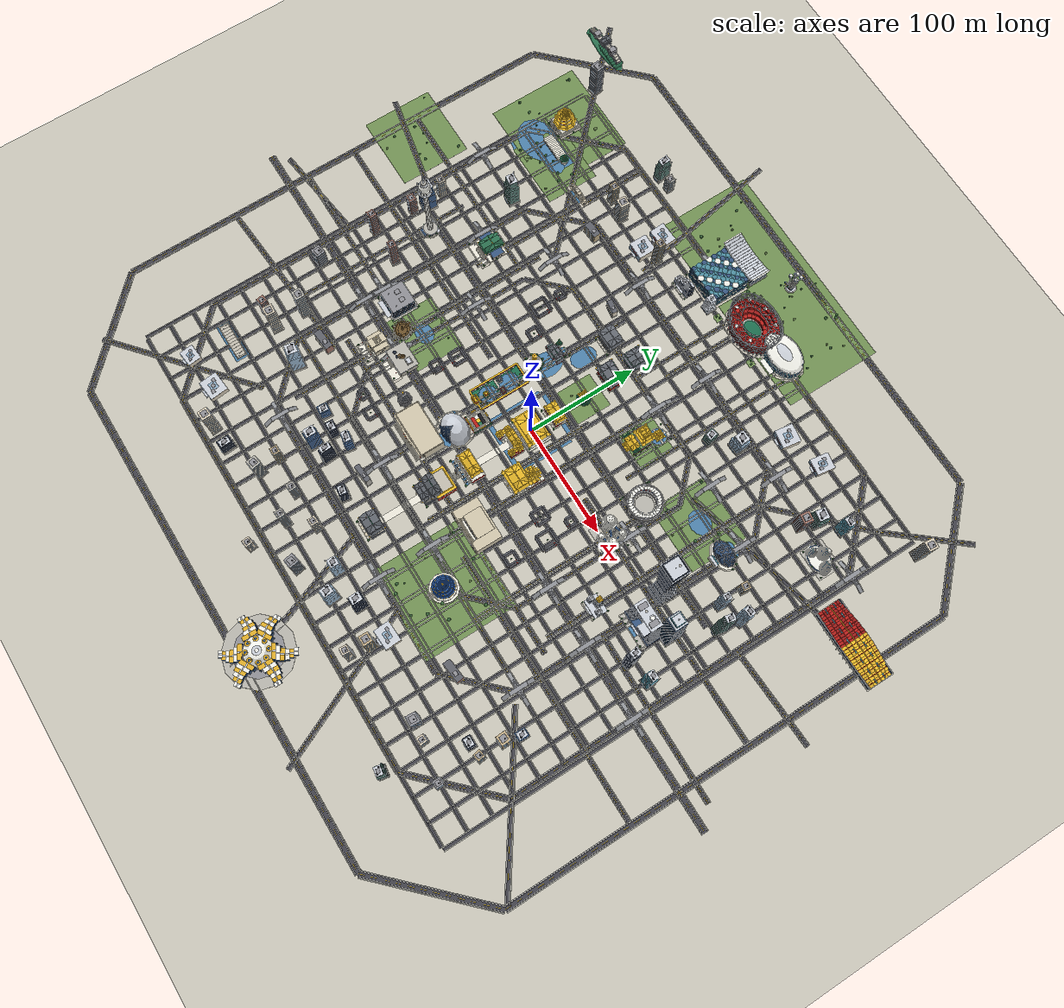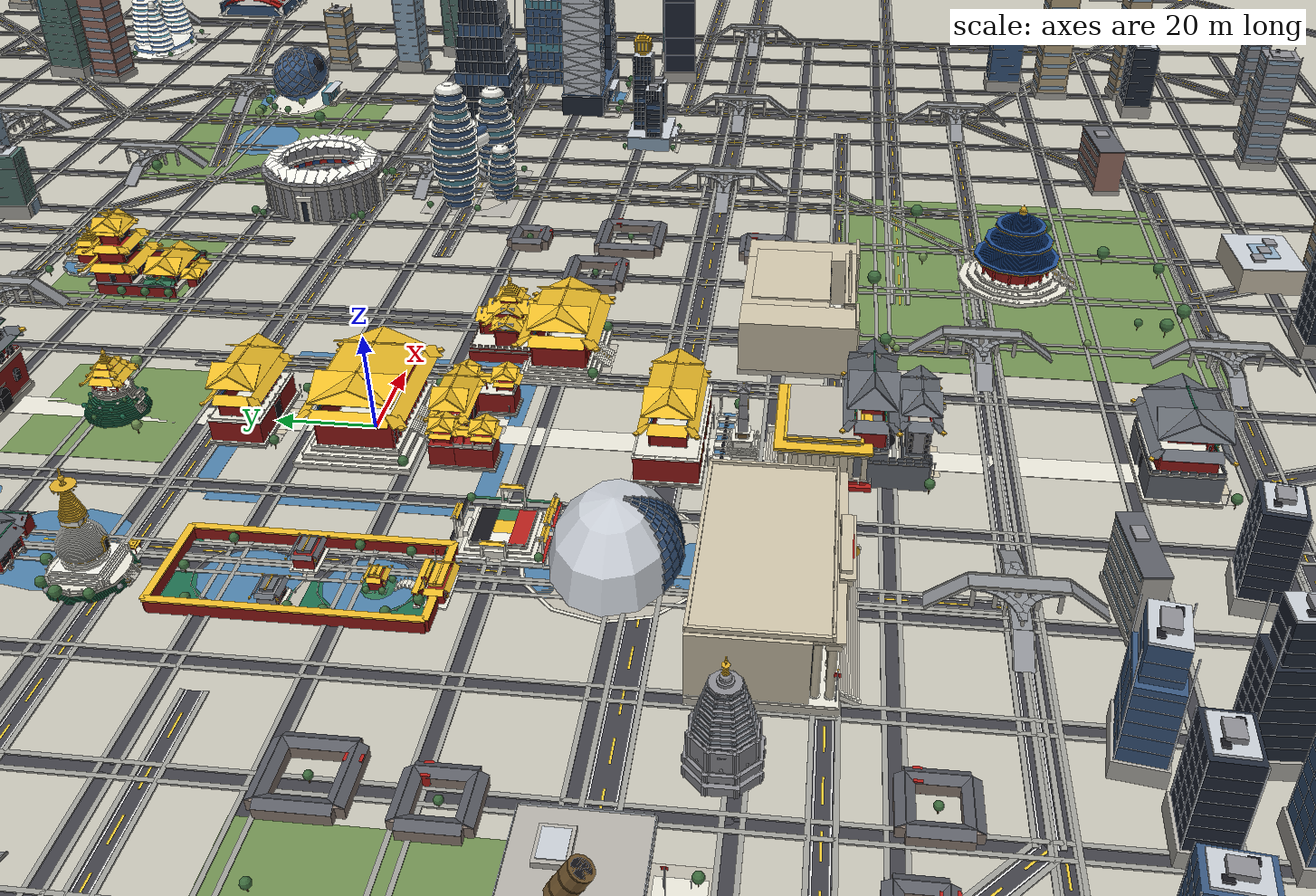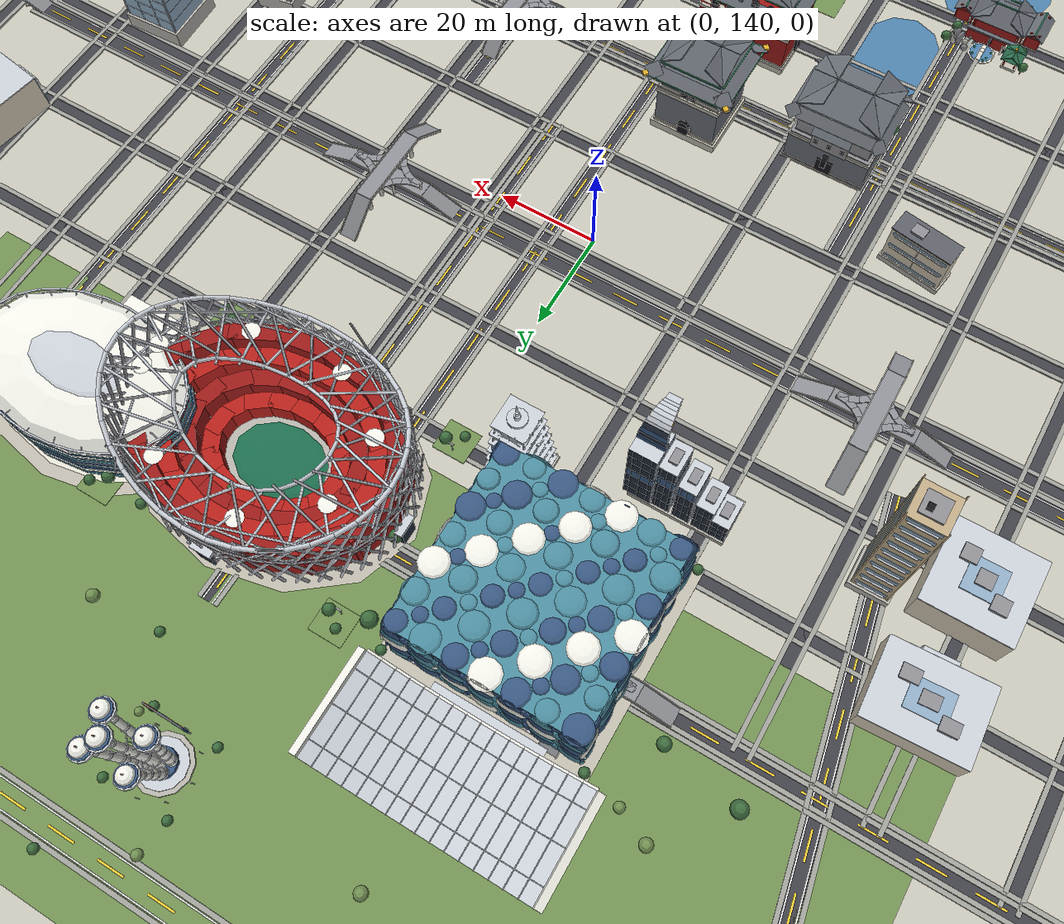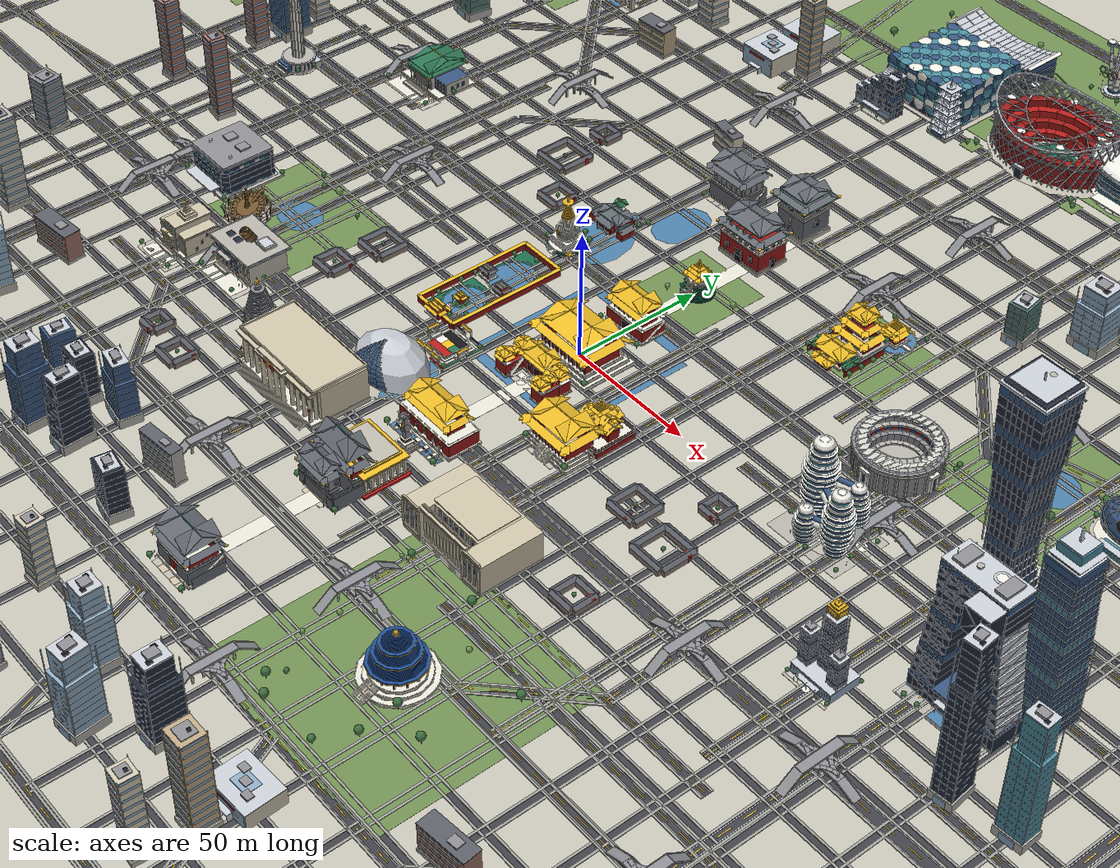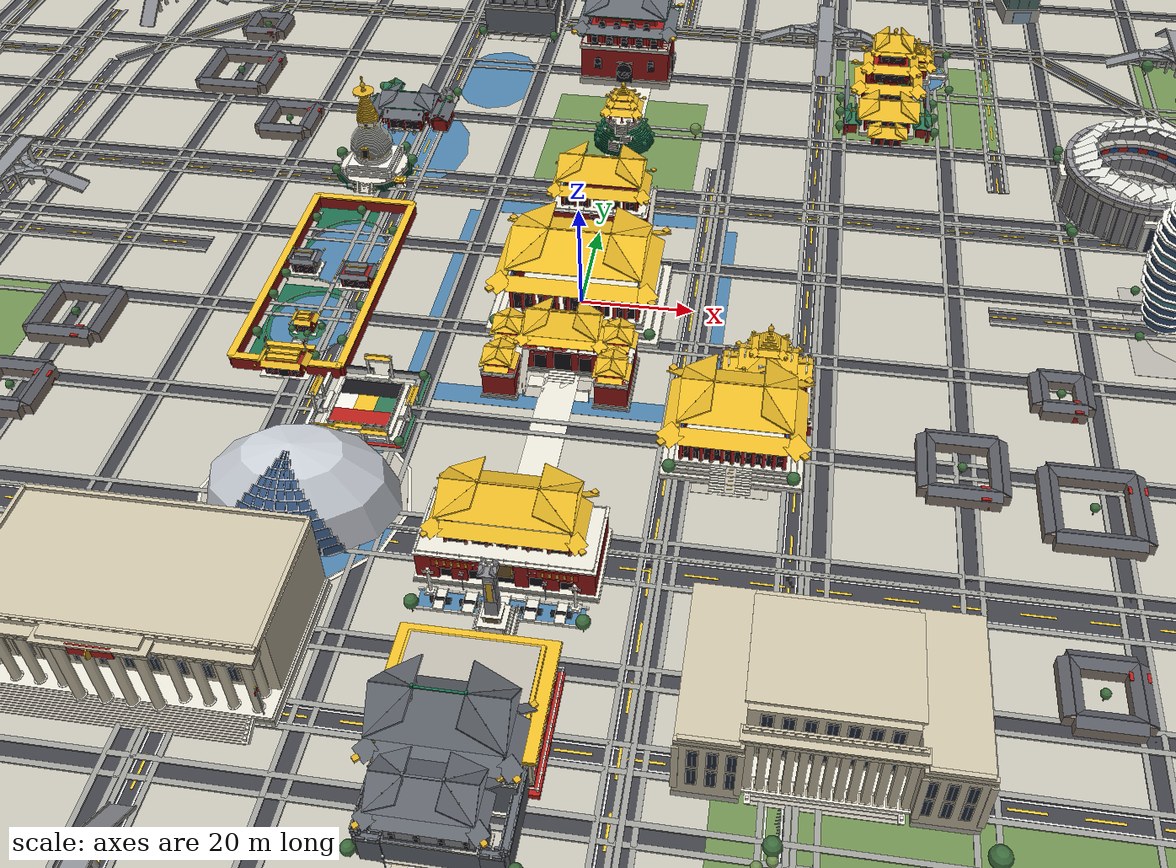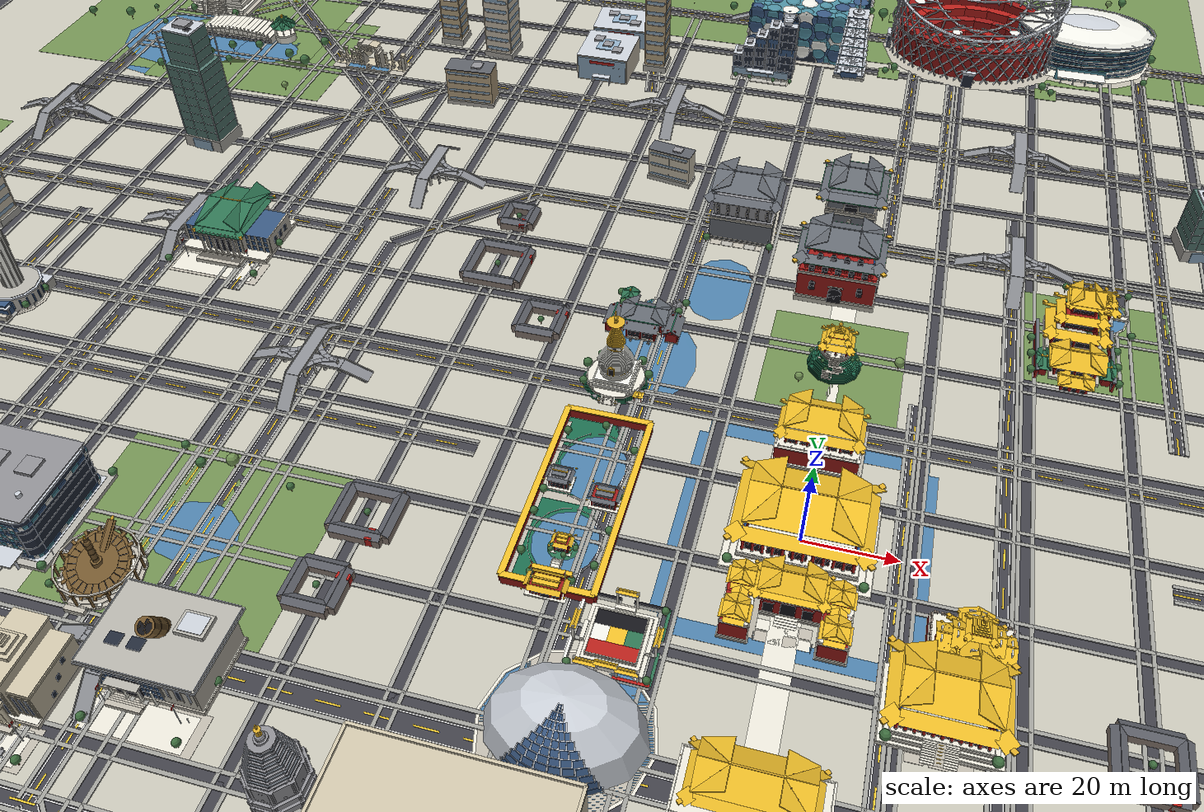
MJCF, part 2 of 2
<geom type="box" material="grey" pos="1.505 14.32 0.56" size="0.58 0.58 0.16" />
      <geom type="box" material="grey" pos="1.505 14.32 8.28" size="0.55 0.55 0.14" />
      <geom type="box" material="concrete" pos="4.079e-15 14.4 8.9" size="0.72 1.689 0.5" euler="0 0 90" />
      <geom type="box" material="grey" pos="4.079e-15 14.4 9.48" size="0.5 1.689 0.14" euler="0 0 90" />
      <geom type="cylinder" material="concrete" pos="-1.505 14.32 4.4" size="0.4 4" />
      <geom type="box" material="grey" pos="-1.505 14.32 0.56" size="0.58 0.58 0.16" />
      <geom type="box" material="grey" pos="-1.505 14.32 8.28" size="0.55 0.55 0.14" />
      <geom type="box" material="concrete" pos="-2.994 14.09 8.9" size="0.72 1.689 0.5" euler="0 0 102" />
      <geom type="box" material="grey" pos="-2.994 14.09 9.48" size="0.5 1.689 0.14" euler="0 0 102" />
      <geom type="cylinder" material="concrete" pos="-4.45 13.7 4.4" size="0.4 4" />
      <geom type="box" material="grey" pos="-4.45 13.7 0.56" size="0.58 0.58 0.16" />
      <geom type="box" material="grey" pos="-4.45 13.7 8.28" size="0.55 0.55 0.14" />
      <geom type="box" material="concrete" pos="-5.857 13.16 8.9" size="0.72 1.689 0.5" euler="0 0 114" />
      <geom type="box" material="grey" pos="-5.857 13.16 9.48" size="0.5 1.689 0.14" euler="0 0 114" />
      <geom type="cylinder" material="concrete" pos="-7.2 12.47 4.4" size="0.4 4" />
      <geom type="box" material="grey" pos="-7.2 12.47 0.56" size="0.58 0.58 0.16" />
      <geom type="box" material="grey" pos="-7.2 12.47 8.28" size="0.55 0.55 0.14" />
      <geom type="box" material="concrete" pos="-8.464 11.65 8.9" size="0.72 1.689 0.5" euler="0 0 126" />
      <geom type="box" material="grey" pos="-8.464 11.65 9.48" size="0.5 1.689 0.14" euler="0 0 126" />
      <geom type="cylinder" material="concrete" pos="-9.635 10.7 4.4" size="0.4 4" />
      <geom type="box" material="grey" pos="-9.635 10.7 0.56" size="0.58 0.58 0.16" />
      <geom type="box" material="grey" pos="-9.635 10.7 8.28" size="0.55 0.55 0.14" />
      <geom type="box" material="concrete" pos="-10.7 9.635 8.9" size="0.72 1.689 0.5" euler="0 0 138" />
      <geom type="box" material="grey" pos="-10.7 9.635 9.48" size="0.5 1.689 0.14" euler="0 0 138" />
      <geom type="cylinder" material="concrete" pos="-11.65 8.464 4.4" size="0.4 4" />
      <geom type="box" material="grey" pos="-11.65 8.464 0.56" size="0.58 0.58 0.16" />
      <geom type="box" material="grey" pos="-11.65 8.464 8.28" size="0.55 0.55 0.14" />
      <geom type="box" material="concrete" pos="-12.47 7.2 8.9" size="0.72 1.689 0.5" euler="0 0 150" />
      <geom type="box" material="grey" pos="-12.47 7.2 9.48" size="0.5 1.689 0.14" euler="0 0 150" />
      <geom type="cylinder" material="concrete" pos="-13.16 5.857 4.4" size="0.4 4" />
      <geom type="box" material="grey" pos="-13.16 5.857 0.56" size="0.58 0.58 0.16" />
      <geom type="box" material="grey" pos="-13.16 5.857 8.28" size="0.55 0.55 0.14" />
      <geom type="box" material="concrete" pos="-13.7 4.45 8.9" size="0.72 1.689 0.5" euler="0 0 162" />
      <geom type="box" material="grey" pos="-13.7 4.45 9.48" size="0.5 1.689 0.14" euler="0 0 162" />
      <geom type="cylinder" material="concrete" pos="-14.09 2.994 4.4" size="0.4 4" />
      <geom type="box" material="grey" pos="-14.09 2.994 0.56" size="0.58 0.58 0.16" />
      <geom type="box" material="grey" pos="-14.09 2.994 8.28" size="0.55 0.55 0.14" />
      <geom type="box" material="concrete" pos="-14.32 1.505 8.9" size="0.72 1.689 0.5" euler="0 0 174" />
      <geom type="box" material="grey" pos="-14.32 1.505 9.48" size="0.5 1.689 0.14" euler="0 0 174" />
      <geom type="cylinder" material="concrete" pos="-14.4 8.158e-15 4.4" size="0.4 4" />
      <geom type="box" material="grey" pos="-14.4 8.158e-15 0.56" size="0.58 0.58 0.16" />
      <geom type="box" material="grey" pos="-14.4 8.158e-15 8.28" size="0.55 0.55 0.14" />
      <geom type="box" material="concrete" pos="-14.32 -1.505 8.9" size="0.72 1.689 0.5" euler="0 0 186" />
      <geom type="box" material="grey" pos="-14.32 -1.505 9.48" size="0.5 1.689 0.14" euler="0 0 186" />
      <geom type="cylinder" material="concrete" pos="-14.09 -2.994 4.4" size="0.4 4" />
      <geom type="box" material="grey" pos="-14.09 -2.994 0.56" size="0.58 0.58 0.16" />
      <geom type="box" material="grey" pos="-14.09 -2.994 8.28" size="0.55 0.55 0.14" />
      <geom type="box" material="concrete" pos="-13.7 -4.45 8.9" size="0.72 1.689 0.5" euler="0 0 198" />
      <geom type="box" material="grey" pos="-13.7 -4.45 9.48" size="0.5 1.689 0.14" euler="0 0 198" />
      <geom type="cylinder" material="concrete" pos="-13.16 -5.857 4.4" size="0.4 4" />
      <geom type="box" material="grey" pos="-13.16 -5.857 0.56" size="0.58 0.58 0.16" />
      <geom type="box" material="grey" pos="-13.16 -5.857 8.28" size="0.55 0.55 0.14" />
      <geom type="box" material="concrete" pos="-12.47 -7.2 8.9" size="0.72 1.689 0.5" euler="0 0 210" />
      <geom type="box" material="grey" pos="-12.47 -7.2 9.48" size="0.5 1.689 0.14" euler="0 0 210" />
      <geom type="cylinder" material="concrete" pos="-11.65 -8.464 4.4" size="0.4 4" />
      <geom type="box" material="grey" pos="-11.65 -8.464 0.56" size="0.58 0.58 0.16" />
      <geom type="box" material="grey" pos="-11.65 -8.464 8.28" size="0.55 0.55 0.14" />
      <geom type="box" material="concrete" pos="-10.7 -9.635 8.9" size="0.72 1.689 0.5" euler="0 0 222" />
      <geom type="box" material="grey" pos="-10.7 -9.635 9.48" size="0.5 1.689 0.14" euler="0 0 222" />
      <geom type="cylinder" material="concrete" pos="-9.635 -10.7 4.4" size="0.4 4" />
      <geom type="box" material="grey" pos="-9.635 -10.7 0.56" size="0.58 0.58 0.16" />
      <geom type="box" material="grey" pos="-9.635 -10.7 8.28" size="0.55 0.55 0.14" />
      <geom type="box" material="concrete" pos="-8.464 -11.65 8.9" size="0.72 1.689 0.5" euler="0 0 234" />
      <geom type="box" material="grey" pos="-8.464 -11.65 9.48" size="0.5 1.689 0.14" euler="0 0 234" />
      <geom type="cylinder" material="concrete" pos="-7.2 -12.47 4.4" size="0.4 4" />
      <geom type="box" material="grey" pos="-7.2 -12.47 0.56" size="0.58 0.58 0.16" />
      <geom type="box" material="grey" pos="-7.2 -12.47 8.28" size="0.55 0.55 0.14" />
      <geom type="box" material="concrete" pos="-5.857 -13.16 8.9" size="0.72 1.689 0.5" euler="0 0 246" />
      <geom type="box" material="grey" pos="-5.857 -13.16 9.48" size="0.5 1.689 0.14" euler="0 0 246" />
      <geom type="cylinder" material="concrete" pos="-4.45 -13.7 4.4" size="0.4 4" />
      <geom type="box" material="grey" pos="-4.45 -13.7 0.56" size="0.58 0.58 0.16" />
      <geom type="box" material="grey" pos="-4.45 -13.7 8.28" size="0.55 0.55 0.14" />
      <geom type="box" material="concrete" pos="-2.994 -14.09 8.9" size="0.72 1.689 0.5" euler="0 0 258" />
      <geom type="box" material="grey" pos="-2.994 -14.09 9.48" size="0.5 1.689 0.14" euler="0 0 258" />
      <geom type="cylinder" material="concrete" pos="-1.505 -14.32 4.4" size="0.4 4" />
      <geom type="box" material="grey" pos="-1.505 -14.32 0.56" size="0.58 0.58 0.16" />
      <geom type="box" material="grey" pos="-1.505 -14.32 8.28" size="0.55 0.55 0.14" />
      <geom type="box" material="concrete" pos="-2.645e-15 -14.4 8.9" size="0.72 1.689 0.5" euler="0 0 270" />
      <geom type="box" material="grey" pos="-2.645e-15 -14.4 9.48" size="0.5 1.689 0.14" euler="0 0 270" />
      <geom type="cylinder" material="concrete" pos="1.505 -14.32 4.4" size="0.4 4" />
      <geom type="box" material="grey" pos="1.505 -14.32 0.56" size="0.58 0.58 0.16" />
      <geom type="box" material="grey" pos="1.505 -14.32 8.28" size="0.55 0.55 0.14" />
      <geom type="box" material="concrete" pos="2.994 -14.09 8.9" size="0.72 1.689 0.5" euler="0 0 282" />
      <geom type="box" material="grey" pos="2.994 -14.09 9.48" size="0.5 1.689 0.14" euler="0 0 282" />
      <geom type="cylinder" material="concrete" pos="4.45 -13.7 4.4" size="0.4 4" />
      <geom type="box" material="grey" pos="4.45 -13.7 0.56" size="0.58 0.58 0.16" />
      <geom type="box" material="grey" pos="4.45 -13.7 8.28" size="0.55 0.55 0.14" />
      <geom type="box" material="concrete" pos="5.857 -13.16 8.9" size="0.72 1.689 0.5" euler="0 0 294" />
      <geom type="box" material="grey" pos="5.857 -13.16 9.48" size="0.5 1.689 0.14" euler="0 0 294" />
      <geom type="cylinder" material="concrete" pos="7.2 -12.47 4.4" size="0.4 4" />
      <geom type="box" material="grey" pos="7.2 -12.47 0.56" size="0.58 0.58 0.16" />
      <geom type="box" material="grey" pos="7.2 -12.47 8.28" size="0.55 0.55 0.14" />
      <geom type="box" material="concrete" pos="8.464 -11.65 8.9" size="0.72 1.689 0.5" euler="0 0 306" />
      <geom type="box" material="grey" pos="8.464 -11.65 9.48" size="0.5 1.689 0.14" euler="0 0 306" />
      <geom type="cylinder" material="concrete" pos="9.635 -10.7 4.4" size="0.4 4" />
      <geom type="box" material="grey" pos="9.635 -10.7 0.56" size="0.58 0.58 0.16" />
      <geom type="box" material="grey" pos="9.635 -10.7 8.28" size="0.55 0.55 0.14" />
      <geom type="box" material="concrete" pos="10.7 -9.635 8.9" size="0.72 1.689 0.5" euler="0 0 318" />
      <geom type="box" material="grey" pos="10.7 -9.635 9.48" size="0.5 1.689 0.14" euler="0 0 318" />
      <geom type="cylinder" material="concrete" pos="11.65 -8.464 4.4" size="0.4 4" />
      <geom type="box" material="grey" pos="11.65 -8.464 0.56" size="0.58 0.58 0.16" />
      <geom type="box" material="grey" pos="11.65 -8.464 8.28" size="0.55 0.55 0.14" />
      <geom type="box" material="concrete" pos="12.47 -7.2 8.9" size="0.72 1.689 0.5" euler="0 0 330" />
      <geom type="box" material="grey" pos="12.47 -7.2 9.48" size="0.5 1.689 0.14" euler="0 0 330" />
      <geom type="cylinder" material="concrete" pos="13.16 -5.857 4.4" size="0.4 4" />
      <geom type="box" material="grey" pos="13.16 -5.857 0.56" size="0.58 0.58 0.16" />
      <geom type="box" material="grey" pos="13.16 -5.857 8.28" size="0.55 0.55 0.14" />
      <geom type="box" material="concrete" pos="13.7 -4.45 8.9" size="0.72 1.689 0.5" euler="0 0 342" />
      <geom type="box" material="grey" pos="13.7 -4.45 9.48" size="0.5 1.689 0.14" euler="0 0 342" />
      <geom type="cylinder" material="concrete" pos="14.09 -2.994 4.4" size="0.4 4" />
      <geom type="box" material="grey" pos="14.09 -2.994 0.56" size="0.58 0.58 0.16" />
      <geom type="box" material="grey" pos="14.09 -2.994 8.28" size="0.55 0.55 0.14" />
      <geom type="box" material="concrete" pos="14.32 -1.505 8.9" size="0.72 1.689 0.5" euler="0 0 354" />
      <geom type="box" material="grey" pos="14.32 -1.505 9.48" size="0.5 1.689 0.14" euler="0 0 354" />
      <geom type="capsule" material="steel" fromto="13.8 0 9.6 9.6 0 11.8" size="0.13" />
      <geom type="box" material="white" pos="11.64 1.223 10.75" size="2.1 1.409 0.07" euler="0 152.4 6" />
      <geom type="capsule" material="steel" fromto="13.5 2.869 9.6 9.39 1.996 11.8" size="0.13" />
      <geom type="box" material="white" pos="11.13 3.615 10.75" size="2.1 1.409 0.07" euler="0 152.4 18" />
      <geom type="capsule" material="steel" fromto="12.61 5.613 9.6 8.77 3.905 11.8" size="0.13" />
      <geom type="box" material="white" pos="10.13 5.85 10.75" size="2.1 1.409 0.07" euler="0 152.4 30" />
      <geom type="capsule" material="steel" fromto="11.16 8.111 9.6 7.767 5.643 11.8" size="0.13" />
      <geom type="box" material="white" pos="8.695 7.829 10.75" size="2.1 1.409 0.07" euler="0 152.4 42" />
      <geom type="capsule" material="steel" fromto="9.234 10.26 9.6 6.424 7.134 11.8" size="0.13" />
      <geom type="box" material="white" pos="6.877 9.465 10.75" size="2.1 1.409 0.07" euler="0 152.4 54" />
      <geom type="capsule" material="steel" fromto="6.9 11.95 9.6 4.8 8.314 11.8" size="0.13" />
      <geom type="box" material="white" pos="4.759 10.69 10.75" size="2.1 1.409 0.07" euler="0 152.4 66" />
      <geom type="capsule" material="steel" fromto="4.264 13.12 9.6 2.967 9.13 11.8" size="0.13" />
      <geom type="box" material="white" pos="2.433 11.44 10.75" size="2.1 1.409 0.07" euler="0 152.4 78" />
      <geom type="capsule" material="steel" fromto="1.442 13.72 9.6 1.003 9.547 11.8" size="0.13" />
      <geom type="box" material="white" pos="3.314e-15 11.7 10.75" size="2.1 1.409 0.07" euler="0 152.4 90" />
      <geom type="capsule" material="steel" fromto="-1.442 13.72 9.6 -1.003 9.547 11.8" size="0.13" />
      <geom type="box" material="white" pos="-2.433 11.44 10.75" size="2.1 1.409 0.07" euler="0 152.4 102" />
      <geom type="capsule" material="steel" fromto="-4.264 13.12 9.6 -2.967 9.13 11.8" size="0.13" />
      <geom type="box" material="white" pos="-4.759 10.69 10.75" size="2.1 1.409 0.07" euler="0 152.4 114" />
      <geom type="capsule" material="steel" fromto="-6.9 11.95 9.6 -4.8 8.314 11.8" size="0.13" />
      <geom type="box" material="white" pos="-6.877 9.465 10.75" size="2.1 1.409 0.07" euler="0 152.4 126" />
      <geom type="capsule" material="steel" fromto="-9.234 10.26 9.6 -6.424 7.134 11.8" size="0.13" />
      <geom type="box" material="white" pos="-8.695 7.829 10.75" size="2.1 1.409 0.07" euler="0 152.4 138" />
      <geom type="capsule" material="steel" fromto="-11.16 8.111 9.6 -7.767 5.643 11.8" size="0.13" />
      <geom type="box" material="white" pos="-10.13 5.85 10.75" size="2.1 1.409 0.07" euler="0 152.4 150" />
      <geom type="capsule" material="steel" fromto="-12.61 5.613 9.6 -8.77 3.905 11.8" size="0.13" />
      <geom type="box" material="white" pos="-11.13 3.615 10.75" size="2.1 1.409 0.07" euler="0 152.4 162" />
      <geom type="capsule" material="steel" fromto="-13.5 2.869 9.6 -9.39 1.996 11.8" size="0.13" />
      <geom type="box" material="white" pos="-11.64 1.223 10.75" size="2.1 1.409 0.07" euler="0 152.4 174" />
      <geom type="capsule" material="steel" fromto="-13.8 7.818e-15 9.6 -9.6 5.439e-15 11.8" size="0.13" />
      <geom type="box" material="white" pos="-11.64 -1.223 10.75" size="2.1 1.409 0.07" euler="0 152.4 186" />
      <geom type="capsule" material="steel" fromto="-13.5 -2.869 9.6 -9.39 -1.996 11.8" size="0.13" />
      <geom type="box" material="white" pos="-11.13 -3.615 10.75" size="2.1 1.409 0.07" euler="0 152.4 198" />
      <geom type="capsule" material="steel" fromto="-12.61 -5.613 9.6 -8.77 -3.905 11.8" size="0.13" />
      <geom type="box" material="white" pos="-10.13 -5.85 10.75" size="2.1 1.409 0.07" euler="0 152.4 210" />
      <geom type="capsule" material="steel" fromto="-11.16 -8.111 9.6 -7.767 -5.643 11.8" size="0.13" />
      <geom type="box" material="white" pos="-8.695 -7.829 10.75" size="2.1 1.409 0.07" euler="0 152.4 222" />
      <geom type="capsule" material="steel" fromto="-9.234 -10.26 9.6 -6.424 -7.134 11.8" size="0.13" />
      <geom type="box" material="white" pos="-6.877 -9.465 10.75" size="2.1 1.409 0.07" euler="0 152.4 234" />
      <geom type="capsule" material="steel" fromto="-6.9 -11.95 9.6 -4.8 -8.314 11.8" size="0.13" />
      <geom type="box" material="white" pos="-4.759 -10.69 10.75" size="2.1 1.409 0.07" euler="0 152.4 246" />
      <geom type="capsule" material="steel" fromto="-4.264 -13.12 9.6 -2.967 -9.13 11.8" size="0.13" />
      <geom type="box" material="white" pos="-2.433 -11.44 10.75" size="2.1 1.409 0.07" euler="0 152.4 258" />
      <geom type="capsule" material="steel" fromto="-1.442 -13.72 9.6 -1.003 -9.547 11.8" size="0.13" />
      <geom type="box" material="white" pos="-2.149e-15 -11.7 10.75" size="2.1 1.409 0.07" euler="0 152.4 270" />
      <geom type="capsule" material="steel" fromto="1.442 -13.72 9.6 1.003 -9.547 11.8" size="0.13" />
      <geom type="box" material="white" pos="2.433 -11.44 10.75" size="2.1 1.409 0.07" euler="0 152.4 282" />
      <geom type="capsule" material="steel" fromto="4.264 -13.12 9.6 2.967 -9.13 11.8" size="0.13" />
      <geom type="box" material="white" pos="4.759 -10.69 10.75" size="2.1 1.409 0.07" euler="0 152.4 294" />
      <geom type="capsule" material="steel" fromto="6.9 -11.95 9.6 4.8 -8.314 11.8" size="0.13" />
      <geom type="box" material="white" pos="6.877 -9.465 10.75" size="2.1 1.409 0.07" euler="0 152.4 306" />
      <geom type="capsule" material="steel" fromto="9.234 -10.26 9.6 6.424 -7.134 11.8" size="0.13" />
      <geom type="box" material="white" pos="8.695 -7.829 10.75" size="2.1 1.409 0.07" euler="0 152.4 318" />
      <geom type="capsule" material="steel" fromto="11.16 -8.111 9.6 7.767 -5.643 11.8" size="0.13" />
      <geom type="box" material="white" pos="10.13 -5.85 10.75" size="2.1 1.409 0.07" euler="0 152.4 330" />
      <geom type="capsule" material="steel" fromto="12.61 -5.613 9.6 8.77 -3.905 11.8" size="0.13" />
      <geom type="box" material="white" pos="11.13 -3.615 10.75" size="2.1 1.409 0.07" euler="0 152.4 342" />
      <geom type="capsule" material="steel" fromto="13.5 -2.869 9.6 9.39 -1.996 11.8" size="0.13" />
      <geom type="box" material="white" pos="11.64 -1.223 10.75" size="2.1 1.409 0.07" euler="0 152.4 354" />
      <geom type="capsule" material="steel" fromto="9.6 0 11.8 9.39 1.996 11.8" size="0.16" />
      <geom type="capsule" material="steel" fromto="9.39 1.996 11.8 8.77 3.905 11.8" size="0.16" />
      <geom type="capsule" material="steel" fromto="8.77 3.905 11.8 7.767 5.643 11.8" size="0.16" />
      <geom type="capsule" material="steel" fromto="7.767 5.643 11.8 6.424 7.134 11.8" size="0.16" />
      <geom type="capsule" material="steel" fromto="6.424 7.134 11.8 4.8 8.314 11.8" size="0.16" />
      <geom type="capsule" material="steel" fromto="4.8 8.314 11.8 2.967 9.13 11.8" size="0.16" />
      <geom type="capsule" material="steel" fromto="2.967 9.13 11.8 1.003 9.547 11.8" size="0.16" />
      <geom type="capsule" material="steel" fromto="1.003 9.547 11.8 -1.003 9.547 11.8" size="0.16" />
      <geom type="capsule" material="steel" fromto="-1.003 9.547 11.8 -2.967 9.13 11.8" size="0.16" />
      <geom type="capsule" material="steel" fromto="-2.967 9.13 11.8 -4.8 8.314 11.8" size="0.16" />
      <geom type="capsule" material="steel" fromto="-4.8 8.314 11.8 -6.424 7.134 11.8" size="0.16" />
      <geom type="capsule" material="steel" fromto="-6.424 7.134 11.8 -7.767 5.643 11.8" size="0.16" />
      <geom type="capsule" material="steel" fromto="-7.767 5.643 11.8 -8.77 3.905 11.8" size="0.16" />
      <geom type="capsule" material="steel" fromto="-8.77 3.905 11.8 -9.39 1.996 11.8" size="0.16" />
      <geom type="capsule" material="steel" fromto="-9.39 1.996 11.8 -9.6 5.439e-15 11.8" size="0.16" />
      <geom type="capsule" material="steel" fromto="-9.6 5.439e-15 11.8 -9.39 -1.996 11.8" size="0.16" />
      <geom type="capsule" material="steel" fromto="-9.39 -1.996 11.8 -8.77 -3.905 11.8" size="0.16" />
      <geom type="capsule" material="steel" fromto="-8.77 -3.905 11.8 -7.767 -5.643 11.8" size="0.16" />
      <geom type="capsule" material="steel" fromto="-7.767 -5.643 11.8 -6.424 -7.134 11.8" size="0.16" />
      <geom type="capsule" material="steel" fromto="-6.424 -7.134 11.8 -4.8 -8.314 11.8" size="0.16" />
      <geom type="capsule" material="steel" fromto="-4.8 -8.314 11.8 -2.967 -9.13 11.8" size="0.16" />
      <geom type="capsule" material="steel" fromto="-2.967 -9.13 11.8 -1.003 -9.547 11.8" size="0.16" />
      <geom type="capsule" material="steel" fromto="-1.003 -9.547 11.8 1.003 -9.547 11.8" size="0.16" />
      <geom type="capsule" material="steel" fromto="1.003 -9.547 11.8 2.967 -9.13 11.8" size="0.16" />
      <geom type="capsule" material="steel" fromto="2.967 -9.13 11.8 4.8 -8.314 11.8" size="0.16" />
      <geom type="capsule" material="steel" fromto="4.8 -8.314 11.8 6.424 -7.134 11.8" size="0.16" />
      <geom type="capsule" material="steel" fromto="6.424 -7.134 11.8 7.767 -5.643 11.8" size="0.16" />
      <geom type="capsule" material="steel" fromto="7.767 -5.643 11.8 8.77 -3.905 11.8" size="0.16" />
      <geom type="capsule" material="steel" fromto="8.77 -3.905 11.8 9.39 -1.996 11.8" size="0.16" />
      <geom type="capsule" material="steel" fromto="9.39 -1.996 11.8 9.6 -1.088e-14 11.8" size="0.16" />
      <geom type="box" material="marble" pos="-1.2 -15 3" size="0.5 0.5 3" euler="0 0 -90" />
      <geom type="box" material="marble" pos="1.2 -15 3" size="0.5 0.5 3" euler="0 0 -90" />
      <geom type="box" material="marble" pos="9.185e-16 -15 6.3" size="0.6 1.9 0.5" euler="0 0 -90" />
      <geom type="box" material="darkglass" pos="9.185e-16 -15 2.8" size="0.3 1.3 2.6" euler="0 0 -90" />
      <geom type="box" material="marble" pos="1.2 15 3" size="0.5 0.5 3" euler="0 0 90" />
      <geom type="box" material="marble" pos="-1.2 15 3" size="0.5 0.5 3" euler="0 0 90" />
      <geom type="box" material="marble" pos="9.185e-16 15 6.3" size="0.6 1.9 0.5" euler="0 0 90" />
      <geom type="box" material="darkglass" pos="9.185e-16 15 2.8" size="0.3 1.3 2.6" euler="0 0 90" />
      <geom type="box" material="marble" pos="15 -1.2 3" size="0.5 0.5 3" euler="0 0 0" />
      <geom type="box" material="marble" pos="15 1.2 3" size="0.5 0.5 3" euler="0 0 0" />
      <geom type="box" material="marble" pos="15 0 6.3" size="0.6 1.9 0.5" euler="0 0 0" />
      <geom type="box" material="darkglass" pos="15 0 2.8" size="0.3 1.3 2.6" euler="0 0 0" />
      <geom type="box" material="marble" pos="-15 1.2 3" size="0.5 0.5 3" euler="0 0 180" />
      <geom type="box" material="marble" pos="-15 -1.2 3" size="0.5 0.5 3" euler="0 0 180" />
      <geom type="box" material="marble" pos="-15 1.837e-15 6.3" size="0.6 1.9 0.5" euler="0 0 180" />
      <geom type="box" material="darkglass" pos="-15 1.837e-15 2.8" size="0.3 1.3 2.6" euler="0 0 180" />
    </body>
    <body name="wukesong" pos="-156 -34 0">
      <geom type="box" material="concrete" pos="0 0 0.5" size="12.8 12.8 0.5" />
      <geom type="box" material="steel" pos="0 0 1.02" size="11.4 11.4 0.08" />
      <geom type="cylinder" material="bronze" pos="-12.4 -12.4 0.784" size="0.1 0.784" />
      <geom type="sphere" material="treedark" pos="-12.4 -12.4 2.016" size="0.952" />
      <geom type="cylinder" material="bronze" pos="-12.4 12.4 0.784" size="0.1 0.784" />
      <geom type="sphere" material="treedark" pos="-12.4 12.4 2.016" size="0.952" />
      <geom type="cylinder" material="steel" pos="-12.4 -9 1.2" size="0.07 1.2" />
      <geom type="sphere" material="white" pos="-12.4 -9 2.5" size="0.14" />
      <geom type="cylinder" material="bronze" pos="12.4 -12.4 0.784" size="0.1 0.784" />
      <geom type="sphere" material="treedark" pos="12.4 -12.4 2.016" size="0.952" />
      <geom type="cylinder" material="bronze" pos="12.4 12.4 0.784" size="0.1 0.784" />
      <geom type="sphere" material="treedark" pos="12.4 12.4 2.016" size="0.952" />
      <geom type="cylinder" material="steel" pos="12.4 -9 1.2" size="0.07 1.2" />
      <geom type="sphere" material="white" pos="12.4 -9 2.5" size="0.14" />
      <geom type="box" material="darkglass" pos="0 0 6.5" size="8.8 11 5.5" />
      <geom type="box" material="darkglass" pos="0 0 6.5" size="11 8.8 5.5" />
      <geom type="cylinder" material="darkglass" pos="-8.8 -8.8 6.5" size="2.2 5.5" />
      <geom type="cylinder" material="darkglass" pos="-8.8 8.8 6.5" size="2.2 5.5" />
      <geom type="cylinder" material="darkglass" pos="8.8 -8.8 6.5" size="2.2 5.5" />
      <geom type="cylinder" material="darkglass" pos="8.8 8.8 6.5" size="2.2 5.5" />
      <geom type="box" material="blueglass" pos="-8.031 -11.13 2.406" size="0.5755 0.09 0.4348" />
      <geom type="box" material="cyanglass" pos="-8.031 -11.13 3.417" size="0.5755 0.09 0.4348" />
      <geom type="box" material="white" pos="-8.031 -11.13 4.428" size="0.5755 0.09 0.4348" />
      <geom type="box" material="blueglass" pos="-8.031 -11.13 5.439" size="0.5755 0.09 0.4348" />
      <geom type="box" material="darkglass" pos="-8.031 -11.13 6.45" size="0.5755 0.09 0.4348" />
      <geom type="box" material="cyanglass" pos="-8.031 -11.13 7.461" size="0.5755 0.09 0.4348" />
      <geom type="box" material="blueglass" pos="-8.031 -11.13 8.472" size="0.5755 0.09 0.4348" />
      <geom type="box" material="cyanglass" pos="-8.031 -11.13 9.483" size="0.5755 0.09 0.4348" />
      <geom type="box" material="white" pos="-8.031 -11.13 10.49" size="0.5755 0.09 0.4348" />
      <geom type="box" material="blueglass" pos="-6.692 -11.13 2.406" size="0.5755 0.09 0.4348" />
      <geom type="box" material="darkglass" pos="-6.692 -11.13 3.417" size="0.5755 0.09 0.4348" />
      <geom type="box" material="cyanglass" pos="-6.692 -11.13 4.428" size="0.5755 0.09 0.4348" />
      <geom type="box" material="blueglass" pos="-6.692 -11.13 5.439" size="0.5755 0.09 0.4348" />
      <geom type="box" material="cyanglass" pos="-6.692 -11.13 6.45" size="0.5755 0.09 0.4348" />
      <geom type="box" material="white" pos="-6.692 -11.13 7.461" size="0.5755 0.09 0.4348" />
      <geom type="box" material="blueglass" pos="-6.692 -11.13 8.472" size="0.5755 0.09 0.4348" />
      <geom type="box" material="darkglass" pos="-6.692 -11.13 9.483" size="0.5755 0.09 0.4348" />
      <geom type="box" material="cyanglass" pos="-6.692 -11.13 10.49" size="0.5755 0.09 0.4348" />
      <geom type="box" material="blueglass" pos="-5.354 -11.13 2.406" size="0.5755 0.09 0.4348" />
      <geom type="box" material="cyanglass" pos="-5.354 -11.13 3.417" size="0.5755 0.09 0.4348" />
      <geom type="box" material="white" pos="-5.354 -11.13 4.428" size="0.5755 0.09 0.4348" />
      <geom type="box" material="blueglass" pos="-5.354 -11.13 5.439" size="0.5755 0.09 0.4348" />
      <geom type="box" material="darkglass" pos="-5.354 -11.13 6.45" size="0.5755 0.09 0.4348" />
      <geom type="box" material="cyanglass" pos="-5.354 -11.13 7.461" size="0.5755 0.09 0.4348" />
      <geom type="box" material="blueglass" pos="-5.354 -11.13 8.472" size="0.5755 0.09 0.4348" />
      <geom type="box" material="cyanglass" pos="-5.354 -11.13 9.483" size="0.5755 0.09 0.4348" />
      <geom type="box" material="white" pos="-5.354 -11.13 10.49" size="0.5755 0.09 0.4348" />
      <geom type="box" material="blueglass" pos="-4.015 -11.13 2.406" size="0.5755 0.09 0.4348" />
      <geom type="box" material="darkglass" pos="-4.015 -11.13 3.417" size="0.5755 0.09 0.4348" />
      <geom type="box" material="cyanglass" pos="-4.015 -11.13 4.428" size="0.5755 0.09 0.4348" />
      <geom type="box" material="blueglass" pos="-4.015 -11.13 5.439" size="0.5755 0.09 0.4348" />
      <geom type="box" material="cyanglass" pos="-4.015 -11.13 6.45" size="0.5755 0.09 0.4348" />
      <geom type="box" material="white" pos="-4.015 -11.13 7.461" size="0.5755 0.09 0.4348" />
      <geom type="box" material="blueglass" pos="-4.015 -11.13 8.472" size="0.5755 0.09 0.4348" />
      <geom type="box" material="darkglass" pos="-4.015 -11.13 9.483" size="0.5755 0.09 0.4348" />
      <geom type="box" material="cyanglass" pos="-4.015 -11.13 10.49" size="0.5755 0.09 0.4348" />
      <geom type="box" material="blueglass" pos="-2.677 -11.13 2.406" size="0.5755 0.09 0.4348" />
      <geom type="box" material="cyanglass" pos="-2.677 -11.13 3.417" size="0.5755 0.09 0.4348" />
      <geom type="box" material="white" pos="-2.677 -11.13 4.428" size="0.5755 0.09 0.4348" />
      <geom type="box" material="blueglass" pos="-2.677 -11.13 5.439" size="0.5755 0.09 0.4348" />
      <geom type="box" material="darkglass" pos="-2.677 -11.13 6.45" size="0.5755 0.09 0.4348" />
      <geom type="box" material="cyanglass" pos="-2.677 -11.13 7.461" size="0.5755 0.09 0.4348" />
      <geom type="box" material="blueglass" pos="-2.677 -11.13 8.472" size="0.5755 0.09 0.4348" />
      <geom type="box" material="cyanglass" pos="-2.677 -11.13 9.483" size="0.5755 0.09 0.4348" />
      <geom type="box" material="white" pos="-2.677 -11.13 10.49" size="0.5755 0.09 0.4348" />
      <geom type="box" material="blueglass" pos="-1.338 -11.13 2.406" size="0.5755 0.09 0.4348" />
      <geom type="box" material="darkglass" pos="-1.338 -11.13 3.417" size="0.5755 0.09 0.4348" />
      <geom type="box" material="cyanglass" pos="-1.338 -11.13 4.428" size="0.5755 0.09 0.4348" />
      <geom type="box" material="blueglass" pos="-1.338 -11.13 5.439" size="0.5755 0.09 0.4348" />
      <geom type="box" material="cyanglass" pos="-1.338 -11.13 6.45" size="0.5755 0.09 0.4348" />
      <geom type="box" material="white" pos="-1.338 -11.13 7.461" size="0.5755 0.09 0.4348" />
      <geom type="box" material="blueglass" pos="-1.338 -11.13 8.472" size="0.5755 0.09 0.4348" />
      <geom type="box" material="darkglass" pos="-1.338 -11.13 9.483" size="0.5755 0.09 0.4348" />
      <geom type="box" material="cyanglass" pos="-1.338 -11.13 10.49" size="0.5755 0.09 0.4348" />
      <geom type="box" material="blueglass" pos="0 -11.13 2.406" size="0.5755 0.09 0.4348" />
      <geom type="box" material="cyanglass" pos="0 -11.13 3.417" size="0.5755 0.09 0.4348" />
      <geom type="box" material="white" pos="0 -11.13 4.428" size="0.5755 0.09 0.4348" />
      <geom type="box" material="blueglass" pos="0 -11.13 5.439" size="0.5755 0.09 0.4348" />
      <geom type="box" material="darkglass" pos="0 -11.13 6.45" size="0.5755 0.09 0.4348" />
      <geom type="box" material="cyanglass" pos="0 -11.13 7.461" size="0.5755 0.09 0.4348" />
      <geom type="box" material="blueglass" pos="0 -11.13 8.472" size="0.5755 0.09 0.4348" />
      <geom type="box" material="cyanglass" pos="0 -11.13 9.483" size="0.5755 0.09 0.4348" />
      <geom type="box" material="white" pos="0 -11.13 10.49" size="0.5755 0.09 0.4348" />
      <geom type="box" material="blueglass" pos="1.338 -11.13 2.406" size="0.5755 0.09 0.4348" />
      <geom type="box" material="darkglass" pos="1.338 -11.13 3.417" size="0.5755 0.09 0.4348" />
      <geom type="box" material="cyanglass" pos="1.338 -11.13 4.428" size="0.5755 0.09 0.4348" />
      <geom type="box" material="blueglass" pos="1.338 -11.13 5.439" size="0.5755 0.09 0.4348" />
      <geom type="box" material="cyanglass" pos="1.338 -11.13 6.45" size="0.5755 0.09 0.4348" />
      <geom type="box" material="white" pos="1.338 -11.13 7.461" size="0.5755 0.09 0.4348" />
      <geom type="box" material="blueglass" pos="1.338 -11.13 8.472" size="0.5755 0.09 0.4348" />
      <geom type="box" material="darkglass" pos="1.338 -11.13 9.483" size="0.5755 0.09 0.4348" />
      <geom type="box" material="cyanglass" pos="1.338 -11.13 10.49" size="0.5755 0.09 0.4348" />
      <geom type="box" material="blueglass" pos="2.677 -11.13 2.406" size="0.5755 0.09 0.4348" />
      <geom type="box" material="cyanglass" pos="2.677 -11.13 3.417" size="0.5755 0.09 0.4348" />
      <geom type="box" material="white" pos="2.677 -11.13 4.428" size="0.5755 0.09 0.4348" />
      <geom type="box" material="blueglass" pos="2.677 -11.13 5.439" size="0.5755 0.09 0.4348" />
      <geom type="box" material="darkglass" pos="2.677 -11.13 6.45" size="0.5755 0.09 0.4348" />
      <geom type="box" material="cyanglass" pos="2.677 -11.13 7.461" size="0.5755 0.09 0.4348" />
      <geom type="box" material="blueglass" pos="2.677 -11.13 8.472" size="0.5755 0.09 0.4348" />
      <geom type="box" material="cyanglass" pos="2.677 -11.13 9.483" size="0.5755 0.09 0.4348" />
      <geom type="box" material="white" pos="2.677 -11.13 10.49" size="0.5755 0.09 0.4348" />
      <geom type="box" material="blueglass" pos="4.015 -11.13 2.406" size="0.5755 0.09 0.4348" />
      <geom type="box" material="darkglass" pos="4.015 -11.13 3.417" size="0.5755 0.09 0.4348" />
      <geom type="box" material="cyanglass" pos="4.015 -11.13 4.428" size="0.5755 0.09 0.4348" />
      <geom type="box" material="blueglass" pos="4.015 -11.13 5.439" size="0.5755 0.09 0.4348" />
      <geom type="box" material="cyanglass" pos="4.015 -11.13 6.45" size="0.5755 0.09 0.4348" />
      <geom type="box" material="white" pos="4.015 -11.13 7.461" size="0.5755 0.09 0.4348" />
      <geom type="box" material="blueglass" pos="4.015 -11.13 8.472" size="0.5755 0.09 0.4348" />
      <geom type="box" material="darkglass" pos="4.015 -11.13 9.483" size="0.5755 0.09 0.4348" />
      <geom type="box" material="cyanglass" pos="4.015 -11.13 10.49" size="0.5755 0.09 0.4348" />
      <geom type="box" material="blueglass" pos="5.354 -11.13 2.406" size="0.5755 0.09 0.4348" />
      <geom type="box" material="cyanglass" pos="5.354 -11.13 3.417" size="0.5755 0.09 0.4348" />
      <geom type="box" material="white" pos="5.354 -11.13 4.428" size="0.5755 0.09 0.4348" />
      <geom type="box" material="blueglass" pos="5.354 -11.13 5.439" size="0.5755 0.09 0.4348" />
      <geom type="box" material="darkglass" pos="5.354 -11.13 6.45" size="0.5755 0.09 0.4348" />
      <geom type="box" material="cyanglass" pos="5.354 -11.13 7.461" size="0.5755 0.09 0.4348" />
      <geom type="box" material="blueglass" pos="5.354 -11.13 8.472" size="0.5755 0.09 0.4348" />
      <geom type="box" material="cyanglass" pos="5.354 -11.13 9.483" size="0.5755 0.09 0.4348" />
      <geom type="box" material="white" pos="5.354 -11.13 10.49" size="0.5755 0.09 0.4348" />
      <geom type="box" material="blueglass" pos="6.692 -11.13 2.406" size="0.5755 0.09 0.4348" />
      <geom type="box" material="darkglass" pos="6.692 -11.13 3.417" size="0.5755 0.09 0.4348" />
      <geom type="box" material="cyanglass" pos="6.692 -11.13 4.428" size="0.5755 0.09 0.4348" />
      <geom type="box" material="blueglass" pos="6.692 -11.13 5.439" size="0.5755 0.09 0.4348" />
      <geom type="box" material="cyanglass" pos="6.692 -11.13 6.45" size="0.5755 0.09 0.4348" />
      <geom type="box" material="white" pos="6.692 -11.13 7.461" size="0.5755 0.09 0.4348" />
      <geom type="box" material="blueglass" pos="6.692 -11.13 8.472" size="0.5755 0.09 0.4348" />
      <geom type="box" material="darkglass" pos="6.692 -11.13 9.483" size="0.5755 0.09 0.4348" />
      <geom type="box" material="cyanglass" pos="6.692 -11.13 10.49" size="0.5755 0.09 0.4348" />
      <geom type="box" material="blueglass" pos="8.031 -11.13 2.406" size="0.5755 0.09 0.4348" />
      <geom type="box" material="cyanglass" pos="8.031 -11.13 3.417" size="0.5755 0.09 0.4348" />
      <geom type="box" material="white" pos="8.031 -11.13 4.428" size="0.5755 0.09 0.4348" />
      <geom type="box" material="blueglass" pos="8.031 -11.13 5.439" size="0.5755 0.09 0.4348" />
      <geom type="box" material="darkglass" pos="8.031 -11.13 6.45" size="0.5755 0.09 0.4348" />
      <geom type="box" material="cyanglass" pos="8.031 -11.13 7.461" size="0.5755 0.09 0.4348" />
      <geom type="box" material="blueglass" pos="8.031 -11.13 8.472" size="0.5755 0.09 0.4348" />
      <geom type="box" material="cyanglass" pos="8.031 -11.13 9.483" size="0.5755 0.09 0.4348" />
      <geom type="box" material="white" pos="8.031 -11.13 10.49" size="0.5755 0.09 0.4348" />
      <geom type="box" material="steel" pos="-8.7 -11.15 6.45" size="0.045 0.09 4.55" />
      <geom type="box" material="steel" pos="-7.362 -11.15 6.45" size="0.045 0.09 4.55" />
      <geom type="box" material="steel" pos="-6.023 -11.15 6.45" size="0.045 0.09 4.55" />
      <geom type="box" material="steel" pos="-4.685 -11.15 6.45" size="0.045 0.09 4.55" />
      <geom type="box" material="steel" pos="-3.346 -11.15 6.45" size="0.045 0.09 4.55" />
      <geom type="box" material="steel" pos="-2.008 -11.15 6.45" size="0.045 0.09 4.55" />
      <geom type="box" material="steel" pos="-0.6692 -11.15 6.45" size="0.045 0.09 4.55" />
      <geom type="box" material="steel" pos="0.6692 -11.15 6.45" size="0.045 0.09 4.55" />
      <geom type="box" material="steel" pos="2.008 -11.15 6.45" size="0.045 0.09 4.55" />
      <geom type="box" material="steel" pos="3.346 -11.15 6.45" size="0.045 0.09 4.55" />
      <geom type="box" material="steel" pos="4.685 -11.15 6.45" size="0.045 0.09 4.55" />
      <geom type="box" material="steel" pos="6.023 -11.15 6.45" size="0.045 0.09 4.55" />
      <geom type="box" material="steel" pos="7.362 -11.15 6.45" size="0.045 0.09 4.55" />
      <geom type="box" material="steel" pos="8.7 -11.15 6.45" size="0.045 0.09 4.55" />
      <geom type="box" material="cyanglass" pos="-7.7 -11.12 10.6" size="1.133 0.08 0.42" euler="0 0 0" />
      <geom type="box" material="blueglass" pos="-5.5 -11.12 10.6" size="1.133 0.08 0.42" euler="0 0 0" />
      <geom type="box" material="white" pos="-3.3 -11.12 10.6" size="1.133 0.08 0.42" euler="0 0 0" />
      <geom type="box" material="cyanglass" pos="-1.1 -11.12 10.6" size="1.133 0.08 0.42" euler="0 0 0" />
      <geom type="box" material="blueglass" pos="1.1 -11.12 10.6" size="1.133 0.08 0.42" euler="0 0 0" />
      <geom type="box" material="white" pos="3.3 -11.12 10.6" size="1.133 0.08 0.42" euler="0 0 0" />
      <geom type="box" material="cyanglass" pos="5.5 -11.12 10.6" size="1.133 0.08 0.42" euler="0 0 0" />
      <geom type="box" material="blueglass" pos="7.7 -11.12 10.6" size="1.133 0.08 0.42" euler="0 0 0" />
      <geom type="box" material="white" pos="-7.7 11.12 10.6" size="1.133 0.08 0.42" euler="0 0 0" />
      <geom type="box" material="cyanglass" pos="-5.5 11.12 10.6" size="1.133 0.08 0.42" euler="0 0 0" />
      <geom type="box" material="blueglass" pos="-3.3 11.12 10.6" size="1.133 0.08 0.42" euler="0 0 0" />
      <geom type="box" material="white" pos="-1.1 11.12 10.6" size="1.133 0.08 0.42" euler="0 0 0" />
      <geom type="box" material="cyanglass" pos="1.1 11.12 10.6" size="1.133 0.08 0.42" euler="0 0 0" />
      <geom type="box" material="blueglass" pos="3.3 11.12 10.6" size="1.133 0.08 0.42" euler="0 0 0" />
      <geom type="box" material="white" pos="5.5 11.12 10.6" size="1.133 0.08 0.42" euler="0 0 0" />
      <geom type="box" material="cyanglass" pos="7.7 11.12 10.6" size="1.133 0.08 0.42" euler="0 0 0" />
      <geom type="box" material="blueglass" pos="-11.12 -7.7 10.6" size="1.133 0.08 0.42" euler="0 0 90" />
      <geom type="box" material="white" pos="-11.12 -5.5 10.6" size="1.133 0.08 0.42" euler="0 0 90" />
      <geom type="box" material="cyanglass" pos="-11.12 -3.3 10.6" size="1.133 0.08 0.42" euler="0 0 90" />
      <geom type="box" material="blueglass" pos="-11.12 -1.1 10.6" size="1.133 0.08 0.42" euler="0 0 90" />
      <geom type="box" material="white" pos="-11.12 1.1 10.6" size="1.133 0.08 0.42" euler="0 0 90" />
      <geom type="box" material="cyanglass" pos="-11.12 3.3 10.6" size="1.133 0.08 0.42" euler="0 0 90" />
      <geom type="box" material="blueglass" pos="-11.12 5.5 10.6" size="1.133 0.08 0.42" euler="0 0 90" />
      <geom type="box" material="white" pos="-11.12 7.7 10.6" size="1.133 0.08 0.42" euler="0 0 90" />
      <geom type="box" material="cyanglass" pos="11.12 -7.7 10.6" size="1.133 0.08 0.42" euler="0 0 90" />
      <geom type="box" material="blueglass" pos="11.12 -5.5 10.6" size="1.133 0.08 0.42" euler="0 0 90" />
      <geom type="box" material="white" pos="11.12 -3.3 10.6" size="1.133 0.08 0.42" euler="0 0 90" />
      <geom type="box" material="cyanglass" pos="11.12 -1.1 10.6" size="1.133 0.08 0.42" euler="0 0 90" />
      <geom type="box" material="blueglass" pos="11.12 1.1 10.6" size="1.133 0.08 0.42" euler="0 0 90" />
      <geom type="box" material="white" pos="11.12 3.3 10.6" size="1.133 0.08 0.42" euler="0 0 90" />
      <geom type="box" material="cyanglass" pos="11.12 5.5 10.6" size="1.133 0.08 0.42" euler="0 0 90" />
      <geom type="box" material="blueglass" pos="11.12 7.7 10.6" size="1.133 0.08 0.42" euler="0 0 90" />
      <geom type="box" material="white" pos="-11.08 -9.253 10.6" size="0.4829 0.08 0.42" euler="0 0 281.2" />
      <geom type="box" material="cyanglass" pos="-10.73 -10.09 10.6" size="0.4829 0.08 0.42" euler="0 0 303.8" />
      <geom type="box" material="blueglass" pos="-10.09 -10.73 10.6" size="0.4829 0.08 0.42" euler="0 0 326.2" />
      <geom type="box" material="white" pos="-9.253 -11.08 10.6" size="0.4829 0.08 0.42" euler="0 0 348.8" />
      <geom type="box" material="cyanglass" pos="-9.253 11.08 10.6" size="0.4829 0.08 0.42" euler="0 0 191.2" />
      <geom type="box" material="blueglass" pos="-10.09 10.73 10.6" size="0.4829 0.08 0.42" euler="0 0 213.8" />
      <geom type="box" material="white" pos="-10.73 10.09 10.6" size="0.4829 0.08 0.42" euler="0 0 236.2" />
      <geom type="box" material="cyanglass" pos="-11.08 9.253 10.6" size="0.4829 0.08 0.42" euler="0 0 258.8" />
      <geom type="box" material="blueglass" pos="9.253 -11.08 10.6" size="0.4829 0.08 0.42" euler="0 0 371.2" />
      <geom type="box" material="white" pos="10.09 -10.73 10.6" size="0.4829 0.08 0.42" euler="0 0 393.8" />
      <geom type="box" material="cyanglass" pos="10.73 -10.09 10.6" size="0.4829 0.08 0.42" euler="0 0 416.2" />
      <geom type="box" material="blueglass" pos="11.08 -9.253 10.6" size="0.4829 0.08 0.42" euler="0 0 438.8" />
      <geom type="box" material="white" pos="11.08 9.253 10.6" size="0.4829 0.08 0.42" euler="0 0 101.2" />
      <geom type="box" material="cyanglass" pos="10.73 10.09 10.6" size="0.4829 0.08 0.42" euler="0 0 123.8" />
      <geom type="box" material="blueglass" pos="10.09 10.73 10.6" size="0.4829 0.08 0.42" euler="0 0 146.2" />
      <geom type="box" material="white" pos="9.253 11.08 10.6" size="0.4829 0.08 0.42" euler="0 0 168.8" />
      <geom type="box" material="cyanglass" pos="-7.7 -11.12 1.7" size="1.133 0.08 0.34" euler="0 0 0" />
      <geom type="box" material="blueglass" pos="-5.5 -11.12 1.7" size="1.133 0.08 0.34" euler="0 0 0" />
      <geom type="box" material="white" pos="-3.3 -11.12 1.7" size="1.133 0.08 0.34" euler="0 0 0" />
      <geom type="box" material="cyanglass" pos="-1.1 -11.12 1.7" size="1.133 0.08 0.34" euler="0 0 0" />
      <geom type="box" material="blueglass" pos="1.1 -11.12 1.7" size="1.133 0.08 0.34" euler="0 0 0" />
      <geom type="box" material="white" pos="3.3 -11.12 1.7" size="1.133 0.08 0.34" euler="0 0 0" />
      <geom type="box" material="cyanglass" pos="5.5 -11.12 1.7" size="1.133 0.08 0.34" euler="0 0 0" />
      <geom type="box" material="blueglass" pos="7.7 -11.12 1.7" size="1.133 0.08 0.34" euler="0 0 0" />
      <geom type="box" material="white" pos="-7.7 11.12 1.7" size="1.133 0.08 0.34" euler="0 0 0" />
      <geom type="box" material="cyanglass" pos="-5.5 11.12 1.7" size="1.133 0.08 0.34" euler="0 0 0" />
      <geom type="box" material="blueglass" pos="-3.3 11.12 1.7" size="1.133 0.08 0.34" euler="0 0 0" />
      <geom type="box" material="white" pos="-1.1 11.12 1.7" size="1.133 0.08 0.34" euler="0 0 0" />
      <geom type="box" material="cyanglass" pos="1.1 11.12 1.7" size="1.133 0.08 0.34" euler="0 0 0" />
      <geom type="box" material="blueglass" pos="3.3 11.12 1.7" size="1.133 0.08 0.34" euler="0 0 0" />
      <geom type="box" material="white" pos="5.5 11.12 1.7" size="1.133 0.08 0.34" euler="0 0 0" />
      <geom type="box" material="cyanglass" pos="7.7 11.12 1.7" size="1.133 0.08 0.34" euler="0 0 0" />
      <geom type="box" material="blueglass" pos="-11.12 -7.7 1.7" size="1.133 0.08 0.34" euler="0 0 90" />
      <geom type="box" material="white" pos="-11.12 -5.5 1.7" size="1.133 0.08 0.34" euler="0 0 90" />
      <geom type="box" material="cyanglass" pos="-11.12 -3.3 1.7" size="1.133 0.08 0.34" euler="0 0 90" />
      <geom type="box" material="blueglass" pos="-11.12 -1.1 1.7" size="1.133 0.08 0.34" euler="0 0 90" />
      <geom type="box" material="white" pos="-11.12 1.1 1.7" size="1.133 0.08 0.34" euler="0 0 90" />
      <geom type="box" material="cyanglass" pos="-11.12 3.3 1.7" size="1.133 0.08 0.34" euler="0 0 90" />
      <geom type="box" material="blueglass" pos="-11.12 5.5 1.7" size="1.133 0.08 0.34" euler="0 0 90" />
      <geom type="box" material="white" pos="-11.12 7.7 1.7" size="1.133 0.08 0.34" euler="0 0 90" />
      <geom type="box" material="cyanglass" pos="11.12 -7.7 1.7" size="1.133 0.08 0.34" euler="0 0 90" />
      <geom type="box" material="blueglass" pos="11.12 -5.5 1.7" size="1.133 0.08 0.34" euler="0 0 90" />
      <geom type="box" material="white" pos="11.12 -3.3 1.7" size="1.133 0.08 0.34" euler="0 0 90" />
      <geom type="box" material="cyanglass" pos="11.12 -1.1 1.7" size="1.133 0.08 0.34" euler="0 0 90" />
      <geom type="box" material="blueglass" pos="11.12 1.1 1.7" size="1.133 0.08 0.34" euler="0 0 90" />
      <geom type="box" material="white" pos="11.12 3.3 1.7" size="1.133 0.08 0.34" euler="0 0 90" />
      <geom type="box" material="cyanglass" pos="11.12 5.5 1.7" size="1.133 0.08 0.34" euler="0 0 90" />
      <geom type="box" material="blueglass" pos="11.12 7.7 1.7" size="1.133 0.08 0.34" euler="0 0 90" />
      <geom type="box" material="white" pos="-11.08 -9.253 1.7" size="0.4829 0.08 0.34" euler="0 0 281.2" />
      <geom type="box" material="cyanglass" pos="-10.73 -10.09 1.7" size="0.4829 0.08 0.34" euler="0 0 303.8" />
      <geom type="box" material="blueglass" pos="-10.09 -10.73 1.7" size="0.4829 0.08 0.34" euler="0 0 326.2" />
      <geom type="box" material="white" pos="-9.253 -11.08 1.7" size="0.4829 0.08 0.34" euler="0 0 348.8" />
      <geom type="box" material="cyanglass" pos="-9.253 11.08 1.7" size="0.4829 0.08 0.34" euler="0 0 191.2" />
      <geom type="box" material="blueglass" pos="-10.09 10.73 1.7" size="0.4829 0.08 0.34" euler="0 0 213.8" />
      <geom type="box" material="white" pos="-10.73 10.09 1.7" size="0.4829 0.08 0.34" euler="0 0 236.2" />
      <geom type="box" material="cyanglass" pos="-11.08 9.253 1.7" size="0.4829 0.08 0.34" euler="0 0 258.8" />
      <geom type="box" material="blueglass" pos="9.253 -11.08 1.7" size="0.4829 0.08 0.34" euler="0 0 371.2" />
      <geom type="box" material="white" pos="10.09 -10.73 1.7" size="0.4829 0.08 0.34" euler="0 0 393.8" />
      <geom type="box" material="cyanglass" pos="10.73 -10.09 1.7" size="0.4829 0.08 0.34" euler="0 0 416.2" />
      <geom type="box" material="blueglass" pos="11.08 -9.253 1.7" size="0.4829 0.08 0.34" euler="0 0 438.8" />
      <geom type="box" material="white" pos="11.08 9.253 1.7" size="0.4829 0.08 0.34" euler="0 0 101.2" />
      <geom type="box" material="cyanglass" pos="10.73 10.09 1.7" size="0.4829 0.08 0.34" euler="0 0 123.8" />
      <geom type="box" material="blueglass" pos="10.09 10.73 1.7" size="0.4829 0.08 0.34" euler="0 0 146.2" />
      <geom type="box" material="white" pos="9.253 11.08 1.7" size="0.4829 0.08 0.34" euler="0 0 168.8" />
      <geom type="box" material="steel" pos="-7.333 -11.06 4.3" size="1.511 0.05 0.1" euler="0 0 0" />
      <geom type="box" material="steel" pos="-4.4 -11.06 4.3" size="1.511 0.05 0.1" euler="0 0 0" />
      <geom type="box" material="steel" pos="-1.467 -11.06 4.3" size="1.511 0.05 0.1" euler="0 0 0" />
      <geom type="box" material="steel" pos="1.467 -11.06 4.3" size="1.511 0.05 0.1" euler="0 0 0" />
      <geom type="box" material="steel" pos="4.4 -11.06 4.3" size="1.511 0.05 0.1" euler="0 0 0" />
      <geom type="box" material="steel" pos="7.333 -11.06 4.3" size="1.511 0.05 0.1" euler="0 0 0" />
      <geom type="box" material="steel" pos="-7.333 11.06 4.3" size="1.511 0.05 0.1" euler="0 0 0" />
      <geom type="box" material="steel" pos="-4.4 11.06 4.3" size="1.511 0.05 0.1" euler="0 0 0" />
      <geom type="box" material="steel" pos="-1.467 11.06 4.3" size="1.511 0.05 0.1" euler="0 0 0" />
      <geom type="box" material="steel" pos="1.467 11.06 4.3" size="1.511 0.05 0.1" euler="0 0 0" />
      <geom type="box" material="steel" pos="4.4 11.06 4.3" size="1.511 0.05 0.1" euler="0 0 0" />
      <geom type="box" material="steel" pos="7.333 11.06 4.3" size="1.511 0.05 0.1" euler="0 0 0" />
      <geom type="box" material="steel" pos="-11.06 -7.333 4.3" size="1.511 0.05 0.1" euler="0 0 90" />
      <geom type="box" material="steel" pos="-11.06 -4.4 4.3" size="1.511 0.05 0.1" euler="0 0 90" />
      <geom type="box" material="steel" pos="-11.06 -1.467 4.3" size="1.511 0.05 0.1" euler="0 0 90" />
      <geom type="box" material="steel" pos="-11.06 1.467 4.3" size="1.511 0.05 0.1" euler="0 0 90" />
      <geom type="box" material="steel" pos="-11.06 4.4 4.3" size="1.511 0.05 0.1" euler="0 0 90" />
      <geom type="box" material="steel" pos="-11.06 7.333 4.3" size="1.511 0.05 0.1" euler="0 0 90" />
      <geom type="box" material="steel" pos="11.06 -7.333 4.3" size="1.511 0.05 0.1" euler="0 0 90" />
      <geom type="box" material="steel" pos="11.06 -4.4 4.3" size="1.511 0.05 0.1" euler="0 0 90" />
      <geom type="box" material="steel" pos="11.06 -1.467 4.3" size="1.511 0.05 0.1" euler="0 0 90" />
      <geom type="box" material="steel" pos="11.06 1.467 4.3" size="1.511 0.05 0.1" euler="0 0 90" />
      <geom type="box" material="steel" pos="11.06 4.4 4.3" size="1.511 0.05 0.1" euler="0 0 90" />
      <geom type="box" material="steel" pos="11.06 7.333 4.3" size="1.511 0.05 0.1" euler="0 0 90" />
      <geom type="box" material="steel" pos="-10.98 -9.385 4.3" size="0.6272 0.05 0.1" euler="0 0 285" />
      <geom type="box" material="steel" pos="-10.4 -10.4 4.3" size="0.6272 0.05 0.1" euler="0 0 315" />
      <geom type="box" material="steel" pos="-9.385 -10.98 4.3" size="0.6272 0.05 0.1" euler="0 0 345" />
      <geom type="box" material="steel" pos="-9.385 10.98 4.3" size="0.6272 0.05 0.1" euler="0 0 195" />
      <geom type="box" material="steel" pos="-10.4 10.4 4.3" size="0.6272 0.05 0.1" euler="0 0 225" />
      <geom type="box" material="steel" pos="-10.98 9.385 4.3" size="0.6272 0.05 0.1" euler="0 0 255" />
      <geom type="box" material="steel" pos="9.385 -10.98 4.3" size="0.6272 0.05 0.1" euler="0 0 375" />
      <geom type="box" material="steel" pos="10.4 -10.4 4.3" size="0.6272 0.05 0.1" euler="0 0 405" />
      <geom type="box" material="steel" pos="10.98 -9.385 4.3" size="0.6272 0.05 0.1" euler="0 0 435" />
      <geom type="box" material="steel" pos="10.98 9.385 4.3" size="0.6272 0.05 0.1" euler="0 0 105" />
      <geom type="box" material="steel" pos="10.4 10.4 4.3" size="0.6272 0.05 0.1" euler="0 0 135" />
      <geom type="box" material="steel" pos="9.385 10.98 4.3" size="0.6272 0.05 0.1" euler="0 0 165" />
      <geom type="box" material="steel" pos="-7.333 -11.06 6.7" size="1.511 0.05 0.1" euler="0 0 0" />
      <geom type="box" material="steel" pos="-4.4 -11.06 6.7" size="1.511 0.05 0.1" euler="0 0 0" />
      <geom type="box" material="steel" pos="-1.467 -11.06 6.7" size="1.511 0.05 0.1" euler="0 0 0" />
      <geom type="box" material="steel" pos="1.467 -11.06 6.7" size="1.511 0.05 0.1" euler="0 0 0" />
      <geom type="box" material="steel" pos="4.4 -11.06 6.7" size="1.511 0.05 0.1" euler="0 0 0" />
      <geom type="box" material="steel" pos="7.333 -11.06 6.7" size="1.511 0.05 0.1" euler="0 0 0" />
      <geom type="box" material="steel" pos="-7.333 11.06 6.7" size="1.511 0.05 0.1" euler="0 0 0" />
      <geom type="box" material="steel" pos="-4.4 11.06 6.7" size="1.511 0.05 0.1" euler="0 0 0" />
      <geom type="box" material="steel" pos="-1.467 11.06 6.7" size="1.511 0.05 0.1" euler="0 0 0" />
      <geom type="box" material="steel" pos="1.467 11.06 6.7" size="1.511 0.05 0.1" euler="0 0 0" />
      <geom type="box" material="steel" pos="4.4 11.06 6.7" size="1.511 0.05 0.1" euler="0 0 0" />
      <geom type="box" material="steel" pos="7.333 11.06 6.7" size="1.511 0.05 0.1" euler="0 0 0" />
      <geom type="box" material="steel" pos="-11.06 -7.333 6.7" size="1.511 0.05 0.1" euler="0 0 90" />
      <geom type="box" material="steel" pos="-11.06 -4.4 6.7" size="1.511 0.05 0.1" euler="0 0 90" />
      <geom type="box" material="steel" pos="-11.06 -1.467 6.7" size="1.511 0.05 0.1" euler="0 0 90" />
      <geom type="box" material="steel" pos="-11.06 1.467 6.7" size="1.511 0.05 0.1" euler="0 0 90" />
      <geom type="box" material="steel" pos="-11.06 4.4 6.7" size="1.511 0.05 0.1" euler="0 0 90" />
      <geom type="box" material="steel" pos="-11.06 7.333 6.7" size="1.511 0.05 0.1" euler="0 0 90" />
      <geom type="box" material="steel" pos="11.06 -7.333 6.7" size="1.511 0.05 0.1" euler="0 0 90" />
      <geom type="box" material="steel" pos="11.06 -4.4 6.7" size="1.511 0.05 0.1" euler="0 0 90" />
      <geom type="box" material="steel" pos="11.06 -1.467 6.7" size="1.511 0.05 0.1" euler="0 0 90" />
      <geom type="box" material="steel" pos="11.06 1.467 6.7" size="1.511 0.05 0.1" euler="0 0 90" />
      <geom type="box" material="steel" pos="11.06 4.4 6.7" size="1.511 0.05 0.1" euler="0 0 90" />
      <geom type="box" material="steel" pos="11.06 7.333 6.7" size="1.511 0.05 0.1" euler="0 0 90" />
      <geom type="box" material="steel" pos="-10.98 -9.385 6.7" size="0.6272 0.05 0.1" euler="0 0 285" />
      <geom type="box" material="steel" pos="-10.4 -10.4 6.7" size="0.6272 0.05 0.1" euler="0 0 315" />
      <geom type="box" material="steel" pos="-9.385 -10.98 6.7" size="0.6272 0.05 0.1" euler="0 0 345" />
      <geom type="box" material="steel" pos="-9.385 10.98 6.7" size="0.6272 0.05 0.1" euler="0 0 195" />
      <geom type="box" material="steel" pos="-10.4 10.4 6.7" size="0.6272 0.05 0.1" euler="0 0 225" />
      <geom type="box" material="steel" pos="-10.98 9.385 6.7" size="0.6272 0.05 0.1" euler="0 0 255" />
      <geom type="box" material="steel" pos="9.385 -10.98 6.7" size="0.6272 0.05 0.1" euler="0 0 375" />
      <geom type="box" material="steel" pos="10.4 -10.4 6.7" size="0.6272 0.05 0.1" euler="0 0 405" />
      <geom type="box" material="steel" pos="10.98 -9.385 6.7" size="0.6272 0.05 0.1" euler="0 0 435" />
      <geom type="box" material="steel" pos="10.98 9.385 6.7" size="0.6272 0.05 0.1" euler="0 0 105" />
      <geom type="box" material="steel" pos="10.4 10.4 6.7" size="0.6272 0.05 0.1" euler="0 0 135" />
      <geom type="box" material="steel" pos="9.385 10.98 6.7" size="0.6272 0.05 0.1" euler="0 0 165" />
      <geom type="box" material="steel" pos="-7.333 -11.06 9" size="1.511 0.05 0.1" euler="0 0 0" />
      <geom type="box" material="steel" pos="-4.4 -11.06 9" size="1.511 0.05 0.1" euler="0 0 0" />
      <geom type="box" material="steel" pos="-1.467 -11.06 9" size="1.511 0.05 0.1" euler="0 0 0" />
      <geom type="box" material="steel" pos="1.467 -11.06 9" size="1.511 0.05 0.1" euler="0 0 0" />
      <geom type="box" material="steel" pos="4.4 -11.06 9" size="1.511 0.05 0.1" euler="0 0 0" />
      <geom type="box" material="steel" pos="7.333 -11.06 9" size="1.511 0.05 0.1" euler="0 0 0" />
      <geom type="box" material="steel" pos="-7.333 11.06 9" size="1.511 0.05 0.1" euler="0 0 0" />
      <geom type="box" material="steel" pos="-4.4 11.06 9" size="1.511 0.05 0.1" euler="0 0 0" />
      <geom type="box" material="steel" pos="-1.467 11.06 9" size="1.511 0.05 0.1" euler="0 0 0" />
      <geom type="box" material="steel" pos="1.467 11.06 9" size="1.511 0.05 0.1" euler="0 0 0" />
      <geom type="box" material="steel" pos="4.4 11.06 9" size="1.511 0.05 0.1" euler="0 0 0" />
      <geom type="box" material="steel" pos="7.333 11.06 9" size="1.511 0.05 0.1" euler="0 0 0" />
      <geom type="box" material="steel" pos="-11.06 -7.333 9" size="1.511 0.05 0.1" euler="0 0 90" />
      <geom type="box" material="steel" pos="-11.06 -4.4 9" size="1.511 0.05 0.1" euler="0 0 90" />
      <geom type="box" material="steel" pos="-11.06 -1.467 9" size="1.511 0.05 0.1" euler="0 0 90" />
      <geom type="box" material="steel" pos="-11.06 1.467 9" size="1.511 0.05 0.1" euler="0 0 90" />
      <geom type="box" material="steel" pos="-11.06 4.4 9" size="1.511 0.05 0.1" euler="0 0 90" />
      <geom type="box" material="steel" pos="-11.06 7.333 9" size="1.511 0.05 0.1" euler="0 0 90" />
      <geom type="box" material="steel" pos="11.06 -7.333 9" size="1.511 0.05 0.1" euler="0 0 90" />
      <geom type="box" material="steel" pos="11.06 -4.4 9" size="1.511 0.05 0.1" euler="0 0 90" />
      <geom type="box" material="steel" pos="11.06 -1.467 9" size="1.511 0.05 0.1" euler="0 0 90" />
      <geom type="box" material="steel" pos="11.06 1.467 9" size="1.511 0.05 0.1" euler="0 0 90" />
      <geom type="box" material="steel" pos="11.06 4.4 9" size="1.511 0.05 0.1" euler="0 0 90" />
      <geom type="box" material="steel" pos="11.06 7.333 9" size="1.511 0.05 0.1" euler="0 0 90" />
      <geom type="box" material="steel" pos="-10.98 -9.385 9" size="0.6272 0.05 0.1" euler="0 0 285" />
      <geom type="box" material="steel" pos="-10.4 -10.4 9" size="0.6272 0.05 0.1" euler="0 0 315" />
      <geom type="box" material="steel" pos="-9.385 -10.98 9" size="0.6272 0.05 0.1" euler="0 0 345" />
      <geom type="box" material="steel" pos="-9.385 10.98 9" size="0.6272 0.05 0.1" euler="0 0 195" />
      <geom type="box" material="steel" pos="-10.4 10.4 9" size="0.6272 0.05 0.1" euler="0 0 225" />
      <geom type="box" material="steel" pos="-10.98 9.385 9" size="0.6272 0.05 0.1" euler="0 0 255" />
      <geom type="box" material="steel" pos="9.385 -10.98 9" size="0.6272 0.05 0.1" euler="0 0 375" />
      <geom type="box" material="steel" pos="10.4 -10.4 9" size="0.6272 0.05 0.1" euler="0 0 405" />
      <geom type="box" material="steel" pos="10.98 -9.385 9" size="0.6272 0.05 0.1" euler="0 0 435" />
      <geom type="box" material="steel" pos="10.98 9.385 9" size="0.6272 0.05 0.1" euler="0 0 105" />
      <geom type="box" material="steel" pos="10.4 10.4 9" size="0.6272 0.05 0.1" euler="0 0 135" />
      <geom type="box" material="steel" pos="9.385 10.98 9" size="0.6272 0.05 0.1" euler="0 0 165" />
      <geom type="box" material="steel" pos="0 0 12.2" size="8.8 11 0.2" />
      <geom type="box" material="steel" pos="0 0 12.2" size="11 8.8 0.2" />
      <geom type="cylinder" material="steel" pos="-8.8 -8.8 12.2" size="2.2 0.2" />
      <geom type="cylinder" material="steel" pos="-8.8 8.8 12.2" size="2.2 0.2" />
      <geom type="cylinder" material="steel" pos="8.8 -8.8 12.2" size="2.2 0.2" />
      <geom type="cylinder" material="steel" pos="8.8 8.8 12.2" size="2.2 0.2" />
      <geom type="box" material="grey" pos="0 0 12.55" size="10.6 10.6 0.18" />
      <geom type="box" material="grey" pos="-4 2 13" size="2 2.2 0.5" />
      <geom type="cylinder" material="steel" pos="-6.5 -5 13.1" size="0.6 0.6" />
      <geom type="box" material="grey" pos="4 2 13" size="2 2.2 0.5" />
      <geom type="cylinder" material="steel" pos="6.5 -5 13.1" size="0.6 0.6" />
      <geom type="box" material="marble" pos="0 -13.2 3.4" size="8 2.2 0.25" />
      <geom type="box" material="steel" pos="0 -13.2 3.75" size="8.2 2.3 0.07" />
      <geom type="cylinder" material="steel" pos="-7 -13.2 1.7" size="0.28 1.7" />
      <geom type="cylinder" material="steel" pos="-3.5 -13.2 1.7" size="0.28 1.7" />
      <geom type="cylinder" material="steel" pos="0 -13.2 1.7" size="0.28 1.7" />
      <geom type="cylinder" material="steel" pos="3.5 -13.2 1.7" size="0.28 1.7" />
      <geom type="cylinder" material="steel" pos="7 -13.2 1.7" size="0.28 1.7" />
      <geom type="box" material="darkglass" pos="0 -11.1 1.9" size="8 0.1 1.9" />
    </body>
    <body name="guojiahuiyi" pos="-30 236 0">
      <geom type="box" material="concrete" pos="0 0 0.45" size="20.8 8.8 0.45" />
      <geom type="box" material="steel" pos="0 0 0.95" size="20.4 8.4 0.08" />
      <geom type="box" material="stone" pos="0 -4 0.92" size="20.3 3.2 0.04" />
      <geom type="cylinder" material="bronze" pos="-17.6 -8.4 0.728" size="0.1 0.728" />
      <geom type="sphere" material="treedark" pos="-17.6 -8.4 1.872" size="0.884" />
      <geom type="cylinder" material="bronze" pos="-13.2 -8.4 0.728" size="0.1 0.728" />
      <geom type="sphere" material="treedark" pos="-13.2 -8.4 1.872" size="0.884" />
      <geom type="cylinder" material="bronze" pos="-8.8 -8.4 0.728" size="0.1 0.728" />
      <geom type="sphere" material="treedark" pos="-8.8 -8.4 1.872" size="0.884" />
      <geom type="cylinder" material="bronze" pos="-4.4 -8.4 0.728" size="0.1 0.728" />
      <geom type="sphere" material="treedark" pos="-4.4 -8.4 1.872" size="0.884" />
      <geom type="cylinder" material="bronze" pos="0 -8.4 0.728" size="0.1 0.728" />
      <geom type="sphere" material="treedark" pos="0 -8.4 1.872" size="0.884" />
      <geom type="cylinder" material="bronze" pos="4.4 -8.4 0.728" size="0.1 0.728" />
      <geom type="sphere" material="treedark" pos="4.4 -8.4 1.872" size="0.884" />
      <geom type="cylinder" material="bronze" pos="8.8 -8.4 0.728" size="0.1 0.728" />
      <geom type="sphere" material="treedark" pos="8.8 -8.4 1.872" size="0.884" />
      <geom type="cylinder" material="bronze" pos="13.2 -8.4 0.728" size="0.1 0.728" />
      <geom type="sphere" material="treedark" pos="13.2 -8.4 1.872" size="0.884" />
      <geom type="cylinder" material="bronze" pos="17.6 -8.4 0.728" size="0.1 0.728" />
      <geom type="sphere" material="treedark" pos="17.6 -8.4 1.872" size="0.884" />
      <geom type="cylinder" material="steel" pos="-11 -8.2 3" size="0.07 3" />
      <geom type="box" material="red" pos="-11.5 -8.2 5.4" size="0.5 0.02 0.32" />
      <geom type="cylinder" material="steel" pos="11 -8.2 3" size="0.07 3" />
      <geom type="box" material="red" pos="11.5 -8.2 5.4" size="0.5 0.02 0.32" />
      <geom type="box" material="blueglass" pos="0 0 4.45" size="20 8 3.55" />
      <geom type="box" material="steel" pos="0 -8.06 1.788" size="20 0.05 0.13" />
      <geom type="box" material="steel" pos="0 8.06 1.788" size="20 0.05 0.11" />
      <geom type="box" material="steel" pos="-20.06 0 1.788" size="0.05 8 0.11" />
      <geom type="box" material="steel" pos="20.06 0 1.788" size="0.05 8 0.11" />
      <geom type="box" material="steel" pos="0 -8.06 2.675" size="20 0.05 0.13" />
      <geom type="box" material="steel" pos="0 8.06 2.675" size="20 0.05 0.11" />
      <geom type="box" material="steel" pos="-20.06 0 2.675" size="0.05 8 0.11" />
      <geom type="box" material="steel" pos="20.06 0 2.675" size="0.05 8 0.11" />
      <geom type="box" material="steel" pos="0 -8.06 3.562" size="20 0.05 0.13" />
      <geom type="box" material="steel" pos="0 8.06 3.562" size="20 0.05 0.11" />
      <geom type="box" material="steel" pos="-20.06 0 3.562" size="0.05 8 0.11" />
      <geom type="box" material="steel" pos="20.06 0 3.562" size="0.05 8 0.11" />
      <geom type="box" material="steel" pos="0 -8.06 4.45" size="20 0.05 0.13" />
      <geom type="box" material="steel" pos="0 8.06 4.45" size="20 0.05 0.11" />
      <geom type="box" material="steel" pos="-20.06 0 4.45" size="0.05 8 0.11" />
      <geom type="box" material="steel" pos="20.06 0 4.45" size="0.05 8 0.11" />
      <geom type="box" material="steel" pos="0 -8.06 5.338" size="20 0.05 0.13" />
      <geom type="box" material="steel" pos="0 8.06 5.338" size="20 0.05 0.11" />
      <geom type="box" material="steel" pos="-20.06 0 5.338" size="0.05 8 0.11" />
      <geom type="box" material="steel" pos="20.06 0 5.338" size="0.05 8 0.11" />
      <geom type="box" material="steel" pos="0 -8.06 6.225" size="20 0.05 0.13" />
      <geom type="box" material="steel" pos="0 8.06 6.225" size="20 0.05 0.11" />
      <geom type="box" material="steel" pos="-20.06 0 6.225" size="0.05 8 0.11" />
      <geom type="box" material="steel" pos="20.06 0 6.225" size="0.05 8 0.11" />
      <geom type="box" material="steel" pos="0 -8.06 7.112" size="20 0.05 0.13" />
      <geom type="box" material="steel" pos="0 8.06 7.112" size="20 0.05 0.11" />
      <geom type="box" material="steel" pos="-20.06 0 7.112" size="0.05 8 0.11" />
      <geom type="box" material="steel" pos="20.06 0 7.112" size="0.05 8 0.11" />
      <geom type="box" material="steel" pos="-20 -8.05 4.45" size="0.045 0.05 3.55" />
      <geom type="box" material="steel" pos="-20 8.05 4.45" size="0.045 0.05 3.55" />
      <geom type="box" material="steel" pos="-18.57 -8.05 4.45" size="0.045 0.05 3.55" />
      <geom type="box" material="steel" pos="-17.14 -8.05 4.45" size="0.045 0.05 3.55" />
      <geom type="box" material="steel" pos="-17.14 8.05 4.45" size="0.045 0.05 3.55" />
      <geom type="box" material="steel" pos="-15.71 -8.05 4.45" size="0.045 0.05 3.55" />
      <geom type="box" material="steel" pos="-14.29 -8.05 4.45" size="0.045 0.05 3.55" />
      <geom type="box" material="steel" pos="-14.29 8.05 4.45" size="0.045 0.05 3.55" />
      <geom type="box" material="steel" pos="-12.86 -8.05 4.45" size="0.045 0.05 3.55" />
      <geom type="box" material="steel" pos="-11.43 -8.05 4.45" size="0.045 0.05 3.55" />
      <geom type="box" material="steel" pos="-11.43 8.05 4.45" size="0.045 0.05 3.55" />
      <geom type="box" material="steel" pos="-10 -8.05 4.45" size="0.045 0.05 3.55" />
      <geom type="box" material="steel" pos="-8.571 -8.05 4.45" size="0.045 0.05 3.55" />
      <geom type="box" material="steel" pos="-8.571 8.05 4.45" size="0.045 0.05 3.55" />
      <geom type="box" material="steel" pos="-7.143 -8.05 4.45" size="0.045 0.05 3.55" />
      <geom type="box" material="steel" pos="-5.714 -8.05 4.45" size="0.045 0.05 3.55" />
      <geom type="box" material="steel" pos="-5.714 8.05 4.45" size="0.045 0.05 3.55" />
      <geom type="box" material="steel" pos="-4.286 -8.05 4.45" size="0.045 0.05 3.55" />
      <geom type="box" material="steel" pos="-2.857 -8.05 4.45" size="0.045 0.05 3.55" />
      <geom type="box" material="steel" pos="-2.857 8.05 4.45" size="0.045 0.05 3.55" />
      <geom type="box" material="steel" pos="-1.429 -8.05 4.45" size="0.045 0.05 3.55" />
      <geom type="box" material="steel" pos="0 -8.05 4.45" size="0.045 0.05 3.55" />
      <geom type="box" material="steel" pos="0 8.05 4.45" size="0.045 0.05 3.55" />
      <geom type="box" material="steel" pos="1.429 -8.05 4.45" size="0.045 0.05 3.55" />
      <geom type="box" material="steel" pos="2.857 -8.05 4.45" size="0.045 0.05 3.55" />
      <geom type="box" material="steel" pos="2.857 8.05 4.45" size="0.045 0.05 3.55" />
      <geom type="box" material="steel" pos="4.286 -8.05 4.45" size="0.045 0.05 3.55" />
      <geom type="box" material="steel" pos="5.714 -8.05 4.45" size="0.045 0.05 3.55" />
      <geom type="box" material="steel" pos="5.714 8.05 4.45" size="0.045 0.05 3.55" />
      <geom type="box" material="steel" pos="7.143 -8.05 4.45" size="0.045 0.05 3.55" />
      <geom type="box" material="steel" pos="8.571 -8.05 4.45" size="0.045 0.05 3.55" />
      <geom type="box" material="steel" pos="8.571 8.05 4.45" size="0.045 0.05 3.55" />
      <geom type="box" material="steel" pos="10 -8.05 4.45" size="0.045 0.05 3.55" />
      <geom type="box" material="steel" pos="11.43 -8.05 4.45" size="0.045 0.05 3.55" />
      <geom type="box" material="steel" pos="11.43 8.05 4.45" size="0.045 0.05 3.55" />
      <geom type="box" material="steel" pos="12.86 -8.05 4.45" size="0.045 0.05 3.55" />
      <geom type="box" material="steel" pos="14.29 -8.05 4.45" size="0.045 0.05 3.55" />
      <geom type="box" material="steel" pos="14.29 8.05 4.45" size="0.045 0.05 3.55" />
      <geom type="box" material="steel" pos="15.71 -8.05 4.45" size="0.045 0.05 3.55" />
      <geom type="box" material="steel" pos="17.14 -8.05 4.45" size="0.045 0.05 3.55" />
      <geom type="box" material="steel" pos="17.14 8.05 4.45" size="0.045 0.05 3.55" />
      <geom type="box" material="steel" pos="18.57 -8.05 4.45" size="0.045 0.05 3.55" />
      <geom type="box" material="steel" pos="20 -8.05 4.45" size="0.045 0.05 3.55" />
      <geom type="box" material="steel" pos="20 8.05 4.45" size="0.045 0.05 3.55" />
      <geom type="box" material="marble" pos="0 -8.08 1.5" size="20 0.06 0.5" />
      <geom type="box" material="white" pos="0 -8.1 7.8" size="20 0.08 0.3" />
      <geom type="box" material="blueglass" pos="-18.75 0 9.582" size="1.275 8 1.582" />
      <geom type="box" material="steel" pos="-18.75 -8.04 9.582" size="0.625 0.04 1.582" />
      <geom type="box" material="blueglass" pos="-16.25 0 9.188" size="1.275 8 1.188" />
      <geom type="box" material="steel" pos="-16.25 -8.04 9.188" size="0.625 0.04 1.188" />
      <geom type="box" material="blueglass" pos="-13.75 0 8.851" size="1.275 8 0.8508" />
      <geom type="box" material="steel" pos="-13.75 -8.04 8.851" size="0.625 0.04 0.8508" />
      <geom type="box" material="blueglass" pos="-11.25 0 8.57" size="1.275 8 0.5695" />
      <geom type="box" material="steel" pos="-11.25 -8.04 8.57" size="0.625 0.04 0.5695" />
      <geom type="box" material="blueglass" pos="-8.75 0 8.345" size="1.275 8 0.3445" />
      <geom type="box" material="steel" pos="-8.75 -8.04 8.345" size="0.625 0.04 0.3445" />
      <geom type="box" material="blueglass" pos="-6.25 0 8.176" size="1.275 8 0.1758" />
      <geom type="box" material="steel" pos="-6.25 -8.04 8.176" size="0.625 0.04 0.1758" />
      <geom type="box" material="blueglass" pos="6.25 0 8.176" size="1.275 8 0.1758" />
      <geom type="box" material="steel" pos="6.25 -8.04 8.176" size="0.625 0.04 0.1758" />
      <geom type="box" material="blueglass" pos="8.75 0 8.345" size="1.275 8 0.3445" />
      <geom type="box" material="steel" pos="8.75 -8.04 8.345" size="0.625 0.04 0.3445" />
      <geom type="box" material="blueglass" pos="11.25 0 8.57" size="1.275 8 0.5695" />
      <geom type="box" material="steel" pos="11.25 -8.04 8.57" size="0.625 0.04 0.5695" />
      <geom type="box" material="blueglass" pos="13.75 0 8.851" size="1.275 8 0.8508" />
      <geom type="box" material="steel" pos="13.75 -8.04 8.851" size="0.625 0.04 0.8508" />
      <geom type="box" material="blueglass" pos="16.25 0 9.188" size="1.275 8 1.188" />
      <geom type="box" material="steel" pos="16.25 -8.04 9.188" size="0.625 0.04 1.188" />
      <geom type="box" material="blueglass" pos="18.75 0 9.582" size="1.275 8 1.582" />
      <geom type="box" material="steel" pos="18.75 -8.04 9.582" size="0.625 0.04 1.582" />
      <geom type="box" material="steel" pos="-18.75 0 11.43" size="1.319 9 0.15" euler="0 18.65 0" />
      <geom type="box" material="white" pos="-18.75 -9 11.3" size="1.319 0.45 0.11" euler="0 18.65 0" />
      <geom type="box" material="steel" pos="-16.25 0 10.64" size="1.302 9 0.15" euler="0 16.3 0" />
      <geom type="box" material="white" pos="-16.25 -9 10.51" size="1.302 0.45 0.11" euler="0 16.3 0" />
      <geom type="box" material="steel" pos="-13.75 0 9.966" size="1.288 9 0.15" euler="0 13.9 0" />
      <geom type="box" material="white" pos="-13.75 -9 9.836" size="1.288 0.45 0.11" euler="0 13.9 0" />
      <geom type="box" material="steel" pos="-11.25 0 9.403" size="1.275 9 0.15" euler="0 11.45 0" />
      <geom type="box" material="white" pos="-11.25 -9 9.273" size="1.275 0.45 0.11" euler="0 11.45 0" />
      <geom type="box" material="steel" pos="-8.75 0 8.953" size="1.265 9 0.15" euler="0 8.951 0" />
      <geom type="box" material="white" pos="-8.75 -9 8.823" size="1.265 0.45 0.11" euler="0 8.951 0" />
      <geom type="box" material="steel" pos="-6.25 0 8.616" size="1.258 9 0.15" euler="0 6.419 0" />
      <geom type="box" material="white" pos="-6.25 -9 8.486" size="1.258 0.45 0.11" euler="0 6.419 0" />
      <geom type="box" material="steel" pos="-3.75 0 8.391" size="1.253 9 0.15" euler="0 3.862 0" />
      <geom type="box" material="white" pos="-3.75 -9 8.261" size="1.253 0.45 0.11" euler="0 3.862 0" />
      <geom type="box" material="steel" pos="-1.25 0 8.278" size="1.25 9 0.15" euler="0 1.289 0" />
      <geom type="box" material="white" pos="-1.25 -9 8.148" size="1.25 0.45 0.11" euler="0 1.289 0" />
      <geom type="box" material="steel" pos="1.25 0 8.278" size="1.25 9 0.15" euler="0 -1.289 0" />
      <geom type="box" material="white" pos="1.25 -9 8.148" size="1.25 0.45 0.11" euler="0 -1.289 0" />
      <geom type="box" material="steel" pos="3.75 0 8.391" size="1.253 9 0.15" euler="0 -3.862 0" />
      <geom type="box" material="white" pos="3.75 -9 8.261" size="1.253 0.45 0.11" euler="0 -3.862 0" />
      <geom type="box" material="steel" pos="6.25 0 8.616" size="1.258 9 0.15" euler="0 -6.419 0" />
      <geom type="box" material="white" pos="6.25 -9 8.486" size="1.258 0.45 0.11" euler="0 -6.419 0" />
      <geom type="box" material="steel" pos="8.75 0 8.953" size="1.265 9 0.15" euler="0 -8.951 0" />
      <geom type="box" material="white" pos="8.75 -9 8.823" size="1.265 0.45 0.11" euler="0 -8.951 0" />
      <geom type="box" material="steel" pos="11.25 0 9.403" size="1.275 9 0.15" euler="0 -11.45 0" />
      <geom type="box" material="white" pos="11.25 -9 9.273" size="1.275 0.45 0.11" euler="0 -11.45 0" />
      <geom type="box" material="steel" pos="13.75 0 9.966" size="1.288 9 0.15" euler="0 -13.9 0" />
      <geom type="box" material="white" pos="13.75 -9 9.836" size="1.288 0.45 0.11" euler="0 -13.9 0" />
      <geom type="box" material="steel" pos="16.25 0 10.64" size="1.302 9 0.15" euler="0 -16.3 0" />
      <geom type="box" material="white" pos="16.25 -9 10.51" size="1.302 0.45 0.11" euler="0 -16.3 0" />
      <geom type="box" material="steel" pos="18.75 0 11.43" size="1.319 9 0.15" euler="0 -18.65 0" />
      <geom type="box" material="white" pos="18.75 -9 11.3" size="1.319 0.45 0.11" euler="0 -18.65 0" />
      <geom type="capsule" material="steel" fromto="-20 -9 12.05 -20 9 12.05" size="0.1" />
      <geom type="cylinder" material="steel" pos="-20 0 12.27" size="0.07 0.22" />
      <geom type="capsule" material="steel" fromto="-17.5 -9 11.21 -17.5 9 11.21" size="0.1" />
      <geom type="cylinder" material="steel" pos="-17.5 0 11.43" size="0.07 0.22" />
      <geom type="capsule" material="steel" fromto="-15 -9 10.47 -15 9 10.47" size="0.1" />
      <geom type="cylinder" material="steel" pos="-15 0 10.7" size="0.07 0.22" />
      <geom type="capsule" material="steel" fromto="-12.5 -9 9.856 -12.5 9 9.856" size="0.1" />
      <geom type="cylinder" material="steel" pos="-12.5 0 10.08" size="0.07 0.22" />
      <geom type="capsule" material="steel" fromto="-10 -9 9.35 -10 9 9.35" size="0.1" />
      <geom type="cylinder" material="steel" pos="-10 0 9.57" size="0.07 0.22" />
      <geom type="capsule" material="steel" fromto="-7.5 -9 8.956 -7.5 9 8.956" size="0.1" />
      <geom type="cylinder" material="steel" pos="-7.5 0 9.176" size="0.07 0.22" />
      <geom type="capsule" material="steel" fromto="-5 -9 8.675 -5 9 8.675" size="0.1" />
      <geom type="cylinder" material="steel" pos="-5 0 8.895" size="0.07 0.22" />
      <geom type="capsule" material="steel" fromto="-2.5 -9 8.506 -2.5 9 8.506" size="0.1" />
      <geom type="cylinder" material="steel" pos="-2.5 0 8.726" size="0.07 0.22" />
      <geom type="capsule" material="steel" fromto="0 -9 8.45 0 9 8.45" size="0.1" />
      <geom type="cylinder" material="steel" pos="0 0 8.67" size="0.07 0.22" />
      <geom type="capsule" material="steel" fromto="2.5 -9 8.506 2.5 9 8.506" size="0.1" />
      <geom type="cylinder" material="steel" pos="2.5 0 8.726" size="0.07 0.22" />
      <geom type="capsule" material="steel" fromto="5 -9 8.675 5 9 8.675" size="0.1" />
      <geom type="cylinder" material="steel" pos="5 0 8.895" size="0.07 0.22" />
      <geom type="capsule" material="steel" fromto="7.5 -9 8.956 7.5 9 8.956" size="0.1" />
      <geom type="cylinder" material="steel" pos="7.5 0 9.176" size="0.07 0.22" />
      <geom type="capsule" material="steel" fromto="10 -9 9.35 10 9 9.35" size="0.1" />
      <geom type="cylinder" material="steel" pos="10 0 9.57" size="0.07 0.22" />
      <geom type="capsule" material="steel" fromto="12.5 -9 9.856 12.5 9 9.856" size="0.1" />
      <geom type="cylinder" material="steel" pos="12.5 0 10.08" size="0.07 0.22" />
      <geom type="capsule" material="steel" fromto="15 -9 10.47 15 9 10.47" size="0.1" />
      <geom type="cylinder" material="steel" pos="15 0 10.7" size="0.07 0.22" />
      <geom type="capsule" material="steel" fromto="17.5 -9 11.21 17.5 9 11.21" size="0.1" />
      <geom type="cylinder" material="steel" pos="17.5 0 11.43" size="0.07 0.22" />
      <geom type="capsule" material="steel" fromto="20 -9 12.05 20 9 12.05" size="0.1" />
      <geom type="cylinder" material="steel" pos="20 0 12.27" size="0.07 0.22" />
      <geom type="capsule" material="steel" fromto="-20 -5.94 12.05 -17.5 -5.94 11.21" size="0.06" />
      <geom type="capsule" material="steel" fromto="-17.5 -5.94 11.21 -15 -5.94 10.47" size="0.06" />
      <geom type="capsule" material="steel" fromto="-15 -5.94 10.47 -12.5 -5.94 9.856" size="0.06" />
      <geom type="capsule" material="steel" fromto="-12.5 -5.94 9.856 -10 -5.94 9.35" size="0.06" />
      <geom type="capsule" material="steel" fromto="-10 -5.94 9.35 -7.5 -5.94 8.956" size="0.06" />
      <geom type="capsule" material="steel" fromto="-7.5 -5.94 8.956 -5 -5.94 8.675" size="0.06" />
      <geom type="capsule" material="steel" fromto="-5 -5.94 8.675 -2.5 -5.94 8.506" size="0.06" />
      <geom type="capsule" material="steel" fromto="-2.5 -5.94 8.506 0 -5.94 8.45" size="0.06" />
      <geom type="capsule" material="steel" fromto="0 -5.94 8.45 2.5 -5.94 8.506" size="0.06" />
      <geom type="capsule" material="steel" fromto="2.5 -5.94 8.506 5 -5.94 8.675" size="0.06" />
      <geom type="capsule" material="steel" fromto="5 -5.94 8.675 7.5 -5.94 8.956" size="0.06" />
      <geom type="capsule" material="steel" fromto="7.5 -5.94 8.956 10 -5.94 9.35" size="0.06" />
      <geom type="capsule" material="steel" fromto="10 -5.94 9.35 12.5 -5.94 9.856" size="0.06" />
      <geom type="capsule" material="steel" fromto="12.5 -5.94 9.856 15 -5.94 10.47" size="0.06" />
      <geom type="capsule" material="steel" fromto="15 -5.94 10.47 17.5 -5.94 11.21" size="0.06" />
      <geom type="capsule" material="steel" fromto="17.5 -5.94 11.21 20 -5.94 12.05" size="0.06" />
      <geom type="capsule" material="steel" fromto="-20 0 12.05 -17.5 0 11.21" size="0.06" />
      <geom type="capsule" material="steel" fromto="-17.5 0 11.21 -15 0 10.47" size="0.06" />
      <geom type="capsule" material="steel" fromto="-15 0 10.47 -12.5 0 9.856" size="0.06" />
      <geom type="capsule" material="steel" fromto="-12.5 0 9.856 -10 0 9.35" size="0.06" />
      <geom type="capsule" material="steel" fromto="-10 0 9.35 -7.5 0 8.956" size="0.06" />
      <geom type="capsule" material="steel" fromto="-7.5 0 8.956 -5 0 8.675" size="0.06" />
      <geom type="capsule" material="steel" fromto="-5 0 8.675 -2.5 0 8.506" size="0.06" />
      <geom type="capsule" material="steel" fromto="-2.5 0 8.506 0 0 8.45" size="0.06" />
      <geom type="capsule" material="steel" fromto="0 0 8.45 2.5 0 8.506" size="0.06" />
      <geom type="capsule" material="steel" fromto="2.5 0 8.506 5 0 8.675" size="0.06" />
      <geom type="capsule" material="steel" fromto="5 0 8.675 7.5 0 8.956" size="0.06" />
      <geom type="capsule" material="steel" fromto="7.5 0 8.956 10 0 9.35" size="0.06" />
      <geom type="capsule" material="steel" fromto="10 0 9.35 12.5 0 9.856" size="0.06" />
      <geom type="capsule" material="steel" fromto="12.5 0 9.856 15 0 10.47" size="0.06" />
      <geom type="capsule" material="steel" fromto="15 0 10.47 17.5 0 11.21" size="0.06" />
      <geom type="capsule" material="steel" fromto="17.5 0 11.21 20 0 12.05" size="0.06" />
      <geom type="capsule" material="steel" fromto="-20 5.94 12.05 -17.5 5.94 11.21" size="0.06" />
      <geom type="capsule" material="steel" fromto="-17.5 5.94 11.21 -15 5.94 10.47" size="0.06" />
      <geom type="capsule" material="steel" fromto="-15 5.94 10.47 -12.5 5.94 9.856" size="0.06" />
      <geom type="capsule" material="steel" fromto="-12.5 5.94 9.856 -10 5.94 9.35" size="0.06" />
      <geom type="capsule" material="steel" fromto="-10 5.94 9.35 -7.5 5.94 8.956" size="0.06" />
      <geom type="capsule" material="steel" fromto="-7.5 5.94 8.956 -5 5.94 8.675" size="0.06" />
      <geom type="capsule" material="steel" fromto="-5 5.94 8.675 -2.5 5.94 8.506" size="0.06" />
      <geom type="capsule" material="steel" fromto="-2.5 5.94 8.506 0 5.94 8.45" size="0.06" />
      <geom type="capsule" material="steel" fromto="0 5.94 8.45 2.5 5.94 8.506" size="0.06" />
      <geom type="capsule" material="steel" fromto="2.5 5.94 8.506 5 5.94 8.675" size="0.06" />
      <geom type="capsule" material="steel" fromto="5 5.94 8.675 7.5 5.94 8.956" size="0.06" />
      <geom type="capsule" material="steel" fromto="7.5 5.94 8.956 10 5.94 9.35" size="0.06" />
      <geom type="capsule" material="steel" fromto="10 5.94 9.35 12.5 5.94 9.856" size="0.06" />
      <geom type="capsule" material="steel" fromto="12.5 5.94 9.856 15 5.94 10.47" size="0.06" />
      <geom type="capsule" material="steel" fromto="15 5.94 10.47 17.5 5.94 11.21" size="0.06" />
      <geom type="capsule" material="steel" fromto="17.5 5.94 11.21 20 5.94 12.05" size="0.06" />
      <geom type="box" material="white" pos="-20.6 0 12.15" size="0.7 9 0.3" euler="0 -22 0" />
      <geom type="box" material="white" pos="20.6 0 12.15" size="0.7 9 0.3" euler="0 22 0" />
      <geom type="box" material="marble" pos="0 -9.6 3.6" size="10 1.6 0.22" />
      <geom type="box" material="steel" pos="0 -9.6 3.95" size="10.2 1.7 0.08" />
      <geom type="cylinder" material="steel" pos="-9 -9.6 1.8" size="0.26 1.8" />
      <geom type="cylinder" material="steel" pos="-6 -9.6 1.8" size="0.26 1.8" />
      <geom type="cylinder" material="steel" pos="-3 -9.6 1.8" size="0.26 1.8" />
      <geom type="cylinder" material="steel" pos="0 -9.6 1.8" size="0.26 1.8" />
      <geom type="cylinder" material="steel" pos="3 -9.6 1.8" size="0.26 1.8" />
      <geom type="cylinder" material="steel" pos="6 -9.6 1.8" size="0.26 1.8" />
      <geom type="cylinder" material="steel" pos="9 -9.6 1.8" size="0.26 1.8" />
      <geom type="box" material="darkglass" pos="0 -8.1 2.2" size="10 0.1 2.2" />
      <geom type="box" material="white" pos="0 -8.1 4.6" size="6 0.06 0.5" />
    </body>
    <body name="linglongta" pos="-12 186 0">
      <geom type="box" material="concrete" pos="0 0 0.4" size="4.8 4.8 0.4" />
      <geom type="box" material="steel" pos="0 0 0.9" size="4.3 4.3 0.12" />
      <geom type="box" material="blueglass" pos="0 -3.4 1.5" size="2.6 1.4 1" />
      <geom type="box" material="steel" pos="0 -3.4 2.6" size="2.7 1.5 0.1" />
      <geom type="cylinder" material="steel" pos="-4.4 -4.4 1.2" size="0.06 1.2" />
      <geom type="sphere" material="white" pos="-4.4 -4.4 2.5" size="0.12" />
      <geom type="cylinder" material="steel" pos="4.4 -4.4 1.2" size="0.06 1.2" />
      <geom type="sphere" material="white" pos="4.4 -4.4 2.5" size="0.12" />
      <geom type="capsule" material="steel" fromto="-4 -4 1.5 -2.5 -2.5 20" size="0.16" />
      <geom type="capsule" material="steel" fromto="4 -4 1.5 2.5 -2.5 20" size="0.16" />
      <geom type="capsule" material="steel" fromto="4 4 1.5 2.5 2.5 20" size="0.16" />
      <geom type="capsule" material="steel" fromto="-4 4 1.5 -2.5 2.5 20" size="0.16" />
      <geom type="capsule" material="steel" fromto="0 -4 1.5 0 -2.5 20" size="0.1" />
      <geom type="capsule" material="steel" fromto="4 0 1.5 2.5 0 20" size="0.1" />
      <geom type="capsule" material="steel" fromto="0 4 1.5 0 2.5 20" size="0.1" />
      <geom type="capsule" material="steel" fromto="-4 0 1.5 -2.5 0 20" size="0.1" />
      <geom type="box" material="blueglass" pos="0 0 1.5" size="4.55 4.55 0.16" />
      <geom type="box" material="steel" pos="0 0 1.7" size="4.63 4.63 0.05" />
      <geom type="capsule" material="steel" fromto="-4 -4 1.5 4 -4 1.5" size="0.09" />
      <geom type="capsule" material="steel" fromto="4 -4 1.5 4 4 1.5" size="0.09" />
      <geom type="capsule" material="steel" fromto="4 4 1.5 -4 4 1.5" size="0.09" />
      <geom type="capsule" material="steel" fromto="-4 4 1.5 -4 -4 1.5" size="0.09" />
      <geom type="cylinder" material="steel" pos="-4.55 -4.55 1.92" size="0.035 0.28" />
      <geom type="cylinder" material="steel" pos="-4.55 -4.55 1.92" size="0.035 0.28" />
      <geom type="cylinder" material="steel" pos="-4.55 4.55 1.92" size="0.035 0.28" />
      <geom type="cylinder" material="steel" pos="4.55 -4.55 1.92" size="0.035 0.28" />
      <geom type="cylinder" material="steel" pos="-2.047 -4.55 1.92" size="0.035 0.28" />
      <geom type="cylinder" material="steel" pos="-4.55 -2.047 1.92" size="0.035 0.28" />
      <geom type="cylinder" material="steel" pos="-2.047 4.55 1.92" size="0.035 0.28" />
      <geom type="cylinder" material="steel" pos="4.55 -2.047 1.92" size="0.035 0.28" />
      <geom type="cylinder" material="steel" pos="2.047 -4.55 1.92" size="0.035 0.28" />
      <geom type="cylinder" material="steel" pos="-4.55 2.047 1.92" size="0.035 0.28" />
      <geom type="cylinder" material="steel" pos="2.047 4.55 1.92" size="0.035 0.28" />
      <geom type="cylinder" material="steel" pos="4.55 2.047 1.92" size="0.035 0.28" />
      <geom type="cylinder" material="steel" pos="4.55 -4.55 1.92" size="0.035 0.28" />
      <geom type="cylinder" material="steel" pos="-4.55 4.55 1.92" size="0.035 0.28" />
      <geom type="cylinder" material="steel" pos="4.55 4.55 1.92" size="0.035 0.28" />
      <geom type="cylinder" material="steel" pos="4.55 4.55 1.92" size="0.035 0.28" />
      <geom type="box" material="cyanglass" pos="0 0 4.583" size="4.3 4.3 0.16" />
      <geom type="box" material="steel" pos="0 0 4.783" size="4.38 4.38 0.05" />
      <geom type="capsule" material="steel" fromto="-3.75 -3.75 4.583 3.75 -3.75 4.583" size="0.09" />
      <geom type="capsule" material="steel" fromto="3.75 -3.75 4.583 3.75 3.75 4.583" size="0.09" />
      <geom type="capsule" material="steel" fromto="3.75 3.75 4.583 -3.75 3.75 4.583" size="0.09" />
      <geom type="capsule" material="steel" fromto="-3.75 3.75 4.583 -3.75 -3.75 4.583" size="0.09" />
      <geom type="cylinder" material="steel" pos="-4.3 -4.3 5.003" size="0.035 0.28" />
      <geom type="cylinder" material="steel" pos="-4.3 -4.3 5.003" size="0.035 0.28" />
      <geom type="cylinder" material="steel" pos="-4.3 4.3 5.003" size="0.035 0.28" />
      <geom type="cylinder" material="steel" pos="4.3 -4.3 5.003" size="0.035 0.28" />
      <geom type="cylinder" material="steel" pos="-1.935 -4.3 5.003" size="0.035 0.28" />
      <geom type="cylinder" material="steel" pos="-4.3 -1.935 5.003" size="0.035 0.28" />
      <geom type="cylinder" material="steel" pos="-1.935 4.3 5.003" size="0.035 0.28" />
      <geom type="cylinder" material="steel" pos="4.3 -1.935 5.003" size="0.035 0.28" />
      <geom type="cylinder" material="steel" pos="1.935 -4.3 5.003" size="0.035 0.28" />
      <geom type="cylinder" material="steel" pos="-4.3 1.935 5.003" size="0.035 0.28" />
      <geom type="cylinder" material="steel" pos="1.935 4.3 5.003" size="0.035 0.28" />
      <geom type="cylinder" material="steel" pos="4.3 1.935 5.003" size="0.035 0.28" />
      <geom type="cylinder" material="steel" pos="4.3 -4.3 5.003" size="0.035 0.28" />
      <geom type="cylinder" material="steel" pos="-4.3 4.3 5.003" size="0.035 0.28" />
      <geom type="cylinder" material="steel" pos="4.3 4.3 5.003" size="0.035 0.28" />
      <geom type="cylinder" material="steel" pos="4.3 4.3 5.003" size="0.035 0.28" />
      <geom type="box" material="blueglass" pos="0 0 7.667" size="4.05 4.05 0.16" />
      <geom type="box" material="steel" pos="0 0 7.867" size="4.13 4.13 0.05" />
      <geom type="capsule" material="steel" fromto="-3.5 -3.5 7.667 3.5 -3.5 7.667" size="0.09" />
      <geom type="capsule" material="steel" fromto="3.5 -3.5 7.667 3.5 3.5 7.667" size="0.09" />
      <geom type="capsule" material="steel" fromto="3.5 3.5 7.667 -3.5 3.5 7.667" size="0.09" />
      <geom type="capsule" material="steel" fromto="-3.5 3.5 7.667 -3.5 -3.5 7.667" size="0.09" />
      <geom type="cylinder" material="steel" pos="-4.05 -4.05 8.087" size="0.035 0.28" />
      <geom type="cylinder" material="steel" pos="-4.05 -4.05 8.087" size="0.035 0.28" />
      <geom type="cylinder" material="steel" pos="-4.05 4.05 8.087" size="0.035 0.28" />
      <geom type="cylinder" material="steel" pos="4.05 -4.05 8.087" size="0.035 0.28" />
      <geom type="cylinder" material="steel" pos="-1.823 -4.05 8.087" size="0.035 0.28" />
      <geom type="cylinder" material="steel" pos="-4.05 -1.823 8.087" size="0.035 0.28" />
      <geom type="cylinder" material="steel" pos="-1.823 4.05 8.087" size="0.035 0.28" />
      <geom type="cylinder" material="steel" pos="4.05 -1.823 8.087" size="0.035 0.28" />
      <geom type="cylinder" material="steel" pos="1.823 -4.05 8.087" size="0.035 0.28" />
      <geom type="cylinder" material="steel" pos="-4.05 1.823 8.087" size="0.035 0.28" />
      <geom type="cylinder" material="steel" pos="1.823 4.05 8.087" size="0.035 0.28" />
      <geom type="cylinder" material="steel" pos="4.05 1.823 8.087" size="0.035 0.28" />
      <geom type="cylinder" material="steel" pos="4.05 -4.05 8.087" size="0.035 0.28" />
      <geom type="cylinder" material="steel" pos="-4.05 4.05 8.087" size="0.035 0.28" />
      <geom type="cylinder" material="steel" pos="4.05 4.05 8.087" size="0.035 0.28" />
      <geom type="cylinder" material="steel" pos="4.05 4.05 8.087" size="0.035 0.28" />
      <geom type="box" material="cyanglass" pos="0 0 10.75" size="3.8 3.8 0.16" />
      <geom type="box" material="steel" pos="0 0 10.95" size="3.88 3.88 0.05" />
      <geom type="capsule" material="steel" fromto="-3.25 -3.25 10.75 3.25 -3.25 10.75" size="0.09" />
      <geom type="capsule" material="steel" fromto="3.25 -3.25 10.75 3.25 3.25 10.75" size="0.09" />
      <geom type="capsule" material="steel" fromto="3.25 3.25 10.75 -3.25 3.25 10.75" size="0.09" />
      <geom type="capsule" material="steel" fromto="-3.25 3.25 10.75 -3.25 -3.25 10.75" size="0.09" />
      <geom type="cylinder" material="steel" pos="-3.8 -3.8 11.17" size="0.035 0.28" />
      <geom type="cylinder" material="steel" pos="-3.8 -3.8 11.17" size="0.035 0.28" />
      <geom type="cylinder" material="steel" pos="-3.8 3.8 11.17" size="0.035 0.28" />
      <geom type="cylinder" material="steel" pos="3.8 -3.8 11.17" size="0.035 0.28" />
      <geom type="cylinder" material="steel" pos="-1.71 -3.8 11.17" size="0.035 0.28" />
      <geom type="cylinder" material="steel" pos="-3.8 -1.71 11.17" size="0.035 0.28" />
      <geom type="cylinder" material="steel" pos="-1.71 3.8 11.17" size="0.035 0.28" />
      <geom type="cylinder" material="steel" pos="3.8 -1.71 11.17" size="0.035 0.28" />
      <geom type="cylinder" material="steel" pos="1.71 -3.8 11.17" size="0.035 0.28" />
      <geom type="cylinder" material="steel" pos="-3.8 1.71 11.17" size="0.035 0.28" />
      <geom type="cylinder" material="steel" pos="1.71 3.8 11.17" size="0.035 0.28" />
      <geom type="cylinder" material="steel" pos="3.8 1.71 11.17" size="0.035 0.28" />
      <geom type="cylinder" material="steel" pos="3.8 -3.8 11.17" size="0.035 0.28" />
      <geom type="cylinder" material="steel" pos="-3.8 3.8 11.17" size="0.035 0.28" />
      <geom type="cylinder" material="steel" pos="3.8 3.8 11.17" size="0.035 0.28" />
      <geom type="cylinder" material="steel" pos="3.8 3.8 11.17" size="0.035 0.28" />
      <geom type="box" material="blueglass" pos="0 0 13.83" size="3.55 3.55 0.16" />
      <geom type="box" material="steel" pos="0 0 14.03" size="3.63 3.63 0.05" />
      <geom type="capsule" material="steel" fromto="-3 -3 13.83 3 -3 13.83" size="0.09" />
      <geom type="capsule" material="steel" fromto="3 -3 13.83 3 3 13.83" size="0.09" />
      <geom type="capsule" material="steel" fromto="3 3 13.83 -3 3 13.83" size="0.09" />
      <geom type="capsule" material="steel" fromto="-3 3 13.83 -3 -3 13.83" size="0.09" />
      <geom type="cylinder" material="steel" pos="-3.55 -3.55 14.25" size="0.035 0.28" />
      <geom type="cylinder" material="steel" pos="-3.55 -3.55 14.25" size="0.035 0.28" />
      <geom type="cylinder" material="steel" pos="-3.55 3.55 14.25" size="0.035 0.28" />
      <geom type="cylinder" material="steel" pos="3.55 -3.55 14.25" size="0.035 0.28" />
      <geom type="cylinder" material="steel" pos="-1.597 -3.55 14.25" size="0.035 0.28" />
      <geom type="cylinder" material="steel" pos="-3.55 -1.597 14.25" size="0.035 0.28" />
      <geom type="cylinder" material="steel" pos="-1.597 3.55 14.25" size="0.035 0.28" />
      <geom type="cylinder" material="steel" pos="3.55 -1.597 14.25" size="0.035 0.28" />
      <geom type="cylinder" material="steel" pos="1.597 -3.55 14.25" size="0.035 0.28" />
      <geom type="cylinder" material="steel" pos="-3.55 1.597 14.25" size="0.035 0.28" />
      <geom type="cylinder" material="steel" pos="1.597 3.55 14.25" size="0.035 0.28" />
      <geom type="cylinder" material="steel" pos="3.55 1.597 14.25" size="0.035 0.28" />
      <geom type="cylinder" material="steel" pos="3.55 -3.55 14.25" size="0.035 0.28" />
      <geom type="cylinder" material="steel" pos="-3.55 3.55 14.25" size="0.035 0.28" />
      <geom type="cylinder" material="steel" pos="3.55 3.55 14.25" size="0.035 0.28" />
      <geom type="cylinder" material="steel" pos="3.55 3.55 14.25" size="0.035 0.28" />
      <geom type="box" material="cyanglass" pos="0 0 16.92" size="3.3 3.3 0.16" />
      <geom type="box" material="steel" pos="0 0 17.12" size="3.38 3.38 0.05" />
      <geom type="capsule" material="steel" fromto="-2.75 -2.75 16.92 2.75 -2.75 16.92" size="0.09" />
      <geom type="capsule" material="steel" fromto="2.75 -2.75 16.92 2.75 2.75 16.92" size="0.09" />
      <geom type="capsule" material="steel" fromto="2.75 2.75 16.92 -2.75 2.75 16.92" size="0.09" />
      <geom type="capsule" material="steel" fromto="-2.75 2.75 16.92 -2.75 -2.75 16.92" size="0.09" />
      <geom type="cylinder" material="steel" pos="-3.3 -3.3 17.34" size="0.035 0.28" />
      <geom type="cylinder" material="steel" pos="-3.3 -3.3 17.34" size="0.035 0.28" />
      <geom type="cylinder" material="steel" pos="-3.3 3.3 17.34" size="0.035 0.28" />
      <geom type="cylinder" material="steel" pos="3.3 -3.3 17.34" size="0.035 0.28" />
      <geom type="cylinder" material="steel" pos="-1.485 -3.3 17.34" size="0.035 0.28" />
      <geom type="cylinder" material="steel" pos="-3.3 -1.485 17.34" size="0.035 0.28" />
      <geom type="cylinder" material="steel" pos="-1.485 3.3 17.34" size="0.035 0.28" />
      <geom type="cylinder" material="steel" pos="3.3 -1.485 17.34" size="0.035 0.28" />
      <geom type="cylinder" material="steel" pos="1.485 -3.3 17.34" size="0.035 0.28" />
      <geom type="cylinder" material="steel" pos="-3.3 1.485 17.34" size="0.035 0.28" />
      <geom type="cylinder" material="steel" pos="1.485 3.3 17.34" size="0.035 0.28" />
      <geom type="cylinder" material="steel" pos="3.3 1.485 17.34" size="0.035 0.28" />
      <geom type="cylinder" material="steel" pos="3.3 -3.3 17.34" size="0.035 0.28" />
      <geom type="cylinder" material="steel" pos="-3.3 3.3 17.34" size="0.035 0.28" />
      <geom type="cylinder" material="steel" pos="3.3 3.3 17.34" size="0.035 0.28" />
      <geom type="cylinder" material="steel" pos="3.3 3.3 17.34" size="0.035 0.28" />
      <geom type="box" material="blueglass" pos="0 0 20" size="3.05 3.05 0.16" />
      <geom type="box" material="steel" pos="0 0 20.2" size="3.13 3.13 0.05" />
      <geom type="capsule" material="steel" fromto="-2.5 -2.5 20 2.5 -2.5 20" size="0.09" />
      <geom type="capsule" material="steel" fromto="2.5 -2.5 20 2.5 2.5 20" size="0.09" />
      <geom type="capsule" material="steel" fromto="2.5 2.5 20 -2.5 2.5 20" size="0.09" />
      <geom type="capsule" material="steel" fromto="-2.5 2.5 20 -2.5 -2.5 20" size="0.09" />
      <geom type="cylinder" material="steel" pos="-3.05 -3.05 20.42" size="0.035 0.28" />
      <geom type="cylinder" material="steel" pos="-3.05 -3.05 20.42" size="0.035 0.28" />
      <geom type="cylinder" material="steel" pos="-3.05 3.05 20.42" size="0.035 0.28" />
      <geom type="cylinder" material="steel" pos="3.05 -3.05 20.42" size="0.035 0.28" />
      <geom type="cylinder" material="steel" pos="-1.373 -3.05 20.42" size="0.035 0.28" />
      <geom type="cylinder" material="steel" pos="-3.05 -1.373 20.42" size="0.035 0.28" />
      <geom type="cylinder" material="steel" pos="-1.373 3.05 20.42" size="0.035 0.28" />
      <geom type="cylinder" material="steel" pos="3.05 -1.373 20.42" size="0.035 0.28" />
      <geom type="cylinder" material="steel" pos="1.373 -3.05 20.42" size="0.035 0.28" />
      <geom type="cylinder" material="steel" pos="-3.05 1.373 20.42" size="0.035 0.28" />
      <geom type="cylinder" material="steel" pos="1.373 3.05 20.42" size="0.035 0.28" />
      <geom type="cylinder" material="steel" pos="3.05 1.373 20.42" size="0.035 0.28" />
      <geom type="cylinder" material="steel" pos="3.05 -3.05 20.42" size="0.035 0.28" />
      <geom type="cylinder" material="steel" pos="-3.05 3.05 20.42" size="0.035 0.28" />
      <geom type="cylinder" material="steel" pos="3.05 3.05 20.42" size="0.035 0.28" />
      <geom type="cylinder" material="steel" pos="3.05 3.05 20.42" size="0.035 0.28" />
      <geom type="capsule" material="steel" fromto="-3.875 -3.875 3.042 3.875 -3.875 3.042" size="0.06" />
      <geom type="capsule" material="steel" fromto="-4 -4 1.5 3.875 -3.875 3.042" size="0.06" />
      <geom type="capsule" material="steel" fromto="4 -4 1.5 -3.875 -3.875 3.042" size="0.06" />
      <geom type="capsule" material="steel" fromto="-3.875 -3.875 3.042 3.75 -3.75 4.583" size="0.06" />
      <geom type="capsule" material="steel" fromto="3.875 -3.875 3.042 -3.75 -3.75 4.583" size="0.06" />
      <geom type="capsule" material="steel" fromto="3.875 -3.875 3.042 3.875 3.875 3.042" size="0.06" />
      <geom type="capsule" material="steel" fromto="4 -4 1.5 3.875 3.875 3.042" size="0.06" />
      <geom type="capsule" material="steel" fromto="4 4 1.5 3.875 -3.875 3.042" size="0.06" />
      <geom type="capsule" material="steel" fromto="3.875 -3.875 3.042 3.75 3.75 4.583" size="0.06" />
      <geom type="capsule" material="steel" fromto="3.875 3.875 3.042 3.75 -3.75 4.583" size="0.06" />
      <geom type="capsule" material="steel" fromto="3.875 3.875 3.042 -3.875 3.875 3.042" size="0.06" />
      <geom type="capsule" material="steel" fromto="4 4 1.5 -3.875 3.875 3.042" size="0.06" />
      <geom type="capsule" material="steel" fromto="-4 4 1.5 3.875 3.875 3.042" size="0.06" />
      <geom type="capsule" material="steel" fromto="3.875 3.875 3.042 -3.75 3.75 4.583" size="0.06" />
      <geom type="capsule" material="steel" fromto="-3.875 3.875 3.042 3.75 3.75 4.583" size="0.06" />
      <geom type="capsule" material="steel" fromto="-3.875 3.875 3.042 -3.875 -3.875 3.042" size="0.06" />
      <geom type="capsule" material="steel" fromto="-4 4 1.5 -3.875 -3.875 3.042" size="0.06" />
      <geom type="capsule" material="steel" fromto="-4 -4 1.5 -3.875 3.875 3.042" size="0.06" />
      <geom type="capsule" material="steel" fromto="-3.875 3.875 3.042 -3.75 -3.75 4.583" size="0.06" />
      <geom type="capsule" material="steel" fromto="-3.875 -3.875 3.042 -3.75 3.75 4.583" size="0.06" />
      <geom type="capsule" material="steel" fromto="-3.625 -3.625 6.125 3.625 -3.625 6.125" size="0.06" />
      <geom type="capsule" material="steel" fromto="-3.75 -3.75 4.583 3.625 -3.625 6.125" size="0.06" />
      <geom type="capsule" material="steel" fromto="3.75 -3.75 4.583 -3.625 -3.625 6.125" size="0.06" />
      <geom type="capsule" material="steel" fromto="-3.625 -3.625 6.125 3.5 -3.5 7.667" size="0.06" />
      <geom type="capsule" material="steel" fromto="3.625 -3.625 6.125 -3.5 -3.5 7.667" size="0.06" />
      <geom type="capsule" material="steel" fromto="3.625 -3.625 6.125 3.625 3.625 6.125" size="0.06" />
      <geom type="capsule" material="steel" fromto="3.75 -3.75 4.583 3.625 3.625 6.125" size="0.06" />
      <geom type="capsule" material="steel" fromto="3.75 3.75 4.583 3.625 -3.625 6.125" size="0.06" />
      <geom type="capsule" material="steel" fromto="3.625 -3.625 6.125 3.5 3.5 7.667" size="0.06" />
      <geom type="capsule" material="steel" fromto="3.625 3.625 6.125 3.5 -3.5 7.667" size="0.06" />
      <geom type="capsule" material="steel" fromto="3.625 3.625 6.125 -3.625 3.625 6.125" size="0.06" />
      <geom type="capsule" material="steel" fromto="3.75 3.75 4.583 -3.625 3.625 6.125" size="0.06" />
      <geom type="capsule" material="steel" fromto="-3.75 3.75 4.583 3.625 3.625 6.125" size="0.06" />
      <geom type="capsule" material="steel" fromto="3.625 3.625 6.125 -3.5 3.5 7.667" size="0.06" />
      <geom type="capsule" material="steel" fromto="-3.625 3.625 6.125 3.5 3.5 7.667" size="0.06" />
      <geom type="capsule" material="steel" fromto="-3.625 3.625 6.125 -3.625 -3.625 6.125" size="0.06" />
      <geom type="capsule" material="steel" fromto="-3.75 3.75 4.583 -3.625 -3.625 6.125" size="0.06" />
      <geom type="capsule" material="steel" fromto="-3.75 -3.75 4.583 -3.625 3.625 6.125" size="0.06" />
      <geom type="capsule" material="steel" fromto="-3.625 3.625 6.125 -3.5 -3.5 7.667" size="0.06" />
      <geom type="capsule" material="steel" fromto="-3.625 -3.625 6.125 -3.5 3.5 7.667" size="0.06" />
      <geom type="capsule" material="steel" fromto="-3.375 -3.375 9.208 3.375 -3.375 9.208" size="0.06" />
      <geom type="capsule" material="steel" fromto="-3.5 -3.5 7.667 3.375 -3.375 9.208" size="0.06" />
      <geom type="capsule" material="steel" fromto="3.5 -3.5 7.667 -3.375 -3.375 9.208" size="0.06" />
      <geom type="capsule" material="steel" fromto="-3.375 -3.375 9.208 3.25 -3.25 10.75" size="0.06" />
      <geom type="capsule" material="steel" fromto="3.375 -3.375 9.208 -3.25 -3.25 10.75" size="0.06" />
      <geom type="capsule" material="steel" fromto="3.375 -3.375 9.208 3.375 3.375 9.208" size="0.06" />
      <geom type="capsule" material="steel" fromto="3.5 -3.5 7.667 3.375 3.375 9.208" size="0.06" />
      <geom type="capsule" material="steel" fromto="3.5 3.5 7.667 3.375 -3.375 9.208" size="0.06" />
      <geom type="capsule" material="steel" fromto="3.375 -3.375 9.208 3.25 3.25 10.75" size="0.06" />
      <geom type="capsule" material="steel" fromto="3.375 3.375 9.208 3.25 -3.25 10.75" size="0.06" />
      <geom type="capsule" material="steel" fromto="3.375 3.375 9.208 -3.375 3.375 9.208" size="0.06" />
      <geom type="capsule" material="steel" fromto="3.5 3.5 7.667 -3.375 3.375 9.208" size="0.06" />
      <geom type="capsule" material="steel" fromto="-3.5 3.5 7.667 3.375 3.375 9.208" size="0.06" />
      <geom type="capsule" material="steel" fromto="3.375 3.375 9.208 -3.25 3.25 10.75" size="0.06" />
      <geom type="capsule" material="steel" fromto="-3.375 3.375 9.208 3.25 3.25 10.75" size="0.06" />
      <geom type="capsule" material="steel" fromto="-3.375 3.375 9.208 -3.375 -3.375 9.208" size="0.06" />
      <geom type="capsule" material="steel" fromto="-3.5 3.5 7.667 -3.375 -3.375 9.208" size="0.06" />
      <geom type="capsule" material="steel" fromto="-3.5 -3.5 7.667 -3.375 3.375 9.208" size="0.06" />
      <geom type="capsule" material="steel" fromto="-3.375 3.375 9.208 -3.25 -3.25 10.75" size="0.06" />
      <geom type="capsule" material="steel" fromto="-3.375 -3.375 9.208 -3.25 3.25 10.75" size="0.06" />
      <geom type="capsule" material="steel" fromto="-3.125 -3.125 12.29 3.125 -3.125 12.29" size="0.06" />
      <geom type="capsule" material="steel" fromto="-3.25 -3.25 10.75 3.125 -3.125 12.29" size="0.06" />
      <geom type="capsule" material="steel" fromto="3.25 -3.25 10.75 -3.125 -3.125 12.29" size="0.06" />
      <geom type="capsule" material="steel" fromto="-3.125 -3.125 12.29 3 -3 13.83" size="0.06" />
      <geom type="capsule" material="steel" fromto="3.125 -3.125 12.29 -3 -3 13.83" size="0.06" />
      <geom type="capsule" material="steel" fromto="3.125 -3.125 12.29 3.125 3.125 12.29" size="0.06" />
      <geom type="capsule" material="steel" fromto="3.25 -3.25 10.75 3.125 3.125 12.29" size="0.06" />
      <geom type="capsule" material="steel" fromto="3.25 3.25 10.75 3.125 -3.125 12.29" size="0.06" />
      <geom type="capsule" material="steel" fromto="3.125 -3.125 12.29 3 3 13.83" size="0.06" />
      <geom type="capsule" material="steel" fromto="3.125 3.125 12.29 3 -3 13.83" size="0.06" />
      <geom type="capsule" material="steel" fromto="3.125 3.125 12.29 -3.125 3.125 12.29" size="0.06" />
      <geom type="capsule" material="steel" fromto="3.25 3.25 10.75 -3.125 3.125 12.29" size="0.06" />
      <geom type="capsule" material="steel" fromto="-3.25 3.25 10.75 3.125 3.125 12.29" size="0.06" />
      <geom type="capsule" material="steel" fromto="3.125 3.125 12.29 -3 3 13.83" size="0.06" />
      <geom type="capsule" material="steel" fromto="-3.125 3.125 12.29 3 3 13.83" size="0.06" />
      <geom type="capsule" material="steel" fromto="-3.125 3.125 12.29 -3.125 -3.125 12.29" size="0.06" />
      <geom type="capsule" material="steel" fromto="-3.25 3.25 10.75 -3.125 -3.125 12.29" size="0.06" />
      <geom type="capsule" material="steel" fromto="-3.25 -3.25 10.75 -3.125 3.125 12.29" size="0.06" />
      <geom type="capsule" material="steel" fromto="-3.125 3.125 12.29 -3 -3 13.83" size="0.06" />
      <geom type="capsule" material="steel" fromto="-3.125 -3.125 12.29 -3 3 13.83" size="0.06" />
      <geom type="capsule" material="steel" fromto="-2.875 -2.875 15.38 2.875 -2.875 15.38" size="0.06" />
      <geom type="capsule" material="steel" fromto="-3 -3 13.83 2.875 -2.875 15.38" size="0.06" />
      <geom type="capsule" material="steel" fromto="3 -3 13.83 -2.875 -2.875 15.38" size="0.06" />
      <geom type="capsule" material="steel" fromto="-2.875 -2.875 15.38 2.75 -2.75 16.92" size="0.06" />
      <geom type="capsule" material="steel" fromto="2.875 -2.875 15.38 -2.75 -2.75 16.92" size="0.06" />
      <geom type="capsule" material="steel" fromto="2.875 -2.875 15.38 2.875 2.875 15.38" size="0.06" />
      <geom type="capsule" material="steel" fromto="3 -3 13.83 2.875 2.875 15.38" size="0.06" />
      <geom type="capsule" material="steel" fromto="3 3 13.83 2.875 -2.875 15.38" size="0.06" />
      <geom type="capsule" material="steel" fromto="2.875 -2.875 15.38 2.75 2.75 16.92" size="0.06" />
      <geom type="capsule" material="steel" fromto="2.875 2.875 15.38 2.75 -2.75 16.92" size="0.06" />
      <geom type="capsule" material="steel" fromto="2.875 2.875 15.38 -2.875 2.875 15.38" size="0.06" />
      <geom type="capsule" material="steel" fromto="3 3 13.83 -2.875 2.875 15.38" size="0.06" />
      <geom type="capsule" material="steel" fromto="-3 3 13.83 2.875 2.875 15.38" size="0.06" />
      <geom type="capsule" material="steel" fromto="2.875 2.875 15.38 -2.75 2.75 16.92" size="0.06" />
      <geom type="capsule" material="steel" fromto="-2.875 2.875 15.38 2.75 2.75 16.92" size="0.06" />
      <geom type="capsule" material="steel" fromto="-2.875 2.875 15.38 -2.875 -2.875 15.38" size="0.06" />
      <geom type="capsule" material="steel" fromto="-3 3 13.83 -2.875 -2.875 15.38" size="0.06" />
      <geom type="capsule" material="steel" fromto="-3 -3 13.83 -2.875 2.875 15.38" size="0.06" />
      <geom type="capsule" material="steel" fromto="-2.875 2.875 15.38 -2.75 -2.75 16.92" size="0.06" />
      <geom type="capsule" material="steel" fromto="-2.875 -2.875 15.38 -2.75 2.75 16.92" size="0.06" />
      <geom type="capsule" material="steel" fromto="-2.625 -2.625 18.46 2.625 -2.625 18.46" size="0.06" />
      <geom type="capsule" material="steel" fromto="-2.75 -2.75 16.92 2.625 -2.625 18.46" size="0.06" />
      <geom type="capsule" material="steel" fromto="2.75 -2.75 16.92 -2.625 -2.625 18.46" size="0.06" />
      <geom type="capsule" material="steel" fromto="-2.625 -2.625 18.46 2.5 -2.5 20" size="0.06" />
      <geom type="capsule" material="steel" fromto="2.625 -2.625 18.46 -2.5 -2.5 20" size="0.06" />
      <geom type="capsule" material="steel" fromto="2.625 -2.625 18.46 2.625 2.625 18.46" size="0.06" />
      <geom type="capsule" material="steel" fromto="2.75 -2.75 16.92 2.625 2.625 18.46" size="0.06" />
      <geom type="capsule" material="steel" fromto="2.75 2.75 16.92 2.625 -2.625 18.46" size="0.06" />
      <geom type="capsule" material="steel" fromto="2.625 -2.625 18.46 2.5 2.5 20" size="0.06" />
      <geom type="capsule" material="steel" fromto="2.625 2.625 18.46 2.5 -2.5 20" size="0.06" />
      <geom type="capsule" material="steel" fromto="2.625 2.625 18.46 -2.625 2.625 18.46" size="0.06" />
      <geom type="capsule" material="steel" fromto="2.75 2.75 16.92 -2.625 2.625 18.46" size="0.06" />
      <geom type="capsule" material="steel" fromto="-2.75 2.75 16.92 2.625 2.625 18.46" size="0.06" />
      <geom type="capsule" material="steel" fromto="2.625 2.625 18.46 -2.5 2.5 20" size="0.06" />
      <geom type="capsule" material="steel" fromto="-2.625 2.625 18.46 2.5 2.5 20" size="0.06" />
      <geom type="capsule" material="steel" fromto="-2.625 2.625 18.46 -2.625 -2.625 18.46" size="0.06" />
      <geom type="capsule" material="steel" fromto="-2.75 2.75 16.92 -2.625 -2.625 18.46" size="0.06" />
      <geom type="capsule" material="steel" fromto="-2.75 -2.75 16.92 -2.625 2.625 18.46" size="0.06" />
      <geom type="capsule" material="steel" fromto="-2.625 2.625 18.46 -2.5 -2.5 20" size="0.06" />
      <geom type="capsule" material="steel" fromto="-2.625 -2.625 18.46 -2.5 2.5 20" size="0.06" />
      <geom type="cylinder" material="steel" pos="0 -4.2 8.167" size="0.3 0.22" euler="0 90 0" />
      <geom type="cylinder" material="steel" pos="4.2 0 8.167" size="0.3 0.22" euler="90 0 0" />
      <geom type="cylinder" material="steel" pos="0 4.2 8.167" size="0.3 0.22" euler="0 90 0" />
      <geom type="cylinder" material="steel" pos="-4.2 0 8.167" size="0.3 0.22" euler="90 0 0" />
      <geom type="cylinder" material="steel" pos="0 -3.7 14.33" size="0.3 0.22" euler="0 90 0" />
      <geom type="cylinder" material="steel" pos="3.7 0 14.33" size="0.3 0.22" euler="90 0 0" />
      <geom type="cylinder" material="steel" pos="0 3.7 14.33" size="0.3 0.22" euler="0 90 0" />
      <geom type="cylinder" material="steel" pos="-3.7 0 14.33" size="0.3 0.22" euler="90 0 0" />
      <geom type="cylinder" material="white" pos="0 4.15 11.15" size="0.55 0.12" euler="0 90 0" />
      <geom type="cylinder" material="steel" pos="0 0 20.5" size="1.75 0.3" />
      <geom type="cylinder" material="steel" pos="0 0 21.2" size="0.55 0.5" />
      <geom type="cylinder" material="steel" pos="0 0 22.2" size="0.32 0.5" />
      <geom type="capsule" material="steel" fromto="0 0 22.7 0 0 24.9" size="0.06" />
      <geom type="cylinder" material="steel" pos="0 0 23.3" size="0.2 0.03" />
      <geom type="cylinder" material="steel" pos="0 0 24.1" size="0.2 0.03" />
      <geom type="sphere" material="red" pos="0 0 25" size="0.1" />
    </body>
    <body name="aolinpiketa" pos="10 256 0">
      <geom type="cylinder" material="concrete" pos="0 0 0.3" size="5 0.3" />
      <geom type="cylinder" material="steel" pos="0 0 0.7" size="4.2 0.15" />
      <geom type="cylinder" material="blueglass" pos="0 0 1.2" size="2.6 0.6" />
      <geom type="cylinder" material="steel" pos="6 0 1.1" size="0.06 1.1" />
      <geom type="sphere" material="white" pos="6 0 2.3" size="0.12" />
      <geom type="cylinder" material="steel" pos="4.243 4.243 1.1" size="0.06 1.1" />
      <geom type="sphere" material="white" pos="4.243 4.243 2.3" size="0.12" />
      <geom type="cylinder" material="steel" pos="3.674e-16 6 1.1" size="0.06 1.1" />
      <geom type="sphere" material="white" pos="3.674e-16 6 2.3" size="0.12" />
      <geom type="cylinder" material="steel" pos="-4.243 4.243 1.1" size="0.06 1.1" />
      <geom type="sphere" material="white" pos="-4.243 4.243 2.3" size="0.12" />
      <geom type="cylinder" material="steel" pos="-6 7.348e-16 1.1" size="0.06 1.1" />
      <geom type="sphere" material="white" pos="-6 7.348e-16 2.3" size="0.12" />
      <geom type="cylinder" material="steel" pos="-4.243 -4.243 1.1" size="0.06 1.1" />
      <geom type="sphere" material="white" pos="-4.243 -4.243 2.3" size="0.12" />
      <geom type="cylinder" material="steel" pos="-1.102e-15 -6 1.1" size="0.06 1.1" />
      <geom type="sphere" material="white" pos="-1.102e-15 -6 2.3" size="0.12" />
      <geom type="cylinder" material="steel" pos="4.243 -4.243 1.1" size="0.06 1.1" />
      <geom type="sphere" material="white" pos="4.243 -4.243 2.3" size="0.12" />
      <geom type="cylinder" material="bronze" pos="-6.2 -6.2 0.728" size="0.1 0.728" />
      <geom type="sphere" material="treedark" pos="-6.2 -6.2 1.872" size="0.884" />
      <geom type="cylinder" material="bronze" pos="-6.2 6.2 0.728" size="0.1 0.728" />
      <geom type="sphere" material="treedark" pos="-6.2 6.2 1.872" size="0.884" />
      <geom type="cylinder" material="bronze" pos="6.2 -6.2 0.728" size="0.1 0.728" />
      <geom type="sphere" material="treedark" pos="6.2 -6.2 1.872" size="0.884" />
      <geom type="cylinder" material="bronze" pos="6.2 6.2 0.728" size="0.1 0.728" />
      <geom type="sphere" material="treedark" pos="6.2 6.2 1.872" size="0.884" />
      <geom type="capsule" material="white" fromto="0 0 0 0 0.06667 4.5" size="0.95" />
      <geom type="cylinder" material="steel" pos="0 0.06667 4.5" size="1.026 0.1" />
      <geom type="capsule" material="white" fromto="0 0.06667 4.5 0 0.1333 9" size="0.86" />
      <geom type="cylinder" material="steel" pos="0 0.1333 9" size="0.9288 0.1" />
      <geom type="capsule" material="white" fromto="0 0.1333 9 0 0.2 13.5" size="0.77" />
      <geom type="cylinder" material="steel" pos="0 0.2 13.5" size="0.8316 0.1" />
      <geom type="capsule" material="white" fromto="0 0.2 13.5 0 0.2667 18" size="0.68" />
      <geom type="cylinder" material="steel" pos="0 0.2667 18" size="0.7344 0.1" />
      <geom type="capsule" material="white" fromto="0 0.2667 18 0 0.3333 22.5" size="0.59" />
      <geom type="cylinder" material="steel" pos="0 0.3333 22.5" size="0.6372 0.1" />
      <geom type="capsule" material="white" fromto="0 0.3333 22.5 0 0.4 27" size="0.5" />
      <geom type="cylinder" material="steel" pos="0 0.4 27" size="0.54 0.1" />
      <geom type="cylinder" material="steel" pos="0 0.4 26.85" size="1.25 0.18" />
      <geom type="cylinder" material="steel" pos="0 0.4 27.25" size="1.95 0.26" />
      <geom type="cylinder" material="blueglass" pos="0 0.4 27.55" size="1.7 0.32" />
      <geom type="box" material="steel" pos="1.72 0.4 27.55" size="0.05 0.05 0.34" euler="0 0 0" />
      <geom type="box" material="steel" pos="1.49 1.26 27.55" size="0.05 0.05 0.34" euler="0 0 30" />
      <geom type="box" material="steel" pos="0.86 1.89 27.55" size="0.05 0.05 0.34" euler="0 0 60" />
      <geom type="box" material="steel" pos="1.053e-16 2.12 27.55" size="0.05 0.05 0.34" euler="0 0 90" />
      <geom type="box" material="steel" pos="-0.86 1.89 27.55" size="0.05 0.05 0.34" euler="0 0 120" />
      <geom type="box" material="steel" pos="-1.49 1.26 27.55" size="0.05 0.05 0.34" euler="0 0 150" />
      <geom type="box" material="steel" pos="-1.72 0.4 27.55" size="0.05 0.05 0.34" euler="0 0 180" />
      <geom type="box" material="steel" pos="-1.49 -0.46 27.55" size="0.05 0.05 0.34" euler="0 0 210" />
      <geom type="box" material="steel" pos="-0.86 -1.09 27.55" size="0.05 0.05 0.34" euler="0 0 240" />
      <geom type="box" material="steel" pos="-3.16e-16 -1.32 27.55" size="0.05 0.05 0.34" euler="0 0 270" />
      <geom type="box" material="steel" pos="0.86 -1.09 27.55" size="0.05 0.05 0.34" euler="0 0 300" />
      <geom type="box" material="steel" pos="1.49 -0.46 27.55" size="0.05 0.05 0.34" euler="0 0 330" />
      <geom type="ellipsoid" material="white" pos="0 0.4 28.15" size="1.45 1.45 0.75" />
      <geom type="cylinder" material="steel" pos="0 0.4 28.9" size="0.12 0.6" />
      <geom type="sphere" material="red" pos="0 0.4 29.55" size="0.1" />
      <geom type="capsule" material="white" fromto="-1.1 -0.9 0 -1.45 -1.183 3.5" size="0.95" />
      <geom type="cylinder" material="steel" pos="-1.45 -1.183 3.5" size="1.026 0.1" />
      <geom type="capsule" material="white" fromto="-1.45 -1.183 3.5 -1.8 -1.467 7" size="0.86" />
      <geom type="cylinder" material="steel" pos="-1.8 -1.467 7" size="0.9288 0.1" />
      <geom type="capsule" material="white" fromto="-1.8 -1.467 7 -2.15 -1.75 10.5" size="0.77" />
      <geom type="cylinder" material="steel" pos="-2.15 -1.75 10.5" size="0.8316 0.1" />
      <geom type="capsule" material="white" fromto="-2.15 -1.75 10.5 -2.5 -2.033 14" size="0.68" />
      <geom type="cylinder" material="steel" pos="-2.5 -2.033 14" size="0.7344 0.1" />
      <geom type="capsule" material="white" fromto="-2.5 -2.033 14 -2.85 -2.317 17.5" size="0.59" />
      <geom type="cylinder" material="steel" pos="-2.85 -2.317 17.5" size="0.6372 0.1" />
      <geom type="capsule" material="white" fromto="-2.85 -2.317 17.5 -3.2 -2.6 21" size="0.5" />
      <geom type="cylinder" material="steel" pos="-3.2 -2.6 21" size="0.54 0.1" />
      <geom type="cylinder" material="steel" pos="-3.2 -2.6 20.85" size="1.25 0.18" />
      <geom type="cylinder" material="steel" pos="-3.2 -2.6 21.25" size="1.95 0.26" />
      <geom type="cylinder" material="blueglass" pos="-3.2 -2.6 21.55" size="1.7 0.32" />
      <geom type="box" material="steel" pos="-1.48 -2.6 21.55" size="0.05 0.05 0.34" euler="0 0 0" />
      <geom type="box" material="steel" pos="-1.71 -1.74 21.55" size="0.05 0.05 0.34" euler="0 0 30" />
      <geom type="box" material="steel" pos="-2.34 -1.11 21.55" size="0.05 0.05 0.34" euler="0 0 60" />
      <geom type="box" material="steel" pos="-3.2 -0.88 21.55" size="0.05 0.05 0.34" euler="0 0 90" />
      <geom type="box" material="steel" pos="-4.06 -1.11 21.55" size="0.05 0.05 0.34" euler="0 0 120" />
      <geom type="box" material="steel" pos="-4.69 -1.74 21.55" size="0.05 0.05 0.34" euler="0 0 150" />
      <geom type="box" material="steel" pos="-4.92 -2.6 21.55" size="0.05 0.05 0.34" euler="0 0 180" />
      <geom type="box" material="steel" pos="-4.69 -3.46 21.55" size="0.05 0.05 0.34" euler="0 0 210" />
      <geom type="box" material="steel" pos="-4.06 -4.09 21.55" size="0.05 0.05 0.34" euler="0 0 240" />
      <geom type="box" material="steel" pos="-3.2 -4.32 21.55" size="0.05 0.05 0.34" euler="0 0 270" />
      <geom type="box" material="steel" pos="-2.34 -4.09 21.55" size="0.05 0.05 0.34" euler="0 0 300" />
      <geom type="box" material="steel" pos="-1.71 -3.46 21.55" size="0.05 0.05 0.34" euler="0 0 330" />
      <geom type="ellipsoid" material="white" pos="-3.2 -2.6 22.15" size="1.45 1.45 0.75" />
      <geom type="cylinder" material="steel" pos="-3.2 -2.6 22.9" size="0.12 0.6" />
      <geom type="sphere" material="red" pos="-3.2 -2.6 23.55" size="0.1" />
      <geom type="capsule" material="white" fromto="1.1 -0.9 0 1.45 -1.183 4" size="0.95" />
      <geom type="cylinder" material="steel" pos="1.45 -1.183 4" size="1.026 0.1" />
      <geom type="capsule" material="white" fromto="1.45 -1.183 4 1.8 -1.467 8" size="0.86" />
      <geom type="cylinder" material="steel" pos="1.8 -1.467 8" size="0.9288 0.1" />
      <geom type="capsule" material="white" fromto="1.8 -1.467 8 2.15 -1.75 12" size="0.77" />
      <geom type="cylinder" material="steel" pos="2.15 -1.75 12" size="0.8316 0.1" />
      <geom type="capsule" material="white" fromto="2.15 -1.75 12 2.5 -2.033 16" size="0.68" />
      <geom type="cylinder" material="steel" pos="2.5 -2.033 16" size="0.7344 0.1" />
      <geom type="capsule" material="white" fromto="2.5 -2.033 16 2.85 -2.317 20" size="0.59" />
      <geom type="cylinder" material="steel" pos="2.85 -2.317 20" size="0.6372 0.1" />
      <geom type="capsule" material="white" fromto="2.85 -2.317 20 3.2 -2.6 24" size="0.5" />
      <geom type="cylinder" material="steel" pos="3.2 -2.6 24" size="0.54 0.1" />
      <geom type="cylinder" material="steel" pos="3.2 -2.6 23.85" size="1.25 0.18" />
      <geom type="cylinder" material="steel" pos="3.2 -2.6 24.25" size="1.95 0.26" />
      <geom type="cylinder" material="blueglass" pos="3.2 -2.6 24.55" size="1.7 0.32" />
      <geom type="box" material="steel" pos="4.92 -2.6 24.55" size="0.05 0.05 0.34" euler="0 0 0" />
      <geom type="box" material="steel" pos="4.69 -1.74 24.55" size="0.05 0.05 0.34" euler="0 0 30" />
      <geom type="box" material="steel" pos="4.06 -1.11 24.55" size="0.05 0.05 0.34" euler="0 0 60" />
      <geom type="box" material="steel" pos="3.2 -0.88 24.55" size="0.05 0.05 0.34" euler="0 0 90" />
      <geom type="box" material="steel" pos="2.34 -1.11 24.55" size="0.05 0.05 0.34" euler="0 0 120" />
      <geom type="box" material="steel" pos="1.71 -1.74 24.55" size="0.05 0.05 0.34" euler="0 0 150" />
      <geom type="box" material="steel" pos="1.48 -2.6 24.55" size="0.05 0.05 0.34" euler="0 0 180" />
      <geom type="box" material="steel" pos="1.71 -3.46 24.55" size="0.05 0.05 0.34" euler="0 0 210" />
      <geom type="box" material="steel" pos="2.34 -4.09 24.55" size="0.05 0.05 0.34" euler="0 0 240" />
      <geom type="box" material="steel" pos="3.2 -4.32 24.55" size="0.05 0.05 0.34" euler="0 0 270" />
      <geom type="box" material="steel" pos="4.06 -4.09 24.55" size="0.05 0.05 0.34" euler="0 0 300" />
      <geom type="box" material="steel" pos="4.69 -3.46 24.55" size="0.05 0.05 0.34" euler="0 0 330" />
      <geom type="ellipsoid" material="white" pos="3.2 -2.6 25.15" size="1.45 1.45 0.75" />
      <geom type="cylinder" material="steel" pos="3.2 -2.6 25.9" size="0.12 0.6" />
      <geom type="sphere" material="red" pos="3.2 -2.6 26.55" size="0.1" />
      <geom type="capsule" material="white" fromto="-1.1 0.9 0 -1.417 1.25 3" size="0.95" />
      <geom type="cylinder" material="steel" pos="-1.417 1.25 3" size="1.026 0.1" />
      <geom type="capsule" material="white" fromto="-1.417 1.25 3 -1.733 1.6 6" size="0.86" />
      <geom type="cylinder" material="steel" pos="-1.733 1.6 6" size="0.9288 0.1" />
      <geom type="capsule" material="white" fromto="-1.733 1.6 6 -2.05 1.95 9" size="0.77" />
      <geom type="cylinder" material="steel" pos="-2.05 1.95 9" size="0.8316 0.1" />
      <geom type="capsule" material="white" fromto="-2.05 1.95 9 -2.367 2.3 12" size="0.68" />
      <geom type="cylinder" material="steel" pos="-2.367 2.3 12" size="0.7344 0.1" />
      <geom type="capsule" material="white" fromto="-2.367 2.3 12 -2.683 2.65 15" size="0.59" />
      <geom type="cylinder" material="steel" pos="-2.683 2.65 15" size="0.6372 0.1" />
      <geom type="capsule" material="white" fromto="-2.683 2.65 15 -3 3 18" size="0.5" />
      <geom type="cylinder" material="steel" pos="-3 3 18" size="0.54 0.1" />
      <geom type="cylinder" material="steel" pos="-3 3 17.85" size="1.25 0.18" />
      <geom type="cylinder" material="steel" pos="-3 3 18.25" size="1.95 0.26" />
      <geom type="cylinder" material="blueglass" pos="-3 3 18.55" size="1.7 0.32" />
      <geom type="box" material="steel" pos="-1.28 3 18.55" size="0.05 0.05 0.34" euler="0 0 0" />
      <geom type="box" material="steel" pos="-1.51 3.86 18.55" size="0.05 0.05 0.34" euler="0 0 30" />
      <geom type="box" material="steel" pos="-2.14 4.49 18.55" size="0.05 0.05 0.34" euler="0 0 60" />
      <geom type="box" material="steel" pos="-3 4.72 18.55" size="0.05 0.05 0.34" euler="0 0 90" />
      <geom type="box" material="steel" pos="-3.86 4.49 18.55" size="0.05 0.05 0.34" euler="0 0 120" />
      <geom type="box" material="steel" pos="-4.49 3.86 18.55" size="0.05 0.05 0.34" euler="0 0 150" />
      <geom type="box" material="steel" pos="-4.72 3 18.55" size="0.05 0.05 0.34" euler="0 0 180" />
      <geom type="box" material="steel" pos="-4.49 2.14 18.55" size="0.05 0.05 0.34" euler="0 0 210" />
      <geom type="box" material="steel" pos="-3.86 1.51 18.55" size="0.05 0.05 0.34" euler="0 0 240" />
      <geom type="box" material="steel" pos="-3 1.28 18.55" size="0.05 0.05 0.34" euler="0 0 270" />
      <geom type="box" material="steel" pos="-2.14 1.51 18.55" size="0.05 0.05 0.34" euler="0 0 300" />
      <geom type="box" material="steel" pos="-1.51 2.14 18.55" size="0.05 0.05 0.34" euler="0 0 330" />
      <geom type="ellipsoid" material="white" pos="-3 3 19.15" size="1.45 1.45 0.75" />
      <geom type="cylinder" material="steel" pos="-3 3 19.9" size="0.12 0.6" />
      <geom type="sphere" material="red" pos="-3 3 20.55" size="0.1" />
      <geom type="capsule" material="white" fromto="1.1 0.9 0 1.417 1.25 3.75" size="0.95" />
      <geom type="cylinder" material="steel" pos="1.417 1.25 3.75" size="1.026 0.1" />
      <geom type="capsule" material="white" fromto="1.417 1.25 3.75 1.733 1.6 7.5" size="0.86" />
      <geom type="cylinder" material="steel" pos="1.733 1.6 7.5" size="0.9288 0.1" />
      <geom type="capsule" material="white" fromto="1.733 1.6 7.5 2.05 1.95 11.25" size="0.77" />
      <geom type="cylinder" material="steel" pos="2.05 1.95 11.25" size="0.8316 0.1" />
      <geom type="capsule" material="white" fromto="2.05 1.95 11.25 2.367 2.3 15" size="0.68" />
      <geom type="cylinder" material="steel" pos="2.367 2.3 15" size="0.7344 0.1" />
      <geom type="capsule" material="white" fromto="2.367 2.3 15 2.683 2.65 18.75" size="0.59" />
      <geom type="cylinder" material="steel" pos="2.683 2.65 18.75" size="0.6372 0.1" />
      <geom type="capsule" material="white" fromto="2.683 2.65 18.75 3 3 22.5" size="0.5" />
      <geom type="cylinder" material="steel" pos="3 3 22.5" size="0.54 0.1" />
      <geom type="cylinder" material="steel" pos="3 3 22.35" size="1.25 0.18" />
      <geom type="cylinder" material="steel" pos="3 3 22.75" size="1.95 0.26" />
      <geom type="cylinder" material="blueglass" pos="3 3 23.05" size="1.7 0.32" />
      <geom type="box" material="steel" pos="4.72 3 23.05" size="0.05 0.05 0.34" euler="0 0 0" />
      <geom type="box" material="steel" pos="4.49 3.86 23.05" size="0.05 0.05 0.34" euler="0 0 30" />
      <geom type="box" material="steel" pos="3.86 4.49 23.05" size="0.05 0.05 0.34" euler="0 0 60" />
      <geom type="box" material="steel" pos="3 4.72 23.05" size="0.05 0.05 0.34" euler="0 0 90" />
      <geom type="box" material="steel" pos="2.14 4.49 23.05" size="0.05 0.05 0.34" euler="0 0 120" />
      <geom type="box" material="steel" pos="1.51 3.86 23.05" size="0.05 0.05 0.34" euler="0 0 150" />
      <geom type="box" material="steel" pos="1.28 3 23.05" size="0.05 0.05 0.34" euler="0 0 180" />
      <geom type="box" material="steel" pos="1.51 2.14 23.05" size="0.05 0.05 0.34" euler="0 0 210" />
      <geom type="box" material="steel" pos="2.14 1.51 23.05" size="0.05 0.05 0.34" euler="0 0 240" />
      <geom type="box" material="steel" pos="3 1.28 23.05" size="0.05 0.05 0.34" euler="0 0 270" />
      <geom type="box" material="steel" pos="3.86 1.51 23.05" size="0.05 0.05 0.34" euler="0 0 300" />
      <geom type="box" material="steel" pos="4.49 2.14 23.05" size="0.05 0.05 0.34" euler="0 0 330" />
      <geom type="ellipsoid" material="white" pos="3 3 23.65" size="1.45 1.45 0.75" />
      <geom type="cylinder" material="steel" pos="3 3 24.4" size="0.12 0.6" />
      <geom type="sphere" material="red" pos="3 3 25.05" size="0.1" />
      <geom type="capsule" material="steel" fromto="0 0.08889 6 -1.7 -1.386 6" size="0.1" />
      <geom type="capsule" material="steel" fromto="0 0.08889 6 1.625 -1.325 6" size="0.1" />
      <geom type="capsule" material="steel" fromto="0 0.08889 6 -1.733 1.6 6" size="0.1" />
      <geom type="capsule" material="steel" fromto="0 0.08889 6 1.607 1.46 6" size="0.1" />
      <geom type="capsule" material="steel" fromto="0 0.163 11 -2.2 -1.79 11" size="0.1" />
      <geom type="capsule" material="steel" fromto="0 0.163 11 2.062 -1.679 11" size="0.1" />
      <geom type="capsule" material="steel" fromto="0 0.163 11 -2.261 2.183 11" size="0.1" />
      <geom type="capsule" material="steel" fromto="0 0.163 11 2.029 1.927 11" size="0.1" />
      <geom type="capsule" material="steel" fromto="0 0.237 16 -2.7 -2.195 16" size="0.1" />
      <geom type="capsule" material="steel" fromto="0 0.237 16 2.5 -2.033 16" size="0.1" />
      <geom type="capsule" material="steel" fromto="0 0.237 16 -2.789 2.767 16" size="0.1" />
      <geom type="capsule" material="steel" fromto="0 0.237 16 2.451 2.393 16" size="0.1" />
      <geom type="capsule" material="steel" fromto="-3.6 -5.9 8.4 -3.6 -5.9 13.2" size="0.1" />
      <geom type="capsule" material="steel" fromto="3.6 -5.9 8.4 3.6 -5.9 13.2" size="0.1" />
      <geom type="capsule" material="steel" fromto="-3.6 -5.9 13 3.6 -5.9 13" size="0.1" />
      <geom type="capsule" material="blue" fromto="-1.35 -5.9 11.4 -1.453 -5.9 11.92" size="0.15" />
      <geom type="capsule" material="blue" fromto="-1.453 -5.9 11.92 -1.745 -5.9 12.35" size="0.15" />
      <geom type="capsule" material="blue" fromto="-1.745 -5.9 12.35 -2.183 -5.9 12.65" size="0.15" />
      <geom type="capsule" material="blue" fromto="-2.183 -5.9 12.65 -2.7 -5.9 12.75" size="0.15" />
      <geom type="capsule" material="blue" fromto="-2.7 -5.9 12.75 -3.217 -5.9 12.65" size="0.15" />
      <geom type="capsule" material="blue" fromto="-3.217 -5.9 12.65 -3.655 -5.9 12.35" size="0.15" />
      <geom type="capsule" material="blue" fromto="-3.655 -5.9 12.35 -3.947 -5.9 11.92" size="0.15" />
      <geom type="capsule" material="blue" fromto="-3.947 -5.9 11.92 -4.05 -5.9 11.4" size="0.15" />
      <geom type="capsule" material="blue" fromto="-4.05 -5.9 11.4 -3.947 -5.9 10.88" size="0.15" />
      <geom type="capsule" material="blue" fromto="-3.947 -5.9 10.88 -3.655 -5.9 10.45" size="0.15" />
      <geom type="capsule" material="blue" fromto="-3.655 -5.9 10.45 -3.217 -5.9 10.15" size="0.15" />
      <geom type="capsule" material="blue" fromto="-3.217 -5.9 10.15 -2.7 -5.9 10.05" size="0.15" />
      <geom type="capsule" material="blue" fromto="-2.7 -5.9 10.05 -2.183 -5.9 10.15" size="0.15" />
      <geom type="capsule" material="blue" fromto="-2.183 -5.9 10.15 -1.745 -5.9 10.45" size="0.15" />
      <geom type="capsule" material="blue" fromto="-1.745 -5.9 10.45 -1.453 -5.9 10.88" size="0.15" />
      <geom type="capsule" material="blue" fromto="-1.453 -5.9 10.88 -1.35 -5.9 11.4" size="0.15" />
      <geom type="capsule" material="dark" fromto="1.35 -5.9 11.4 1.247 -5.9 11.92" size="0.15" />
      <geom type="capsule" material="dark" fromto="1.247 -5.9 11.92 0.9546 -5.9 12.35" size="0.15" />
      <geom type="capsule" material="dark" fromto="0.9546 -5.9 12.35 0.5166 -5.9 12.65" size="0.15" />
      <geom type="capsule" material="dark" fromto="0.5166 -5.9 12.65 8.266e-17 -5.9 12.75" size="0.15" />
      <geom type="capsule" material="dark" fromto="8.266e-17 -5.9 12.75 -0.5166 -5.9 12.65" size="0.15" />
      <geom type="capsule" material="dark" fromto="-0.5166 -5.9 12.65 -0.9546 -5.9 12.35" size="0.15" />
      <geom type="capsule" material="dark" fromto="-0.9546 -5.9 12.35 -1.247 -5.9 11.92" size="0.15" />
      <geom type="capsule" material="dark" fromto="-1.247 -5.9 11.92 -1.35 -5.9 11.4" size="0.15" />
      <geom type="capsule" material="dark" fromto="-1.35 -5.9 11.4 -1.247 -5.9 10.88" size="0.15" />
      <geom type="capsule" material="dark" fromto="-1.247 -5.9 10.88 -0.9546 -5.9 10.45" size="0.15" />
      <geom type="capsule" material="dark" fromto="-0.9546 -5.9 10.45 -0.5166 -5.9 10.15" size="0.15" />
      <geom type="capsule" material="dark" fromto="-0.5166 -5.9 10.15 -2.48e-16 -5.9 10.05" size="0.15" />
      <geom type="capsule" material="dark" fromto="-2.48e-16 -5.9 10.05 0.5166 -5.9 10.15" size="0.15" />
      <geom type="capsule" material="dark" fromto="0.5166 -5.9 10.15 0.9546 -5.9 10.45" size="0.15" />
      <geom type="capsule" material="dark" fromto="0.9546 -5.9 10.45 1.247 -5.9 10.88" size="0.15" />
      <geom type="capsule" material="dark" fromto="1.247 -5.9 10.88 1.35 -5.9 11.4" size="0.15" />
      <geom type="capsule" material="red" fromto="4.05 -5.9 11.4 3.947 -5.9 11.92" size="0.15" />
      <geom type="capsule" material="red" fromto="3.947 -5.9 11.92 3.655 -5.9 12.35" size="0.15" />
      <geom type="capsule" material="red" fromto="3.655 -5.9 12.35 3.217 -5.9 12.65" size="0.15" />
      <geom type="capsule" material="red" fromto="3.217 -5.9 12.65 2.7 -5.9 12.75" size="0.15" />
      <geom type="capsule" material="red" fromto="2.7 -5.9 12.75 2.183 -5.9 12.65" size="0.15" />
      <geom type="capsule" material="red" fromto="2.183 -5.9 12.65 1.745 -5.9 12.35" size="0.15" />
      <geom type="capsule" material="red" fromto="1.745 -5.9 12.35 1.453 -5.9 11.92" size="0.15" />
      <geom type="capsule" material="red" fromto="1.453 -5.9 11.92 1.35 -5.9 11.4" size="0.15" />
      <geom type="capsule" material="red" fromto="1.35 -5.9 11.4 1.453 -5.9 10.88" size="0.15" />
      <geom type="capsule" material="red" fromto="1.453 -5.9 10.88 1.745 -5.9 10.45" size="0.15" />
      <geom type="capsule" material="red" fromto="1.745 -5.9 10.45 2.183 -5.9 10.15" size="0.15" />
      <geom type="capsule" material="red" fromto="2.183 -5.9 10.15 2.7 -5.9 10.05" size="0.15" />
      <geom type="capsule" material="red" fromto="2.7 -5.9 10.05 3.217 -5.9 10.15" size="0.15" />
      <geom type="capsule" material="red" fromto="3.217 -5.9 10.15 3.655 -5.9 10.45" size="0.15" />
      <geom type="capsule" material="red" fromto="3.655 -5.9 10.45 3.947 -5.9 10.88" size="0.15" />
      <geom type="capsule" material="red" fromto="3.947 -5.9 10.88 4.05 -5.9 11.4" size="0.15" />
      <geom type="capsule" material="gold" fromto="0 -5.9 10.1 -0.1028 -5.9 10.62" size="0.15" />
      <geom type="capsule" material="gold" fromto="-0.1028 -5.9 10.62 -0.3954 -5.9 11.05" size="0.15" />
      <geom type="capsule" material="gold" fromto="-0.3954 -5.9 11.05 -0.8334 -5.9 11.35" size="0.15" />
      <geom type="capsule" material="gold" fromto="-0.8334 -5.9 11.35 -1.35 -5.9 11.45" size="0.15" />
      <geom type="capsule" material="gold" fromto="-1.35 -5.9 11.45 -1.867 -5.9 11.35" size="0.15" />
      <geom type="capsule" material="gold" fromto="-1.867 -5.9 11.35 -2.305 -5.9 11.05" size="0.15" />
      <geom type="capsule" material="gold" fromto="-2.305 -5.9 11.05 -2.597 -5.9 10.62" size="0.15" />
      <geom type="capsule" material="gold" fromto="-2.597 -5.9 10.62 -2.7 -5.9 10.1" size="0.15" />
      <geom type="capsule" material="gold" fromto="-2.7 -5.9 10.1 -2.597 -5.9 9.583" size="0.15" />
      <geom type="capsule" material="gold" fromto="-2.597 -5.9 9.583 -2.305 -5.9 9.145" size="0.15" />
      <geom type="capsule" material="gold" fromto="-2.305 -5.9 9.145 -1.867 -5.9 8.853" size="0.15" />
      <geom type="capsule" material="gold" fromto="-1.867 -5.9 8.853 -1.35 -5.9 8.75" size="0.15" />
      <geom type="capsule" material="gold" fromto="-1.35 -5.9 8.75 -0.8334 -5.9 8.853" size="0.15" />
      <geom type="capsule" material="gold" fromto="-0.8334 -5.9 8.853 -0.3954 -5.9 9.145" size="0.15" />
      <geom type="capsule" material="gold" fromto="-0.3954 -5.9 9.145 -0.1028 -5.9 9.583" size="0.15" />
      <geom type="capsule" material="gold" fromto="-0.1028 -5.9 9.583 0 -5.9 10.1" size="0.15" />
      <geom type="capsule" material="green" fromto="2.7 -5.9 10.1 2.597 -5.9 10.62" size="0.15" />
      <geom type="capsule" material="green" fromto="2.597 -5.9 10.62 2.305 -5.9 11.05" size="0.15" />
      <geom type="capsule" material="green" fromto="2.305 -5.9 11.05 1.867 -5.9 11.35" size="0.15" />
      <geom type="capsule" material="green" fromto="1.867 -5.9 11.35 1.35 -5.9 11.45" size="0.15" />
      <geom type="capsule" material="green" fromto="1.35 -5.9 11.45 0.8334 -5.9 11.35" size="0.15" />
      <geom type="capsule" material="green" fromto="0.8334 -5.9 11.35 0.3954 -5.9 11.05" size="0.15" />
      <geom type="capsule" material="green" fromto="0.3954 -5.9 11.05 0.1028 -5.9 10.62" size="0.15" />
      <geom type="capsule" material="green" fromto="0.1028 -5.9 10.62 0 -5.9 10.1" size="0.15" />
      <geom type="capsule" material="green" fromto="0 -5.9 10.1 0.1028 -5.9 9.583" size="0.15" />
      <geom type="capsule" material="green" fromto="0.1028 -5.9 9.583 0.3954 -5.9 9.145" size="0.15" />
      <geom type="capsule" material="green" fromto="0.3954 -5.9 9.145 0.8334 -5.9 8.853" size="0.15" />
      <geom type="capsule" material="green" fromto="0.8334 -5.9 8.853 1.35 -5.9 8.75" size="0.15" />
      <geom type="capsule" material="green" fromto="1.35 -5.9 8.75 1.867 -5.9 8.853" size="0.15" />
      <geom type="capsule" material="green" fromto="1.867 -5.9 8.853 2.305 -5.9 9.145" size="0.15" />
      <geom type="capsule" material="green" fromto="2.305 -5.9 9.145 2.597 -5.9 9.583" size="0.15" />
      <geom type="capsule" material="green" fromto="2.597 -5.9 9.583 2.7 -5.9 10.1" size="0.15" />
    </body>
    <body name="pangu" pos="-38 178 0">
      <geom type="box" material="stone" pos="-1 -4.6 0.04" size="9 1.3 0.04" />
      <geom type="box" material="concrete" pos="-1 -4.6 0.1" size="8.5 1 0.03" />
      <geom type="cylinder" material="bronze" pos="-8.5 -4.7 0.5" size="0.1 0.28" />
      <geom type="sphere" material="treedark" pos="-8.5 -4.7 1.2" size="0.62" />
      <geom type="cylinder" material="bronze" pos="-4 -5.1 0.5" size="0.1 0.28" />
      <geom type="sphere" material="treedark" pos="-4 -5.1 1.2" size="0.62" />
      <geom type="cylinder" material="bronze" pos="3.5 -5.1 0.5" size="0.1 0.28" />
      <geom type="sphere" material="treedark" pos="3.5 -5.1 1.2" size="0.62" />
      <geom type="cylinder" material="bronze" pos="8.6 -4.7 0.5" size="0.1 0.28" />
      <geom type="sphere" material="treedark" pos="8.6 -4.7 1.2" size="0.62" />
      <geom type="cylinder" material="steel" pos="-6 -5.3 0.75" size="0.06 0.75" />
      <geom type="sphere" material="white" pos="-6 -5.3 1.58" size="0.11" />
      <geom type="cylinder" material="steel" pos="1 -5.3 0.75" size="0.06 0.75" />
      <geom type="sphere" material="white" pos="1 -5.3 1.58" size="0.11" />
      <geom type="cylinder" material="steel" pos="6 -5.3 0.75" size="0.06 0.75" />
      <geom type="sphere" material="white" pos="6 -5.3 1.58" size="0.11" />
      <geom type="box" material="concrete" pos="-1 0 0.5" size="9 3.1 0.5" />
      <geom type="box" material="glasslt" pos="-1 -3 1.7" size="8.6 0.16 1.1" />
      <geom type="box" material="steel" pos="-7.5 -3.08 1.7" size="0.06 0.05 1.1" />
      <geom type="box" material="steel" pos="-6.5 -3.08 1.7" size="0.06 0.05 1.1" />
      <geom type="box" material="steel" pos="-5.5 -3.08 1.7" size="0.06 0.05 1.1" />
      <geom type="box" material="steel" pos="-4.5 -3.08 1.7" size="0.06 0.05 1.1" />
      <geom type="box" material="steel" pos="-3.5 -3.08 1.7" size="0.06 0.05 1.1" />
      <geom type="box" material="steel" pos="-2.5 -3.08 1.7" size="0.06 0.05 1.1" />
      <geom type="box" material="steel" pos="-1.5 -3.08 1.7" size="0.06 0.05 1.1" />
      <geom type="box" material="steel" pos="-0.5 -3.08 1.7" size="0.06 0.05 1.1" />
      <geom type="box" material="steel" pos="0.5 -3.08 1.7" size="0.06 0.05 1.1" />
      <geom type="box" material="steel" pos="1.5 -3.08 1.7" size="0.06 0.05 1.1" />
      <geom type="box" material="steel" pos="2.5 -3.08 1.7" size="0.06 0.05 1.1" />
      <geom type="box" material="steel" pos="3.5 -3.08 1.7" size="0.06 0.05 1.1" />
      <geom type="box" material="steel" pos="4.5 -3.08 1.7" size="0.06 0.05 1.1" />
      <geom type="box" material="steel" pos="5.5 -3.08 1.7" size="0.06 0.05 1.1" />
      <geom type="box" material="steel" pos="6.5 -3.08 1.7" size="0.06 0.05 1.1" />
      <geom type="box" material="steel" pos="7.5 -3.08 1.7" size="0.06 0.05 1.1" />
      <geom type="box" material="steel" pos="-1 -3.9 2.9" size="4.2 0.95 0.14" />
      <geom type="cylinder" material="steel" pos="-3.6 -4.6 1.5" size="0.1 1.5" />
      <geom type="cylinder" material="steel" pos="1.6 -4.6 1.5" size="0.1 1.5" />
      <geom type="box" material="darkglass" pos="2 0 2.6" size="1.55 2.7 1.6" />
      <geom type="box" material="steel" pos="2 0 4.16" size="1.6 2.76 0.06" />
      <geom type="box" material="darkglass" pos="2 0 5.8" size="1.55 2.7 1.6" />
      <geom type="box" material="steel" pos="2 0 7.36" size="1.6 2.76 0.06" />
      <geom type="box" material="darkglass" pos="2 0 9" size="1.55 2.7 1.6" />
      <geom type="box" material="steel" pos="2 0 10.56" size="1.6 2.76 0.06" />
      <geom type="box" material="blueglass" pos="2 0 12.2" size="1.55 2.7 1.6" />
      <geom type="box" material="steel" pos="2 0 13.76" size="1.6 2.76 0.06" />
      <geom type="box" material="darkglass" pos="2 0 15.4" size="1.55 2.7 1.6" />
      <geom type="box" material="steel" pos="2 0 16.96" size="1.6 2.76 0.06" />
      <geom type="box" material="steel" pos="0.9667 -2.75 9" size="0.06 0.05 8" />
      <geom type="box" material="steel" pos="0.9667 2.75 9" size="0.06 0.05 8" />
      <geom type="box" material="steel" pos="2 -2.75 9" size="0.06 0.05 8" />
      <geom type="box" material="steel" pos="2 2.75 9" size="0.06 0.05 8" />
      <geom type="box" material="steel" pos="3.033 -2.75 9" size="0.06 0.05 8" />
      <geom type="box" material="steel" pos="3.033 2.75 9" size="0.06 0.05 8" />
      <geom type="box" material="steel" pos="0.4 -1.485 9" size="0.05 0.06 8" />
      <geom type="box" material="steel" pos="0.4 0 9" size="0.05 0.06 8" />
      <geom type="box" material="steel" pos="0.4 1.485 9" size="0.05 0.06 8" />
      <geom type="box" material="steel" pos="0.45 -2.7 9" size="0.08 0.08 8" />
      <geom type="box" material="steel" pos="0.45 2.7 9" size="0.08 0.08 8" />
      <geom type="box" material="steel" pos="3.6 -1.485 9" size="0.05 0.06 8" />
      <geom type="box" material="steel" pos="3.6 0 9" size="0.05 0.06 8" />
      <geom type="box" material="steel" pos="3.6 1.485 9" size="0.05 0.06 8" />
      <geom type="box" material="steel" pos="3.55 -2.7 9" size="0.08 0.08 8" />
      <geom type="box" material="steel" pos="3.55 2.7 9" size="0.08 0.08 8" />
      <geom type="box" material="steel" pos="2 0 17.18" size="1.65 2.8 0.18" />
      <geom type="box" material="grey" pos="2 0 17.55" size="0.8 1.3 0.35" />
      <geom type="box" material="darkglass" pos="-1.8 0 2.562" size="1.55 2.7 1.562" />
      <geom type="box" material="steel" pos="-1.8 0 4.085" size="1.6 2.76 0.06" />
      <geom type="box" material="darkglass" pos="-1.8 0 5.688" size="1.55 2.7 1.562" />
      <geom type="box" material="steel" pos="-1.8 0 7.21" size="1.6 2.76 0.06" />
      <geom type="box" material="darkglass" pos="-1.8 0 8.812" size="1.55 2.7 1.562" />
      <geom type="box" material="steel" pos="-1.8 0 10.34" size="1.6 2.76 0.06" />
      <geom type="box" material="blueglass" pos="-1.8 0 11.94" size="1.55 2.7 1.562" />
      <geom type="box" material="steel" pos="-1.8 0 13.46" size="1.6 2.76 0.06" />
      <geom type="box" material="steel" pos="-2.833 -2.75 7.25" size="0.06 0.05 6.25" />
      <geom type="box" material="steel" pos="-2.833 2.75 7.25" size="0.06 0.05 6.25" />
      <geom type="box" material="steel" pos="-1.8 -2.75 7.25" size="0.06 0.05 6.25" />
      <geom type="box" material="steel" pos="-1.8 2.75 7.25" size="0.06 0.05 6.25" />
      <geom type="box" material="steel" pos="-0.7667 -2.75 7.25" size="0.06 0.05 6.25" />
      <geom type="box" material="steel" pos="-0.7667 2.75 7.25" size="0.06 0.05 6.25" />
      <geom type="box" material="steel" pos="-3.4 -1.485 7.25" size="0.05 0.06 6.25" />
      <geom type="box" material="steel" pos="-3.4 0 7.25" size="0.05 0.06 6.25" />
      <geom type="box" material="steel" pos="-3.4 1.485 7.25" size="0.05 0.06 6.25" />
      <geom type="box" material="steel" pos="-3.35 -2.7 7.25" size="0.08 0.08 6.25" />
      <geom type="box" material="steel" pos="-3.35 2.7 7.25" size="0.08 0.08 6.25" />
      <geom type="box" material="steel" pos="-0.2 -1.485 7.25" size="0.05 0.06 6.25" />
      <geom type="box" material="steel" pos="-0.2 0 7.25" size="0.05 0.06 6.25" />
      <geom type="box" material="steel" pos="-0.2 1.485 7.25" size="0.05 0.06 6.25" />
      <geom type="box" material="steel" pos="-0.25 -2.7 7.25" size="0.08 0.08 6.25" />
      <geom type="box" material="steel" pos="-0.25 2.7 7.25" size="0.08 0.08 6.25" />
      <geom type="box" material="steel" pos="-1.8 0 13.68" size="1.65 2.8 0.18" />
      <geom type="box" material="grey" pos="-1.8 0 14.05" size="0.8 1.3 0.35" />
      <geom type="box" material="darkglass" pos="-5.4 0 2.5" size="1.55 2.7 1.5" />
      <geom type="box" material="steel" pos="-5.4 0 3.96" size="1.6 2.76 0.06" />
      <geom type="box" material="darkglass" pos="-5.4 0 5.5" size="1.55 2.7 1.5" />
      <geom type="box" material="steel" pos="-5.4 0 6.96" size="1.6 2.76 0.06" />
      <geom type="box" material="darkglass" pos="-5.4 0 8.5" size="1.55 2.7 1.5" />
      <geom type="box" material="steel" pos="-5.4 0 9.96" size="1.6 2.76 0.06" />
      <geom type="box" material="steel" pos="-6.433 -2.75 5.5" size="0.06 0.05 4.5" />
      <geom type="box" material="steel" pos="-6.433 2.75 5.5" size="0.06 0.05 4.5" />
      <geom type="box" material="steel" pos="-5.4 -2.75 5.5" size="0.06 0.05 4.5" />
      <geom type="box" material="steel" pos="-5.4 2.75 5.5" size="0.06 0.05 4.5" />
      <geom type="box" material="steel" pos="-4.367 -2.75 5.5" size="0.06 0.05 4.5" />
      <geom type="box" material="steel" pos="-4.367 2.75 5.5" size="0.06 0.05 4.5" />
      <geom type="box" material="steel" pos="-7 -1.485 5.5" size="0.05 0.06 4.5" />
      <geom type="box" material="steel" pos="-7 0 5.5" size="0.05 0.06 4.5" />
      <geom type="box" material="steel" pos="-7 1.485 5.5" size="0.05 0.06 4.5" />
      <geom type="box" material="steel" pos="-6.95 -2.7 5.5" size="0.08 0.08 4.5" />
      <geom type="box" material="steel" pos="-6.95 2.7 5.5" size="0.08 0.08 4.5" />
      <geom type="box" material="steel" pos="-3.8 -1.485 5.5" size="0.05 0.06 4.5" />
      <geom type="box" material="steel" pos="-3.8 0 5.5" size="0.05 0.06 4.5" />
      <geom type="box" material="steel" pos="-3.8 1.485 5.5" size="0.05 0.06 4.5" />
      <geom type="box" material="steel" pos="-3.85 -2.7 5.5" size="0.08 0.08 4.5" />
      <geom type="box" material="steel" pos="-3.85 2.7 5.5" size="0.08 0.08 4.5" />
      <geom type="box" material="steel" pos="-5.4 0 10.18" size="1.65 2.8 0.18" />
      <geom type="box" material="grey" pos="-5.4 0 10.55" size="0.8 1.3 0.35" />
      <geom type="box" material="darkglass" pos="-8.4 0 2" size="1.55 2.7 1" />
      <geom type="box" material="steel" pos="-8.4 0 2.96" size="1.6 2.76 0.06" />
      <geom type="box" material="darkglass" pos="-8.4 0 4" size="1.55 2.7 1" />
      <geom type="box" material="steel" pos="-8.4 0 4.96" size="1.6 2.76 0.06" />
      <geom type="box" material="darkglass" pos="-8.4 0 6" size="1.55 2.7 1" />
      <geom type="box" material="steel" pos="-8.4 0 6.96" size="1.6 2.76 0.06" />
      <geom type="box" material="steel" pos="-9.433 -2.75 4" size="0.06 0.05 3" />
      <geom type="box" material="steel" pos="-9.433 2.75 4" size="0.06 0.05 3" />
      <geom type="box" material="steel" pos="-8.4 -2.75 4" size="0.06 0.05 3" />
      <geom type="box" material="steel" pos="-8.4 2.75 4" size="0.06 0.05 3" />
      <geom type="box" material="steel" pos="-7.367 -2.75 4" size="0.06 0.05 3" />
      <geom type="box" material="steel" pos="-7.367 2.75 4" size="0.06 0.05 3" />
      <geom type="box" material="steel" pos="-10 -1.485 4" size="0.05 0.06 3" />
      <geom type="box" material="steel" pos="-10 0 4" size="0.05 0.06 3" />
      <geom type="box" material="steel" pos="-10 1.485 4" size="0.05 0.06 3" />
      <geom type="box" material="steel" pos="-9.95 -2.7 4" size="0.08 0.08 3" />
      <geom type="box" material="steel" pos="-9.95 2.7 4" size="0.08 0.08 3" />
      <geom type="box" material="steel" pos="-6.8 -1.485 4" size="0.05 0.06 3" />
      <geom type="box" material="steel" pos="-6.8 0 4" size="0.05 0.06 3" />
      <geom type="box" material="steel" pos="-6.8 1.485 4" size="0.05 0.06 3" />
      <geom type="box" material="steel" pos="-6.85 -2.7 4" size="0.08 0.08 3" />
      <geom type="box" material="steel" pos="-6.85 2.7 4" size="0.08 0.08 3" />
      <geom type="box" material="steel" pos="-8.4 0 7.18" size="1.65 2.8 0.18" />
      <geom type="box" material="grey" pos="-8.4 0 7.55" size="0.8 1.3 0.35" />
      <geom type="box" material="darkglass" pos="6.4 0 2.25" size="2.5 2.9 1.25" />
      <geom type="box" material="steel" pos="6.4 0 3.46" size="2.55 2.96 0.06" />
      <geom type="box" material="darkglass" pos="6.4 0 4.75" size="2.5 2.9 1.25" />
      <geom type="box" material="steel" pos="6.4 0 5.96" size="2.55 2.96 0.06" />
      <geom type="box" material="darkglass" pos="6.4 0 7.25" size="2.5 2.9 1.25" />
      <geom type="box" material="steel" pos="6.4 0 8.46" size="2.55 2.96 0.06" />
      <geom type="box" material="blueglass" pos="6.4 0 9.75" size="2.5 2.9 1.25" />
      <geom type="box" material="steel" pos="6.4 0 10.96" size="2.55 2.96 0.06" />
      <geom type="box" material="darkglass" pos="6.4 0 12.25" size="2.5 2.9 1.25" />
      <geom type="box" material="steel" pos="6.4 0 13.46" size="2.55 2.96 0.06" />
      <geom type="box" material="darkglass" pos="6.4 0 14.75" size="2.5 2.9 1.25" />
      <geom type="box" material="steel" pos="6.4 0 15.96" size="2.55 2.96 0.06" />
      <geom type="box" material="darkglass" pos="6.4 0 17.25" size="2.5 2.9 1.25" />
      <geom type="box" material="steel" pos="6.4 0 18.46" size="2.55 2.96 0.06" />
      <geom type="box" material="steel" pos="4.733 -2.95 9.75" size="0.06 0.05 8.75" />
      <geom type="box" material="steel" pos="4.733 2.95 9.75" size="0.06 0.05 8.75" />
      <geom type="box" material="steel" pos="6.4 -2.95 9.75" size="0.06 0.05 8.75" />
      <geom type="box" material="steel" pos="6.4 2.95 9.75" size="0.06 0.05 8.75" />
      <geom type="box" material="steel" pos="8.067 -2.95 9.75" size="0.06 0.05 8.75" />
      <geom type="box" material="steel" pos="8.067 2.95 9.75" size="0.06 0.05 8.75" />
      <geom type="box" material="steel" pos="3.85 -1.595 9.75" size="0.05 0.06 8.75" />
      <geom type="box" material="steel" pos="3.85 0 9.75" size="0.05 0.06 8.75" />
      <geom type="box" material="steel" pos="3.85 1.595 9.75" size="0.05 0.06 8.75" />
      <geom type="box" material="steel" pos="3.9 -2.9 9.75" size="0.08 0.08 8.75" />
      <geom type="box" material="steel" pos="3.9 2.9 9.75" size="0.08 0.08 8.75" />
      <geom type="box" material="steel" pos="8.95 -1.595 9.75" size="0.05 0.06 8.75" />
      <geom type="box" material="steel" pos="8.95 0 9.75" size="0.05 0.06 8.75" />
      <geom type="box" material="steel" pos="8.95 1.595 9.75" size="0.05 0.06 8.75" />
      <geom type="box" material="steel" pos="8.9 -2.9 9.75" size="0.08 0.08 8.75" />
      <geom type="box" material="steel" pos="8.9 2.9 9.75" size="0.08 0.08 8.75" />
      <geom type="box" material="blueglass" pos="6.4 -0.04404 18.91" size="2.55 0.4144 0.575" euler="96.1 0 0" />
      <geom type="box" material="steel" pos="6.4 -0.04404 19.63" size="2.6 0.4144 0.05" euler="96.1 0 0" />
      <geom type="box" material="steel" pos="6.4 -0.04404 19.49" size="2.295 0.08 0.12" euler="96.1 0 0" />
      <geom type="box" material="steel" pos="3.85 -0.04404 18.91" size="0.08 0.544 0.1" euler="96.1 0 0" />
      <geom type="box" material="steel" pos="8.95 -0.04404 18.91" size="0.08 0.544 0.1" euler="96.1 0 0" />
      <geom type="box" material="darkglass" pos="6.4 -0.2182 19.72" size="2.411 0.4144 0.5482" euler="108.3 0 0" />
      <geom type="box" material="steel" pos="6.4 -0.2182 20.4" size="2.461 0.4144 0.05" euler="108.3 0 0" />
      <geom type="box" material="steel" pos="6.4 -0.2182 20.27" size="2.17 0.08 0.12" euler="108.3 0 0" />
      <geom type="box" material="steel" pos="3.989 -0.2182 19.72" size="0.08 0.6301 0.1" euler="108.3 0 0" />
      <geom type="box" material="steel" pos="8.811 -0.2182 19.72" size="0.08 0.6301 0.1" euler="108.3 0 0" />
      <geom type="box" material="blueglass" pos="6.4 -0.5587 20.47" size="2.272 0.4144 0.5213" euler="120.5 0 0" />
      <geom type="box" material="steel" pos="6.4 -0.5587 21.11" size="2.322 0.4144 0.05" euler="120.5 0 0" />
      <geom type="box" material="steel" pos="6.4 -0.5587 20.99" size="2.045 0.08 0.12" euler="120.5 0 0" />
      <geom type="box" material="steel" pos="4.128 -0.5587 20.47" size="0.08 0.7103 0.1" euler="120.5 0 0" />
      <geom type="box" material="steel" pos="8.672 -0.5587 20.47" size="0.08 0.7103 0.1" euler="120.5 0 0" />
      <geom type="box" material="darkglass" pos="6.4 -1.05 21.13" size="2.133 0.4144 0.4945" euler="132.7 0 0" />
      <geom type="box" material="steel" pos="6.4 -1.05 21.74" size="2.183 0.4144 0.05" euler="132.7 0 0" />
      <geom type="box" material="steel" pos="6.4 -1.05 21.62" size="1.92 0.08 0.12" euler="132.7 0 0" />
      <geom type="box" material="steel" pos="4.267 -1.05 21.13" size="0.08 0.781 0.1" euler="132.7 0 0" />
      <geom type="box" material="steel" pos="8.533 -1.05 21.13" size="0.08 0.781 0.1" euler="132.7 0 0" />
      <geom type="box" material="blueglass" pos="6.4 -1.67 21.67" size="1.994 0.4144 0.4677" euler="144.9 0 0" />
      <geom type="box" material="steel" pos="6.4 -1.67 22.25" size="2.044 0.4144 0.05" euler="144.9 0 0" />
      <geom type="box" material="steel" pos="6.4 -1.67 22.14" size="1.795 0.08 0.12" euler="144.9 0 0" />
      <geom type="box" material="steel" pos="4.406 -1.67 21.67" size="0.08 0.8391 0.1" euler="144.9 0 0" />
      <geom type="box" material="steel" pos="8.394 -1.67 21.67" size="0.08 0.8391 0.1" euler="144.9 0 0" />
      <geom type="box" material="darkglass" pos="6.4 -2.391 22.07" size="1.856 0.4144 0.4408" euler="157.1 0 0" />
      <geom type="box" material="steel" pos="6.4 -2.391 22.62" size="1.906 0.4144 0.05" euler="157.1 0 0" />
      <geom type="box" material="steel" pos="6.4 -2.391 22.51" size="1.67 0.08 0.12" euler="157.1 0 0" />
      <geom type="box" material="steel" pos="4.544 -2.391 22.07" size="0.08 0.8818 0.1" euler="157.1 0 0" />
      <geom type="box" material="steel" pos="8.256 -2.391 22.07" size="0.08 0.8818 0.1" euler="157.1 0 0" />
      <geom type="box" material="blueglass" pos="6.4 -3.18 22.31" size="1.717 0.4144 0.414" euler="169.3 0 0" />
      <geom type="box" material="steel" pos="6.4 -3.18 22.82" size="1.767 0.4144 0.05" euler="169.3 0 0" />
      <geom type="box" material="steel" pos="6.4 -3.18 22.72" size="1.545 0.08 0.12" euler="169.3 0 0" />
      <geom type="box" material="steel" pos="4.683 -3.18 22.31" size="0.08 0.9072 0.1" euler="169.3 0 0" />
      <geom type="box" material="steel" pos="8.117 -3.18 22.31" size="0.08 0.9072 0.1" euler="169.3 0 0" />
      <geom type="box" material="darkglass" pos="6.4 -4.002 22.38" size="1.578 0.4144 0.3872" euler="-178.5 0 0" />
      <geom type="box" material="steel" pos="6.4 -4.002 22.86" size="1.628 0.4144 0.05" euler="-178.5 0 0" />
      <geom type="box" material="steel" pos="6.4 -4.002 22.76" size="1.42 0.08 0.12" euler="-178.5 0 0" />
      <geom type="box" material="steel" pos="4.822 -4.002 22.38" size="0.08 0.9143 0.1" euler="-178.5 0 0" />
      <geom type="box" material="steel" pos="7.978 -4.002 22.38" size="0.08 0.9143 0.1" euler="-178.5 0 0" />
      <geom type="box" material="blueglass" pos="6.4 -4.818 22.27" size="1.439 0.4144 0.3603" euler="-166.3 0 0" />
      <geom type="box" material="steel" pos="6.4 -4.818 22.71" size="1.489 0.4144 0.05" euler="-166.3 0 0" />
      <geom type="box" material="steel" pos="6.4 -4.818 22.63" size="1.295 0.08 0.12" euler="-166.3 0 0" />
      <geom type="box" material="steel" pos="4.961 -4.818 22.27" size="0.08 0.9026 0.1" euler="-166.3 0 0" />
      <geom type="box" material="steel" pos="7.839 -4.818 22.27" size="0.08 0.9026 0.1" euler="-166.3 0 0" />
      <geom type="box" material="darkglass" pos="6.4 -5.594 21.99" size="1.3 0.4144 0.3335" euler="-154.1 0 0" />
      <geom type="box" material="steel" pos="6.4 -5.594 22.4" size="1.35 0.4144 0.05" euler="-154.1 0 0" />
      <geom type="box" material="steel" pos="6.4 -5.594 22.32" size="1.17 0.08 0.12" euler="-154.1 0 0" />
      <geom type="box" material="steel" pos="5.1 -5.594 21.99" size="0.08 0.8728 0.1" euler="-154.1 0 0" />
      <geom type="box" material="steel" pos="7.7 -5.594 21.99" size="0.08 0.8728 0.1" euler="-154.1 0 0" />
      <geom type="sphere" material="gold" pos="4.65 -2.609 22.31" size="0.32" />
      <geom type="sphere" material="gold" pos="8.15 -2.609 22.31" size="0.32" />
      <geom type="box" material="steel" pos="6.4 -6.417 21.76" size="1.2 0.7 0.5" />
      <geom type="box" material="darkglass" pos="6.4 -6.317 20.86" size="1 0.55 0.4" />
    </body>
    <body name="fenghuang" pos="170 74 0">
      <geom type="ellipsoid" material="stone" pos="0 0 0.22" size="13.9 9.8 0.22" />
      <geom type="ellipsoid" material="marble" pos="0 0 0.32" size="12.7 8.6 0.12" />
      <geom type="ellipsoid" material="water" pos="0 10 0.2" size="7.59 2.3 0.14" />
      <geom type="ellipsoid" material="blueglass" pos="0 0 8" size="11.5 7.4 7.4" />
      <geom type="ellipsoid" material="cyanglass" pos="0 0 8" size="9.89 6.364 6.364" />
      <geom type="ellipsoid" material="white" pos="0 -1.5 7.5" size="5.75 4.07 5.18" />
      <geom type="capsule" material="steel" fromto="2.342 0 15.43 5.579 1.884 14.41" size="0.15" />
      <geom type="capsule" material="grey" fromto="2.074 0.7003 15.43 6.301 0 14.41" size="0.15" />
      <geom type="capsule" material="steel" fromto="6.301 0 14.41 8.354 2.821 12.55" size="0.15" />
      <geom type="capsule" material="grey" fromto="5.579 1.884 14.41 9.435 0 12.55" size="0.15" />
      <geom type="capsule" material="steel" fromto="9.435 0 12.55 10.03 3.389 10.09" size="0.15" />
      <geom type="capsule" material="grey" fromto="8.354 2.821 12.55 11.33 0 10.09" size="0.15" />
      <geom type="capsule" material="steel" fromto="11.33 0 10.09 10.4 3.512 7.355" size="0.15" />
      <geom type="capsule" material="grey" fromto="10.03 3.389 10.09 11.74 0 7.355" size="0.15" />
      <geom type="capsule" material="steel" fromto="11.74 0 7.355 9.402 3.175 4.706" size="0.15" />
      <geom type="capsule" material="grey" fromto="10.4 3.512 7.355 10.62 0 4.706" size="0.15" />
      <geom type="capsule" material="steel" fromto="2.074 0.7003 15.43 3.58 3.337 14.41" size="0.15" />
      <geom type="capsule" material="grey" fromto="1.33 1.24 15.43 5.579 1.884 14.41" size="0.15" />
      <geom type="capsule" material="steel" fromto="5.579 1.884 14.41 5.36 4.997 12.55" size="0.15" />
      <geom type="capsule" material="grey" fromto="3.58 3.337 14.41 8.354 2.821 12.55" size="0.15" />
      <geom type="capsule" material="steel" fromto="8.354 2.821 12.55 6.438 6.001 10.09" size="0.15" />
      <geom type="capsule" material="grey" fromto="5.36 4.997 12.55 10.03 3.389 10.09" size="0.15" />
      <geom type="capsule" material="steel" fromto="10.03 3.389 10.09 6.672 6.22 7.355" size="0.15" />
      <geom type="capsule" material="grey" fromto="6.438 6.001 10.09 10.4 3.512 7.355" size="0.15" />
      <geom type="capsule" material="steel" fromto="10.4 3.512 7.355 6.032 5.623 4.706" size="0.15" />
      <geom type="capsule" material="grey" fromto="6.672 6.22 7.355 9.402 3.175 4.706" size="0.15" />
      <geom type="capsule" material="steel" fromto="1.33 1.24 15.43 0.7595 4.025 14.41" size="0.15" />
      <geom type="capsule" material="grey" fromto="0.2823 1.496 15.43 3.58 3.337 14.41" size="0.15" />
      <geom type="capsule" material="steel" fromto="3.58 3.337 14.41 1.137 6.027 12.55" size="0.15" />
      <geom type="capsule" material="grey" fromto="0.7595 4.025 14.41 5.36 4.997 12.55" size="0.15" />
      <geom type="capsule" material="steel" fromto="5.36 4.997 12.55 1.366 7.239 10.09" size="0.15" />
      <geom type="capsule" material="grey" fromto="1.137 6.027 12.55 6.438 6.001 10.09" size="0.15" />
      <geom type="capsule" material="steel" fromto="6.438 6.001 10.09 1.416 7.502 7.355" size="0.15" />
      <geom type="capsule" material="grey" fromto="1.366 7.239 10.09 6.672 6.22 7.355" size="0.15" />
      <geom type="capsule" material="steel" fromto="6.672 6.22 7.355 1.28 6.783 4.706" size="0.15" />
      <geom type="capsule" material="grey" fromto="1.416 7.502 7.355 6.032 5.623 4.706" size="0.15" />
      <geom type="capsule" material="steel" fromto="0.2823 1.496 15.43 -2.234 3.791 14.41" size="0.15" />
      <geom type="capsule" material="grey" fromto="-0.8304 1.409 15.43 0.7595 4.025 14.41" size="0.15" />
      <geom type="capsule" material="steel" fromto="0.7595 4.025 14.41 -3.346 5.677 12.55" size="0.15" />
      <geom type="capsule" material="grey" fromto="-2.234 3.791 14.41 1.137 6.027 12.55" size="0.15" />
      <geom type="capsule" material="steel" fromto="1.137 6.027 12.55 -4.019 6.818 10.09" size="0.15" />
      <geom type="capsule" material="grey" fromto="-3.346 5.677 12.55 1.366 7.239 10.09" size="0.15" />
      <geom type="capsule" material="steel" fromto="1.366 7.239 10.09 -4.165 7.066 7.355" size="0.15" />
      <geom type="capsule" material="grey" fromto="-4.019 6.818 10.09 1.416 7.502 7.355" size="0.15" />
      <geom type="capsule" material="steel" fromto="1.416 7.502 7.355 -3.765 6.389 4.706" size="0.15" />
      <geom type="capsule" material="grey" fromto="-4.165 7.066 7.355 1.28 6.783 4.706" size="0.15" />
      <geom type="capsule" material="steel" fromto="-0.8304 1.409 15.43 -4.717 2.689 14.41" size="0.15" />
      <geom type="capsule" material="grey" fromto="-1.753 0.9993 15.43 -2.234 3.791 14.41" size="0.15" />
      <geom type="capsule" material="steel" fromto="-2.234 3.791 14.41 -7.062 4.026 12.55" size="0.15" />
      <geom type="capsule" material="grey" fromto="-4.717 2.689 14.41 -3.346 5.677 12.55" size="0.15" />
      <geom type="capsule" material="steel" fromto="-3.346 5.677 12.55 -8.482 4.836 10.09" size="0.15" />
      <geom type="capsule" material="grey" fromto="-7.062 4.026 12.55 -4.019 6.818 10.09" size="0.15" />
      <geom type="capsule" material="steel" fromto="-4.019 6.818 10.09 -8.791 5.012 7.355" size="0.15" />
      <geom type="capsule" material="grey" fromto="-8.482 4.836 10.09 -4.165 7.066 7.355" size="0.15" />
      <geom type="capsule" material="steel" fromto="-4.165 7.066 7.355 -7.948 4.531 4.706" size="0.15" />
      <geom type="capsule" material="grey" fromto="-8.791 5.012 7.355 -3.765 6.389 4.706" size="0.15" />
      <geom type="capsule" material="steel" fromto="-1.753 0.9993 15.43 -6.118 0.9704 14.41" size="0.15" />
      <geom type="capsule" material="grey" fromto="-2.274 0.3606 15.43 -4.717 2.689 14.41" size="0.15" />
      <geom type="capsule" material="steel" fromto="-4.717 2.689 14.41 -9.161 1.453 12.55" size="0.15" />
      <geom type="capsule" material="grey" fromto="-6.118 0.9704 14.41 -7.062 4.026 12.55" size="0.15" />
      <geom type="capsule" material="steel" fromto="-7.062 4.026 12.55 -11 1.745 10.09" size="0.15" />
      <geom type="capsule" material="grey" fromto="-9.161 1.453 12.55 -8.482 4.836 10.09" size="0.15" />
      <geom type="capsule" material="steel" fromto="-8.482 4.836 10.09 -11.4 1.809 7.355" size="0.15" />
      <geom type="capsule" material="grey" fromto="-11 1.745 10.09 -8.791 5.012 7.355" size="0.15" />
      <geom type="capsule" material="steel" fromto="-8.791 5.012 7.355 -10.31 1.635 4.706" size="0.15" />
      <geom type="capsule" material="grey" fromto="-11.4 1.809 7.355 -7.948 4.531 4.706" size="0.15" />
      <geom type="capsule" material="steel" fromto="-2.274 0.3606 15.43 -6.118 -0.9704 14.41" size="0.15" />
      <geom type="capsule" material="grey" fromto="-2.274 -0.3606 15.43 -6.118 0.9704 14.41" size="0.15" />
      <geom type="capsule" material="steel" fromto="-6.118 0.9704 14.41 -9.161 -1.453 12.55" size="0.15" />
      <geom type="capsule" material="grey" fromto="-6.118 -0.9704 14.41 -9.161 1.453 12.55" size="0.15" />
      <geom type="capsule" material="steel" fromto="-9.161 1.453 12.55 -11 -1.745 10.09" size="0.15" />
      <geom type="capsule" material="grey" fromto="-9.161 -1.453 12.55 -11 1.745 10.09" size="0.15" />
      <geom type="capsule" material="steel" fromto="-11 1.745 10.09 -11.4 -1.809 7.355" size="0.15" />
      <geom type="capsule" material="grey" fromto="-11 -1.745 10.09 -11.4 1.809 7.355" size="0.15" />
      <geom type="capsule" material="steel" fromto="-11.4 1.809 7.355 -10.31 -1.635 4.706" size="0.15" />
      <geom type="capsule" material="grey" fromto="-11.4 -1.809 7.355 -10.31 1.635 4.706" size="0.15" />
      <geom type="capsule" material="steel" fromto="-2.274 -0.3606 15.43 -4.717 -2.689 14.41" size="0.15" />
      <geom type="capsule" material="grey" fromto="-1.753 -0.9993 15.43 -6.118 -0.9704 14.41" size="0.15" />
      <geom type="capsule" material="steel" fromto="-6.118 -0.9704 14.41 -7.062 -4.026 12.55" size="0.15" />
      <geom type="capsule" material="grey" fromto="-4.717 -2.689 14.41 -9.161 -1.453 12.55" size="0.15" />
      <geom type="capsule" material="steel" fromto="-9.161 -1.453 12.55 -8.482 -4.836 10.09" size="0.15" />
      <geom type="capsule" material="grey" fromto="-7.062 -4.026 12.55 -11 -1.745 10.09" size="0.15" />
      <geom type="capsule" material="steel" fromto="-11 -1.745 10.09 -8.791 -5.012 7.355" size="0.15" />
      <geom type="capsule" material="grey" fromto="-8.482 -4.836 10.09 -11.4 -1.809 7.355" size="0.15" />
      <geom type="capsule" material="steel" fromto="-11.4 -1.809 7.355 -7.948 -4.531 4.706" size="0.15" />
      <geom type="capsule" material="grey" fromto="-8.791 -5.012 7.355 -10.31 -1.635 4.706" size="0.15" />
      <geom type="capsule" material="steel" fromto="-1.753 -0.9993 15.43 -2.234 -3.791 14.41" size="0.15" />
      <geom type="capsule" material="grey" fromto="-0.8304 -1.409 15.43 -4.717 -2.689 14.41" size="0.15" />
      <geom type="capsule" material="steel" fromto="-4.717 -2.689 14.41 -3.346 -5.677 12.55" size="0.15" />
      <geom type="capsule" material="grey" fromto="-2.234 -3.791 14.41 -7.062 -4.026 12.55" size="0.15" />
      <geom type="capsule" material="steel" fromto="-8.482 -4.836 10.09 -4.165 -7.066 7.355" size="0.15" />
      <geom type="capsule" material="grey" fromto="-4.019 -6.818 10.09 -8.791 -5.012 7.355" size="0.15" />
      <geom type="capsule" material="steel" fromto="-8.791 -5.012 7.355 -3.765 -6.389 4.706" size="0.15" />
      <geom type="capsule" material="grey" fromto="-4.165 -7.066 7.355 -7.948 -4.531 4.706" size="0.15" />
      <geom type="capsule" material="steel" fromto="-0.8304 -1.409 15.43 0.7595 -4.025 14.41" size="0.15" />
      <geom type="capsule" material="grey" fromto="0.2823 -1.496 15.43 -2.234 -3.791 14.41" size="0.15" />
      <geom type="capsule" material="steel" fromto="-4.165 -7.066 7.355 1.28 -6.783 4.706" size="0.15" />
      <geom type="capsule" material="grey" fromto="1.416 -7.502 7.355 -3.765 -6.389 4.706" size="0.15" />
      <geom type="capsule" material="steel" fromto="0.2823 -1.496 15.43 3.58 -3.337 14.41" size="0.15" />
      <geom type="capsule" material="grey" fromto="1.33 -1.24 15.43 0.7595 -4.025 14.41" size="0.15" />
      <geom type="capsule" material="steel" fromto="0.7595 -4.025 14.41 5.36 -4.997 12.55" size="0.15" />
      <geom type="capsule" material="grey" fromto="3.58 -3.337 14.41 1.137 -6.027 12.55" size="0.15" />
      <geom type="capsule" material="steel" fromto="1.416 -7.502 7.355 6.032 -5.623 4.706" size="0.15" />
      <geom type="capsule" material="grey" fromto="6.672 -6.22 7.355 1.28 -6.783 4.706" size="0.15" />
      <geom type="capsule" material="steel" fromto="1.33 -1.24 15.43 5.579 -1.884 14.41" size="0.15" />
      <geom type="capsule" material="grey" fromto="2.074 -0.7003 15.43 3.58 -3.337 14.41" size="0.15" />
      <geom type="capsule" material="steel" fromto="3.58 -3.337 14.41 8.354 -2.821 12.55" size="0.15" />
      <geom type="capsule" material="grey" fromto="5.579 -1.884 14.41 5.36 -4.997 12.55" size="0.15" />
      <geom type="capsule" material="steel" fromto="5.36 -4.997 12.55 10.03 -3.389 10.09" size="0.15" />
      <geom type="capsule" material="grey" fromto="8.354 -2.821 12.55 6.438 -6.001 10.09" size="0.15" />
      <geom type="capsule" material="steel" fromto="6.438 -6.001 10.09 10.4 -3.512 7.355" size="0.15" />
      <geom type="capsule" material="grey" fromto="10.03 -3.389 10.09 6.672 -6.22 7.355" size="0.15" />
      <geom type="capsule" material="steel" fromto="6.672 -6.22 7.355 9.402 -3.175 4.706" size="0.15" />
      <geom type="capsule" material="grey" fromto="10.4 -3.512 7.355 6.032 -5.623 4.706" size="0.15" />
      <geom type="capsule" material="steel" fromto="2.074 -0.7003 15.43 6.301 2.608e-15 14.41" size="0.15" />
      <geom type="capsule" material="grey" fromto="2.342 9.693e-16 15.43 5.579 -1.884 14.41" size="0.15" />
      <geom type="capsule" material="steel" fromto="5.579 -1.884 14.41 9.435 3.905e-15 12.55" size="0.15" />
      <geom type="capsule" material="grey" fromto="6.301 2.608e-15 14.41 8.354 -2.821 12.55" size="0.15" />
      <geom type="capsule" material="steel" fromto="8.354 -2.821 12.55 11.33 4.691e-15 10.09" size="0.15" />
      <geom type="capsule" material="grey" fromto="9.435 3.905e-15 12.55 10.03 -3.389 10.09" size="0.15" />
      <geom type="capsule" material="steel" fromto="10.03 -3.389 10.09 11.74 4.861e-15 7.355" size="0.15" />
      <geom type="capsule" material="grey" fromto="11.33 4.691e-15 10.09 10.4 -3.512 7.355" size="0.15" />
      <geom type="capsule" material="steel" fromto="10.4 -3.512 7.355 10.62 4.395e-15 4.706" size="0.15" />
      <geom type="capsule" material="grey" fromto="11.74 4.861e-15 7.355 9.402 -3.175 4.706" size="0.15" />
      <geom type="capsule" material="steel" fromto="1.653 0 15.55 1.553 0.3638 15.55" size="0.18" />
      <geom type="capsule" material="grey" fromto="11.24 0 5.367 10.56 2.473 5.367" size="0.16" />
      <geom type="capsule" material="steel" fromto="1.553 0.3638 15.55 1.266 0.6837 15.55" size="0.18" />
      <geom type="capsule" material="grey" fromto="10.56 2.473 5.367 8.609 4.648 5.367" size="0.16" />
      <geom type="capsule" material="steel" fromto="1.266 0.6837 15.55 0.8264 0.9211 15.55" size="0.18" />
      <geom type="capsule" material="grey" fromto="8.609 4.648 5.367 5.619 6.263 5.367" size="0.16" />
      <geom type="capsule" material="steel" fromto="0.8264 0.9211 15.55 0.287 1.047 15.55" size="0.18" />
      <geom type="capsule" material="grey" fromto="5.619 6.263 5.367 1.951 7.122 5.367" size="0.16" />
      <geom type="capsule" material="steel" fromto="0.287 1.047 15.55 -0.287 1.047 15.55" size="0.18" />
      <geom type="capsule" material="grey" fromto="1.951 7.122 5.367 -1.951 7.122 5.367" size="0.16" />
      <geom type="capsule" material="steel" fromto="-0.287 1.047 15.55 -0.8264 0.9211 15.55" size="0.18" />
      <geom type="capsule" material="grey" fromto="-1.951 7.122 5.367 -5.619 6.263 5.367" size="0.16" />
      <geom type="capsule" material="steel" fromto="-0.8264 0.9211 15.55 -1.266 0.6837 15.55" size="0.18" />
      <geom type="capsule" material="grey" fromto="-5.619 6.263 5.367 -8.609 4.648 5.367" size="0.16" />
      <geom type="capsule" material="steel" fromto="-1.266 0.6837 15.55 -1.553 0.3638 15.55" size="0.18" />
      <geom type="capsule" material="grey" fromto="-8.609 4.648 5.367 -10.56 2.473 5.367" size="0.16" />
      <geom type="capsule" material="steel" fromto="-1.553 0.3638 15.55 -1.653 1.303e-16 15.55" size="0.18" />
      <geom type="capsule" material="grey" fromto="-10.56 2.473 5.367 -11.24 8.856e-16 5.367" size="0.16" />
      <geom type="capsule" material="steel" fromto="-1.653 1.303e-16 15.55 -1.553 -0.3638 15.55" size="0.18" />
      <geom type="capsule" material="grey" fromto="-11.24 8.856e-16 5.367 -10.56 -2.473 5.367" size="0.16" />
      <geom type="capsule" material="steel" fromto="-1.553 -0.3638 15.55 -1.266 -0.6837 15.55" size="0.18" />
      <geom type="capsule" material="grey" fromto="-10.56 -2.473 5.367 -8.609 -4.648 5.367" size="0.16" />
      <geom type="capsule" material="steel" fromto="-1.266 -0.6837 15.55 -0.8264 -0.9211 15.55" size="0.18" />
      <geom type="capsule" material="grey" fromto="-8.609 -4.648 5.367 -5.619 -6.263 5.367" size="0.16" />
      <geom type="capsule" material="steel" fromto="-0.8264 -0.9211 15.55 -0.287 -1.047 15.55" size="0.18" />
      <geom type="capsule" material="grey" fromto="-5.619 -6.263 5.367 -1.951 -7.122 5.367" size="0.16" />
      <geom type="capsule" material="steel" fromto="-0.287 -1.047 15.55 0.287 -1.047 15.55" size="0.18" />
      <geom type="capsule" material="grey" fromto="-1.951 -7.122 5.367 1.951 -7.122 5.367" size="0.16" />
      <geom type="capsule" material="steel" fromto="0.287 -1.047 15.55 0.8264 -0.9211 15.55" size="0.18" />
      <geom type="capsule" material="grey" fromto="1.951 -7.122 5.367 5.619 -6.263 5.367" size="0.16" />
      <geom type="capsule" material="steel" fromto="0.8264 -0.9211 15.55 1.266 -0.6837 15.55" size="0.18" />
      <geom type="capsule" material="grey" fromto="5.619 -6.263 5.367 8.609 -4.648 5.367" size="0.16" />
      <geom type="capsule" material="steel" fromto="1.266 -0.6837 15.55 1.553 -0.3638 15.55" size="0.18" />
      <geom type="capsule" material="grey" fromto="8.609 -4.648 5.367 10.56 -2.473 5.367" size="0.16" />
      <geom type="capsule" material="steel" fromto="1.553 -0.3638 15.55 1.653 -2.605e-16 15.55" size="0.18" />
      <geom type="capsule" material="grey" fromto="10.56 -2.473 5.367 11.24 -1.771e-15 5.367" size="0.16" />
      <geom type="capsule" material="steel" fromto="6.488 -5.48 11.08 6.489 -6.284 8.232" size="0.2" />
      <geom type="capsule" material="steel" fromto="6.489 -6.284 8.232 4.448 -6.661 5.899" size="0.2" />
      <geom type="capsule" material="steel" fromto="4.448 -6.661 5.899 1.521 -6.707 4.678" size="0.2" />
      <geom type="capsule" material="steel" fromto="1.521 -6.707 4.678 -1.521 -6.707 4.678" size="0.2" />
      <geom type="capsule" material="steel" fromto="-1.521 -6.707 4.678 -4.448 -6.661 5.899" size="0.2" />
      <geom type="capsule" material="steel" fromto="-4.448 -6.661 5.899 -6.489 -6.284 8.232" size="0.2" />
      <geom type="capsule" material="steel" fromto="-6.489 -6.284 8.232 -6.488 -5.48 11.08" size="0.2" />
      <geom type="capsule" material="steel" fromto="-6.488 -5.48 11.08 -4.472 -4.331 13.47" size="0.2" />
      <geom type="capsule" material="steel" fromto="-4.472 -4.331 13.47 -2.003 -2.998 14.81" size="0.2" />
      <geom type="capsule" material="steel" fromto="-2.003 -2.998 14.81 -0.4574 -2.018 15.27" size="0.2" />
      <geom type="capsule" material="steel" fromto="-0.4574 -2.018 15.27 0.4574 -2.018 15.27" size="0.2" />
      <geom type="capsule" material="steel" fromto="0.4574 -2.018 15.27 2.003 -2.998 14.81" size="0.2" />
      <geom type="capsule" material="steel" fromto="2.003 -2.998 14.81 4.472 -4.331 13.47" size="0.2" />
      <geom type="capsule" material="steel" fromto="4.472 -4.331 13.47 6.488 -5.48 11.08" size="0.2" />
      <geom type="ellipsoid" material="dark" pos="5.013e-16 -5.268 10.36" size="3.2 2 2.6" />
      <geom type="box" material="cyanglass" pos="0 -8.3 2.1" size="4.2 1 2.1" />
      <geom type="box" material="steel" pos="-3.6 -9.32 2.1" size="0.07 0.06 2.1" />
      <geom type="box" material="steel" pos="-2.4 -9.32 2.1" size="0.07 0.06 2.1" />
      <geom type="box" material="steel" pos="-1.2 -9.32 2.1" size="0.07 0.06 2.1" />
      <geom type="box" material="steel" pos="0 -9.32 2.1" size="0.07 0.06 2.1" />
      <geom type="box" material="steel" pos="1.2 -9.32 2.1" size="0.07 0.06 2.1" />
      <geom type="box" material="steel" pos="2.4 -9.32 2.1" size="0.07 0.06 2.1" />
      <geom type="box" material="steel" pos="3.6 -9.32 2.1" size="0.07 0.06 2.1" />
      <geom type="box" material="steel" pos="0 -9.7 4.3" size="4.8 1.2 0.14" />
      <geom type="box" material="steel" pos="-4.2 -9.7 2.15" size="0.12 0.12 2.1" />
      <geom type="box" material="steel" pos="4.2 -9.7 2.15" size="0.12 0.12 2.1" />
      <geom type="box" material="stone" pos="0 -10.1 0.59" size="5.2 0.5 0.25" />
      <geom type="box" material="stone" pos="0 -10.6 0.84" size="5.2 0.5 0.5" />
      <geom type="box" material="stone" pos="0 -11.1 1.09" size="5.2 0.5 0.75" />
      <geom type="cylinder" material="bronze" pos="13.4 0 0.784" size="0.1 0.784" />
      <geom type="sphere" material="treedark" pos="13.4 0 2.016" size="0.952" />
      <geom type="cylinder" material="bronze" pos="11.6 4.65 0.784" size="0.1 0.784" />
      <geom type="sphere" material="treedark" pos="11.6 4.65 2.016" size="0.952" />
      <geom type="cylinder" material="bronze" pos="6.7 8.054 0.784" size="0.1 0.784" />
      <geom type="sphere" material="treedark" pos="6.7 8.054 2.016" size="0.952" />
      <geom type="cylinder" material="bronze" pos="8.205e-16 9.3 0.784" size="0.1 0.784" />
      <geom type="sphere" material="treedark" pos="8.205e-16 9.3 2.016" size="0.952" />
      <geom type="cylinder" material="bronze" pos="-6.7 8.054 0.784" size="0.1 0.784" />
      <geom type="sphere" material="treedark" pos="-6.7 8.054 2.016" size="0.952" />
      <geom type="cylinder" material="bronze" pos="-11.6 4.65 0.784" size="0.1 0.784" />
      <geom type="sphere" material="treedark" pos="-11.6 4.65 2.016" size="0.952" />
      <geom type="cylinder" material="bronze" pos="-13.4 1.139e-15 0.784" size="0.1 0.784" />
      <geom type="sphere" material="treedark" pos="-13.4 1.139e-15 2.016" size="0.952" />
      <geom type="cylinder" material="steel" pos="12.32 2.601 0.85" size="0.05 0.85" />
      <geom type="sphere" material="white" pos="12.32 2.601 1.8" size="0.13" />
      <geom type="cylinder" material="steel" pos="7.729 7.045 0.85" size="0.05 0.85" />
      <geom type="sphere" material="white" pos="7.729 7.045 1.8" size="0.13" />
      <geom type="cylinder" material="steel" pos="0.1826 8.799 0.85" size="0.05 0.85" />
      <geom type="sphere" material="white" pos="0.1826 8.799 1.8" size="0.13" />
      <geom type="cylinder" material="steel" pos="-7.434 7.192 0.85" size="0.05 0.85" />
      <geom type="sphere" material="white" pos="-7.434 7.192 1.8" size="0.13" />
      <geom type="cylinder" material="steel" pos="-12.21 2.838 0.85" size="0.05 0.85" />
      <geom type="sphere" material="white" pos="-12.21 2.838 1.8" size="0.13" />
      <geom type="cylinder" material="steel" pos="-12.32 -2.601 0.85" size="0.05 0.85" />
      <geom type="sphere" material="white" pos="-12.32 -2.601 1.8" size="0.13" />
      <geom type="cylinder" material="steel" pos="12.21 -2.838 0.85" size="0.05 0.85" />
      <geom type="sphere" material="white" pos="12.21 -2.838 1.8" size="0.13" />
    </body>
    <body name="wangjingsoho" pos="214 138 0">
      <geom type="box" material="concrete" pos="0 0 0.03" size="13.6 10.6 0.03" />
      <geom type="ellipsoid" material="stone" pos="-1 -1 0.07" size="10.5 7.5 0.05" />
      <geom type="cylinder" material="water" pos="-1 -1 0.1" size="2.4 0.05" />
      <geom type="cylinder" material="white" pos="-1 -1 0.12" size="2.6 0.07" />
      <geom type="cylinder" material="water" pos="9.5 3.5 0.1" size="1.6 0.05" />
      <geom type="cylinder" material="white" pos="9.5 3.5 0.12" size="1.8 0.07" />
      <geom type="cylinder" material="bronze" pos="-12 4 0.5" size="0.1 0.28" />
      <geom type="sphere" material="treedark" pos="-12 4 1.25" size="0.75" />
      <geom type="cylinder" material="bronze" pos="12 7 0.5" size="0.1 0.28" />
      <geom type="sphere" material="treedark" pos="12 7 1.25" size="0.75" />
      <geom type="cylinder" material="bronze" pos="1 -9.5 0.5" size="0.1 0.28" />
      <geom type="sphere" material="treedark" pos="1 -9.5 1.25" size="0.75" />
      <geom type="cylinder" material="bronze" pos="12 -8.5 0.5" size="0.1 0.28" />
      <geom type="sphere" material="treedark" pos="12 -8.5 1.25" size="0.75" />
      <geom type="cylinder" material="bronze" pos="-12 -8 0.5" size="0.1 0.28" />
      <geom type="sphere" material="treedark" pos="-12 -8 1.25" size="0.75" />
      <geom type="cylinder" material="bronze" pos="5 8.5 0.5" size="0.1 0.28" />
      <geom type="sphere" material="treedark" pos="5 8.5 1.25" size="0.75" />
      <geom type="cylinder" material="steel" pos="-6 -9 0.8" size="0.07 0.8" />
      <geom type="sphere" material="white" pos="-6 -9 1.68" size="0.12" />
      <geom type="cylinder" material="steel" pos="6 -9 0.8" size="0.07 0.8" />
      <geom type="sphere" material="white" pos="6 -9 1.68" size="0.12" />
      <geom type="cylinder" material="steel" pos="-12.5 -2 0.8" size="0.07 0.8" />
      <geom type="sphere" material="white" pos="-12.5 -2 1.68" size="0.12" />
      <geom type="cylinder" material="steel" pos="12.5 0 0.8" size="0.07 0.8" />
      <geom type="sphere" material="white" pos="12.5 0 1.68" size="0.12" />
      <geom type="ellipsoid" material="white" pos="-1 -1 0.2" size="13 9.8 2" />
      <geom type="ellipsoid" material="blueglass" pos="-1 -1 1.6" size="12 9 1" />
      <geom type="ellipsoid" material="white" pos="-1 -1 2.3" size="11.2 8.3 0.6" />
      <geom type="ellipsoid" material="white" pos="-2.984 2.492 0.8235" size="5.643 4.736 0.6918" />
      <geom type="ellipsoid" material="blueglass" pos="-2.958 2.479 1.647" size="5.224 4.384 0.1647" />
      <geom type="ellipsoid" material="white" pos="-2.926 2.463 2.471" size="5.705 4.788 0.6918" />
      <geom type="ellipsoid" material="blueglass" pos="-2.89 2.445 3.294" size="5.266 4.419 0.1647" />
      <geom type="ellipsoid" material="white" pos="-2.85 2.425 4.118" size="5.732 4.811 0.6918" />
      <geom type="ellipsoid" material="blueglass" pos="-2.806 2.403 4.941" size="5.273 4.426 0.1647" />
      <geom type="ellipsoid" material="white" pos="-2.759 2.38 5.765" size="5.721 4.801 0.6918" />
      <geom type="ellipsoid" material="cyanglass" pos="-2.71 2.355 6.588" size="5.244 4.401 0.1647" />
      <geom type="ellipsoid" material="white" pos="-2.658 2.329 7.412" size="5.668 4.757 0.6918" />
      <geom type="ellipsoid" material="blueglass" pos="-2.603 2.302 8.235" size="5.175 4.343 0.1647" />
      <geom type="ellipsoid" material="white" pos="-2.547 2.273 9.059" size="5.571 4.675 0.6918" />
      <geom type="ellipsoid" material="blueglass" pos="-2.488 2.244 9.882" size="5.065 4.251 0.1647" />
      <geom type="ellipsoid" material="white" pos="-2.427 2.214 10.71" size="5.429 4.556 0.6918" />
      <geom type="ellipsoid" material="blueglass" pos="-2.365 2.182 11.53" size="4.914 4.124 0.1647" />
      <geom type="ellipsoid" material="white" pos="-2.3 2.15 12.35" size="5.243 4.4 0.6918" />
      <geom type="ellipsoid" material="cyanglass" pos="-2.234 2.117 13.18" size="4.723 3.964 0.1647" />
      <geom type="ellipsoid" material="white" pos="-2.166 2.083 14" size="5.014 4.208 0.6918" />
      <geom type="ellipsoid" material="blueglass" pos="-2.097 2.048 14.82" size="4.493 3.771 0.1647" />
      <geom type="ellipsoid" material="white" pos="-2.026 2.013 15.65" size="4.744 3.982 0.6918" />
      <geom type="ellipsoid" material="blueglass" pos="-1.953 1.977 16.47" size="4.227 3.548 0.1647" />
      <geom type="ellipsoid" material="white" pos="-1.879 1.94 17.29" size="4.437 3.724 0.6918" />
      <geom type="ellipsoid" material="blueglass" pos="-1.804 1.902 18.12" size="3.929 3.297 0.1647" />
      <geom type="ellipsoid" material="white" pos="-1.727 1.864 18.94" size="4.096 3.438 0.6918" />
      <geom type="ellipsoid" material="cyanglass" pos="-1.649 1.825 19.76" size="3.602 3.023 0.1647" />
      <geom type="ellipsoid" material="white" pos="-1.57 1.785 20.59" size="3.726 3.128 0.6918" />
      <geom type="ellipsoid" material="blueglass" pos="-1.489 1.744 21.41" size="3.249 2.727 0.1647" />
      <geom type="ellipsoid" material="white" pos="-1.407 1.703 22.24" size="3.331 2.796 0.6918" />
      <geom type="ellipsoid" material="blueglass" pos="-1.324 1.662 23.06" size="2.874 2.412 0.1647" />
      <geom type="ellipsoid" material="white" pos="-1.239 1.62 23.88" size="2.912 2.444 0.6918" />
      <geom type="ellipsoid" material="blueglass" pos="-1.154 1.577 24.71" size="2.478 2.08 0.1647" />
      <geom type="ellipsoid" material="white" pos="-1.067 1.533 25.53" size="2.468 2.071 0.6918" />
      <geom type="ellipsoid" material="cyanglass" pos="-0.979 1.49 26.35" size="2.055 1.725 0.1647" />
      <geom type="ellipsoid" material="white" pos="-0.8901 1.445 27.18" size="1.983 1.665 0.6918" />
      <geom type="ellipsoid" material="blueglass" pos="-0.8 1.4 28" size="1.546 1.297 0.1647" />
      <geom type="ellipsoid" material="white" pos="-0.8 1.4 27.67" size="1.68 1.41 1.812" />
      <geom type="ellipsoid" material="white" pos="7.981 -2.986 0.8077" size="4.746 4.14 0.6785" />
      <geom type="ellipsoid" material="blueglass" pos="7.95 -2.964 1.615" size="4.398 3.837 0.1615" />
      <geom type="ellipsoid" material="white" pos="7.912 -2.937 2.423" size="4.803 4.19 0.6785" />
      <geom type="ellipsoid" material="blueglass" pos="7.869 -2.905 3.231" size="4.427 3.862 0.1615" />
      <geom type="ellipsoid" material="white" pos="7.821 -2.871 4.038" size="4.807 4.193 0.6785" />
      <geom type="ellipsoid" material="blueglass" pos="7.769 -2.833 4.846" size="4.404 3.842 0.1615" />
      <geom type="ellipsoid" material="white" pos="7.713 -2.793 5.654" size="4.752 4.145 0.6785" />
      <geom type="ellipsoid" material="cyanglass" pos="7.654 -2.75 6.462" size="4.325 3.773 0.1615" />
      <geom type="ellipsoid" material="white" pos="7.592 -2.706 7.269" size="4.634 4.043 0.6785" />
      <geom type="ellipsoid" material="blueglass" pos="7.528 -2.659 8.077" size="4.187 3.653 0.1615" />
      <geom type="ellipsoid" material="white" pos="7.46 -2.61 8.885" size="4.452 3.884 0.6785" />
      <geom type="ellipsoid" material="blueglass" pos="7.39 -2.56 9.692" size="3.991 3.481 0.1615" />
      <geom type="ellipsoid" material="white" pos="7.318 -2.507 10.5" size="4.208 3.671 0.6785" />
      <geom type="ellipsoid" material="blueglass" pos="7.243 -2.454 11.31" size="3.739 3.261 0.1615" />
      <geom type="ellipsoid" material="white" pos="7.167 -2.398 12.12" size="3.905 3.407 0.6785" />
      <geom type="ellipsoid" material="cyanglass" pos="7.088 -2.341 12.92" size="3.436 2.997 0.1615" />
      <geom type="ellipsoid" material="white" pos="7.007 -2.283 13.73" size="3.551 3.098 0.6785" />
      <geom type="ellipsoid" material="blueglass" pos="6.924 -2.223 14.54" size="3.088 2.694 0.1615" />
      <geom type="ellipsoid" material="white" pos="6.84 -2.162 15.35" size="3.152 2.75 0.6785" />
      <geom type="ellipsoid" material="blueglass" pos="6.753 -2.1 16.15" size="2.703 2.358 0.1615" />
      <geom type="ellipsoid" material="white" pos="6.665 -2.036 16.96" size="2.716 2.369 0.6785" />
      <geom type="ellipsoid" material="blueglass" pos="6.575 -1.971 17.77" size="2.287 1.995 0.1615" />
      <geom type="ellipsoid" material="white" pos="6.484 -1.905 18.58" size="2.246 1.96 0.6785" />
      <geom type="ellipsoid" material="cyanglass" pos="6.391 -1.838 19.38" size="1.837 1.603 0.1615" />
      <geom type="ellipsoid" material="white" pos="6.296 -1.769 20.19" size="1.731 1.51 0.6785" />
      <geom type="ellipsoid" material="blueglass" pos="6.2 -1.7 21" size="1.297 1.132 0.1615" />
      <geom type="ellipsoid" material="white" pos="6.2 -1.7 20.68" size="1.41 1.23 1.777" />
      <geom type="ellipsoid" material="white" pos="-8.479 -3.977 0.775" size="4.15 3.745 0.651" />
      <geom type="ellipsoid" material="blueglass" pos="-8.444 -3.94 1.55" size="3.848 3.473 0.155" />
      <geom type="ellipsoid" material="white" pos="-8.402 -3.895 2.325" size="4.197 3.788 0.651" />
      <geom type="ellipsoid" material="blueglass" pos="-8.353 -3.842 3.1" size="3.855 3.479 0.155" />
      <geom type="ellipsoid" material="white" pos="-8.299 -3.785 3.875" size="4.162 3.756 0.651" />
      <geom type="ellipsoid" material="blueglass" pos="-8.241 -3.722 4.65" size="3.782 3.413 0.155" />
      <geom type="ellipsoid" material="white" pos="-8.178 -3.655 5.425" size="4.036 3.642 0.651" />
      <geom type="ellipsoid" material="cyanglass" pos="-8.112 -3.584 6.2" size="3.622 3.269 0.155" />
      <geom type="ellipsoid" material="white" pos="-8.042 -3.51 6.975" size="3.815 3.443 0.651" />
      <geom type="ellipsoid" material="blueglass" pos="-7.969 -3.432 7.75" size="3.377 3.048 0.155" />
      <geom type="ellipsoid" material="white" pos="-7.894 -3.35 8.525" size="3.505 3.163 0.651" />
      <geom type="ellipsoid" material="blueglass" pos="-7.815 -3.266 9.3" size="3.053 2.755 0.155" />
      <geom type="ellipsoid" material="white" pos="-7.734 -3.179 10.08" size="3.114 2.81 0.651" />
      <geom type="ellipsoid" material="blueglass" pos="-7.65 -3.09 10.85" size="2.662 2.402 0.155" />
      <geom type="ellipsoid" material="white" pos="-7.564 -2.997 11.62" size="2.658 2.398 0.651" />
      <geom type="ellipsoid" material="cyanglass" pos="-7.476 -2.902 12.4" size="2.216 2 0.155" />
      <geom type="ellipsoid" material="white" pos="-7.385 -2.805 13.18" size="2.148 1.938 0.651" />
      <geom type="ellipsoid" material="blueglass" pos="-7.292 -2.706 13.95" size="1.724 1.556 0.155" />
      <geom type="ellipsoid" material="white" pos="-7.197 -2.604 14.72" size="1.582 1.427 0.651" />
      <geom type="ellipsoid" material="blueglass" pos="-7.1 -2.5 15.5" size="1.132 1.021 0.155" />
      <geom type="ellipsoid" material="white" pos="-7.1 -2.5 15.19" size="1.23 1.11 1.705" />
    </body>
    <body name="yintai" pos="150 -34 0">
      <geom type="box" material="stone" pos="0 -8.4 0.04" size="8.6 0.5 0.04" />
      <geom type="cylinder" material="water" pos="0 -7.7 0.1" size="1 0.05" />
      <geom type="cylinder" material="white" pos="0 -7.7 0.12" size="1.2 0.06" />
      <geom type="cylinder" material="bronze" pos="-8 -7.4 0.5" size="0.1 0.28" />
      <geom type="sphere" material="treedark" pos="-8 -7.4 1.2" size="0.7" />
      <geom type="cylinder" material="bronze" pos="8 -7.4 0.5" size="0.1 0.28" />
      <geom type="sphere" material="treedark" pos="8 -7.4 1.2" size="0.7" />
      <geom type="cylinder" material="bronze" pos="-8.2 6 0.5" size="0.1 0.28" />
      <geom type="sphere" material="treedark" pos="-8.2 6 1.2" size="0.7" />
      <geom type="cylinder" material="bronze" pos="8.2 6 0.5" size="0.1 0.28" />
      <geom type="sphere" material="treedark" pos="8.2 6 1.2" size="0.7" />
      <geom type="cylinder" material="steel" pos="-4.5 -8.2 0.8" size="0.07 0.8" />
      <geom type="sphere" material="white" pos="-4.5 -8.2 1.68" size="0.12" />
      <geom type="cylinder" material="steel" pos="4.5 -8.2 0.8" size="0.07 0.8" />
      <geom type="sphere" material="white" pos="4.5 -8.2 1.68" size="0.12" />
      <geom type="box" material="glasslt" pos="0 -0.5 1.8" size="8 5.8 1.8" />
      <geom type="box" material="steel" pos="0 -0.5 3.72" size="8.1 5.9 0.14" />
      <geom type="box" material="steel" pos="-7.6 -6.34 1.8" size="0.06 0.05 1.656" />
      <geom type="box" material="steel" pos="-6.65 -6.34 1.8" size="0.06 0.05 1.656" />
      <geom type="box" material="steel" pos="-5.7 -6.34 1.8" size="0.06 0.05 1.656" />
      <geom type="box" material="steel" pos="-4.75 -6.34 1.8" size="0.06 0.05 1.656" />
      <geom type="box" material="steel" pos="-3.8 -6.34 1.8" size="0.06 0.05 1.656" />
      <geom type="box" material="steel" pos="-2.85 -6.34 1.8" size="0.06 0.05 1.656" />
      <geom type="box" material="steel" pos="-1.9 -6.34 1.8" size="0.06 0.05 1.656" />
      <geom type="box" material="steel" pos="-0.95 -6.34 1.8" size="0.06 0.05 1.656" />
      <geom type="box" material="steel" pos="0 -6.34 1.8" size="0.06 0.05 1.656" />
      <geom type="box" material="steel" pos="0.95 -6.34 1.8" size="0.06 0.05 1.656" />
      <geom type="box" material="steel" pos="1.9 -6.34 1.8" size="0.06 0.05 1.656" />
      <geom type="box" material="steel" pos="2.85 -6.34 1.8" size="0.06 0.05 1.656" />
      <geom type="box" material="steel" pos="3.8 -6.34 1.8" size="0.06 0.05 1.656" />
      <geom type="box" material="steel" pos="4.75 -6.34 1.8" size="0.06 0.05 1.656" />
      <geom type="box" material="steel" pos="5.7 -6.34 1.8" size="0.06 0.05 1.656" />
      <geom type="box" material="steel" pos="6.65 -6.34 1.8" size="0.06 0.05 1.656" />
      <geom type="box" material="steel" pos="7.6 -6.34 1.8" size="0.06 0.05 1.656" />
      <geom type="box" material="steel" pos="0 -7.2 2.52" size="4 0.9 0.16" />
      <geom type="cylinder" material="steel" pos="-3.4 -7.8 1.62" size="0.11 1.62" />
      <geom type="cylinder" material="steel" pos="0 -7.8 1.62" size="0.11 1.62" />
      <geom type="cylinder" material="steel" pos="3.4 -7.8 1.62" size="0.11 1.62" />
      <geom type="box" material="darkglass" pos="-5.8 -2 0.6538" size="2 2 0.6538" />
      <geom type="box" material="steel" pos="-5.8 -2 1.268" size="2.07 2.07 0.06" />
      <geom type="box" material="darkglass" pos="-5.8 -2 1.962" size="1.978 1.978 0.6538" />
      <geom type="box" material="steel" pos="-5.8 -2 2.575" size="2.048 2.048 0.06" />
      <geom type="box" material="darkglass" pos="-5.8 -2 3.269" size="1.957 1.957 0.6538" />
      <geom type="box" material="steel" pos="-5.8 -2 3.883" size="2.027 2.027 0.06" />
      <geom type="box" material="darkglass" pos="-5.8 -2 4.577" size="1.935 1.935 0.6538" />
      <geom type="box" material="steel" pos="-5.8 -2 5.191" size="2.005 2.005 0.06" />
      <geom type="box" material="blueglass" pos="-5.8 -2 5.885" size="1.914 1.914 0.6538" />
      <geom type="box" material="steel" pos="-5.8 -2 6.498" size="1.984 1.984 0.06" />
      <geom type="box" material="darkglass" pos="-5.8 -2 7.192" size="1.892 1.892 0.6538" />
      <geom type="box" material="steel" pos="-5.8 -2 7.806" size="1.962 1.962 0.06" />
      <geom type="box" material="darkglass" pos="-5.8 -2 8.5" size="1.871 1.871 0.6538" />
      <geom type="box" material="steel" pos="-5.8 -2 9.114" size="1.941 1.941 0.06" />
      <geom type="box" material="darkglass" pos="-5.8 -2 9.808" size="1.849 1.849 0.6538" />
      <geom type="box" material="steel" pos="-5.8 -2 10.42" size="1.919 1.919 0.06" />
      <geom type="box" material="darkglass" pos="-5.8 -2 11.12" size="1.828 1.828 0.6538" />
      <geom type="box" material="steel" pos="-5.8 -2 11.73" size="1.898 1.898 0.06" />
      <geom type="box" material="blueglass" pos="-5.8 -2 12.42" size="1.806 1.806 0.6538" />
      <geom type="box" material="steel" pos="-5.8 -2 13.04" size="1.876 1.876 0.06" />
      <geom type="box" material="darkglass" pos="-5.8 -2 13.73" size="1.785 1.785 0.6538" />
      <geom type="box" material="steel" pos="-5.8 -2 14.34" size="1.855 1.855 0.06" />
      <geom type="box" material="darkglass" pos="-5.8 -2 15.04" size="1.763 1.763 0.6538" />
      <geom type="box" material="steel" pos="-5.8 -2 15.65" size="1.833 1.833 0.06" />
      <geom type="box" material="darkglass" pos="-5.8 -2 16.35" size="1.742 1.742 0.6538" />
      <geom type="box" material="steel" pos="-5.8 -2 16.96" size="1.812 1.812 0.06" />
      <geom type="box" material="steel" pos="-5.8 -2 0.12" size="2.12 2.12 0.12" />
      <geom type="box" material="steel" pos="-7.66 -4.05 8.5" size="0.06 0.05 8.5" />
      <geom type="box" material="steel" pos="-7.66 0.05 8.5" size="0.06 0.05 8.5" />
      <geom type="box" material="steel" pos="-7.85 -3.86 8.5" size="0.05 0.06 8.5" />
      <geom type="box" material="steel" pos="-3.75 -3.86 8.5" size="0.05 0.06 8.5" />
      <geom type="box" material="steel" pos="-6.92 -4.05 8.5" size="0.06 0.05 8.5" />
      <geom type="box" material="steel" pos="-6.92 0.05 8.5" size="0.06 0.05 8.5" />
      <geom type="box" material="steel" pos="-7.85 -3.12 8.5" size="0.05 0.06 8.5" />
      <geom type="box" material="steel" pos="-3.75 -3.12 8.5" size="0.05 0.06 8.5" />
      <geom type="box" material="steel" pos="-6.18 -4.05 8.5" size="0.06 0.05 8.5" />
      <geom type="box" material="steel" pos="-6.18 0.05 8.5" size="0.06 0.05 8.5" />
      <geom type="box" material="steel" pos="-7.85 -2.38 8.5" size="0.05 0.06 8.5" />
      <geom type="box" material="steel" pos="-3.75 -2.38 8.5" size="0.05 0.06 8.5" />
      <geom type="box" material="steel" pos="-5.42 -4.05 8.5" size="0.06 0.05 8.5" />
      <geom type="box" material="steel" pos="-5.42 0.05 8.5" size="0.06 0.05 8.5" />
      <geom type="box" material="steel" pos="-7.85 -1.62 8.5" size="0.05 0.06 8.5" />
      <geom type="box" material="steel" pos="-3.75 -1.62 8.5" size="0.05 0.06 8.5" />
      <geom type="box" material="steel" pos="-4.68 -4.05 8.5" size="0.06 0.05 8.5" />
      <geom type="box" material="steel" pos="-4.68 0.05 8.5" size="0.06 0.05 8.5" />
      <geom type="box" material="steel" pos="-7.85 -0.88 8.5" size="0.05 0.06 8.5" />
      <geom type="box" material="steel" pos="-3.75 -0.88 8.5" size="0.05 0.06 8.5" />
      <geom type="box" material="steel" pos="-3.94 -4.05 8.5" size="0.06 0.05 8.5" />
      <geom type="box" material="steel" pos="-3.94 0.05 8.5" size="0.06 0.05 8.5" />
      <geom type="box" material="steel" pos="-7.85 -0.14 8.5" size="0.05 0.06 8.5" />
      <geom type="box" material="steel" pos="-3.75 -0.14 8.5" size="0.05 0.06 8.5" />
      <geom type="box" material="steel" pos="-7.8 -4 8.5" size="0.09 0.09 8.5" />
      <geom type="box" material="steel" pos="-7.8 0 8.5" size="0.09 0.09 8.5" />
      <geom type="box" material="steel" pos="-3.8 -4 8.5" size="0.09 0.09 8.5" />
      <geom type="box" material="steel" pos="-3.8 0 8.5" size="0.09 0.09 8.5" />
      <geom type="box" material="steel" pos="-5.8 -2 17.06" size="2.08 2.08 0.06" />
      <geom type="box" material="grey" pos="-5.8 -2 17.55" size="1.2 1.2 0.5" />
      <geom type="cylinder" material="concrete" pos="-5 -2.8 17.55" size="0.56 0.45" />
      <geom type="cylinder" material="steel" pos="-5.8 -2 19" size="0.08 1.4" />
      <geom type="sphere" material="red" pos="-5.8 -2 20.5" size="0.11" />
      <geom type="box" material="darkglass" pos="5.8 -2 0.625" size="2 2 0.625" />
      <geom type="box" material="steel" pos="5.8 -2 1.21" size="2.07 2.07 0.06" />
      <geom type="box" material="darkglass" pos="5.8 -2 1.875" size="1.977 1.977 0.625" />
      <geom type="box" material="steel" pos="5.8 -2 2.46" size="2.047 2.047 0.06" />
      <geom type="box" material="darkglass" pos="5.8 -2 3.125" size="1.953 1.953 0.625" />
      <geom type="box" material="steel" pos="5.8 -2 3.71" size="2.023 2.023 0.06" />
      <geom type="box" material="darkglass" pos="5.8 -2 4.375" size="1.93 1.93 0.625" />
      <geom type="box" material="steel" pos="5.8 -2 4.96" size="2 2 0.06" />
      <geom type="box" material="blueglass" pos="5.8 -2 5.625" size="1.907 1.907 0.625" />
      <geom type="box" material="steel" pos="5.8 -2 6.21" size="1.977 1.977 0.06" />
      <geom type="box" material="darkglass" pos="5.8 -2 6.875" size="1.883 1.883 0.625" />
      <geom type="box" material="steel" pos="5.8 -2 7.46" size="1.953 1.953 0.06" />
      <geom type="box" material="darkglass" pos="5.8 -2 8.125" size="1.86 1.86 0.625" />
      <geom type="box" material="steel" pos="5.8 -2 8.71" size="1.93 1.93 0.06" />
      <geom type="box" material="darkglass" pos="5.8 -2 9.375" size="1.837 1.837 0.625" />
      <geom type="box" material="steel" pos="5.8 -2 9.96" size="1.907 1.907 0.06" />
      <geom type="box" material="darkglass" pos="5.8 -2 10.62" size="1.813 1.813 0.625" />
      <geom type="box" material="steel" pos="5.8 -2 11.21" size="1.883 1.883 0.06" />
      <geom type="box" material="blueglass" pos="5.8 -2 11.88" size="1.79 1.79 0.625" />
      <geom type="box" material="steel" pos="5.8 -2 12.46" size="1.86 1.86 0.06" />
      <geom type="box" material="darkglass" pos="5.8 -2 13.12" size="1.767 1.767 0.625" />
      <geom type="box" material="steel" pos="5.8 -2 13.71" size="1.837 1.837 0.06" />
      <geom type="box" material="darkglass" pos="5.8 -2 14.38" size="1.743 1.743 0.625" />
      <geom type="box" material="steel" pos="5.8 -2 14.96" size="1.813 1.813 0.06" />
      <geom type="box" material="steel" pos="5.8 -2 0.12" size="2.12 2.12 0.12" />
      <geom type="box" material="steel" pos="3.94 -4.05 7.5" size="0.06 0.05 7.5" />
      <geom type="box" material="steel" pos="3.94 0.05 7.5" size="0.06 0.05 7.5" />
      <geom type="box" material="steel" pos="3.75 -3.86 7.5" size="0.05 0.06 7.5" />
      <geom type="box" material="steel" pos="7.85 -3.86 7.5" size="0.05 0.06 7.5" />
      <geom type="box" material="steel" pos="4.68 -4.05 7.5" size="0.06 0.05 7.5" />
      <geom type="box" material="steel" pos="4.68 0.05 7.5" size="0.06 0.05 7.5" />
      <geom type="box" material="steel" pos="3.75 -3.12 7.5" size="0.05 0.06 7.5" />
      <geom type="box" material="steel" pos="7.85 -3.12 7.5" size="0.05 0.06 7.5" />
      <geom type="box" material="steel" pos="5.42 -4.05 7.5" size="0.06 0.05 7.5" />
      <geom type="box" material="steel" pos="5.42 0.05 7.5" size="0.06 0.05 7.5" />
      <geom type="box" material="steel" pos="3.75 -2.38 7.5" size="0.05 0.06 7.5" />
      <geom type="box" material="steel" pos="7.85 -2.38 7.5" size="0.05 0.06 7.5" />
      <geom type="box" material="steel" pos="6.18 -4.05 7.5" size="0.06 0.05 7.5" />
      <geom type="box" material="steel" pos="6.18 0.05 7.5" size="0.06 0.05 7.5" />
      <geom type="box" material="steel" pos="3.75 -1.62 7.5" size="0.05 0.06 7.5" />
      <geom type="box" material="steel" pos="7.85 -1.62 7.5" size="0.05 0.06 7.5" />
      <geom type="box" material="steel" pos="6.92 -4.05 7.5" size="0.06 0.05 7.5" />
      <geom type="box" material="steel" pos="6.92 0.05 7.5" size="0.06 0.05 7.5" />
      <geom type="box" material="steel" pos="3.75 -0.88 7.5" size="0.05 0.06 7.5" />
      <geom type="box" material="steel" pos="7.85 -0.88 7.5" size="0.05 0.06 7.5" />
      <geom type="box" material="steel" pos="7.66 -4.05 7.5" size="0.06 0.05 7.5" />
      <geom type="box" material="steel" pos="7.66 0.05 7.5" size="0.06 0.05 7.5" />
      <geom type="box" material="steel" pos="3.75 -0.14 7.5" size="0.05 0.06 7.5" />
      <geom type="box" material="steel" pos="7.85 -0.14 7.5" size="0.05 0.06 7.5" />
      <geom type="box" material="steel" pos="3.8 -4 7.5" size="0.09 0.09 7.5" />
      <geom type="box" material="steel" pos="3.8 0 7.5" size="0.09 0.09 7.5" />
      <geom type="box" material="steel" pos="7.8 -4 7.5" size="0.09 0.09 7.5" />
      <geom type="box" material="steel" pos="7.8 0 7.5" size="0.09 0.09 7.5" />
      <geom type="box" material="steel" pos="5.8 -2 15.06" size="2.08 2.08 0.06" />
      <geom type="box" material="grey" pos="5.8 -2 15.55" size="1.2 1.2 0.5" />
      <geom type="cylinder" material="concrete" pos="6.6 -2.8 15.55" size="0.56 0.45" />
      <geom type="cylinder" material="steel" pos="5.8 -2 17" size="0.08 1.4" />
      <geom type="sphere" material="red" pos="5.8 -2 18.5" size="0.11" />
      <geom type="box" material="darkglass" pos="0 1.5 0.6447" size="2.6 2.6 0.6447" />
      <geom type="box" material="steel" pos="0 1.5 1.249" size="2.67 2.67 0.06" />
      <geom type="box" material="darkglass" pos="0 1.5 1.934" size="2.581 2.581 0.6447" />
      <geom type="box" material="steel" pos="0 1.5 2.539" size="2.651 2.651 0.06" />
      <geom type="box" material="darkglass" pos="0 1.5 3.224" size="2.562 2.562 0.6447" />
      <geom type="box" material="steel" pos="0 1.5 3.828" size="2.632 2.632 0.06" />
      <geom type="box" material="darkglass" pos="0 1.5 4.513" size="2.543 2.543 0.6447" />
      <geom type="box" material="steel" pos="0 1.5 5.118" size="2.613 2.613 0.06" />
      <geom type="box" material="blueglass" pos="0 1.5 5.803" size="2.523 2.523 0.6447" />
      <geom type="box" material="steel" pos="0 1.5 6.407" size="2.593 2.593 0.06" />
      <geom type="box" material="darkglass" pos="0 1.5 7.092" size="2.504 2.504 0.6447" />
      <geom type="box" material="steel" pos="0 1.5 7.697" size="2.574 2.574 0.06" />
      <geom type="box" material="darkglass" pos="0 1.5 8.382" size="2.485 2.485 0.6447" />
      <geom type="box" material="steel" pos="0 1.5 8.986" size="2.555 2.555 0.06" />
      <geom type="box" material="darkglass" pos="0 1.5 9.671" size="2.466 2.466 0.6447" />
      <geom type="box" material="steel" pos="0 1.5 10.28" size="2.536 2.536 0.06" />
      <geom type="box" material="darkglass" pos="0 1.5 10.96" size="2.447 2.447 0.6447" />
      <geom type="box" material="steel" pos="0 1.5 11.57" size="2.517 2.517 0.06" />
      <geom type="box" material="blueglass" pos="0 1.5 12.25" size="2.428 2.428 0.6447" />
      <geom type="box" material="steel" pos="0 1.5 12.85" size="2.498 2.498 0.06" />
      <geom type="box" material="darkglass" pos="0 1.5 13.54" size="2.408 2.408 0.6447" />
      <geom type="box" material="steel" pos="0 1.5 14.14" size="2.478 2.478 0.06" />
      <geom type="box" material="darkglass" pos="0 1.5 14.83" size="2.389 2.389 0.6447" />
      <geom type="box" material="steel" pos="0 1.5 15.43" size="2.459 2.459 0.06" />
      <geom type="box" material="darkglass" pos="0 1.5 16.12" size="2.37 2.37 0.6447" />
      <geom type="box" material="steel" pos="0 1.5 16.72" size="2.44 2.44 0.06" />
      <geom type="box" material="darkglass" pos="0 1.5 17.41" size="2.351 2.351 0.6447" />
      <geom type="box" material="steel" pos="0 1.5 18.01" size="2.421 2.421 0.06" />
      <geom type="box" material="blueglass" pos="0 1.5 18.7" size="2.332 2.332 0.6447" />
      <geom type="box" material="steel" pos="0 1.5 19.3" size="2.402 2.402 0.06" />
      <geom type="box" material="darkglass" pos="0 1.5 19.99" size="2.313 2.313 0.6447" />
      <geom type="box" material="steel" pos="0 1.5 20.59" size="2.383 2.383 0.06" />
      <geom type="box" material="darkglass" pos="0 1.5 21.28" size="2.293 2.293 0.6447" />
      <geom type="box" material="steel" pos="0 1.5 21.88" size="2.363 2.363 0.06" />
      <geom type="box" material="darkglass" pos="0 1.5 22.57" size="2.274 2.274 0.6447" />
      <geom type="box" material="steel" pos="0 1.5 23.17" size="2.344 2.344 0.06" />
      <geom type="box" material="darkglass" pos="0 1.5 23.86" size="2.255 2.255 0.6447" />
      <geom type="box" material="steel" pos="0 1.5 24.46" size="2.325 2.325 0.06" />
      <geom type="box" material="steel" pos="0 1.5 0.12" size="2.72 2.72 0.12" />
      <geom type="box" material="steel" pos="-2.418 -1.15 12.25" size="0.06 0.05 12.25" />
      <geom type="box" material="steel" pos="-2.418 4.15 12.25" size="0.06 0.05 12.25" />
      <geom type="box" material="steel" pos="-2.65 -0.918 12.25" size="0.05 0.06 12.25" />
      <geom type="box" material="steel" pos="2.65 -0.918 12.25" size="0.05 0.06 12.25" />
      <geom type="box" material="steel" pos="-1.456 -1.15 12.25" size="0.06 0.05 12.25" />
      <geom type="box" material="steel" pos="-1.456 4.15 12.25" size="0.06 0.05 12.25" />
      <geom type="box" material="steel" pos="-2.65 0.044 12.25" size="0.05 0.06 12.25" />
      <geom type="box" material="steel" pos="2.65 0.044 12.25" size="0.05 0.06 12.25" />
      <geom type="box" material="steel" pos="-0.494 -1.15 12.25" size="0.06 0.05 12.25" />
      <geom type="box" material="steel" pos="-0.494 4.15 12.25" size="0.06 0.05 12.25" />
      <geom type="box" material="steel" pos="-2.65 1.006 12.25" size="0.05 0.06 12.25" />
      <geom type="box" material="steel" pos="2.65 1.006 12.25" size="0.05 0.06 12.25" />
      <geom type="box" material="steel" pos="0.494 -1.15 12.25" size="0.06 0.05 12.25" />
      <geom type="box" material="steel" pos="0.494 4.15 12.25" size="0.06 0.05 12.25" />
      <geom type="box" material="steel" pos="-2.65 1.994 12.25" size="0.05 0.06 12.25" />
      <geom type="box" material="steel" pos="2.65 1.994 12.25" size="0.05 0.06 12.25" />
      <geom type="box" material="steel" pos="1.456 -1.15 12.25" size="0.06 0.05 12.25" />
      <geom type="box" material="steel" pos="1.456 4.15 12.25" size="0.06 0.05 12.25" />
      <geom type="box" material="steel" pos="-2.65 2.956 12.25" size="0.05 0.06 12.25" />
      <geom type="box" material="steel" pos="2.65 2.956 12.25" size="0.05 0.06 12.25" />
      <geom type="box" material="steel" pos="2.418 -1.15 12.25" size="0.06 0.05 12.25" />
      <geom type="box" material="steel" pos="2.418 4.15 12.25" size="0.06 0.05 12.25" />
      <geom type="box" material="steel" pos="-2.65 3.918 12.25" size="0.05 0.06 12.25" />
      <geom type="box" material="steel" pos="2.65 3.918 12.25" size="0.05 0.06 12.25" />
      <geom type="box" material="steel" pos="-2.6 -1.1 12.25" size="0.09 0.09 12.25" />
      <geom type="box" material="steel" pos="-2.6 4.1 12.25" size="0.09 0.09 12.25" />
      <geom type="box" material="steel" pos="2.6 -1.1 12.25" size="0.09 0.09 12.25" />
      <geom type="box" material="steel" pos="2.6 4.1 12.25" size="0.09 0.09 12.25" />
      <geom type="box" material="gold" pos="0 1.5 24.95" size="0.8525 0.8525 0.45" />
      <geom type="box" material="gold" pos="0 1.5 25.65" size="1.782 1.782 0.3" />
      <geom type="box" material="gold" pos="0 1.5 27.25" size="2.17 2.17 1.35" />
      <geom type="box" material="tile" pos="0 -0.6855 27.25" size="1.86 0.04 1.15" />
      <geom type="box" material="tile" pos="-2.185 1.5 27.25" size="0.04 1.86 1.15" />
      <geom type="box" material="tile" pos="0 3.685 27.25" size="1.86 0.04 1.15" />
      <geom type="box" material="tile" pos="2.185 1.5 27.25" size="0.04 1.86 1.15" />
      <geom type="box" material="steel" pos="-1.472 -0.7165 27.25" size="0.07 0.05 1.3" />
      <geom type="box" material="steel" pos="-2.216 0.0275 27.25" size="0.05 0.07 1.3" />
      <geom type="box" material="steel" pos="-1.472 3.716 27.25" size="0.07 0.05 1.3" />
      <geom type="box" material="steel" pos="2.216 0.0275 27.25" size="0.05 0.07 1.3" />
      <geom type="box" material="steel" pos="-0.496 -0.7165 27.25" size="0.07 0.05 1.3" />
      <geom type="box" material="steel" pos="-2.216 1.004 27.25" size="0.05 0.07 1.3" />
      <geom type="box" material="steel" pos="-0.496 3.716 27.25" size="0.07 0.05 1.3" />
      <geom type="box" material="steel" pos="2.216 1.004 27.25" size="0.05 0.07 1.3" />
      <geom type="box" material="steel" pos="0.496 -0.7165 27.25" size="0.07 0.05 1.3" />
      <geom type="box" material="steel" pos="-2.216 1.996 27.25" size="0.05 0.07 1.3" />
      <geom type="box" material="steel" pos="0.496 3.716 27.25" size="0.07 0.05 1.3" />
      <geom type="box" material="steel" pos="2.216 1.996 27.25" size="0.05 0.07 1.3" />
      <geom type="box" material="steel" pos="1.472 -0.7165 27.25" size="0.07 0.05 1.3" />
      <geom type="box" material="steel" pos="-2.216 2.973 27.25" size="0.05 0.07 1.3" />
      <geom type="box" material="steel" pos="1.472 3.716 27.25" size="0.07 0.05 1.3" />
      <geom type="box" material="steel" pos="2.216 2.973 27.25" size="0.05 0.07 1.3" />
      <geom type="box" material="steel" pos="0 1.5 26.35" size="2.216 2.216 0.06" />
      <geom type="box" material="steel" pos="0 1.5 27.25" size="2.216 2.216 0.06" />
      <geom type="box" material="steel" pos="0 1.5 28.15" size="2.216 2.216 0.06" />
      <geom type="box" material="gold" pos="0 1.5 28.9" size="1.628 1.628 0.32" />
      <geom type="box" material="gold" pos="0 1.5 29.45" size="0.8525 0.8525 0.23" />
      <geom type="cylinder" material="gold" pos="0 1.5 30.1" size="0.16 0.45" />
    </body>
    <body name="daxing" pos="40 -276 0">
      <geom type="cylinder" material="concrete" pos="0 0 0.16" size="30 0.16" />
      <geom type="cylinder" material="grey" pos="0 0 0.3" size="21 0.05" />
      <geom type="cylinder" material="concrete" pos="0 0 0.34" size="13 0.05" />
      <geom type="ellipsoid" material="white" pos="0 0 0" size="13.6 13.6 10.4" />
      <geom type="ellipsoid" material="gold" pos="0 0 0" size="12.2 12.2 9.7" />
      <geom type="ellipsoid" material="white" pos="0 0 0" size="11.6 11.6 9.3" />
      <geom type="cylinder" material="blueglass" pos="0 0 9.45" size="3.6 0.45" />
      <geom type="cylinder" material="steel" pos="0 0 9.92" size="3.9 0.16" />
      <geom type="cylinder" material="steel" pos="0 0 9.3" size="1.1 0.55" />
      <geom type="box" material="steel" pos="2.4 0 9.72" size="1.55 0.07 0.09" euler="0 0 0" />
      <geom type="box" material="steel" pos="1.697 1.697 9.72" size="1.55 0.07 0.09" euler="0 0 45" />
      <geom type="box" material="steel" pos="1.47e-16 2.4 9.72" size="1.55 0.07 0.09" euler="0 0 90" />
      <geom type="box" material="steel" pos="-1.697 1.697 9.72" size="1.55 0.07 0.09" euler="0 0 135" />
      <geom type="box" material="steel" pos="-2.4 2.939e-16 9.72" size="1.55 0.07 0.09" euler="0 0 180" />
      <geom type="box" material="steel" pos="-1.697 -1.697 9.72" size="1.55 0.07 0.09" euler="0 0 225" />
      <geom type="box" material="steel" pos="-4.409e-16 -2.4 9.72" size="1.55 0.07 0.09" euler="0 0 270" />
      <geom type="box" material="steel" pos="1.697 -1.697 9.72" size="1.55 0.07 0.09" euler="0 0 315" />
      <geom type="capsule" material="gold" fromto="3.6 0 9.2 13.1 0 0.7" size="0.3" />
      <geom type="capsule" material="gold" fromto="3.383 1.231 9.2 12.31 4.48 0.7" size="0.2" />
      <geom type="capsule" material="gold" fromto="2.758 2.314 9.2 10.04 8.421 0.7" size="0.3" />
      <geom type="capsule" material="gold" fromto="1.8 3.118 9.2 6.55 11.34 0.7" size="0.2" />
      <geom type="capsule" material="gold" fromto="0.6251 3.545 9.2 2.275 12.9 0.7" size="0.3" />
      <geom type="capsule" material="gold" fromto="-0.6251 3.545 9.2 -2.275 12.9 0.7" size="0.2" />
      <geom type="capsule" material="gold" fromto="-1.8 3.118 9.2 -6.55 11.34 0.7" size="0.3" />
      <geom type="capsule" material="gold" fromto="-2.758 2.314 9.2 -10.04 8.421 0.7" size="0.2" />
      <geom type="capsule" material="gold" fromto="-3.383 1.231 9.2 -12.31 4.48 0.7" size="0.3" />
      <geom type="capsule" material="gold" fromto="-3.6 4.409e-16 9.2 -13.1 1.604e-15 0.7" size="0.2" />
      <geom type="capsule" material="gold" fromto="-3.383 -1.231 9.2 -12.31 -4.48 0.7" size="0.3" />
      <geom type="capsule" material="gold" fromto="-2.758 -2.314 9.2 -10.04 -8.421 0.7" size="0.2" />
      <geom type="capsule" material="gold" fromto="-1.8 -3.118 9.2 -6.55 -11.34 0.7" size="0.3" />
      <geom type="capsule" material="gold" fromto="-0.6251 -3.545 9.2 -2.275 -12.9 0.7" size="0.2" />
      <geom type="capsule" material="gold" fromto="0.6251 -3.545 9.2 2.275 -12.9 0.7" size="0.3" />
      <geom type="capsule" material="gold" fromto="1.8 -3.118 9.2 6.55 -11.34 0.7" size="0.2" />
      <geom type="capsule" material="gold" fromto="2.758 -2.314 9.2 10.04 -8.421 0.7" size="0.3" />
      <geom type="capsule" material="gold" fromto="3.383 -1.231 9.2 12.31 -4.48 0.7" size="0.2" />
      <geom type="capsule" material="gold" fromto="9 0 5.7 8.56 2.781 5.7" size="0.12" />
      <geom type="capsule" material="gold" fromto="8.56 2.781 5.7 7.281 5.29 5.7" size="0.12" />
      <geom type="capsule" material="gold" fromto="7.281 5.29 5.7 5.29 7.281 5.7" size="0.12" />
      <geom type="capsule" material="gold" fromto="5.29 7.281 5.7 2.781 8.56 5.7" size="0.12" />
      <geom type="capsule" material="gold" fromto="2.781 8.56 5.7 5.511e-16 9 5.7" size="0.12" />
      <geom type="capsule" material="gold" fromto="5.511e-16 9 5.7 -2.781 8.56 5.7" size="0.12" />
      <geom type="capsule" material="gold" fromto="-2.781 8.56 5.7 -5.29 7.281 5.7" size="0.12" />
      <geom type="capsule" material="gold" fromto="-5.29 7.281 5.7 -7.281 5.29 5.7" size="0.12" />
      <geom type="capsule" material="gold" fromto="-7.281 5.29 5.7 -8.56 2.781 5.7" size="0.12" />
      <geom type="capsule" material="gold" fromto="-8.56 2.781 5.7 -9 1.102e-15 5.7" size="0.12" />
      <geom type="capsule" material="gold" fromto="-9 1.102e-15 5.7 -8.56 -2.781 5.7" size="0.12" />
      <geom type="capsule" material="gold" fromto="-8.56 -2.781 5.7 -7.281 -5.29 5.7" size="0.12" />
      <geom type="capsule" material="gold" fromto="-7.281 -5.29 5.7 -5.29 -7.281 5.7" size="0.12" />
      <geom type="capsule" material="gold" fromto="-5.29 -7.281 5.7 -2.781 -8.56 5.7" size="0.12" />
      <geom type="capsule" material="gold" fromto="-2.781 -8.56 5.7 -1.653e-15 -9 5.7" size="0.12" />
      <geom type="capsule" material="gold" fromto="-1.653e-15 -9 5.7 2.781 -8.56 5.7" size="0.12" />
      <geom type="capsule" material="gold" fromto="2.781 -8.56 5.7 5.29 -7.281 5.7" size="0.12" />
      <geom type="capsule" material="gold" fromto="5.29 -7.281 5.7 7.281 -5.29 5.7" size="0.12" />
      <geom type="capsule" material="gold" fromto="7.281 -5.29 5.7 8.56 -2.781 5.7" size="0.12" />
      <geom type="capsule" material="gold" fromto="8.56 -2.781 5.7 9 -2.204e-15 5.7" size="0.12" />
      <geom type="cylinder" material="white" pos="8.592 3.559 0.25" size="1.1 0.25" />
      <geom type="cylinder" material="white" pos="8.592 3.559 3.7" size="0.55 3.4" />
      <geom type="cylinder" material="white" pos="8.592 3.559 7.4" size="1.5 0.7" />
      <geom type="cylinder" material="gold" pos="8.592 3.559 8.25" size="2.2 0.3" />
      <geom type="cylinder" material="blueglass" pos="8.592 3.559 8.65" size="1 0.18" />
      <geom type="cylinder" material="white" pos="3.559 8.592 0.25" size="1.1 0.25" />
      <geom type="cylinder" material="white" pos="3.559 8.592 3.7" size="0.55 3.4" />
      <geom type="cylinder" material="white" pos="3.559 8.592 7.4" size="1.5 0.7" />
      <geom type="cylinder" material="gold" pos="3.559 8.592 8.25" size="2.2 0.3" />
      <geom type="cylinder" material="blueglass" pos="3.559 8.592 8.65" size="1 0.18" />
      <geom type="cylinder" material="white" pos="-3.559 8.592 0.25" size="1.1 0.25" />
      <geom type="cylinder" material="white" pos="-3.559 8.592 3.7" size="0.55 3.4" />
      <geom type="cylinder" material="white" pos="-3.559 8.592 7.4" size="1.5 0.7" />
      <geom type="cylinder" material="gold" pos="-3.559 8.592 8.25" size="2.2 0.3" />
      <geom type="cylinder" material="blueglass" pos="-3.559 8.592 8.65" size="1 0.18" />
      <geom type="cylinder" material="white" pos="-8.592 3.559 0.25" size="1.1 0.25" />
      <geom type="cylinder" material="white" pos="-8.592 3.559 3.7" size="0.55 3.4" />
      <geom type="cylinder" material="white" pos="-8.592 3.559 7.4" size="1.5 0.7" />
      <geom type="cylinder" material="gold" pos="-8.592 3.559 8.25" size="2.2 0.3" />
      <geom type="cylinder" material="blueglass" pos="-8.592 3.559 8.65" size="1 0.18" />
      <geom type="cylinder" material="white" pos="-8.592 -3.559 0.25" size="1.1 0.25" />
      <geom type="cylinder" material="white" pos="-8.592 -3.559 3.7" size="0.55 3.4" />
      <geom type="cylinder" material="white" pos="-8.592 -3.559 7.4" size="1.5 0.7" />
      <geom type="cylinder" material="gold" pos="-8.592 -3.559 8.25" size="2.2 0.3" />
      <geom type="cylinder" material="blueglass" pos="-8.592 -3.559 8.65" size="1 0.18" />
      <geom type="cylinder" material="white" pos="-3.559 -8.592 0.25" size="1.1 0.25" />
      <geom type="cylinder" material="white" pos="-3.559 -8.592 3.7" size="0.55 3.4" />
      <geom type="cylinder" material="white" pos="-3.559 -8.592 7.4" size="1.5 0.7" />
      <geom type="cylinder" material="gold" pos="-3.559 -8.592 8.25" size="2.2 0.3" />
      <geom type="cylinder" material="blueglass" pos="-3.559 -8.592 8.65" size="1 0.18" />
      <geom type="cylinder" material="white" pos="3.559 -8.592 0.25" size="1.1 0.25" />
      <geom type="cylinder" material="white" pos="3.559 -8.592 3.7" size="0.55 3.4" />
      <geom type="cylinder" material="white" pos="3.559 -8.592 7.4" size="1.5 0.7" />
      <geom type="cylinder" material="gold" pos="3.559 -8.592 8.25" size="2.2 0.3" />
      <geom type="cylinder" material="blueglass" pos="3.559 -8.592 8.65" size="1 0.18" />
      <geom type="cylinder" material="white" pos="8.592 -3.559 0.25" size="1.1 0.25" />
      <geom type="cylinder" material="white" pos="8.592 -3.559 3.7" size="0.55 3.4" />
      <geom type="cylinder" material="white" pos="8.592 -3.559 7.4" size="1.5 0.7" />
      <geom type="cylinder" material="gold" pos="8.592 -3.559 8.25" size="2.2 0.3" />
      <geom type="cylinder" material="blueglass" pos="8.592 -3.559 8.65" size="1 0.18" />
      <geom type="box" material="gold" pos="13.12 0.88 9.7" size="1.788 6.259 0.3" euler="0 0 0" />
      <geom type="box" material="steel" pos="13.12 0.88 10.02" size="1.609 0.5 0.06" euler="0 0 0" />
      <geom type="box" material="blueglass" pos="13.12 0.88 9.97" size="1.519 0.34 0.05" euler="0 0 0" />
      <geom type="capsule" material="gold" fromto="13.12 0.88 9.88 13.12 -5.379 8.4" size="0.16" />
      <geom type="capsule" material="gold" fromto="13.12 0.88 9.88 13.12 7.139 8.4" size="0.16" />
      <geom type="box" material="blueglass" pos="13.12 -5.379 4.7" size="1.788 0.16 4.2" euler="0 0 0" />
      <geom type="cylinder" material="white" pos="13.12 -4.879 4.365" size="0.32 4.365" />
      <geom type="box" material="blueglass" pos="13.12 7.139 4.7" size="1.788 0.16 4.2" euler="0 0 0" />
      <geom type="cylinder" material="white" pos="13.12 6.639 4.365" size="0.32 4.365" />
      <geom type="box" material="white" pos="16.38 2.404 8.3" size="1.788 5.577 0.3" euler="0 0 0" />
      <geom type="box" material="steel" pos="16.38 2.404 8.62" size="1.609 0.5 0.06" euler="0 0 0" />
      <geom type="box" material="blueglass" pos="16.38 2.404 8.57" size="1.519 0.34 0.05" euler="0 0 0" />
      <geom type="capsule" material="gold" fromto="16.38 2.404 8.48 16.38 -3.173 7" size="0.16" />
      <geom type="capsule" material="gold" fromto="16.38 2.404 8.48 16.38 7.981 7" size="0.16" />
      <geom type="box" material="blueglass" pos="16.38 -3.173 4" size="1.788 0.16 3.5" euler="0 0 0" />
      <geom type="cylinder" material="white" pos="16.38 -2.673 3.735" size="0.32 3.735" />
      <geom type="box" material="blueglass" pos="16.38 7.981 4" size="1.788 0.16 3.5" euler="0 0 0" />
      <geom type="cylinder" material="white" pos="16.38 7.481 3.735" size="0.32 3.735" />
      <geom type="box" material="gold" pos="19.62 3.284 6.9" size="1.788 4.895 0.3" euler="0 0 0" />
      <geom type="box" material="steel" pos="19.62 3.284 7.22" size="1.609 0.5 0.06" euler="0 0 0" />
      <geom type="box" material="blueglass" pos="19.62 3.284 7.17" size="1.519 0.34 0.05" euler="0 0 0" />
      <geom type="capsule" material="gold" fromto="19.62 3.284 7.08 19.62 -1.611 5.6" size="0.16" />
      <geom type="capsule" material="gold" fromto="19.62 3.284 7.08 19.62 8.179 5.6" size="0.16" />
      <geom type="box" material="blueglass" pos="19.62 -1.611 3.3" size="1.788 0.16 2.8" euler="0 0 0" />
      <geom type="cylinder" material="white" pos="19.62 -1.111 3.105" size="0.32 3.105" />
      <geom type="box" material="blueglass" pos="19.62 8.179 3.3" size="1.788 0.16 2.8" euler="0 0 0" />
      <geom type="cylinder" material="white" pos="19.62 7.679 3.105" size="0.32 3.105" />
      <geom type="box" material="white" pos="22.88 3.284 5.5" size="1.788 4.213 0.3" euler="0 0 0" />
      <geom type="box" material="steel" pos="22.88 3.284 5.82" size="1.609 0.5 0.06" euler="0 0 0" />
      <geom type="box" material="blueglass" pos="22.88 3.284 5.77" size="1.519 0.34 0.05" euler="0 0 0" />
      <geom type="capsule" material="gold" fromto="22.88 3.284 5.68 22.88 -0.9289 4.2" size="0.16" />
      <geom type="capsule" material="gold" fromto="22.88 3.284 5.68 22.88 7.497 4.2" size="0.16" />
      <geom type="box" material="blueglass" pos="22.88 -0.9289 2.6" size="1.788 0.16 2.1" euler="0 0 0" />
      <geom type="cylinder" material="white" pos="22.88 -0.4289 2.475" size="0.32 2.475" />
      <geom type="box" material="blueglass" pos="22.88 7.497 2.6" size="1.788 0.16 2.1" euler="0 0 0" />
      <geom type="cylinder" material="white" pos="22.88 6.997 2.475" size="0.32 2.475" />
      <geom type="box" material="gold" pos="26.12 2.404 4.1" size="1.788 3.531 0.3" euler="0 0 0" />
      <geom type="box" material="steel" pos="26.12 2.404 4.42" size="1.609 0.5 0.06" euler="0 0 0" />
      <geom type="box" material="blueglass" pos="26.12 2.404 4.37" size="1.519 0.34 0.05" euler="0 0 0" />
      <geom type="capsule" material="gold" fromto="26.12 2.404 4.28 26.12 -1.127 2.8" size="0.16" />
      <geom type="capsule" material="gold" fromto="26.12 2.404 4.28 26.12 5.935 2.8" size="0.16" />
      <geom type="box" material="blueglass" pos="26.12 -1.127 1.9" size="1.788 0.16 1.4" euler="0 0 0" />
      <geom type="cylinder" material="white" pos="26.12 -0.6268 1.845" size="0.32 1.845" />
      <geom type="box" material="blueglass" pos="26.12 5.935 1.9" size="1.788 0.16 1.4" euler="0 0 0" />
      <geom type="cylinder" material="white" pos="26.12 5.435 1.845" size="0.32 1.845" />
      <geom type="box" material="white" pos="29.38 0.88 2.7" size="1.788 2.849 0.3" euler="0 0 0" />
      <geom type="box" material="steel" pos="29.38 0.88 3.02" size="1.609 0.5 0.06" euler="0 0 0" />
      <geom type="box" material="blueglass" pos="29.38 0.88 2.97" size="1.519 0.34 0.05" euler="0 0 0" />
      <geom type="capsule" material="gold" fromto="29.38 0.88 2.88 29.38 -1.969 1.4" size="0.16" />
      <geom type="capsule" material="gold" fromto="29.38 0.88 2.88 29.38 3.729 1.4" size="0.16" />
      <geom type="box" material="blueglass" pos="29.38 -1.969 1.2" size="1.788 0.16 0.7" euler="0 0 0" />
      <geom type="cylinder" material="white" pos="29.38 -1.469 1.215" size="0.32 1.215" />
      <geom type="box" material="blueglass" pos="29.38 3.729 1.2" size="1.788 0.16 0.7" euler="0 0 0" />
      <geom type="cylinder" material="white" pos="29.38 3.229 1.215" size="0.32 1.215" />
      <geom type="box" material="gold" pos="7.325 10.93 9.7" size="1.788 6.259 0.3" euler="0 0 60" />
      <geom type="box" material="steel" pos="7.325 10.93 10.02" size="1.609 0.5 0.06" euler="0 0 60" />
      <geom type="box" material="blueglass" pos="7.325 10.93 9.97" size="1.519 0.34 0.05" euler="0 0 60" />
      <geom type="capsule" material="gold" fromto="7.325 10.93 9.88 12.75 7.797 8.4" size="0.16" />
      <geom type="capsule" material="gold" fromto="7.325 10.93 9.88 1.904 14.06 8.4" size="0.16" />
      <geom type="box" material="blueglass" pos="12.75 7.797 4.7" size="1.788 0.16 4.2" euler="0 0 60" />
      <geom type="cylinder" material="white" pos="12.31 8.047 4.365" size="0.32 4.365" />
      <geom type="box" material="blueglass" pos="1.904 14.06 4.7" size="1.788 0.16 4.2" euler="0 0 60" />
      <geom type="cylinder" material="white" pos="2.337 13.81 4.365" size="0.32 4.365" />
      <geom type="box" material="white" pos="10.27 12.98 8.3" size="1.788 5.577 0.3" euler="0 0 60" />
      <geom type="box" material="steel" pos="10.27 12.98 8.62" size="1.609 0.5 0.06" euler="0 0 60" />
      <geom type="box" material="blueglass" pos="10.27 12.98 8.57" size="1.519 0.34 0.05" euler="0 0 60" />
      <geom type="capsule" material="gold" fromto="10.27 12.98 8.48 15.1 10.19 7" size="0.16" />
      <geom type="capsule" material="gold" fromto="10.27 12.98 8.48 5.44 15.77 7" size="0.16" />
      <geom type="box" material="blueglass" pos="15.1 10.19 4" size="1.788 0.16 3.5" euler="0 0 60" />
      <geom type="cylinder" material="white" pos="14.67 10.44 3.735" size="0.32 3.735" />
      <geom type="box" material="blueglass" pos="5.44 15.77 4" size="1.788 0.16 3.5" euler="0 0 60" />
      <geom type="cylinder" material="white" pos="5.873 15.52 3.735" size="0.32 3.735" />
      <geom type="box" material="gold" pos="12.66 15.35 6.9" size="1.788 4.895 0.3" euler="0 0 60" />
      <geom type="box" material="steel" pos="12.66 15.35 7.22" size="1.609 0.5 0.06" euler="0 0 60" />
      <geom type="box" material="blueglass" pos="12.66 15.35 7.17" size="1.519 0.34 0.05" euler="0 0 60" />
      <geom type="capsule" material="gold" fromto="12.66 15.35 7.08 16.9 12.91 5.6" size="0.16" />
      <geom type="capsule" material="gold" fromto="12.66 15.35 7.08 8.417 17.8 5.6" size="0.16" />
      <geom type="box" material="blueglass" pos="16.9 12.91 3.3" size="1.788 0.16 2.8" euler="0 0 60" />
      <geom type="cylinder" material="white" pos="16.46 13.16 3.105" size="0.32 3.105" />
      <geom type="box" material="blueglass" pos="8.417 17.8 3.3" size="1.788 0.16 2.8" euler="0 0 60" />
      <geom type="cylinder" material="white" pos="8.85 17.55 3.105" size="0.32 3.105" />
      <geom type="box" material="white" pos="14.28 18.17 5.5" size="1.788 4.213 0.3" euler="0 0 60" />
      <geom type="box" material="steel" pos="14.28 18.17 5.82" size="1.609 0.5 0.06" euler="0 0 60" />
      <geom type="box" material="blueglass" pos="14.28 18.17 5.77" size="1.519 0.34 0.05" euler="0 0 60" />
      <geom type="capsule" material="gold" fromto="14.28 18.17 5.68 17.93 16.06 4.2" size="0.16" />
      <geom type="capsule" material="gold" fromto="14.28 18.17 5.68 10.63 20.27 4.2" size="0.16" />
      <geom type="box" material="blueglass" pos="17.93 16.06 2.6" size="1.788 0.16 2.1" euler="0 0 60" />
      <geom type="cylinder" material="white" pos="17.5 16.31 2.475" size="0.32 2.475" />
      <geom type="box" material="blueglass" pos="10.63 20.27 2.6" size="1.788 0.16 2.1" euler="0 0 60" />
      <geom type="cylinder" material="white" pos="11.07 20.02 2.475" size="0.32 2.475" />
      <geom type="box" material="gold" pos="15.14 21.42 4.1" size="1.788 3.531 0.3" euler="0 0 60" />
      <geom type="box" material="steel" pos="15.14 21.42 4.42" size="1.609 0.5 0.06" euler="0 0 60" />
      <geom type="box" material="blueglass" pos="15.14 21.42 4.37" size="1.519 0.34 0.05" euler="0 0 60" />
      <geom type="capsule" material="gold" fromto="15.14 21.42 4.28 18.2 19.66 2.8" size="0.16" />
      <geom type="capsule" material="gold" fromto="15.14 21.42 4.28 12.09 23.19 2.8" size="0.16" />
      <geom type="box" material="blueglass" pos="18.2 19.66 1.9" size="1.788 0.16 1.4" euler="0 0 60" />
      <geom type="cylinder" material="white" pos="17.77 19.91 1.845" size="0.32 1.845" />
      <geom type="box" material="blueglass" pos="12.09 23.19 1.9" size="1.788 0.16 1.4" euler="0 0 60" />
      <geom type="cylinder" material="white" pos="12.52 22.94 1.845" size="0.32 1.845" />
      <geom type="box" material="white" pos="15.45 25 2.7" size="1.788 2.849 0.3" euler="0 0 60" />
      <geom type="box" material="steel" pos="15.45 25 3.02" size="1.609 0.5 0.06" euler="0 0 60" />
      <geom type="box" material="blueglass" pos="15.45 25 2.97" size="1.519 0.34 0.05" euler="0 0 60" />
      <geom type="capsule" material="gold" fromto="15.45 25 2.88 17.92 23.58 1.4" size="0.16" />
      <geom type="capsule" material="gold" fromto="15.45 25 2.88 12.98 26.42 1.4" size="0.16" />
      <geom type="box" material="blueglass" pos="17.92 23.58 1.2" size="1.788 0.16 0.7" euler="0 0 60" />
      <geom type="cylinder" material="white" pos="17.48 23.83 1.215" size="0.32 1.215" />
      <geom type="box" material="blueglass" pos="12.98 26.42 1.2" size="1.788 0.16 0.7" euler="0 0 60" />
      <geom type="cylinder" material="white" pos="13.42 26.17 1.215" size="0.32 1.215" />
      <geom type="box" material="gold" pos="-7.325 10.93 9.7" size="1.788 6.259 0.3" euler="0 0 120" />
      <geom type="box" material="steel" pos="-7.325 10.93 10.02" size="1.609 0.5 0.06" euler="0 0 120" />
      <geom type="box" material="blueglass" pos="-7.325 10.93 9.97" size="1.519 0.34 0.05" euler="0 0 120" />
      <geom type="capsule" material="gold" fromto="-7.325 10.93 9.88 -1.904 14.06 8.4" size="0.16" />
      <geom type="capsule" material="gold" fromto="-7.325 10.93 9.88 -12.75 7.797 8.4" size="0.16" />
      <geom type="box" material="blueglass" pos="-1.904 14.06 4.7" size="1.788 0.16 4.2" euler="0 0 120" />
      <geom type="cylinder" material="white" pos="-2.337 13.81 4.365" size="0.32 4.365" />
      <geom type="box" material="blueglass" pos="-12.75 7.797 4.7" size="1.788 0.16 4.2" euler="0 0 120" />
      <geom type="cylinder" material="white" pos="-12.31 8.047 4.365" size="0.32 4.365" />
      <geom type="box" material="white" pos="-10.27 12.98 8.3" size="1.788 5.577 0.3" euler="0 0 120" />
      <geom type="box" material="steel" pos="-10.27 12.98 8.62" size="1.609 0.5 0.06" euler="0 0 120" />
      <geom type="box" material="blueglass" pos="-10.27 12.98 8.57" size="1.519 0.34 0.05" euler="0 0 120" />
      <geom type="capsule" material="gold" fromto="-10.27 12.98 8.48 -5.44 15.77 7" size="0.16" />
      <geom type="capsule" material="gold" fromto="-10.27 12.98 8.48 -15.1 10.19 7" size="0.16" />
      <geom type="box" material="blueglass" pos="-5.44 15.77 4" size="1.788 0.16 3.5" euler="0 0 120" />
      <geom type="cylinder" material="white" pos="-5.873 15.52 3.735" size="0.32 3.735" />
      <geom type="box" material="blueglass" pos="-15.1 10.19 4" size="1.788 0.16 3.5" euler="0 0 120" />
      <geom type="cylinder" material="white" pos="-14.67 10.44 3.735" size="0.32 3.735" />
      <geom type="box" material="gold" pos="-12.66 15.35 6.9" size="1.788 4.895 0.3" euler="0 0 120" />
      <geom type="box" material="steel" pos="-12.66 15.35 7.22" size="1.609 0.5 0.06" euler="0 0 120" />
      <geom type="box" material="blueglass" pos="-12.66 15.35 7.17" size="1.519 0.34 0.05" euler="0 0 120" />
      <geom type="capsule" material="gold" fromto="-12.66 15.35 7.08 -8.417 17.8 5.6" size="0.16" />
      <geom type="capsule" material="gold" fromto="-12.66 15.35 7.08 -16.9 12.91 5.6" size="0.16" />
      <geom type="box" material="blueglass" pos="-8.417 17.8 3.3" size="1.788 0.16 2.8" euler="0 0 120" />
      <geom type="cylinder" material="white" pos="-8.85 17.55 3.105" size="0.32 3.105" />
      <geom type="box" material="blueglass" pos="-16.9 12.91 3.3" size="1.788 0.16 2.8" euler="0 0 120" />
      <geom type="cylinder" material="white" pos="-16.46 13.16 3.105" size="0.32 3.105" />
      <geom type="box" material="white" pos="-14.28 18.17 5.5" size="1.788 4.213 0.3" euler="0 0 120" />
      <geom type="box" material="steel" pos="-14.28 18.17 5.82" size="1.609 0.5 0.06" euler="0 0 120" />
      <geom type="box" material="blueglass" pos="-14.28 18.17 5.77" size="1.519 0.34 0.05" euler="0 0 120" />
      <geom type="capsule" material="gold" fromto="-14.28 18.17 5.68 -10.63 20.27 4.2" size="0.16" />
      <geom type="capsule" material="gold" fromto="-14.28 18.17 5.68 -17.93 16.06 4.2" size="0.16" />
      <geom type="box" material="blueglass" pos="-10.63 20.27 2.6" size="1.788 0.16 2.1" euler="0 0 120" />
      <geom type="cylinder" material="white" pos="-11.07 20.02 2.475" size="0.32 2.475" />
      <geom type="box" material="blueglass" pos="-17.93 16.06 2.6" size="1.788 0.16 2.1" euler="0 0 120" />
      <geom type="cylinder" material="white" pos="-17.5 16.31 2.475" size="0.32 2.475" />
      <geom type="box" material="gold" pos="-15.14 21.42 4.1" size="1.788 3.531 0.3" euler="0 0 120" />
      <geom type="box" material="steel" pos="-15.14 21.42 4.42" size="1.609 0.5 0.06" euler="0 0 120" />
      <geom type="box" material="blueglass" pos="-15.14 21.42 4.37" size="1.519 0.34 0.05" euler="0 0 120" />
      <geom type="capsule" material="gold" fromto="-15.14 21.42 4.28 -12.09 23.19 2.8" size="0.16" />
      <geom type="capsule" material="gold" fromto="-15.14 21.42 4.28 -18.2 19.66 2.8" size="0.16" />
      <geom type="box" material="blueglass" pos="-12.09 23.19 1.9" size="1.788 0.16 1.4" euler="0 0 120" />
      <geom type="cylinder" material="white" pos="-12.52 22.94 1.845" size="0.32 1.845" />
      <geom type="box" material="blueglass" pos="-18.2 19.66 1.9" size="1.788 0.16 1.4" euler="0 0 120" />
      <geom type="cylinder" material="white" pos="-17.77 19.91 1.845" size="0.32 1.845" />
      <geom type="box" material="white" pos="-15.45 25 2.7" size="1.788 2.849 0.3" euler="0 0 120" />
      <geom type="box" material="steel" pos="-15.45 25 3.02" size="1.609 0.5 0.06" euler="0 0 120" />
      <geom type="box" material="blueglass" pos="-15.45 25 2.97" size="1.519 0.34 0.05" euler="0 0 120" />
      <geom type="capsule" material="gold" fromto="-15.45 25 2.88 -12.98 26.42 1.4" size="0.16" />
      <geom type="capsule" material="gold" fromto="-15.45 25 2.88 -17.92 23.58 1.4" size="0.16" />
      <geom type="box" material="blueglass" pos="-12.98 26.42 1.2" size="1.788 0.16 0.7" euler="0 0 120" />
      <geom type="cylinder" material="white" pos="-13.42 26.17 1.215" size="0.32 1.215" />
      <geom type="box" material="blueglass" pos="-17.92 23.58 1.2" size="1.788 0.16 0.7" euler="0 0 120" />
      <geom type="cylinder" material="white" pos="-17.48 23.83 1.215" size="0.32 1.215" />
      <geom type="box" material="gold" pos="-13.12 0.88 9.7" size="1.788 6.259 0.3" euler="0 0 180" />
      <geom type="box" material="steel" pos="-13.12 0.88 10.02" size="1.609 0.5 0.06" euler="0 0 180" />
      <geom type="box" material="blueglass" pos="-13.12 0.88 9.97" size="1.519 0.34 0.05" euler="0 0 180" />
      <geom type="capsule" material="gold" fromto="-13.12 0.88 9.88 -13.12 7.139 8.4" size="0.16" />
      <geom type="capsule" material="gold" fromto="-13.12 0.88 9.88 -13.12 -5.379 8.4" size="0.16" />
      <geom type="box" material="blueglass" pos="-13.12 7.139 4.7" size="1.788 0.16 4.2" euler="0 0 180" />
      <geom type="cylinder" material="white" pos="-13.12 6.639 4.365" size="0.32 4.365" />
      <geom type="box" material="blueglass" pos="-13.12 -5.379 4.7" size="1.788 0.16 4.2" euler="0 0 180" />
      <geom type="cylinder" material="white" pos="-13.12 -4.879 4.365" size="0.32 4.365" />
      <geom type="box" material="white" pos="-16.38 2.404 8.3" size="1.788 5.577 0.3" euler="0 0 180" />
      <geom type="box" material="steel" pos="-16.38 2.404 8.62" size="1.609 0.5 0.06" euler="0 0 180" />
      <geom type="box" material="blueglass" pos="-16.38 2.404 8.57" size="1.519 0.34 0.05" euler="0 0 180" />
      <geom type="capsule" material="gold" fromto="-16.38 2.404 8.48 -16.38 7.981 7" size="0.16" />
      <geom type="capsule" material="gold" fromto="-16.38 2.404 8.48 -16.38 -3.173 7" size="0.16" />
      <geom type="box" material="blueglass" pos="-16.38 7.981 4" size="1.788 0.16 3.5" euler="0 0 180" />
      <geom type="cylinder" material="white" pos="-16.38 7.481 3.735" size="0.32 3.735" />
      <geom type="box" material="blueglass" pos="-16.38 -3.173 4" size="1.788 0.16 3.5" euler="0 0 180" />
      <geom type="cylinder" material="white" pos="-16.38 -2.673 3.735" size="0.32 3.735" />
      <geom type="box" material="gold" pos="-19.62 3.284 6.9" size="1.788 4.895 0.3" euler="0 0 180" />
      <geom type="box" material="steel" pos="-19.62 3.284 7.22" size="1.609 0.5 0.06" euler="0 0 180" />
      <geom type="box" material="blueglass" pos="-19.62 3.284 7.17" size="1.519 0.34 0.05" euler="0 0 180" />
      <geom type="capsule" material="gold" fromto="-19.62 3.284 7.08 -19.62 8.179 5.6" size="0.16" />
      <geom type="capsule" material="gold" fromto="-19.62 3.284 7.08 -19.62 -1.611 5.6" size="0.16" />
      <geom type="box" material="blueglass" pos="-19.62 8.179 3.3" size="1.788 0.16 2.8" euler="0 0 180" />
      <geom type="cylinder" material="white" pos="-19.62 7.679 3.105" size="0.32 3.105" />
      <geom type="box" material="blueglass" pos="-19.62 -1.611 3.3" size="1.788 0.16 2.8" euler="0 0 180" />
      <geom type="cylinder" material="white" pos="-19.62 -1.111 3.105" size="0.32 3.105" />
      <geom type="box" material="white" pos="-22.88 3.284 5.5" size="1.788 4.213 0.3" euler="0 0 180" />
      <geom type="box" material="steel" pos="-22.88 3.284 5.82" size="1.609 0.5 0.06" euler="0 0 180" />
      <geom type="box" material="blueglass" pos="-22.88 3.284 5.77" size="1.519 0.34 0.05" euler="0 0 180" />
      <geom type="capsule" material="gold" fromto="-22.88 3.284 5.68 -22.88 7.497 4.2" size="0.16" />
      <geom type="capsule" material="gold" fromto="-22.88 3.284 5.68 -22.88 -0.9289 4.2" size="0.16" />
      <geom type="box" material="blueglass" pos="-22.88 7.497 2.6" size="1.788 0.16 2.1" euler="0 0 180" />
      <geom type="cylinder" material="white" pos="-22.88 6.997 2.475" size="0.32 2.475" />
      <geom type="box" material="blueglass" pos="-22.88 -0.9289 2.6" size="1.788 0.16 2.1" euler="0 0 180" />
      <geom type="cylinder" material="white" pos="-22.88 -0.4289 2.475" size="0.32 2.475" />
      <geom type="box" material="gold" pos="-26.12 2.404 4.1" size="1.788 3.531 0.3" euler="0 0 180" />
      <geom type="box" material="steel" pos="-26.12 2.404 4.42" size="1.609 0.5 0.06" euler="0 0 180" />
      <geom type="box" material="blueglass" pos="-26.12 2.404 4.37" size="1.519 0.34 0.05" euler="0 0 180" />
      <geom type="capsule" material="gold" fromto="-26.12 2.404 4.28 -26.12 5.935 2.8" size="0.16" />
      <geom type="capsule" material="gold" fromto="-26.12 2.404 4.28 -26.12 -1.127 2.8" size="0.16" />
      <geom type="box" material="blueglass" pos="-26.12 5.935 1.9" size="1.788 0.16 1.4" euler="0 0 180" />
      <geom type="cylinder" material="white" pos="-26.12 5.435 1.845" size="0.32 1.845" />
      <geom type="box" material="blueglass" pos="-26.12 -1.127 1.9" size="1.788 0.16 1.4" euler="0 0 180" />
      <geom type="cylinder" material="white" pos="-26.12 -0.6268 1.845" size="0.32 1.845" />
      <geom type="box" material="white" pos="-29.38 0.88 2.7" size="1.788 2.849 0.3" euler="0 0 180" />
      <geom type="box" material="steel" pos="-29.38 0.88 3.02" size="1.609 0.5 0.06" euler="0 0 180" />
      <geom type="box" material="blueglass" pos="-29.38 0.88 2.97" size="1.519 0.34 0.05" euler="0 0 180" />
      <geom type="capsule" material="gold" fromto="-29.38 0.88 2.88 -29.38 3.729 1.4" size="0.16" />
      <geom type="capsule" material="gold" fromto="-29.38 0.88 2.88 -29.38 -1.969 1.4" size="0.16" />
      <geom type="box" material="blueglass" pos="-29.38 3.729 1.2" size="1.788 0.16 0.7" euler="0 0 180" />
      <geom type="cylinder" material="white" pos="-29.38 3.229 1.215" size="0.32 1.215" />
      <geom type="box" material="blueglass" pos="-29.38 -1.969 1.2" size="1.788 0.16 0.7" euler="0 0 180" />
      <geom type="cylinder" material="white" pos="-29.38 -1.469 1.215" size="0.32 1.215" />
      <geom type="box" material="gold" pos="-5.8 -11.81 9.7" size="1.788 6.259 0.3" euler="0 0 240" />
      <geom type="box" material="steel" pos="-5.8 -11.81 10.02" size="1.609 0.5 0.06" euler="0 0 240" />
      <geom type="box" material="blueglass" pos="-5.8 -11.81 9.97" size="1.519 0.34 0.05" euler="0 0 240" />
      <geom type="capsule" material="gold" fromto="-5.8 -11.81 9.88 -11.22 -8.677 8.4" size="0.16" />
      <geom type="capsule" material="gold" fromto="-5.8 -11.81 9.88 -0.38 -14.94 8.4" size="0.16" />
      <geom type="box" material="blueglass" pos="-11.22 -8.677 4.7" size="1.788 0.16 4.2" euler="0 0 240" />
      <geom type="cylinder" material="white" pos="-10.79 -8.927 4.365" size="0.32 4.365" />
      <geom type="box" material="blueglass" pos="-0.38 -14.94 4.7" size="1.788 0.16 4.2" euler="0 0 240" />
      <geom type="cylinder" material="white" pos="-0.813 -14.69 4.365" size="0.32 4.365" />
      <geom type="box" material="white" pos="-6.105 -15.38 8.3" size="1.788 5.577 0.3" euler="0 0 240" />
      <geom type="box" material="steel" pos="-6.105 -15.38 8.62" size="1.609 0.5 0.06" euler="0 0 240" />
      <geom type="box" material="blueglass" pos="-6.105 -15.38 8.57" size="1.519 0.34 0.05" euler="0 0 240" />
      <geom type="capsule" material="gold" fromto="-6.105 -15.38 8.48 -10.94 -12.59 7" size="0.16" />
      <geom type="capsule" material="gold" fromto="-6.105 -15.38 8.48 -1.276 -18.17 7" size="0.16" />
      <geom type="box" material="blueglass" pos="-10.94 -12.59 4" size="1.788 0.16 3.5" euler="0 0 240" />
      <geom type="cylinder" material="white" pos="-10.5 -12.84 3.735" size="0.32 3.735" />
      <geom type="box" material="blueglass" pos="-1.276 -18.17 4" size="1.788 0.16 3.5" euler="0 0 240" />
      <geom type="cylinder" material="white" pos="-1.709 -17.92 3.735" size="0.32 3.735" />
      <geom type="box" material="gold" pos="-6.968 -18.64 6.9" size="1.788 4.895 0.3" euler="0 0 240" />
      <geom type="box" material="steel" pos="-6.968 -18.64 7.22" size="1.609 0.5 0.06" euler="0 0 240" />
      <geom type="box" material="blueglass" pos="-6.968 -18.64 7.17" size="1.519 0.34 0.05" euler="0 0 240" />
      <geom type="capsule" material="gold" fromto="-6.968 -18.64 7.08 -11.21 -16.19 5.6" size="0.16" />
      <geom type="capsule" material="gold" fromto="-6.968 -18.64 7.08 -2.729 -21.09 5.6" size="0.16" />
      <geom type="box" material="blueglass" pos="-11.21 -16.19 3.3" size="1.788 0.16 2.8" euler="0 0 240" />
      <geom type="cylinder" material="white" pos="-10.77 -16.44 3.105" size="0.32 3.105" />
      <geom type="box" material="blueglass" pos="-2.729 -21.09 3.3" size="1.788 0.16 2.8" euler="0 0 240" />
      <geom type="cylinder" material="white" pos="-3.162 -20.84 3.105" size="0.32 3.105" />
      <geom type="box" material="white" pos="-8.593 -21.45 5.5" size="1.788 4.213 0.3" euler="0 0 240" />
      <geom type="box" material="steel" pos="-8.593 -21.45 5.82" size="1.609 0.5 0.06" euler="0 0 240" />
      <geom type="box" material="blueglass" pos="-8.593 -21.45 5.77" size="1.519 0.34 0.05" euler="0 0 240" />
      <geom type="capsule" material="gold" fromto="-8.593 -21.45 5.68 -12.24 -19.35 4.2" size="0.16" />
      <geom type="capsule" material="gold" fromto="-8.593 -21.45 5.68 -4.945 -23.56 4.2" size="0.16" />
      <geom type="box" material="blueglass" pos="-12.24 -19.35 2.6" size="1.788 0.16 2.1" euler="0 0 240" />
      <geom type="cylinder" material="white" pos="-11.81 -19.6 2.475" size="0.32 2.475" />
      <geom type="box" material="blueglass" pos="-4.945 -23.56 2.6" size="1.788 0.16 2.1" euler="0 0 240" />
      <geom type="cylinder" material="white" pos="-5.378 -23.31 2.475" size="0.32 2.475" />
      <geom type="box" material="gold" pos="-10.98 -23.83 4.1" size="1.788 3.531 0.3" euler="0 0 240" />
      <geom type="box" material="steel" pos="-10.98 -23.83 4.42" size="1.609 0.5 0.06" euler="0 0 240" />
      <geom type="box" material="blueglass" pos="-10.98 -23.83 4.37" size="1.519 0.34 0.05" euler="0 0 240" />
      <geom type="capsule" material="gold" fromto="-10.98 -23.83 4.28 -14.04 -22.06 2.8" size="0.16" />
      <geom type="capsule" material="gold" fromto="-10.98 -23.83 4.28 -7.922 -25.59 2.8" size="0.16" />
      <geom type="box" material="blueglass" pos="-14.04 -22.06 1.9" size="1.788 0.16 1.4" euler="0 0 240" />
      <geom type="cylinder" material="white" pos="-13.61 -22.31 1.845" size="0.32 1.845" />
      <geom type="box" material="blueglass" pos="-7.922 -25.59 1.9" size="1.788 0.16 1.4" euler="0 0 240" />
      <geom type="cylinder" material="white" pos="-8.356 -25.34 1.845" size="0.32 1.845" />
      <geom type="box" material="white" pos="-13.93 -25.88 2.7" size="1.788 2.849 0.3" euler="0 0 240" />
      <geom type="box" material="steel" pos="-13.93 -25.88 3.02" size="1.609 0.5 0.06" euler="0 0 240" />
      <geom type="box" material="blueglass" pos="-13.93 -25.88 2.97" size="1.519 0.34 0.05" euler="0 0 240" />
      <geom type="capsule" material="gold" fromto="-13.93 -25.88 2.88 -16.39 -24.45 1.4" size="0.16" />
      <geom type="capsule" material="gold" fromto="-13.93 -25.88 2.88 -11.46 -27.3 1.4" size="0.16" />
      <geom type="box" material="blueglass" pos="-16.39 -24.45 1.2" size="1.788 0.16 0.7" euler="0 0 240" />
      <geom type="cylinder" material="white" pos="-15.96 -24.7 1.215" size="0.32 1.215" />
      <geom type="box" material="blueglass" pos="-11.46 -27.3 1.2" size="1.788 0.16 0.7" euler="0 0 240" />
      <geom type="cylinder" material="white" pos="-11.89 -27.05 1.215" size="0.32 1.215" />
      <geom type="box" material="gold" pos="5.8 -11.81 9.7" size="1.788 6.259 0.3" euler="0 0 300" />
      <geom type="box" material="steel" pos="5.8 -11.81 10.02" size="1.609 0.5 0.06" euler="0 0 300" />
      <geom type="box" material="blueglass" pos="5.8 -11.81 9.97" size="1.519 0.34 0.05" euler="0 0 300" />
      <geom type="capsule" material="gold" fromto="5.8 -11.81 9.88 0.38 -14.94 8.4" size="0.16" />
      <geom type="capsule" material="gold" fromto="5.8 -11.81 9.88 11.22 -8.677 8.4" size="0.16" />
      <geom type="box" material="blueglass" pos="0.38 -14.94 4.7" size="1.788 0.16 4.2" euler="0 0 300" />
      <geom type="cylinder" material="white" pos="0.813 -14.69 4.365" size="0.32 4.365" />
      <geom type="box" material="blueglass" pos="11.22 -8.677 4.7" size="1.788 0.16 4.2" euler="0 0 300" />
      <geom type="cylinder" material="white" pos="10.79 -8.927 4.365" size="0.32 4.365" />
      <geom type="box" material="white" pos="6.105 -15.38 8.3" size="1.788 5.577 0.3" euler="0 0 300" />
      <geom type="box" material="steel" pos="6.105 -15.38 8.62" size="1.609 0.5 0.06" euler="0 0 300" />
      <geom type="box" material="blueglass" pos="6.105 -15.38 8.57" size="1.519 0.34 0.05" euler="0 0 300" />
      <geom type="capsule" material="gold" fromto="6.105 -15.38 8.48 1.276 -18.17 7" size="0.16" />
      <geom type="capsule" material="gold" fromto="6.105 -15.38 8.48 10.94 -12.59 7" size="0.16" />
      <geom type="box" material="blueglass" pos="1.276 -18.17 4" size="1.788 0.16 3.5" euler="0 0 300" />
      <geom type="cylinder" material="white" pos="1.709 -17.92 3.735" size="0.32 3.735" />
      <geom type="box" material="blueglass" pos="10.94 -12.59 4" size="1.788 0.16 3.5" euler="0 0 300" />
      <geom type="cylinder" material="white" pos="10.5 -12.84 3.735" size="0.32 3.735" />
      <geom type="box" material="gold" pos="6.968 -18.64 6.9" size="1.788 4.895 0.3" euler="0 0 300" />
      <geom type="box" material="steel" pos="6.968 -18.64 7.22" size="1.609 0.5 0.06" euler="0 0 300" />
      <geom type="box" material="blueglass" pos="6.968 -18.64 7.17" size="1.519 0.34 0.05" euler="0 0 300" />
      <geom type="capsule" material="gold" fromto="6.968 -18.64 7.08 2.729 -21.09 5.6" size="0.16" />
      <geom type="capsule" material="gold" fromto="6.968 -18.64 7.08 11.21 -16.19 5.6" size="0.16" />
      <geom type="box" material="blueglass" pos="2.729 -21.09 3.3" size="1.788 0.16 2.8" euler="0 0 300" />
      <geom type="cylinder" material="white" pos="3.162 -20.84 3.105" size="0.32 3.105" />
      <geom type="box" material="blueglass" pos="11.21 -16.19 3.3" size="1.788 0.16 2.8" euler="0 0 300" />
      <geom type="cylinder" material="white" pos="10.77 -16.44 3.105" size="0.32 3.105" />
      <geom type="box" material="white" pos="8.593 -21.45 5.5" size="1.788 4.213 0.3" euler="0 0 300" />
      <geom type="box" material="steel" pos="8.593 -21.45 5.82" size="1.609 0.5 0.06" euler="0 0 300" />
      <geom type="box" material="blueglass" pos="8.593 -21.45 5.77" size="1.519 0.34 0.05" euler="0 0 300" />
      <geom type="capsule" material="gold" fromto="8.593 -21.45 5.68 4.945 -23.56 4.2" size="0.16" />
      <geom type="capsule" material="gold" fromto="8.593 -21.45 5.68 12.24 -19.35 4.2" size="0.16" />
      <geom type="box" material="blueglass" pos="4.945 -23.56 2.6" size="1.788 0.16 2.1" euler="0 0 300" />
      <geom type="cylinder" material="white" pos="5.378 -23.31 2.475" size="0.32 2.475" />
      <geom type="box" material="blueglass" pos="12.24 -19.35 2.6" size="1.788 0.16 2.1" euler="0 0 300" />
      <geom type="cylinder" material="white" pos="11.81 -19.6 2.475" size="0.32 2.475" />
      <geom type="box" material="gold" pos="10.98 -23.83 4.1" size="1.788 3.531 0.3" euler="0 0 300" />
      <geom type="box" material="steel" pos="10.98 -23.83 4.42" size="1.609 0.5 0.06" euler="0 0 300" />
      <geom type="box" material="blueglass" pos="10.98 -23.83 4.37" size="1.519 0.34 0.05" euler="0 0 300" />
      <geom type="capsule" material="gold" fromto="10.98 -23.83 4.28 7.922 -25.59 2.8" size="0.16" />
      <geom type="capsule" material="gold" fromto="10.98 -23.83 4.28 14.04 -22.06 2.8" size="0.16" />
      <geom type="box" material="blueglass" pos="7.922 -25.59 1.9" size="1.788 0.16 1.4" euler="0 0 300" />
      <geom type="cylinder" material="white" pos="8.356 -25.34 1.845" size="0.32 1.845" />
      <geom type="box" material="blueglass" pos="14.04 -22.06 1.9" size="1.788 0.16 1.4" euler="0 0 300" />
      <geom type="cylinder" material="white" pos="13.61 -22.31 1.845" size="0.32 1.845" />
      <geom type="box" material="white" pos="13.93 -25.88 2.7" size="1.788 2.849 0.3" euler="0 0 300" />
      <geom type="box" material="steel" pos="13.93 -25.88 3.02" size="1.609 0.5 0.06" euler="0 0 300" />
      <geom type="box" material="blueglass" pos="13.93 -25.88 2.97" size="1.519 0.34 0.05" euler="0 0 300" />
      <geom type="capsule" material="gold" fromto="13.93 -25.88 2.88 11.46 -27.3 1.4" size="0.16" />
      <geom type="capsule" material="gold" fromto="13.93 -25.88 2.88 16.39 -24.45 1.4" size="0.16" />
      <geom type="box" material="blueglass" pos="11.46 -27.3 1.2" size="1.788 0.16 0.7" euler="0 0 300" />
      <geom type="cylinder" material="white" pos="11.89 -27.05 1.215" size="0.32 1.215" />
      <geom type="box" material="blueglass" pos="16.39 -24.45 1.2" size="1.788 0.16 0.7" euler="0 0 300" />
      <geom type="cylinder" material="white" pos="15.96 -24.7 1.215" size="0.32 1.215" />
    </body>
    <body name="shouduT3" pos="282 120 0">
      <geom type="box" material="red" pos="-31.73 -8.258 3.941" size="2.539 1.803 0.16" euler="23.62 0 0" />
      <geom type="box" material="redwall" pos="-31.73 -4.955 5.096" size="2.539 1.707 0.16" euler="14.7 0 0" />
      <geom type="box" material="red" pos="-31.73 -1.652 5.674" size="2.539 1.658 0.16" euler="4.998 0 0" />
      <geom type="box" material="redwall" pos="-31.73 1.652 5.674" size="2.539 1.658 0.16" euler="-4.998 0 0" />
      <geom type="box" material="red" pos="-31.73 4.955 5.096" size="2.539 1.707 0.16" euler="-14.7 0 0" />
      <geom type="box" material="redwall" pos="-31.73 8.258 3.941" size="2.539 1.803 0.16" euler="-23.62 0 0" />
      <geom type="capsule" material="red" fromto="-31.73 -9.909 3.619 -31.73 -6.606 5.063" size="0.2" />
      <geom type="capsule" material="red" fromto="-31.73 -6.606 5.063 -31.73 -3.303 5.93" size="0.2" />
      <geom type="capsule" material="red" fromto="-31.73 -3.303 5.93 -31.73 0 6.219" size="0.2" />
      <geom type="capsule" material="red" fromto="-31.73 0 6.219 -31.73 3.303 5.93" size="0.2" />
      <geom type="capsule" material="red" fromto="-31.73 3.303 5.93 -31.73 6.606 5.063" size="0.2" />
      <geom type="capsule" material="red" fromto="-31.73 6.606 5.063 -31.73 9.909 3.619" size="0.2" />
      <geom type="box" material="gold" pos="-31.73 0 6.059" size="2.539 0.3 0.16" />
      <geom type="box" material="cyanglass" pos="-31.73 -3.964 5.583" size="2.031 0.55 0.05" />
      <geom type="box" material="cyanglass" pos="-31.73 3.964 5.583" size="2.031 0.55 0.05" />
      <geom type="box" material="red" pos="-27.2 -8.72 5.05" size="2.539 1.888 0.16" euler="22.5 0 0" />
      <geom type="box" material="redwall" pos="-27.2 -5.232 6.206" size="2.539 1.797 0.16" euler="13.95 0 0" />
      <geom type="box" material="red" pos="-27.2 -1.744 6.784" size="2.539 1.75 0.16" euler="4.735 0 0" />
      <geom type="box" material="redwall" pos="-27.2 1.744 6.784" size="2.539 1.75 0.16" euler="-4.735 0 0" />
      <geom type="box" material="red" pos="-27.2 5.232 6.206" size="2.539 1.797 0.16" euler="-13.95 0 0" />
      <geom type="box" material="redwall" pos="-27.2 8.72 5.05" size="2.539 1.888 0.16" euler="-22.5 0 0" />
      <geom type="capsule" material="red" fromto="-27.2 -10.46 4.728 -27.2 -6.976 6.172" size="0.2" />
      <geom type="capsule" material="red" fromto="-27.2 -6.976 6.172 -27.2 -3.488 7.039" size="0.2" />
      <geom type="capsule" material="red" fromto="-27.2 -3.488 7.039 -27.2 0 7.328" size="0.2" />
      <geom type="capsule" material="red" fromto="-27.2 0 7.328 -27.2 3.488 7.039" size="0.2" />
      <geom type="capsule" material="red" fromto="-27.2 3.488 7.039 -27.2 6.976 6.172" size="0.2" />
      <geom type="capsule" material="red" fromto="-27.2 6.976 6.172 -27.2 10.46 4.728" size="0.2" />
      <geom type="box" material="gold" pos="-27.2 0 7.168" size="2.539 0.3 0.16" />
      <geom type="box" material="red" pos="-22.67 -9.111 5.989" size="2.539 1.96 0.16" euler="21.62 0 0" />
      <geom type="box" material="redwall" pos="-22.67 -5.467 7.144" size="2.539 1.873 0.16" euler="13.38 0 0" />
      <geom type="box" material="red" pos="-22.67 -1.822 7.722" size="2.539 1.828 0.16" euler="4.532 0 0" />
      <geom type="box" material="redwall" pos="-22.67 1.822 7.722" size="2.539 1.828 0.16" euler="-4.532 0 0" />
      <geom type="box" material="red" pos="-22.67 5.467 7.144" size="2.539 1.873 0.16" euler="-13.38 0 0" />
      <geom type="box" material="redwall" pos="-22.67 9.111 5.989" size="2.539 1.96 0.16" euler="-21.62 0 0" />
      <geom type="capsule" material="red" fromto="-22.67 -10.93 5.667 -22.67 -7.289 7.111" size="0.2" />
      <geom type="capsule" material="red" fromto="-22.67 -7.289 7.111 -22.67 -3.644 7.978" size="0.2" />
      <geom type="capsule" material="red" fromto="-22.67 -3.644 7.978 -22.67 0 8.267" size="0.2" />
      <geom type="capsule" material="red" fromto="-22.67 0 8.267 -22.67 3.644 7.978" size="0.2" />
      <geom type="capsule" material="red" fromto="-22.67 3.644 7.978 -22.67 7.289 7.111" size="0.2" />
      <geom type="capsule" material="red" fromto="-22.67 7.289 7.111 -22.67 10.93 5.667" size="0.2" />
      <geom type="box" material="gold" pos="-22.67 0 8.107" size="2.539 0.3 0.16" />
      <geom type="box" material="cyanglass" pos="-22.67 -4.373 7.631" size="2.031 0.55 0.05" />
      <geom type="box" material="cyanglass" pos="-22.67 4.373 7.631" size="2.031 0.55 0.05" />
      <geom type="box" material="red" pos="-18.13 -9.431 6.757" size="2.539 2.02 0.16" euler="20.95 0 0" />
      <geom type="box" material="redwall" pos="-18.13 -5.659 7.912" size="2.539 1.935 0.16" euler="12.94 0 0" />
      <geom type="box" material="red" pos="-18.13 -1.886 8.49" size="2.539 1.892 0.16" euler="4.379 0 0" />
      <geom type="box" material="redwall" pos="-18.13 1.886 8.49" size="2.539 1.892 0.16" euler="-4.379 0 0" />
      <geom type="box" material="red" pos="-18.13 5.659 7.912" size="2.539 1.935 0.16" euler="-12.94 0 0" />
      <geom type="box" material="redwall" pos="-18.13 9.431 6.757" size="2.539 2.02 0.16" euler="-20.95 0 0" />
      <geom type="capsule" material="red" fromto="-18.13 -11.32 6.435 -18.13 -7.545 7.879" size="0.2" />
      <geom type="capsule" material="red" fromto="-18.13 -7.545 7.879 -18.13 -3.772 8.746" size="0.2" />
      <geom type="capsule" material="red" fromto="-18.13 -3.772 8.746 -18.13 0 9.035" size="0.2" />
      <geom type="capsule" material="red" fromto="-18.13 0 9.035 -18.13 3.772 8.746" size="0.2" />
      <geom type="capsule" material="red" fromto="-18.13 3.772 8.746 -18.13 7.545 7.879" size="0.2" />
      <geom type="capsule" material="red" fromto="-18.13 7.545 7.879 -18.13 11.32 6.435" size="0.2" />
      <geom type="box" material="gold" pos="-18.13 0 8.875" size="2.539 0.3 0.16" />
      <geom type="box" material="red" pos="-13.6 -9.68 7.354" size="2.539 2.066 0.16" euler="20.46 0 0" />
      <geom type="box" material="redwall" pos="-13.6 -5.808 8.51" size="2.539 1.984 0.16" euler="12.62 0 0" />
      <geom type="box" material="red" pos="-13.6 -1.936 9.088" size="2.539 1.941 0.16" euler="4.267 0 0" />
      <geom type="box" material="redwall" pos="-13.6 1.936 9.088" size="2.539 1.941 0.16" euler="-4.267 0 0" />
      <geom type="box" material="red" pos="-13.6 5.808 8.51" size="2.539 1.984 0.16" euler="-12.62 0 0" />
      <geom type="box" material="redwall" pos="-13.6 9.68 7.354" size="2.539 2.066 0.16" euler="-20.46 0 0" />
      <geom type="capsule" material="red" fromto="-13.6 -11.62 7.032 -13.6 -7.744 8.476" size="0.2" />
      <geom type="capsule" material="red" fromto="-13.6 -7.744 8.476 -13.6 -3.872 9.343" size="0.2" />
      <geom type="capsule" material="red" fromto="-13.6 -3.872 9.343 -13.6 0 9.632" size="0.2" />
      <geom type="capsule" material="red" fromto="-13.6 0 9.632 -13.6 3.872 9.343" size="0.2" />
      <geom type="capsule" material="red" fromto="-13.6 3.872 9.343 -13.6 7.744 8.476" size="0.2" />
      <geom type="capsule" material="red" fromto="-13.6 7.744 8.476 -13.6 11.62 7.032" size="0.2" />
      <geom type="box" material="gold" pos="-13.6 0 9.472" size="2.539 0.3 0.16" />
      <geom type="box" material="cyanglass" pos="-13.6 -4.646 8.996" size="2.031 0.55 0.05" />
      <geom type="box" material="cyanglass" pos="-13.6 4.646 8.996" size="2.031 0.55 0.05" />
      <geom type="box" material="red" pos="-9.067 -9.858 7.781" size="2.539 2.1 0.16" euler="20.12 0 0" />
      <geom type="box" material="redwall" pos="-9.067 -5.915 8.936" size="2.539 2.019 0.16" euler="12.4 0 0" />
      <geom type="box" material="red" pos="-9.067 -1.972 9.514" size="2.539 1.977 0.16" euler="4.19 0 0" />
      <geom type="box" material="redwall" pos="-9.067 1.972 9.514" size="2.539 1.977 0.16" euler="-4.19 0 0" />
      <geom type="box" material="red" pos="-9.067 5.915 8.936" size="2.539 2.019 0.16" euler="-12.4 0 0" />
      <geom type="box" material="redwall" pos="-9.067 9.858 7.781" size="2.539 2.1 0.16" euler="-20.12 0 0" />
      <geom type="capsule" material="red" fromto="-9.067 -11.83 7.459 -9.067 -7.886 8.903" size="0.2" />
      <geom type="capsule" material="red" fromto="-9.067 -7.886 8.903 -9.067 -3.943 9.77" size="0.2" />
      <geom type="capsule" material="red" fromto="-9.067 -3.943 9.77 -9.067 0 10.06" size="0.2" />
      <geom type="capsule" material="red" fromto="-9.067 0 10.06 -9.067 3.943 9.77" size="0.2" />
      <geom type="capsule" material="red" fromto="-9.067 3.943 9.77 -9.067 7.886 8.903" size="0.2" />
      <geom type="capsule" material="red" fromto="-9.067 7.886 8.903 -9.067 11.83 7.459" size="0.2" />
      <geom type="box" material="gold" pos="-9.067 0 9.899" size="2.539 0.3 0.16" />
      <geom type="box" material="red" pos="-4.533 -9.964 8.037" size="2.539 2.12 0.16" euler="19.92 0 0" />
      <geom type="box" material="redwall" pos="-4.533 -5.979 9.192" size="2.539 2.039 0.16" euler="12.27 0 0" />
      <geom type="box" material="red" pos="-4.533 -1.993 9.77" size="2.539 1.998 0.16" euler="4.146 0 0" />
      <geom type="box" material="redwall" pos="-4.533 1.993 9.77" size="2.539 1.998 0.16" euler="-4.146 0 0" />
      <geom type="box" material="red" pos="-4.533 5.979 9.192" size="2.539 2.039 0.16" euler="-12.27 0 0" />
      <geom type="box" material="redwall" pos="-4.533 9.964 8.037" size="2.539 2.12 0.16" euler="-19.92 0 0" />
      <geom type="capsule" material="red" fromto="-4.533 -11.96 7.715 -4.533 -7.972 9.159" size="0.2" />
      <geom type="capsule" material="red" fromto="-4.533 -7.972 9.159 -4.533 -3.986 10.03" size="0.2" />
      <geom type="capsule" material="red" fromto="-4.533 -3.986 10.03 -4.533 0 10.31" size="0.2" />
      <geom type="capsule" material="red" fromto="-4.533 0 10.31 -4.533 3.986 10.03" size="0.2" />
      <geom type="capsule" material="red" fromto="-4.533 3.986 10.03 -4.533 7.972 9.159" size="0.2" />
      <geom type="capsule" material="red" fromto="-4.533 7.972 9.159 -4.533 11.96 7.715" size="0.2" />
      <geom type="box" material="gold" pos="-4.533 0 10.15" size="2.539 0.3 0.16" />
      <geom type="box" material="cyanglass" pos="-4.533 -4.783 9.679" size="2.031 0.55 0.05" />
      <geom type="box" material="cyanglass" pos="-4.533 4.783 9.679" size="2.031 0.55 0.05" />
      <geom type="box" material="tile" pos="0 -10 8.122" size="2.539 2.126 0.16" euler="19.86 0 0" />
      <geom type="box" material="gold" pos="0 -6 9.278" size="2.539 2.046 0.16" euler="12.23 0 0" />
      <geom type="box" material="tile" pos="0 -2 9.856" size="2.539 2.005 0.16" euler="4.131 0 0" />
      <geom type="box" material="gold" pos="0 2 9.856" size="2.539 2.005 0.16" euler="-4.131 0 0" />
      <geom type="box" material="tile" pos="0 6 9.278" size="2.539 2.046 0.16" euler="-12.23 0 0" />
      <geom type="box" material="gold" pos="0 10 8.122" size="2.539 2.126 0.16" euler="-19.86 0 0" />
      <geom type="capsule" material="red" fromto="0 -12 7.8 0 -8 9.244" size="0.2" />
      <geom type="capsule" material="red" fromto="0 -8 9.244 0 -4 10.11" size="0.2" />
      <geom type="capsule" material="red" fromto="0 -4 10.11 0 0 10.4" size="0.2" />
      <geom type="capsule" material="red" fromto="0 0 10.4 0 4 10.11" size="0.2" />
      <geom type="capsule" material="red" fromto="0 4 10.11 0 8 9.244" size="0.2" />
      <geom type="capsule" material="red" fromto="0 8 9.244 0 12 7.8" size="0.2" />
      <geom type="box" material="gold" pos="0 0 10.24" size="2.539 0.3 0.16" />
      <geom type="box" material="tile" pos="4.533 -9.964 8.037" size="2.539 2.12 0.16" euler="19.92 0 0" />
      <geom type="box" material="gold" pos="4.533 -5.979 9.192" size="2.539 2.039 0.16" euler="12.27 0 0" />
      <geom type="box" material="tile" pos="4.533 -1.993 9.77" size="2.539 1.998 0.16" euler="4.146 0 0" />
      <geom type="box" material="gold" pos="4.533 1.993 9.77" size="2.539 1.998 0.16" euler="-4.146 0 0" />
      <geom type="box" material="tile" pos="4.533 5.979 9.192" size="2.539 2.039 0.16" euler="-12.27 0 0" />
      <geom type="box" material="gold" pos="4.533 9.964 8.037" size="2.539 2.12 0.16" euler="-19.92 0 0" />
      <geom type="capsule" material="red" fromto="4.533 -11.96 7.715 4.533 -7.972 9.159" size="0.2" />
      <geom type="capsule" material="red" fromto="4.533 -7.972 9.159 4.533 -3.986 10.03" size="0.2" />
      <geom type="capsule" material="red" fromto="4.533 -3.986 10.03 4.533 0 10.31" size="0.2" />
      <geom type="capsule" material="red" fromto="4.533 0 10.31 4.533 3.986 10.03" size="0.2" />
      <geom type="capsule" material="red" fromto="4.533 3.986 10.03 4.533 7.972 9.159" size="0.2" />
      <geom type="capsule" material="red" fromto="4.533 7.972 9.159 4.533 11.96 7.715" size="0.2" />
      <geom type="box" material="gold" pos="4.533 0 10.15" size="2.539 0.3 0.16" />
      <geom type="box" material="cyanglass" pos="4.533 -4.783 9.679" size="2.031 0.55 0.05" />
      <geom type="box" material="cyanglass" pos="4.533 4.783 9.679" size="2.031 0.55 0.05" />
      <geom type="box" material="tile" pos="9.067 -9.858 7.781" size="2.539 2.1 0.16" euler="20.12 0 0" />
      <geom type="box" material="gold" pos="9.067 -5.915 8.936" size="2.539 2.019 0.16" euler="12.4 0 0" />
      <geom type="box" material="tile" pos="9.067 -1.972 9.514" size="2.539 1.977 0.16" euler="4.19 0 0" />
      <geom type="box" material="gold" pos="9.067 1.972 9.514" size="2.539 1.977 0.16" euler="-4.19 0 0" />
      <geom type="box" material="tile" pos="9.067 5.915 8.936" size="2.539 2.019 0.16" euler="-12.4 0 0" />
      <geom type="box" material="gold" pos="9.067 9.858 7.781" size="2.539 2.1 0.16" euler="-20.12 0 0" />
      <geom type="capsule" material="red" fromto="9.067 -11.83 7.459 9.067 -7.886 8.903" size="0.2" />
      <geom type="capsule" material="red" fromto="9.067 -7.886 8.903 9.067 -3.943 9.77" size="0.2" />
      <geom type="capsule" material="red" fromto="9.067 -3.943 9.77 9.067 0 10.06" size="0.2" />
      <geom type="capsule" material="red" fromto="9.067 0 10.06 9.067 3.943 9.77" size="0.2" />
      <geom type="capsule" material="red" fromto="9.067 3.943 9.77 9.067 7.886 8.903" size="0.2" />
      <geom type="capsule" material="red" fromto="9.067 7.886 8.903 9.067 11.83 7.459" size="0.2" />
      <geom type="box" material="gold" pos="9.067 0 9.899" size="2.539 0.3 0.16" />
      <geom type="box" material="tile" pos="13.6 -9.68 7.354" size="2.539 2.066 0.16" euler="20.46 0 0" />
      <geom type="box" material="gold" pos="13.6 -5.808 8.51" size="2.539 1.984 0.16" euler="12.62 0 0" />
      <geom type="box" material="tile" pos="13.6 -1.936 9.088" size="2.539 1.941 0.16" euler="4.267 0 0" />
      <geom type="box" material="gold" pos="13.6 1.936 9.088" size="2.539 1.941 0.16" euler="-4.267 0 0" />
      <geom type="box" material="tile" pos="13.6 5.808 8.51" size="2.539 1.984 0.16" euler="-12.62 0 0" />
      <geom type="box" material="gold" pos="13.6 9.68 7.354" size="2.539 2.066 0.16" euler="-20.46 0 0" />
      <geom type="capsule" material="red" fromto="13.6 -11.62 7.032 13.6 -7.744 8.476" size="0.2" />
      <geom type="capsule" material="red" fromto="13.6 -7.744 8.476 13.6 -3.872 9.343" size="0.2" />
      <geom type="capsule" material="red" fromto="13.6 -3.872 9.343 13.6 0 9.632" size="0.2" />
      <geom type="capsule" material="red" fromto="13.6 0 9.632 13.6 3.872 9.343" size="0.2" />
      <geom type="capsule" material="red" fromto="13.6 3.872 9.343 13.6 7.744 8.476" size="0.2" />
      <geom type="capsule" material="red" fromto="13.6 7.744 8.476 13.6 11.62 7.032" size="0.2" />
      <geom type="box" material="gold" pos="13.6 0 9.472" size="2.539 0.3 0.16" />
      <geom type="box" material="cyanglass" pos="13.6 -4.646 8.996" size="2.031 0.55 0.05" />
      <geom type="box" material="cyanglass" pos="13.6 4.646 8.996" size="2.031 0.55 0.05" />
      <geom type="box" material="tile" pos="18.13 -9.431 6.757" size="2.539 2.02 0.16" euler="20.95 0 0" />
      <geom type="box" material="gold" pos="18.13 -5.659 7.912" size="2.539 1.935 0.16" euler="12.94 0 0" />
      <geom type="box" material="tile" pos="18.13 -1.886 8.49" size="2.539 1.892 0.16" euler="4.379 0 0" />
      <geom type="box" material="gold" pos="18.13 1.886 8.49" size="2.539 1.892 0.16" euler="-4.379 0 0" />
      <geom type="box" material="tile" pos="18.13 5.659 7.912" size="2.539 1.935 0.16" euler="-12.94 0 0" />
      <geom type="box" material="gold" pos="18.13 9.431 6.757" size="2.539 2.02 0.16" euler="-20.95 0 0" />
      <geom type="capsule" material="red" fromto="18.13 -11.32 6.435 18.13 -7.545 7.879" size="0.2" />
      <geom type="capsule" material="red" fromto="18.13 -7.545 7.879 18.13 -3.772 8.746" size="0.2" />
      <geom type="capsule" material="red" fromto="18.13 -3.772 8.746 18.13 0 9.035" size="0.2" />
      <geom type="capsule" material="red" fromto="18.13 0 9.035 18.13 3.772 8.746" size="0.2" />
      <geom type="capsule" material="red" fromto="18.13 3.772 8.746 18.13 7.545 7.879" size="0.2" />
      <geom type="capsule" material="red" fromto="18.13 7.545 7.879 18.13 11.32 6.435" size="0.2" />
      <geom type="box" material="gold" pos="18.13 0 8.875" size="2.539 0.3 0.16" />
      <geom type="box" material="gold" pos="22.67 -9.111 5.989" size="2.539 1.96 0.16" euler="21.62 0 0" />
      <geom type="box" material="tile" pos="22.67 -5.467 7.144" size="2.539 1.873 0.16" euler="13.38 0 0" />
      <geom type="box" material="gold" pos="22.67 -1.822 7.722" size="2.539 1.828 0.16" euler="4.532 0 0" />
      <geom type="box" material="tile" pos="22.67 1.822 7.722" size="2.539 1.828 0.16" euler="-4.532 0 0" />
      <geom type="box" material="gold" pos="22.67 5.467 7.144" size="2.539 1.873 0.16" euler="-13.38 0 0" />
      <geom type="box" material="tile" pos="22.67 9.111 5.989" size="2.539 1.96 0.16" euler="-21.62 0 0" />
      <geom type="capsule" material="red" fromto="22.67 -10.93 5.667 22.67 -7.289 7.111" size="0.2" />
      <geom type="capsule" material="red" fromto="22.67 -7.289 7.111 22.67 -3.644 7.978" size="0.2" />
      <geom type="capsule" material="red" fromto="22.67 -3.644 7.978 22.67 0 8.267" size="0.2" />
      <geom type="capsule" material="red" fromto="22.67 0 8.267 22.67 3.644 7.978" size="0.2" />
      <geom type="capsule" material="red" fromto="22.67 3.644 7.978 22.67 7.289 7.111" size="0.2" />
      <geom type="capsule" material="red" fromto="22.67 7.289 7.111 22.67 10.93 5.667" size="0.2" />
      <geom type="box" material="gold" pos="22.67 0 8.107" size="2.539 0.3 0.16" />
      <geom type="box" material="cyanglass" pos="22.67 -4.373 7.631" size="2.031 0.55 0.05" />
      <geom type="box" material="cyanglass" pos="22.67 4.373 7.631" size="2.031 0.55 0.05" />
      <geom type="box" material="gold" pos="27.2 -8.72 5.05" size="2.539 1.888 0.16" euler="22.5 0 0" />
      <geom type="box" material="tile" pos="27.2 -5.232 6.206" size="2.539 1.797 0.16" euler="13.95 0 0" />
      <geom type="box" material="gold" pos="27.2 -1.744 6.784" size="2.539 1.75 0.16" euler="4.735 0 0" />
      <geom type="box" material="tile" pos="27.2 1.744 6.784" size="2.539 1.75 0.16" euler="-4.735 0 0" />
      <geom type="box" material="gold" pos="27.2 5.232 6.206" size="2.539 1.797 0.16" euler="-13.95 0 0" />
      <geom type="box" material="tile" pos="27.2 8.72 5.05" size="2.539 1.888 0.16" euler="-22.5 0 0" />
      <geom type="capsule" material="red" fromto="27.2 -10.46 4.728 27.2 -6.976 6.172" size="0.2" />
      <geom type="capsule" material="red" fromto="27.2 -6.976 6.172 27.2 -3.488 7.039" size="0.2" />
      <geom type="capsule" material="red" fromto="27.2 -3.488 7.039 27.2 0 7.328" size="0.2" />
      <geom type="capsule" material="red" fromto="27.2 0 7.328 27.2 3.488 7.039" size="0.2" />
      <geom type="capsule" material="red" fromto="27.2 3.488 7.039 27.2 6.976 6.172" size="0.2" />
      <geom type="capsule" material="red" fromto="27.2 6.976 6.172 27.2 10.46 4.728" size="0.2" />
      <geom type="box" material="gold" pos="27.2 0 7.168" size="2.539 0.3 0.16" />
      <geom type="box" material="gold" pos="31.73 -8.258 3.941" size="2.539 1.803 0.16" euler="23.62 0 0" />
      <geom type="box" material="tile" pos="31.73 -4.955 5.096" size="2.539 1.707 0.16" euler="14.7 0 0" />
      <geom type="box" material="gold" pos="31.73 -1.652 5.674" size="2.539 1.658 0.16" euler="4.998 0 0" />
      <geom type="box" material="tile" pos="31.73 1.652 5.674" size="2.539 1.658 0.16" euler="-4.998 0 0" />
      <geom type="box" material="gold" pos="31.73 4.955 5.096" size="2.539 1.707 0.16" euler="-14.7 0 0" />
      <geom type="box" material="tile" pos="31.73 8.258 3.941" size="2.539 1.803 0.16" euler="-23.62 0 0" />
      <geom type="capsule" material="red" fromto="31.73 -9.909 3.619 31.73 -6.606 5.063" size="0.2" />
      <geom type="capsule" material="red" fromto="31.73 -6.606 5.063 31.73 -3.303 5.93" size="0.2" />
      <geom type="capsule" material="red" fromto="31.73 -3.303 5.93 31.73 0 6.219" size="0.2" />
      <geom type="capsule" material="red" fromto="31.73 0 6.219 31.73 3.303 5.93" size="0.2" />
      <geom type="capsule" material="red" fromto="31.73 3.303 5.93 31.73 6.606 5.063" size="0.2" />
      <geom type="capsule" material="red" fromto="31.73 6.606 5.063 31.73 9.909 3.619" size="0.2" />
      <geom type="box" material="gold" pos="31.73 0 6.059" size="2.539 0.3 0.16" />
      <geom type="box" material="cyanglass" pos="31.73 -3.964 5.583" size="2.031 0.55 0.05" />
      <geom type="box" material="cyanglass" pos="31.73 3.964 5.583" size="2.031 0.55 0.05" />
      <geom type="box" material="blueglass" pos="0 -11.4 2" size="34 0.22 2" />
      <geom type="box" material="steel" pos="0 -11.4 4" size="34 0.3 0.18" />
      <geom type="box" material="steel" pos="0 -11.4 0.6" size="34 0.3 0.2" />
      <geom type="box" material="steel" pos="-34 -11.45 2" size="0.1 0.14 2" />
      <geom type="box" material="steel" pos="-31.17 -11.45 2" size="0.1 0.14 2" />
      <geom type="box" material="steel" pos="-28.33 -11.45 2" size="0.1 0.14 2" />
      <geom type="box" material="steel" pos="-25.5 -11.45 2" size="0.1 0.14 2" />
      <geom type="box" material="steel" pos="-22.67 -11.45 2" size="0.1 0.14 2" />
      <geom type="box" material="steel" pos="-19.83 -11.45 2" size="0.1 0.14 2" />
      <geom type="box" material="steel" pos="-17 -11.45 2" size="0.1 0.14 2" />
      <geom type="box" material="steel" pos="-14.17 -11.45 2" size="0.1 0.14 2" />
      <geom type="box" material="steel" pos="-11.33 -11.45 2" size="0.1 0.14 2" />
      <geom type="box" material="steel" pos="-8.5 -11.45 2" size="0.1 0.14 2" />
      <geom type="box" material="steel" pos="-5.667 -11.45 2" size="0.1 0.14 2" />
      <geom type="box" material="steel" pos="-2.833 -11.45 2" size="0.1 0.14 2" />
      <geom type="box" material="steel" pos="0 -11.45 2" size="0.1 0.14 2" />
      <geom type="box" material="steel" pos="2.833 -11.45 2" size="0.1 0.14 2" />
      <geom type="box" material="steel" pos="5.667 -11.45 2" size="0.1 0.14 2" />
      <geom type="box" material="steel" pos="8.5 -11.45 2" size="0.1 0.14 2" />
      <geom type="box" material="steel" pos="11.33 -11.45 2" size="0.1 0.14 2" />
      <geom type="box" material="steel" pos="14.17 -11.45 2" size="0.1 0.14 2" />
      <geom type="box" material="steel" pos="17 -11.45 2" size="0.1 0.14 2" />
      <geom type="box" material="steel" pos="19.83 -11.45 2" size="0.1 0.14 2" />
      <geom type="box" material="steel" pos="22.67 -11.45 2" size="0.1 0.14 2" />
      <geom type="box" material="steel" pos="25.5 -11.45 2" size="0.1 0.14 2" />
      <geom type="box" material="steel" pos="28.33 -11.45 2" size="0.1 0.14 2" />
      <geom type="box" material="steel" pos="31.17 -11.45 2" size="0.1 0.14 2" />
      <geom type="box" material="steel" pos="34 -11.45 2" size="0.1 0.14 2" />
      <geom type="box" material="blueglass" pos="0 11.4 2" size="34 0.22 2" />
      <geom type="box" material="steel" pos="0 11.4 4" size="34 0.3 0.18" />
      <geom type="box" material="steel" pos="0 11.4 0.6" size="34 0.3 0.2" />
      <geom type="box" material="steel" pos="-34 11.45 2" size="0.1 0.14 2" />
      <geom type="box" material="steel" pos="-31.17 11.45 2" size="0.1 0.14 2" />
      <geom type="box" material="steel" pos="-28.33 11.45 2" size="0.1 0.14 2" />
      <geom type="box" material="steel" pos="-25.5 11.45 2" size="0.1 0.14 2" />
      <geom type="box" material="steel" pos="-22.67 11.45 2" size="0.1 0.14 2" />
      <geom type="box" material="steel" pos="-19.83 11.45 2" size="0.1 0.14 2" />
      <geom type="box" material="steel" pos="-17 11.45 2" size="0.1 0.14 2" />
      <geom type="box" material="steel" pos="-14.17 11.45 2" size="0.1 0.14 2" />
      <geom type="box" material="steel" pos="-11.33 11.45 2" size="0.1 0.14 2" />
      <geom type="box" material="steel" pos="-8.5 11.45 2" size="0.1 0.14 2" />
      <geom type="box" material="steel" pos="-5.667 11.45 2" size="0.1 0.14 2" />
      <geom type="box" material="steel" pos="-2.833 11.45 2" size="0.1 0.14 2" />
      <geom type="box" material="steel" pos="0 11.45 2" size="0.1 0.14 2" />
      <geom type="box" material="steel" pos="2.833 11.45 2" size="0.1 0.14 2" />
      <geom type="box" material="steel" pos="5.667 11.45 2" size="0.1 0.14 2" />
      <geom type="box" material="steel" pos="8.5 11.45 2" size="0.1 0.14 2" />
      <geom type="box" material="steel" pos="11.33 11.45 2" size="0.1 0.14 2" />
      <geom type="box" material="steel" pos="14.17 11.45 2" size="0.1 0.14 2" />
      <geom type="box" material="steel" pos="17 11.45 2" size="0.1 0.14 2" />
      <geom type="box" material="steel" pos="19.83 11.45 2" size="0.1 0.14 2" />
      <geom type="box" material="steel" pos="22.67 11.45 2" size="0.1 0.14 2" />
      <geom type="box" material="steel" pos="25.5 11.45 2" size="0.1 0.14 2" />
      <geom type="box" material="steel" pos="28.33 11.45 2" size="0.1 0.14 2" />
      <geom type="box" material="steel" pos="31.17 11.45 2" size="0.1 0.14 2" />
      <geom type="box" material="steel" pos="34 11.45 2" size="0.1 0.14 2" />
      <geom type="box" material="blueglass" pos="-33.8 0 1.8" size="0.22 9.6 1.8" />
      <geom type="box" material="blueglass" pos="33.8 0 1.8" size="0.22 9.6 1.8" />
      <geom type="capsule" material="white" fromto="-34 -11.3 0 -34 -8.4 2.6" size="0.4" />
      <geom type="capsule" material="white" fromto="-29.75 -11.86 0 -29.75 -8.963 3.725" size="0.4" />
      <geom type="capsule" material="white" fromto="-25.5 -12.35 0 -25.5 -9.45 4.7" size="0.4" />
      <geom type="capsule" material="white" fromto="-21.25 -12.76 0 -21.25 -9.863 5.525" size="0.4" />
      <geom type="capsule" material="white" fromto="-17 -13.1 0 -17 -10.2 6.2" size="0.4" />
      <geom type="capsule" material="white" fromto="-12.75 -13.36 0 -12.75 -10.46 6.725" size="0.4" />
      <geom type="capsule" material="white" fromto="-8.5 -13.55 0 -8.5 -10.65 7.1" size="0.4" />
      <geom type="capsule" material="white" fromto="-4.25 -13.66 0 -4.25 -10.76 7.325" size="0.4" />
      <geom type="capsule" material="white" fromto="0 -13.7 0 0 -10.8 7.4" size="0.4" />
      <geom type="capsule" material="white" fromto="4.25 -13.66 0 4.25 -10.76 7.325" size="0.4" />
      <geom type="capsule" material="white" fromto="8.5 -13.55 0 8.5 -10.65 7.1" size="0.4" />
      <geom type="capsule" material="white" fromto="12.75 -13.36 0 12.75 -10.46 6.725" size="0.4" />
      <geom type="capsule" material="white" fromto="17 -13.1 0 17 -10.2 6.2" size="0.4" />
      <geom type="capsule" material="white" fromto="21.25 -12.76 0 21.25 -9.863 5.525" size="0.4" />
      <geom type="capsule" material="white" fromto="25.5 -12.35 0 25.5 -9.45 4.7" size="0.4" />
      <geom type="capsule" material="white" fromto="29.75 -11.86 0 29.75 -8.963 3.725" size="0.4" />
      <geom type="capsule" material="white" fromto="34 -11.3 0 34 -8.4 2.6" size="0.4" />
      <geom type="capsule" material="white" fromto="-34 11.3 0 -34 8.4 2.6" size="0.4" />
      <geom type="capsule" material="white" fromto="-29.75 11.86 0 -29.75 8.963 3.725" size="0.4" />
      <geom type="capsule" material="white" fromto="-25.5 12.35 0 -25.5 9.45 4.7" size="0.4" />
      <geom type="capsule" material="white" fromto="-21.25 12.76 0 -21.25 9.863 5.525" size="0.4" />
      <geom type="capsule" material="white" fromto="-17 13.1 0 -17 10.2 6.2" size="0.4" />
      <geom type="capsule" material="white" fromto="-12.75 13.36 0 -12.75 10.46 6.725" size="0.4" />
      <geom type="capsule" material="white" fromto="-8.5 13.55 0 -8.5 10.65 7.1" size="0.4" />
      <geom type="capsule" material="white" fromto="-4.25 13.66 0 -4.25 10.76 7.325" size="0.4" />
      <geom type="capsule" material="white" fromto="0 13.7 0 0 10.8 7.4" size="0.4" />
      <geom type="capsule" material="white" fromto="4.25 13.66 0 4.25 10.76 7.325" size="0.4" />
      <geom type="capsule" material="white" fromto="8.5 13.55 0 8.5 10.65 7.1" size="0.4" />
      <geom type="capsule" material="white" fromto="12.75 13.36 0 12.75 10.46 6.725" size="0.4" />
      <geom type="capsule" material="white" fromto="17 13.1 0 17 10.2 6.2" size="0.4" />
      <geom type="capsule" material="white" fromto="21.25 12.76 0 21.25 9.863 5.525" size="0.4" />
      <geom type="capsule" material="white" fromto="25.5 12.35 0 25.5 9.45 4.7" size="0.4" />
      <geom type="capsule" material="white" fromto="29.75 11.86 0 29.75 8.963 3.725" size="0.4" />
      <geom type="capsule" material="white" fromto="34 11.3 0 34 8.4 2.6" size="0.4" />
      <geom type="box" material="concrete" pos="0 0 0.12" size="35 12.6 0.12" />
      <geom type="box" material="tile" pos="0 -12.4 0.16" size="32 0.12 0.03" />
      <geom type="box" material="glasslt" pos="-27.2 -11.9 1.5" size="1.2 0.6 0.3" />
      <geom type="box" material="steel" pos="-27.2 -11.3 1.5" size="0.5 0.5 0.25" />
      <geom type="box" material="glasslt" pos="-13.6 -11.9 1.5" size="1.2 0.6 0.3" />
      <geom type="box" material="steel" pos="-13.6 -11.3 1.5" size="0.5 0.5 0.25" />
      <geom type="box" material="glasslt" pos="0 -11.9 1.5" size="1.2 0.6 0.3" />
      <geom type="box" material="steel" pos="0 -11.3 1.5" size="0.5 0.5 0.25" />
      <geom type="box" material="glasslt" pos="13.6 -11.9 1.5" size="1.2 0.6 0.3" />
      <geom type="box" material="steel" pos="13.6 -11.3 1.5" size="0.5 0.5 0.25" />
      <geom type="box" material="glasslt" pos="27.2 -11.9 1.5" size="1.2 0.6 0.3" />
      <geom type="box" material="steel" pos="27.2 -11.3 1.5" size="0.5 0.5 0.25" />
    </body>
    <body name="shoubo" pos="-108 -58 0">
      <geom type="box" material="stone" pos="0 -12.2 0.05" size="12.5 4.4 0.05" />
      <geom type="box" material="marble" pos="0 -12.2 0.11" size="10.5 3.6 0.02" />
      <geom type="cylinder" material="steel" pos="-7.5 -10.4 3" size="0.08 3" />
      <geom type="box" material="red" pos="-7.5 -10.4 5.7" size="0.02 0.5 0.32" />
      <geom type="cylinder" material="steel" pos="7.5 -10.4 3" size="0.08 3" />
      <geom type="box" material="red" pos="7.5 -10.4 5.7" size="0.02 0.5 0.32" />
      <geom type="cylinder" material="steel" pos="-9 -10 0.8" size="0.06 0.8" />
      <geom type="sphere" material="white" pos="-9 -10 1.7" size="0.13" />
      <geom type="cylinder" material="steel" pos="-9 -13.6 0.8" size="0.06 0.8" />
      <geom type="sphere" material="white" pos="-9 -13.6 1.7" size="0.13" />
      <geom type="cylinder" material="steel" pos="9 -10 0.8" size="0.06 0.8" />
      <geom type="sphere" material="white" pos="9 -10 1.7" size="0.13" />
      <geom type="cylinder" material="steel" pos="9 -13.6 0.8" size="0.06 0.8" />
      <geom type="sphere" material="white" pos="9 -13.6 1.7" size="0.13" />
      <geom type="cylinder" material="bronze" pos="-9.5 -14.5 0.728" size="0.1 0.728" />
      <geom type="sphere" material="treedark" pos="-9.5 -14.5 1.872" size="0.884" />
      <geom type="cylinder" material="bronze" pos="9.5 -14.5 0.728" size="0.1 0.728" />
      <geom type="sphere" material="treedark" pos="9.5 -14.5 1.872" size="0.884" />
      <geom type="cylinder" material="bronze" pos="-10.5 -2 0.728" size="0.1 0.728" />
      <geom type="sphere" material="treedark" pos="-10.5 -2 1.872" size="0.884" />
      <geom type="cylinder" material="bronze" pos="10.5 -2 0.728" size="0.1 0.728" />
      <geom type="sphere" material="treedark" pos="10.5 -2 1.872" size="0.884" />
      <geom type="box" material="stone" pos="0 0 0.5" size="11 8 0.5" />
      <geom type="box" material="marble" pos="0 0 1.05" size="10.7 7.7 0.06" />
      <geom type="cylinder" material="marble" pos="-11.1 -7.4 1.4" size="0.06 0.4" />
      <geom type="cylinder" material="marble" pos="-11.1 -4.933 1.4" size="0.06 0.4" />
      <geom type="cylinder" material="marble" pos="-11.1 -2.467 1.4" size="0.06 0.4" />
      <geom type="cylinder" material="marble" pos="-11.1 8.882e-16 1.4" size="0.06 0.4" />
      <geom type="cylinder" material="marble" pos="-11.1 2.467 1.4" size="0.06 0.4" />
      <geom type="cylinder" material="marble" pos="-11.1 4.933 1.4" size="0.06 0.4" />
      <geom type="cylinder" material="marble" pos="-11.1 7.4 1.4" size="0.06 0.4" />
      <geom type="box" material="marble" pos="-11.1 0 1.85" size="0.1 7.6 0.08" />
      <geom type="cylinder" material="marble" pos="11.1 -7.4 1.4" size="0.06 0.4" />
      <geom type="cylinder" material="marble" pos="11.1 -4.933 1.4" size="0.06 0.4" />
      <geom type="cylinder" material="marble" pos="11.1 -2.467 1.4" size="0.06 0.4" />
      <geom type="cylinder" material="marble" pos="11.1 8.882e-16 1.4" size="0.06 0.4" />
      <geom type="cylinder" material="marble" pos="11.1 2.467 1.4" size="0.06 0.4" />
      <geom type="cylinder" material="marble" pos="11.1 4.933 1.4" size="0.06 0.4" />
      <geom type="cylinder" material="marble" pos="11.1 7.4 1.4" size="0.06 0.4" />
      <geom type="box" material="marble" pos="11.1 0 1.85" size="0.1 7.6 0.08" />
      <geom type="box" material="blueglass" pos="-3.75 0 4.85" size="6.75 7.6 3.75" />
      <geom type="box" material="steel" pos="-10.5 -7.65 4.85" size="0.07 0.06 3.75" />
      <geom type="box" material="steel" pos="-9.375 -7.65 4.85" size="0.07 0.06 3.75" />
      <geom type="box" material="steel" pos="-8.25 -7.65 4.85" size="0.07 0.06 3.75" />
      <geom type="box" material="steel" pos="-7.125 -7.65 4.85" size="0.07 0.06 3.75" />
      <geom type="box" material="steel" pos="-6 -7.65 4.85" size="0.07 0.06 3.75" />
      <geom type="box" material="steel" pos="-4.875 -7.65 4.85" size="0.07 0.06 3.75" />
      <geom type="box" material="steel" pos="-3.75 -7.65 4.85" size="0.07 0.06 3.75" />
      <geom type="box" material="steel" pos="-2.625 -7.65 4.85" size="0.07 0.06 3.75" />
      <geom type="box" material="steel" pos="-1.5 -7.65 4.85" size="0.07 0.06 3.75" />
      <geom type="box" material="steel" pos="-0.375 -7.65 4.85" size="0.07 0.06 3.75" />
      <geom type="box" material="steel" pos="0.75 -7.65 4.85" size="0.07 0.06 3.75" />
      <geom type="box" material="steel" pos="1.875 -7.65 4.85" size="0.07 0.06 3.75" />
      <geom type="box" material="steel" pos="3 -7.65 4.85" size="0.07 0.06 3.75" />
      <geom type="box" material="steel" pos="-3.75 -7.65 1.1" size="6.75 0.06 0.06" />
      <geom type="box" material="steel" pos="-3.75 -7.65 2.6" size="6.75 0.06 0.06" />
      <geom type="box" material="steel" pos="-3.75 -7.65 4.1" size="6.75 0.06 0.06" />
      <geom type="box" material="steel" pos="-3.75 -7.65 5.6" size="6.75 0.06 0.06" />
      <geom type="box" material="steel" pos="-3.75 -7.65 7.1" size="6.75 0.06 0.06" />
      <geom type="box" material="steel" pos="-3.75 -7.65 8.6" size="6.75 0.06 0.06" />
      <geom type="box" material="steel" pos="-10.55 0 1.1" size="0.06 7.6 0.06" />
      <geom type="box" material="steel" pos="-10.55 0 2.975" size="0.06 7.6 0.06" />
      <geom type="box" material="steel" pos="-10.55 0 4.85" size="0.06 7.6 0.06" />
      <geom type="box" material="steel" pos="-10.55 0 6.725" size="0.06 7.6 0.06" />
      <geom type="box" material="steel" pos="-10.55 0 8.6" size="0.06 7.6 0.06" />
      <geom type="box" material="steel" pos="-10.56 -7.6 4.85" size="0.05 0.06 3.75" />
      <geom type="box" material="steel" pos="-10.56 -5.7 4.85" size="0.05 0.06 3.75" />
      <geom type="box" material="steel" pos="-10.56 -3.8 4.85" size="0.05 0.06 3.75" />
      <geom type="box" material="steel" pos="-10.56 -1.9 4.85" size="0.05 0.06 3.75" />
      <geom type="box" material="steel" pos="-10.56 0 4.85" size="0.05 0.06 3.75" />
      <geom type="box" material="steel" pos="-10.56 1.9 4.85" size="0.05 0.06 3.75" />
      <geom type="box" material="steel" pos="-10.56 3.8 4.85" size="0.05 0.06 3.75" />
      <geom type="box" material="steel" pos="-10.56 5.7 4.85" size="0.05 0.06 3.75" />
      <geom type="box" material="steel" pos="-10.56 7.6 4.85" size="0.05 0.06 3.75" />
      <geom type="box" material="darkglass" pos="-3.75 -7.64 7.7" size="6.75 0.05 0.55" />
      <geom type="box" material="stone" pos="6.75 0 5.25" size="3.75 7.7 4.15" />
      <geom type="box" material="concrete" pos="3.5 -7.72 5.75" size="0.05 0.05 3.15" />
      <geom type="box" material="concrete" pos="4.8 -7.72 5.75" size="0.05 0.05 3.15" />
      <geom type="box" material="concrete" pos="6.1 -7.72 5.75" size="0.05 0.05 3.15" />
      <geom type="box" material="concrete" pos="7.4 -7.72 5.75" size="0.05 0.05 3.15" />
      <geom type="box" material="concrete" pos="8.7 -7.72 5.75" size="0.05 0.05 3.15" />
      <geom type="box" material="concrete" pos="10 -7.72 5.75" size="0.05 0.05 3.15" />
      <geom type="box" material="darkglass" pos="6.75 -7.74 6" size="0.5 0.06 2.6" />
      <geom type="box" material="stone" pos="6.75 -7.72 6" size="0.66 0.05 2.8" />
      <geom type="box" material="darkglass" pos="4.55 -7.74 5.6" size="0.18 0.06 2.2" />
      <geom type="box" material="darkglass" pos="8.95 -7.74 5.6" size="0.18 0.06 2.2" />
      <geom type="box" material="concrete" pos="0 0 9.78" size="12 9 0.28" />
      <geom type="box" material="steel" pos="0 -9 9.62" size="12 0.12 0.22" />
      <geom type="box" material="steel" pos="-12 0 9.62" size="0.12 9 0.22" />
      <geom type="box" material="steel" pos="0 9 9.62" size="12 0.12 0.22" />
      <geom type="box" material="steel" pos="12 0 9.62" size="0.12 9 0.22" />
      <geom type="box" material="steel" pos="-7 -8.5 9.45" size="0.12 0.5 0.12" />
      <geom type="box" material="steel" pos="-3 -8.5 9.45" size="0.12 0.5 0.12" />
      <geom type="box" material="steel" pos="1 -8.5 9.45" size="0.12 0.5 0.12" />
      <geom type="box" material="steel" pos="5 -8.5 9.45" size="0.12 0.5 0.12" />
      <geom type="box" material="steel" pos="0 -8.9 10.2" size="11.6 0.06 0.28" />
      <geom type="box" material="steel" pos="-11.9 0 10.2" size="0.06 8.6 0.28" />
      <geom type="box" material="steel" pos="0 8.9 10.2" size="11.6 0.06 0.28" />
      <geom type="box" material="steel" pos="11.9 0 10.2" size="0.06 8.6 0.28" />
      <geom type="box" material="concrete" pos="5.5 3 10.45" size="3 2.4 0.6" />
      <geom type="box" material="steel" pos="5.5 3 11.1" size="2.4 1.9 0.12" />
      <geom type="box" material="darkglass" pos="-7.2 -3 10.12" size="1.4 1.2 0.34" />
      <geom type="box" material="darkglass" pos="-2.8 -3 10.12" size="1.4 1.2 0.34" />
      <geom type="cylinder" material="bronze" pos="-0.5 2 8.4" size="1.9 7.2" euler="30 0 0" />
      <geom type="cylinder" material="bronze" pos="-0.5 4.52 4.035" size="1.98 0.1" euler="30 0 0" />
      <geom type="cylinder" material="bronze" pos="-0.5 3.26 6.218" size="1.98 0.1" euler="30 0 0" />
      <geom type="cylinder" material="bronze" pos="-0.5 2 8.4" size="1.98 0.1" euler="30 0 0" />
      <geom type="cylinder" material="bronze" pos="-0.5 0.74 10.58" size="1.98 0.1" euler="30 0 0" />
      <geom type="cylinder" material="bronze" pos="-0.5 -0.52 12.76" size="1.98 0.1" euler="30 0 0" />
      <geom type="cylinder" material="dark" pos="-0.5 -1.6 14.64" size="1.45 0.12" euler="30 0 0" />
      <geom type="cylinder" material="bronze" pos="-0.5 -1.6 14.64" size="1.9 0.12" euler="30 0 0" />
      <geom type="box" material="dark" pos="-3.75 -7.9 3.2" size="2.6 0.3 2.1" />
      <geom type="box" material="concrete" pos="-3.75 -8.7 5.4" size="3.4 0.8 0.14" />
      <geom type="cylinder" material="marble" pos="-7 -8.7 3.25" size="0.22 2.15" />
      <geom type="box" material="marble" pos="-7 -8.7 1.22" size="0.32 0.32 0.12" />
      <geom type="cylinder" material="marble" pos="-4 -8.7 3.25" size="0.22 2.15" />
      <geom type="box" material="marble" pos="-4 -8.7 1.22" size="0.32 0.32 0.12" />
      <geom type="cylinder" material="marble" pos="-1 -8.7 3.25" size="0.22 2.15" />
      <geom type="box" material="marble" pos="-1 -8.7 1.22" size="0.32 0.32 0.12" />
      <geom type="cylinder" material="marble" pos="2 -8.7 3.25" size="0.22 2.15" />
      <geom type="box" material="marble" pos="2 -8.7 1.22" size="0.32 0.32 0.12" />
      <geom type="box" material="stone" pos="-3.75 -9 0.1375" size="3.6 0.5 0.1375" />
      <geom type="box" material="stone" pos="-3.75 -9.5 0.275" size="3.6 0.5 0.275" />
      <geom type="box" material="stone" pos="-3.75 -10 0.4125" size="3.6 0.5 0.4125" />
      <geom type="box" material="stone" pos="-3.75 -10.5 0.55" size="3.6 0.5 0.55" />
    </body>
    <body name="shijitan" pos="-132 -44 0">
      <geom type="cylinder" material="stone" pos="0 0 0.3" size="8.6 0.3" />
      <geom type="cylinder" material="stone" pos="0 0 0.75" size="7.7 0.2" />
      <geom type="cylinder" material="marble" pos="0 0 1.1" size="6.8 0.18" />
      <geom type="cylinder" material="marble" pos="0 0 1.25" size="6.4 0.12" />
      <geom type="cylinder" material="stone" pos="0 0 1.32" size="5.2 0.04" />
      <geom type="cylinder" material="stone" pos="0 0 1.32" size="4 0.04" />
      <geom type="cylinder" material="stone" pos="0 0 1.32" size="2.8 0.04" />
      <geom type="box" material="marble" pos="8 0 0.65" size="0.35 0.35 0.35" euler="0 0 0" />
      <geom type="box" material="marble" pos="6.928 4 0.65" size="0.35 0.35 0.35" euler="0 0 30" />
      <geom type="box" material="marble" pos="4 6.928 0.65" size="0.35 0.35 0.35" euler="0 0 60" />
      <geom type="box" material="marble" pos="4.899e-16 8 0.65" size="0.35 0.35 0.35" euler="0 0 90" />
      <geom type="box" material="marble" pos="-4 6.928 0.65" size="0.35 0.35 0.35" euler="0 0 120" />
      <geom type="box" material="marble" pos="-6.928 4 0.65" size="0.35 0.35 0.35" euler="0 0 150" />
      <geom type="box" material="marble" pos="-8 9.797e-16 0.65" size="0.35 0.35 0.35" euler="0 0 180" />
      <geom type="box" material="marble" pos="-6.928 -4 0.65" size="0.35 0.35 0.35" euler="0 0 210" />
      <geom type="box" material="marble" pos="-4 -6.928 0.65" size="0.35 0.35 0.35" euler="0 0 240" />
      <geom type="box" material="marble" pos="-1.47e-15 -8 0.65" size="0.35 0.35 0.35" euler="0 0 270" />
      <geom type="box" material="marble" pos="4 -6.928 0.65" size="0.35 0.35 0.35" euler="0 0 300" />
      <geom type="box" material="marble" pos="6.928 -4 0.65" size="0.35 0.35 0.35" euler="0 0 330" />
      <geom type="box" material="stone" pos="8.2 0 0.66" size="0.42 0.42 0.12" />
      <geom type="cylinder" material="bronze" pos="8.2 0 2.49" size="0.26 1.71" />
      <geom type="box" material="bronze" pos="8.2 0 4.3" size="0.36 0.36 0.12" />
      <geom type="box" material="stone" pos="7.888 1.569 4.54" size="1.65 0.18 0.16" euler="0 0 101.3" />
      <geom type="box" material="stone" pos="7.576 3.138 0.66" size="0.42 0.42 0.12" />
      <geom type="cylinder" material="bronze" pos="7.576 3.138 2.49" size="0.26 1.71" />
      <geom type="box" material="bronze" pos="7.576 3.138 4.3" size="0.36 0.36 0.12" />
      <geom type="box" material="stone" pos="6.687 4.468 4.54" size="1.65 0.18 0.16" euler="0 0 123.7" />
      <geom type="box" material="stone" pos="5.798 5.798 0.66" size="0.42 0.42 0.12" />
      <geom type="cylinder" material="bronze" pos="5.798 5.798 2.49" size="0.26 1.71" />
      <geom type="box" material="bronze" pos="5.798 5.798 4.3" size="0.36 0.36 0.12" />
      <geom type="box" material="stone" pos="4.468 6.687 4.54" size="1.65 0.18 0.16" euler="0 0 146.2" />
      <geom type="box" material="stone" pos="3.138 7.576 0.66" size="0.42 0.42 0.12" />
      <geom type="cylinder" material="bronze" pos="3.138 7.576 2.49" size="0.26 1.71" />
      <geom type="box" material="bronze" pos="3.138 7.576 4.3" size="0.36 0.36 0.12" />
      <geom type="box" material="stone" pos="1.569 7.888 4.54" size="1.65 0.18 0.16" euler="0 0 168.8" />
      <geom type="box" material="stone" pos="5.021e-16 8.2 0.66" size="0.42 0.42 0.12" />
      <geom type="cylinder" material="bronze" pos="5.021e-16 8.2 2.49" size="0.26 1.71" />
      <geom type="box" material="bronze" pos="5.021e-16 8.2 4.3" size="0.36 0.36 0.12" />
      <geom type="box" material="stone" pos="-1.569 7.888 4.54" size="1.65 0.18 0.16" euler="0 0 -168.8" />
      <geom type="box" material="stone" pos="-3.138 7.576 0.66" size="0.42 0.42 0.12" />
      <geom type="cylinder" material="bronze" pos="-3.138 7.576 2.49" size="0.26 1.71" />
      <geom type="box" material="bronze" pos="-3.138 7.576 4.3" size="0.36 0.36 0.12" />
      <geom type="box" material="stone" pos="-4.468 6.687 4.54" size="1.65 0.18 0.16" euler="0 0 -146.2" />
      <geom type="box" material="stone" pos="-5.798 5.798 0.66" size="0.42 0.42 0.12" />
      <geom type="cylinder" material="bronze" pos="-5.798 5.798 2.49" size="0.26 1.71" />
      <geom type="box" material="bronze" pos="-5.798 5.798 4.3" size="0.36 0.36 0.12" />
      <geom type="box" material="stone" pos="-6.687 4.468 4.54" size="1.65 0.18 0.16" euler="0 0 -123.8" />
      <geom type="box" material="stone" pos="-7.576 3.138 0.66" size="0.42 0.42 0.12" />
      <geom type="cylinder" material="bronze" pos="-7.576 3.138 2.49" size="0.26 1.71" />
      <geom type="box" material="bronze" pos="-7.576 3.138 4.3" size="0.36 0.36 0.12" />
      <geom type="box" material="stone" pos="-7.888 1.569 4.54" size="1.65 0.18 0.16" euler="0 0 -101.3" />
      <geom type="box" material="stone" pos="-8.2 1.004e-15 0.66" size="0.42 0.42 0.12" />
      <geom type="cylinder" material="bronze" pos="-8.2 1.004e-15 2.49" size="0.26 1.71" />
      <geom type="box" material="bronze" pos="-8.2 1.004e-15 4.3" size="0.36 0.36 0.12" />
      <geom type="box" material="stone" pos="-7.888 -1.569 4.54" size="1.65 0.18 0.16" euler="0 0 -78.75" />
      <geom type="box" material="stone" pos="-7.576 -3.138 0.66" size="0.42 0.42 0.12" />
      <geom type="cylinder" material="bronze" pos="-7.576 -3.138 2.49" size="0.26 1.71" />
      <geom type="box" material="bronze" pos="-7.576 -3.138 4.3" size="0.36 0.36 0.12" />
      <geom type="box" material="stone" pos="-6.687 -4.468 4.54" size="1.65 0.18 0.16" euler="0 0 -56.25" />
      <geom type="box" material="stone" pos="-5.798 -5.798 0.66" size="0.42 0.42 0.12" />
      <geom type="cylinder" material="bronze" pos="-5.798 -5.798 2.49" size="0.26 1.71" />
      <geom type="box" material="bronze" pos="-5.798 -5.798 4.3" size="0.36 0.36 0.12" />
      <geom type="box" material="stone" pos="-4.468 -6.687 4.54" size="1.65 0.18 0.16" euler="0 0 -33.75" />
      <geom type="box" material="stone" pos="-3.138 -7.576 0.66" size="0.42 0.42 0.12" />
      <geom type="cylinder" material="bronze" pos="-3.138 -7.576 2.49" size="0.26 1.71" />
      <geom type="box" material="bronze" pos="-3.138 -7.576 4.3" size="0.36 0.36 0.12" />
      <geom type="box" material="stone" pos="-1.569 -7.888 4.54" size="1.65 0.18 0.16" euler="0 0 -11.25" />
      <geom type="box" material="stone" pos="-1.506e-15 -8.2 0.66" size="0.42 0.42 0.12" />
      <geom type="cylinder" material="bronze" pos="-1.506e-15 -8.2 2.49" size="0.26 1.71" />
      <geom type="box" material="bronze" pos="-1.506e-15 -8.2 4.3" size="0.36 0.36 0.12" />
      <geom type="box" material="stone" pos="1.569 -7.888 4.54" size="1.65 0.18 0.16" euler="0 0 11.25" />
      <geom type="box" material="stone" pos="3.138 -7.576 0.66" size="0.42 0.42 0.12" />
      <geom type="cylinder" material="bronze" pos="3.138 -7.576 2.49" size="0.26 1.71" />
      <geom type="box" material="bronze" pos="3.138 -7.576 4.3" size="0.36 0.36 0.12" />
      <geom type="box" material="stone" pos="4.468 -6.687 4.54" size="1.65 0.18 0.16" euler="0 0 33.75" />
      <geom type="box" material="stone" pos="5.798 -5.798 0.66" size="0.42 0.42 0.12" />
      <geom type="cylinder" material="bronze" pos="5.798 -5.798 2.49" size="0.26 1.71" />
      <geom type="box" material="bronze" pos="5.798 -5.798 4.3" size="0.36 0.36 0.12" />
      <geom type="box" material="stone" pos="6.687 -4.468 4.54" size="1.65 0.18 0.16" euler="0 0 56.25" />
      <geom type="box" material="stone" pos="7.576 -3.138 0.66" size="0.42 0.42 0.12" />
      <geom type="cylinder" material="bronze" pos="7.576 -3.138 2.49" size="0.26 1.71" />
      <geom type="box" material="bronze" pos="7.576 -3.138 4.3" size="0.36 0.36 0.12" />
      <geom type="box" material="stone" pos="7.888 -1.569 4.54" size="1.65 0.18 0.16" euler="0 0 78.75" />
      <geom type="cylinder" material="bronze" pos="0 0 3.6" size="7 0.22" euler="20 0 0" />
      <geom type="cylinder" material="bronze" pos="0 0 3.78" size="6.3 0.1" euler="20 0 0" />
      <geom type="cylinder" material="bronze" pos="0 0 3.9" size="4.4 0.1" euler="20 0 0" />
      <geom type="box" material="bronze" pos="7 0 3.78" size="0.55 0.3 0.22" euler="20 0 0" />
      <geom type="box" material="bronze" pos="6.467 2.517 4.696" size="0.55 0.3 0.22" euler="20 0 22.5" />
      <geom type="box" material="bronze" pos="4.95 4.651 5.473" size="0.55 0.3 0.22" euler="20 0 45" />
      <geom type="box" material="bronze" pos="2.679 6.077 5.992" size="0.55 0.3 0.22" euler="20 0 67.5" />
      <geom type="box" material="bronze" pos="4.286e-16 6.578 6.174" size="0.55 0.3 0.22" euler="20 0 90" />
      <geom type="box" material="bronze" pos="-2.679 6.077 5.992" size="0.55 0.3 0.22" euler="20 0 112.5" />
      <geom type="box" material="bronze" pos="-4.95 4.651 5.473" size="0.55 0.3 0.22" euler="20 0 135" />
      <geom type="box" material="bronze" pos="-6.467 2.517 4.696" size="0.55 0.3 0.22" euler="20 0 157.5" />
      <geom type="box" material="bronze" pos="-7 8.056e-16 3.78" size="0.55 0.3 0.22" euler="20 0 180" />
      <geom type="box" material="bronze" pos="-6.467 -2.517 2.864" size="0.55 0.3 0.22" euler="20 0 202.5" />
      <geom type="box" material="bronze" pos="-4.95 -4.651 2.087" size="0.55 0.3 0.22" euler="20 0 225" />
      <geom type="box" material="bronze" pos="-2.679 -6.077 1.568" size="0.55 0.3 0.22" euler="20 0 247.5" />
      <geom type="box" material="bronze" pos="-1.286e-15 -6.578 1.386" size="0.55 0.3 0.22" euler="20 0 270" />
      <geom type="box" material="bronze" pos="2.679 -6.077 1.568" size="0.55 0.3 0.22" euler="20 0 292.5" />
      <geom type="box" material="bronze" pos="4.95 -4.651 2.087" size="0.55 0.3 0.22" euler="20 0 315" />
      <geom type="box" material="bronze" pos="6.467 -2.517 2.864" size="0.55 0.3 0.22" euler="20 0 337.5" />
      <geom type="box" material="dark" pos="0 0 3.94" size="6.2 0.06 0.05" euler="20 0 0" />
      <geom type="box" material="dark" pos="0 0 3.94" size="6.2 0.06 0.05" euler="20 0 15" />
      <geom type="box" material="dark" pos="0 0 3.94" size="6.2 0.06 0.05" euler="20 0 30" />
      <geom type="box" material="dark" pos="0 0 3.94" size="6.2 0.06 0.05" euler="20 0 45" />
      <geom type="box" material="dark" pos="0 0 3.94" size="6.2 0.06 0.05" euler="20 0 60" />
      <geom type="box" material="dark" pos="0 0 3.94" size="6.2 0.06 0.05" euler="20 0 75" />
      <geom type="box" material="dark" pos="0 0 3.94" size="6.2 0.06 0.05" euler="20 0 90" />
      <geom type="box" material="dark" pos="0 0 3.94" size="6.2 0.06 0.05" euler="20 0 105" />
      <geom type="box" material="dark" pos="0 0 3.94" size="6.2 0.06 0.05" euler="20 0 120" />
      <geom type="box" material="dark" pos="0 0 3.94" size="6.2 0.06 0.05" euler="20 0 135" />
      <geom type="box" material="dark" pos="0 0 3.94" size="6.2 0.06 0.05" euler="20 0 150" />
      <geom type="box" material="dark" pos="0 0 3.94" size="6.2 0.06 0.05" euler="20 0 165" />
      <geom type="cylinder" material="bronze" pos="0 0 4.2" size="1.1 0.55" />
      <geom type="box" material="bronze" pos="0 3 5.1" size="0.55 5.4 0.28" euler="36 0 0" />
      <geom type="box" material="bronze" pos="0 3 5.1" size="0.95 5.4 0.1" euler="36 0 0" />
      <geom type="sphere" material="bronze" pos="0 -1.369 1.926" size="0.7" />
      <geom type="ellipsoid" material="gold" pos="0 7.369 8.274" size="0.3 0.9 0.3" euler="36 0 0" />
      <geom type="cylinder" material="bronze" pos="0 0 5.65" size="0.62 4.35" />
      <geom type="cylinder" material="bronze" pos="0 0 2.5" size="0.72 0.1" />
      <geom type="cylinder" material="bronze" pos="0 0 4.1" size="0.72 0.1" />
      <geom type="cylinder" material="bronze" pos="0 0 5.7" size="0.72 0.1" />
      <geom type="cylinder" material="bronze" pos="0 0 7.3" size="0.72 0.1" />
      <geom type="cylinder" material="bronze" pos="0 0 8.9" size="0.72 0.1" />
      <geom type="sphere" material="bronze" pos="0 0 10.2" size="0.7" />
      <geom type="cylinder" material="bronze" pos="0 0 11" size="0.34 0.55" />
      <geom type="ellipsoid" material="gold" pos="0 0 11.9" size="0.22 0.22 0.55" />
      <geom type="box" material="stone" pos="0 -8 0.2167" size="2.2 0.55 0.2167" />
      <geom type="box" material="stone" pos="0 -8.55 0.4333" size="2.2 0.55 0.4333" />
      <geom type="box" material="stone" pos="0 -9.1 0.65" size="2.2 0.55 0.65" />
      <geom type="box" material="marble" pos="0 -8.8 0.1" size="1.8 1 0.1" />
      <geom type="box" material="stone" pos="-1.7 -8.8 0.18" size="0.12 1 0.16" />
      <geom type="cylinder" material="steel" pos="-2.4 -8.6 0.9" size="0.07 0.9" />
      <geom type="sphere" material="white" pos="-2.4 -8.6 1.9" size="0.13" />
      <geom type="box" material="stone" pos="1.7 -8.8 0.18" size="0.12 1 0.16" />
      <geom type="cylinder" material="steel" pos="2.4 -8.6 0.9" size="0.07 0.9" />
      <geom type="sphere" material="white" pos="2.4 -8.6 1.9" size="0.13" />
      <geom type="cylinder" material="bronze" pos="5.543 2.296 1.8" size="0.06 0.5" />
      <geom type="sphere" material="gold" pos="5.543 2.296 2.4" size="0.12" />
      <geom type="cylinder" material="bronze" pos="2.296 5.543 1.8" size="0.06 0.5" />
      <geom type="sphere" material="gold" pos="2.296 5.543 2.4" size="0.12" />
      <geom type="cylinder" material="bronze" pos="-2.296 5.543 1.8" size="0.06 0.5" />
      <geom type="sphere" material="gold" pos="-2.296 5.543 2.4" size="0.12" />
      <geom type="cylinder" material="bronze" pos="-5.543 2.296 1.8" size="0.06 0.5" />
      <geom type="sphere" material="gold" pos="-5.543 2.296 2.4" size="0.12" />
      <geom type="cylinder" material="bronze" pos="-5.543 -2.296 1.8" size="0.06 0.5" />
      <geom type="sphere" material="gold" pos="-5.543 -2.296 2.4" size="0.12" />
      <geom type="cylinder" material="bronze" pos="5.543 -2.296 1.8" size="0.06 0.5" />
      <geom type="sphere" material="gold" pos="5.543 -2.296 2.4" size="0.12" />
      <geom type="cylinder" material="bronze" pos="-7.8 -5.5 0.672" size="0.1 0.672" />
      <geom type="sphere" material="treedark" pos="-7.8 -5.5 1.728" size="0.816" />
      <geom type="cylinder" material="bronze" pos="7.8 -5.5 0.672" size="0.1 0.672" />
      <geom type="sphere" material="treedark" pos="7.8 -5.5 1.728" size="0.816" />
    </body>
    <body name="junbo" pos="-132 -68 0">
      <geom type="box" material="stone" pos="0 -12 0.05" size="9.2 4.2 0.05" />
      <geom type="box" material="marble" pos="0 -12 0.11" size="7.5 3.4 0.02" />
      <geom type="cylinder" material="steel" pos="-6.5 -10.6 3.2" size="0.08 3.2" />
      <geom type="box" material="red" pos="-6.5 -10.6 6.1" size="0.02 0.55 0.34" />
      <geom type="cylinder" material="steel" pos="6.5 -10.6 3.2" size="0.08 3.2" />
      <geom type="box" material="red" pos="6.5 -10.6 6.1" size="0.02 0.55 0.34" />
      <geom type="box" material="grey" pos="-4 -13.6 0.35" size="0.7 0.5 0.3" />
      <geom type="cylinder" material="steel" pos="-4 -14.4 0.8" size="0.14 1.4" euler="0 90 0" />
      <geom type="cylinder" material="grey" pos="-4 -13 0.35" size="0.35 0.12" euler="0 90 0" />
      <geom type="box" material="grey" pos="4 -13.6 0.35" size="0.7 0.5 0.3" />
      <geom type="cylinder" material="steel" pos="4 -14.4 0.8" size="0.14 1.4" euler="0 90 0" />
      <geom type="cylinder" material="grey" pos="4 -13 0.35" size="0.35 0.12" euler="0 90 0" />
      <geom type="cylinder" material="steel" pos="-7.6 -10 0.8" size="0.06 0.8" />
      <geom type="sphere" material="white" pos="-7.6 -10 1.7" size="0.13" />
      <geom type="cylinder" material="steel" pos="-7.6 -13.8 0.8" size="0.06 0.8" />
      <geom type="sphere" material="white" pos="-7.6 -13.8 1.7" size="0.13" />
      <geom type="cylinder" material="steel" pos="7.6 -10 0.8" size="0.06 0.8" />
      <geom type="sphere" material="white" pos="7.6 -10 1.7" size="0.13" />
      <geom type="cylinder" material="steel" pos="7.6 -13.8 0.8" size="0.06 0.8" />
      <geom type="sphere" material="white" pos="7.6 -13.8 1.7" size="0.13" />
      <geom type="cylinder" material="bronze" pos="-8.5 -14.5 0.728" size="0.1 0.728" />
      <geom type="sphere" material="treedark" pos="-8.5 -14.5 1.872" size="0.884" />
      <geom type="cylinder" material="bronze" pos="8.5 -14.5 0.728" size="0.1 0.728" />
      <geom type="sphere" material="treedark" pos="8.5 -14.5 1.872" size="0.884" />
      <geom type="box" material="stone" pos="0 0 0.5" size="8 8 0.5" />
      <geom type="box" material="marble" pos="0 0 1.06" size="7.7 7.7 0.08" />
      <geom type="box" material="sand" pos="-5.5 0 4.575" size="2.5 6.5 3.425" />
      <geom type="box" material="sand" pos="-7.45 -6.52 4.575" size="0.18 0.18 3.125" />
      <geom type="box" material="darkglass" pos="-6.8 -6.54 4.4" size="0.42 0.06 2.4" />
      <geom type="box" material="sand" pos="-6.8 -6.55 6.1" size="0.5 0.05 0.12" />
      <geom type="box" material="sand" pos="-6.15 -6.52 4.575" size="0.18 0.18 3.125" />
      <geom type="box" material="darkglass" pos="-5.5 -6.54 4.4" size="0.42 0.06 2.4" />
      <geom type="box" material="sand" pos="-5.5 -6.55 6.1" size="0.5 0.05 0.12" />
      <geom type="box" material="sand" pos="-4.85 -6.52 4.575" size="0.18 0.18 3.125" />
      <geom type="box" material="darkglass" pos="-4.2 -6.54 4.4" size="0.42 0.06 2.4" />
      <geom type="box" material="sand" pos="-4.2 -6.55 6.1" size="0.5 0.05 0.12" />
      <geom type="box" material="sand" pos="-3.55 -6.52 4.575" size="0.18 0.18 3.125" />
      <geom type="box" material="darkglass" pos="-8.02 -2.3 2.6" size="0.05 0.5 0.7" />
      <geom type="box" material="darkglass" pos="-8.02 0 4.6" size="0.05 0.5 0.7" />
      <geom type="box" material="darkglass" pos="-8.02 2.3 6.6" size="0.05 0.5 0.7" />
      <geom type="box" material="sand" pos="-5.5 0 8.2" size="2.65 6.65 0.2" />
      <geom type="box" material="sand" pos="-5.5 0 8.55" size="2.5 6.5 0.18" />
      <geom type="box" material="sand" pos="-7.8 -6.2 8.5" size="0.08 0.08 0.22" />
      <geom type="box" material="sand" pos="-3.2 -6.2 8.5" size="0.08 0.08 0.22" />
      <geom type="box" material="sand" pos="-7.8 -3.1 8.5" size="0.08 0.08 0.22" />
      <geom type="box" material="sand" pos="-3.2 -3.1 8.5" size="0.08 0.08 0.22" />
      <geom type="box" material="sand" pos="-7.8 0 8.5" size="0.08 0.08 0.22" />
      <geom type="box" material="sand" pos="-3.2 0 8.5" size="0.08 0.08 0.22" />
      <geom type="box" material="sand" pos="-7.8 3.1 8.5" size="0.08 0.08 0.22" />
      <geom type="box" material="sand" pos="-3.2 3.1 8.5" size="0.08 0.08 0.22" />
      <geom type="box" material="sand" pos="-7.8 6.2 8.5" size="0.08 0.08 0.22" />
      <geom type="box" material="sand" pos="-3.2 6.2 8.5" size="0.08 0.08 0.22" />
      <geom type="box" material="sand" pos="5.5 0 4.575" size="2.5 6.5 3.425" />
      <geom type="box" material="sand" pos="3.55 -6.52 4.575" size="0.18 0.18 3.125" />
      <geom type="box" material="darkglass" pos="4.2 -6.54 4.4" size="0.42 0.06 2.4" />
      <geom type="box" material="sand" pos="4.2 -6.55 6.1" size="0.5 0.05 0.12" />
      <geom type="box" material="sand" pos="4.85 -6.52 4.575" size="0.18 0.18 3.125" />
      <geom type="box" material="darkglass" pos="5.5 -6.54 4.4" size="0.42 0.06 2.4" />
      <geom type="box" material="sand" pos="5.5 -6.55 6.1" size="0.5 0.05 0.12" />
      <geom type="box" material="sand" pos="6.15 -6.52 4.575" size="0.18 0.18 3.125" />
      <geom type="box" material="darkglass" pos="6.8 -6.54 4.4" size="0.42 0.06 2.4" />
      <geom type="box" material="sand" pos="6.8 -6.55 6.1" size="0.5 0.05 0.12" />
      <geom type="box" material="sand" pos="7.45 -6.52 4.575" size="0.18 0.18 3.125" />
      <geom type="box" material="darkglass" pos="8.02 -2.3 2.6" size="0.05 0.5 0.7" />
      <geom type="box" material="darkglass" pos="8.02 0 4.6" size="0.05 0.5 0.7" />
      <geom type="box" material="darkglass" pos="8.02 2.3 6.6" size="0.05 0.5 0.7" />
      <geom type="box" material="sand" pos="5.5 0 8.2" size="2.65 6.65 0.2" />
      <geom type="box" material="sand" pos="5.5 0 8.55" size="2.5 6.5 0.18" />
      <geom type="box" material="sand" pos="3.2 -6.2 8.5" size="0.08 0.08 0.22" />
      <geom type="box" material="sand" pos="7.8 -6.2 8.5" size="0.08 0.08 0.22" />
      <geom type="box" material="sand" pos="3.2 -3.1 8.5" size="0.08 0.08 0.22" />
      <geom type="box" material="sand" pos="7.8 -3.1 8.5" size="0.08 0.08 0.22" />
      <geom type="box" material="sand" pos="3.2 0 8.5" size="0.08 0.08 0.22" />
      <geom type="box" material="sand" pos="7.8 0 8.5" size="0.08 0.08 0.22" />
      <geom type="box" material="sand" pos="3.2 3.1 8.5" size="0.08 0.08 0.22" />
      <geom type="box" material="sand" pos="7.8 3.1 8.5" size="0.08 0.08 0.22" />
      <geom type="box" material="sand" pos="3.2 6.2 8.5" size="0.08 0.08 0.22" />
      <geom type="box" material="sand" pos="7.8 6.2 8.5" size="0.08 0.08 0.22" />
      <geom type="box" material="sand" pos="0 0 6.075" size="3.5 7.2 4.925" />
      <geom type="box" material="sand" pos="-3 -7.22 6.075" size="0.2 0.2 4.625" />
      <geom type="box" material="sand" pos="-1.5 -7.22 6.075" size="0.2 0.2 4.625" />
      <geom type="box" material="sand" pos="0 -7.22 6.075" size="0.2 0.2 4.625" />
      <geom type="box" material="sand" pos="1.5 -7.22 6.075" size="0.2 0.2 4.625" />
      <geom type="box" material="sand" pos="3 -7.22 6.075" size="0.2 0.2 4.625" />
      <geom type="box" material="darkglass" pos="-2.25 -7.24 5" size="0.45 0.06 3.2" />
      <geom type="box" material="darkglass" pos="-2.25 -7.24 9.4" size="0.45 0.06 0.9" />
      <geom type="box" material="sand" pos="-2.25 -7.25 6.9" size="0.53 0.05 0.12" />
      <geom type="box" material="darkglass" pos="-0.75 -7.24 5" size="0.45 0.06 3.2" />
      <geom type="box" material="darkglass" pos="-0.75 -7.24 9.4" size="0.45 0.06 0.9" />
      <geom type="box" material="sand" pos="-0.75 -7.25 6.9" size="0.53 0.05 0.12" />
      <geom type="box" material="darkglass" pos="0.75 -7.24 5" size="0.45 0.06 3.2" />
      <geom type="box" material="darkglass" pos="0.75 -7.24 9.4" size="0.45 0.06 0.9" />
      <geom type="box" material="sand" pos="0.75 -7.25 6.9" size="0.53 0.05 0.12" />
      <geom type="box" material="darkglass" pos="2.25 -7.24 5" size="0.45 0.06 3.2" />
      <geom type="box" material="darkglass" pos="2.25 -7.24 9.4" size="0.45 0.06 0.9" />
      <geom type="box" material="sand" pos="2.25 -7.25 6.9" size="0.53 0.05 0.12" />
      <geom type="box" material="sand" pos="0 0 11.25" size="3.7 7.4 0.25" />
      <geom type="box" material="sand" pos="0 0 11.85" size="2.6 2.6 0.6" />
      <geom type="box" material="sand" pos="0 0 12.7" size="1.9 1.9 0.5" />
      <geom type="box" material="sand" pos="0 0 13.5" size="1.05 1.05 0.3" />
      <geom type="box" material="sand" pos="0 0 14.15" size="0.8 0.8 0.35" />
      <geom type="box" material="sand" pos="0 0 14.9" size="0.55 0.55 0.4" />
      <geom type="box" material="sand" pos="0 0 15.75" size="0.33 0.33 0.45" />
      <geom type="cylinder" material="gold" pos="0 0 16.3" size="0.3 0.1" />
      <geom type="cylinder" material="gold" pos="0 0 16.75" size="0.1 0.4" />
      <geom type="sphere" material="gold" pos="0 0 17.6" size="0.22" />
      <geom type="box" material="gold" pos="0 0 18.1" size="0.07 0.05 0.5" euler="0 0 0" />
      <geom type="box" material="gold" pos="0.4755 0 17.75" size="0.07 0.05 0.5" euler="0 72 0" />
      <geom type="box" material="gold" pos="0.2939 0 17.2" size="0.07 0.05 0.5" euler="0 144 0" />
      <geom type="box" material="gold" pos="-0.2939 0 17.2" size="0.07 0.05 0.5" euler="0 216 0" />
      <geom type="box" material="gold" pos="-0.4755 0 17.75" size="0.07 0.05 0.5" euler="0 288 0" />
      <geom type="box" material="gold" pos="0.1646 0 17.83" size="0.05 0.04 0.28" euler="0 36 0" />
      <geom type="box" material="gold" pos="0.2663 0 17.51" size="0.05 0.04 0.28" euler="0 108 0" />
      <geom type="box" material="gold" pos="3.429e-17 0 17.32" size="0.05 0.04 0.28" euler="0 180 0" />
      <geom type="box" material="gold" pos="-0.2663 0 17.51" size="0.05 0.04 0.28" euler="0 252 0" />
      <geom type="box" material="gold" pos="-0.1646 0 17.83" size="0.05 0.04 0.28" euler="0 324 0" />
      <geom type="cylinder" material="sand" pos="-3 -8.6 4.075" size="0.4 2.925" />
      <geom type="box" material="sand" pos="-3 -8.6 1.33" size="0.55 0.55 0.18" />
      <geom type="box" material="sand" pos="-3 -8.6 6.88" size="0.55 0.55 0.14" />
      <geom type="cylinder" material="sand" pos="-1.8 -8.6 4.075" size="0.4 2.925" />
      <geom type="box" material="sand" pos="-1.8 -8.6 1.33" size="0.55 0.55 0.18" />
      <geom type="box" material="sand" pos="-1.8 -8.6 6.88" size="0.55 0.55 0.14" />
      <geom type="cylinder" material="sand" pos="-0.6 -8.6 4.075" size="0.4 2.925" />
      <geom type="box" material="sand" pos="-0.6 -8.6 1.33" size="0.55 0.55 0.18" />
      <geom type="box" material="sand" pos="-0.6 -8.6 6.88" size="0.55 0.55 0.14" />
      <geom type="cylinder" material="sand" pos="0.6 -8.6 4.075" size="0.4 2.925" />
      <geom type="box" material="sand" pos="0.6 -8.6 1.33" size="0.55 0.55 0.18" />
      <geom type="box" material="sand" pos="0.6 -8.6 6.88" size="0.55 0.55 0.14" />
      <geom type="cylinder" material="sand" pos="1.8 -8.6 4.075" size="0.4 2.925" />
      <geom type="box" material="sand" pos="1.8 -8.6 1.33" size="0.55 0.55 0.18" />
      <geom type="box" material="sand" pos="1.8 -8.6 6.88" size="0.55 0.55 0.14" />
      <geom type="cylinder" material="sand" pos="3 -8.6 4.075" size="0.4 2.925" />
      <geom type="box" material="sand" pos="3 -8.6 1.33" size="0.55 0.55 0.18" />
      <geom type="box" material="sand" pos="3 -8.6 6.88" size="0.55 0.55 0.14" />
      <geom type="box" material="sand" pos="0 -8.6 7.4" size="3.6 0.7 0.4" />
      <geom type="box" material="sand" pos="0 -8.6 7.95" size="3.2 0.6 0.18" />
      <geom type="box" material="gold" pos="0 -8.6 8.25" size="0.4 0.62 0.18" />
      <geom type="box" material="dark" pos="0 -7.3 3" size="1.6 0.3 1.8" />
      <geom type="box" material="stone" pos="0 -8.8 0.1917" size="4 0.5 0.1917" />
      <geom type="box" material="stone" pos="0 -9.3 0.3833" size="4 0.5 0.3833" />
      <geom type="box" material="stone" pos="0 -9.8 0.575" size="4 0.5 0.575" />
    </body>
    <body name="guojiatushuguan" pos="-158 60 0">
      <geom type="box" material="stone" pos="0 -13 0.05" size="13 4.2 0.05" />
      <geom type="box" material="marble" pos="0 -13 0.11" size="11 3.4 0.02" />
      <geom type="cylinder" material="steel" pos="-9 -11.4 3" size="0.08 3" />
      <geom type="box" material="red" pos="-9 -11.4 5.7" size="0.02 0.5 0.32" />
      <geom type="cylinder" material="steel" pos="-11 -10.6 0.8" size="0.06 0.8" />
      <geom type="sphere" material="white" pos="-11 -10.6 1.7" size="0.13" />
      <geom type="cylinder" material="steel" pos="-11 -15 0.8" size="0.06 0.8" />
      <geom type="sphere" material="white" pos="-11 -15 1.7" size="0.13" />
      <geom type="cylinder" material="steel" pos="9 -11.4 3" size="0.08 3" />
      <geom type="box" material="red" pos="9 -11.4 5.7" size="0.02 0.5 0.32" />
      <geom type="cylinder" material="steel" pos="11 -10.6 0.8" size="0.06 0.8" />
      <geom type="sphere" material="white" pos="11 -10.6 1.7" size="0.13" />
      <geom type="cylinder" material="steel" pos="11 -15 0.8" size="0.06 0.8" />
      <geom type="sphere" material="white" pos="11 -15 1.7" size="0.13" />
      <geom type="cylinder" material="bronze" pos="-12 -15 0.784" size="0.1 0.784" />
      <geom type="sphere" material="treedark" pos="-12 -15 2.016" size="0.952" />
      <geom type="cylinder" material="bronze" pos="12 -15 0.784" size="0.1 0.784" />
      <geom type="sphere" material="treedark" pos="12 -15 2.016" size="0.952" />
      <geom type="cylinder" material="bronze" pos="-12.5 -2 0.784" size="0.1 0.784" />
      <geom type="sphere" material="treedark" pos="-12.5 -2 2.016" size="0.952" />
      <geom type="cylinder" material="bronze" pos="12.5 -2 0.784" size="0.1 0.784" />
      <geom type="sphere" material="treedark" pos="12.5 -2 2.016" size="0.952" />
      <geom type="box" material="stone" pos="0 0 0.5" size="12 9 0.5" />
      <geom type="box" material="marble" pos="0 0 1.06" size="11.7 8.7 0.08" />
      <geom type="box" material="blueglass" pos="-8.3 0 3.475" size="3.5 5.5 2.325" />
      <geom type="box" material="stone" pos="-11.8 -5.52 3.475" size="0.3 0.18 2.325" />
      <geom type="box" material="stone" pos="-10.05 -5.52 3.475" size="0.3 0.18 2.325" />
      <geom type="box" material="stone" pos="-8.3 -5.52 3.475" size="0.3 0.18 2.325" />
      <geom type="box" material="stone" pos="-6.55 -5.52 3.475" size="0.3 0.18 2.325" />
      <geom type="box" material="stone" pos="-4.8 -5.52 3.475" size="0.3 0.18 2.325" />
      <geom type="box" material="stone" pos="-8.3 -5.51 2.7" size="3.5 0.16 0.1" />
      <geom type="box" material="stone" pos="-8.3 -5.51 4.25" size="3.5 0.16 0.1" />
      <geom type="box" material="stone" pos="-11.8 0 3.475" size="0.25 5.5 2.325" />
      <geom type="box" material="stone" pos="-4.8 0 3.475" size="0.25 5.5 2.325" />
      <geom type="box" material="darkglass" pos="-12.02 -2.6 3.4" size="0.05 0.7 1" />
      <geom type="box" material="darkglass" pos="-12.02 0 3.4" size="0.05 0.7 1" />
      <geom type="box" material="darkglass" pos="-12.02 2.6 3.4" size="0.05 0.7 1" />
      <geom type="box" material="greentile" pos="0 -3.55 7.25" size="5.1 3.835 0.11" euler="22.22 0 0" />
      <geom type="box" material="greentile" pos="0 3.55 7.25" size="5.1 3.835 0.11" euler="157.8 0 0" />
      <geom type="box" material="greentile" pos="-3.567 0 7.25" size="2.11 7.1 0.11" euler="0 -43.42 0" />
      <geom type="box" material="greentile" pos="3.567 0 7.25" size="2.11 7.1 0.11" euler="0 -136.6 0" />
      <geom type="box" material="gold" pos="0 0 8.72" size="2.135 0.15 0.14" />
      <geom type="box" material="gold" pos="-2.155 0 8.84" size="0.16 0.22 0.28" />
      <geom type="box" material="gold" pos="2.155 0 8.84" size="0.16 0.22 0.28" />
      <geom type="box" material="blueglass" pos="8.3 0 3.475" size="3.5 5.5 2.325" />
      <geom type="box" material="stone" pos="4.8 -5.52 3.475" size="0.3 0.18 2.325" />
      <geom type="box" material="stone" pos="6.55 -5.52 3.475" size="0.3 0.18 2.325" />
      <geom type="box" material="stone" pos="8.3 -5.52 3.475" size="0.3 0.18 2.325" />
      <geom type="box" material="stone" pos="10.05 -5.52 3.475" size="0.3 0.18 2.325" />
      <geom type="box" material="stone" pos="11.8 -5.52 3.475" size="0.3 0.18 2.325" />
      <geom type="box" material="stone" pos="8.3 -5.51 2.7" size="3.5 0.16 0.1" />
      <geom type="box" material="stone" pos="8.3 -5.51 4.25" size="3.5 0.16 0.1" />
      <geom type="box" material="stone" pos="4.8 0 3.475" size="0.25 5.5 2.325" />
      <geom type="box" material="stone" pos="11.8 0 3.475" size="0.25 5.5 2.325" />
      <geom type="box" material="darkglass" pos="12.02 -2.6 3.4" size="0.05 0.7 1" />
      <geom type="box" material="darkglass" pos="12.02 0 3.4" size="0.05 0.7 1" />
      <geom type="box" material="darkglass" pos="12.02 2.6 3.4" size="0.05 0.7 1" />
      <geom type="box" material="greentile" pos="0 -3.55 7.25" size="5.1 3.835 0.11" euler="22.22 0 0" />
      <geom type="box" material="greentile" pos="0 3.55 7.25" size="5.1 3.835 0.11" euler="157.8 0 0" />
      <geom type="box" material="greentile" pos="-3.567 0 7.25" size="2.11 7.1 0.11" euler="0 -43.42 0" />
      <geom type="box" material="greentile" pos="3.567 0 7.25" size="2.11 7.1 0.11" euler="0 -136.6 0" />
      <geom type="box" material="gold" pos="0 0 8.72" size="2.135 0.15 0.14" />
      <geom type="box" material="gold" pos="-2.155 0 8.84" size="0.16 0.22 0.28" />
      <geom type="box" material="gold" pos="2.155 0 8.84" size="0.16 0.22 0.28" />
      <geom type="box" material="blueglass" pos="0 0 4.375" size="5 7.5 3.225" />
      <geom type="box" material="stone" pos="-5 -7.52 4.375" size="0.3 0.18 3.225" />
      <geom type="box" material="stone" pos="-3.333 -7.52 4.375" size="0.3 0.18 3.225" />
      <geom type="box" material="stone" pos="-1.667 -7.52 4.375" size="0.3 0.18 3.225" />
      <geom type="box" material="stone" pos="0 -7.52 4.375" size="0.3 0.18 3.225" />
      <geom type="box" material="stone" pos="1.667 -7.52 4.375" size="0.3 0.18 3.225" />
      <geom type="box" material="stone" pos="3.333 -7.52 4.375" size="0.3 0.18 3.225" />
      <geom type="box" material="stone" pos="5 -7.52 4.375" size="0.3 0.18 3.225" />
      <geom type="box" material="stone" pos="0 -7.51 3.3" size="5 0.16 0.1" />
      <geom type="box" material="stone" pos="0 -7.51 5.45" size="5 0.16 0.1" />
      <geom type="box" material="stone" pos="-5 0 4.375" size="0.25 7.5 3.225" />
      <geom type="box" material="stone" pos="5 0 4.375" size="0.25 7.5 3.225" />
      <geom type="box" material="greentile" pos="0 -8.3 7.775" size="5 0.8835 0.17" euler="-154.9 0 0" />
      <geom type="box" material="greentile" pos="0 8.3 7.775" size="5 0.8835 0.17" euler="-25.11 0 0" />
      <geom type="box" material="greentile" pos="-5.8 0 7.775" size="0.8835 7.5 0.17" euler="0 154.9 0" />
      <geom type="box" material="greentile" pos="5.8 0 7.775" size="0.8835 7.5 0.17" euler="0 25.11 0" />
      <geom type="box" material="greentile" pos="-5.8 -8.3 7.775" size="0.992 0.992 0.17" euler="25.11 0 45" />
      <geom type="box" material="gold" pos="-6.6 -9.1 7.592" size="0.352 0.352 0.34" euler="0 0 45" />
      <geom type="box" material="greentile" pos="-5.8 8.3 7.775" size="0.992 0.992 0.17" euler="-25.11 0 -45" />
      <geom type="box" material="gold" pos="-6.6 9.1 7.592" size="0.352 0.352 0.34" euler="0 0 45" />
      <geom type="box" material="greentile" pos="5.8 -8.3 7.775" size="0.992 0.992 0.17" euler="25.11 0 -45" />
      <geom type="box" material="gold" pos="6.6 -9.1 7.592" size="0.352 0.352 0.34" euler="0 0 45" />
      <geom type="box" material="greentile" pos="5.8 8.3 7.775" size="0.992 0.992 0.17" euler="-25.11 0 45" />
      <geom type="box" material="gold" pos="6.6 9.1 7.592" size="0.352 0.352 0.34" euler="0 0 45" />
      <geom type="box" material="stone" pos="0 0 8.625" size="4.3 6.8 0.475" />
      <geom type="box" material="darkglass" pos="-3.6 -6.83 8.625" size="0.45 0.06 0.4" />
      <geom type="box" material="darkglass" pos="-2.16 -6.83 8.625" size="0.45 0.06 0.4" />
      <geom type="box" material="darkglass" pos="-0.72 -6.83 8.625" size="0.45 0.06 0.4" />
      <geom type="box" material="darkglass" pos="0.72 -6.83 8.625" size="0.45 0.06 0.4" />
      <geom type="box" material="darkglass" pos="2.16 -6.83 8.625" size="0.45 0.06 0.4" />
      <geom type="box" material="darkglass" pos="3.6 -6.83 8.625" size="0.45 0.06 0.4" />
      <geom type="box" material="greentile" pos="0 -4.4 10.5" size="6.3 4.617 0.11" euler="17.65 0 0" />
      <geom type="box" material="greentile" pos="0 4.4 10.5" size="6.3 4.617 0.11" euler="162.3 0 0" />
      <geom type="box" material="greentile" pos="-4.443 0 10.5" size="2.326 8.8 0.11" euler="0 -37.01 0" />
      <geom type="box" material="greentile" pos="4.443 0 10.5" size="2.326 8.8 0.11" euler="0 -143 0" />
      <geom type="box" material="gold" pos="0 0 11.92" size="2.685 0.15 0.14" />
      <geom type="box" material="gold" pos="-2.705 0 12.04" size="0.16 0.22 0.28" />
      <geom type="box" material="gold" pos="2.705 0 12.04" size="0.16 0.22 0.28" />
      <geom type="box" material="stone" pos="-5 -9.1 1.31" size="0.4 0.4 0.16" />
      <geom type="cylinder" material="stone" pos="-5 -9.1 4.01" size="0.28 2.54" />
      <geom type="box" material="stone" pos="-5 -9.1 6.69" size="0.42 0.42 0.14" />
      <geom type="box" material="stone" pos="-3.333 -9.1 1.31" size="0.4 0.4 0.16" />
      <geom type="cylinder" material="stone" pos="-3.333 -9.1 4.01" size="0.28 2.54" />
      <geom type="box" material="stone" pos="-3.333 -9.1 6.69" size="0.42 0.42 0.14" />
      <geom type="box" material="stone" pos="-1.667 -9.1 1.31" size="0.4 0.4 0.16" />
      <geom type="cylinder" material="stone" pos="-1.667 -9.1 4.01" size="0.28 2.54" />
      <geom type="box" material="stone" pos="-1.667 -9.1 6.69" size="0.42 0.42 0.14" />
      <geom type="box" material="stone" pos="0 -9.1 1.31" size="0.4 0.4 0.16" />
      <geom type="cylinder" material="stone" pos="0 -9.1 4.01" size="0.28 2.54" />
      <geom type="box" material="stone" pos="0 -9.1 6.69" size="0.42 0.42 0.14" />
      <geom type="box" material="stone" pos="1.667 -9.1 1.31" size="0.4 0.4 0.16" />
      <geom type="cylinder" material="stone" pos="1.667 -9.1 4.01" size="0.28 2.54" />
      <geom type="box" material="stone" pos="1.667 -9.1 6.69" size="0.42 0.42 0.14" />
      <geom type="box" material="stone" pos="3.333 -9.1 1.31" size="0.4 0.4 0.16" />
      <geom type="cylinder" material="stone" pos="3.333 -9.1 4.01" size="0.28 2.54" />
      <geom type="box" material="stone" pos="3.333 -9.1 6.69" size="0.42 0.42 0.14" />
      <geom type="box" material="stone" pos="5 -9.1 1.31" size="0.4 0.4 0.16" />
      <geom type="cylinder" material="stone" pos="5 -9.1 4.01" size="0.28 2.54" />
      <geom type="box" material="stone" pos="5 -9.1 6.69" size="0.42 0.42 0.14" />
      <geom type="box" material="stone" pos="0 -9.1 7.05" size="5.5 0.5 0.22" />
      <geom type="box" material="greentile" pos="0 -9.1 7.39" size="5.6 0.55 0.14" />
      <geom type="box" material="stone" pos="-5.2 -9.1 7.67" size="0.07 0.07 0.18" />
      <geom type="box" material="stone" pos="-4.16 -9.1 7.67" size="0.07 0.07 0.18" />
      <geom type="box" material="stone" pos="-3.12 -9.1 7.67" size="0.07 0.07 0.18" />
      <geom type="box" material="stone" pos="-2.08 -9.1 7.67" size="0.07 0.07 0.18" />
      <geom type="box" material="stone" pos="-1.04 -9.1 7.67" size="0.07 0.07 0.18" />
      <geom type="box" material="stone" pos="0 -9.1 7.67" size="0.07 0.07 0.18" />
      <geom type="box" material="stone" pos="1.04 -9.1 7.67" size="0.07 0.07 0.18" />
      <geom type="box" material="stone" pos="2.08 -9.1 7.67" size="0.07 0.07 0.18" />
      <geom type="box" material="stone" pos="3.12 -9.1 7.67" size="0.07 0.07 0.18" />
      <geom type="box" material="stone" pos="4.16 -9.1 7.67" size="0.07 0.07 0.18" />
      <geom type="box" material="stone" pos="5.2 -9.1 7.67" size="0.07 0.07 0.18" />
      <geom type="box" material="dark" pos="0 -7.55 3" size="3 0.3 1.9" />
      <geom type="box" material="stone" pos="0 -10.1 0.1437" size="6 0.6 0.1437" />
      <geom type="box" material="stone" pos="0 -10.7 0.2875" size="6 0.6 0.2875" />
      <geom type="box" material="stone" pos="0 -11.3 0.4312" size="6 0.6 0.4312" />
      <geom type="box" material="stone" pos="0 -11.9 0.575" size="6 0.6 0.575" />
      <geom type="box" material="stone" pos="-6 -10.7 0.5" size="0.2 1.4 0.5" />
      <geom type="box" material="stone" pos="6 -10.7 0.5" size="0.2 1.4 0.5" />
    </body>
    <body name="zhongnanhai" pos="-46 -2 0">
      <geom type="box" material="redwall" pos="0 23 1.2" size="9.5 0.5 1.2" />
      <geom type="box" material="tile" pos="0 23 2.52" size="9.7 0.68 0.16" />
      <geom type="box" material="redwall" pos="-9.5 0 1.2" size="0.5 23 1.2" />
      <geom type="box" material="tile" pos="-9.5 0 2.52" size="0.68 23.2 0.16" />
      <geom type="box" material="redwall" pos="9.5 0 1.2" size="0.5 23 1.2" />
      <geom type="box" material="tile" pos="9.5 0 2.52" size="0.68 23.2 0.16" />
      <geom type="box" material="redwall" pos="-6.55 -23 1.2" size="2.95 0.5 1.2" />
      <geom type="box" material="tile" pos="-6.55 -23 2.52" size="3.15 0.68 0.16" />
      <geom type="box" material="redwall" pos="6.55 -23 1.2" size="2.95 0.5 1.2" />
      <geom type="box" material="tile" pos="6.55 -23 2.52" size="3.15 0.68 0.16" />
      <geom type="box" material="green" pos="0 0 0.04" size="8.9 22.4 0.04" />
      <geom type="box" material="stone" pos="0 0 0.1" size="8.9 1 0.02" />
      <geom type="ellipsoid" material="water" pos="0 9.5 0.14" size="7.2 9 0.12" />
      <geom type="ellipsoid" material="water" pos="0 -11 0.14" size="7 8 0.12" />
      <geom type="box" material="marble" pos="7.8 9.5 0.32" size="0.07 0.07 0.26" />
      <geom type="box" material="marble" pos="7.206 13.17 0.32" size="0.07 0.07 0.26" />
      <geom type="box" material="marble" pos="5.515 16.29 0.32" size="0.07 0.07 0.26" />
      <geom type="box" material="marble" pos="2.985 18.37 0.32" size="0.07 0.07 0.26" />
      <geom type="box" material="marble" pos="4.776e-16 19.1 0.32" size="0.07 0.07 0.26" />
      <geom type="box" material="marble" pos="-2.985 18.37 0.32" size="0.07 0.07 0.26" />
      <geom type="box" material="marble" pos="-5.515 16.29 0.32" size="0.07 0.07 0.26" />
      <geom type="box" material="marble" pos="-7.206 13.17 0.32" size="0.07 0.07 0.26" />
      <geom type="box" material="marble" pos="-7.8 9.5 0.32" size="0.07 0.07 0.26" />
      <geom type="box" material="marble" pos="-7.206 5.826 0.32" size="0.07 0.07 0.26" />
      <geom type="box" material="marble" pos="-5.515 2.712 0.32" size="0.07 0.07 0.26" />
      <geom type="box" material="marble" pos="-2.985 0.6308 0.32" size="0.07 0.07 0.26" />
      <geom type="box" material="marble" pos="-1.433e-15 -0.1 0.32" size="0.07 0.07 0.26" />
      <geom type="box" material="marble" pos="2.985 0.6308 0.32" size="0.07 0.07 0.26" />
      <geom type="box" material="marble" pos="5.515 2.712 0.32" size="0.07 0.07 0.26" />
      <geom type="box" material="marble" pos="7.206 5.826 0.32" size="0.07 0.07 0.26" />
      <geom type="box" material="white" pos="7.503 11.34 0.5" size="1.891 0.04 0.06" euler="0 0 99.18" />
      <geom type="box" material="white" pos="6.361 14.73 0.5" size="1.802 0.04 0.06" euler="0 0 118.5" />
      <geom type="box" material="white" pos="4.25 17.33 0.5" size="1.668 0.04 0.06" euler="0 0 140.6" />
      <geom type="box" material="white" pos="1.492 18.73 0.5" size="1.567 0.04 0.06" euler="0 0 166.2" />
      <geom type="box" material="white" pos="-1.492 18.73 0.5" size="1.567 0.04 0.06" euler="0 0 -166.2" />
      <geom type="box" material="white" pos="-4.25 17.33 0.5" size="1.668 0.04 0.06" euler="0 0 -140.6" />
      <geom type="box" material="white" pos="-6.361 14.73 0.5" size="1.802 0.04 0.06" euler="0 0 -118.5" />
      <geom type="box" material="white" pos="-7.503 11.34 0.5" size="1.891 0.04 0.06" euler="0 0 -99.18" />
      <geom type="box" material="white" pos="-7.503 7.663 0.5" size="1.891 0.04 0.06" euler="0 0 -80.82" />
      <geom type="box" material="white" pos="-6.361 4.269 0.5" size="1.802 0.04 0.06" euler="0 0 -61.5" />
      <geom type="box" material="white" pos="-4.25 1.671 0.5" size="1.668 0.04 0.06" euler="0 0 -39.43" />
      <geom type="box" material="white" pos="-1.492 0.2654 0.5" size="1.567 0.04 0.06" euler="0 0 -13.76" />
      <geom type="box" material="white" pos="1.492 0.2654 0.5" size="1.567 0.04 0.06" euler="0 0 13.76" />
      <geom type="box" material="white" pos="4.25 1.671 0.5" size="1.668 0.04 0.06" euler="0 0 39.43" />
      <geom type="box" material="white" pos="6.361 4.269 0.5" size="1.802 0.04 0.06" euler="0 0 61.5" />
      <geom type="box" material="white" pos="7.503 7.663 0.5" size="1.891 0.04 0.06" euler="0 0 80.82" />
      <geom type="box" material="marble" pos="7.6 -11 0.32" size="0.07 0.07 0.26" />
      <geom type="box" material="marble" pos="7.021 -7.709 0.32" size="0.07 0.07 0.26" />
      <geom type="box" material="marble" pos="5.374 -4.919 0.32" size="0.07 0.07 0.26" />
      <geom type="box" material="marble" pos="2.908 -3.055 0.32" size="0.07 0.07 0.26" />
      <geom type="box" material="marble" pos="4.654e-16 -2.4 0.32" size="0.07 0.07 0.26" />
      <geom type="box" material="marble" pos="-2.908 -3.055 0.32" size="0.07 0.07 0.26" />
      <geom type="box" material="marble" pos="-5.374 -4.919 0.32" size="0.07 0.07 0.26" />
      <geom type="box" material="marble" pos="-7.021 -7.709 0.32" size="0.07 0.07 0.26" />
      <geom type="box" material="marble" pos="-7.6 -11 0.32" size="0.07 0.07 0.26" />
      <geom type="box" material="marble" pos="-7.021 -14.29 0.32" size="0.07 0.07 0.26" />
      <geom type="box" material="marble" pos="-5.374 -17.08 0.32" size="0.07 0.07 0.26" />
      <geom type="box" material="marble" pos="-2.908 -18.95 0.32" size="0.07 0.07 0.26" />
      <geom type="box" material="marble" pos="-1.396e-15 -19.6 0.32" size="0.07 0.07 0.26" />
      <geom type="box" material="marble" pos="2.908 -18.95 0.32" size="0.07 0.07 0.26" />
      <geom type="box" material="marble" pos="5.374 -17.08 0.32" size="0.07 0.07 0.26" />
      <geom type="box" material="marble" pos="7.021 -14.29 0.32" size="0.07 0.07 0.26" />
      <geom type="box" material="white" pos="7.311 -9.354 0.5" size="1.701 0.04 0.06" euler="0 0 99.97" />
      <geom type="box" material="white" pos="6.198 -6.314 0.5" size="1.65 0.04 0.06" euler="0 0 120.6" />
      <geom type="box" material="white" pos="4.141 -3.987 0.5" size="1.576 0.04 0.06" euler="0 0 142.9" />
      <geom type="box" material="white" pos="1.454 -2.727 0.5" size="1.521 0.04 0.06" euler="0 0 167.3" />
      <geom type="box" material="white" pos="-1.454 -2.727 0.5" size="1.521 0.04 0.06" euler="0 0 -167.3" />
      <geom type="box" material="white" pos="-4.141 -3.987 0.5" size="1.576 0.04 0.06" euler="0 0 -142.9" />
      <geom type="box" material="white" pos="-6.198 -6.314 0.5" size="1.65 0.04 0.06" euler="0 0 -120.6" />
      <geom type="box" material="white" pos="-7.311 -9.354 0.5" size="1.701 0.04 0.06" euler="0 0 -99.97" />
      <geom type="box" material="white" pos="-7.311 -12.65 0.5" size="1.701 0.04 0.06" euler="0 0 -80.03" />
      <geom type="box" material="white" pos="-6.198 -15.69 0.5" size="1.65 0.04 0.06" euler="0 0 -59.44" />
      <geom type="box" material="white" pos="-4.141 -18.01 0.5" size="1.576 0.04 0.06" euler="0 0 -37.09" />
      <geom type="box" material="white" pos="-1.454 -19.27 0.5" size="1.521 0.04 0.06" euler="0 0 -12.69" />
      <geom type="box" material="white" pos="1.454 -19.27 0.5" size="1.521 0.04 0.06" euler="0 0 12.69" />
      <geom type="box" material="white" pos="4.141 -18.01 0.5" size="1.576 0.04 0.06" euler="0 0 37.09" />
      <geom type="box" material="white" pos="6.198 -15.69 0.5" size="1.65 0.04 0.06" euler="0 0 59.44" />
      <geom type="box" material="white" pos="7.311 -12.65 0.5" size="1.701 0.04 0.06" euler="0 0 80.03" />
      <geom type="ellipsoid" material="greentile" pos="0 -12.5 0.2" size="3.4 3 0.55" />
      <geom type="box" material="marble" pos="0 -12.5 0.3" size="2.1 1.8 0.3" />
      <geom type="box" material="marble" pos="-2.05 -13.7 0.78" size="0.06 0.06 0.18" />
      <geom type="box" material="marble" pos="-2.05 -12.5 0.78" size="0.06 0.06 0.18" />
      <geom type="box" material="marble" pos="-2.05 -11.3 0.78" size="0.06 0.06 0.18" />
      <geom type="box" material="marble" pos="2.05 -13.7 0.78" size="0.06 0.06 0.18" />
      <geom type="box" material="marble" pos="2.05 -12.5 0.78" size="0.06 0.06 0.18" />
      <geom type="box" material="marble" pos="2.05 -11.3 0.78" size="0.06 0.06 0.18" />
      <geom type="box" material="redwall" pos="0 -12.5 1.7" size="1.5 1.2 1.1" />
      <geom type="box" material="dark" pos="0 -13.71 1.725" size="1.2 0.03 1.025" />
      <geom type="box" material="red" pos="-1.2 -13.71 1.725" size="0.02 0.04 1.025" />
      <geom type="box" material="red" pos="-0.72 -13.71 1.725" size="0.02 0.04 1.025" />
      <geom type="box" material="red" pos="-0.24 -13.71 1.725" size="0.02 0.04 1.025" />
      <geom type="box" material="red" pos="0.24 -13.71 1.725" size="0.02 0.04 1.025" />
      <geom type="box" material="red" pos="0.72 -13.71 1.725" size="0.02 0.04 1.025" />
      <geom type="box" material="red" pos="1.2 -13.71 1.725" size="0.02 0.04 1.025" />
      <geom type="box" material="red" pos="0 -13.71 0.7" size="1.2 0.05 0.02" />
      <geom type="box" material="red" pos="0 -13.71 1.383" size="1.2 0.05 0.02" />
      <geom type="box" material="red" pos="0 -13.71 2.067" size="1.2 0.05 0.02" />
      <geom type="box" material="red" pos="0 -13.71 2.75" size="1.2 0.05 0.02" />
      <geom type="box" material="tile" pos="0 -14.05 3.025" size="1.5 0.4451 0.08" euler="-141.8 0 0" />
      <geom type="box" material="tile" pos="0 -10.95 3.025" size="1.5 0.4451 0.08" euler="-38.16 0 0" />
      <geom type="box" material="tile" pos="-1.85 -12.5 3.025" size="0.4451 1.2 0.08" euler="0 141.8 0" />
      <geom type="box" material="tile" pos="1.85 -12.5 3.025" size="0.4451 1.2 0.08" euler="0 38.16 0" />
      <geom type="box" material="gold" pos="-2.2 -14.4 2.87" size="0.16 0.16 0.16" euler="0 0 45" />
      <geom type="box" material="gold" pos="-2.2 -10.6 2.87" size="0.16 0.16 0.16" euler="0 0 45" />
      <geom type="box" material="gold" pos="2.2 -14.4 2.87" size="0.16 0.16 0.16" euler="0 0 45" />
      <geom type="box" material="gold" pos="2.2 -10.6 2.87" size="0.16 0.16 0.16" euler="0 0 45" />
      <geom type="box" material="tile" pos="0 -12.5 3.4" size="1.05 0.84 0.3" />
      <geom type="box" material="gold" pos="0 -12.5 3.74" size="1.08 0.13 0.14" />
      <geom type="box" material="gold" pos="-1.08 -12.5 3.84" size="0.12 0.18 0.2" />
      <geom type="box" material="gold" pos="1.08 -12.5 3.84" size="0.12 0.18 0.2" />
      <geom type="cylinder" material="bronze" pos="2.7 -12.5 0.504" size="0.1 0.504" />
      <geom type="sphere" material="treedark" pos="2.7 -12.5 1.296" size="0.612" />
      <geom type="cylinder" material="bronze" pos="0.8343 -10.31 0.504" size="0.1 0.504" />
      <geom type="sphere" material="treedark" pos="0.8343 -10.31 1.296" size="0.612" />
      <geom type="cylinder" material="bronze" pos="-2.184 -11.15 0.504" size="0.1 0.504" />
      <geom type="sphere" material="treedark" pos="-2.184 -11.15 1.296" size="0.612" />
      <geom type="cylinder" material="bronze" pos="-2.184 -13.85 0.504" size="0.1 0.504" />
      <geom type="sphere" material="treedark" pos="-2.184 -13.85 1.296" size="0.612" />
      <geom type="cylinder" material="bronze" pos="0.8343 -14.69 0.504" size="0.1 0.504" />
      <geom type="sphere" material="treedark" pos="0.8343 -14.69 1.296" size="0.612" />
      <geom type="box" material="marble" pos="0 -15.72 0.55" size="0.95 0.4335 0.12" euler="141.7 0 0" />
      <geom type="box" material="marble" pos="0 -16.35 0.983" size="0.95 0.3957 0.12" euler="150 0 0" />
      <geom type="box" material="marble" pos="0 -16.98 1.233" size="0.95 0.3537 0.12" euler="168.1 0 0" />
      <geom type="box" material="marble" pos="0 -17.62 1.233" size="0.95 0.3537 0.12" euler="-168.1 0 0" />
      <geom type="box" material="marble" pos="0 -18.25 0.983" size="0.95 0.3957 0.12" euler="-150 0 0" />
      <geom type="box" material="marble" pos="0 -18.88 0.55" size="0.95 0.4335 0.12" euler="-141.7 0 0" />
      <geom type="box" material="marble" pos="-0.95 -15.4 0.64" size="0.06 0.06 0.3" />
      <geom type="box" material="marble" pos="-0.95 -16.03 1.14" size="0.06 0.06 0.3" />
      <geom type="box" material="marble" pos="-0.95 -16.67 1.506" size="0.06 0.06 0.3" />
      <geom type="box" material="marble" pos="-0.95 -17.3 1.64" size="0.06 0.06 0.3" />
      <geom type="box" material="marble" pos="-0.95 -17.93 1.506" size="0.06 0.06 0.3" />
      <geom type="box" material="marble" pos="-0.95 -18.57 1.14" size="0.06 0.06 0.3" />
      <geom type="box" material="marble" pos="-0.95 -19.2 0.64" size="0.06 0.06 0.3" />
      <geom type="box" material="marble" pos="0.95 -15.4 0.64" size="0.06 0.06 0.3" />
      <geom type="box" material="marble" pos="0.95 -16.03 1.14" size="0.06 0.06 0.3" />
      <geom type="box" material="marble" pos="0.95 -16.67 1.506" size="0.06 0.06 0.3" />
      <geom type="box" material="marble" pos="0.95 -17.3 1.64" size="0.06 0.06 0.3" />
      <geom type="box" material="marble" pos="0.95 -17.93 1.506" size="0.06 0.06 0.3" />
      <geom type="box" material="marble" pos="0.95 -18.57 1.14" size="0.06 0.06 0.3" />
      <geom type="box" material="marble" pos="0.95 -19.2 0.64" size="0.06 0.06 0.3" />
      <geom type="box" material="marble" pos="5.2 1 0.3" size="3.2 2.4 0.3" />
      <geom type="box" material="marble" pos="2.05 -0.8 0.78" size="0.06 0.06 0.18" />
      <geom type="box" material="marble" pos="2.05 1 0.78" size="0.06 0.06 0.18" />
      <geom type="box" material="marble" pos="2.05 2.8 0.78" size="0.06 0.06 0.18" />
      <geom type="box" material="marble" pos="8.35 -0.8 0.78" size="0.06 0.06 0.18" />
      <geom type="box" material="marble" pos="8.35 1 0.78" size="0.06 0.06 0.18" />
      <geom type="box" material="marble" pos="8.35 2.8 0.78" size="0.06 0.06 0.18" />
      <geom type="box" material="redwall" pos="5.2 1 1.8" size="2.6 1.8 1.2" />
      <geom type="box" material="dark" pos="5.2 -0.81 1.825" size="2.3 0.03 1.125" />
      <geom type="box" material="red" pos="2.9 -0.81 1.825" size="0.02 0.04 1.125" />
      <geom type="box" material="red" pos="3.82 -0.81 1.825" size="0.02 0.04 1.125" />
      <geom type="box" material="red" pos="4.74 -0.81 1.825" size="0.02 0.04 1.125" />
      <geom type="box" material="red" pos="5.66 -0.81 1.825" size="0.02 0.04 1.125" />
      <geom type="box" material="red" pos="6.58 -0.81 1.825" size="0.02 0.04 1.125" />
      <geom type="box" material="red" pos="7.5 -0.81 1.825" size="0.02 0.04 1.125" />
      <geom type="box" material="red" pos="5.2 -0.81 0.7" size="2.3 0.05 0.02" />
      <geom type="box" material="red" pos="5.2 -0.81 1.45" size="2.3 0.05 0.02" />
      <geom type="box" material="red" pos="5.2 -0.81 2.2" size="2.3 0.05 0.02" />
      <geom type="box" material="red" pos="5.2 -0.81 2.95" size="2.3 0.05 0.02" />
      <geom type="box" material="graytile" pos="5.2 -1.15 3.225" size="2.6 0.4451 0.08" euler="-141.8 0 0" />
      <geom type="box" material="graytile" pos="5.2 3.15 3.225" size="2.6 0.4451 0.08" euler="-38.16 0 0" />
      <geom type="box" material="graytile" pos="2.25 1 3.225" size="0.4451 1.8 0.08" euler="0 141.8 0" />
      <geom type="box" material="graytile" pos="8.15 1 3.225" size="0.4451 1.8 0.08" euler="0 38.16 0" />
      <geom type="box" material="gold" pos="1.9 -1.5 3.07" size="0.16 0.16 0.16" euler="0 0 45" />
      <geom type="box" material="gold" pos="1.9 3.5 3.07" size="0.16 0.16 0.16" euler="0 0 45" />
      <geom type="box" material="gold" pos="8.5 -1.5 3.07" size="0.16 0.16 0.16" euler="0 0 45" />
      <geom type="box" material="gold" pos="8.5 3.5 3.07" size="0.16 0.16 0.16" euler="0 0 45" />
      <geom type="box" material="graytile" pos="5.2 1 3.6" size="1.82 1.26 0.3" />
      <geom type="box" material="gold" pos="5.2 1 3.94" size="1.872 0.13 0.14" />
      <geom type="box" material="gold" pos="3.328 1 4.04" size="0.12 0.18 0.2" />
      <geom type="box" material="gold" pos="7.072 1 4.04" size="0.12 0.18 0.2" />
      <geom type="box" material="marble" pos="-5.4 3.5 0.3" size="2.8 2.2 0.3" />
      <geom type="box" material="marble" pos="-8.15 1.9 0.78" size="0.06 0.06 0.18" />
      <geom type="box" material="marble" pos="-8.15 3.5 0.78" size="0.06 0.06 0.18" />
      <geom type="box" material="marble" pos="-8.15 5.1 0.78" size="0.06 0.06 0.18" />
      <geom type="box" material="marble" pos="-2.65 1.9 0.78" size="0.06 0.06 0.18" />
      <geom type="box" material="marble" pos="-2.65 3.5 0.78" size="0.06 0.06 0.18" />
      <geom type="box" material="marble" pos="-2.65 5.1 0.78" size="0.06 0.06 0.18" />
      <geom type="box" material="grey" pos="-5.4 3.5 1.9" size="2.2 1.6 1.3" />
      <geom type="box" material="dark" pos="-5.4 1.89 1.925" size="1.9 0.03 1.225" />
      <geom type="box" material="red" pos="-7.3 1.89 1.925" size="0.02 0.04 1.225" />
      <geom type="box" material="red" pos="-6.54 1.89 1.925" size="0.02 0.04 1.225" />
      <geom type="box" material="red" pos="-5.78 1.89 1.925" size="0.02 0.04 1.225" />
      <geom type="box" material="red" pos="-5.02 1.89 1.925" size="0.02 0.04 1.225" />
      <geom type="box" material="red" pos="-4.26 1.89 1.925" size="0.02 0.04 1.225" />
      <geom type="box" material="red" pos="-3.5 1.89 1.925" size="0.02 0.04 1.225" />
      <geom type="box" material="red" pos="-5.4 1.89 0.7" size="1.9 0.05 0.02" />
      <geom type="box" material="red" pos="-5.4 1.89 1.517" size="1.9 0.05 0.02" />
      <geom type="box" material="red" pos="-5.4 1.89 2.333" size="1.9 0.05 0.02" />
      <geom type="box" material="red" pos="-5.4 1.89 3.15" size="1.9 0.05 0.02" />
      <geom type="box" material="graytile" pos="-5.4 1.55 3.425" size="2.2 0.4451 0.08" euler="-141.8 0 0" />
      <geom type="box" material="graytile" pos="-5.4 5.45 3.425" size="2.2 0.4451 0.08" euler="-38.16 0 0" />
      <geom type="box" material="graytile" pos="-7.95 3.5 3.425" size="0.4451 1.6 0.08" euler="0 141.8 0" />
      <geom type="box" material="graytile" pos="-2.85 3.5 3.425" size="0.4451 1.6 0.08" euler="0 38.16 0" />
      <geom type="box" material="gold" pos="-8.3 1.2 3.27" size="0.16 0.16 0.16" euler="0 0 45" />
      <geom type="box" material="gold" pos="-8.3 5.8 3.27" size="0.16 0.16 0.16" euler="0 0 45" />
      <geom type="box" material="gold" pos="-2.5 1.2 3.27" size="0.16 0.16 0.16" euler="0 0 45" />
      <geom type="box" material="gold" pos="-2.5 5.8 3.27" size="0.16 0.16 0.16" euler="0 0 45" />
      <geom type="box" material="graytile" pos="-5.4 3.5 3.8" size="1.54 1.12 0.3" />
      <geom type="box" material="gold" pos="-5.4 3.5 4.14" size="1.584 0.13 0.14" />
      <geom type="box" material="gold" pos="-6.984 3.5 4.24" size="0.12 0.18 0.2" />
      <geom type="box" material="gold" pos="-3.816 3.5 4.24" size="0.12 0.18 0.2" />
      <geom type="box" material="marble" pos="0 -23 0.18" size="4.2 1.9 0.18" />
      <geom type="box" material="marble" pos="-3.6 -21.05 0.6" size="0.06 0.06 0.24" />
      <geom type="box" material="marble" pos="-1.8 -21.05 0.6" size="0.06 0.06 0.24" />
      <geom type="box" material="marble" pos="0 -21.05 0.6" size="0.06 0.06 0.24" />
      <geom type="box" material="marble" pos="1.8 -21.05 0.6" size="0.06 0.06 0.24" />
      <geom type="box" material="marble" pos="3.6 -21.05 0.6" size="0.06 0.06 0.24" />
      <geom type="box" material="redwall" pos="0 -23 1.55" size="3.2 1.4 1.35" />
      <geom type="box" material="dark" pos="0 -23.05 1" size="0.9 1.5 0.95" />
      <geom type="box" material="dark" pos="-2.1 -24.42 1.6" size="0.8 0.03 1" />
      <geom type="box" material="red" pos="-2.9 -24.42 1.6" size="0.02 0.04 1" />
      <geom type="box" material="red" pos="-2.367 -24.42 1.6" size="0.02 0.04 1" />
      <geom type="box" material="red" pos="-1.833 -24.42 1.6" size="0.02 0.04 1" />
      <geom type="box" material="red" pos="-1.3 -24.42 1.6" size="0.02 0.04 1" />
      <geom type="box" material="red" pos="-2.1 -24.42 0.6" size="0.8 0.05 0.02" />
      <geom type="box" material="red" pos="-2.1 -24.42 1.267" size="0.8 0.05 0.02" />
      <geom type="box" material="red" pos="-2.1 -24.42 1.933" size="0.8 0.05 0.02" />
      <geom type="box" material="red" pos="-2.1 -24.42 2.6" size="0.8 0.05 0.02" />
      <geom type="box" material="dark" pos="2.1 -24.42 1.6" size="0.8 0.03 1" />
      <geom type="box" material="red" pos="1.3 -24.42 1.6" size="0.02 0.04 1" />
      <geom type="box" material="red" pos="1.833 -24.42 1.6" size="0.02 0.04 1" />
      <geom type="box" material="red" pos="2.367 -24.42 1.6" size="0.02 0.04 1" />
      <geom type="box" material="red" pos="2.9 -24.42 1.6" size="0.02 0.04 1" />
      <geom type="box" material="red" pos="2.1 -24.42 0.6" size="0.8 0.05 0.02" />
      <geom type="box" material="red" pos="2.1 -24.42 1.267" size="0.8 0.05 0.02" />
      <geom type="box" material="red" pos="2.1 -24.42 1.933" size="0.8 0.05 0.02" />
      <geom type="box" material="red" pos="2.1 -24.42 2.6" size="0.8 0.05 0.02" />
      <geom type="box" material="tile" pos="0 -25.05 3.25" size="3.4 0.5701 0.08" euler="-142.1 0 0" />
      <geom type="box" material="tile" pos="0 -20.95 3.25" size="3.4 0.5701 0.08" euler="-37.87 0 0" />
      <geom type="box" material="tile" pos="-3.85 -23 3.25" size="0.5701 1.6 0.08" euler="0 142.1 0" />
      <geom type="box" material="tile" pos="3.85 -23 3.25" size="0.5701 1.6 0.08" euler="0 37.87 0" />
      <geom type="box" material="gold" pos="-4.3 -25.5 3.02" size="0.16 0.16 0.16" euler="0 0 45" />
      <geom type="box" material="gold" pos="-4.3 -20.5 3.02" size="0.16 0.16 0.16" euler="0 0 45" />
      <geom type="box" material="gold" pos="4.3 -25.5 3.02" size="0.16 0.16 0.16" euler="0 0 45" />
      <geom type="box" material="gold" pos="4.3 -20.5 3.02" size="0.16 0.16 0.16" euler="0 0 45" />
      <geom type="box" material="tile" pos="0 -23 3.7" size="2.6 1.15 0.3" />
      <geom type="box" material="gold" pos="0 -23 4.05" size="2.7 0.16 0.14" />
      <geom type="box" material="gold" pos="-2.7 -23 4.18" size="0.16 0.22 0.26" />
      <geom type="box" material="gold" pos="2.7 -23 4.18" size="0.16 0.22 0.26" />
      <geom type="box" material="redwall" pos="0 -20 1.5" size="4 0.35 1.5" />
      <geom type="box" material="tile" pos="0 -20 3.15" size="4.3 0.5 0.16" />
      <geom type="box" material="marble" pos="0 -20 0.18" size="4.4 0.6 0.18" />
      <geom type="cylinder" material="white" pos="-3.4 -21.6 3" size="0.09 3" />
      <geom type="box" material="red" pos="-3.4 -21.6 5.7" size="0.02 0.5 0.3" />
      <geom type="cylinder" material="white" pos="3.4 -21.6 3" size="0.09 3" />
      <geom type="box" material="red" pos="3.4 -21.6 5.7" size="0.02 0.5 0.3" />
      <geom type="cylinder" material="bronze" pos="-7.8 17 0.728" size="0.1 0.728" />
      <geom type="sphere" material="treedark" pos="-7.8 17 1.872" size="0.884" />
      <geom type="cylinder" material="bronze" pos="7.8 15 0.728" size="0.1 0.728" />
      <geom type="sphere" material="treedark" pos="7.8 15 1.872" size="0.884" />
      <geom type="cylinder" material="bronze" pos="8 2 0.728" size="0.1 0.728" />
      <geom type="sphere" material="treedark" pos="8 2 1.872" size="0.884" />
      <geom type="cylinder" material="bronze" pos="-8 0 0.728" size="0.1 0.728" />
      <geom type="sphere" material="treedark" pos="-8 0 1.872" size="0.884" />
      <geom type="cylinder" material="bronze" pos="-8.2 -6 0.728" size="0.1 0.728" />
      <geom type="sphere" material="treedark" pos="-8.2 -6 1.872" size="0.884" />
      <geom type="cylinder" material="bronze" pos="8.2 -7 0.728" size="0.1 0.728" />
      <geom type="sphere" material="treedark" pos="8.2 -7 1.872" size="0.884" />
      <geom type="cylinder" material="bronze" pos="-7.6 -16 0.728" size="0.1 0.728" />
      <geom type="sphere" material="treedark" pos="-7.6 -16 1.872" size="0.884" />
      <geom type="cylinder" material="bronze" pos="7.6 -16 0.728" size="0.1 0.728" />
      <geom type="sphere" material="treedark" pos="7.6 -16 1.872" size="0.884" />
      <geom type="cylinder" material="bronze" pos="0 20.5 0.728" size="0.1 0.728" />
      <geom type="sphere" material="treedark" pos="0 20.5 1.872" size="0.884" />
      <geom type="cylinder" material="bronze" pos="-4.2 -20.5 0.728" size="0.1 0.728" />
      <geom type="sphere" material="treedark" pos="-4.2 -20.5 1.872" size="0.884" />
      <geom type="cylinder" material="bronze" pos="4.2 -20.5 0.728" size="0.1 0.728" />
      <geom type="sphere" material="treedark" pos="4.2 -20.5 1.872" size="0.884" />
      <geom type="box" material="stone" pos="-8.6 0 0.09" size="0.5 21 0.04" />
      <geom type="box" material="stone" pos="8.6 0 0.09" size="0.5 21 0.04" />
    </body>
    <geom type="box" material="asphalt" pos="0 -118 0.05" size="87.76 1.5 0.05" euler="0 0 0" />
    <geom type="box" material="curb" pos="0 -119.9 0.16" size="87.76 0.4 0.16" euler="0 0 0" />
    <geom type="box" material="curb" pos="0 -116.1 0.16" size="87.76 0.4 0.16" euler="0 0 0" />
    <geom type="box" material="roadwhite" pos="0 -119.2 0.125" size="87.76 0.13 0.02" euler="0 0 0" />
    <geom type="box" material="roadwhite" pos="0 -116.8 0.125" size="87.76 0.13 0.02" euler="0 0 0" />
    <geom type="box" material="roadline" pos="-85.26 -118 0.135" size="2.5 0.18 0.02" euler="0 0 0" />
    <geom type="box" material="roadline" pos="-75.76 -118 0.135" size="2.5 0.18 0.02" euler="0 0 0" />
    <geom type="box" material="roadline" pos="-66.26 -118 0.135" size="2.5 0.18 0.02" euler="0 0 0" />
    <geom type="box" material="roadline" pos="-56.76 -118 0.135" size="2.5 0.18 0.02" euler="0 0 0" />
    <geom type="box" material="roadline" pos="-47.26 -118 0.135" size="2.5 0.18 0.02" euler="0 0 0" />
    <geom type="box" material="roadline" pos="-37.76 -118 0.135" size="2.5 0.18 0.02" euler="0 0 0" />
    <geom type="box" material="roadline" pos="-28.26 -118 0.135" size="2.5 0.18 0.02" euler="0 0 0" />
    <geom type="box" material="roadline" pos="-18.76 -118 0.135" size="2.5 0.18 0.02" euler="0 0 0" />
    <geom type="box" material="roadline" pos="-9.26 -118 0.135" size="2.5 0.18 0.02" euler="0 0 0" />
    <geom type="box" material="roadline" pos="0.24 -118 0.135" size="2.5 0.18 0.02" euler="0 0 0" />
    <geom type="box" material="roadline" pos="9.74 -118 0.135" size="2.5 0.18 0.02" euler="0 0 0" />
    <geom type="box" material="roadline" pos="19.24 -118 0.135" size="2.5 0.18 0.02" euler="0 0 0" />
    <geom type="box" material="roadline" pos="28.74 -118 0.135" size="2.5 0.18 0.02" euler="0 0 0" />
    <geom type="box" material="roadline" pos="38.24 -118 0.135" size="2.5 0.18 0.02" euler="0 0 0" />
    <geom type="box" material="roadline" pos="47.74 -118 0.135" size="2.5 0.18 0.02" euler="0 0 0" />
    <geom type="box" material="roadline" pos="57.24 -118 0.135" size="2.5 0.18 0.02" euler="0 0 0" />
    <geom type="box" material="roadline" pos="66.74 -118 0.135" size="2.5 0.18 0.02" euler="0 0 0" />
    <geom type="box" material="roadline" pos="76.24 -118 0.135" size="2.5 0.18 0.02" euler="0 0 0" />
    <geom type="box" material="asphalt" pos="0 98 0.05" size="87.76 1.5 0.05" euler="0 0 0" />
    <geom type="box" material="curb" pos="0 96.1 0.16" size="87.76 0.4 0.16" euler="0 0 0" />
    <geom type="box" material="curb" pos="0 99.9 0.16" size="87.76 0.4 0.16" euler="0 0 0" />
    <geom type="box" material="roadwhite" pos="0 96.78 0.125" size="87.76 0.13 0.02" euler="0 0 0" />
    <geom type="box" material="roadwhite" pos="0 99.22 0.125" size="87.76 0.13 0.02" euler="0 0 0" />
    <geom type="box" material="roadline" pos="-85.26 98 0.135" size="2.5 0.18 0.02" euler="0 0 0" />
    <geom type="box" material="roadline" pos="-75.76 98 0.135" size="2.5 0.18 0.02" euler="0 0 0" />
    <geom type="box" material="roadline" pos="-66.26 98 0.135" size="2.5 0.18 0.02" euler="0 0 0" />
    <geom type="box" material="roadline" pos="-56.76 98 0.135" size="2.5 0.18 0.02" euler="0 0 0" />
    <geom type="box" material="roadline" pos="-47.26 98 0.135" size="2.5 0.18 0.02" euler="0 0 0" />
    <geom type="box" material="roadline" pos="-37.76 98 0.135" size="2.5 0.18 0.02" euler="0 0 0" />
    <geom type="box" material="roadline" pos="-28.26 98 0.135" size="2.5 0.18 0.02" euler="0 0 0" />
    <geom type="box" material="roadline" pos="-18.76 98 0.135" size="2.5 0.18 0.02" euler="0 0 0" />
    <geom type="box" material="roadline" pos="-9.26 98 0.135" size="2.5 0.18 0.02" euler="0 0 0" />
    <geom type="box" material="roadline" pos="0.24 98 0.135" size="2.5 0.18 0.02" euler="0 0 0" />
    <geom type="box" material="roadline" pos="9.74 98 0.135" size="2.5 0.18 0.02" euler="0 0 0" />
    <geom type="box" material="roadline" pos="19.24 98 0.135" size="2.5 0.18 0.02" euler="0 0 0" />
    <geom type="box" material="roadline" pos="28.74 98 0.135" size="2.5 0.18 0.02" euler="0 0 0" />
    <geom type="box" material="roadline" pos="38.24 98 0.135" size="2.5 0.18 0.02" euler="0 0 0" />
    <geom type="box" material="roadline" pos="47.74 98 0.135" size="2.5 0.18 0.02" euler="0 0 0" />
    <geom type="box" material="roadline" pos="57.24 98 0.135" size="2.5 0.18 0.02" euler="0 0 0" />
    <geom type="box" material="roadline" pos="66.74 98 0.135" size="2.5 0.18 0.02" euler="0 0 0" />
    <geom type="box" material="roadline" pos="76.24 98 0.135" size="2.5 0.18 0.02" euler="0 0 0" />
    <geom type="box" material="asphalt" pos="-118 -10 0.05" size="77.76 1.5 0.05" euler="0 0 90" />
    <geom type="box" material="curb" pos="-116.1 -10 0.16" size="77.76 0.4 0.16" euler="0 0 90" />
    <geom type="box" material="curb" pos="-119.9 -10 0.16" size="77.76 0.4 0.16" euler="0 0 90" />
    <geom type="box" material="roadwhite" pos="-116.8 -10 0.125" size="77.76 0.13 0.02" euler="0 0 90" />
    <geom type="box" material="roadwhite" pos="-119.2 -10 0.125" size="77.76 0.13 0.02" euler="0 0 90" />
    <geom type="box" material="roadline" pos="-118 -85.26 0.135" size="2.5 0.18 0.02" euler="0 0 90" />
    <geom type="box" material="roadline" pos="-118 -75.76 0.135" size="2.5 0.18 0.02" euler="0 0 90" />
    <geom type="box" material="roadline" pos="-118 -66.26 0.135" size="2.5 0.18 0.02" euler="0 0 90" />
    <geom type="box" material="roadline" pos="-118 -56.76 0.135" size="2.5 0.18 0.02" euler="0 0 90" />
    <geom type="box" material="roadline" pos="-118 -47.26 0.135" size="2.5 0.18 0.02" euler="0 0 90" />
    <geom type="box" material="roadline" pos="-118 -37.76 0.135" size="2.5 0.18 0.02" euler="0 0 90" />
    <geom type="box" material="roadline" pos="-118 -28.26 0.135" size="2.5 0.18 0.02" euler="0 0 90" />
    <geom type="box" material="roadline" pos="-118 -18.76 0.135" size="2.5 0.18 0.02" euler="0 0 90" />
    <geom type="box" material="roadline" pos="-118 -9.26 0.135" size="2.5 0.18 0.02" euler="0 0 90" />
    <geom type="box" material="roadline" pos="-118 0.24 0.135" size="2.5 0.18 0.02" euler="0 0 90" />
    <geom type="box" material="roadline" pos="-118 9.74 0.135" size="2.5 0.18 0.02" euler="0 0 90" />
    <geom type="box" material="roadline" pos="-118 19.24 0.135" size="2.5 0.18 0.02" euler="0 0 90" />
    <geom type="box" material="roadline" pos="-118 28.74 0.135" size="2.5 0.18 0.02" euler="0 0 90" />
    <geom type="box" material="roadline" pos="-118 38.24 0.135" size="2.5 0.18 0.02" euler="0 0 90" />
    <geom type="box" material="roadline" pos="-118 47.74 0.135" size="2.5 0.18 0.02" euler="0 0 90" />
    <geom type="box" material="roadline" pos="-118 57.24 0.135" size="2.5 0.18 0.02" euler="0 0 90" />
    <geom type="box" material="asphalt" pos="118 -10 0.05" size="77.76 1.5 0.05" euler="0 0 90" />
    <geom type="box" material="curb" pos="119.9 -10 0.16" size="77.76 0.4 0.16" euler="0 0 90" />
    <geom type="box" material="curb" pos="116.1 -10 0.16" size="77.76 0.4 0.16" euler="0 0 90" />
    <geom type="box" material="roadwhite" pos="119.2 -10 0.125" size="77.76 0.13 0.02" euler="0 0 90" />
    <geom type="box" material="roadwhite" pos="116.8 -10 0.125" size="77.76 0.13 0.02" euler="0 0 90" />
    <geom type="box" material="roadline" pos="118 -85.26 0.135" size="2.5 0.18 0.02" euler="0 0 90" />
    <geom type="box" material="roadline" pos="118 -75.76 0.135" size="2.5 0.18 0.02" euler="0 0 90" />
    <geom type="box" material="roadline" pos="118 -66.26 0.135" size="2.5 0.18 0.02" euler="0 0 90" />
    <geom type="box" material="roadline" pos="118 -56.76 0.135" size="2.5 0.18 0.02" euler="0 0 90" />
    <geom type="box" material="roadline" pos="118 -47.26 0.135" size="2.5 0.18 0.02" euler="0 0 90" />
    <geom type="box" material="roadline" pos="118 -37.76 0.135" size="2.5 0.18 0.02" euler="0 0 90" />
    <geom type="box" material="roadline" pos="118 -28.26 0.135" size="2.5 0.18 0.02" euler="0 0 90" />
    <geom type="box" material="roadline" pos="118 -18.76 0.135" size="2.5 0.18 0.02" euler="0 0 90" />
    <geom type="box" material="roadline" pos="118 -9.26 0.135" size="2.5 0.18 0.02" euler="0 0 90" />
    <geom type="box" material="roadline" pos="118 0.24 0.135" size="2.5 0.18 0.02" euler="0 0 90" />
    <geom type="box" material="roadline" pos="118 9.74 0.135" size="2.5 0.18 0.02" euler="0 0 90" />
    <geom type="box" material="roadline" pos="118 19.24 0.135" size="2.5 0.18 0.02" euler="0 0 90" />
    <geom type="box" material="roadline" pos="118 28.74 0.135" size="2.5 0.18 0.02" euler="0 0 90" />
    <geom type="box" material="roadline" pos="118 38.24 0.135" size="2.5 0.18 0.02" euler="0 0 90" />
    <geom type="box" material="roadline" pos="118 47.74 0.135" size="2.5 0.18 0.02" euler="0 0 90" />
    <geom type="box" material="roadline" pos="118 57.24 0.135" size="2.5 0.18 0.02" euler="0 0 90" />
    <geom type="box" material="asphalt" pos="-102.9 -102.9 0.05" size="21.38 1.5 0.05" euler="0 0 135" />
    <geom type="box" material="curb" pos="-101.5 -101.5 0.16" size="21.38 0.4 0.16" euler="0 0 135" />
    <geom type="box" material="curb" pos="-104.2 -104.2 0.16" size="21.38 0.4 0.16" euler="0 0 135" />
    <geom type="box" material="roadwhite" pos="-102 -102 0.125" size="21.38 0.13 0.02" euler="0 0 135" />
    <geom type="box" material="roadwhite" pos="-103.7 -103.7 0.125" size="21.38 0.13 0.02" euler="0 0 135" />
    <geom type="box" material="roadline" pos="-89.53 -116.2 0.135" size="2.5 0.18 0.02" euler="0 0 135" />
    <geom type="box" material="roadline" pos="-96.25 -109.5 0.135" size="2.5 0.18 0.02" euler="0 0 135" />
    <geom type="box" material="roadline" pos="-103 -102.8 0.135" size="2.5 0.18 0.02" euler="0 0 135" />
    <geom type="box" material="roadline" pos="-109.7 -96.08 0.135" size="2.5 0.18 0.02" euler="0 0 135" />
    <geom type="box" material="asphalt" pos="-102.9 82.88 0.05" size="21.38 1.5 0.05" euler="0 0 -135" />
    <geom type="box" material="curb" pos="-104.2 84.22 0.16" size="21.38 0.4 0.16" euler="0 0 -135" />
    <geom type="box" material="curb" pos="-101.5 81.54 0.16" size="21.38 0.4 0.16" euler="0 0 -135" />
    <geom type="box" material="roadwhite" pos="-103.7 83.74 0.125" size="21.38 0.13 0.02" euler="0 0 -135" />
    <geom type="box" material="roadwhite" pos="-102 82.02 0.125" size="21.38 0.13 0.02" euler="0 0 -135" />
    <geom type="box" material="roadline" pos="-89.53 96.23 0.135" size="2.5 0.18 0.02" euler="0 0 -135" />
    <geom type="box" material="roadline" pos="-96.25 89.51 0.135" size="2.5 0.18 0.02" euler="0 0 -135" />
    <geom type="box" material="roadline" pos="-103 82.8 0.135" size="2.5 0.18 0.02" euler="0 0 -135" />
    <geom type="box" material="roadline" pos="-109.7 76.08 0.135" size="2.5 0.18 0.02" euler="0 0 -135" />
    <geom type="box" material="asphalt" pos="102.9 -102.9 0.05" size="21.38 1.5 0.05" euler="0 0 45" />
    <geom type="box" material="curb" pos="104.2 -104.2 0.16" size="21.38 0.4 0.16" euler="0 0 45" />
    <geom type="box" material="curb" pos="101.5 -101.5 0.16" size="21.38 0.4 0.16" euler="0 0 45" />
    <geom type="box" material="roadwhite" pos="103.7 -103.7 0.125" size="21.38 0.13 0.02" euler="0 0 45" />
    <geom type="box" material="roadwhite" pos="102 -102 0.125" size="21.38 0.13 0.02" euler="0 0 45" />
    <geom type="box" material="roadline" pos="89.53 -116.2 0.135" size="2.5 0.18 0.02" euler="0 0 45" />
    <geom type="box" material="roadline" pos="96.25 -109.5 0.135" size="2.5 0.18 0.02" euler="0 0 45" />
    <geom type="box" material="roadline" pos="103 -102.8 0.135" size="2.5 0.18 0.02" euler="0 0 45" />
    <geom type="box" material="roadline" pos="109.7 -96.08 0.135" size="2.5 0.18 0.02" euler="0 0 45" />
    <geom type="box" material="asphalt" pos="102.9 82.88 0.05" size="21.38 1.5 0.05" euler="0 0 -45" />
    <geom type="box" material="curb" pos="101.5 81.54 0.16" size="21.38 0.4 0.16" euler="0 0 -45" />
    <geom type="box" material="curb" pos="104.2 84.22 0.16" size="21.38 0.4 0.16" euler="0 0 -45" />
    <geom type="box" material="roadwhite" pos="102 82.02 0.125" size="21.38 0.13 0.02" euler="0 0 -45" />
    <geom type="box" material="roadwhite" pos="103.7 83.74 0.125" size="21.38 0.13 0.02" euler="0 0 -45" />
    <geom type="box" material="roadline" pos="89.53 96.23 0.135" size="2.5 0.18 0.02" euler="0 0 -45" />
    <geom type="box" material="roadline" pos="96.25 89.51 0.135" size="2.5 0.18 0.02" euler="0 0 -45" />
    <geom type="box" material="roadline" pos="103 82.8 0.135" size="2.5 0.18 0.02" euler="0 0 -45" />
    <geom type="box" material="roadline" pos="109.7 76.08 0.135" size="2.5 0.18 0.02" euler="0 0 -45" />
    <geom type="box" material="asphalt" pos="0 -168 0.05" size="127.8 1.7 0.05" euler="0 0 0" />
    <geom type="box" material="curb" pos="0 -170.1 0.16" size="127.8 0.4 0.16" euler="0 0 0" />
    <geom type="box" material="curb" pos="0 -165.9 0.16" size="127.8 0.4 0.16" euler="0 0 0" />
    <geom type="box" material="roadwhite" pos="0 -169.4 0.125" size="127.8 0.13 0.02" euler="0 0 0" />
    <geom type="box" material="roadwhite" pos="0 -166.6 0.125" size="127.8 0.13 0.02" euler="0 0 0" />
    <geom type="box" material="roadline" pos="-125.3 -168 0.135" size="2.5 0.18 0.02" euler="0 0 0" />
    <geom type="box" material="roadline" pos="-115.8 -168 0.135" size="2.5 0.18 0.02" euler="0 0 0" />
    <geom type="box" material="roadline" pos="-106.3 -168 0.135" size="2.5 0.18 0.02" euler="0 0 0" />
    <geom type="box" material="roadline" pos="-96.76 -168 0.135" size="2.5 0.18 0.02" euler="0 0 0" />
    <geom type="box" material="roadline" pos="-87.26 -168 0.135" size="2.5 0.18 0.02" euler="0 0 0" />
    <geom type="box" material="roadline" pos="-77.76 -168 0.135" size="2.5 0.18 0.02" euler="0 0 0" />
    <geom type="box" material="roadline" pos="-68.26 -168 0.135" size="2.5 0.18 0.02" euler="0 0 0" />
    <geom type="box" material="roadline" pos="-58.76 -168 0.135" size="2.5 0.18 0.02" euler="0 0 0" />
    <geom type="box" material="roadline" pos="-49.26 -168 0.135" size="2.5 0.18 0.02" euler="0 0 0" />
    <geom type="box" material="roadline" pos="-39.76 -168 0.135" size="2.5 0.18 0.02" euler="0 0 0" />
    <geom type="box" material="roadline" pos="-30.26 -168 0.135" size="2.5 0.18 0.02" euler="0 0 0" />
    <geom type="box" material="roadline" pos="-20.76 -168 0.135" size="2.5 0.18 0.02" euler="0 0 0" />
    <geom type="box" material="roadline" pos="-11.26 -168 0.135" size="2.5 0.18 0.02" euler="0 0 0" />
    <geom type="box" material="roadline" pos="-1.76 -168 0.135" size="2.5 0.18 0.02" euler="0 0 0" />
    <geom type="box" material="roadline" pos="7.74 -168 0.135" size="2.5 0.18 0.02" euler="0 0 0" />
    <geom type="box" material="roadline" pos="17.24 -168 0.135" size="2.5 0.18 0.02" euler="0 0 0" />
    <geom type="box" material="roadline" pos="26.74 -168 0.135" size="2.5 0.18 0.02" euler="0 0 0" />
    <geom type="box" material="roadline" pos="36.24 -168 0.135" size="2.5 0.18 0.02" euler="0 0 0" />
    <geom type="box" material="roadline" pos="45.74 -168 0.135" size="2.5 0.18 0.02" euler="0 0 0" />
    <geom type="box" material="roadline" pos="55.24 -168 0.135" size="2.5 0.18 0.02" euler="0 0 0" />
    <geom type="box" material="roadline" pos="64.74 -168 0.135" size="2.5 0.18 0.02" euler="0 0 0" />
    <geom type="box" material="roadline" pos="74.24 -168 0.135" size="2.5 0.18 0.02" euler="0 0 0" />
    <geom type="box" material="roadline" pos="83.74 -168 0.135" size="2.5 0.18 0.02" euler="0 0 0" />
    <geom type="box" material="roadline" pos="93.24 -168 0.135" size="2.5 0.18 0.02" euler="0 0 0" />
    <geom type="box" material="roadline" pos="102.7 -168 0.135" size="2.5 0.18 0.02" euler="0 0 0" />
    <geom type="box" material="roadline" pos="112.2 -168 0.135" size="2.5 0.18 0.02" euler="0 0 0" />
    <geom type="box" material="roadline" pos="121.7 -168 0.135" size="2.5 0.18 0.02" euler="0 0 0" />
    <geom type="box" material="asphalt" pos="0 148 0.05" size="127.8 1.7 0.05" euler="0 0 0" />
    <geom type="box" material="curb" pos="0 145.9 0.16" size="127.8 0.4 0.16" euler="0 0 0" />
    <geom type="box" material="curb" pos="0 150.1 0.16" size="127.8 0.4 0.16" euler="0 0 0" />
    <geom type="box" material="roadwhite" pos="0 146.6 0.125" size="127.8 0.13 0.02" euler="0 0 0" />
    <geom type="box" material="roadwhite" pos="0 149.4 0.125" size="127.8 0.13 0.02" euler="0 0 0" />
    <geom type="box" material="roadline" pos="-125.3 148 0.135" size="2.5 0.18 0.02" euler="0 0 0" />
    <geom type="box" material="roadline" pos="-115.8 148 0.135" size="2.5 0.18 0.02" euler="0 0 0" />
    <geom type="box" material="roadline" pos="-106.3 148 0.135" size="2.5 0.18 0.02" euler="0 0 0" />
    <geom type="box" material="roadline" pos="-96.76 148 0.135" size="2.5 0.18 0.02" euler="0 0 0" />
    <geom type="box" material="roadline" pos="-87.26 148 0.135" size="2.5 0.18 0.02" euler="0 0 0" />
    <geom type="box" material="roadline" pos="-77.76 148 0.135" size="2.5 0.18 0.02" euler="0 0 0" />
    <geom type="box" material="roadline" pos="-68.26 148 0.135" size="2.5 0.18 0.02" euler="0 0 0" />
    <geom type="box" material="roadline" pos="-58.76 148 0.135" size="2.5 0.18 0.02" euler="0 0 0" />
    <geom type="box" material="roadline" pos="-49.26 148 0.135" size="2.5 0.18 0.02" euler="0 0 0" />
    <geom type="box" material="roadline" pos="-39.76 148 0.135" size="2.5 0.18 0.02" euler="0 0 0" />
    <geom type="box" material="roadline" pos="-30.26 148 0.135" size="2.5 0.18 0.02" euler="0 0 0" />
    <geom type="box" material="roadline" pos="-20.76 148 0.135" size="2.5 0.18 0.02" euler="0 0 0" />
    <geom type="box" material="roadline" pos="-11.26 148 0.135" size="2.5 0.18 0.02" euler="0 0 0" />
    <geom type="box" material="roadline" pos="-1.76 148 0.135" size="2.5 0.18 0.02" euler="0 0 0" />
    <geom type="box" material="roadline" pos="7.74 148 0.135" size="2.5 0.18 0.02" euler="0 0 0" />
    <geom type="box" material="roadline" pos="17.24 148 0.135" size="2.5 0.18 0.02" euler="0 0 0" />
    <geom type="box" material="roadline" pos="26.74 148 0.135" size="2.5 0.18 0.02" euler="0 0 0" />
    <geom type="box" material="roadline" pos="36.24 148 0.135" size="2.5 0.18 0.02" euler="0 0 0" />
    <geom type="box" material="roadline" pos="45.74 148 0.135" size="2.5 0.18 0.02" euler="0 0 0" />
    <geom type="box" material="roadline" pos="55.24 148 0.135" size="2.5 0.18 0.02" euler="0 0 0" />
    <geom type="box" material="roadline" pos="64.74 148 0.135" size="2.5 0.18 0.02" euler="0 0 0" />
    <geom type="box" material="roadline" pos="74.24 148 0.135" size="2.5 0.18 0.02" euler="0 0 0" />
    <geom type="box" material="roadline" pos="83.74 148 0.135" size="2.5 0.18 0.02" euler="0 0 0" />
    <geom type="box" material="roadline" pos="93.24 148 0.135" size="2.5 0.18 0.02" euler="0 0 0" />
    <geom type="box" material="roadline" pos="102.7 148 0.135" size="2.5 0.18 0.02" euler="0 0 0" />
    <geom type="box" material="roadline" pos="112.2 148 0.135" size="2.5 0.18 0.02" euler="0 0 0" />
    <geom type="box" material="roadline" pos="121.7 148 0.135" size="2.5 0.18 0.02" euler="0 0 0" />
    <geom type="box" material="asphalt" pos="-172 -10 0.05" size="113.8 1.7 0.05" euler="0 0 90" />
    <geom type="box" material="curb" pos="-169.9 -10 0.16" size="113.8 0.4 0.16" euler="0 0 90" />
    <geom type="box" material="curb" pos="-174.1 -10 0.16" size="113.8 0.4 0.16" euler="0 0 90" />
    <geom type="box" material="roadwhite" pos="-170.6 -10 0.125" size="113.8 0.13 0.02" euler="0 0 90" />
    <geom type="box" material="roadwhite" pos="-173.4 -10 0.125" size="113.8 0.13 0.02" euler="0 0 90" />
    <geom type="box" material="roadline" pos="-172 -121.3 0.135" size="2.5 0.18 0.02" euler="0 0 90" />
    <geom type="box" material="roadline" pos="-172 -111.8 0.135" size="2.5 0.18 0.02" euler="0 0 90" />
    <geom type="box" material="roadline" pos="-172 -102.3 0.135" size="2.5 0.18 0.02" euler="0 0 90" />
    <geom type="box" material="roadline" pos="-172 -92.76 0.135" size="2.5 0.18 0.02" euler="0 0 90" />
    <geom type="box" material="roadline" pos="-172 -83.26 0.135" size="2.5 0.18 0.02" euler="0 0 90" />
    <geom type="box" material="roadline" pos="-172 -73.76 0.135" size="2.5 0.18 0.02" euler="0 0 90" />
    <geom type="box" material="roadline" pos="-172 -64.26 0.135" size="2.5 0.18 0.02" euler="0 0 90" />
    <geom type="box" material="roadline" pos="-172 -54.76 0.135" size="2.5 0.18 0.02" euler="0 0 90" />
    <geom type="box" material="roadline" pos="-172 -45.26 0.135" size="2.5 0.18 0.02" euler="0 0 90" />
    <geom type="box" material="roadline" pos="-172 -35.76 0.135" size="2.5 0.18 0.02" euler="0 0 90" />
    <geom type="box" material="roadline" pos="-172 -26.26 0.135" size="2.5 0.18 0.02" euler="0 0 90" />
    <geom type="box" material="roadline" pos="-172 -16.76 0.135" size="2.5 0.18 0.02" euler="0 0 90" />
    <geom type="box" material="roadline" pos="-172 -7.26 0.135" size="2.5 0.18 0.02" euler="0 0 90" />
    <geom type="box" material="roadline" pos="-172 2.24 0.135" size="2.5 0.18 0.02" euler="0 0 90" />
    <geom type="box" material="roadline" pos="-172 11.74 0.135" size="2.5 0.18 0.02" euler="0 0 90" />
    <geom type="box" material="roadline" pos="-172 21.24 0.135" size="2.5 0.18 0.02" euler="0 0 90" />
    <geom type="box" material="roadline" pos="-172 30.74 0.135" size="2.5 0.18 0.02" euler="0 0 90" />
    <geom type="box" material="roadline" pos="-172 40.24 0.135" size="2.5 0.18 0.02" euler="0 0 90" />
    <geom type="box" material="roadline" pos="-172 49.74 0.135" size="2.5 0.18 0.02" euler="0 0 90" />
    <geom type="box" material="roadline" pos="-172 59.24 0.135" size="2.5 0.18 0.02" euler="0 0 90" />
    <geom type="box" material="roadline" pos="-172 68.74 0.135" size="2.5 0.18 0.02" euler="0 0 90" />
    <geom type="box" material="roadline" pos="-172 78.24 0.135" size="2.5 0.18 0.02" euler="0 0 90" />
    <geom type="box" material="roadline" pos="-172 87.74 0.135" size="2.5 0.18 0.02" euler="0 0 90" />
    <geom type="box" material="roadline" pos="-172 97.24 0.135" size="2.5 0.18 0.02" euler="0 0 90" />
    <geom type="box" material="asphalt" pos="172 -10 0.05" size="113.8 1.7 0.05" euler="0 0 90" />
    <geom type="box" material="curb" pos="174.1 -10 0.16" size="113.8 0.4 0.16" euler="0 0 90" />
    <geom type="box" material="curb" pos="169.9 -10 0.16" size="113.8 0.4 0.16" euler="0 0 90" />
    <geom type="box" material="roadwhite" pos="173.4 -10 0.125" size="113.8 0.13 0.02" euler="0 0 90" />
    <geom type="box" material="roadwhite" pos="170.6 -10 0.125" size="113.8 0.13 0.02" euler="0 0 90" />
    <geom type="box" material="roadline" pos="172 -121.3 0.135" size="2.5 0.18 0.02" euler="0 0 90" />
    <geom type="box" material="roadline" pos="172 -111.8 0.135" size="2.5 0.18 0.02" euler="0 0 90" />
    <geom type="box" material="roadline" pos="172 -102.3 0.135" size="2.5 0.18 0.02" euler="0 0 90" />
    <geom type="box" material="roadline" pos="172 -92.76 0.135" size="2.5 0.18 0.02" euler="0 0 90" />
    <geom type="box" material="roadline" pos="172 -83.26 0.135" size="2.5 0.18 0.02" euler="0 0 90" />
    <geom type="box" material="roadline" pos="172 -73.76 0.135" size="2.5 0.18 0.02" euler="0 0 90" />
    <geom type="box" material="roadline" pos="172 -64.26 0.135" size="2.5 0.18 0.02" euler="0 0 90" />
    <geom type="box" material="roadline" pos="172 -54.76 0.135" size="2.5 0.18 0.02" euler="0 0 90" />
    <geom type="box" material="roadline" pos="172 -45.26 0.135" size="2.5 0.18 0.02" euler="0 0 90" />
    <geom type="box" material="roadline" pos="172 -35.76 0.135" size="2.5 0.18 0.02" euler="0 0 90" />
    <geom type="box" material="roadline" pos="172 -26.26 0.135" size="2.5 0.18 0.02" euler="0 0 90" />
    <geom type="box" material="roadline" pos="172 -16.76 0.135" size="2.5 0.18 0.02" euler="0 0 90" />
    <geom type="box" material="roadline" pos="172 -7.26 0.135" size="2.5 0.18 0.02" euler="0 0 90" />
    <geom type="box" material="roadline" pos="172 2.24 0.135" size="2.5 0.18 0.02" euler="0 0 90" />
    <geom type="box" material="roadline" pos="172 11.74 0.135" size="2.5 0.18 0.02" euler="0 0 90" />
    <geom type="box" material="roadline" pos="172 21.24 0.135" size="2.5 0.18 0.02" euler="0 0 90" />
    <geom type="box" material="roadline" pos="172 30.74 0.135" size="2.5 0.18 0.02" euler="0 0 90" />
    <geom type="box" material="roadline" pos="172 40.24 0.135" size="2.5 0.18 0.02" euler="0 0 90" />
    <geom type="box" material="roadline" pos="172 49.74 0.135" size="2.5 0.18 0.02" euler="0 0 90" />
    <geom type="box" material="roadline" pos="172 59.24 0.135" size="2.5 0.18 0.02" euler="0 0 90" />
    <geom type="box" material="roadline" pos="172 68.74 0.135" size="2.5 0.18 0.02" euler="0 0 90" />
    <geom type="box" material="roadline" pos="172 78.24 0.135" size="2.5 0.18 0.02" euler="0 0 90" />
    <geom type="box" material="roadline" pos="172 87.74 0.135" size="2.5 0.18 0.02" euler="0 0 90" />
    <geom type="box" material="roadline" pos="172 97.24 0.135" size="2.5 0.18 0.02" euler="0 0 90" />
    <geom type="box" material="asphalt" pos="-149.9 -145.9 0.05" size="31.28 1.7 0.05" euler="0 0 135" />
    <geom type="box" material="curb" pos="-148.4 -144.4 0.16" size="31.28 0.4 0.16" euler="0 0 135" />
    <geom type="box" material="curb" pos="-151.4 -147.4 0.16" size="31.28 0.4 0.16" euler="0 0 135" />
    <geom type="box" material="roadwhite" pos="-148.9 -144.9 0.125" size="31.28 0.13 0.02" euler="0 0 135" />
    <geom type="box" material="roadwhite" pos="-150.9 -146.9 0.125" size="31.28 0.13 0.02" euler="0 0 135" />
    <geom type="box" material="roadline" pos="-129.5 -166.2 0.135" size="2.5 0.18 0.02" euler="0 0 135" />
    <geom type="box" material="roadline" pos="-136.2 -159.5 0.135" size="2.5 0.18 0.02" euler="0 0 135" />
    <geom type="box" material="roadline" pos="-143 -152.8 0.135" size="2.5 0.18 0.02" euler="0 0 135" />
    <geom type="box" material="roadline" pos="-149.7 -146.1 0.135" size="2.5 0.18 0.02" euler="0 0 135" />
    <geom type="box" material="roadline" pos="-156.4 -139.4 0.135" size="2.5 0.18 0.02" euler="0 0 135" />
    <geom type="box" material="roadline" pos="-163.1 -132.6 0.135" size="2.5 0.18 0.02" euler="0 0 135" />
    <geom type="box" material="roadline" pos="-169.8 -125.9 0.135" size="2.5 0.18 0.02" euler="0 0 135" />
    <geom type="box" material="asphalt" pos="-149.9 125.9 0.05" size="31.28 1.7 0.05" euler="0 0 -135" />
    <geom type="box" material="curb" pos="-151.4 127.4 0.16" size="31.28 0.4 0.16" euler="0 0 -135" />
    <geom type="box" material="curb" pos="-148.4 124.4 0.16" size="31.28 0.4 0.16" euler="0 0 -135" />
    <geom type="box" material="roadwhite" pos="-150.9 126.9 0.125" size="31.28 0.13 0.02" euler="0 0 -135" />
    <geom type="box" material="roadwhite" pos="-148.9 124.9 0.125" size="31.28 0.13 0.02" euler="0 0 -135" />
    <geom type="box" material="roadline" pos="-129.5 146.2 0.135" size="2.5 0.18 0.02" euler="0 0 -135" />
    <geom type="box" material="roadline" pos="-136.2 139.5 0.135" size="2.5 0.18 0.02" euler="0 0 -135" />
    <geom type="box" material="roadline" pos="-143 132.8 0.135" size="2.5 0.18 0.02" euler="0 0 -135" />
    <geom type="box" material="roadline" pos="-149.7 126.1 0.135" size="2.5 0.18 0.02" euler="0 0 -135" />
    <geom type="box" material="roadline" pos="-156.4 119.4 0.135" size="2.5 0.18 0.02" euler="0 0 -135" />
    <geom type="box" material="roadline" pos="-163.1 112.6 0.135" size="2.5 0.18 0.02" euler="0 0 -135" />
    <geom type="box" material="roadline" pos="-169.8 105.9 0.135" size="2.5 0.18 0.02" euler="0 0 -135" />
    <geom type="box" material="asphalt" pos="149.9 -145.9 0.05" size="31.28 1.7 0.05" euler="0 0 45" />
    <geom type="box" material="curb" pos="151.4 -147.4 0.16" size="31.28 0.4 0.16" euler="0 0 45" />
    <geom type="box" material="curb" pos="148.4 -144.4 0.16" size="31.28 0.4 0.16" euler="0 0 45" />
    <geom type="box" material="roadwhite" pos="150.9 -146.9 0.125" size="31.28 0.13 0.02" euler="0 0 45" />
    <geom type="box" material="roadwhite" pos="148.9 -144.9 0.125" size="31.28 0.13 0.02" euler="0 0 45" />
    <geom type="box" material="roadline" pos="129.5 -166.2 0.135" size="2.5 0.18 0.02" euler="0 0 45" />
    <geom type="box" material="roadline" pos="136.2 -159.5 0.135" size="2.5 0.18 0.02" euler="0 0 45" />
    <geom type="box" material="roadline" pos="143 -152.8 0.135" size="2.5 0.18 0.02" euler="0 0 45" />
    <geom type="box" material="roadline" pos="149.7 -146.1 0.135" size="2.5 0.18 0.02" euler="0 0 45" />
    <geom type="box" material="roadline" pos="156.4 -139.4 0.135" size="2.5 0.18 0.02" euler="0 0 45" />
    <geom type="box" material="roadline" pos="163.1 -132.6 0.135" size="2.5 0.18 0.02" euler="0 0 45" />
    <geom type="box" material="roadline" pos="169.8 -125.9 0.135" size="2.5 0.18 0.02" euler="0 0 45" />
    <geom type="box" material="asphalt" pos="149.9 125.9 0.05" size="31.28 1.7 0.05" euler="0 0 -45" />
    <geom type="box" material="curb" pos="148.4 124.4 0.16" size="31.28 0.4 0.16" euler="0 0 -45" />
    <geom type="box" material="curb" pos="151.4 127.4 0.16" size="31.28 0.4 0.16" euler="0 0 -45" />
    <geom type="box" material="roadwhite" pos="148.9 124.9 0.125" size="31.28 0.13 0.02" euler="0 0 -45" />
    <geom type="box" material="roadwhite" pos="150.9 126.9 0.125" size="31.28 0.13 0.02" euler="0 0 -45" />
    <geom type="box" material="roadline" pos="129.5 146.2 0.135" size="2.5 0.18 0.02" euler="0 0 -45" />
    <geom type="box" material="roadline" pos="136.2 139.5 0.135" size="2.5 0.18 0.02" euler="0 0 -45" />
    <geom type="box" material="roadline" pos="143 132.8 0.135" size="2.5 0.18 0.02" euler="0 0 -45" />
    <geom type="box" material="roadline" pos="149.7 126.1 0.135" size="2.5 0.18 0.02" euler="0 0 -45" />
    <geom type="box" material="roadline" pos="156.4 119.4 0.135" size="2.5 0.18 0.02" euler="0 0 -45" />
    <geom type="box" material="roadline" pos="163.1 112.6 0.135" size="2.5 0.18 0.02" euler="0 0 -45" />
    <geom type="box" material="roadline" pos="169.8 105.9 0.135" size="2.5 0.18 0.02" euler="0 0 -45" />
    <geom type="box" material="asphalt" pos="0 -230 0.05" size="176.4 1.9 0.05" euler="0 0 0" />
    <geom type="box" material="curb" pos="0 -232.3 0.16" size="176.4 0.4 0.16" euler="0 0 0" />
    <geom type="box" material="curb" pos="0 -227.7 0.16" size="176.4 0.4 0.16" euler="0 0 0" />
    <geom type="box" material="roadwhite" pos="0 -231.6 0.125" size="176.4 0.13 0.02" euler="0 0 0" />
    <geom type="box" material="roadwhite" pos="0 -228.4 0.125" size="176.4 0.13 0.02" euler="0 0 0" />
    <geom type="box" material="roadline" pos="-173.9 -230 0.135" size="2.5 0.18 0.02" euler="0 0 0" />
    <geom type="box" material="roadline" pos="-164.4 -230 0.135" size="2.5 0.18 0.02" euler="0 0 0" />
    <geom type="box" material="roadline" pos="-154.9 -230 0.135" size="2.5 0.18 0.02" euler="0 0 0" />
    <geom type="box" material="roadline" pos="-145.4 -230 0.135" size="2.5 0.18 0.02" euler="0 0 0" />
    <geom type="box" material="roadline" pos="-135.9 -230 0.135" size="2.5 0.18 0.02" euler="0 0 0" />
    <geom type="box" material="roadline" pos="-126.4 -230 0.135" size="2.5 0.18 0.02" euler="0 0 0" />
    <geom type="box" material="roadline" pos="-116.9 -230 0.135" size="2.5 0.18 0.02" euler="0 0 0" />
    <geom type="box" material="roadline" pos="-107.4 -230 0.135" size="2.5 0.18 0.02" euler="0 0 0" />
    <geom type="box" material="roadline" pos="-97.9 -230 0.135" size="2.5 0.18 0.02" euler="0 0 0" />
    <geom type="box" material="roadline" pos="-88.4 -230 0.135" size="2.5 0.18 0.02" euler="0 0 0" />
    <geom type="box" material="roadline" pos="-78.9 -230 0.135" size="2.5 0.18 0.02" euler="0 0 0" />
    <geom type="box" material="roadline" pos="-69.4 -230 0.135" size="2.5 0.18 0.02" euler="0 0 0" />
    <geom type="box" material="roadline" pos="-59.9 -230 0.135" size="2.5 0.18 0.02" euler="0 0 0" />
    <geom type="box" material="roadline" pos="-50.4 -230 0.135" size="2.5 0.18 0.02" euler="0 0 0" />
    <geom type="box" material="roadline" pos="-40.9 -230 0.135" size="2.5 0.18 0.02" euler="0 0 0" />
    <geom type="box" material="roadline" pos="-31.4 -230 0.135" size="2.5 0.18 0.02" euler="0 0 0" />
    <geom type="box" material="roadline" pos="-21.9 -230 0.135" size="2.5 0.18 0.02" euler="0 0 0" />
    <geom type="box" material="roadline" pos="-12.4 -230 0.135" size="2.5 0.18 0.02" euler="0 0 0" />
    <geom type="box" material="roadline" pos="-2.9 -230 0.135" size="2.5 0.18 0.02" euler="0 0 0" />
    <geom type="box" material="roadline" pos="6.6 -230 0.135" size="2.5 0.18 0.02" euler="0 0 0" />
    <geom type="box" material="roadline" pos="16.1 -230 0.135" size="2.5 0.18 0.02" euler="0 0 0" />
    <geom type="box" material="roadline" pos="25.6 -230 0.135" size="2.5 0.18 0.02" euler="0 0 0" />
    <geom type="box" material="roadline" pos="35.1 -230 0.135" size="2.5 0.18 0.02" euler="0 0 0" />
    <geom type="box" material="roadline" pos="44.6 -230 0.135" size="2.5 0.18 0.02" euler="0 0 0" />
    <geom type="box" material="roadline" pos="54.1 -230 0.135" size="2.5 0.18 0.02" euler="0 0 0" />
    <geom type="box" material="roadline" pos="63.6 -230 0.135" size="2.5 0.18 0.02" euler="0 0 0" />
    <geom type="box" material="roadline" pos="73.1 -230 0.135" size="2.5 0.18 0.02" euler="0 0 0" />
    <geom type="box" material="roadline" pos="82.6 -230 0.135" size="2.5 0.18 0.02" euler="0 0 0" />
    <geom type="box" material="roadline" pos="92.1 -230 0.135" size="2.5 0.18 0.02" euler="0 0 0" />
    <geom type="box" material="roadline" pos="101.6 -230 0.135" size="2.5 0.18 0.02" euler="0 0 0" />
    <geom type="box" material="roadline" pos="111.1 -230 0.135" size="2.5 0.18 0.02" euler="0 0 0" />
    <geom type="box" material="roadline" pos="120.6 -230 0.135" size="2.5 0.18 0.02" euler="0 0 0" />
    <geom type="box" material="roadline" pos="130.1 -230 0.135" size="2.5 0.18 0.02" euler="0 0 0" />
    <geom type="box" material="roadline" pos="139.6 -230 0.135" size="2.5 0.18 0.02" euler="0 0 0" />
    <geom type="box" material="roadline" pos="149.1 -230 0.135" size="2.5 0.18 0.02" euler="0 0 0" />
    <geom type="box" material="roadline" pos="158.6 -230 0.135" size="2.5 0.18 0.02" euler="0 0 0" />
    <geom type="box" material="roadline" pos="168.1 -230 0.135" size="2.5 0.18 0.02" euler="0 0 0" />
    <geom type="box" material="asphalt" pos="0 210 0.05" size="176.4 1.9 0.05" euler="0 0 0" />
    <geom type="box" material="curb" pos="0 207.7 0.16" size="176.4 0.4 0.16" euler="0 0 0" />
    <geom type="box" material="curb" pos="0 212.3 0.16" size="176.4 0.4 0.16" euler="0 0 0" />
    <geom type="box" material="roadwhite" pos="0 208.4 0.125" size="176.4 0.13 0.02" euler="0 0 0" />
    <geom type="box" material="roadwhite" pos="0 211.6 0.125" size="176.4 0.13 0.02" euler="0 0 0" />
    <geom type="box" material="roadline" pos="-173.9 210 0.135" size="2.5 0.18 0.02" euler="0 0 0" />
    <geom type="box" material="roadline" pos="-164.4 210 0.135" size="2.5 0.18 0.02" euler="0 0 0" />
    <geom type="box" material="roadline" pos="-154.9 210 0.135" size="2.5 0.18 0.02" euler="0 0 0" />
    <geom type="box" material="roadline" pos="-145.4 210 0.135" size="2.5 0.18 0.02" euler="0 0 0" />
    <geom type="box" material="roadline" pos="-135.9 210 0.135" size="2.5 0.18 0.02" euler="0 0 0" />
    <geom type="box" material="roadline" pos="-126.4 210 0.135" size="2.5 0.18 0.02" euler="0 0 0" />
    <geom type="box" material="roadline" pos="-116.9 210 0.135" size="2.5 0.18 0.02" euler="0 0 0" />
    <geom type="box" material="roadline" pos="-107.4 210 0.135" size="2.5 0.18 0.02" euler="0 0 0" />
    <geom type="box" material="roadline" pos="-97.9 210 0.135" size="2.5 0.18 0.02" euler="0 0 0" />
    <geom type="box" material="roadline" pos="-88.4 210 0.135" size="2.5 0.18 0.02" euler="0 0 0" />
    <geom type="box" material="roadline" pos="-78.9 210 0.135" size="2.5 0.18 0.02" euler="0 0 0" />
    <geom type="box" material="roadline" pos="-69.4 210 0.135" size="2.5 0.18 0.02" euler="0 0 0" />
    <geom type="box" material="roadline" pos="-59.9 210 0.135" size="2.5 0.18 0.02" euler="0 0 0" />
    <geom type="box" material="roadline" pos="-50.4 210 0.135" size="2.5 0.18 0.02" euler="0 0 0" />
    <geom type="box" material="roadline" pos="-40.9 210 0.135" size="2.5 0.18 0.02" euler="0 0 0" />
    <geom type="box" material="roadline" pos="-31.4 210 0.135" size="2.5 0.18 0.02" euler="0 0 0" />
    <geom type="box" material="roadline" pos="-21.9 210 0.135" size="2.5 0.18 0.02" euler="0 0 0" />
    <geom type="box" material="roadline" pos="-12.4 210 0.135" size="2.5 0.18 0.02" euler="0 0 0" />
    <geom type="box" material="roadline" pos="-2.9 210 0.135" size="2.5 0.18 0.02" euler="0 0 0" />
    <geom type="box" material="roadline" pos="6.6 210 0.135" size="2.5 0.18 0.02" euler="0 0 0" />
    <geom type="box" material="roadline" pos="16.1 210 0.135" size="2.5 0.18 0.02" euler="0 0 0" />
    <geom type="box" material="roadline" pos="25.6 210 0.135" size="2.5 0.18 0.02" euler="0 0 0" />
    <geom type="box" material="roadline" pos="35.1 210 0.135" size="2.5 0.18 0.02" euler="0 0 0" />
    <geom type="box" material="roadline" pos="44.6 210 0.135" size="2.5 0.18 0.02" euler="0 0 0" />
    <geom type="box" material="roadline" pos="54.1 210 0.135" size="2.5 0.18 0.02" euler="0 0 0" />
    <geom type="box" material="roadline" pos="63.6 210 0.135" size="2.5 0.18 0.02" euler="0 0 0" />
    <geom type="box" material="roadline" pos="73.1 210 0.135" size="2.5 0.18 0.02" euler="0 0 0" />
    <geom type="box" material="roadline" pos="82.6 210 0.135" size="2.5 0.18 0.02" euler="0 0 0" />
    <geom type="box" material="roadline" pos="92.1 210 0.135" size="2.5 0.18 0.02" euler="0 0 0" />
    <geom type="box" material="roadline" pos="101.6 210 0.135" size="2.5 0.18 0.02" euler="0 0 0" />
    <geom type="box" material="roadline" pos="111.1 210 0.135" size="2.5 0.18 0.02" euler="0 0 0" />
    <geom type="box" material="roadline" pos="120.6 210 0.135" size="2.5 0.18 0.02" euler="0 0 0" />
    <geom type="box" material="roadline" pos="130.1 210 0.135" size="2.5 0.18 0.02" euler="0 0 0" />
    <geom type="box" material="roadline" pos="139.6 210 0.135" size="2.5 0.18 0.02" euler="0 0 0" />
    <geom type="box" material="roadline" pos="149.1 210 0.135" size="2.5 0.18 0.02" euler="0 0 0" />
    <geom type="box" material="roadline" pos="158.6 210 0.135" size="2.5 0.18 0.02" euler="0 0 0" />
    <geom type="box" material="roadline" pos="168.1 210 0.135" size="2.5 0.18 0.02" euler="0 0 0" />
    <geom type="box" material="asphalt" pos="-238 -10 0.05" size="158.4 1.9 0.05" euler="0 0 90" />
    <geom type="box" material="curb" pos="-235.7 -10 0.16" size="158.4 0.4 0.16" euler="0 0 90" />
    <geom type="box" material="curb" pos="-240.3 -10 0.16" size="158.4 0.4 0.16" euler="0 0 90" />
    <geom type="box" material="roadwhite" pos="-236.4 -10 0.125" size="158.4 0.13 0.02" euler="0 0 90" />
    <geom type="box" material="roadwhite" pos="-239.6 -10 0.125" size="158.4 0.13 0.02" euler="0 0 90" />
    <geom type="box" material="roadline" pos="-238 -165.9 0.135" size="2.5 0.18 0.02" euler="0 0 90" />
    <geom type="box" material="roadline" pos="-238 -156.4 0.135" size="2.5 0.18 0.02" euler="0 0 90" />
    <geom type="box" material="roadline" pos="-238 -146.9 0.135" size="2.5 0.18 0.02" euler="0 0 90" />
    <geom type="box" material="roadline" pos="-238 -137.4 0.135" size="2.5 0.18 0.02" euler="0 0 90" />
    <geom type="box" material="roadline" pos="-238 -127.9 0.135" size="2.5 0.18 0.02" euler="0 0 90" />
    <geom type="box" material="roadline" pos="-238 -118.4 0.135" size="2.5 0.18 0.02" euler="0 0 90" />
    <geom type="box" material="roadline" pos="-238 -108.9 0.135" size="2.5 0.18 0.02" euler="0 0 90" />
    <geom type="box" material="roadline" pos="-238 -99.4 0.135" size="2.5 0.18 0.02" euler="0 0 90" />
    <geom type="box" material="roadline" pos="-238 -89.9 0.135" size="2.5 0.18 0.02" euler="0 0 90" />
    <geom type="box" material="roadline" pos="-238 -80.4 0.135" size="2.5 0.18 0.02" euler="0 0 90" />
    <geom type="box" material="roadline" pos="-238 -70.9 0.135" size="2.5 0.18 0.02" euler="0 0 90" />
    <geom type="box" material="roadline" pos="-238 -61.4 0.135" size="2.5 0.18 0.02" euler="0 0 90" />
    <geom type="box" material="roadline" pos="-238 -51.9 0.135" size="2.5 0.18 0.02" euler="0 0 90" />
    <geom type="box" material="roadline" pos="-238 -42.4 0.135" size="2.5 0.18 0.02" euler="0 0 90" />
    <geom type="box" material="roadline" pos="-238 -32.9 0.135" size="2.5 0.18 0.02" euler="0 0 90" />
    <geom type="box" material="roadline" pos="-238 -23.4 0.135" size="2.5 0.18 0.02" euler="0 0 90" />
    <geom type="box" material="roadline" pos="-238 -13.9 0.135" size="2.5 0.18 0.02" euler="0 0 90" />
    <geom type="box" material="roadline" pos="-238 -4.4 0.135" size="2.5 0.18 0.02" euler="0 0 90" />
    <geom type="box" material="roadline" pos="-238 5.1 0.135" size="2.5 0.18 0.02" euler="0 0 90" />
    <geom type="box" material="roadline" pos="-238 14.6 0.135" size="2.5 0.18 0.02" euler="0 0 90" />
    <geom type="box" material="roadline" pos="-238 24.1 0.135" size="2.5 0.18 0.02" euler="0 0 90" />
    <geom type="box" material="roadline" pos="-238 33.6 0.135" size="2.5 0.18 0.02" euler="0 0 90" />
    <geom type="box" material="roadline" pos="-238 43.1 0.135" size="2.5 0.18 0.02" euler="0 0 90" />
    <geom type="box" material="roadline" pos="-238 52.6 0.135" size="2.5 0.18 0.02" euler="0 0 90" />
    <geom type="box" material="roadline" pos="-238 62.1 0.135" size="2.5 0.18 0.02" euler="0 0 90" />
    <geom type="box" material="roadline" pos="-238 71.6 0.135" size="2.5 0.18 0.02" euler="0 0 90" />
    <geom type="box" material="roadline" pos="-238 81.1 0.135" size="2.5 0.18 0.02" euler="0 0 90" />
    <geom type="box" material="roadline" pos="-238 90.6 0.135" size="2.5 0.18 0.02" euler="0 0 90" />
    <geom type="box" material="roadline" pos="-238 100.1 0.135" size="2.5 0.18 0.02" euler="0 0 90" />
    <geom type="box" material="roadline" pos="-238 109.6 0.135" size="2.5 0.18 0.02" euler="0 0 90" />
    <geom type="box" material="roadline" pos="-238 119.1 0.135" size="2.5 0.18 0.02" euler="0 0 90" />
    <geom type="box" material="roadline" pos="-238 128.6 0.135" size="2.5 0.18 0.02" euler="0 0 90" />
    <geom type="box" material="roadline" pos="-238 138.1 0.135" size="2.5 0.18 0.02" euler="0 0 90" />
    <geom type="box" material="asphalt" pos="238 -10 0.05" size="158.4 1.9 0.05" euler="0 0 90" />
    <geom type="box" material="curb" pos="240.3 -10 0.16" size="158.4 0.4 0.16" euler="0 0 90" />
    <geom type="box" material="curb" pos="235.7 -10 0.16" size="158.4 0.4 0.16" euler="0 0 90" />
    <geom type="box" material="roadwhite" pos="239.6 -10 0.125" size="158.4 0.13 0.02" euler="0 0 90" />
    <geom type="box" material="roadwhite" pos="236.4 -10 0.125" size="158.4 0.13 0.02" euler="0 0 90" />
    <geom type="box" material="roadline" pos="238 -165.9 0.135" size="2.5 0.18 0.02" euler="0 0 90" />
    <geom type="box" material="roadline" pos="238 -156.4 0.135" size="2.5 0.18 0.02" euler="0 0 90" />
    <geom type="box" material="roadline" pos="238 -146.9 0.135" size="2.5 0.18 0.02" euler="0 0 90" />
    <geom type="box" material="roadline" pos="238 -137.4 0.135" size="2.5 0.18 0.02" euler="0 0 90" />
    <geom type="box" material="roadline" pos="238 -127.9 0.135" size="2.5 0.18 0.02" euler="0 0 90" />
    <geom type="box" material="roadline" pos="238 -118.4 0.135" size="2.5 0.18 0.02" euler="0 0 90" />
    <geom type="box" material="roadline" pos="238 -108.9 0.135" size="2.5 0.18 0.02" euler="0 0 90" />
    <geom type="box" material="roadline" pos="238 -99.4 0.135" size="2.5 0.18 0.02" euler="0 0 90" />
    <geom type="box" material="roadline" pos="238 -89.9 0.135" size="2.5 0.18 0.02" euler="0 0 90" />
    <geom type="box" material="roadline" pos="238 -80.4 0.135" size="2.5 0.18 0.02" euler="0 0 90" />
    <geom type="box" material="roadline" pos="238 -70.9 0.135" size="2.5 0.18 0.02" euler="0 0 90" />
    <geom type="box" material="roadline" pos="238 -61.4 0.135" size="2.5 0.18 0.02" euler="0 0 90" />
    <geom type="box" material="roadline" pos="238 -51.9 0.135" size="2.5 0.18 0.02" euler="0 0 90" />
    <geom type="box" material="roadline" pos="238 -42.4 0.135" size="2.5 0.18 0.02" euler="0 0 90" />
    <geom type="box" material="roadline" pos="238 -32.9 0.135" size="2.5 0.18 0.02" euler="0 0 90" />
    <geom type="box" material="roadline" pos="238 -23.4 0.135" size="2.5 0.18 0.02" euler="0 0 90" />
    <geom type="box" material="roadline" pos="238 -13.9 0.135" size="2.5 0.18 0.02" euler="0 0 90" />
    <geom type="box" material="roadline" pos="238 -4.4 0.135" size="2.5 0.18 0.02" euler="0 0 90" />
    <geom type="box" material="roadline" pos="238 5.1 0.135" size="2.5 0.18 0.02" euler="0 0 90" />
    <geom type="box" material="roadline" pos="238 14.6 0.135" size="2.5 0.18 0.02" euler="0 0 90" />
    <geom type="box" material="roadline" pos="238 24.1 0.135" size="2.5 0.18 0.02" euler="0 0 90" />
    <geom type="box" material="roadline" pos="238 33.6 0.135" size="2.5 0.18 0.02" euler="0 0 90" />
    <geom type="box" material="roadline" pos="238 43.1 0.135" size="2.5 0.18 0.02" euler="0 0 90" />
    <geom type="box" material="roadline" pos="238 52.6 0.135" size="2.5 0.18 0.02" euler="0 0 90" />
    <geom type="box" material="roadline" pos="238 62.1 0.135" size="2.5 0.18 0.02" euler="0 0 90" />
    <geom type="box" material="roadline" pos="238 71.6 0.135" size="2.5 0.18 0.02" euler="0 0 90" />
    <geom type="box" material="roadline" pos="238 81.1 0.135" size="2.5 0.18 0.02" euler="0 0 90" />
    <geom type="box" material="roadline" pos="238 90.6 0.135" size="2.5 0.18 0.02" euler="0 0 90" />
    <geom type="box" material="roadline" pos="238 100.1 0.135" size="2.5 0.18 0.02" euler="0 0 90" />
    <geom type="box" material="roadline" pos="238 109.6 0.135" size="2.5 0.18 0.02" euler="0 0 90" />
    <geom type="box" material="roadline" pos="238 119.1 0.135" size="2.5 0.18 0.02" euler="0 0 90" />
    <geom type="box" material="roadline" pos="238 128.6 0.135" size="2.5 0.18 0.02" euler="0 0 90" />
    <geom type="box" material="roadline" pos="238 138.1 0.135" size="2.5 0.18 0.02" euler="0 0 90" />
    <geom type="box" material="asphalt" pos="-207.2 -199.2 0.05" size="43.56 1.9 0.05" euler="0 0 135" />
    <geom type="box" material="curb" pos="-205.6 -197.6 0.16" size="43.56 0.4 0.16" euler="0 0 135" />
    <geom type="box" material="curb" pos="-208.8 -200.8 0.16" size="43.56 0.4 0.16" euler="0 0 135" />
    <geom type="box" material="roadwhite" pos="-206.1 -198.1 0.125" size="43.56 0.13 0.02" euler="0 0 135" />
    <geom type="box" material="roadwhite" pos="-208.3 -200.3 0.125" size="43.56 0.13 0.02" euler="0 0 135" />
    <geom type="box" material="roadline" pos="-178.2 -228.2 0.135" size="2.5 0.18 0.02" euler="0 0 135" />
    <geom type="box" material="roadline" pos="-184.9 -221.5 0.135" size="2.5 0.18 0.02" euler="0 0 135" />
    <geom type="box" material="roadline" pos="-191.6 -214.8 0.135" size="2.5 0.18 0.02" euler="0 0 135" />
    <geom type="box" material="roadline" pos="-198.3 -208.1 0.135" size="2.5 0.18 0.02" euler="0 0 135" />
    <geom type="box" material="roadline" pos="-205 -201.4 0.135" size="2.5 0.18 0.02" euler="0 0 135" />
    <geom type="box" material="roadline" pos="-211.8 -194.6 0.135" size="2.5 0.18 0.02" euler="0 0 135" />
    <geom type="box" material="roadline" pos="-218.5 -187.9 0.135" size="2.5 0.18 0.02" euler="0 0 135" />
    <geom type="box" material="roadline" pos="-225.2 -181.2 0.135" size="2.5 0.18 0.02" euler="0 0 135" />
    <geom type="box" material="roadline" pos="-231.9 -174.5 0.135" size="2.5 0.18 0.02" euler="0 0 135" />
    <geom type="box" material="asphalt" pos="-207.2 179.2 0.05" size="43.56 1.9 0.05" euler="0 0 -135" />
    <geom type="box" material="curb" pos="-208.8 180.8 0.16" size="43.56 0.4 0.16" euler="0 0 -135" />
    <geom type="box" material="curb" pos="-205.6 177.6 0.16" size="43.56 0.4 0.16" euler="0 0 -135" />
    <geom type="box" material="roadwhite" pos="-208.3 180.3 0.125" size="43.56 0.13 0.02" euler="0 0 -135" />
    <geom type="box" material="roadwhite" pos="-206.1 178.1 0.125" size="43.56 0.13 0.02" euler="0 0 -135" />
    <geom type="box" material="roadline" pos="-178.2 208.2 0.135" size="2.5 0.18 0.02" euler="0 0 -135" />
    <geom type="box" material="roadline" pos="-184.9 201.5 0.135" size="2.5 0.18 0.02" euler="0 0 -135" />
    <geom type="box" material="roadline" pos="-191.6 194.8 0.135" size="2.5 0.18 0.02" euler="0 0 -135" />
    <geom type="box" material="roadline" pos="-198.3 188.1 0.135" size="2.5 0.18 0.02" euler="0 0 -135" />
    <geom type="box" material="roadline" pos="-205 181.4 0.135" size="2.5 0.18 0.02" euler="0 0 -135" />
    <geom type="box" material="roadline" pos="-211.8 174.6 0.135" size="2.5 0.18 0.02" euler="0 0 -135" />
    <geom type="box" material="roadline" pos="-218.5 167.9 0.135" size="2.5 0.18 0.02" euler="0 0 -135" />
    <geom type="box" material="roadline" pos="-225.2 161.2 0.135" size="2.5 0.18 0.02" euler="0 0 -135" />
    <geom type="box" material="roadline" pos="-231.9 154.5 0.135" size="2.5 0.18 0.02" euler="0 0 -135" />
    <geom type="box" material="asphalt" pos="207.2 -199.2 0.05" size="43.56 1.9 0.05" euler="0 0 45" />
    <geom type="box" material="curb" pos="208.8 -200.8 0.16" size="43.56 0.4 0.16" euler="0 0 45" />
    <geom type="box" material="curb" pos="205.6 -197.6 0.16" size="43.56 0.4 0.16" euler="0 0 45" />
    <geom type="box" material="roadwhite" pos="208.3 -200.3 0.125" size="43.56 0.13 0.02" euler="0 0 45" />
    <geom type="box" material="roadwhite" pos="206.1 -198.1 0.125" size="43.56 0.13 0.02" euler="0 0 45" />
    <geom type="box" material="roadline" pos="178.2 -228.2 0.135" size="2.5 0.18 0.02" euler="0 0 45" />
    <geom type="box" material="roadline" pos="184.9 -221.5 0.135" size="2.5 0.18 0.02" euler="0 0 45" />
    <geom type="box" material="roadline" pos="191.6 -214.8 0.135" size="2.5 0.18 0.02" euler="0 0 45" />
    <geom type="box" material="roadline" pos="198.3 -208.1 0.135" size="2.5 0.18 0.02" euler="0 0 45" />
    <geom type="box" material="roadline" pos="205 -201.4 0.135" size="2.5 0.18 0.02" euler="0 0 45" />
    <geom type="box" material="roadline" pos="211.8 -194.6 0.135" size="2.5 0.18 0.02" euler="0 0 45" />
    <geom type="box" material="roadline" pos="218.5 -187.9 0.135" size="2.5 0.18 0.02" euler="0 0 45" />
    <geom type="box" material="roadline" pos="225.2 -181.2 0.135" size="2.5 0.18 0.02" euler="0 0 45" />
    <geom type="box" material="roadline" pos="231.9 -174.5 0.135" size="2.5 0.18 0.02" euler="0 0 45" />
    <geom type="box" material="asphalt" pos="207.2 179.2 0.05" size="43.56 1.9 0.05" euler="0 0 -45" />
    <geom type="box" material="curb" pos="205.6 177.6 0.16" size="43.56 0.4 0.16" euler="0 0 -45" />
    <geom type="box" material="curb" pos="208.8 180.8 0.16" size="43.56 0.4 0.16" euler="0 0 -45" />
    <geom type="box" material="roadwhite" pos="206.1 178.1 0.125" size="43.56 0.13 0.02" euler="0 0 -45" />
    <geom type="box" material="roadwhite" pos="208.3 180.3 0.125" size="43.56 0.13 0.02" euler="0 0 -45" />
    <geom type="box" material="roadline" pos="178.2 208.2 0.135" size="2.5 0.18 0.02" euler="0 0 -45" />
    <geom type="box" material="roadline" pos="184.9 201.5 0.135" size="2.5 0.18 0.02" euler="0 0 -45" />
    <geom type="box" material="roadline" pos="191.6 194.8 0.135" size="2.5 0.18 0.02" euler="0 0 -45" />
    <geom type="box" material="roadline" pos="198.3 188.1 0.135" size="2.5 0.18 0.02" euler="0 0 -45" />
    <geom type="box" material="roadline" pos="205 181.4 0.135" size="2.5 0.18 0.02" euler="0 0 -45" />
    <geom type="box" material="roadline" pos="211.8 174.6 0.135" size="2.5 0.18 0.02" euler="0 0 -45" />
    <geom type="box" material="roadline" pos="218.5 167.9 0.135" size="2.5 0.18 0.02" euler="0 0 -45" />
    <geom type="box" material="roadline" pos="225.2 161.2 0.135" size="2.5 0.18 0.02" euler="0 0 -45" />
    <geom type="box" material="roadline" pos="231.9 154.5 0.135" size="2.5 0.18 0.02" euler="0 0 -45" />
    <geom type="box" material="asphalt" pos="0 -292 0.05" size="223 2.2 0.05" euler="0 0 0" />
    <geom type="box" material="curb" pos="0 -294.6 0.16" size="223 0.4 0.16" euler="0 0 0" />
    <geom type="box" material="curb" pos="0 -289.4 0.16" size="223 0.4 0.16" euler="0 0 0" />
    <geom type="box" material="roadwhite" pos="0 -293.9 0.125" size="223 0.13 0.02" euler="0 0 0" />
    <geom type="box" material="roadwhite" pos="0 -290.1 0.125" size="223 0.13 0.02" euler="0 0 0" />
    <geom type="box" material="roadline" pos="-220.5 -292 0.135" size="2.5 0.18 0.02" euler="0 0 0" />
    <geom type="box" material="roadline" pos="-211 -292 0.135" size="2.5 0.18 0.02" euler="0 0 0" />
    <geom type="box" material="roadline" pos="-201.5 -292 0.135" size="2.5 0.18 0.02" euler="0 0 0" />
    <geom type="box" material="roadline" pos="-192 -292 0.135" size="2.5 0.18 0.02" euler="0 0 0" />
    <geom type="box" material="roadline" pos="-182.5 -292 0.135" size="2.5 0.18 0.02" euler="0 0 0" />
    <geom type="box" material="roadline" pos="-173 -292 0.135" size="2.5 0.18 0.02" euler="0 0 0" />
    <geom type="box" material="roadline" pos="-163.5 -292 0.135" size="2.5 0.18 0.02" euler="0 0 0" />
    <geom type="box" material="roadline" pos="-154 -292 0.135" size="2.5 0.18 0.02" euler="0 0 0" />
    <geom type="box" material="roadline" pos="-144.5 -292 0.135" size="2.5 0.18 0.02" euler="0 0 0" />
    <geom type="box" material="roadline" pos="-135 -292 0.135" size="2.5 0.18 0.02" euler="0 0 0" />
    <geom type="box" material="roadline" pos="-125.5 -292 0.135" size="2.5 0.18 0.02" euler="0 0 0" />
    <geom type="box" material="roadline" pos="-116 -292 0.135" size="2.5 0.18 0.02" euler="0 0 0" />
    <geom type="box" material="roadline" pos="-106.5 -292 0.135" size="2.5 0.18 0.02" euler="0 0 0" />
    <geom type="box" material="roadline" pos="-97.04 -292 0.135" size="2.5 0.18 0.02" euler="0 0 0" />
    <geom type="box" material="roadline" pos="-87.54 -292 0.135" size="2.5 0.18 0.02" euler="0 0 0" />
    <geom type="box" material="roadline" pos="-78.04 -292 0.135" size="2.5 0.18 0.02" euler="0 0 0" />
    <geom type="box" material="roadline" pos="-68.54 -292 0.135" size="2.5 0.18 0.02" euler="0 0 0" />
    <geom type="box" material="roadline" pos="-59.04 -292 0.135" size="2.5 0.18 0.02" euler="0 0 0" />
    <geom type="box" material="roadline" pos="-49.54 -292 0.135" size="2.5 0.18 0.02" euler="0 0 0" />
    <geom type="box" material="roadline" pos="-40.04 -292 0.135" size="2.5 0.18 0.02" euler="0 0 0" />
    <geom type="box" material="roadline" pos="-30.54 -292 0.135" size="2.5 0.18 0.02" euler="0 0 0" />
    <geom type="box" material="roadline" pos="-21.04 -292 0.135" size="2.5 0.18 0.02" euler="0 0 0" />
    <geom type="box" material="roadline" pos="-11.54 -292 0.135" size="2.5 0.18 0.02" euler="0 0 0" />
    <geom type="box" material="roadline" pos="-2.04 -292 0.135" size="2.5 0.18 0.02" euler="0 0 0" />
    <geom type="box" material="roadline" pos="7.46 -292 0.135" size="2.5 0.18 0.02" euler="0 0 0" />
    <geom type="box" material="roadline" pos="16.96 -292 0.135" size="2.5 0.18 0.02" euler="0 0 0" />
    <geom type="box" material="roadline" pos="26.46 -292 0.135" size="2.5 0.18 0.02" euler="0 0 0" />
    <geom type="box" material="roadline" pos="35.96 -292 0.135" size="2.5 0.18 0.02" euler="0 0 0" />
    <geom type="box" material="roadline" pos="45.46 -292 0.135" size="2.5 0.18 0.02" euler="0 0 0" />
    <geom type="box" material="roadline" pos="54.96 -292 0.135" size="2.5 0.18 0.02" euler="0 0 0" />
    <geom type="box" material="roadline" pos="64.46 -292 0.135" size="2.5 0.18 0.02" euler="0 0 0" />
    <geom type="box" material="roadline" pos="73.96 -292 0.135" size="2.5 0.18 0.02" euler="0 0 0" />
    <geom type="box" material="roadline" pos="83.46 -292 0.135" size="2.5 0.18 0.02" euler="0 0 0" />
    <geom type="box" material="roadline" pos="92.96 -292 0.135" size="2.5 0.18 0.02" euler="0 0 0" />
    <geom type="box" material="roadline" pos="102.5 -292 0.135" size="2.5 0.18 0.02" euler="0 0 0" />
    <geom type="box" material="roadline" pos="112 -292 0.135" size="2.5 0.18 0.02" euler="0 0 0" />
    <geom type="box" material="roadline" pos="121.5 -292 0.135" size="2.5 0.18 0.02" euler="0 0 0" />
    <geom type="box" material="roadline" pos="131 -292 0.135" size="2.5 0.18 0.02" euler="0 0 0" />
    <geom type="box" material="roadline" pos="140.5 -292 0.135" size="2.5 0.18 0.02" euler="0 0 0" />
    <geom type="box" material="roadline" pos="150 -292 0.135" size="2.5 0.18 0.02" euler="0 0 0" />
    <geom type="box" material="roadline" pos="159.5 -292 0.135" size="2.5 0.18 0.02" euler="0 0 0" />
    <geom type="box" material="roadline" pos="169 -292 0.135" size="2.5 0.18 0.02" euler="0 0 0" />
    <geom type="box" material="roadline" pos="178.5 -292 0.135" size="2.5 0.18 0.02" euler="0 0 0" />
    <geom type="box" material="roadline" pos="188 -292 0.135" size="2.5 0.18 0.02" euler="0 0 0" />
    <geom type="box" material="roadline" pos="197.5 -292 0.135" size="2.5 0.18 0.02" euler="0 0 0" />
    <geom type="box" material="roadline" pos="207 -292 0.135" size="2.5 0.18 0.02" euler="0 0 0" />
    <geom type="box" material="roadline" pos="216.5 -292 0.135" size="2.5 0.18 0.02" euler="0 0 0" />
    <geom type="box" material="asphalt" pos="0 272 0.05" size="223 2.2 0.05" euler="0 0 0" />
    <geom type="box" material="curb" pos="0 269.4 0.16" size="223 0.4 0.16" euler="0 0 0" />
    <geom type="box" material="curb" pos="0 274.6 0.16" size="223 0.4 0.16" euler="0 0 0" />
    <geom type="box" material="roadwhite" pos="0 270.1 0.125" size="223 0.13 0.02" euler="0 0 0" />
    <geom type="box" material="roadwhite" pos="0 273.9 0.125" size="223 0.13 0.02" euler="0 0 0" />
    <geom type="box" material="roadline" pos="-220.5 272 0.135" size="2.5 0.18 0.02" euler="0 0 0" />
    <geom type="box" material="roadline" pos="-211 272 0.135" size="2.5 0.18 0.02" euler="0 0 0" />
    <geom type="box" material="roadline" pos="-201.5 272 0.135" size="2.5 0.18 0.02" euler="0 0 0" />
    <geom type="box" material="roadline" pos="-192 272 0.135" size="2.5 0.18 0.02" euler="0 0 0" />
    <geom type="box" material="roadline" pos="-182.5 272 0.135" size="2.5 0.18 0.02" euler="0 0 0" />
    <geom type="box" material="roadline" pos="-173 272 0.135" size="2.5 0.18 0.02" euler="0 0 0" />
    <geom type="box" material="roadline" pos="-163.5 272 0.135" size="2.5 0.18 0.02" euler="0 0 0" />
    <geom type="box" material="roadline" pos="-154 272 0.135" size="2.5 0.18 0.02" euler="0 0 0" />
    <geom type="box" material="roadline" pos="-144.5 272 0.135" size="2.5 0.18 0.02" euler="0 0 0" />
    <geom type="box" material="roadline" pos="-135 272 0.135" size="2.5 0.18 0.02" euler="0 0 0" />
    <geom type="box" material="roadline" pos="-125.5 272 0.135" size="2.5 0.18 0.02" euler="0 0 0" />
    <geom type="box" material="roadline" pos="-116 272 0.135" size="2.5 0.18 0.02" euler="0 0 0" />
    <geom type="box" material="roadline" pos="-106.5 272 0.135" size="2.5 0.18 0.02" euler="0 0 0" />
    <geom type="box" material="roadline" pos="-97.04 272 0.135" size="2.5 0.18 0.02" euler="0 0 0" />
    <geom type="box" material="roadline" pos="-87.54 272 0.135" size="2.5 0.18 0.02" euler="0 0 0" />
    <geom type="box" material="roadline" pos="-78.04 272 0.135" size="2.5 0.18 0.02" euler="0 0 0" />
    <geom type="box" material="roadline" pos="-68.54 272 0.135" size="2.5 0.18 0.02" euler="0 0 0" />
    <geom type="box" material="roadline" pos="-59.04 272 0.135" size="2.5 0.18 0.02" euler="0 0 0" />
    <geom type="box" material="roadline" pos="-49.54 272 0.135" size="2.5 0.18 0.02" euler="0 0 0" />
    <geom type="box" material="roadline" pos="-40.04 272 0.135" size="2.5 0.18 0.02" euler="0 0 0" />
    <geom type="box" material="roadline" pos="-30.54 272 0.135" size="2.5 0.18 0.02" euler="0 0 0" />
    <geom type="box" material="roadline" pos="-21.04 272 0.135" size="2.5 0.18 0.02" euler="0 0 0" />
    <geom type="box" material="roadline" pos="-11.54 272 0.135" size="2.5 0.18 0.02" euler="0 0 0" />
    <geom type="box" material="roadline" pos="-2.04 272 0.135" size="2.5 0.18 0.02" euler="0 0 0" />
    <geom type="box" material="roadline" pos="7.46 272 0.135" size="2.5 0.18 0.02" euler="0 0 0" />
    <geom type="box" material="roadline" pos="16.96 272 0.135" size="2.5 0.18 0.02" euler="0 0 0" />
    <geom type="box" material="roadline" pos="26.46 272 0.135" size="2.5 0.18 0.02" euler="0 0 0" />
    <geom type="box" material="roadline" pos="35.96 272 0.135" size="2.5 0.18 0.02" euler="0 0 0" />
    <geom type="box" material="roadline" pos="45.46 272 0.135" size="2.5 0.18 0.02" euler="0 0 0" />
    <geom type="box" material="roadline" pos="54.96 272 0.135" size="2.5 0.18 0.02" euler="0 0 0" />
    <geom type="box" material="roadline" pos="64.46 272 0.135" size="2.5 0.18 0.02" euler="0 0 0" />
    <geom type="box" material="roadline" pos="73.96 272 0.135" size="2.5 0.18 0.02" euler="0 0 0" />
    <geom type="box" material="roadline" pos="83.46 272 0.135" size="2.5 0.18 0.02" euler="0 0 0" />
    <geom type="box" material="roadline" pos="92.96 272 0.135" size="2.5 0.18 0.02" euler="0 0 0" />
    <geom type="box" material="roadline" pos="102.5 272 0.135" size="2.5 0.18 0.02" euler="0 0 0" />
    <geom type="box" material="roadline" pos="112 272 0.135" size="2.5 0.18 0.02" euler="0 0 0" />
    <geom type="box" material="roadline" pos="121.5 272 0.135" size="2.5 0.18 0.02" euler="0 0 0" />
    <geom type="box" material="roadline" pos="131 272 0.135" size="2.5 0.18 0.02" euler="0 0 0" />
    <geom type="box" material="roadline" pos="140.5 272 0.135" size="2.5 0.18 0.02" euler="0 0 0" />
    <geom type="box" material="roadline" pos="150 272 0.135" size="2.5 0.18 0.02" euler="0 0 0" />
    <geom type="box" material="roadline" pos="159.5 272 0.135" size="2.5 0.18 0.02" euler="0 0 0" />
    <geom type="box" material="roadline" pos="169 272 0.135" size="2.5 0.18 0.02" euler="0 0 0" />
    <geom type="box" material="roadline" pos="178.5 272 0.135" size="2.5 0.18 0.02" euler="0 0 0" />
    <geom type="box" material="roadline" pos="188 272 0.135" size="2.5 0.18 0.02" euler="0 0 0" />
    <geom type="box" material="roadline" pos="197.5 272 0.135" size="2.5 0.18 0.02" euler="0 0 0" />
    <geom type="box" material="roadline" pos="207 272 0.135" size="2.5 0.18 0.02" euler="0 0 0" />
    <geom type="box" material="roadline" pos="216.5 272 0.135" size="2.5 0.18 0.02" euler="0 0 0" />
    <geom type="box" material="asphalt" pos="-302 -10 0.05" size="203 2.2 0.05" euler="0 0 90" />
    <geom type="box" material="curb" pos="-299.4 -10 0.16" size="203 0.4 0.16" euler="0 0 90" />
    <geom type="box" material="curb" pos="-304.6 -10 0.16" size="203 0.4 0.16" euler="0 0 90" />
    <geom type="box" material="roadwhite" pos="-300.1 -10 0.125" size="203 0.13 0.02" euler="0 0 90" />
    <geom type="box" material="roadwhite" pos="-303.9 -10 0.125" size="203 0.13 0.02" euler="0 0 90" />
    <geom type="box" material="roadline" pos="-302 -210.5 0.135" size="2.5 0.18 0.02" euler="0 0 90" />
    <geom type="box" material="roadline" pos="-302 -201 0.135" size="2.5 0.18 0.02" euler="0 0 90" />
    <geom type="box" material="roadline" pos="-302 -191.5 0.135" size="2.5 0.18 0.02" euler="0 0 90" />
    <geom type="box" material="roadline" pos="-302 -182 0.135" size="2.5 0.18 0.02" euler="0 0 90" />
    <geom type="box" material="roadline" pos="-302 -172.5 0.135" size="2.5 0.18 0.02" euler="0 0 90" />
    <geom type="box" material="roadline" pos="-302 -163 0.135" size="2.5 0.18 0.02" euler="0 0 90" />
    <geom type="box" material="roadline" pos="-302 -153.5 0.135" size="2.5 0.18 0.02" euler="0 0 90" />
    <geom type="box" material="roadline" pos="-302 -144 0.135" size="2.5 0.18 0.02" euler="0 0 90" />
    <geom type="box" material="roadline" pos="-302 -134.5 0.135" size="2.5 0.18 0.02" euler="0 0 90" />
    <geom type="box" material="roadline" pos="-302 -125 0.135" size="2.5 0.18 0.02" euler="0 0 90" />
    <geom type="box" material="roadline" pos="-302 -115.5 0.135" size="2.5 0.18 0.02" euler="0 0 90" />
    <geom type="box" material="roadline" pos="-302 -106 0.135" size="2.5 0.18 0.02" euler="0 0 90" />
    <geom type="box" material="roadline" pos="-302 -96.54 0.135" size="2.5 0.18 0.02" euler="0 0 90" />
    <geom type="box" material="roadline" pos="-302 -87.04 0.135" size="2.5 0.18 0.02" euler="0 0 90" />
    <geom type="box" material="roadline" pos="-302 -77.54 0.135" size="2.5 0.18 0.02" euler="0 0 90" />
    <geom type="box" material="roadline" pos="-302 -68.04 0.135" size="2.5 0.18 0.02" euler="0 0 90" />
    <geom type="box" material="roadline" pos="-302 -58.54 0.135" size="2.5 0.18 0.02" euler="0 0 90" />
    <geom type="box" material="roadline" pos="-302 -49.04 0.135" size="2.5 0.18 0.02" euler="0 0 90" />
    <geom type="box" material="roadline" pos="-302 -39.54 0.135" size="2.5 0.18 0.02" euler="0 0 90" />
    <geom type="box" material="roadline" pos="-302 -30.04 0.135" size="2.5 0.18 0.02" euler="0 0 90" />
    <geom type="box" material="roadline" pos="-302 -20.54 0.135" size="2.5 0.18 0.02" euler="0 0 90" />
    <geom type="box" material="roadline" pos="-302 -11.04 0.135" size="2.5 0.18 0.02" euler="0 0 90" />
    <geom type="box" material="roadline" pos="-302 -1.54 0.135" size="2.5 0.18 0.02" euler="0 0 90" />
    <geom type="box" material="roadline" pos="-302 7.96 0.135" size="2.5 0.18 0.02" euler="0 0 90" />
    <geom type="box" material="roadline" pos="-302 17.46 0.135" size="2.5 0.18 0.02" euler="0 0 90" />
    <geom type="box" material="roadline" pos="-302 26.96 0.135" size="2.5 0.18 0.02" euler="0 0 90" />
    <geom type="box" material="roadline" pos="-302 36.46 0.135" size="2.5 0.18 0.02" euler="0 0 90" />
    <geom type="box" material="roadline" pos="-302 45.96 0.135" size="2.5 0.18 0.02" euler="0 0 90" />
    <geom type="box" material="roadline" pos="-302 55.46 0.135" size="2.5 0.18 0.02" euler="0 0 90" />
    <geom type="box" material="roadline" pos="-302 64.96 0.135" size="2.5 0.18 0.02" euler="0 0 90" />
    <geom type="box" material="roadline" pos="-302 74.46 0.135" size="2.5 0.18 0.02" euler="0 0 90" />
    <geom type="box" material="roadline" pos="-302 83.96 0.135" size="2.5 0.18 0.02" euler="0 0 90" />
    <geom type="box" material="roadline" pos="-302 93.46 0.135" size="2.5 0.18 0.02" euler="0 0 90" />
    <geom type="box" material="roadline" pos="-302 103 0.135" size="2.5 0.18 0.02" euler="0 0 90" />
    <geom type="box" material="roadline" pos="-302 112.5 0.135" size="2.5 0.18 0.02" euler="0 0 90" />
    <geom type="box" material="roadline" pos="-302 122 0.135" size="2.5 0.18 0.02" euler="0 0 90" />
    <geom type="box" material="roadline" pos="-302 131.5 0.135" size="2.5 0.18 0.02" euler="0 0 90" />
    <geom type="box" material="roadline" pos="-302 141 0.135" size="2.5 0.18 0.02" euler="0 0 90" />
    <geom type="box" material="roadline" pos="-302 150.5 0.135" size="2.5 0.18 0.02" euler="0 0 90" />
    <geom type="box" material="roadline" pos="-302 160 0.135" size="2.5 0.18 0.02" euler="0 0 90" />
    <geom type="box" material="roadline" pos="-302 169.5 0.135" size="2.5 0.18 0.02" euler="0 0 90" />
    <geom type="box" material="roadline" pos="-302 179 0.135" size="2.5 0.18 0.02" euler="0 0 90" />
    <geom type="box" material="roadline" pos="-302 188.5 0.135" size="2.5 0.18 0.02" euler="0 0 90" />
    <geom type="box" material="asphalt" pos="302 -10 0.05" size="203 2.2 0.05" euler="0 0 90" />
    <geom type="box" material="curb" pos="304.6 -10 0.16" size="203 0.4 0.16" euler="0 0 90" />
    <geom type="box" material="curb" pos="299.4 -10 0.16" size="203 0.4 0.16" euler="0 0 90" />
    <geom type="box" material="roadwhite" pos="303.9 -10 0.125" size="203 0.13 0.02" euler="0 0 90" />
    <geom type="box" material="roadwhite" pos="300.1 -10 0.125" size="203 0.13 0.02" euler="0 0 90" />
    <geom type="box" material="roadline" pos="302 -210.5 0.135" size="2.5 0.18 0.02" euler="0 0 90" />
    <geom type="box" material="roadline" pos="302 -201 0.135" size="2.5 0.18 0.02" euler="0 0 90" />
    <geom type="box" material="roadline" pos="302 -191.5 0.135" size="2.5 0.18 0.02" euler="0 0 90" />
    <geom type="box" material="roadline" pos="302 -182 0.135" size="2.5 0.18 0.02" euler="0 0 90" />
    <geom type="box" material="roadline" pos="302 -172.5 0.135" size="2.5 0.18 0.02" euler="0 0 90" />
    <geom type="box" material="roadline" pos="302 -163 0.135" size="2.5 0.18 0.02" euler="0 0 90" />
    <geom type="box" material="roadline" pos="302 -153.5 0.135" size="2.5 0.18 0.02" euler="0 0 90" />
    <geom type="box" material="roadline" pos="302 -144 0.135" size="2.5 0.18 0.02" euler="0 0 90" />
    <geom type="box" material="roadline" pos="302 -134.5 0.135" size="2.5 0.18 0.02" euler="0 0 90" />
    <geom type="box" material="roadline" pos="302 -125 0.135" size="2.5 0.18 0.02" euler="0 0 90" />
    <geom type="box" material="roadline" pos="302 -115.5 0.135" size="2.5 0.18 0.02" euler="0 0 90" />
    <geom type="box" material="roadline" pos="302 -106 0.135" size="2.5 0.18 0.02" euler="0 0 90" />
    <geom type="box" material="roadline" pos="302 -96.54 0.135" size="2.5 0.18 0.02" euler="0 0 90" />
    <geom type="box" material="roadline" pos="302 -87.04 0.135" size="2.5 0.18 0.02" euler="0 0 90" />
    <geom type="box" material="roadline" pos="302 -77.54 0.135" size="2.5 0.18 0.02" euler="0 0 90" />
    <geom type="box" material="roadline" pos="302 -68.04 0.135" size="2.5 0.18 0.02" euler="0 0 90" />
    <geom type="box" material="roadline" pos="302 -58.54 0.135" size="2.5 0.18 0.02" euler="0 0 90" />
    <geom type="box" material="roadline" pos="302 -49.04 0.135" size="2.5 0.18 0.02" euler="0 0 90" />
    <geom type="box" material="roadline" pos="302 -39.54 0.135" size="2.5 0.18 0.02" euler="0 0 90" />
    <geom type="box" material="roadline" pos="302 -30.04 0.135" size="2.5 0.18 0.02" euler="0 0 90" />
    <geom type="box" material="roadline" pos="302 -20.54 0.135" size="2.5 0.18 0.02" euler="0 0 90" />
    <geom type="box" material="roadline" pos="302 -11.04 0.135" size="2.5 0.18 0.02" euler="0 0 90" />
    <geom type="box" material="roadline" pos="302 -1.54 0.135" size="2.5 0.18 0.02" euler="0 0 90" />
    <geom type="box" material="roadline" pos="302 7.96 0.135" size="2.5 0.18 0.02" euler="0 0 90" />
    <geom type="box" material="roadline" pos="302 17.46 0.135" size="2.5 0.18 0.02" euler="0 0 90" />
    <geom type="box" material="roadline" pos="302 26.96 0.135" size="2.5 0.18 0.02" euler="0 0 90" />
    <geom type="box" material="roadline" pos="302 36.46 0.135" size="2.5 0.18 0.02" euler="0 0 90" />
    <geom type="box" material="roadline" pos="302 45.96 0.135" size="2.5 0.18 0.02" euler="0 0 90" />
    <geom type="box" material="roadline" pos="302 55.46 0.135" size="2.5 0.18 0.02" euler="0 0 90" />
    <geom type="box" material="roadline" pos="302 64.96 0.135" size="2.5 0.18 0.02" euler="0 0 90" />
    <geom type="box" material="roadline" pos="302 74.46 0.135" size="2.5 0.18 0.02" euler="0 0 90" />
    <geom type="box" material="roadline" pos="302 83.96 0.135" size="2.5 0.18 0.02" euler="0 0 90" />
    <geom type="box" material="roadline" pos="302 93.46 0.135" size="2.5 0.18 0.02" euler="0 0 90" />
    <geom type="box" material="roadline" pos="302 103 0.135" size="2.5 0.18 0.02" euler="0 0 90" />
    <geom type="box" material="roadline" pos="302 112.5 0.135" size="2.5 0.18 0.02" euler="0 0 90" />
    <geom type="box" material="roadline" pos="302 122 0.135" size="2.5 0.18 0.02" euler="0 0 90" />
    <geom type="box" material="roadline" pos="302 131.5 0.135" size="2.5 0.18 0.02" euler="0 0 90" />
    <geom type="box" material="roadline" pos="302 141 0.135" size="2.5 0.18 0.02" euler="0 0 90" />
    <geom type="box" material="roadline" pos="302 150.5 0.135" size="2.5 0.18 0.02" euler="0 0 90" />
    <geom type="box" material="roadline" pos="302 160 0.135" size="2.5 0.18 0.02" euler="0 0 90" />
    <geom type="box" material="roadline" pos="302 169.5 0.135" size="2.5 0.18 0.02" euler="0 0 90" />
    <geom type="box" material="roadline" pos="302 179 0.135" size="2.5 0.18 0.02" euler="0 0 90" />
    <geom type="box" material="roadline" pos="302 188.5 0.135" size="2.5 0.18 0.02" euler="0 0 90" />
    <geom type="box" material="asphalt" pos="-262.5 -252.5 0.05" size="55.83 2.2 0.05" euler="0 0 135" />
    <geom type="box" material="curb" pos="-260.7 -250.7 0.16" size="55.83 0.4 0.16" euler="0 0 135" />
    <geom type="box" material="curb" pos="-264.4 -254.4 0.16" size="55.83 0.4 0.16" euler="0 0 135" />
    <geom type="box" material="roadwhite" pos="-261.2 -251.2 0.125" size="55.83 0.13 0.02" euler="0 0 135" />
    <geom type="box" material="roadwhite" pos="-263.9 -253.9 0.125" size="55.83 0.13 0.02" euler="0 0 135" />
    <geom type="box" material="roadline" pos="-224.8 -290.2 0.135" size="2.5 0.18 0.02" euler="0 0 135" />
    <geom type="box" material="roadline" pos="-231.5 -283.5 0.135" size="2.5 0.18 0.02" euler="0 0 135" />
    <geom type="box" material="roadline" pos="-238.2 -276.8 0.135" size="2.5 0.18 0.02" euler="0 0 135" />
    <geom type="box" material="roadline" pos="-245 -270.1 0.135" size="2.5 0.18 0.02" euler="0 0 135" />
    <geom type="box" material="roadline" pos="-251.7 -263.4 0.135" size="2.5 0.18 0.02" euler="0 0 135" />
    <geom type="box" material="roadline" pos="-258.4 -256.6 0.135" size="2.5 0.18 0.02" euler="0 0 135" />
    <geom type="box" material="roadline" pos="-265.1 -249.9 0.135" size="2.5 0.18 0.02" euler="0 0 135" />
    <geom type="box" material="roadline" pos="-271.8 -243.2 0.135" size="2.5 0.18 0.02" euler="0 0 135" />
    <geom type="box" material="roadline" pos="-278.5 -236.5 0.135" size="2.5 0.18 0.02" euler="0 0 135" />
    <geom type="box" material="roadline" pos="-285.3 -229.8 0.135" size="2.5 0.18 0.02" euler="0 0 135" />
    <geom type="box" material="roadline" pos="-292 -223.1 0.135" size="2.5 0.18 0.02" euler="0 0 135" />
    <geom type="box" material="roadline" pos="-298.7 -216.3 0.135" size="2.5 0.18 0.02" euler="0 0 135" />
    <geom type="box" material="asphalt" pos="-262.5 232.5 0.05" size="55.83 2.2 0.05" euler="0 0 -135" />
    <geom type="box" material="curb" pos="-264.4 234.4 0.16" size="55.83 0.4 0.16" euler="0 0 -135" />
    <geom type="box" material="curb" pos="-260.7 230.7 0.16" size="55.83 0.4 0.16" euler="0 0 -135" />
    <geom type="box" material="roadwhite" pos="-263.9 233.9 0.125" size="55.83 0.13 0.02" euler="0 0 -135" />
    <geom type="box" material="roadwhite" pos="-261.2 231.2 0.125" size="55.83 0.13 0.02" euler="0 0 -135" />
    <geom type="box" material="roadline" pos="-224.8 270.2 0.135" size="2.5 0.18 0.02" euler="0 0 -135" />
    <geom type="box" material="roadline" pos="-231.5 263.5 0.135" size="2.5 0.18 0.02" euler="0 0 -135" />
    <geom type="box" material="roadline" pos="-238.2 256.8 0.135" size="2.5 0.18 0.02" euler="0 0 -135" />
    <geom type="box" material="roadline" pos="-245 250.1 0.135" size="2.5 0.18 0.02" euler="0 0 -135" />
    <geom type="box" material="roadline" pos="-251.7 243.4 0.135" size="2.5 0.18 0.02" euler="0 0 -135" />
    <geom type="box" material="roadline" pos="-258.4 236.6 0.135" size="2.5 0.18 0.02" euler="0 0 -135" />
    <geom type="box" material="roadline" pos="-265.1 229.9 0.135" size="2.5 0.18 0.02" euler="0 0 -135" />
    <geom type="box" material="roadline" pos="-271.8 223.2 0.135" size="2.5 0.18 0.02" euler="0 0 -135" />
    <geom type="box" material="roadline" pos="-278.5 216.5 0.135" size="2.5 0.18 0.02" euler="0 0 -135" />
    <geom type="box" material="roadline" pos="-285.3 209.8 0.135" size="2.5 0.18 0.02" euler="0 0 -135" />
    <geom type="box" material="roadline" pos="-292 203.1 0.135" size="2.5 0.18 0.02" euler="0 0 -135" />
    <geom type="box" material="roadline" pos="-298.7 196.3 0.135" size="2.5 0.18 0.02" euler="0 0 -135" />
    <geom type="box" material="asphalt" pos="262.5 -252.5 0.05" size="55.83 2.2 0.05" euler="0 0 45" />
    <geom type="box" material="curb" pos="264.4 -254.4 0.16" size="55.83 0.4 0.16" euler="0 0 45" />
    <geom type="box" material="curb" pos="260.7 -250.7 0.16" size="55.83 0.4 0.16" euler="0 0 45" />
    <geom type="box" material="roadwhite" pos="263.9 -253.9 0.125" size="55.83 0.13 0.02" euler="0 0 45" />
    <geom type="box" material="roadwhite" pos="261.2 -251.2 0.125" size="55.83 0.13 0.02" euler="0 0 45" />
    <geom type="box" material="roadline" pos="224.8 -290.2 0.135" size="2.5 0.18 0.02" euler="0 0 45" />
    <geom type="box" material="roadline" pos="231.5 -283.5 0.135" size="2.5 0.18 0.02" euler="0 0 45" />
    <geom type="box" material="roadline" pos="238.2 -276.8 0.135" size="2.5 0.18 0.02" euler="0 0 45" />
    <geom type="box" material="roadline" pos="245 -270.1 0.135" size="2.5 0.18 0.02" euler="0 0 45" />
    <geom type="box" material="roadline" pos="251.7 -263.4 0.135" size="2.5 0.18 0.02" euler="0 0 45" />
    <geom type="box" material="roadline" pos="258.4 -256.6 0.135" size="2.5 0.18 0.02" euler="0 0 45" />
    <geom type="box" material="roadline" pos="265.1 -249.9 0.135" size="2.5 0.18 0.02" euler="0 0 45" />
    <geom type="box" material="roadline" pos="271.8 -243.2 0.135" size="2.5 0.18 0.02" euler="0 0 45" />
    <geom type="box" material="roadline" pos="278.5 -236.5 0.135" size="2.5 0.18 0.02" euler="0 0 45" />
    <geom type="box" material="roadline" pos="285.3 -229.8 0.135" size="2.5 0.18 0.02" euler="0 0 45" />
    <geom type="box" material="roadline" pos="292 -223.1 0.135" size="2.5 0.18 0.02" euler="0 0 45" />
    <geom type="box" material="roadline" pos="298.7 -216.3 0.135" size="2.5 0.18 0.02" euler="0 0 45" />
    <geom type="box" material="asphalt" pos="262.5 232.5 0.05" size="55.83 2.2 0.05" euler="0 0 -45" />
    <geom type="box" material="curb" pos="260.7 230.7 0.16" size="55.83 0.4 0.16" euler="0 0 -45" />
    <geom type="box" material="curb" pos="264.4 234.4 0.16" size="55.83 0.4 0.16" euler="0 0 -45" />
    <geom type="box" material="roadwhite" pos="261.2 231.2 0.125" size="55.83 0.13 0.02" euler="0 0 -45" />
    <geom type="box" material="roadwhite" pos="263.9 233.9 0.125" size="55.83 0.13 0.02" euler="0 0 -45" />
    <geom type="box" material="roadline" pos="224.8 270.2 0.135" size="2.5 0.18 0.02" euler="0 0 -45" />
    <geom type="box" material="roadline" pos="231.5 263.5 0.135" size="2.5 0.18 0.02" euler="0 0 -45" />
    <geom type="box" material="roadline" pos="238.2 256.8 0.135" size="2.5 0.18 0.02" euler="0 0 -45" />
    <geom type="box" material="roadline" pos="245 250.1 0.135" size="2.5 0.18 0.02" euler="0 0 -45" />
    <geom type="box" material="roadline" pos="251.7 243.4 0.135" size="2.5 0.18 0.02" euler="0 0 -45" />
    <geom type="box" material="roadline" pos="258.4 236.6 0.135" size="2.5 0.18 0.02" euler="0 0 -45" />
    <geom type="box" material="roadline" pos="265.1 229.9 0.135" size="2.5 0.18 0.02" euler="0 0 -45" />
    <geom type="box" material="roadline" pos="271.8 223.2 0.135" size="2.5 0.18 0.02" euler="0 0 -45" />
    <geom type="box" material="roadline" pos="278.5 216.5 0.135" size="2.5 0.18 0.02" euler="0 0 -45" />
    <geom type="box" material="roadline" pos="285.3 209.8 0.135" size="2.5 0.18 0.02" euler="0 0 -45" />
    <geom type="box" material="roadline" pos="292 203.1 0.135" size="2.5 0.18 0.02" euler="0 0 -45" />
    <geom type="box" material="roadline" pos="298.7 196.3 0.135" size="2.5 0.18 0.02" euler="0 0 -45" />
    <geom type="box" material="asphalt" pos="0 -58 0.05" size="336 2.3 0.05" euler="0 0 0" />
    <geom type="box" material="curb" pos="0 -60.7 0.16" size="336 0.4 0.16" euler="0 0 0" />
    <geom type="box" material="curb" pos="0 -55.3 0.16" size="336 0.4 0.16" euler="0 0 0" />
    <geom type="box" material="roadwhite" pos="0 -60.02 0.125" size="336 0.13 0.02" euler="0 0 0" />
    <geom type="box" material="roadwhite" pos="0 -55.98 0.125" size="336 0.13 0.02" euler="0 0 0" />
    <geom type="box" material="roadline" pos="-333.5 -58 0.135" size="2.5 0.18 0.02" euler="0 0 0" />
    <geom type="box" material="roadline" pos="-324 -58 0.135" size="2.5 0.18 0.02" euler="0 0 0" />
    <geom type="box" material="roadline" pos="-314.5 -58 0.135" size="2.5 0.18 0.02" euler="0 0 0" />
    <geom type="box" material="roadline" pos="-305 -58 0.135" size="2.5 0.18 0.02" euler="0 0 0" />
    <geom type="box" material="roadline" pos="-295.5 -58 0.135" size="2.5 0.18 0.02" euler="0 0 0" />
    <geom type="box" material="roadline" pos="-286 -58 0.135" size="2.5 0.18 0.02" euler="0 0 0" />
    <geom type="box" material="roadline" pos="-276.5 -58 0.135" size="2.5 0.18 0.02" euler="0 0 0" />
    <geom type="box" material="roadline" pos="-267 -58 0.135" size="2.5 0.18 0.02" euler="0 0 0" />
    <geom type="box" material="roadline" pos="-257.5 -58 0.135" size="2.5 0.18 0.02" euler="0 0 0" />
    <geom type="box" material="roadline" pos="-248 -58 0.135" size="2.5 0.18 0.02" euler="0 0 0" />
    <geom type="box" material="roadline" pos="-238.5 -58 0.135" size="2.5 0.18 0.02" euler="0 0 0" />
    <geom type="box" material="roadline" pos="-229 -58 0.135" size="2.5 0.18 0.02" euler="0 0 0" />
    <geom type="box" material="roadline" pos="-219.5 -58 0.135" size="2.5 0.18 0.02" euler="0 0 0" />
    <geom type="box" material="roadline" pos="-210 -58 0.135" size="2.5 0.18 0.02" euler="0 0 0" />
    <geom type="box" material="roadline" pos="-200.5 -58 0.135" size="2.5 0.18 0.02" euler="0 0 0" />
    <geom type="box" material="roadline" pos="-191 -58 0.135" size="2.5 0.18 0.02" euler="0 0 0" />
    <geom type="box" material="roadline" pos="-181.5 -58 0.135" size="2.5 0.18 0.02" euler="0 0 0" />
    <geom type="box" material="roadline" pos="-172 -58 0.135" size="2.5 0.18 0.02" euler="0 0 0" />
    <geom type="box" material="roadline" pos="-162.5 -58 0.135" size="2.5 0.18 0.02" euler="0 0 0" />
    <geom type="box" material="roadline" pos="-153 -58 0.135" size="2.5 0.18 0.02" euler="0 0 0" />
    <geom type="box" material="roadline" pos="-143.5 -58 0.135" size="2.5 0.18 0.02" euler="0 0 0" />
    <geom type="box" material="roadline" pos="-134 -58 0.135" size="2.5 0.18 0.02" euler="0 0 0" />
    <geom type="box" material="roadline" pos="-124.5 -58 0.135" size="2.5 0.18 0.02" euler="0 0 0" />
    <geom type="box" material="roadline" pos="-115 -58 0.135" size="2.5 0.18 0.02" euler="0 0 0" />
    <geom type="box" material="roadline" pos="-105.5 -58 0.135" size="2.5 0.18 0.02" euler="0 0 0" />
    <geom type="box" material="roadline" pos="-96 -58 0.135" size="2.5 0.18 0.02" euler="0 0 0" />
    <geom type="box" material="roadline" pos="-86.5 -58 0.135" size="2.5 0.18 0.02" euler="0 0 0" />
    <geom type="box" material="roadline" pos="-77 -58 0.135" size="2.5 0.18 0.02" euler="0 0 0" />
    <geom type="box" material="roadline" pos="-67.5 -58 0.135" size="2.5 0.18 0.02" euler="0 0 0" />
    <geom type="box" material="roadline" pos="-58 -58 0.135" size="2.5 0.18 0.02" euler="0 0 0" />
    <geom type="box" material="roadline" pos="-48.5 -58 0.135" size="2.5 0.18 0.02" euler="0 0 0" />
    <geom type="box" material="roadline" pos="-39 -58 0.135" size="2.5 0.18 0.02" euler="0 0 0" />
    <geom type="box" material="roadline" pos="-29.5 -58 0.135" size="2.5 0.18 0.02" euler="0 0 0" />
    <geom type="box" material="roadline" pos="-20 -58 0.135" size="2.5 0.18 0.02" euler="0 0 0" />
    <geom type="box" material="roadline" pos="-10.5 -58 0.135" size="2.5 0.18 0.02" euler="0 0 0" />
    <geom type="box" material="roadline" pos="-1 -58 0.135" size="2.5 0.18 0.02" euler="0 0 0" />
    <geom type="box" material="roadline" pos="8.5 -58 0.135" size="2.5 0.18 0.02" euler="0 0 0" />
    <geom type="box" material="roadline" pos="18 -58 0.135" size="2.5 0.18 0.02" euler="0 0 0" />
    <geom type="box" material="roadline" pos="27.5 -58 0.135" size="2.5 0.18 0.02" euler="0 0 0" />
    <geom type="box" material="roadline" pos="37 -58 0.135" size="2.5 0.18 0.02" euler="0 0 0" />
    <geom type="box" material="roadline" pos="46.5 -58 0.135" size="2.5 0.18 0.02" euler="0 0 0" />
    <geom type="box" material="roadline" pos="56 -58 0.135" size="2.5 0.18 0.02" euler="0 0 0" />
    <geom type="box" material="roadline" pos="65.5 -58 0.135" size="2.5 0.18 0.02" euler="0 0 0" />
    <geom type="box" material="roadline" pos="75 -58 0.135" size="2.5 0.18 0.02" euler="0 0 0" />
    <geom type="box" material="roadline" pos="84.5 -58 0.135" size="2.5 0.18 0.02" euler="0 0 0" />
    <geom type="box" material="roadline" pos="94 -58 0.135" size="2.5 0.18 0.02" euler="0 0 0" />
    <geom type="box" material="roadline" pos="103.5 -58 0.135" size="2.5 0.18 0.02" euler="0 0 0" />
    <geom type="box" material="roadline" pos="113 -58 0.135" size="2.5 0.18 0.02" euler="0 0 0" />
    <geom type="box" material="roadline" pos="122.5 -58 0.135" size="2.5 0.18 0.02" euler="0 0 0" />
    <geom type="box" material="roadline" pos="132 -58 0.135" size="2.5 0.18 0.02" euler="0 0 0" />
    <geom type="box" material="roadline" pos="141.5 -58 0.135" size="2.5 0.18 0.02" euler="0 0 0" />
    <geom type="box" material="roadline" pos="151 -58 0.135" size="2.5 0.18 0.02" euler="0 0 0" />
    <geom type="box" material="roadline" pos="160.5 -58 0.135" size="2.5 0.18 0.02" euler="0 0 0" />
    <geom type="box" material="roadline" pos="170 -58 0.135" size="2.5 0.18 0.02" euler="0 0 0" />
    <geom type="box" material="roadline" pos="179.5 -58 0.135" size="2.5 0.18 0.02" euler="0 0 0" />
    <geom type="box" material="roadline" pos="189 -58 0.135" size="2.5 0.18 0.02" euler="0 0 0" />
    <geom type="box" material="roadline" pos="198.5 -58 0.135" size="2.5 0.18 0.02" euler="0 0 0" />
    <geom type="box" material="roadline" pos="208 -58 0.135" size="2.5 0.18 0.02" euler="0 0 0" />
    <geom type="box" material="roadline" pos="217.5 -58 0.135" size="2.5 0.18 0.02" euler="0 0 0" />
    <geom type="box" material="roadline" pos="227 -58 0.135" size="2.5 0.18 0.02" euler="0 0 0" />
    <geom type="box" material="roadline" pos="236.5 -58 0.135" size="2.5 0.18 0.02" euler="0 0 0" />
    <geom type="box" material="roadline" pos="246 -58 0.135" size="2.5 0.18 0.02" euler="0 0 0" />
    <geom type="box" material="roadline" pos="255.5 -58 0.135" size="2.5 0.18 0.02" euler="0 0 0" />
    <geom type="box" material="roadline" pos="265 -58 0.135" size="2.5 0.18 0.02" euler="0 0 0" />
    <geom type="box" material="roadline" pos="274.5 -58 0.135" size="2.5 0.18 0.02" euler="0 0 0" />
    <geom type="box" material="roadline" pos="284 -58 0.135" size="2.5 0.18 0.02" euler="0 0 0" />
    <geom type="box" material="roadline" pos="293.5 -58 0.135" size="2.5 0.18 0.02" euler="0 0 0" />
    <geom type="box" material="roadline" pos="303 -58 0.135" size="2.5 0.18 0.02" euler="0 0 0" />
    <geom type="box" material="roadline" pos="312.5 -58 0.135" size="2.5 0.18 0.02" euler="0 0 0" />
    <geom type="box" material="roadline" pos="322 -58 0.135" size="2.5 0.18 0.02" euler="0 0 0" />
    <geom type="box" material="roadline" pos="331.5 -58 0.135" size="2.5 0.18 0.02" euler="0 0 0" />
    <geom type="box" material="asphalt" pos="0 30 0.05" size="210 1.5 0.05" euler="0 0 0" />
    <geom type="box" material="curb" pos="0 28.1 0.16" size="210 0.4 0.16" euler="0 0 0" />
    <geom type="box" material="curb" pos="0 31.9 0.16" size="210 0.4 0.16" euler="0 0 0" />
    <geom type="box" material="roadwhite" pos="0 28.78 0.125" size="210 0.13 0.02" euler="0 0 0" />
    <geom type="box" material="roadwhite" pos="0 31.22 0.125" size="210 0.13 0.02" euler="0 0 0" />
    <geom type="box" material="roadline" pos="-207.5 30 0.135" size="2.5 0.18 0.02" euler="0 0 0" />
    <geom type="box" material="roadline" pos="-198 30 0.135" size="2.5 0.18 0.02" euler="0 0 0" />
    <geom type="box" material="roadline" pos="-188.5 30 0.135" size="2.5 0.18 0.02" euler="0 0 0" />
    <geom type="box" material="roadline" pos="-179 30 0.135" size="2.5 0.18 0.02" euler="0 0 0" />
    <geom type="box" material="roadline" pos="-169.5 30 0.135" size="2.5 0.18 0.02" euler="0 0 0" />
    <geom type="box" material="roadline" pos="-160 30 0.135" size="2.5 0.18 0.02" euler="0 0 0" />
    <geom type="box" material="roadline" pos="-150.5 30 0.135" size="2.5 0.18 0.02" euler="0 0 0" />
    <geom type="box" material="roadline" pos="-141 30 0.135" size="2.5 0.18 0.02" euler="0 0 0" />
    <geom type="box" material="roadline" pos="-131.5 30 0.135" size="2.5 0.18 0.02" euler="0 0 0" />
    <geom type="box" material="roadline" pos="-122 30 0.135" size="2.5 0.18 0.02" euler="0 0 0" />
    <geom type="box" material="roadline" pos="-112.5 30 0.135" size="2.5 0.18 0.02" euler="0 0 0" />
    <geom type="box" material="roadline" pos="-103 30 0.135" size="2.5 0.18 0.02" euler="0 0 0" />
    <geom type="box" material="roadline" pos="-93.5 30 0.135" size="2.5 0.18 0.02" euler="0 0 0" />
    <geom type="box" material="roadline" pos="-84 30 0.135" size="2.5 0.18 0.02" euler="0 0 0" />
    <geom type="box" material="roadline" pos="-74.5 30 0.135" size="2.5 0.18 0.02" euler="0 0 0" />
    <geom type="box" material="roadline" pos="-65 30 0.135" size="2.5 0.18 0.02" euler="0 0 0" />
    <geom type="box" material="roadline" pos="-55.5 30 0.135" size="2.5 0.18 0.02" euler="0 0 0" />
    <geom type="box" material="roadline" pos="-46 30 0.135" size="2.5 0.18 0.02" euler="0 0 0" />
    <geom type="box" material="roadline" pos="-36.5 30 0.135" size="2.5 0.18 0.02" euler="0 0 0" />
    <geom type="box" material="roadline" pos="-27 30 0.135" size="2.5 0.18 0.02" euler="0 0 0" />
    <geom type="box" material="roadline" pos="-17.5 30 0.135" size="2.5 0.18 0.02" euler="0 0 0" />
    <geom type="box" material="roadline" pos="-8 30 0.135" size="2.5 0.18 0.02" euler="0 0 0" />
    <geom type="box" material="roadline" pos="1.5 30 0.135" size="2.5 0.18 0.02" euler="0 0 0" />
    <geom type="box" material="roadline" pos="11 30 0.135" size="2.5 0.18 0.02" euler="0 0 0" />
    <geom type="box" material="roadline" pos="20.5 30 0.135" size="2.5 0.18 0.02" euler="0 0 0" />
    <geom type="box" material="roadline" pos="30 30 0.135" size="2.5 0.18 0.02" euler="0 0 0" />
    <geom type="box" material="roadline" pos="39.5 30 0.135" size="2.5 0.18 0.02" euler="0 0 0" />
    <geom type="box" material="roadline" pos="49 30 0.135" size="2.5 0.18 0.02" euler="0 0 0" />
    <geom type="box" material="roadline" pos="58.5 30 0.135" size="2.5 0.18 0.02" euler="0 0 0" />
    <geom type="box" material="roadline" pos="68 30 0.135" size="2.5 0.18 0.02" euler="0 0 0" />
    <geom type="box" material="roadline" pos="77.5 30 0.135" size="2.5 0.18 0.02" euler="0 0 0" />
    <geom type="box" material="roadline" pos="87 30 0.135" size="2.5 0.18 0.02" euler="0 0 0" />
    <geom type="box" material="roadline" pos="96.5 30 0.135" size="2.5 0.18 0.02" euler="0 0 0" />
    <geom type="box" material="roadline" pos="106 30 0.135" size="2.5 0.18 0.02" euler="0 0 0" />
    <geom type="box" material="roadline" pos="115.5 30 0.135" size="2.5 0.18 0.02" euler="0 0 0" />
    <geom type="box" material="roadline" pos="125 30 0.135" size="2.5 0.18 0.02" euler="0 0 0" />
    <geom type="box" material="roadline" pos="134.5 30 0.135" size="2.5 0.18 0.02" euler="0 0 0" />
    <geom type="box" material="roadline" pos="144 30 0.135" size="2.5 0.18 0.02" euler="0 0 0" />
    <geom type="box" material="roadline" pos="153.5 30 0.135" size="2.5 0.18 0.02" euler="0 0 0" />
    <geom type="box" material="roadline" pos="163 30 0.135" size="2.5 0.18 0.02" euler="0 0 0" />
    <geom type="box" material="roadline" pos="172.5 30 0.135" size="2.5 0.18 0.02" euler="0 0 0" />
    <geom type="box" material="roadline" pos="182 30 0.135" size="2.5 0.18 0.02" euler="0 0 0" />
    <geom type="box" material="roadline" pos="191.5 30 0.135" size="2.5 0.18 0.02" euler="0 0 0" />
    <geom type="box" material="roadline" pos="201 30 0.135" size="2.5 0.18 0.02" euler="0 0 0" />
    <geom type="box" material="asphalt" pos="5 -88 0.05" size="155 1.5 0.05" euler="0 0 0" />
    <geom type="box" material="curb" pos="5 -89.9 0.16" size="155 0.4 0.16" euler="0 0 0" />
    <geom type="box" material="curb" pos="5 -86.1 0.16" size="155 0.4 0.16" euler="0 0 0" />
    <geom type="box" material="roadwhite" pos="5 -89.22 0.125" size="155 0.13 0.02" euler="0 0 0" />
    <geom type="box" material="roadwhite" pos="5 -86.78 0.125" size="155 0.13 0.02" euler="0 0 0" />
    <geom type="box" material="roadline" pos="-147.5 -88 0.135" size="2.5 0.18 0.02" euler="0 0 0" />
    <geom type="box" material="roadline" pos="-138 -88 0.135" size="2.5 0.18 0.02" euler="0 0 0" />
    <geom type="box" material="roadline" pos="-128.5 -88 0.135" size="2.5 0.18 0.02" euler="0 0 0" />
    <geom type="box" material="roadline" pos="-119 -88 0.135" size="2.5 0.18 0.02" euler="0 0 0" />
    <geom type="box" material="roadline" pos="-109.5 -88 0.135" size="2.5 0.18 0.02" euler="0 0 0" />
    <geom type="box" material="roadline" pos="-100 -88 0.135" size="2.5 0.18 0.02" euler="0 0 0" />
    <geom type="box" material="roadline" pos="-90.5 -88 0.135" size="2.5 0.18 0.02" euler="0 0 0" />
    <geom type="box" material="roadline" pos="-81 -88 0.135" size="2.5 0.18 0.02" euler="0 0 0" />
    <geom type="box" material="roadline" pos="-71.5 -88 0.135" size="2.5 0.18 0.02" euler="0 0 0" />
    <geom type="box" material="roadline" pos="-62 -88 0.135" size="2.5 0.18 0.02" euler="0 0 0" />
    <geom type="box" material="roadline" pos="-52.5 -88 0.135" size="2.5 0.18 0.02" euler="0 0 0" />
    <geom type="box" material="roadline" pos="-43 -88 0.135" size="2.5 0.18 0.02" euler="0 0 0" />
    <geom type="box" material="roadline" pos="-33.5 -88 0.135" size="2.5 0.18 0.02" euler="0 0 0" />
    <geom type="box" material="roadline" pos="-24 -88 0.135" size="2.5 0.18 0.02" euler="0 0 0" />
    <geom type="box" material="roadline" pos="-14.5 -88 0.135" size="2.5 0.18 0.02" euler="0 0 0" />
    <geom type="box" material="roadline" pos="-5 -88 0.135" size="2.5 0.18 0.02" euler="0 0 0" />
    <geom type="box" material="roadline" pos="4.5 -88 0.135" size="2.5 0.18 0.02" euler="0 0 0" />
    <geom type="box" material="roadline" pos="14 -88 0.135" size="2.5 0.18 0.02" euler="0 0 0" />
    <geom type="box" material="roadline" pos="23.5 -88 0.135" size="2.5 0.18 0.02" euler="0 0 0" />
    <geom type="box" material="roadline" pos="33 -88 0.135" size="2.5 0.18 0.02" euler="0 0 0" />
    <geom type="box" material="roadline" pos="42.5 -88 0.135" size="2.5 0.18 0.02" euler="0 0 0" />
    <geom type="box" material="roadline" pos="52 -88 0.135" size="2.5 0.18 0.02" euler="0 0 0" />
    <geom type="box" material="roadline" pos="61.5 -88 0.135" size="2.5 0.18 0.02" euler="0 0 0" />
    <geom type="box" material="roadline" pos="71 -88 0.135" size="2.5 0.18 0.02" euler="0 0 0" />
    <geom type="box" material="roadline" pos="80.5 -88 0.135" size="2.5 0.18 0.02" euler="0 0 0" />
    <geom type="box" material="roadline" pos="90 -88 0.135" size="2.5 0.18 0.02" euler="0 0 0" />
    <geom type="box" material="roadline" pos="99.5 -88 0.135" size="2.5 0.18 0.02" euler="0 0 0" />
    <geom type="box" material="roadline" pos="109 -88 0.135" size="2.5 0.18 0.02" euler="0 0 0" />
    <geom type="box" material="roadline" pos="118.5 -88 0.135" size="2.5 0.18 0.02" euler="0 0 0" />
    <geom type="box" material="roadline" pos="128 -88 0.135" size="2.5 0.18 0.02" euler="0 0 0" />
    <geom type="box" material="roadline" pos="137.5 -88 0.135" size="2.5 0.18 0.02" euler="0 0 0" />
    <geom type="box" material="roadline" pos="147 -88 0.135" size="2.5 0.18 0.02" euler="0 0 0" />
    <geom type="box" material="roadline" pos="156.5 -88 0.135" size="2.5 0.18 0.02" euler="0 0 0" />
    <geom type="box" material="asphalt" pos="5 -120 0.05" size="175 1.5 0.05" euler="0 0 0" />
    <geom type="box" material="curb" pos="5 -121.9 0.16" size="175 0.4 0.16" euler="0 0 0" />
    <geom type="box" material="curb" pos="5 -118.1 0.16" size="175 0.4 0.16" euler="0 0 0" />
    <geom type="box" material="roadwhite" pos="5 -121.2 0.125" size="175 0.13 0.02" euler="0 0 0" />
    <geom type="box" material="roadwhite" pos="5 -118.8 0.125" size="175 0.13 0.02" euler="0 0 0" />
    <geom type="box" material="roadline" pos="-167.5 -120 0.135" size="2.5 0.18 0.02" euler="0 0 0" />
    <geom type="box" material="roadline" pos="-158 -120 0.135" size="2.5 0.18 0.02" euler="0 0 0" />
    <geom type="box" material="roadline" pos="-148.5 -120 0.135" size="2.5 0.18 0.02" euler="0 0 0" />
    <geom type="box" material="roadline" pos="-139 -120 0.135" size="2.5 0.18 0.02" euler="0 0 0" />
    <geom type="box" material="roadline" pos="-129.5 -120 0.135" size="2.5 0.18 0.02" euler="0 0 0" />
    <geom type="box" material="roadline" pos="-120 -120 0.135" size="2.5 0.18 0.02" euler="0 0 0" />
    <geom type="box" material="roadline" pos="-110.5 -120 0.135" size="2.5 0.18 0.02" euler="0 0 0" />
    <geom type="box" material="roadline" pos="-101 -120 0.135" size="2.5 0.18 0.02" euler="0 0 0" />
    <geom type="box" material="roadline" pos="-91.5 -120 0.135" size="2.5 0.18 0.02" euler="0 0 0" />
    <geom type="box" material="roadline" pos="-82 -120 0.135" size="2.5 0.18 0.02" euler="0 0 0" />
    <geom type="box" material="roadline" pos="-72.5 -120 0.135" size="2.5 0.18 0.02" euler="0 0 0" />
    <geom type="box" material="roadline" pos="-63 -120 0.135" size="2.5 0.18 0.02" euler="0 0 0" />
    <geom type="box" material="roadline" pos="-53.5 -120 0.135" size="2.5 0.18 0.02" euler="0 0 0" />
    <geom type="box" material="roadline" pos="-44 -120 0.135" size="2.5 0.18 0.02" euler="0 0 0" />
    <geom type="box" material="roadline" pos="-34.5 -120 0.135" size="2.5 0.18 0.02" euler="0 0 0" />
    <geom type="box" material="roadline" pos="-25 -120 0.135" size="2.5 0.18 0.02" euler="0 0 0" />
    <geom type="box" material="roadline" pos="-15.5 -120 0.135" size="2.5 0.18 0.02" euler="0 0 0" />
    <geom type="box" material="roadline" pos="-6 -120 0.135" size="2.5 0.18 0.02" euler="0 0 0" />
    <geom type="box" material="roadline" pos="3.5 -120 0.135" size="2.5 0.18 0.02" euler="0 0 0" />
    <geom type="box" material="roadline" pos="13 -120 0.135" size="2.5 0.18 0.02" euler="0 0 0" />
    <geom type="box" material="roadline" pos="22.5 -120 0.135" size="2.5 0.18 0.02" euler="0 0 0" />
    <geom type="box" material="roadline" pos="32 -120 0.135" size="2.5 0.18 0.02" euler="0 0 0" />
    <geom type="box" material="roadline" pos="41.5 -120 0.135" size="2.5 0.18 0.02" euler="0 0 0" />
    <geom type="box" material="roadline" pos="51 -120 0.135" size="2.5 0.18 0.02" euler="0 0 0" />
    <geom type="box" material="roadline" pos="60.5 -120 0.135" size="2.5 0.18 0.02" euler="0 0 0" />
    <geom type="box" material="roadline" pos="70 -120 0.135" size="2.5 0.18 0.02" euler="0 0 0" />
    <geom type="box" material="roadline" pos="79.5 -120 0.135" size="2.5 0.18 0.02" euler="0 0 0" />
    <geom type="box" material="roadline" pos="89 -120 0.135" size="2.5 0.18 0.02" euler="0 0 0" />
    <geom type="box" material="roadline" pos="98.5 -120 0.135" size="2.5 0.18 0.02" euler="0 0 0" />
    <geom type="box" material="roadline" pos="108 -120 0.135" size="2.5 0.18 0.02" euler="0 0 0" />
    <geom type="box" material="roadline" pos="117.5 -120 0.135" size="2.5 0.18 0.02" euler="0 0 0" />
    <geom type="box" material="roadline" pos="127 -120 0.135" size="2.5 0.18 0.02" euler="0 0 0" />
    <geom type="box" material="roadline" pos="136.5 -120 0.135" size="2.5 0.18 0.02" euler="0 0 0" />
    <geom type="box" material="roadline" pos="146 -120 0.135" size="2.5 0.18 0.02" euler="0 0 0" />
    <geom type="box" material="roadline" pos="155.5 -120 0.135" size="2.5 0.18 0.02" euler="0 0 0" />
    <geom type="box" material="roadline" pos="165 -120 0.135" size="2.5 0.18 0.02" euler="0 0 0" />
    <geom type="box" material="roadline" pos="174.5 -120 0.135" size="2.5 0.18 0.02" euler="0 0 0" />
    <geom type="box" material="asphalt" pos="186 6 0.05" size="114 1.5 0.05" euler="0 0 0" />
    <geom type="box" material="curb" pos="186 4.1 0.16" size="114 0.4 0.16" euler="0 0 0" />
    <geom type="box" material="curb" pos="186 7.9 0.16" size="114 0.4 0.16" euler="0 0 0" />
    <geom type="box" material="roadwhite" pos="186 4.78 0.125" size="114 0.13 0.02" euler="0 0 0" />
    <geom type="box" material="roadwhite" pos="186 7.22 0.125" size="114 0.13 0.02" euler="0 0 0" />
    <geom type="box" material="roadline" pos="74.5 6 0.135" size="2.5 0.18 0.02" euler="0 0 0" />
    <geom type="box" material="roadline" pos="84 6 0.135" size="2.5 0.18 0.02" euler="0 0 0" />
    <geom type="box" material="roadline" pos="93.5 6 0.135" size="2.5 0.18 0.02" euler="0 0 0" />
    <geom type="box" material="roadline" pos="103 6 0.135" size="2.5 0.18 0.02" euler="0 0 0" />
    <geom type="box" material="roadline" pos="112.5 6 0.135" size="2.5 0.18 0.02" euler="0 0 0" />
    <geom type="box" material="roadline" pos="122 6 0.135" size="2.5 0.18 0.02" euler="0 0 0" />
    <geom type="box" material="roadline" pos="131.5 6 0.135" size="2.5 0.18 0.02" euler="0 0 0" />
    <geom type="box" material="roadline" pos="141 6 0.135" size="2.5 0.18 0.02" euler="0 0 0" />
    <geom type="box" material="roadline" pos="150.5 6 0.135" size="2.5 0.18 0.02" euler="0 0 0" />
    <geom type="box" material="roadline" pos="160 6 0.135" size="2.5 0.18 0.02" euler="0 0 0" />
    <geom type="box" material="roadline" pos="169.5 6 0.135" size="2.5 0.18 0.02" euler="0 0 0" />
    <geom type="box" material="roadline" pos="179 6 0.135" size="2.5 0.18 0.02" euler="0 0 0" />
    <geom type="box" material="roadline" pos="188.5 6 0.135" size="2.5 0.18 0.02" euler="0 0 0" />
    <geom type="box" material="roadline" pos="198 6 0.135" size="2.5 0.18 0.02" euler="0 0 0" />
    <geom type="box" material="roadline" pos="207.5 6 0.135" size="2.5 0.18 0.02" euler="0 0 0" />
    <geom type="box" material="roadline" pos="217 6 0.135" size="2.5 0.18 0.02" euler="0 0 0" />
    <geom type="box" material="roadline" pos="226.5 6 0.135" size="2.5 0.18 0.02" euler="0 0 0" />
    <geom type="box" material="roadline" pos="236 6 0.135" size="2.5 0.18 0.02" euler="0 0 0" />
    <geom type="box" material="roadline" pos="245.5 6 0.135" size="2.5 0.18 0.02" euler="0 0 0" />
    <geom type="box" material="roadline" pos="255 6 0.135" size="2.5 0.18 0.02" euler="0 0 0" />
    <geom type="box" material="roadline" pos="264.5 6 0.135" size="2.5 0.18 0.02" euler="0 0 0" />
    <geom type="box" material="roadline" pos="274 6 0.135" size="2.5 0.18 0.02" euler="0 0 0" />
    <geom type="box" material="roadline" pos="283.5 6 0.135" size="2.5 0.18 0.02" euler="0 0 0" />
    <geom type="box" material="roadline" pos="293 6 0.135" size="2.5 0.18 0.02" euler="0 0 0" />
    <geom type="box" material="asphalt" pos="-186 6 0.05" size="114 1.5 0.05" euler="0 0 0" />
    <geom type="box" material="curb" pos="-186 4.1 0.16" size="114 0.4 0.16" euler="0 0 0" />
    <geom type="box" material="curb" pos="-186 7.9 0.16" size="114 0.4 0.16" euler="0 0 0" />
    <geom type="box" material="roadwhite" pos="-186 4.78 0.125" size="114 0.13 0.02" euler="0 0 0" />
    <geom type="box" material="roadwhite" pos="-186 7.22 0.125" size="114 0.13 0.02" euler="0 0 0" />
    <geom type="box" material="roadline" pos="-297.5 6 0.135" size="2.5 0.18 0.02" euler="0 0 0" />
    <geom type="box" material="roadline" pos="-288 6 0.135" size="2.5 0.18 0.02" euler="0 0 0" />
    <geom type="box" material="roadline" pos="-278.5 6 0.135" size="2.5 0.18 0.02" euler="0 0 0" />
    <geom type="box" material="roadline" pos="-269 6 0.135" size="2.5 0.18 0.02" euler="0 0 0" />
    <geom type="box" material="roadline" pos="-259.5 6 0.135" size="2.5 0.18 0.02" euler="0 0 0" />
    <geom type="box" material="roadline" pos="-250 6 0.135" size="2.5 0.18 0.02" euler="0 0 0" />
    <geom type="box" material="roadline" pos="-240.5 6 0.135" size="2.5 0.18 0.02" euler="0 0 0" />
    <geom type="box" material="roadline" pos="-231 6 0.135" size="2.5 0.18 0.02" euler="0 0 0" />
    <geom type="box" material="roadline" pos="-221.5 6 0.135" size="2.5 0.18 0.02" euler="0 0 0" />
    <geom type="box" material="roadline" pos="-212 6 0.135" size="2.5 0.18 0.02" euler="0 0 0" />
    <geom type="box" material="roadline" pos="-202.5 6 0.135" size="2.5 0.18 0.02" euler="0 0 0" />
    <geom type="box" material="roadline" pos="-193 6 0.135" size="2.5 0.18 0.02" euler="0 0 0" />
    <geom type="box" material="roadline" pos="-183.5 6 0.135" size="2.5 0.18 0.02" euler="0 0 0" />
    <geom type="box" material="roadline" pos="-174 6 0.135" size="2.5 0.18 0.02" euler="0 0 0" />
    <geom type="box" material="roadline" pos="-164.5 6 0.135" size="2.5 0.18 0.02" euler="0 0 0" />
    <geom type="box" material="roadline" pos="-155 6 0.135" size="2.5 0.18 0.02" euler="0 0 0" />
    <geom type="box" material="roadline" pos="-145.5 6 0.135" size="2.5 0.18 0.02" euler="0 0 0" />
    <geom type="box" material="roadline" pos="-136 6 0.135" size="2.5 0.18 0.02" euler="0 0 0" />
    <geom type="box" material="roadline" pos="-126.5 6 0.135" size="2.5 0.18 0.02" euler="0 0 0" />
    <geom type="box" material="roadline" pos="-117 6 0.135" size="2.5 0.18 0.02" euler="0 0 0" />
    <geom type="box" material="roadline" pos="-107.5 6 0.135" size="2.5 0.18 0.02" euler="0 0 0" />
    <geom type="box" material="roadline" pos="-98 6 0.135" size="2.5 0.18 0.02" euler="0 0 0" />
    <geom type="box" material="roadline" pos="-88.5 6 0.135" size="2.5 0.18 0.02" euler="0 0 0" />
    <geom type="box" material="roadline" pos="-79 6 0.135" size="2.5 0.18 0.02" euler="0 0 0" />
    <geom type="box" material="asphalt" pos="180 -102 0.05" size="120 1.4 0.05" euler="0 0 0" />
    <geom type="box" material="curb" pos="180 -103.8 0.16" size="120 0.4 0.16" euler="0 0 0" />
    <geom type="box" material="curb" pos="180 -100.2 0.16" size="120 0.4 0.16" euler="0 0 0" />
    <geom type="box" material="roadwhite" pos="180 -103.1 0.125" size="120 0.13 0.02" euler="0 0 0" />
    <geom type="box" material="roadwhite" pos="180 -100.9 0.125" size="120 0.13 0.02" euler="0 0 0" />
    <geom type="box" material="roadline" pos="62.5 -102 0.135" size="2.5 0.18 0.02" euler="0 0 0" />
    <geom type="box" material="roadline" pos="72 -102 0.135" size="2.5 0.18 0.02" euler="0 0 0" />
    <geom type="box" material="roadline" pos="81.5 -102 0.135" size="2.5 0.18 0.02" euler="0 0 0" />
    <geom type="box" material="roadline" pos="91 -102 0.135" size="2.5 0.18 0.02" euler="0 0 0" />
    <geom type="box" material="roadline" pos="100.5 -102 0.135" size="2.5 0.18 0.02" euler="0 0 0" />
    <geom type="box" material="roadline" pos="110 -102 0.135" size="2.5 0.18 0.02" euler="0 0 0" />
    <geom type="box" material="roadline" pos="119.5 -102 0.135" size="2.5 0.18 0.02" euler="0 0 0" />
    <geom type="box" material="roadline" pos="129 -102 0.135" size="2.5 0.18 0.02" euler="0 0 0" />
    <geom type="box" material="roadline" pos="138.5 -102 0.135" size="2.5 0.18 0.02" euler="0 0 0" />
    <geom type="box" material="roadline" pos="148 -102 0.135" size="2.5 0.18 0.02" euler="0 0 0" />
    <geom type="box" material="roadline" pos="157.5 -102 0.135" size="2.5 0.18 0.02" euler="0 0 0" />
    <geom type="box" material="roadline" pos="167 -102 0.135" size="2.5 0.18 0.02" euler="0 0 0" />
    <geom type="box" material="roadline" pos="176.5 -102 0.135" size="2.5 0.18 0.02" euler="0 0 0" />
    <geom type="box" material="roadline" pos="186 -102 0.135" size="2.5 0.18 0.02" euler="0 0 0" />
    <geom type="box" material="roadline" pos="195.5 -102 0.135" size="2.5 0.18 0.02" euler="0 0 0" />
    <geom type="box" material="roadline" pos="205 -102 0.135" size="2.5 0.18 0.02" euler="0 0 0" />
    <geom type="box" material="roadline" pos="214.5 -102 0.135" size="2.5 0.18 0.02" euler="0 0 0" />
    <geom type="box" material="roadline" pos="224 -102 0.135" size="2.5 0.18 0.02" euler="0 0 0" />
    <geom type="box" material="roadline" pos="233.5 -102 0.135" size="2.5 0.18 0.02" euler="0 0 0" />
    <geom type="box" material="roadline" pos="243 -102 0.135" size="2.5 0.18 0.02" euler="0 0 0" />
    <geom type="box" material="roadline" pos="252.5 -102 0.135" size="2.5 0.18 0.02" euler="0 0 0" />
    <geom type="box" material="roadline" pos="262 -102 0.135" size="2.5 0.18 0.02" euler="0 0 0" />
    <geom type="box" material="roadline" pos="271.5 -102 0.135" size="2.5 0.18 0.02" euler="0 0 0" />
    <geom type="box" material="roadline" pos="281 -102 0.135" size="2.5 0.18 0.02" euler="0 0 0" />
    <geom type="box" material="roadline" pos="290.5 -102 0.135" size="2.5 0.18 0.02" euler="0 0 0" />
    <geom type="box" material="asphalt" pos="-214 -40 0.05" size="86 1.3 0.05" euler="0 0 0" />
    <geom type="box" material="curb" pos="-214 -41.7 0.16" size="86 0.4 0.16" euler="0 0 0" />
    <geom type="box" material="curb" pos="-214 -38.3 0.16" size="86 0.4 0.16" euler="0 0 0" />
    <geom type="box" material="roadwhite" pos="-214 -41.02 0.125" size="86 0.13 0.02" euler="0 0 0" />
    <geom type="box" material="roadwhite" pos="-214 -38.98 0.125" size="86 0.13 0.02" euler="0 0 0" />
    <geom type="box" material="roadline" pos="-297.5 -40 0.135" size="2.5 0.18 0.02" euler="0 0 0" />
    <geom type="box" material="roadline" pos="-288 -40 0.135" size="2.5 0.18 0.02" euler="0 0 0" />
    <geom type="box" material="roadline" pos="-278.5 -40 0.135" size="2.5 0.18 0.02" euler="0 0 0" />
    <geom type="box" material="roadline" pos="-269 -40 0.135" size="2.5 0.18 0.02" euler="0 0 0" />
    <geom type="box" material="roadline" pos="-259.5 -40 0.135" size="2.5 0.18 0.02" euler="0 0 0" />
    <geom type="box" material="roadline" pos="-250 -40 0.135" size="2.5 0.18 0.02" euler="0 0 0" />
    <geom type="box" material="roadline" pos="-240.5 -40 0.135" size="2.5 0.18 0.02" euler="0 0 0" />
    <geom type="box" material="roadline" pos="-231 -40 0.135" size="2.5 0.18 0.02" euler="0 0 0" />
    <geom type="box" material="roadline" pos="-221.5 -40 0.135" size="2.5 0.18 0.02" euler="0 0 0" />
    <geom type="box" material="roadline" pos="-212 -40 0.135" size="2.5 0.18 0.02" euler="0 0 0" />
    <geom type="box" material="roadline" pos="-202.5 -40 0.135" size="2.5 0.18 0.02" euler="0 0 0" />
    <geom type="box" material="roadline" pos="-193 -40 0.135" size="2.5 0.18 0.02" euler="0 0 0" />
    <geom type="box" material="roadline" pos="-183.5 -40 0.135" size="2.5 0.18 0.02" euler="0 0 0" />
    <geom type="box" material="roadline" pos="-174 -40 0.135" size="2.5 0.18 0.02" euler="0 0 0" />
    <geom type="box" material="roadline" pos="-164.5 -40 0.135" size="2.5 0.18 0.02" euler="0 0 0" />
    <geom type="box" material="roadline" pos="-155 -40 0.135" size="2.5 0.18 0.02" euler="0 0 0" />
    <geom type="box" material="roadline" pos="-145.5 -40 0.135" size="2.5 0.18 0.02" euler="0 0 0" />
    <geom type="box" material="roadline" pos="-136 -40 0.135" size="2.5 0.18 0.02" euler="0 0 0" />
    <geom type="box" material="asphalt" pos="-128 -30 0.05" size="120 1.4 0.05" euler="0 0 -90" />
    <geom type="box" material="curb" pos="-129.8 -30 0.16" size="120 0.4 0.16" euler="0 0 -90" />
    <geom type="box" material="curb" pos="-126.2 -30 0.16" size="120 0.4 0.16" euler="0 0 -90" />
    <geom type="box" material="roadwhite" pos="-129.1 -30 0.125" size="120 0.13 0.02" euler="0 0 -90" />
    <geom type="box" material="roadwhite" pos="-126.9 -30 0.125" size="120 0.13 0.02" euler="0 0 -90" />
    <geom type="box" material="roadline" pos="-128 87.5 0.135" size="2.5 0.18 0.02" euler="0 0 -90" />
    <geom type="box" material="roadline" pos="-128 78 0.135" size="2.5 0.18 0.02" euler="0 0 -90" />
    <geom type="box" material="roadline" pos="-128 68.5 0.135" size="2.5 0.18 0.02" euler="0 0 -90" />
    <geom type="box" material="roadline" pos="-128 59 0.135" size="2.5 0.18 0.02" euler="0 0 -90" />
    <geom type="box" material="roadline" pos="-128 49.5 0.135" size="2.5 0.18 0.02" euler="0 0 -90" />
    <geom type="box" material="roadline" pos="-128 40 0.135" size="2.5 0.18 0.02" euler="0 0 -90" />
    <geom type="box" material="roadline" pos="-128 30.5 0.135" size="2.5 0.18 0.02" euler="0 0 -90" />
    <geom type="box" material="roadline" pos="-128 21 0.135" size="2.5 0.18 0.02" euler="0 0 -90" />
    <geom type="box" material="roadline" pos="-128 11.5 0.135" size="2.5 0.18 0.02" euler="0 0 -90" />
    <geom type="box" material="roadline" pos="-128 2 0.135" size="2.5 0.18 0.02" euler="0 0 -90" />
    <geom type="box" material="roadline" pos="-128 -7.5 0.135" size="2.5 0.18 0.02" euler="0 0 -90" />
    <geom type="box" material="roadline" pos="-128 -17 0.135" size="2.5 0.18 0.02" euler="0 0 -90" />
    <geom type="box" material="roadline" pos="-128 -26.5 0.135" size="2.5 0.18 0.02" euler="0 0 -90" />
    <geom type="box" material="roadline" pos="-128 -36 0.135" size="2.5 0.18 0.02" euler="0 0 -90" />
    <geom type="box" material="roadline" pos="-128 -45.5 0.135" size="2.5 0.18 0.02" euler="0 0 -90" />
    <geom type="box" material="roadline" pos="-128 -55 0.135" size="2.5 0.18 0.02" euler="0 0 -90" />
    <geom type="box" material="roadline" pos="-128 -64.5 0.135" size="2.5 0.18 0.02" euler="0 0 -90" />
    <geom type="box" material="roadline" pos="-128 -74 0.135" size="2.5 0.18 0.02" euler="0 0 -90" />
    <geom type="box" material="roadline" pos="-128 -83.5 0.135" size="2.5 0.18 0.02" euler="0 0 -90" />
    <geom type="box" material="roadline" pos="-128 -93 0.135" size="2.5 0.18 0.02" euler="0 0 -90" />
    <geom type="box" material="roadline" pos="-128 -102.5 0.135" size="2.5 0.18 0.02" euler="0 0 -90" />
    <geom type="box" material="roadline" pos="-128 -112 0.135" size="2.5 0.18 0.02" euler="0 0 -90" />
    <geom type="box" material="roadline" pos="-128 -121.5 0.135" size="2.5 0.18 0.02" euler="0 0 -90" />
    <geom type="box" material="roadline" pos="-128 -131 0.135" size="2.5 0.18 0.02" euler="0 0 -90" />
    <geom type="box" material="roadline" pos="-128 -140.5 0.135" size="2.5 0.18 0.02" euler="0 0 -90" />
    <geom type="box" material="asphalt" pos="40 0 0.05" size="120 1.3 0.05" euler="0 0 90" />
    <geom type="box" material="curb" pos="41.7 0 0.16" size="120 0.4 0.16" euler="0 0 90" />
    <geom type="box" material="curb" pos="38.3 0 0.16" size="120 0.4 0.16" euler="0 0 90" />
    <geom type="box" material="roadwhite" pos="41.02 0 0.125" size="120 0.13 0.02" euler="0 0 90" />
    <geom type="box" material="roadwhite" pos="38.98 0 0.125" size="120 0.13 0.02" euler="0 0 90" />
    <geom type="box" material="roadline" pos="40 -117.5 0.135" size="2.5 0.18 0.02" euler="0 0 90" />
    <geom type="box" material="roadline" pos="40 -108 0.135" size="2.5 0.18 0.02" euler="0 0 90" />
    <geom type="box" material="roadline" pos="40 -98.5 0.135" size="2.5 0.18 0.02" euler="0 0 90" />
    <geom type="box" material="roadline" pos="40 -89 0.135" size="2.5 0.18 0.02" euler="0 0 90" />
    <geom type="box" material="roadline" pos="40 -79.5 0.135" size="2.5 0.18 0.02" euler="0 0 90" />
    <geom type="box" material="roadline" pos="40 -70 0.135" size="2.5 0.18 0.02" euler="0 0 90" />
    <geom type="box" material="roadline" pos="40 -60.5 0.135" size="2.5 0.18 0.02" euler="0 0 90" />
    <geom type="box" material="roadline" pos="40 -51 0.135" size="2.5 0.18 0.02" euler="0 0 90" />
    <geom type="box" material="roadline" pos="40 -41.5 0.135" size="2.5 0.18 0.02" euler="0 0 90" />
    <geom type="box" material="roadline" pos="40 -32 0.135" size="2.5 0.18 0.02" euler="0 0 90" />
    <geom type="box" material="roadline" pos="40 -22.5 0.135" size="2.5 0.18 0.02" euler="0 0 90" />
    <geom type="box" material="roadline" pos="40 -13 0.135" size="2.5 0.18 0.02" euler="0 0 90" />
    <geom type="box" material="roadline" pos="40 -3.5 0.135" size="2.5 0.18 0.02" euler="0 0 90" />
    <geom type="box" material="roadline" pos="40 6 0.135" size="2.5 0.18 0.02" euler="0 0 90" />
    <geom type="box" material="roadline" pos="40 15.5 0.135" size="2.5 0.18 0.02" euler="0 0 90" />
    <geom type="box" material="roadline" pos="40 25 0.135" size="2.5 0.18 0.02" euler="0 0 90" />
    <geom type="box" material="roadline" pos="40 34.5 0.135" size="2.5 0.18 0.02" euler="0 0 90" />
    <geom type="box" material="roadline" pos="40 44 0.135" size="2.5 0.18 0.02" euler="0 0 90" />
    <geom type="box" material="roadline" pos="40 53.5 0.135" size="2.5 0.18 0.02" euler="0 0 90" />
    <geom type="box" material="roadline" pos="40 63 0.135" size="2.5 0.18 0.02" euler="0 0 90" />
    <geom type="box" material="roadline" pos="40 72.5 0.135" size="2.5 0.18 0.02" euler="0 0 90" />
    <geom type="box" material="roadline" pos="40 82 0.135" size="2.5 0.18 0.02" euler="0 0 90" />
    <geom type="box" material="roadline" pos="40 91.5 0.135" size="2.5 0.18 0.02" euler="0 0 90" />
    <geom type="box" material="roadline" pos="40 101 0.135" size="2.5 0.18 0.02" euler="0 0 90" />
    <geom type="box" material="roadline" pos="40 110.5 0.135" size="2.5 0.18 0.02" euler="0 0 90" />
    <geom type="box" material="asphalt" pos="-40 0 0.05" size="120 1.3 0.05" euler="0 0 90" />
    <geom type="box" material="curb" pos="-38.3 0 0.16" size="120 0.4 0.16" euler="0 0 90" />
    <geom type="box" material="curb" pos="-41.7 0 0.16" size="120 0.4 0.16" euler="0 0 90" />
    <geom type="box" material="roadwhite" pos="-38.98 0 0.125" size="120 0.13 0.02" euler="0 0 90" />
    <geom type="box" material="roadwhite" pos="-41.02 0 0.125" size="120 0.13 0.02" euler="0 0 90" />
    <geom type="box" material="roadline" pos="-40 -117.5 0.135" size="2.5 0.18 0.02" euler="0 0 90" />
    <geom type="box" material="roadline" pos="-40 -108 0.135" size="2.5 0.18 0.02" euler="0 0 90" />
    <geom type="box" material="roadline" pos="-40 -98.5 0.135" size="2.5 0.18 0.02" euler="0 0 90" />
    <geom type="box" material="roadline" pos="-40 -89 0.135" size="2.5 0.18 0.02" euler="0 0 90" />
    <geom type="box" material="roadline" pos="-40 -79.5 0.135" size="2.5 0.18 0.02" euler="0 0 90" />
    <geom type="box" material="roadline" pos="-40 -70 0.135" size="2.5 0.18 0.02" euler="0 0 90" />
    <geom type="box" material="roadline" pos="-40 -60.5 0.135" size="2.5 0.18 0.02" euler="0 0 90" />
    <geom type="box" material="roadline" pos="-40 -51 0.135" size="2.5 0.18 0.02" euler="0 0 90" />
    <geom type="box" material="roadline" pos="-40 -41.5 0.135" size="2.5 0.18 0.02" euler="0 0 90" />
    <geom type="box" material="roadline" pos="-40 -32 0.135" size="2.5 0.18 0.02" euler="0 0 90" />
    <geom type="box" material="roadline" pos="-40 -22.5 0.135" size="2.5 0.18 0.02" euler="0 0 90" />
    <geom type="box" material="roadline" pos="-40 -13 0.135" size="2.5 0.18 0.02" euler="0 0 90" />
    <geom type="box" material="roadline" pos="-40 -3.5 0.135" size="2.5 0.18 0.02" euler="0 0 90" />
    <geom type="box" material="roadline" pos="-40 6 0.135" size="2.5 0.18 0.02" euler="0 0 90" />
    <geom type="box" material="roadline" pos="-40 15.5 0.135" size="2.5 0.18 0.02" euler="0 0 90" />
    <geom type="box" material="roadline" pos="-40 25 0.135" size="2.5 0.18 0.02" euler="0 0 90" />
    <geom type="box" material="roadline" pos="-40 34.5 0.135" size="2.5 0.18 0.02" euler="0 0 90" />
    <geom type="box" material="roadline" pos="-40 44 0.135" size="2.5 0.18 0.02" euler="0 0 90" />
    <geom type="box" material="roadline" pos="-40 53.5 0.135" size="2.5 0.18 0.02" euler="0 0 90" />
    <geom type="box" material="roadline" pos="-40 63 0.135" size="2.5 0.18 0.02" euler="0 0 90" />
    <geom type="box" material="roadline" pos="-40 72.5 0.135" size="2.5 0.18 0.02" euler="0 0 90" />
    <geom type="box" material="roadline" pos="-40 82 0.135" size="2.5 0.18 0.02" euler="0 0 90" />
    <geom type="box" material="roadline" pos="-40 91.5 0.135" size="2.5 0.18 0.02" euler="0 0 90" />
    <geom type="box" material="roadline" pos="-40 101 0.135" size="2.5 0.18 0.02" euler="0 0 90" />
    <geom type="box" material="roadline" pos="-40 110.5 0.135" size="2.5 0.18 0.02" euler="0 0 90" />
    <geom type="box" material="asphalt" pos="20 -33 0.05" size="77 1.2 0.05" euler="0 0 90" />
    <geom type="box" material="curb" pos="21.6 -33 0.16" size="77 0.4 0.16" euler="0 0 90" />
    <geom type="box" material="curb" pos="18.4 -33 0.16" size="77 0.4 0.16" euler="0 0 90" />
    <geom type="box" material="roadwhite" pos="20.92 -33 0.125" size="77 0.13 0.02" euler="0 0 90" />
    <geom type="box" material="roadwhite" pos="19.08 -33 0.125" size="77 0.13 0.02" euler="0 0 90" />
    <geom type="box" material="roadline" pos="20 -107.5 0.135" size="2.5 0.18 0.02" euler="0 0 90" />
    <geom type="box" material="roadline" pos="20 -98 0.135" size="2.5 0.18 0.02" euler="0 0 90" />
    <geom type="box" material="roadline" pos="20 -88.5 0.135" size="2.5 0.18 0.02" euler="0 0 90" />
    <geom type="box" material="roadline" pos="20 -79 0.135" size="2.5 0.18 0.02" euler="0 0 90" />
    <geom type="box" material="roadline" pos="20 -69.5 0.135" size="2.5 0.18 0.02" euler="0 0 90" />
    <geom type="box" material="roadline" pos="20 -60 0.135" size="2.5 0.18 0.02" euler="0 0 90" />
    <geom type="box" material="roadline" pos="20 -50.5 0.135" size="2.5 0.18 0.02" euler="0 0 90" />
    <geom type="box" material="roadline" pos="20 -41 0.135" size="2.5 0.18 0.02" euler="0 0 90" />
    <geom type="box" material="roadline" pos="20 -31.5 0.135" size="2.5 0.18 0.02" euler="0 0 90" />
    <geom type="box" material="roadline" pos="20 -22 0.135" size="2.5 0.18 0.02" euler="0 0 90" />
    <geom type="box" material="roadline" pos="20 -12.5 0.135" size="2.5 0.18 0.02" euler="0 0 90" />
    <geom type="box" material="roadline" pos="20 -3 0.135" size="2.5 0.18 0.02" euler="0 0 90" />
    <geom type="box" material="roadline" pos="20 6.5 0.135" size="2.5 0.18 0.02" euler="0 0 90" />
    <geom type="box" material="roadline" pos="20 16 0.135" size="2.5 0.18 0.02" euler="0 0 90" />
    <geom type="box" material="roadline" pos="20 25.5 0.135" size="2.5 0.18 0.02" euler="0 0 90" />
    <geom type="box" material="roadline" pos="20 35 0.135" size="2.5 0.18 0.02" euler="0 0 90" />
    <geom type="box" material="asphalt" pos="-150 125 0.05" size="85 1.4 0.05" euler="0 0 90" />
    <geom type="box" material="curb" pos="-148.2 125 0.16" size="85 0.4 0.16" euler="0 0 90" />
    <geom type="box" material="curb" pos="-151.8 125 0.16" size="85 0.4 0.16" euler="0 0 90" />
    <geom type="box" material="roadwhite" pos="-148.9 125 0.125" size="85 0.13 0.02" euler="0 0 90" />
    <geom type="box" material="roadwhite" pos="-151.1 125 0.125" size="85 0.13 0.02" euler="0 0 90" />
    <geom type="box" material="roadline" pos="-150 42.5 0.135" size="2.5 0.18 0.02" euler="0 0 90" />
    <geom type="box" material="roadline" pos="-150 52 0.135" size="2.5 0.18 0.02" euler="0 0 90" />
    <geom type="box" material="roadline" pos="-150 61.5 0.135" size="2.5 0.18 0.02" euler="0 0 90" />
    <geom type="box" material="roadline" pos="-150 71 0.135" size="2.5 0.18 0.02" euler="0 0 90" />
    <geom type="box" material="roadline" pos="-150 80.5 0.135" size="2.5 0.18 0.02" euler="0 0 90" />
    <geom type="box" material="roadline" pos="-150 90 0.135" size="2.5 0.18 0.02" euler="0 0 90" />
    <geom type="box" material="roadline" pos="-150 99.5 0.135" size="2.5 0.18 0.02" euler="0 0 90" />
    <geom type="box" material="roadline" pos="-150 109 0.135" size="2.5 0.18 0.02" euler="0 0 90" />
    <geom type="box" material="roadline" pos="-150 118.5 0.135" size="2.5 0.18 0.02" euler="0 0 90" />
    <geom type="box" material="roadline" pos="-150 128 0.135" size="2.5 0.18 0.02" euler="0 0 90" />
    <geom type="box" material="roadline" pos="-150 137.5 0.135" size="2.5 0.18 0.02" euler="0 0 90" />
    <geom type="box" material="roadline" pos="-150 147 0.135" size="2.5 0.18 0.02" euler="0 0 90" />
    <geom type="box" material="roadline" pos="-150 156.5 0.135" size="2.5 0.18 0.02" euler="0 0 90" />
    <geom type="box" material="roadline" pos="-150 166 0.135" size="2.5 0.18 0.02" euler="0 0 90" />
    <geom type="box" material="roadline" pos="-150 175.5 0.135" size="2.5 0.18 0.02" euler="0 0 90" />
    <geom type="box" material="roadline" pos="-150 185 0.135" size="2.5 0.18 0.02" euler="0 0 90" />
    <geom type="box" material="roadline" pos="-150 194.5 0.135" size="2.5 0.18 0.02" euler="0 0 90" />
    <geom type="box" material="roadline" pos="-150 204 0.135" size="2.5 0.18 0.02" euler="0 0 90" />
    <geom type="box" material="asphalt" pos="76 132 0.05" size="88 1.3 0.05" euler="0 0 90" />
    <geom type="box" material="curb" pos="77.7 132 0.16" size="88 0.4 0.16" euler="0 0 90" />
    <geom type="box" material="curb" pos="74.3 132 0.16" size="88 0.4 0.16" euler="0 0 90" />
    <geom type="box" material="roadwhite" pos="77.02 132 0.125" size="88 0.13 0.02" euler="0 0 90" />
    <geom type="box" material="roadwhite" pos="74.98 132 0.125" size="88 0.13 0.02" euler="0 0 90" />
    <geom type="box" material="roadline" pos="76 46.5 0.135" size="2.5 0.18 0.02" euler="0 0 90" />
    <geom type="box" material="roadline" pos="76 56 0.135" size="2.5 0.18 0.02" euler="0 0 90" />
    <geom type="box" material="roadline" pos="76 65.5 0.135" size="2.5 0.18 0.02" euler="0 0 90" />
    <geom type="box" material="roadline" pos="76 75 0.135" size="2.5 0.18 0.02" euler="0 0 90" />
    <geom type="box" material="roadline" pos="76 84.5 0.135" size="2.5 0.18 0.02" euler="0 0 90" />
    <geom type="box" material="roadline" pos="76 94 0.135" size="2.5 0.18 0.02" euler="0 0 90" />
    <geom type="box" material="roadline" pos="76 103.5 0.135" size="2.5 0.18 0.02" euler="0 0 90" />
    <geom type="box" material="roadline" pos="76 113 0.135" size="2.5 0.18 0.02" euler="0 0 90" />
    <geom type="box" material="roadline" pos="76 122.5 0.135" size="2.5 0.18 0.02" euler="0 0 90" />
    <geom type="box" material="roadline" pos="76 132 0.135" size="2.5 0.18 0.02" euler="0 0 90" />
    <geom type="box" material="roadline" pos="76 141.5 0.135" size="2.5 0.18 0.02" euler="0 0 90" />
    <geom type="box" material="roadline" pos="76 151 0.135" size="2.5 0.18 0.02" euler="0 0 90" />
    <geom type="box" material="roadline" pos="76 160.5 0.135" size="2.5 0.18 0.02" euler="0 0 90" />
    <geom type="box" material="roadline" pos="76 170 0.135" size="2.5 0.18 0.02" euler="0 0 90" />
    <geom type="box" material="roadline" pos="76 179.5 0.135" size="2.5 0.18 0.02" euler="0 0 90" />
    <geom type="box" material="roadline" pos="76 189 0.135" size="2.5 0.18 0.02" euler="0 0 90" />
    <geom type="box" material="roadline" pos="76 198.5 0.135" size="2.5 0.18 0.02" euler="0 0 90" />
    <geom type="box" material="roadline" pos="76 208 0.135" size="2.5 0.18 0.02" euler="0 0 90" />
    <geom type="box" material="asphalt" pos="150 20 0.05" size="100 1.3 0.05" euler="0 0 90" />
    <geom type="box" material="curb" pos="151.7 20 0.16" size="100 0.4 0.16" euler="0 0 90" />
    <geom type="box" material="curb" pos="148.3 20 0.16" size="100 0.4 0.16" euler="0 0 90" />
    <geom type="box" material="roadwhite" pos="151 20 0.125" size="100 0.13 0.02" euler="0 0 90" />
    <geom type="box" material="roadwhite" pos="149 20 0.125" size="100 0.13 0.02" euler="0 0 90" />
    <geom type="box" material="roadline" pos="150 -77.5 0.135" size="2.5 0.18 0.02" euler="0 0 90" />
    <geom type="box" material="roadline" pos="150 -68 0.135" size="2.5 0.18 0.02" euler="0 0 90" />
    <geom type="box" material="roadline" pos="150 -58.5 0.135" size="2.5 0.18 0.02" euler="0 0 90" />
    <geom type="box" material="roadline" pos="150 -49 0.135" size="2.5 0.18 0.02" euler="0 0 90" />
    <geom type="box" material="roadline" pos="150 -39.5 0.135" size="2.5 0.18 0.02" euler="0 0 90" />
    <geom type="box" material="roadline" pos="150 -30 0.135" size="2.5 0.18 0.02" euler="0 0 90" />
    <geom type="box" material="roadline" pos="150 -20.5 0.135" size="2.5 0.18 0.02" euler="0 0 90" />
    <geom type="box" material="roadline" pos="150 -11 0.135" size="2.5 0.18 0.02" euler="0 0 90" />
    <geom type="box" material="roadline" pos="150 -1.5 0.135" size="2.5 0.18 0.02" euler="0 0 90" />
    <geom type="box" material="roadline" pos="150 8 0.135" size="2.5 0.18 0.02" euler="0 0 90" />
    <geom type="box" material="roadline" pos="150 17.5 0.135" size="2.5 0.18 0.02" euler="0 0 90" />
    <geom type="box" material="roadline" pos="150 27 0.135" size="2.5 0.18 0.02" euler="0 0 90" />
    <geom type="box" material="roadline" pos="150 36.5 0.135" size="2.5 0.18 0.02" euler="0 0 90" />
    <geom type="box" material="roadline" pos="150 46 0.135" size="2.5 0.18 0.02" euler="0 0 90" />
    <geom type="box" material="roadline" pos="150 55.5 0.135" size="2.5 0.18 0.02" euler="0 0 90" />
    <geom type="box" material="roadline" pos="150 65 0.135" size="2.5 0.18 0.02" euler="0 0 90" />
    <geom type="box" material="roadline" pos="150 74.5 0.135" size="2.5 0.18 0.02" euler="0 0 90" />
    <geom type="box" material="roadline" pos="150 84 0.135" size="2.5 0.18 0.02" euler="0 0 90" />
    <geom type="box" material="roadline" pos="150 93.5 0.135" size="2.5 0.18 0.02" euler="0 0 90" />
    <geom type="box" material="roadline" pos="150 103 0.135" size="2.5 0.18 0.02" euler="0 0 90" />
    <geom type="box" material="roadline" pos="150 112.5 0.135" size="2.5 0.18 0.02" euler="0 0 90" />
    <geom type="box" material="asphalt" pos="8 153 0.05" size="53 1.2 0.05" euler="0 0 90" />
    <geom type="box" material="curb" pos="9.6 153 0.16" size="53 0.4 0.16" euler="0 0 90" />
    <geom type="box" material="curb" pos="6.4 153 0.16" size="53 0.4 0.16" euler="0 0 90" />
    <geom type="box" material="roadwhite" pos="8.92 153 0.125" size="53 0.13 0.02" euler="0 0 90" />
    <geom type="box" material="roadwhite" pos="7.08 153 0.125" size="53 0.13 0.02" euler="0 0 90" />
    <geom type="box" material="roadline" pos="8 102.5 0.135" size="2.5 0.18 0.02" euler="0 0 90" />
    <geom type="box" material="roadline" pos="8 112 0.135" size="2.5 0.18 0.02" euler="0 0 90" />
    <geom type="box" material="roadline" pos="8 121.5 0.135" size="2.5 0.18 0.02" euler="0 0 90" />
    <geom type="box" material="roadline" pos="8 131 0.135" size="2.5 0.18 0.02" euler="0 0 90" />
    <geom type="box" material="roadline" pos="8 140.5 0.135" size="2.5 0.18 0.02" euler="0 0 90" />
    <geom type="box" material="roadline" pos="8 150 0.135" size="2.5 0.18 0.02" euler="0 0 90" />
    <geom type="box" material="roadline" pos="8 159.5 0.135" size="2.5 0.18 0.02" euler="0 0 90" />
    <geom type="box" material="roadline" pos="8 169 0.135" size="2.5 0.18 0.02" euler="0 0 90" />
    <geom type="box" material="roadline" pos="8 178.5 0.135" size="2.5 0.18 0.02" euler="0 0 90" />
    <geom type="box" material="roadline" pos="8 188 0.135" size="2.5 0.18 0.02" euler="0 0 90" />
    <geom type="box" material="roadline" pos="8 197.5 0.135" size="2.5 0.18 0.02" euler="0 0 90" />
    <geom type="box" material="asphalt" pos="-205 -20 0.05" size="80 1.3 0.05" euler="0 0 90" />
    <geom type="box" material="curb" pos="-203.3 -20 0.16" size="80 0.4 0.16" euler="0 0 90" />
    <geom type="box" material="curb" pos="-206.7 -20 0.16" size="80 0.4 0.16" euler="0 0 90" />
    <geom type="box" material="roadwhite" pos="-204 -20 0.125" size="80 0.13 0.02" euler="0 0 90" />
    <geom type="box" material="roadwhite" pos="-206 -20 0.125" size="80 0.13 0.02" euler="0 0 90" />
    <geom type="box" material="roadline" pos="-205 -97.5 0.135" size="2.5 0.18 0.02" euler="0 0 90" />
    <geom type="box" material="roadline" pos="-205 -88 0.135" size="2.5 0.18 0.02" euler="0 0 90" />
    <geom type="box" material="roadline" pos="-205 -78.5 0.135" size="2.5 0.18 0.02" euler="0 0 90" />
    <geom type="box" material="roadline" pos="-205 -69 0.135" size="2.5 0.18 0.02" euler="0 0 90" />
    <geom type="box" material="roadline" pos="-205 -59.5 0.135" size="2.5 0.18 0.02" euler="0 0 90" />
    <geom type="box" material="roadline" pos="-205 -50 0.135" size="2.5 0.18 0.02" euler="0 0 90" />
    <geom type="box" material="roadline" pos="-205 -40.5 0.135" size="2.5 0.18 0.02" euler="0 0 90" />
    <geom type="box" material="roadline" pos="-205 -31 0.135" size="2.5 0.18 0.02" euler="0 0 90" />
    <geom type="box" material="roadline" pos="-205 -21.5 0.135" size="2.5 0.18 0.02" euler="0 0 90" />
    <geom type="box" material="roadline" pos="-205 -12 0.135" size="2.5 0.18 0.02" euler="0 0 90" />
    <geom type="box" material="roadline" pos="-205 -2.5 0.135" size="2.5 0.18 0.02" euler="0 0 90" />
    <geom type="box" material="roadline" pos="-205 7 0.135" size="2.5 0.18 0.02" euler="0 0 90" />
    <geom type="box" material="roadline" pos="-205 16.5 0.135" size="2.5 0.18 0.02" euler="0 0 90" />
    <geom type="box" material="roadline" pos="-205 26 0.135" size="2.5 0.18 0.02" euler="0 0 90" />
    <geom type="box" material="roadline" pos="-205 35.5 0.135" size="2.5 0.18 0.02" euler="0 0 90" />
    <geom type="box" material="roadline" pos="-205 45 0.135" size="2.5 0.18 0.02" euler="0 0 90" />
    <geom type="box" material="roadline" pos="-205 54.5 0.135" size="2.5 0.18 0.02" euler="0 0 90" />
    <geom type="box" material="asphalt" pos="-225 -106 0.05" size="75.24 1.4 0.05" euler="0 0 -175.4" />
    <geom type="box" material="curb" pos="-225.1 -104.2 0.16" size="75.24 0.4 0.16" euler="0 0 -175.4" />
    <geom type="box" material="curb" pos="-224.9 -107.8 0.16" size="75.24 0.4 0.16" euler="0 0 -175.4" />
    <geom type="box" material="roadwhite" pos="-225.1 -104.9 0.125" size="75.24 0.13 0.02" euler="0 0 -175.4" />
    <geom type="box" material="roadwhite" pos="-224.9 -107.1 0.125" size="75.24 0.13 0.02" euler="0 0 -175.4" />
    <geom type="box" material="roadline" pos="-152.5 -100.2 0.135" size="2.5 0.18 0.02" euler="0 0 -175.4" />
    <geom type="box" material="roadline" pos="-162 -101 0.135" size="2.5 0.18 0.02" euler="0 0 -175.4" />
    <geom type="box" material="roadline" pos="-171.4 -101.7 0.135" size="2.5 0.18 0.02" euler="0 0 -175.4" />
    <geom type="box" material="roadline" pos="-180.9 -102.5 0.135" size="2.5 0.18 0.02" euler="0 0 -175.4" />
    <geom type="box" material="roadline" pos="-190.4 -103.2 0.135" size="2.5 0.18 0.02" euler="0 0 -175.4" />
    <geom type="box" material="roadline" pos="-199.8 -104 0.135" size="2.5 0.18 0.02" euler="0 0 -175.4" />
    <geom type="box" material="roadline" pos="-209.3 -104.7 0.135" size="2.5 0.18 0.02" euler="0 0 -175.4" />
    <geom type="box" material="roadline" pos="-218.8 -105.5 0.135" size="2.5 0.18 0.02" euler="0 0 -175.4" />
    <geom type="box" material="roadline" pos="-228.2 -106.3 0.135" size="2.5 0.18 0.02" euler="0 0 -175.4" />
    <geom type="box" material="roadline" pos="-237.7 -107 0.135" size="2.5 0.18 0.02" euler="0 0 -175.4" />
    <geom type="box" material="roadline" pos="-247.2 -107.8 0.135" size="2.5 0.18 0.02" euler="0 0 -175.4" />
    <geom type="box" material="roadline" pos="-256.7 -108.5 0.135" size="2.5 0.18 0.02" euler="0 0 -175.4" />
    <geom type="box" material="roadline" pos="-266.1 -109.3 0.135" size="2.5 0.18 0.02" euler="0 0 -175.4" />
    <geom type="box" material="roadline" pos="-275.6 -110 0.135" size="2.5 0.18 0.02" euler="0 0 -175.4" />
    <geom type="box" material="roadline" pos="-285.1 -110.8 0.135" size="2.5 0.18 0.02" euler="0 0 -175.4" />
    <geom type="box" material="roadline" pos="-294.5 -111.6 0.135" size="2.5 0.18 0.02" euler="0 0 -175.4" />
    <geom type="box" material="asphalt" pos="20 176 0.05" size="56 1.2 0.05" euler="0 0 90" />
    <geom type="box" material="curb" pos="21.6 176 0.16" size="56 0.4 0.16" euler="0 0 90" />
    <geom type="box" material="curb" pos="18.4 176 0.16" size="56 0.4 0.16" euler="0 0 90" />
    <geom type="box" material="roadwhite" pos="20.92 176 0.125" size="56 0.13 0.02" euler="0 0 90" />
    <geom type="box" material="roadwhite" pos="19.08 176 0.125" size="56 0.13 0.02" euler="0 0 90" />
    <geom type="box" material="roadline" pos="20 122.5 0.135" size="2.5 0.18 0.02" euler="0 0 90" />
    <geom type="box" material="roadline" pos="20 132 0.135" size="2.5 0.18 0.02" euler="0 0 90" />
    <geom type="box" material="roadline" pos="20 141.5 0.135" size="2.5 0.18 0.02" euler="0 0 90" />
    <geom type="box" material="roadline" pos="20 151 0.135" size="2.5 0.18 0.02" euler="0 0 90" />
    <geom type="box" material="roadline" pos="20 160.5 0.135" size="2.5 0.18 0.02" euler="0 0 90" />
    <geom type="box" material="roadline" pos="20 170 0.135" size="2.5 0.18 0.02" euler="0 0 90" />
    <geom type="box" material="roadline" pos="20 179.5 0.135" size="2.5 0.18 0.02" euler="0 0 90" />
    <geom type="box" material="roadline" pos="20 189 0.135" size="2.5 0.18 0.02" euler="0 0 90" />
    <geom type="box" material="roadline" pos="20 198.5 0.135" size="2.5 0.18 0.02" euler="0 0 90" />
    <geom type="box" material="roadline" pos="20 208 0.135" size="2.5 0.18 0.02" euler="0 0 90" />
    <geom type="box" material="roadline" pos="20 217.5 0.135" size="2.5 0.18 0.02" euler="0 0 90" />
    <geom type="box" material="roadline" pos="20 227 0.135" size="2.5 0.18 0.02" euler="0 0 90" />
    <geom type="box" material="asphalt" pos="108 -30 0.05" size="90 1.2 0.05" euler="0 0 90" />
    <geom type="box" material="curb" pos="109.6 -30 0.16" size="90 0.4 0.16" euler="0 0 90" />
    <geom type="box" material="curb" pos="106.4 -30 0.16" size="90 0.4 0.16" euler="0 0 90" />
    <geom type="box" material="roadwhite" pos="108.9 -30 0.125" size="90 0.13 0.02" euler="0 0 90" />
    <geom type="box" material="roadwhite" pos="107.1 -30 0.125" size="90 0.13 0.02" euler="0 0 90" />
    <geom type="box" material="roadline" pos="108 -117.5 0.135" size="2.5 0.18 0.02" euler="0 0 90" />
    <geom type="box" material="roadline" pos="108 -108 0.135" size="2.5 0.18 0.02" euler="0 0 90" />
    <geom type="box" material="roadline" pos="108 -98.5 0.135" size="2.5 0.18 0.02" euler="0 0 90" />
    <geom type="box" material="roadline" pos="108 -89 0.135" size="2.5 0.18 0.02" euler="0 0 90" />
    <geom type="box" material="roadline" pos="108 -79.5 0.135" size="2.5 0.18 0.02" euler="0 0 90" />
    <geom type="box" material="roadline" pos="108 -70 0.135" size="2.5 0.18 0.02" euler="0 0 90" />
    <geom type="box" material="roadline" pos="108 -60.5 0.135" size="2.5 0.18 0.02" euler="0 0 90" />
    <geom type="box" material="roadline" pos="108 -51 0.135" size="2.5 0.18 0.02" euler="0 0 90" />
    <geom type="box" material="roadline" pos="108 -41.5 0.135" size="2.5 0.18 0.02" euler="0 0 90" />
    <geom type="box" material="roadline" pos="108 -32 0.135" size="2.5 0.18 0.02" euler="0 0 90" />
    <geom type="box" material="roadline" pos="108 -22.5 0.135" size="2.5 0.18 0.02" euler="0 0 90" />
    <geom type="box" material="roadline" pos="108 -13 0.135" size="2.5 0.18 0.02" euler="0 0 90" />
    <geom type="box" material="roadline" pos="108 -3.5 0.135" size="2.5 0.18 0.02" euler="0 0 90" />
    <geom type="box" material="roadline" pos="108 6 0.135" size="2.5 0.18 0.02" euler="0 0 90" />
    <geom type="box" material="roadline" pos="108 15.5 0.135" size="2.5 0.18 0.02" euler="0 0 90" />
    <geom type="box" material="roadline" pos="108 25 0.135" size="2.5 0.18 0.02" euler="0 0 90" />
    <geom type="box" material="roadline" pos="108 34.5 0.135" size="2.5 0.18 0.02" euler="0 0 90" />
    <geom type="box" material="roadline" pos="108 44 0.135" size="2.5 0.18 0.02" euler="0 0 90" />
    <geom type="box" material="roadline" pos="108 53.5 0.135" size="2.5 0.18 0.02" euler="0 0 90" />
    <geom type="box" material="asphalt" pos="-214 70 0.05" size="86 1.3 0.05" euler="0 0 0" />
    <geom type="box" material="curb" pos="-214 68.3 0.16" size="86 0.4 0.16" euler="0 0 0" />
    <geom type="box" material="curb" pos="-214 71.7 0.16" size="86 0.4 0.16" euler="0 0 0" />
    <geom type="box" material="roadwhite" pos="-214 68.98 0.125" size="86 0.13 0.02" euler="0 0 0" />
    <geom type="box" material="roadwhite" pos="-214 71.02 0.125" size="86 0.13 0.02" euler="0 0 0" />
    <geom type="box" material="roadline" pos="-297.5 70 0.135" size="2.5 0.18 0.02" euler="0 0 0" />
    <geom type="box" material="roadline" pos="-288 70 0.135" size="2.5 0.18 0.02" euler="0 0 0" />
    <geom type="box" material="roadline" pos="-278.5 70 0.135" size="2.5 0.18 0.02" euler="0 0 0" />
    <geom type="box" material="roadline" pos="-269 70 0.135" size="2.5 0.18 0.02" euler="0 0 0" />
    <geom type="box" material="roadline" pos="-259.5 70 0.135" size="2.5 0.18 0.02" euler="0 0 0" />
    <geom type="box" material="roadline" pos="-250 70 0.135" size="2.5 0.18 0.02" euler="0 0 0" />
    <geom type="box" material="roadline" pos="-240.5 70 0.135" size="2.5 0.18 0.02" euler="0 0 0" />
    <geom type="box" material="roadline" pos="-231 70 0.135" size="2.5 0.18 0.02" euler="0 0 0" />
    <geom type="box" material="roadline" pos="-221.5 70 0.135" size="2.5 0.18 0.02" euler="0 0 0" />
    <geom type="box" material="roadline" pos="-212 70 0.135" size="2.5 0.18 0.02" euler="0 0 0" />
    <geom type="box" material="roadline" pos="-202.5 70 0.135" size="2.5 0.18 0.02" euler="0 0 0" />
    <geom type="box" material="roadline" pos="-193 70 0.135" size="2.5 0.18 0.02" euler="0 0 0" />
    <geom type="box" material="roadline" pos="-183.5 70 0.135" size="2.5 0.18 0.02" euler="0 0 0" />
    <geom type="box" material="roadline" pos="-174 70 0.135" size="2.5 0.18 0.02" euler="0 0 0" />
    <geom type="box" material="roadline" pos="-164.5 70 0.135" size="2.5 0.18 0.02" euler="0 0 0" />
    <geom type="box" material="roadline" pos="-155 70 0.135" size="2.5 0.18 0.02" euler="0 0 0" />
    <geom type="box" material="roadline" pos="-145.5 70 0.135" size="2.5 0.18 0.02" euler="0 0 0" />
    <geom type="box" material="roadline" pos="-136 70 0.135" size="2.5 0.18 0.02" euler="0 0 0" />
    <geom type="box" material="asphalt" pos="-159 139 0.05" size="57.98 1.7 0.05" euler="0 0 135" />
    <geom type="box" material="curb" pos="-157.5 140.5 0.16" size="57.98 0.4 0.16" euler="0 0 135" />
    <geom type="box" material="curb" pos="-160.5 137.5 0.16" size="57.98 0.4 0.16" euler="0 0 135" />
    <geom type="box" material="roadwhite" pos="-158 140 0.125" size="57.98 0.13 0.02" euler="0 0 135" />
    <geom type="box" material="roadwhite" pos="-160 138 0.125" size="57.98 0.13 0.02" euler="0 0 135" />
    <geom type="box" material="roadline" pos="-119.8 99.77 0.135" size="2.5 0.18 0.02" euler="0 0 135" />
    <geom type="box" material="roadline" pos="-126.5 106.5 0.135" size="2.5 0.18 0.02" euler="0 0 135" />
    <geom type="box" material="roadline" pos="-133.2 113.2 0.135" size="2.5 0.18 0.02" euler="0 0 135" />
    <geom type="box" material="roadline" pos="-139.9 119.9 0.135" size="2.5 0.18 0.02" euler="0 0 135" />
    <geom type="box" material="roadline" pos="-146.6 126.6 0.135" size="2.5 0.18 0.02" euler="0 0 135" />
    <geom type="box" material="roadline" pos="-153.4 133.4 0.135" size="2.5 0.18 0.02" euler="0 0 135" />
    <geom type="box" material="roadline" pos="-160.1 140.1 0.135" size="2.5 0.18 0.02" euler="0 0 135" />
    <geom type="box" material="roadline" pos="-166.8 146.8 0.135" size="2.5 0.18 0.02" euler="0 0 135" />
    <geom type="box" material="roadline" pos="-173.5 153.5 0.135" size="2.5 0.18 0.02" euler="0 0 135" />
    <geom type="box" material="roadline" pos="-180.2 160.2 0.135" size="2.5 0.18 0.02" euler="0 0 135" />
    <geom type="box" material="roadline" pos="-186.9 166.9 0.135" size="2.5 0.18 0.02" euler="0 0 135" />
    <geom type="box" material="roadline" pos="-193.7 173.7 0.135" size="2.5 0.18 0.02" euler="0 0 135" />
    <geom type="box" material="asphalt" pos="-244 224 0.05" size="62.23 1.7 0.05" euler="0 0 135" />
    <geom type="box" material="curb" pos="-242.5 225.5 0.16" size="62.23 0.4 0.16" euler="0 0 135" />
    <geom type="box" material="curb" pos="-245.5 222.5 0.16" size="62.23 0.4 0.16" euler="0 0 135" />
    <geom type="box" material="roadwhite" pos="-243 225 0.125" size="62.23 0.13 0.02" euler="0 0 135" />
    <geom type="box" material="roadwhite" pos="-245 223 0.125" size="62.23 0.13 0.02" euler="0 0 135" />
    <geom type="box" material="roadline" pos="-201.8 181.8 0.135" size="2.5 0.18 0.02" euler="0 0 135" />
    <geom type="box" material="roadline" pos="-208.5 188.5 0.135" size="2.5 0.18 0.02" euler="0 0 135" />
    <geom type="box" material="roadline" pos="-215.2 195.2 0.135" size="2.5 0.18 0.02" euler="0 0 135" />
    <geom type="box" material="roadline" pos="-221.9 201.9 0.135" size="2.5 0.18 0.02" euler="0 0 135" />
    <geom type="box" material="roadline" pos="-228.6 208.6 0.135" size="2.5 0.18 0.02" euler="0 0 135" />
    <geom type="box" material="roadline" pos="-235.4 215.4 0.135" size="2.5 0.18 0.02" euler="0 0 135" />
    <geom type="box" material="roadline" pos="-242.1 222.1 0.135" size="2.5 0.18 0.02" euler="0 0 135" />
    <geom type="box" material="roadline" pos="-248.8 228.8 0.135" size="2.5 0.18 0.02" euler="0 0 135" />
    <geom type="box" material="roadline" pos="-255.5 235.5 0.135" size="2.5 0.18 0.02" euler="0 0 135" />
    <geom type="box" material="roadline" pos="-262.2 242.2 0.135" size="2.5 0.18 0.02" euler="0 0 135" />
    <geom type="box" material="roadline" pos="-268.9 248.9 0.135" size="2.5 0.18 0.02" euler="0 0 135" />
    <geom type="box" material="roadline" pos="-275.7 255.7 0.135" size="2.5 0.18 0.02" euler="0 0 135" />
    <geom type="box" material="roadline" pos="-282.4 262.4 0.135" size="2.5 0.18 0.02" euler="0 0 135" />
    <geom type="box" material="asphalt" pos="164 91 0.05" size="47.3 1.7 0.05" euler="0 0 13.45" />
    <geom type="box" material="curb" pos="164.5 88.96 0.16" size="47.3 0.4 0.16" euler="0 0 13.45" />
    <geom type="box" material="curb" pos="163.5 93.04 0.16" size="47.3 0.4 0.16" euler="0 0 13.45" />
    <geom type="box" material="roadwhite" pos="164.3 89.62 0.125" size="47.3 0.13 0.02" euler="0 0 13.45" />
    <geom type="box" material="roadwhite" pos="163.7 92.38 0.125" size="47.3 0.13 0.02" euler="0 0 13.45" />
    <geom type="box" material="roadline" pos="120.4 80.58 0.135" size="2.5 0.18 0.02" euler="0 0 13.45" />
    <geom type="box" material="roadline" pos="129.7 82.79 0.135" size="2.5 0.18 0.02" euler="0 0 13.45" />
    <geom type="box" material="roadline" pos="138.9 85 0.135" size="2.5 0.18 0.02" euler="0 0 13.45" />
    <geom type="box" material="roadline" pos="148.1 87.21 0.135" size="2.5 0.18 0.02" euler="0 0 13.45" />
    <geom type="box" material="roadline" pos="157.4 89.42 0.135" size="2.5 0.18 0.02" euler="0 0 13.45" />
    <geom type="box" material="roadline" pos="166.6 91.63 0.135" size="2.5 0.18 0.02" euler="0 0 13.45" />
    <geom type="box" material="roadline" pos="175.9 93.84 0.135" size="2.5 0.18 0.02" euler="0 0 13.45" />
    <geom type="box" material="roadline" pos="185.1 96.05 0.135" size="2.5 0.18 0.02" euler="0 0 13.45" />
    <geom type="box" material="roadline" pos="194.3 98.26 0.135" size="2.5 0.18 0.02" euler="0 0 13.45" />
    <geom type="box" material="roadline" pos="203.6 100.5 0.135" size="2.5 0.18 0.02" euler="0 0 13.45" />
    <geom type="box" material="asphalt" pos="255 112 0.05" size="46.1 1.7 0.05" euler="0 0 12.53" />
    <geom type="box" material="curb" pos="255.5 110 0.16" size="46.1 0.4 0.16" euler="0 0 12.53" />
    <geom type="box" material="curb" pos="254.5 114 0.16" size="46.1 0.4 0.16" euler="0 0 12.53" />
    <geom type="box" material="roadwhite" pos="255.3 110.6 0.125" size="46.1 0.13 0.02" euler="0 0 12.53" />
    <geom type="box" material="roadwhite" pos="254.7 113.4 0.125" size="46.1 0.13 0.02" euler="0 0 12.53" />
    <geom type="box" material="roadline" pos="212.4 102.5 0.135" size="2.5 0.18 0.02" euler="0 0 12.53" />
    <geom type="box" material="roadline" pos="221.7 104.6 0.135" size="2.5 0.18 0.02" euler="0 0 12.53" />
    <geom type="box" material="roadline" pos="231 106.7 0.135" size="2.5 0.18 0.02" euler="0 0 12.53" />
    <geom type="box" material="roadline" pos="240.3 108.7 0.135" size="2.5 0.18 0.02" euler="0 0 12.53" />
    <geom type="box" material="roadline" pos="249.5 110.8 0.135" size="2.5 0.18 0.02" euler="0 0 12.53" />
    <geom type="box" material="roadline" pos="258.8 112.8 0.135" size="2.5 0.18 0.02" euler="0 0 12.53" />
    <geom type="box" material="roadline" pos="268.1 114.9 0.135" size="2.5 0.18 0.02" euler="0 0 12.53" />
    <geom type="box" material="roadline" pos="277.4 117 0.135" size="2.5 0.18 0.02" euler="0 0 12.53" />
    <geom type="box" material="roadline" pos="286.6 119 0.135" size="2.5 0.18 0.02" euler="0 0 12.53" />
    <geom type="box" material="roadline" pos="295.9 121.1 0.135" size="2.5 0.18 0.02" euler="0 0 12.53" />
    <geom type="box" material="asphalt" pos="185 155 0.05" size="49.5 1.4 0.05" euler="0 0 45" />
    <geom type="box" material="curb" pos="186.3 153.7 0.16" size="49.5 0.4 0.16" euler="0 0 45" />
    <geom type="box" material="curb" pos="183.7 156.3 0.16" size="49.5 0.4 0.16" euler="0 0 45" />
    <geom type="box" material="roadwhite" pos="185.8 154.2 0.125" size="49.5 0.13 0.02" euler="0 0 45" />
    <geom type="box" material="roadwhite" pos="184.2 155.8 0.125" size="49.5 0.13 0.02" euler="0 0 45" />
    <geom type="box" material="roadline" pos="151.8 121.8 0.135" size="2.5 0.18 0.02" euler="0 0 45" />
    <geom type="box" material="roadline" pos="158.5 128.5 0.135" size="2.5 0.18 0.02" euler="0 0 45" />
    <geom type="box" material="roadline" pos="165.2 135.2 0.135" size="2.5 0.18 0.02" euler="0 0 45" />
    <geom type="box" material="roadline" pos="171.9 141.9 0.135" size="2.5 0.18 0.02" euler="0 0 45" />
    <geom type="box" material="roadline" pos="178.6 148.6 0.135" size="2.5 0.18 0.02" euler="0 0 45" />
    <geom type="box" material="roadline" pos="185.4 155.4 0.135" size="2.5 0.18 0.02" euler="0 0 45" />
    <geom type="box" material="roadline" pos="192.1 162.1 0.135" size="2.5 0.18 0.02" euler="0 0 45" />
    <geom type="box" material="roadline" pos="198.8 168.8 0.135" size="2.5 0.18 0.02" euler="0 0 45" />
    <geom type="box" material="roadline" pos="205.5 175.5 0.135" size="2.5 0.18 0.02" euler="0 0 45" />
    <geom type="box" material="roadline" pos="212.2 182.2 0.135" size="2.5 0.18 0.02" euler="0 0 45" />
    <geom type="box" material="asphalt" pos="245 220 0.05" size="39.05 1.4 0.05" euler="0 0 50.19" />
    <geom type="box" material="curb" pos="246.4 218.8 0.16" size="39.05 0.4 0.16" euler="0 0 50.19" />
    <geom type="box" material="curb" pos="243.6 221.2 0.16" size="39.05 0.4 0.16" euler="0 0 50.19" />
    <geom type="box" material="roadwhite" pos="245.9 219.3 0.125" size="39.05 0.13 0.02" euler="0 0 50.19" />
    <geom type="box" material="roadwhite" pos="244.1 220.7 0.125" size="39.05 0.13 0.02" euler="0 0 50.19" />
    <geom type="box" material="roadline" pos="221.6 191.9 0.135" size="2.5 0.18 0.02" euler="0 0 50.19" />
    <geom type="box" material="roadline" pos="227.7 199.2 0.135" size="2.5 0.18 0.02" euler="0 0 50.19" />
    <geom type="box" material="roadline" pos="233.8 206.5 0.135" size="2.5 0.18 0.02" euler="0 0 50.19" />
    <geom type="box" material="roadline" pos="239.8 213.8 0.135" size="2.5 0.18 0.02" euler="0 0 50.19" />
    <geom type="box" material="roadline" pos="245.9 221.1 0.135" size="2.5 0.18 0.02" euler="0 0 50.19" />
    <geom type="box" material="roadline" pos="252 228.4 0.135" size="2.5 0.18 0.02" euler="0 0 50.19" />
    <geom type="box" material="roadline" pos="258.1 235.7 0.135" size="2.5 0.18 0.02" euler="0 0 50.19" />
    <geom type="box" material="roadline" pos="264.2 243 0.135" size="2.5 0.18 0.02" euler="0 0 50.19" />
    <geom type="box" material="asphalt" pos="-83 229 0.05" size="72.18 1.4 0.05" euler="0 0 100.4" />
    <geom type="box" material="curb" pos="-81.23 229.3 0.16" size="72.18 0.4 0.16" euler="0 0 100.4" />
    <geom type="box" material="curb" pos="-84.77 228.7 0.16" size="72.18 0.4 0.16" euler="0 0 100.4" />
    <geom type="box" material="roadwhite" pos="-81.9 229.2 0.125" size="72.18 0.13 0.02" euler="0 0 100.4" />
    <geom type="box" material="roadwhite" pos="-84.1 228.8 0.125" size="72.18 0.13 0.02" euler="0 0 100.4" />
    <geom type="box" material="roadline" pos="-70.45 160.5 0.135" size="2.5 0.18 0.02" euler="0 0 100.4" />
    <geom type="box" material="roadline" pos="-72.16 169.8 0.135" size="2.5 0.18 0.02" euler="0 0 100.4" />
    <geom type="box" material="roadline" pos="-73.87 179.1 0.135" size="2.5 0.18 0.02" euler="0 0 100.4" />
    <geom type="box" material="roadline" pos="-75.58 188.5 0.135" size="2.5 0.18 0.02" euler="0 0 100.4" />
    <geom type="box" material="roadline" pos="-77.29 197.8 0.135" size="2.5 0.18 0.02" euler="0 0 100.4" />
    <geom type="box" material="roadline" pos="-79.01 207.2 0.135" size="2.5 0.18 0.02" euler="0 0 100.4" />
    <geom type="box" material="roadline" pos="-80.72 216.5 0.135" size="2.5 0.18 0.02" euler="0 0 100.4" />
    <geom type="box" material="roadline" pos="-82.43 225.9 0.135" size="2.5 0.18 0.02" euler="0 0 100.4" />
    <geom type="box" material="roadline" pos="-84.14 235.2 0.135" size="2.5 0.18 0.02" euler="0 0 100.4" />
    <geom type="box" material="roadline" pos="-85.85 244.6 0.135" size="2.5 0.18 0.02" euler="0 0 100.4" />
    <geom type="box" material="roadline" pos="-87.56 253.9 0.135" size="2.5 0.18 0.02" euler="0 0 100.4" />
    <geom type="box" material="roadline" pos="-89.27 263.3 0.135" size="2.5 0.18 0.02" euler="0 0 100.4" />
    <geom type="box" material="roadline" pos="-90.98 272.6 0.135" size="2.5 0.18 0.02" euler="0 0 100.4" />
    <geom type="box" material="roadline" pos="-92.69 281.9 0.135" size="2.5 0.18 0.02" euler="0 0 100.4" />
    <geom type="box" material="roadline" pos="-94.4 291.3 0.135" size="2.5 0.18 0.02" euler="0 0 100.4" />
    <geom type="box" material="asphalt" pos="246 -43 0.05" size="74.01 1.5 0.05" euler="0 0 -0.7742" />
    <geom type="box" material="curb" pos="246 -44.9 0.16" size="74.01 0.4 0.16" euler="0 0 -0.7742" />
    <geom type="box" material="curb" pos="246 -41.1 0.16" size="74.01 0.4 0.16" euler="0 0 -0.7742" />
    <geom type="box" material="roadwhite" pos="246 -44.22 0.125" size="74.01 0.13 0.02" euler="0 0 -0.7742" />
    <geom type="box" material="roadwhite" pos="246 -41.78 0.125" size="74.01 0.13 0.02" euler="0 0 -0.7742" />
    <geom type="box" material="roadline" pos="174.5 -42.03 0.135" size="2.5 0.18 0.02" euler="0 0 -0.7742" />
    <geom type="box" material="roadline" pos="184 -42.16 0.135" size="2.5 0.18 0.02" euler="0 0 -0.7742" />
    <geom type="box" material="roadline" pos="193.5 -42.29 0.135" size="2.5 0.18 0.02" euler="0 0 -0.7742" />
    <geom type="box" material="roadline" pos="203 -42.42 0.135" size="2.5 0.18 0.02" euler="0 0 -0.7742" />
    <geom type="box" material="roadline" pos="212.5 -42.55 0.135" size="2.5 0.18 0.02" euler="0 0 -0.7742" />
    <geom type="box" material="roadline" pos="222 -42.68 0.135" size="2.5 0.18 0.02" euler="0 0 -0.7742" />
    <geom type="box" material="roadline" pos="231.5 -42.8 0.135" size="2.5 0.18 0.02" euler="0 0 -0.7742" />
    <geom type="box" material="roadline" pos="241 -42.93 0.135" size="2.5 0.18 0.02" euler="0 0 -0.7742" />
    <geom type="box" material="roadline" pos="250.5 -43.06 0.135" size="2.5 0.18 0.02" euler="0 0 -0.7742" />
    <geom type="box" material="roadline" pos="260 -43.19 0.135" size="2.5 0.18 0.02" euler="0 0 -0.7742" />
    <geom type="box" material="roadline" pos="269.5 -43.32 0.135" size="2.5 0.18 0.02" euler="0 0 -0.7742" />
    <geom type="box" material="roadline" pos="279 -43.45 0.135" size="2.5 0.18 0.02" euler="0 0 -0.7742" />
    <geom type="box" material="roadline" pos="288.5 -43.57 0.135" size="2.5 0.18 0.02" euler="0 0 -0.7742" />
    <geom type="box" material="roadline" pos="298 -43.7 0.135" size="2.5 0.18 0.02" euler="0 0 -0.7742" />
    <geom type="box" material="roadline" pos="307.5 -43.83 0.135" size="2.5 0.18 0.02" euler="0 0 -0.7742" />
    <geom type="box" material="roadline" pos="317 -43.96 0.135" size="2.5 0.18 0.02" euler="0 0 -0.7742" />
    <geom type="box" material="asphalt" pos="240 -169 0.05" size="72.67 1.5 0.05" euler="0 0 -34.35" />
    <geom type="box" material="curb" pos="238.9 -170.6 0.16" size="72.67 0.4 0.16" euler="0 0 -34.35" />
    <geom type="box" material="curb" pos="241.1 -167.4 0.16" size="72.67 0.4 0.16" euler="0 0 -34.35" />
    <geom type="box" material="roadwhite" pos="239.3 -170 0.125" size="72.67 0.13 0.02" euler="0 0 -34.35" />
    <geom type="box" material="roadwhite" pos="240.7 -168 0.125" size="72.67 0.13 0.02" euler="0 0 -34.35" />
    <geom type="box" material="roadline" pos="182.1 -129.4 0.135" size="2.5 0.18 0.02" euler="0 0 -34.35" />
    <geom type="box" material="roadline" pos="189.9 -134.8 0.135" size="2.5 0.18 0.02" euler="0 0 -34.35" />
    <geom type="box" material="roadline" pos="197.8 -140.1 0.135" size="2.5 0.18 0.02" euler="0 0 -34.35" />
    <geom type="box" material="roadline" pos="205.6 -145.5 0.135" size="2.5 0.18 0.02" euler="0 0 -34.35" />
    <geom type="box" material="roadline" pos="213.4 -150.8 0.135" size="2.5 0.18 0.02" euler="0 0 -34.35" />
    <geom type="box" material="roadline" pos="221.3 -156.2 0.135" size="2.5 0.18 0.02" euler="0 0 -34.35" />
    <geom type="box" material="roadline" pos="229.1 -161.6 0.135" size="2.5 0.18 0.02" euler="0 0 -34.35" />
    <geom type="box" material="roadline" pos="237 -166.9 0.135" size="2.5 0.18 0.02" euler="0 0 -34.35" />
    <geom type="box" material="roadline" pos="244.8 -172.3 0.135" size="2.5 0.18 0.02" euler="0 0 -34.35" />
    <geom type="box" material="roadline" pos="252.7 -177.6 0.135" size="2.5 0.18 0.02" euler="0 0 -34.35" />
    <geom type="box" material="roadline" pos="260.5 -183 0.135" size="2.5 0.18 0.02" euler="0 0 -34.35" />
    <geom type="box" material="roadline" pos="268.3 -188.4 0.135" size="2.5 0.18 0.02" euler="0 0 -34.35" />
    <geom type="box" material="roadline" pos="276.2 -193.7 0.135" size="2.5 0.18 0.02" euler="0 0 -34.35" />
    <geom type="box" material="roadline" pos="284 -199.1 0.135" size="2.5 0.18 0.02" euler="0 0 -34.35" />
    <geom type="box" material="roadline" pos="291.9 -204.4 0.135" size="2.5 0.18 0.02" euler="0 0 -34.35" />
    <geom type="box" material="asphalt" pos="100 -234 0.05" size="72.5 1.5 0.05" euler="0 0 -65.56" />
    <geom type="box" material="curb" pos="98.27 -234.8 0.16" size="72.5 0.4 0.16" euler="0 0 -65.56" />
    <geom type="box" material="curb" pos="101.7 -233.2 0.16" size="72.5 0.4 0.16" euler="0 0 -65.56" />
    <geom type="box" material="roadwhite" pos="98.89 -234.5 0.125" size="72.5 0.13 0.02" euler="0 0 -65.56" />
    <geom type="box" material="roadwhite" pos="101.1 -233.5 0.125" size="72.5 0.13 0.02" euler="0 0 -65.56" />
    <geom type="box" material="roadline" pos="71.03 -170.3 0.135" size="2.5 0.18 0.02" euler="0 0 -65.56" />
    <geom type="box" material="roadline" pos="74.97 -178.9 0.135" size="2.5 0.18 0.02" euler="0 0 -65.56" />
    <geom type="box" material="roadline" pos="78.9 -187.6 0.135" size="2.5 0.18 0.02" euler="0 0 -65.56" />
    <geom type="box" material="roadline" pos="82.83 -196.2 0.135" size="2.5 0.18 0.02" euler="0 0 -65.56" />
    <geom type="box" material="roadline" pos="86.76 -204.9 0.135" size="2.5 0.18 0.02" euler="0 0 -65.56" />
    <geom type="box" material="roadline" pos="90.69 -213.5 0.135" size="2.5 0.18 0.02" euler="0 0 -65.56" />
    <geom type="box" material="roadline" pos="94.62 -222.2 0.135" size="2.5 0.18 0.02" euler="0 0 -65.56" />
    <geom type="box" material="roadline" pos="98.55 -230.8 0.135" size="2.5 0.18 0.02" euler="0 0 -65.56" />
    <geom type="box" material="roadline" pos="102.5 -239.5 0.135" size="2.5 0.18 0.02" euler="0 0 -65.56" />
    <geom type="box" material="roadline" pos="106.4 -248.1 0.135" size="2.5 0.18 0.02" euler="0 0 -65.56" />
    <geom type="box" material="roadline" pos="110.3 -256.8 0.135" size="2.5 0.18 0.02" euler="0 0 -65.56" />
    <geom type="box" material="roadline" pos="114.3 -265.4 0.135" size="2.5 0.18 0.02" euler="0 0 -65.56" />
    <geom type="box" material="roadline" pos="118.2 -274.1 0.135" size="2.5 0.18 0.02" euler="0 0 -65.56" />
    <geom type="box" material="roadline" pos="122.1 -282.7 0.135" size="2.5 0.18 0.02" euler="0 0 -65.56" />
    <geom type="box" material="roadline" pos="126.1 -291.4 0.135" size="2.5 0.18 0.02" euler="0 0 -65.56" />
    <geom type="box" material="asphalt" pos="15 -209 0.05" size="43.66 1.7 0.05" euler="0 0 -69.9" />
    <geom type="box" material="curb" pos="13.03 -209.7 0.16" size="43.66 0.4 0.16" euler="0 0 -69.9" />
    <geom type="box" material="curb" pos="16.97 -208.3 0.16" size="43.66 0.4 0.16" euler="0 0 -69.9" />
    <geom type="box" material="roadwhite" pos="13.67 -209.5 0.125" size="43.66 0.13 0.02" euler="0 0 -69.9" />
    <geom type="box" material="roadwhite" pos="16.33 -208.5 0.125" size="43.66 0.13 0.02" euler="0 0 -69.9" />
    <geom type="box" material="roadline" pos="0.859 -170.3 0.135" size="2.5 0.18 0.02" euler="0 0 -69.9" />
    <geom type="box" material="roadline" pos="4.123 -179.3 0.135" size="2.5 0.18 0.02" euler="0 0 -69.9" />
    <geom type="box" material="roadline" pos="7.387 -188.2 0.135" size="2.5 0.18 0.02" euler="0 0 -69.9" />
    <geom type="box" material="roadline" pos="10.65 -197.1 0.135" size="2.5 0.18 0.02" euler="0 0 -69.9" />
    <geom type="box" material="roadline" pos="13.92 -206 0.135" size="2.5 0.18 0.02" euler="0 0 -69.9" />
    <geom type="box" material="roadline" pos="17.18 -215 0.135" size="2.5 0.18 0.02" euler="0 0 -69.9" />
    <geom type="box" material="roadline" pos="20.44 -223.9 0.135" size="2.5 0.18 0.02" euler="0 0 -69.9" />
    <geom type="box" material="roadline" pos="23.71 -232.8 0.135" size="2.5 0.18 0.02" euler="0 0 -69.9" />
    <geom type="box" material="roadline" pos="26.97 -241.7 0.135" size="2.5 0.18 0.02" euler="0 0 -69.9" />
    <geom type="box" material="asphalt" pos="35 -275 0.05" size="25.5 1.7 0.05" euler="0 0 -78.69" />
    <geom type="box" material="curb" pos="32.94 -275.4 0.16" size="25.5 0.4 0.16" euler="0 0 -78.69" />
    <geom type="box" material="curb" pos="37.06 -274.6 0.16" size="25.5 0.4 0.16" euler="0 0 -78.69" />
    <geom type="box" material="roadwhite" pos="33.61 -275.3 0.125" size="25.5 0.13 0.02" euler="0 0 -78.69" />
    <geom type="box" material="roadwhite" pos="36.39 -274.7 0.125" size="25.5 0.13 0.02" euler="0 0 -78.69" />
    <geom type="box" material="roadline" pos="30.49 -252.5 0.135" size="2.5 0.18 0.02" euler="0 0 -78.69" />
    <geom type="box" material="roadline" pos="32.35 -261.8 0.135" size="2.5 0.18 0.02" euler="0 0 -78.69" />
    <geom type="box" material="roadline" pos="34.22 -271.1 0.135" size="2.5 0.18 0.02" euler="0 0 -78.69" />
    <geom type="box" material="roadline" pos="36.08 -280.4 0.135" size="2.5 0.18 0.02" euler="0 0 -78.69" />
    <geom type="box" material="roadline" pos="37.94 -289.7 0.135" size="2.5 0.18 0.02" euler="0 0 -78.69" />
    <geom type="box" material="asphalt" pos="-205 -215 0.05" size="72.35 1.5 0.05" euler="0 0 -139.5" />
    <geom type="box" material="curb" pos="-206.2 -213.6 0.16" size="72.35 0.4 0.16" euler="0 0 -139.5" />
    <geom type="box" material="curb" pos="-203.8 -216.4 0.16" size="72.35 0.4 0.16" euler="0 0 -139.5" />
    <geom type="box" material="roadwhite" pos="-205.8 -214.1 0.125" size="72.35 0.13 0.02" euler="0 0 -139.5" />
    <geom type="box" material="roadwhite" pos="-204.2 -215.9 0.125" size="72.35 0.13 0.02" euler="0 0 -139.5" />
    <geom type="box" material="roadline" pos="-151.9 -169.6 0.135" size="2.5 0.18 0.02" euler="0 0 -139.5" />
    <geom type="box" material="roadline" pos="-159.1 -175.8 0.135" size="2.5 0.18 0.02" euler="0 0 -139.5" />
    <geom type="box" material="roadline" pos="-166.3 -182 0.135" size="2.5 0.18 0.02" euler="0 0 -139.5" />
    <geom type="box" material="roadline" pos="-173.6 -188.1 0.135" size="2.5 0.18 0.02" euler="0 0 -139.5" />
    <geom type="box" material="roadline" pos="-180.8 -194.3 0.135" size="2.5 0.18 0.02" euler="0 0 -139.5" />
    <geom type="box" material="roadline" pos="-188 -200.5 0.135" size="2.5 0.18 0.02" euler="0 0 -139.5" />
    <geom type="box" material="roadline" pos="-195.2 -206.7 0.135" size="2.5 0.18 0.02" euler="0 0 -139.5" />
    <geom type="box" material="roadline" pos="-202.5 -212.8 0.135" size="2.5 0.18 0.02" euler="0 0 -139.5" />
    <geom type="box" material="roadline" pos="-209.7 -219 0.135" size="2.5 0.18 0.02" euler="0 0 -139.5" />
    <geom type="box" material="roadline" pos="-216.9 -225.2 0.135" size="2.5 0.18 0.02" euler="0 0 -139.5" />
    <geom type="box" material="roadline" pos="-224.1 -231.3 0.135" size="2.5 0.18 0.02" euler="0 0 -139.5" />
    <geom type="box" material="roadline" pos="-231.3 -237.5 0.135" size="2.5 0.18 0.02" euler="0 0 -139.5" />
    <geom type="box" material="roadline" pos="-238.6 -243.7 0.135" size="2.5 0.18 0.02" euler="0 0 -139.5" />
    <geom type="box" material="roadline" pos="-245.8 -249.9 0.135" size="2.5 0.18 0.02" euler="0 0 -139.5" />
    <geom type="box" material="roadline" pos="-253 -256 0.135" size="2.5 0.18 0.02" euler="0 0 -139.5" />
    <geom type="box" material="asphalt" pos="-282 53 0.05" size="44.91 1.4 0.05" euler="0 0 168.4" />
    <geom type="box" material="curb" pos="-281.6 54.76 0.16" size="44.91 0.4 0.16" euler="0 0 168.4" />
    <geom type="box" material="curb" pos="-282.4 51.24 0.16" size="44.91 0.4 0.16" euler="0 0 168.4" />
    <geom type="box" material="roadwhite" pos="-281.8 54.1 0.125" size="44.91 0.13 0.02" euler="0 0 168.4" />
    <geom type="box" material="roadwhite" pos="-282.2 51.9 0.125" size="44.91 0.13 0.02" euler="0 0 168.4" />
    <geom type="box" material="roadline" pos="-240.4 44.5 0.135" size="2.5 0.18 0.02" euler="0 0 168.4" />
    <geom type="box" material="roadline" pos="-249.8 46.4 0.135" size="2.5 0.18 0.02" euler="0 0 168.4" />
    <geom type="box" material="roadline" pos="-259.1 48.31 0.135" size="2.5 0.18 0.02" euler="0 0 168.4" />
    <geom type="box" material="roadline" pos="-268.4 50.21 0.135" size="2.5 0.18 0.02" euler="0 0 168.4" />
    <geom type="box" material="roadline" pos="-277.7 52.12 0.135" size="2.5 0.18 0.02" euler="0 0 168.4" />
    <geom type="box" material="roadline" pos="-287 54.02 0.135" size="2.5 0.18 0.02" euler="0 0 168.4" />
    <geom type="box" material="roadline" pos="-296.3 55.92 0.135" size="2.5 0.18 0.02" euler="0 0 168.4" />
    <geom type="box" material="roadline" pos="-305.6 57.83 0.135" size="2.5 0.18 0.02" euler="0 0 168.4" />
    <geom type="box" material="roadline" pos="-314.9 59.73 0.135" size="2.5 0.18 0.02" euler="0 0 168.4" />
    <geom type="box" material="asphalt" pos="-282 -40 0.05" size="44.41 1.3 0.05" euler="0 0 -172.2" />
    <geom type="box" material="curb" pos="-282.2 -38.32 0.16" size="44.41 0.4 0.16" euler="0 0 -172.2" />
    <geom type="box" material="curb" pos="-281.8 -41.68 0.16" size="44.41 0.4 0.16" euler="0 0 -172.2" />
    <geom type="box" material="roadwhite" pos="-282.1 -38.99 0.125" size="44.41 0.13 0.02" euler="0 0 -172.2" />
    <geom type="box" material="roadwhite" pos="-281.9 -41.01 0.125" size="44.41 0.13 0.02" euler="0 0 -172.2" />
    <geom type="box" material="roadline" pos="-240.5 -34.34 0.135" size="2.5 0.18 0.02" euler="0 0 -172.2" />
    <geom type="box" material="roadline" pos="-249.9 -35.62 0.135" size="2.5 0.18 0.02" euler="0 0 -172.2" />
    <geom type="box" material="roadline" pos="-259.3 -36.9 0.135" size="2.5 0.18 0.02" euler="0 0 -172.2" />
    <geom type="box" material="roadline" pos="-268.7 -38.19 0.135" size="2.5 0.18 0.02" euler="0 0 -172.2" />
    <geom type="box" material="roadline" pos="-278.1 -39.47 0.135" size="2.5 0.18 0.02" euler="0 0 -172.2" />
    <geom type="box" material="roadline" pos="-287.5 -40.76 0.135" size="2.5 0.18 0.02" euler="0 0 -172.2" />
    <geom type="box" material="roadline" pos="-297 -42.04 0.135" size="2.5 0.18 0.02" euler="0 0 -172.2" />
    <geom type="box" material="roadline" pos="-306.4 -43.32 0.135" size="2.5 0.18 0.02" euler="0 0 -172.2" />
    <geom type="box" material="roadline" pos="-315.8 -44.61 0.135" size="2.5 0.18 0.02" euler="0 0 -172.2" />
    <geom type="box" material="asphalt" pos="282 42 0.05" size="44.05 1.4 0.05" euler="0 0 2.603" />
    <geom type="box" material="curb" pos="282.1 40.2 0.16" size="44.05 0.4 0.16" euler="0 0 2.603" />
    <geom type="box" material="curb" pos="281.9 43.8 0.16" size="44.05 0.4 0.16" euler="0 0 2.603" />
    <geom type="box" material="roadwhite" pos="282.1 40.88 0.125" size="44.05 0.13 0.02" euler="0 0 2.603" />
    <geom type="box" material="roadwhite" pos="281.9 43.12 0.125" size="44.05 0.13 0.02" euler="0 0 2.603" />
    <geom type="box" material="roadline" pos="240.5 40.11 0.135" size="2.5 0.18 0.02" euler="0 0 2.603" />
    <geom type="box" material="roadline" pos="250 40.54 0.135" size="2.5 0.18 0.02" euler="0 0 2.603" />
    <geom type="box" material="roadline" pos="259.5 40.98 0.135" size="2.5 0.18 0.02" euler="0 0 2.603" />
    <geom type="box" material="roadline" pos="269 41.41 0.135" size="2.5 0.18 0.02" euler="0 0 2.603" />
    <geom type="box" material="roadline" pos="278.5 41.84 0.135" size="2.5 0.18 0.02" euler="0 0 2.603" />
    <geom type="box" material="roadline" pos="287.9 42.27 0.135" size="2.5 0.18 0.02" euler="0 0 2.603" />
    <geom type="box" material="roadline" pos="297.4 42.7 0.135" size="2.5 0.18 0.02" euler="0 0 2.603" />
    <geom type="box" material="roadline" pos="306.9 43.13 0.135" size="2.5 0.18 0.02" euler="0 0 2.603" />
    <geom type="box" material="roadline" pos="316.4 43.56 0.135" size="2.5 0.18 0.02" euler="0 0 2.603" />
    <geom type="box" material="asphalt" pos="-242 -10 0.04" size="220 1 0.04" euler="0 0 90" />
    <geom type="box" material="curb" pos="-240.6 -10 0.16" size="220 0.4 0.16" euler="0 0 90" />
    <geom type="box" material="curb" pos="-243.4 -10 0.16" size="220 0.4 0.16" euler="0 0 90" />
    <geom type="box" material="asphalt" pos="-220 -10 0.04" size="220 1 0.04" euler="0 0 90" />
    <geom type="box" material="curb" pos="-218.6 -10 0.16" size="220 0.4 0.16" euler="0 0 90" />
    <geom type="box" material="curb" pos="-221.4 -10 0.16" size="220 0.4 0.16" euler="0 0 90" />
    <geom type="box" material="asphalt" pos="-198 -10 0.04" size="220 1 0.04" euler="0 0 90" />
    <geom type="box" material="curb" pos="-196.6 -10 0.16" size="220 0.4 0.16" euler="0 0 90" />
    <geom type="box" material="curb" pos="-199.4 -10 0.16" size="220 0.4 0.16" euler="0 0 90" />
    <geom type="box" material="asphalt" pos="-176 -10 0.04" size="220 1 0.04" euler="0 0 90" />
    <geom type="box" material="curb" pos="-174.6 -10 0.16" size="220 0.4 0.16" euler="0 0 90" />
    <geom type="box" material="curb" pos="-177.4 -10 0.16" size="220 0.4 0.16" euler="0 0 90" />
    <geom type="box" material="asphalt" pos="-154 -10 0.04" size="220 1 0.04" euler="0 0 90" />
    <geom type="box" material="curb" pos="-152.6 -10 0.16" size="220 0.4 0.16" euler="0 0 90" />
    <geom type="box" material="curb" pos="-155.4 -10 0.16" size="220 0.4 0.16" euler="0 0 90" />
    <geom type="box" material="asphalt" pos="-132 -10 0.04" size="220 1 0.04" euler="0 0 90" />
    <geom type="box" material="curb" pos="-130.6 -10 0.16" size="220 0.4 0.16" euler="0 0 90" />
    <geom type="box" material="curb" pos="-133.4 -10 0.16" size="220 0.4 0.16" euler="0 0 90" />
    <geom type="box" material="asphalt" pos="-110 -10 0.04" size="220 1 0.04" euler="0 0 90" />
    <geom type="box" material="curb" pos="-108.6 -10 0.16" size="220 0.4 0.16" euler="0 0 90" />
    <geom type="box" material="curb" pos="-111.4 -10 0.16" size="220 0.4 0.16" euler="0 0 90" />
    <geom type="box" material="asphalt" pos="-88 -10 0.04" size="220 1 0.04" euler="0 0 90" />
    <geom type="box" material="curb" pos="-86.6 -10 0.16" size="220 0.4 0.16" euler="0 0 90" />
    <geom type="box" material="curb" pos="-89.4 -10 0.16" size="220 0.4 0.16" euler="0 0 90" />
    <geom type="box" material="asphalt" pos="-66 -10 0.04" size="220 1 0.04" euler="0 0 90" />
    <geom type="box" material="curb" pos="-64.6 -10 0.16" size="220 0.4 0.16" euler="0 0 90" />
    <geom type="box" material="curb" pos="-67.4 -10 0.16" size="220 0.4 0.16" euler="0 0 90" />
    <geom type="box" material="asphalt" pos="-44 -10 0.04" size="220 1 0.04" euler="0 0 90" />
    <geom type="box" material="curb" pos="-42.6 -10 0.16" size="220 0.4 0.16" euler="0 0 90" />
    <geom type="box" material="curb" pos="-45.4 -10 0.16" size="220 0.4 0.16" euler="0 0 90" />
    <geom type="box" material="asphalt" pos="-22 -10 0.04" size="220 1 0.04" euler="0 0 90" />
    <geom type="box" material="curb" pos="-20.6 -10 0.16" size="220 0.4 0.16" euler="0 0 90" />
    <geom type="box" material="curb" pos="-23.4 -10 0.16" size="220 0.4 0.16" euler="0 0 90" />
    <geom type="box" material="asphalt" pos="22 -10 0.04" size="220 1 0.04" euler="0 0 90" />
    <geom type="box" material="curb" pos="23.4 -10 0.16" size="220 0.4 0.16" euler="0 0 90" />
    <geom type="box" material="curb" pos="20.6 -10 0.16" size="220 0.4 0.16" euler="0 0 90" />
    <geom type="box" material="asphalt" pos="44 -10 0.04" size="220 1 0.04" euler="0 0 90" />
    <geom type="box" material="curb" pos="45.4 -10 0.16" size="220 0.4 0.16" euler="0 0 90" />
    <geom type="box" material="curb" pos="42.6 -10 0.16" size="220 0.4 0.16" euler="0 0 90" />
    <geom type="box" material="asphalt" pos="66 -10 0.04" size="220 1 0.04" euler="0 0 90" />
    <geom type="box" material="curb" pos="67.4 -10 0.16" size="220 0.4 0.16" euler="0 0 90" />
    <geom type="box" material="curb" pos="64.6 -10 0.16" size="220 0.4 0.16" euler="0 0 90" />
    <geom type="box" material="asphalt" pos="88 -10 0.04" size="220 1 0.04" euler="0 0 90" />
    <geom type="box" material="curb" pos="89.4 -10 0.16" size="220 0.4 0.16" euler="0 0 90" />
    <geom type="box" material="curb" pos="86.6 -10 0.16" size="220 0.4 0.16" euler="0 0 90" />
    <geom type="box" material="asphalt" pos="110 -10 0.04" size="220 1 0.04" euler="0 0 90" />
    <geom type="box" material="curb" pos="111.4 -10 0.16" size="220 0.4 0.16" euler="0 0 90" />
    <geom type="box" material="curb" pos="108.6 -10 0.16" size="220 0.4 0.16" euler="0 0 90" />
    <geom type="box" material="asphalt" pos="132 -10 0.04" size="220 1 0.04" euler="0 0 90" />
    <geom type="box" material="curb" pos="133.4 -10 0.16" size="220 0.4 0.16" euler="0 0 90" />
    <geom type="box" material="curb" pos="130.6 -10 0.16" size="220 0.4 0.16" euler="0 0 90" />
    <geom type="box" material="asphalt" pos="154 -10 0.04" size="220 1 0.04" euler="0 0 90" />
    <geom type="box" material="curb" pos="155.4 -10 0.16" size="220 0.4 0.16" euler="0 0 90" />
    <geom type="box" material="curb" pos="152.6 -10 0.16" size="220 0.4 0.16" euler="0 0 90" />
    <geom type="box" material="asphalt" pos="176 -10 0.04" size="220 1 0.04" euler="0 0 90" />
    <geom type="box" material="curb" pos="177.4 -10 0.16" size="220 0.4 0.16" euler="0 0 90" />
    <geom type="box" material="curb" pos="174.6 -10 0.16" size="220 0.4 0.16" euler="0 0 90" />
    <geom type="box" material="asphalt" pos="198 -10 0.04" size="220 1 0.04" euler="0 0 90" />
    <geom type="box" material="curb" pos="199.4 -10 0.16" size="220 0.4 0.16" euler="0 0 90" />
    <geom type="box" material="curb" pos="196.6 -10 0.16" size="220 0.4 0.16" euler="0 0 90" />
    <geom type="box" material="asphalt" pos="220 -10 0.04" size="220 1 0.04" euler="0 0 90" />
    <geom type="box" material="curb" pos="221.4 -10 0.16" size="220 0.4 0.16" euler="0 0 90" />
    <geom type="box" material="curb" pos="218.6 -10 0.16" size="220 0.4 0.16" euler="0 0 90" />
    <geom type="box" material="asphalt" pos="242 -10 0.04" size="220 1 0.04" euler="0 0 90" />
    <geom type="box" material="curb" pos="243.4 -10 0.16" size="220 0.4 0.16" euler="0 0 90" />
    <geom type="box" material="curb" pos="240.6 -10 0.16" size="220 0.4 0.16" euler="0 0 90" />
    <geom type="box" material="asphalt" pos="0 -230 0.04" size="240 1 0.04" euler="0 0 0" />
    <geom type="box" material="curb" pos="0 -231.4 0.16" size="240 0.4 0.16" euler="0 0 0" />
    <geom type="box" material="curb" pos="0 -228.6 0.16" size="240 0.4 0.16" euler="0 0 0" />
    <geom type="box" material="asphalt" pos="0 -208 0.04" size="240 1 0.04" euler="0 0 0" />
    <geom type="box" material="curb" pos="0 -209.4 0.16" size="240 0.4 0.16" euler="0 0 0" />
    <geom type="box" material="curb" pos="0 -206.6 0.16" size="240 0.4 0.16" euler="0 0 0" />
    <geom type="box" material="asphalt" pos="0 -186 0.04" size="240 1 0.04" euler="0 0 0" />
    <geom type="box" material="curb" pos="0 -187.4 0.16" size="240 0.4 0.16" euler="0 0 0" />
    <geom type="box" material="curb" pos="0 -184.6 0.16" size="240 0.4 0.16" euler="0 0 0" />
    <geom type="box" material="asphalt" pos="0 -164 0.04" size="240 1 0.04" euler="0 0 0" />
    <geom type="box" material="curb" pos="0 -165.4 0.16" size="240 0.4 0.16" euler="0 0 0" />
    <geom type="box" material="curb" pos="0 -162.6 0.16" size="240 0.4 0.16" euler="0 0 0" />
    <geom type="box" material="asphalt" pos="0 -142 0.04" size="240 1 0.04" euler="0 0 0" />
    <geom type="box" material="curb" pos="0 -143.4 0.16" size="240 0.4 0.16" euler="0 0 0" />
    <geom type="box" material="curb" pos="0 -140.6 0.16" size="240 0.4 0.16" euler="0 0 0" />
    <geom type="box" material="asphalt" pos="0 -120 0.04" size="240 1 0.04" euler="0 0 0" />
    <geom type="box" material="curb" pos="0 -121.4 0.16" size="240 0.4 0.16" euler="0 0 0" />
    <geom type="box" material="curb" pos="0 -118.6 0.16" size="240 0.4 0.16" euler="0 0 0" />
    <geom type="box" material="asphalt" pos="0 -98 0.04" size="240 1 0.04" euler="0 0 0" />
    <geom type="box" material="curb" pos="0 -99.4 0.16" size="240 0.4 0.16" euler="0 0 0" />
    <geom type="box" material="curb" pos="0 -96.6 0.16" size="240 0.4 0.16" euler="0 0 0" />
    <geom type="box" material="asphalt" pos="0 -76 0.04" size="240 1 0.04" euler="0 0 0" />
    <geom type="box" material="curb" pos="0 -77.4 0.16" size="240 0.4 0.16" euler="0 0 0" />
    <geom type="box" material="curb" pos="0 -74.6 0.16" size="240 0.4 0.16" euler="0 0 0" />
    <geom type="box" material="asphalt" pos="0 -54 0.04" size="240 1 0.04" euler="0 0 0" />
    <geom type="box" material="curb" pos="0 -55.4 0.16" size="240 0.4 0.16" euler="0 0 0" />
    <geom type="box" material="curb" pos="0 -52.6 0.16" size="240 0.4 0.16" euler="0 0 0" />
    <geom type="box" material="asphalt" pos="0 -32 0.04" size="240 1 0.04" euler="0 0 0" />
    <geom type="box" material="curb" pos="0 -33.4 0.16" size="240 0.4 0.16" euler="0 0 0" />
    <geom type="box" material="curb" pos="0 -30.6 0.16" size="240 0.4 0.16" euler="0 0 0" />
    <geom type="box" material="asphalt" pos="0 -10 0.04" size="240 1 0.04" euler="0 0 0" />
    <geom type="box" material="curb" pos="0 -11.4 0.16" size="240 0.4 0.16" euler="0 0 0" />
    <geom type="box" material="curb" pos="0 -8.6 0.16" size="240 0.4 0.16" euler="0 0 0" />
    <geom type="box" material="asphalt" pos="0 12 0.04" size="240 1 0.04" euler="0 0 0" />
    <geom type="box" material="curb" pos="0 10.6 0.16" size="240 0.4 0.16" euler="0 0 0" />
    <geom type="box" material="curb" pos="0 13.4 0.16" size="240 0.4 0.16" euler="0 0 0" />
    <geom type="box" material="asphalt" pos="0 34 0.04" size="240 1 0.04" euler="0 0 0" />
    <geom type="box" material="curb" pos="0 32.6 0.16" size="240 0.4 0.16" euler="0 0 0" />
    <geom type="box" material="curb" pos="0 35.4 0.16" size="240 0.4 0.16" euler="0 0 0" />
    <geom type="box" material="asphalt" pos="0 56 0.04" size="240 1 0.04" euler="0 0 0" />
    <geom type="box" material="curb" pos="0 54.6 0.16" size="240 0.4 0.16" euler="0 0 0" />
    <geom type="box" material="curb" pos="0 57.4 0.16" size="240 0.4 0.16" euler="0 0 0" />
    <geom type="box" material="asphalt" pos="0 78 0.04" size="240 1 0.04" euler="0 0 0" />
    <geom type="box" material="curb" pos="0 76.6 0.16" size="240 0.4 0.16" euler="0 0 0" />
    <geom type="box" material="curb" pos="0 79.4 0.16" size="240 0.4 0.16" euler="0 0 0" />
    <geom type="box" material="asphalt" pos="0 100 0.04" size="240 1 0.04" euler="0 0 0" />
    <geom type="box" material="curb" pos="0 98.6 0.16" size="240 0.4 0.16" euler="0 0 0" />
    <geom type="box" material="curb" pos="0 101.4 0.16" size="240 0.4 0.16" euler="0 0 0" />
    <geom type="box" material="asphalt" pos="0 122 0.04" size="240 1 0.04" euler="0 0 0" />
    <geom type="box" material="curb" pos="0 120.6 0.16" size="240 0.4 0.16" euler="0 0 0" />
    <geom type="box" material="curb" pos="0 123.4 0.16" size="240 0.4 0.16" euler="0 0 0" />
    <geom type="box" material="asphalt" pos="0 144 0.04" size="240 1 0.04" euler="0 0 0" />
    <geom type="box" material="curb" pos="0 142.6 0.16" size="240 0.4 0.16" euler="0 0 0" />
    <geom type="box" material="curb" pos="0 145.4 0.16" size="240 0.4 0.16" euler="0 0 0" />
    <geom type="box" material="asphalt" pos="0 166 0.04" size="240 1 0.04" euler="0 0 0" />
    <geom type="box" material="curb" pos="0 164.6 0.16" size="240 0.4 0.16" euler="0 0 0" />
    <geom type="box" material="curb" pos="0 167.4 0.16" size="240 0.4 0.16" euler="0 0 0" />
    <geom type="box" material="asphalt" pos="0 188 0.04" size="240 1 0.04" euler="0 0 0" />
    <geom type="box" material="curb" pos="0 186.6 0.16" size="240 0.4 0.16" euler="0 0 0" />
    <geom type="box" material="curb" pos="0 189.4 0.16" size="240 0.4 0.16" euler="0 0 0" />
    <geom type="box" material="asphalt" pos="0 210 0.04" size="240 1 0.04" euler="0 0 0" />
    <geom type="box" material="curb" pos="0 208.6 0.16" size="240 0.4 0.16" euler="0 0 0" />
    <geom type="box" material="curb" pos="0 211.4 0.16" size="240 0.4 0.16" euler="0 0 0" />
    <body name="ic_0" pos="-118 -58 0">
      <geom type="box" material="roadgrey" pos="0 0 2.7" size="8.05 1.7 0.16" />
      <geom type="box" material="curb" pos="0 -1.72 3" size="8.05 0.09 0.3" />
      <geom type="box" material="curb" pos="0 1.72 3" size="8.05 0.09 0.3" />
      <geom type="box" material="roadgrey" pos="11.38 0 1.41" size="3.566 1.7 0.16" euler="0 21.2 0" />
      <geom type="box" material="roadgrey" pos="-11.38 0 1.41" size="3.566 1.7 0.16" euler="0 158.8 0" />
      <geom type="box" material="curb" pos="11.38 -1.7 1.69" size="3.566 0.09 0.25" euler="0 21.2 0" />
      <geom type="box" material="curb" pos="-11.38 -1.7 1.69" size="3.566 0.09 0.25" euler="0 158.8 0" />
      <geom type="box" material="curb" pos="11.38 1.7 1.69" size="3.566 0.09 0.25" euler="0 21.2 0" />
      <geom type="box" material="curb" pos="-11.38 1.7 1.69" size="3.566 0.09 0.25" euler="0 158.8 0" />
      <geom type="cylinder" material="concrete" pos="-6.987 0 1.27" size="0.42 1.27" />
      <geom type="cylinder" material="concrete" pos="-3.381 0 1.27" size="0.42 1.27" />
      <geom type="cylinder" material="concrete" pos="3.381 0 1.27" size="0.42 1.27" />
      <geom type="cylinder" material="concrete" pos="6.987 0 1.27" size="0.42 1.27" />
      <geom type="box" material="roadgrey" pos="0 0 5.1" size="1.7 8.05 0.16" />
      <geom type="box" material="curb" pos="-1.72 0 5.4" size="0.09 8.05 0.3" />
      <geom type="box" material="curb" pos="1.72 0 5.4" size="0.09 8.05 0.3" />
      <geom type="box" material="roadgrey" pos="0 11.38 2.61" size="1.7 4.154 0.16" euler="-36.83 0 0" />
      <geom type="box" material="roadgrey" pos="0 -11.38 2.61" size="1.7 4.154 0.16" euler="-143.2 0 0" />
      <geom type="box" material="curb" pos="-1.7 11.38 2.89" size="0.09 4.154 0.25" euler="-36.83 0 0" />
      <geom type="box" material="curb" pos="-1.7 -11.38 2.89" size="0.09 4.154 0.25" euler="-143.2 0 0" />
      <geom type="box" material="curb" pos="1.7 11.38 2.89" size="0.09 4.154 0.25" euler="-36.83 0 0" />
      <geom type="box" material="curb" pos="1.7 -11.38 2.89" size="0.09 4.154 0.25" euler="-143.2 0 0" />
      <geom type="cylinder" material="concrete" pos="0 -6.987 2.47" size="0.42 2.47" />
      <geom type="cylinder" material="concrete" pos="0 -3.381 2.47" size="0.42 2.47" />
      <geom type="cylinder" material="concrete" pos="0 3.381 2.47" size="0.42 2.47" />
      <geom type="cylinder" material="concrete" pos="0 6.987 2.47" size="0.42 2.47" />
      <geom type="cylinder" material="concrete" pos="0 0 2.55" size="0.55 2.55" />
      <geom type="box" material="roadgrey" pos="-0.1193 -6.094 3.9" size="0.9637 0.65 0.12" euler="0 0 97.5" />
      <geom type="box" material="roadgrey" pos="-0.5882 -4.344 3.9" size="0.9637 0.65 0.12" euler="0 0 112.5" />
      <geom type="box" material="roadgrey" pos="-1.494 -2.775 3.9" size="0.9637 0.65 0.12" euler="0 0 127.5" />
      <geom type="box" material="roadgrey" pos="-2.775 -1.494 3.9" size="0.9637 0.65 0.12" euler="0 0 142.5" />
      <geom type="box" material="roadgrey" pos="-4.344 -0.5882 3.9" size="0.9637 0.65 0.12" euler="0 0 157.5" />
      <geom type="box" material="roadgrey" pos="-6.094 -0.1193 3.9" size="0.9637 0.65 0.12" euler="0 0 172.5" />
      <geom type="cylinder" material="concrete" pos="0 -7 1.95" size="0.3 1.95" />
      <geom type="cylinder" material="concrete" pos="-2.05 -2.05 1.95" size="0.3 1.95" />
      <geom type="cylinder" material="concrete" pos="-7 0 1.95" size="0.3 1.95" />
      <geom type="box" material="roadgrey" pos="-6.094 0.1193 3.9" size="0.9637 0.65 0.12" euler="0 0 7.5" />
      <geom type="box" material="roadgrey" pos="-4.344 0.5882 3.9" size="0.9637 0.65 0.12" euler="0 0 22.5" />
      <geom type="box" material="roadgrey" pos="-2.775 1.494 3.9" size="0.9637 0.65 0.12" euler="0 0 37.5" />
      <geom type="box" material="roadgrey" pos="-1.494 2.775 3.9" size="0.9637 0.65 0.12" euler="0 0 52.5" />
      <geom type="box" material="roadgrey" pos="-0.5882 4.344 3.9" size="0.9637 0.65 0.12" euler="0 0 67.5" />
      <geom type="box" material="roadgrey" pos="-0.1193 6.094 3.9" size="0.9637 0.65 0.12" euler="0 0 82.5" />
      <geom type="cylinder" material="concrete" pos="-7 0 1.95" size="0.3 1.95" />
      <geom type="cylinder" material="concrete" pos="-2.05 2.05 1.95" size="0.3 1.95" />
      <geom type="cylinder" material="concrete" pos="0 7 1.95" size="0.3 1.95" />
      <geom type="box" material="roadgrey" pos="6.094 -0.1193 3.9" size="0.9637 0.65 0.12" euler="0 0 -172.5" />
      <geom type="box" material="roadgrey" pos="4.344 -0.5882 3.9" size="0.9637 0.65 0.12" euler="0 0 -157.5" />
      <geom type="box" material="roadgrey" pos="2.775 -1.494 3.9" size="0.9637 0.65 0.12" euler="0 0 -142.5" />
      <geom type="box" material="roadgrey" pos="1.494 -2.775 3.9" size="0.9637 0.65 0.12" euler="0 0 -127.5" />
      <geom type="box" material="roadgrey" pos="0.5882 -4.344 3.9" size="0.9637 0.65 0.12" euler="0 0 -112.5" />
      <geom type="box" material="roadgrey" pos="0.1193 -6.094 3.9" size="0.9637 0.65 0.12" euler="0 0 -97.5" />
      <geom type="cylinder" material="concrete" pos="7 0 1.95" size="0.3 1.95" />
      <geom type="cylinder" material="concrete" pos="2.05 -2.05 1.95" size="0.3 1.95" />
      <geom type="cylinder" material="concrete" pos="0 -7 1.95" size="0.3 1.95" />
      <geom type="box" material="roadgrey" pos="0.1193 6.094 3.9" size="0.9637 0.65 0.12" euler="0 0 -82.5" />
      <geom type="box" material="roadgrey" pos="0.5882 4.344 3.9" size="0.9637 0.65 0.12" euler="0 0 -67.5" />
      <geom type="box" material="roadgrey" pos="1.494 2.775 3.9" size="0.9637 0.65 0.12" euler="0 0 -52.5" />
      <geom type="box" material="roadgrey" pos="2.775 1.494 3.9" size="0.9637 0.65 0.12" euler="0 0 -37.5" />
      <geom type="box" material="roadgrey" pos="4.344 0.5882 3.9" size="0.9637 0.65 0.12" euler="0 0 -22.5" />
      <geom type="box" material="roadgrey" pos="6.094 0.1193 3.9" size="0.9637 0.65 0.12" euler="0 0 -7.5" />
      <geom type="cylinder" material="concrete" pos="0 7 1.95" size="0.3 1.95" />
      <geom type="cylinder" material="concrete" pos="2.05 2.05 1.95" size="0.3 1.95" />
      <geom type="cylinder" material="concrete" pos="7 0 1.95" size="0.3 1.95" />
    </body>
    <body name="ic_1" pos="118 -58 0">
      <geom type="box" material="roadgrey" pos="0 0 2.7" size="8.05 1.7 0.16" />
      <geom type="box" material="curb" pos="0 -1.72 3" size="8.05 0.09 0.3" />
      <geom type="box" material="curb" pos="0 1.72 3" size="8.05 0.09 0.3" />
      <geom type="box" material="roadgrey" pos="11.38 0 1.41" size="3.566 1.7 0.16" euler="0 21.2 0" />
      <geom type="box" material="roadgrey" pos="-11.38 0 1.41" size="3.566 1.7 0.16" euler="0 158.8 0" />
      <geom type="box" material="curb" pos="11.38 -1.7 1.69" size="3.566 0.09 0.25" euler="0 21.2 0" />
      <geom type="box" material="curb" pos="-11.38 -1.7 1.69" size="3.566 0.09 0.25" euler="0 158.8 0" />
      <geom type="box" material="curb" pos="11.38 1.7 1.69" size="3.566 0.09 0.25" euler="0 21.2 0" />
      <geom type="box" material="curb" pos="-11.38 1.7 1.69" size="3.566 0.09 0.25" euler="0 158.8 0" />
      <geom type="cylinder" material="concrete" pos="-6.987 0 1.27" size="0.42 1.27" />
      <geom type="cylinder" material="concrete" pos="-3.381 0 1.27" size="0.42 1.27" />
      <geom type="cylinder" material="concrete" pos="3.381 0 1.27" size="0.42 1.27" />
      <geom type="cylinder" material="concrete" pos="6.987 0 1.27" size="0.42 1.27" />
      <geom type="box" material="roadgrey" pos="0 0 5.1" size="1.7 8.05 0.16" />
      <geom type="box" material="curb" pos="-1.72 0 5.4" size="0.09 8.05 0.3" />
      <geom type="box" material="curb" pos="1.72 0 5.4" size="0.09 8.05 0.3" />
      <geom type="box" material="roadgrey" pos="0 11.38 2.61" size="1.7 4.154 0.16" euler="-36.83 0 0" />
      <geom type="box" material="roadgrey" pos="0 -11.38 2.61" size="1.7 4.154 0.16" euler="-143.2 0 0" />
      <geom type="box" material="curb" pos="-1.7 11.38 2.89" size="0.09 4.154 0.25" euler="-36.83 0 0" />
      <geom type="box" material="curb" pos="-1.7 -11.38 2.89" size="0.09 4.154 0.25" euler="-143.2 0 0" />
      <geom type="box" material="curb" pos="1.7 11.38 2.89" size="0.09 4.154 0.25" euler="-36.83 0 0" />
      <geom type="box" material="curb" pos="1.7 -11.38 2.89" size="0.09 4.154 0.25" euler="-143.2 0 0" />
      <geom type="cylinder" material="concrete" pos="0 -6.987 2.47" size="0.42 2.47" />
      <geom type="cylinder" material="concrete" pos="0 -3.381 2.47" size="0.42 2.47" />
      <geom type="cylinder" material="concrete" pos="0 3.381 2.47" size="0.42 2.47" />
      <geom type="cylinder" material="concrete" pos="0 6.987 2.47" size="0.42 2.47" />
      <geom type="cylinder" material="concrete" pos="0 0 2.55" size="0.55 2.55" />
      <geom type="box" material="roadgrey" pos="-0.1193 -6.094 3.9" size="0.9637 0.65 0.12" euler="0 0 97.5" />
      <geom type="box" material="roadgrey" pos="-0.5882 -4.344 3.9" size="0.9637 0.65 0.12" euler="0 0 112.5" />
      <geom type="box" material="roadgrey" pos="-1.494 -2.775 3.9" size="0.9637 0.65 0.12" euler="0 0 127.5" />
      <geom type="box" material="roadgrey" pos="-2.775 -1.494 3.9" size="0.9637 0.65 0.12" euler="0 0 142.5" />
      <geom type="box" material="roadgrey" pos="-4.344 -0.5882 3.9" size="0.9637 0.65 0.12" euler="0 0 157.5" />
      <geom type="box" material="roadgrey" pos="-6.094 -0.1193 3.9" size="0.9637 0.65 0.12" euler="0 0 172.5" />
      <geom type="cylinder" material="concrete" pos="0 -7 1.95" size="0.3 1.95" />
      <geom type="cylinder" material="concrete" pos="-2.05 -2.05 1.95" size="0.3 1.95" />
      <geom type="cylinder" material="concrete" pos="-7 0 1.95" size="0.3 1.95" />
      <geom type="box" material="roadgrey" pos="-6.094 0.1193 3.9" size="0.9637 0.65 0.12" euler="0 0 7.5" />
      <geom type="box" material="roadgrey" pos="-4.344 0.5882 3.9" size="0.9637 0.65 0.12" euler="0 0 22.5" />
      <geom type="box" material="roadgrey" pos="-2.775 1.494 3.9" size="0.9637 0.65 0.12" euler="0 0 37.5" />
      <geom type="box" material="roadgrey" pos="-1.494 2.775 3.9" size="0.9637 0.65 0.12" euler="0 0 52.5" />
      <geom type="box" material="roadgrey" pos="-0.5882 4.344 3.9" size="0.9637 0.65 0.12" euler="0 0 67.5" />
      <geom type="box" material="roadgrey" pos="-0.1193 6.094 3.9" size="0.9637 0.65 0.12" euler="0 0 82.5" />
      <geom type="cylinder" material="concrete" pos="-7 0 1.95" size="0.3 1.95" />
      <geom type="cylinder" material="concrete" pos="-2.05 2.05 1.95" size="0.3 1.95" />
      <geom type="cylinder" material="concrete" pos="0 7 1.95" size="0.3 1.95" />
      <geom type="box" material="roadgrey" pos="6.094 -0.1193 3.9" size="0.9637 0.65 0.12" euler="0 0 -172.5" />
      <geom type="box" material="roadgrey" pos="4.344 -0.5882 3.9" size="0.9637 0.65 0.12" euler="0 0 -157.5" />
      <geom type="box" material="roadgrey" pos="2.775 -1.494 3.9" size="0.9637 0.65 0.12" euler="0 0 -142.5" />
      <geom type="box" material="roadgrey" pos="1.494 -2.775 3.9" size="0.9637 0.65 0.12" euler="0 0 -127.5" />
      <geom type="box" material="roadgrey" pos="0.5882 -4.344 3.9" size="0.9637 0.65 0.12" euler="0 0 -112.5" />
      <geom type="box" material="roadgrey" pos="0.1193 -6.094 3.9" size="0.9637 0.65 0.12" euler="0 0 -97.5" />
      <geom type="cylinder" material="concrete" pos="7 0 1.95" size="0.3 1.95" />
      <geom type="cylinder" material="concrete" pos="2.05 -2.05 1.95" size="0.3 1.95" />
      <geom type="cylinder" material="concrete" pos="0 -7 1.95" size="0.3 1.95" />
      <geom type="box" material="roadgrey" pos="0.1193 6.094 3.9" size="0.9637 0.65 0.12" euler="0 0 -82.5" />
      <geom type="box" material="roadgrey" pos="0.5882 4.344 3.9" size="0.9637 0.65 0.12" euler="0 0 -67.5" />
      <geom type="box" material="roadgrey" pos="1.494 2.775 3.9" size="0.9637 0.65 0.12" euler="0 0 -52.5" />
      <geom type="box" material="roadgrey" pos="2.775 1.494 3.9" size="0.9637 0.65 0.12" euler="0 0 -37.5" />
      <geom type="box" material="roadgrey" pos="4.344 0.5882 3.9" size="0.9637 0.65 0.12" euler="0 0 -22.5" />
      <geom type="box" material="roadgrey" pos="6.094 0.1193 3.9" size="0.9637 0.65 0.12" euler="0 0 -7.5" />
      <geom type="cylinder" material="concrete" pos="0 7 1.95" size="0.3 1.95" />
      <geom type="cylinder" material="concrete" pos="2.05 2.05 1.95" size="0.3 1.95" />
      <geom type="cylinder" material="concrete" pos="7 0 1.95" size="0.3 1.95" />
    </body>
    <body name="ic_2" pos="-118 98 0">
      <geom type="box" material="roadgrey" pos="0 0 2.7" size="8.05 1.7 0.16" />
      <geom type="box" material="curb" pos="0 -1.72 3" size="8.05 0.09 0.3" />
      <geom type="box" material="curb" pos="0 1.72 3" size="8.05 0.09 0.3" />
      <geom type="box" material="roadgrey" pos="11.38 0 1.41" size="3.566 1.7 0.16" euler="0 21.2 0" />
      <geom type="box" material="roadgrey" pos="-11.38 0 1.41" size="3.566 1.7 0.16" euler="0 158.8 0" />
      <geom type="box" material="curb" pos="11.38 -1.7 1.69" size="3.566 0.09 0.25" euler="0 21.2 0" />
      <geom type="box" material="curb" pos="-11.38 -1.7 1.69" size="3.566 0.09 0.25" euler="0 158.8 0" />
      <geom type="box" material="curb" pos="11.38 1.7 1.69" size="3.566 0.09 0.25" euler="0 21.2 0" />
      <geom type="box" material="curb" pos="-11.38 1.7 1.69" size="3.566 0.09 0.25" euler="0 158.8 0" />
      <geom type="cylinder" material="concrete" pos="-6.987 0 1.27" size="0.42 1.27" />
      <geom type="cylinder" material="concrete" pos="-3.381 0 1.27" size="0.42 1.27" />
      <geom type="cylinder" material="concrete" pos="3.381 0 1.27" size="0.42 1.27" />
      <geom type="cylinder" material="concrete" pos="6.987 0 1.27" size="0.42 1.27" />
      <geom type="box" material="roadgrey" pos="0 0 5.1" size="1.7 8.05 0.16" />
      <geom type="box" material="curb" pos="-1.72 0 5.4" size="0.09 8.05 0.3" />
      <geom type="box" material="curb" pos="1.72 0 5.4" size="0.09 8.05 0.3" />
      <geom type="box" material="roadgrey" pos="0 11.38 2.61" size="1.7 4.154 0.16" euler="-36.83 0 0" />
      <geom type="box" material="roadgrey" pos="0 -11.38 2.61" size="1.7 4.154 0.16" euler="-143.2 0 0" />
      <geom type="box" material="curb" pos="-1.7 11.38 2.89" size="0.09 4.154 0.25" euler="-36.83 0 0" />
      <geom type="box" material="curb" pos="-1.7 -11.38 2.89" size="0.09 4.154 0.25" euler="-143.2 0 0" />
      <geom type="box" material="curb" pos="1.7 11.38 2.89" size="0.09 4.154 0.25" euler="-36.83 0 0" />
      <geom type="box" material="curb" pos="1.7 -11.38 2.89" size="0.09 4.154 0.25" euler="-143.2 0 0" />
      <geom type="cylinder" material="concrete" pos="0 -6.987 2.47" size="0.42 2.47" />
      <geom type="cylinder" material="concrete" pos="0 -3.381 2.47" size="0.42 2.47" />
      <geom type="cylinder" material="concrete" pos="0 3.381 2.47" size="0.42 2.47" />
      <geom type="cylinder" material="concrete" pos="0 6.987 2.47" size="0.42 2.47" />
      <geom type="cylinder" material="concrete" pos="0 0 2.55" size="0.55 2.55" />
      <geom type="box" material="roadgrey" pos="-0.1193 -6.094 3.9" size="0.9637 0.65 0.12" euler="0 0 97.5" />
      <geom type="box" material="roadgrey" pos="-0.5882 -4.344 3.9" size="0.9637 0.65 0.12" euler="0 0 112.5" />
      <geom type="box" material="roadgrey" pos="-1.494 -2.775 3.9" size="0.9637 0.65 0.12" euler="0 0 127.5" />
      <geom type="box" material="roadgrey" pos="-2.775 -1.494 3.9" size="0.9637 0.65 0.12" euler="0 0 142.5" />
      <geom type="box" material="roadgrey" pos="-4.344 -0.5882 3.9" size="0.9637 0.65 0.12" euler="0 0 157.5" />
      <geom type="box" material="roadgrey" pos="-6.094 -0.1193 3.9" size="0.9637 0.65 0.12" euler="0 0 172.5" />
      <geom type="cylinder" material="concrete" pos="0 -7 1.95" size="0.3 1.95" />
      <geom type="cylinder" material="concrete" pos="-2.05 -2.05 1.95" size="0.3 1.95" />
      <geom type="cylinder" material="concrete" pos="-7 0 1.95" size="0.3 1.95" />
      <geom type="box" material="roadgrey" pos="-6.094 0.1193 3.9" size="0.9637 0.65 0.12" euler="0 0 7.5" />
      <geom type="box" material="roadgrey" pos="-4.344 0.5882 3.9" size="0.9637 0.65 0.12" euler="0 0 22.5" />
      <geom type="box" material="roadgrey" pos="-2.775 1.494 3.9" size="0.9637 0.65 0.12" euler="0 0 37.5" />
      <geom type="box" material="roadgrey" pos="-1.494 2.775 3.9" size="0.9637 0.65 0.12" euler="0 0 52.5" />
      <geom type="box" material="roadgrey" pos="-0.5882 4.344 3.9" size="0.9637 0.65 0.12" euler="0 0 67.5" />
      <geom type="box" material="roadgrey" pos="-0.1193 6.094 3.9" size="0.9637 0.65 0.12" euler="0 0 82.5" />
      <geom type="cylinder" material="concrete" pos="-7 0 1.95" size="0.3 1.95" />
      <geom type="cylinder" material="concrete" pos="-2.05 2.05 1.95" size="0.3 1.95" />
      <geom type="cylinder" material="concrete" pos="0 7 1.95" size="0.3 1.95" />
      <geom type="box" material="roadgrey" pos="6.094 -0.1193 3.9" size="0.9637 0.65 0.12" euler="0 0 -172.5" />
      <geom type="box" material="roadgrey" pos="4.344 -0.5882 3.9" size="0.9637 0.65 0.12" euler="0 0 -157.5" />
      <geom type="box" material="roadgrey" pos="2.775 -1.494 3.9" size="0.9637 0.65 0.12" euler="0 0 -142.5" />
      <geom type="box" material="roadgrey" pos="1.494 -2.775 3.9" size="0.9637 0.65 0.12" euler="0 0 -127.5" />
      <geom type="box" material="roadgrey" pos="0.5882 -4.344 3.9" size="0.9637 0.65 0.12" euler="0 0 -112.5" />
      <geom type="box" material="roadgrey" pos="0.1193 -6.094 3.9" size="0.9637 0.65 0.12" euler="0 0 -97.5" />
      <geom type="cylinder" material="concrete" pos="7 0 1.95" size="0.3 1.95" />
      <geom type="cylinder" material="concrete" pos="2.05 -2.05 1.95" size="0.3 1.95" />
      <geom type="cylinder" material="concrete" pos="0 -7 1.95" size="0.3 1.95" />
      <geom type="box" material="roadgrey" pos="0.1193 6.094 3.9" size="0.9637 0.65 0.12" euler="0 0 -82.5" />
      <geom type="box" material="roadgrey" pos="0.5882 4.344 3.9" size="0.9637 0.65 0.12" euler="0 0 -67.5" />
      <geom type="box" material="roadgrey" pos="1.494 2.775 3.9" size="0.9637 0.65 0.12" euler="0 0 -52.5" />
      <geom type="box" material="roadgrey" pos="2.775 1.494 3.9" size="0.9637 0.65 0.12" euler="0 0 -37.5" />
      <geom type="box" material="roadgrey" pos="4.344 0.5882 3.9" size="0.9637 0.65 0.12" euler="0 0 -22.5" />
      <geom type="box" material="roadgrey" pos="6.094 0.1193 3.9" size="0.9637 0.65 0.12" euler="0 0 -7.5" />
      <geom type="cylinder" material="concrete" pos="0 7 1.95" size="0.3 1.95" />
      <geom type="cylinder" material="concrete" pos="2.05 2.05 1.95" size="0.3 1.95" />
      <geom type="cylinder" material="concrete" pos="7 0 1.95" size="0.3 1.95" />
    </body>
    <body name="ic_3" pos="118 98 0">
      <geom type="box" material="roadgrey" pos="0 0 2.7" size="8.05 1.7 0.16" />
      <geom type="box" material="curb" pos="0 -1.72 3" size="8.05 0.09 0.3" />
      <geom type="box" material="curb" pos="0 1.72 3" size="8.05 0.09 0.3" />
      <geom type="box" material="roadgrey" pos="11.38 0 1.41" size="3.566 1.7 0.16" euler="0 21.2 0" />
      <geom type="box" material="roadgrey" pos="-11.38 0 1.41" size="3.566 1.7 0.16" euler="0 158.8 0" />
      <geom type="box" material="curb" pos="11.38 -1.7 1.69" size="3.566 0.09 0.25" euler="0 21.2 0" />
      <geom type="box" material="curb" pos="-11.38 -1.7 1.69" size="3.566 0.09 0.25" euler="0 158.8 0" />
      <geom type="box" material="curb" pos="11.38 1.7 1.69" size="3.566 0.09 0.25" euler="0 21.2 0" />
      <geom type="box" material="curb" pos="-11.38 1.7 1.69" size="3.566 0.09 0.25" euler="0 158.8 0" />
      <geom type="cylinder" material="concrete" pos="-6.987 0 1.27" size="0.42 1.27" />
      <geom type="cylinder" material="concrete" pos="-3.381 0 1.27" size="0.42 1.27" />
      <geom type="cylinder" material="concrete" pos="3.381 0 1.27" size="0.42 1.27" />
      <geom type="cylinder" material="concrete" pos="6.987 0 1.27" size="0.42 1.27" />
      <geom type="box" material="roadgrey" pos="0 0 5.1" size="1.7 8.05 0.16" />
      <geom type="box" material="curb" pos="-1.72 0 5.4" size="0.09 8.05 0.3" />
      <geom type="box" material="curb" pos="1.72 0 5.4" size="0.09 8.05 0.3" />
      <geom type="box" material="roadgrey" pos="0 11.38 2.61" size="1.7 4.154 0.16" euler="-36.83 0 0" />
      <geom type="box" material="roadgrey" pos="0 -11.38 2.61" size="1.7 4.154 0.16" euler="-143.2 0 0" />
      <geom type="box" material="curb" pos="-1.7 11.38 2.89" size="0.09 4.154 0.25" euler="-36.83 0 0" />
      <geom type="box" material="curb" pos="-1.7 -11.38 2.89" size="0.09 4.154 0.25" euler="-143.2 0 0" />
      <geom type="box" material="curb" pos="1.7 11.38 2.89" size="0.09 4.154 0.25" euler="-36.83 0 0" />
      <geom type="box" material="curb" pos="1.7 -11.38 2.89" size="0.09 4.154 0.25" euler="-143.2 0 0" />
      <geom type="cylinder" material="concrete" pos="0 -6.987 2.47" size="0.42 2.47" />
      <geom type="cylinder" material="concrete" pos="0 -3.381 2.47" size="0.42 2.47" />
      <geom type="cylinder" material="concrete" pos="0 3.381 2.47" size="0.42 2.47" />
      <geom type="cylinder" material="concrete" pos="0 6.987 2.47" size="0.42 2.47" />
      <geom type="cylinder" material="concrete" pos="0 0 2.55" size="0.55 2.55" />
      <geom type="box" material="roadgrey" pos="-0.1193 -6.094 3.9" size="0.9637 0.65 0.12" euler="0 0 97.5" />
      <geom type="box" material="roadgrey" pos="-0.5882 -4.344 3.9" size="0.9637 0.65 0.12" euler="0 0 112.5" />
      <geom type="box" material="roadgrey" pos="-1.494 -2.775 3.9" size="0.9637 0.65 0.12" euler="0 0 127.5" />
      <geom type="box" material="roadgrey" pos="-2.775 -1.494 3.9" size="0.9637 0.65 0.12" euler="0 0 142.5" />
      <geom type="box" material="roadgrey" pos="-4.344 -0.5882 3.9" size="0.9637 0.65 0.12" euler="0 0 157.5" />
      <geom type="box" material="roadgrey" pos="-6.094 -0.1193 3.9" size="0.9637 0.65 0.12" euler="0 0 172.5" />
      <geom type="cylinder" material="concrete" pos="0 -7 1.95" size="0.3 1.95" />
      <geom type="cylinder" material="concrete" pos="-2.05 -2.05 1.95" size="0.3 1.95" />
      <geom type="cylinder" material="concrete" pos="-7 0 1.95" size="0.3 1.95" />
      <geom type="box" material="roadgrey" pos="-6.094 0.1193 3.9" size="0.9637 0.65 0.12" euler="0 0 7.5" />
      <geom type="box" material="roadgrey" pos="-4.344 0.5882 3.9" size="0.9637 0.65 0.12" euler="0 0 22.5" />
      <geom type="box" material="roadgrey" pos="-2.775 1.494 3.9" size="0.9637 0.65 0.12" euler="0 0 37.5" />
      <geom type="box" material="roadgrey" pos="-1.494 2.775 3.9" size="0.9637 0.65 0.12" euler="0 0 52.5" />
      <geom type="box" material="roadgrey" pos="-0.5882 4.344 3.9" size="0.9637 0.65 0.12" euler="0 0 67.5" />
      <geom type="box" material="roadgrey" pos="-0.1193 6.094 3.9" size="0.9637 0.65 0.12" euler="0 0 82.5" />
      <geom type="cylinder" material="concrete" pos="-7 0 1.95" size="0.3 1.95" />
      <geom type="cylinder" material="concrete" pos="-2.05 2.05 1.95" size="0.3 1.95" />
      <geom type="cylinder" material="concrete" pos="0 7 1.95" size="0.3 1.95" />
      <geom type="box" material="roadgrey" pos="6.094 -0.1193 3.9" size="0.9637 0.65 0.12" euler="0 0 -172.5" />
      <geom type="box" material="roadgrey" pos="4.344 -0.5882 3.9" size="0.9637 0.65 0.12" euler="0 0 -157.5" />
      <geom type="box" material="roadgrey" pos="2.775 -1.494 3.9" size="0.9637 0.65 0.12" euler="0 0 -142.5" />
      <geom type="box" material="roadgrey" pos="1.494 -2.775 3.9" size="0.9637 0.65 0.12" euler="0 0 -127.5" />
      <geom type="box" material="roadgrey" pos="0.5882 -4.344 3.9" size="0.9637 0.65 0.12" euler="0 0 -112.5" />
      <geom type="box" material="roadgrey" pos="0.1193 -6.094 3.9" size="0.9637 0.65 0.12" euler="0 0 -97.5" />
      <geom type="cylinder" material="concrete" pos="7 0 1.95" size="0.3 1.95" />
      <geom type="cylinder" material="concrete" pos="2.05 -2.05 1.95" size="0.3 1.95" />
      <geom type="cylinder" material="concrete" pos="0 -7 1.95" size="0.3 1.95" />
      <geom type="box" material="roadgrey" pos="0.1193 6.094 3.9" size="0.9637 0.65 0.12" euler="0 0 -82.5" />
      <geom type="box" material="roadgrey" pos="0.5882 4.344 3.9" size="0.9637 0.65 0.12" euler="0 0 -67.5" />
      <geom type="box" material="roadgrey" pos="1.494 2.775 3.9" size="0.9637 0.65 0.12" euler="0 0 -52.5" />
      <geom type="box" material="roadgrey" pos="2.775 1.494 3.9" size="0.9637 0.65 0.12" euler="0 0 -37.5" />
      <geom type="box" material="roadgrey" pos="4.344 0.5882 3.9" size="0.9637 0.65 0.12" euler="0 0 -22.5" />
      <geom type="box" material="roadgrey" pos="6.094 0.1193 3.9" size="0.9637 0.65 0.12" euler="0 0 -7.5" />
      <geom type="cylinder" material="concrete" pos="0 7 1.95" size="0.3 1.95" />
      <geom type="cylinder" material="concrete" pos="2.05 2.05 1.95" size="0.3 1.95" />
      <geom type="cylinder" material="concrete" pos="7 0 1.95" size="0.3 1.95" />
    </body>
    <body name="ic_4" pos="40 98 0">
      <geom type="box" material="roadgrey" pos="0 0 2.7" size="8.05 1.7 0.16" />
      <geom type="box" material="curb" pos="0 -1.72 3" size="8.05 0.09 0.3" />
      <geom type="box" material="curb" pos="0 1.72 3" size="8.05 0.09 0.3" />
      <geom type="box" material="roadgrey" pos="11.38 0 1.41" size="3.566 1.7 0.16" euler="0 21.2 0" />
      <geom type="box" material="roadgrey" pos="-11.38 0 1.41" size="3.566 1.7 0.16" euler="0 158.8 0" />
      <geom type="box" material="curb" pos="11.38 -1.7 1.69" size="3.566 0.09 0.25" euler="0 21.2 0" />
      <geom type="box" material="curb" pos="-11.38 -1.7 1.69" size="3.566 0.09 0.25" euler="0 158.8 0" />
      <geom type="box" material="curb" pos="11.38 1.7 1.69" size="3.566 0.09 0.25" euler="0 21.2 0" />
      <geom type="box" material="curb" pos="-11.38 1.7 1.69" size="3.566 0.09 0.25" euler="0 158.8 0" />
      <geom type="cylinder" material="concrete" pos="-6.987 0 1.27" size="0.42 1.27" />
      <geom type="cylinder" material="concrete" pos="-3.381 0 1.27" size="0.42 1.27" />
      <geom type="cylinder" material="concrete" pos="3.381 0 1.27" size="0.42 1.27" />
      <geom type="cylinder" material="concrete" pos="6.987 0 1.27" size="0.42 1.27" />
      <geom type="box" material="roadgrey" pos="0 0 5.1" size="1.7 8.05 0.16" />
      <geom type="box" material="curb" pos="-1.72 0 5.4" size="0.09 8.05 0.3" />
      <geom type="box" material="curb" pos="1.72 0 5.4" size="0.09 8.05 0.3" />
      <geom type="box" material="roadgrey" pos="0 11.38 2.61" size="1.7 4.154 0.16" euler="-36.83 0 0" />
      <geom type="box" material="roadgrey" pos="0 -11.38 2.61" size="1.7 4.154 0.16" euler="-143.2 0 0" />
      <geom type="box" material="curb" pos="-1.7 11.38 2.89" size="0.09 4.154 0.25" euler="-36.83 0 0" />
      <geom type="box" material="curb" pos="-1.7 -11.38 2.89" size="0.09 4.154 0.25" euler="-143.2 0 0" />
      <geom type="box" material="curb" pos="1.7 11.38 2.89" size="0.09 4.154 0.25" euler="-36.83 0 0" />
      <geom type="box" material="curb" pos="1.7 -11.38 2.89" size="0.09 4.154 0.25" euler="-143.2 0 0" />
      <geom type="cylinder" material="concrete" pos="0 -6.987 2.47" size="0.42 2.47" />
      <geom type="cylinder" material="concrete" pos="0 -3.381 2.47" size="0.42 2.47" />
      <geom type="cylinder" material="concrete" pos="0 3.381 2.47" size="0.42 2.47" />
      <geom type="cylinder" material="concrete" pos="0 6.987 2.47" size="0.42 2.47" />
      <geom type="cylinder" material="concrete" pos="0 0 2.55" size="0.55 2.55" />
      <geom type="box" material="roadgrey" pos="-0.1193 -6.094 3.9" size="0.9637 0.65 0.12" euler="0 0 97.5" />
      <geom type="box" material="roadgrey" pos="-0.5882 -4.344 3.9" size="0.9637 0.65 0.12" euler="0 0 112.5" />
      <geom type="box" material="roadgrey" pos="-1.494 -2.775 3.9" size="0.9637 0.65 0.12" euler="0 0 127.5" />
      <geom type="box" material="roadgrey" pos="-2.775 -1.494 3.9" size="0.9637 0.65 0.12" euler="0 0 142.5" />
      <geom type="box" material="roadgrey" pos="-4.344 -0.5882 3.9" size="0.9637 0.65 0.12" euler="0 0 157.5" />
      <geom type="box" material="roadgrey" pos="-6.094 -0.1193 3.9" size="0.9637 0.65 0.12" euler="0 0 172.5" />
      <geom type="cylinder" material="concrete" pos="0 -7 1.95" size="0.3 1.95" />
      <geom type="cylinder" material="concrete" pos="-2.05 -2.05 1.95" size="0.3 1.95" />
      <geom type="cylinder" material="concrete" pos="-7 0 1.95" size="0.3 1.95" />
      <geom type="box" material="roadgrey" pos="-6.094 0.1193 3.9" size="0.9637 0.65 0.12" euler="0 0 7.5" />
      <geom type="box" material="roadgrey" pos="-4.344 0.5882 3.9" size="0.9637 0.65 0.12" euler="0 0 22.5" />
      <geom type="box" material="roadgrey" pos="-2.775 1.494 3.9" size="0.9637 0.65 0.12" euler="0 0 37.5" />
      <geom type="box" material="roadgrey" pos="-1.494 2.775 3.9" size="0.9637 0.65 0.12" euler="0 0 52.5" />
      <geom type="box" material="roadgrey" pos="-0.5882 4.344 3.9" size="0.9637 0.65 0.12" euler="0 0 67.5" />
      <geom type="box" material="roadgrey" pos="-0.1193 6.094 3.9" size="0.9637 0.65 0.12" euler="0 0 82.5" />
      <geom type="cylinder" material="concrete" pos="-7 0 1.95" size="0.3 1.95" />
      <geom type="cylinder" material="concrete" pos="-2.05 2.05 1.95" size="0.3 1.95" />
      <geom type="cylinder" material="concrete" pos="0 7 1.95" size="0.3 1.95" />
      <geom type="box" material="roadgrey" pos="6.094 -0.1193 3.9" size="0.9637 0.65 0.12" euler="0 0 -172.5" />
      <geom type="box" material="roadgrey" pos="4.344 -0.5882 3.9" size="0.9637 0.65 0.12" euler="0 0 -157.5" />
      <geom type="box" material="roadgrey" pos="2.775 -1.494 3.9" size="0.9637 0.65 0.12" euler="0 0 -142.5" />
      <geom type="box" material="roadgrey" pos="1.494 -2.775 3.9" size="0.9637 0.65 0.12" euler="0 0 -127.5" />
      <geom type="box" material="roadgrey" pos="0.5882 -4.344 3.9" size="0.9637 0.65 0.12" euler="0 0 -112.5" />
      <geom type="box" material="roadgrey" pos="0.1193 -6.094 3.9" size="0.9637 0.65 0.12" euler="0 0 -97.5" />
      <geom type="cylinder" material="concrete" pos="7 0 1.95" size="0.3 1.95" />
      <geom type="cylinder" material="concrete" pos="2.05 -2.05 1.95" size="0.3 1.95" />
      <geom type="cylinder" material="concrete" pos="0 -7 1.95" size="0.3 1.95" />
      <geom type="box" material="roadgrey" pos="0.1193 6.094 3.9" size="0.9637 0.65 0.12" euler="0 0 -82.5" />
      <geom type="box" material="roadgrey" pos="0.5882 4.344 3.9" size="0.9637 0.65 0.12" euler="0 0 -67.5" />
      <geom type="box" material="roadgrey" pos="1.494 2.775 3.9" size="0.9637 0.65 0.12" euler="0 0 -52.5" />
      <geom type="box" material="roadgrey" pos="2.775 1.494 3.9" size="0.9637 0.65 0.12" euler="0 0 -37.5" />
      <geom type="box" material="roadgrey" pos="4.344 0.5882 3.9" size="0.9637 0.65 0.12" euler="0 0 -22.5" />
      <geom type="box" material="roadgrey" pos="6.094 0.1193 3.9" size="0.9637 0.65 0.12" euler="0 0 -7.5" />
      <geom type="cylinder" material="concrete" pos="0 7 1.95" size="0.3 1.95" />
      <geom type="cylinder" material="concrete" pos="2.05 2.05 1.95" size="0.3 1.95" />
      <geom type="cylinder" material="concrete" pos="7 0 1.95" size="0.3 1.95" />
    </body>
    <body name="ic_5" pos="118 20 0">
      <geom type="box" material="roadgrey" pos="0 0 2.7" size="8.05 1.7 0.16" />
      <geom type="box" material="curb" pos="0 -1.72 3" size="8.05 0.09 0.3" />
      <geom type="box" material="curb" pos="0 1.72 3" size="8.05 0.09 0.3" />
      <geom type="box" material="roadgrey" pos="11.38 0 1.41" size="3.566 1.7 0.16" euler="0 21.2 0" />
      <geom type="box" material="roadgrey" pos="-11.38 0 1.41" size="3.566 1.7 0.16" euler="0 158.8 0" />
      <geom type="box" material="curb" pos="11.38 -1.7 1.69" size="3.566 0.09 0.25" euler="0 21.2 0" />
      <geom type="box" material="curb" pos="-11.38 -1.7 1.69" size="3.566 0.09 0.25" euler="0 158.8 0" />
      <geom type="box" material="curb" pos="11.38 1.7 1.69" size="3.566 0.09 0.25" euler="0 21.2 0" />
      <geom type="box" material="curb" pos="-11.38 1.7 1.69" size="3.566 0.09 0.25" euler="0 158.8 0" />
      <geom type="cylinder" material="concrete" pos="-6.987 0 1.27" size="0.42 1.27" />
      <geom type="cylinder" material="concrete" pos="-3.381 0 1.27" size="0.42 1.27" />
      <geom type="cylinder" material="concrete" pos="3.381 0 1.27" size="0.42 1.27" />
      <geom type="cylinder" material="concrete" pos="6.987 0 1.27" size="0.42 1.27" />
      <geom type="box" material="roadgrey" pos="0 0 5.1" size="1.7 8.05 0.16" />
      <geom type="box" material="curb" pos="-1.72 0 5.4" size="0.09 8.05 0.3" />
      <geom type="box" material="curb" pos="1.72 0 5.4" size="0.09 8.05 0.3" />
      <geom type="box" material="roadgrey" pos="0 11.38 2.61" size="1.7 4.154 0.16" euler="-36.83 0 0" />
      <geom type="box" material="roadgrey" pos="0 -11.38 2.61" size="1.7 4.154 0.16" euler="-143.2 0 0" />
      <geom type="box" material="curb" pos="-1.7 11.38 2.89" size="0.09 4.154 0.25" euler="-36.83 0 0" />
      <geom type="box" material="curb" pos="-1.7 -11.38 2.89" size="0.09 4.154 0.25" euler="-143.2 0 0" />
      <geom type="box" material="curb" pos="1.7 11.38 2.89" size="0.09 4.154 0.25" euler="-36.83 0 0" />
      <geom type="box" material="curb" pos="1.7 -11.38 2.89" size="0.09 4.154 0.25" euler="-143.2 0 0" />
      <geom type="cylinder" material="concrete" pos="0 -6.987 2.47" size="0.42 2.47" />
      <geom type="cylinder" material="concrete" pos="0 -3.381 2.47" size="0.42 2.47" />
      <geom type="cylinder" material="concrete" pos="0 3.381 2.47" size="0.42 2.47" />
      <geom type="cylinder" material="concrete" pos="0 6.987 2.47" size="0.42 2.47" />
      <geom type="cylinder" material="concrete" pos="0 0 2.55" size="0.55 2.55" />
      <geom type="box" material="roadgrey" pos="-0.1193 -6.094 3.9" size="0.9637 0.65 0.12" euler="0 0 97.5" />
      <geom type="box" material="roadgrey" pos="-0.5882 -4.344 3.9" size="0.9637 0.65 0.12" euler="0 0 112.5" />
      <geom type="box" material="roadgrey" pos="-1.494 -2.775 3.9" size="0.9637 0.65 0.12" euler="0 0 127.5" />
      <geom type="box" material="roadgrey" pos="-2.775 -1.494 3.9" size="0.9637 0.65 0.12" euler="0 0 142.5" />
      <geom type="box" material="roadgrey" pos="-4.344 -0.5882 3.9" size="0.9637 0.65 0.12" euler="0 0 157.5" />
      <geom type="box" material="roadgrey" pos="-6.094 -0.1193 3.9" size="0.9637 0.65 0.12" euler="0 0 172.5" />
      <geom type="cylinder" material="concrete" pos="0 -7 1.95" size="0.3 1.95" />
      <geom type="cylinder" material="concrete" pos="-2.05 -2.05 1.95" size="0.3 1.95" />
      <geom type="cylinder" material="concrete" pos="-7 0 1.95" size="0.3 1.95" />
      <geom type="box" material="roadgrey" pos="-6.094 0.1193 3.9" size="0.9637 0.65 0.12" euler="0 0 7.5" />
      <geom type="box" material="roadgrey" pos="-4.344 0.5882 3.9" size="0.9637 0.65 0.12" euler="0 0 22.5" />
      <geom type="box" material="roadgrey" pos="-2.775 1.494 3.9" size="0.9637 0.65 0.12" euler="0 0 37.5" />
      <geom type="box" material="roadgrey" pos="-1.494 2.775 3.9" size="0.9637 0.65 0.12" euler="0 0 52.5" />
      <geom type="box" material="roadgrey" pos="-0.5882 4.344 3.9" size="0.9637 0.65 0.12" euler="0 0 67.5" />
      <geom type="box" material="roadgrey" pos="-0.1193 6.094 3.9" size="0.9637 0.65 0.12" euler="0 0 82.5" />
      <geom type="cylinder" material="concrete" pos="-7 0 1.95" size="0.3 1.95" />
      <geom type="cylinder" material="concrete" pos="-2.05 2.05 1.95" size="0.3 1.95" />
      <geom type="cylinder" material="concrete" pos="0 7 1.95" size="0.3 1.95" />
      <geom type="box" material="roadgrey" pos="6.094 -0.1193 3.9" size="0.9637 0.65 0.12" euler="0 0 -172.5" />
      <geom type="box" material="roadgrey" pos="4.344 -0.5882 3.9" size="0.9637 0.65 0.12" euler="0 0 -157.5" />
      <geom type="box" material="roadgrey" pos="2.775 -1.494 3.9" size="0.9637 0.65 0.12" euler="0 0 -142.5" />
      <geom type="box" material="roadgrey" pos="1.494 -2.775 3.9" size="0.9637 0.65 0.12" euler="0 0 -127.5" />
      <geom type="box" material="roadgrey" pos="0.5882 -4.344 3.9" size="0.9637 0.65 0.12" euler="0 0 -112.5" />
      <geom type="box" material="roadgrey" pos="0.1193 -6.094 3.9" size="0.9637 0.65 0.12" euler="0 0 -97.5" />
      <geom type="cylinder" material="concrete" pos="7 0 1.95" size="0.3 1.95" />
      <geom type="cylinder" material="concrete" pos="2.05 -2.05 1.95" size="0.3 1.95" />
      <geom type="cylinder" material="concrete" pos="0 -7 1.95" size="0.3 1.95" />
      <geom type="box" material="roadgrey" pos="0.1193 6.094 3.9" size="0.9637 0.65 0.12" euler="0 0 -82.5" />
      <geom type="box" material="roadgrey" pos="0.5882 4.344 3.9" size="0.9637 0.65 0.12" euler="0 0 -67.5" />
      <geom type="box" material="roadgrey" pos="1.494 2.775 3.9" size="0.9637 0.65 0.12" euler="0 0 -52.5" />
      <geom type="box" material="roadgrey" pos="2.775 1.494 3.9" size="0.9637 0.65 0.12" euler="0 0 -37.5" />
      <geom type="box" material="roadgrey" pos="4.344 0.5882 3.9" size="0.9637 0.65 0.12" euler="0 0 -22.5" />
      <geom type="box" material="roadgrey" pos="6.094 0.1193 3.9" size="0.9637 0.65 0.12" euler="0 0 -7.5" />
      <geom type="cylinder" material="concrete" pos="0 7 1.95" size="0.3 1.95" />
      <geom type="cylinder" material="concrete" pos="2.05 2.05 1.95" size="0.3 1.95" />
      <geom type="cylinder" material="concrete" pos="7 0 1.95" size="0.3 1.95" />
    </body>
    <body name="ic_6" pos="-118 20 0">
      <geom type="box" material="roadgrey" pos="0 0 2.7" size="8.05 1.7 0.16" />
      <geom type="box" material="curb" pos="0 -1.72 3" size="8.05 0.09 0.3" />
      <geom type="box" material="curb" pos="0 1.72 3" size="8.05 0.09 0.3" />
      <geom type="box" material="roadgrey" pos="11.38 0 1.41" size="3.566 1.7 0.16" euler="0 21.2 0" />
      <geom type="box" material="roadgrey" pos="-11.38 0 1.41" size="3.566 1.7 0.16" euler="0 158.8 0" />
      <geom type="box" material="curb" pos="11.38 -1.7 1.69" size="3.566 0.09 0.25" euler="0 21.2 0" />
      <geom type="box" material="curb" pos="-11.38 -1.7 1.69" size="3.566 0.09 0.25" euler="0 158.8 0" />
      <geom type="box" material="curb" pos="11.38 1.7 1.69" size="3.566 0.09 0.25" euler="0 21.2 0" />
      <geom type="box" material="curb" pos="-11.38 1.7 1.69" size="3.566 0.09 0.25" euler="0 158.8 0" />
      <geom type="cylinder" material="concrete" pos="-6.987 0 1.27" size="0.42 1.27" />
      <geom type="cylinder" material="concrete" pos="-3.381 0 1.27" size="0.42 1.27" />
      <geom type="cylinder" material="concrete" pos="3.381 0 1.27" size="0.42 1.27" />
      <geom type="cylinder" material="concrete" pos="6.987 0 1.27" size="0.42 1.27" />
      <geom type="box" material="roadgrey" pos="0 0 5.1" size="1.7 8.05 0.16" />
      <geom type="box" material="curb" pos="-1.72 0 5.4" size="0.09 8.05 0.3" />
      <geom type="box" material="curb" pos="1.72 0 5.4" size="0.09 8.05 0.3" />
      <geom type="box" material="roadgrey" pos="0 11.38 2.61" size="1.7 4.154 0.16" euler="-36.83 0 0" />
      <geom type="box" material="roadgrey" pos="0 -11.38 2.61" size="1.7 4.154 0.16" euler="-143.2 0 0" />
      <geom type="box" material="curb" pos="-1.7 11.38 2.89" size="0.09 4.154 0.25" euler="-36.83 0 0" />
      <geom type="box" material="curb" pos="-1.7 -11.38 2.89" size="0.09 4.154 0.25" euler="-143.2 0 0" />
      <geom type="box" material="curb" pos="1.7 11.38 2.89" size="0.09 4.154 0.25" euler="-36.83 0 0" />
      <geom type="box" material="curb" pos="1.7 -11.38 2.89" size="0.09 4.154 0.25" euler="-143.2 0 0" />
      <geom type="cylinder" material="concrete" pos="0 -6.987 2.47" size="0.42 2.47" />
      <geom type="cylinder" material="concrete" pos="0 -3.381 2.47" size="0.42 2.47" />
      <geom type="cylinder" material="concrete" pos="0 3.381 2.47" size="0.42 2.47" />
      <geom type="cylinder" material="concrete" pos="0 6.987 2.47" size="0.42 2.47" />
      <geom type="cylinder" material="concrete" pos="0 0 2.55" size="0.55 2.55" />
      <geom type="box" material="roadgrey" pos="-0.1193 -6.094 3.9" size="0.9637 0.65 0.12" euler="0 0 97.5" />
      <geom type="box" material="roadgrey" pos="-0.5882 -4.344 3.9" size="0.9637 0.65 0.12" euler="0 0 112.5" />
      <geom type="box" material="roadgrey" pos="-1.494 -2.775 3.9" size="0.9637 0.65 0.12" euler="0 0 127.5" />
      <geom type="box" material="roadgrey" pos="-2.775 -1.494 3.9" size="0.9637 0.65 0.12" euler="0 0 142.5" />
      <geom type="box" material="roadgrey" pos="-4.344 -0.5882 3.9" size="0.9637 0.65 0.12" euler="0 0 157.5" />
      <geom type="box" material="roadgrey" pos="-6.094 -0.1193 3.9" size="0.9637 0.65 0.12" euler="0 0 172.5" />
      <geom type="cylinder" material="concrete" pos="0 -7 1.95" size="0.3 1.95" />
      <geom type="cylinder" material="concrete" pos="-2.05 -2.05 1.95" size="0.3 1.95" />
      <geom type="cylinder" material="concrete" pos="-7 0 1.95" size="0.3 1.95" />
      <geom type="box" material="roadgrey" pos="-6.094 0.1193 3.9" size="0.9637 0.65 0.12" euler="0 0 7.5" />
      <geom type="box" material="roadgrey" pos="-4.344 0.5882 3.9" size="0.9637 0.65 0.12" euler="0 0 22.5" />
      <geom type="box" material="roadgrey" pos="-2.775 1.494 3.9" size="0.9637 0.65 0.12" euler="0 0 37.5" />
      <geom type="box" material="roadgrey" pos="-1.494 2.775 3.9" size="0.9637 0.65 0.12" euler="0 0 52.5" />
      <geom type="box" material="roadgrey" pos="-0.5882 4.344 3.9" size="0.9637 0.65 0.12" euler="0 0 67.5" />
      <geom type="box" material="roadgrey" pos="-0.1193 6.094 3.9" size="0.9637 0.65 0.12" euler="0 0 82.5" />
      <geom type="cylinder" material="concrete" pos="-7 0 1.95" size="0.3 1.95" />
      <geom type="cylinder" material="concrete" pos="-2.05 2.05 1.95" size="0.3 1.95" />
      <geom type="cylinder" material="concrete" pos="0 7 1.95" size="0.3 1.95" />
      <geom type="box" material="roadgrey" pos="6.094 -0.1193 3.9" size="0.9637 0.65 0.12" euler="0 0 -172.5" />
      <geom type="box" material="roadgrey" pos="4.344 -0.5882 3.9" size="0.9637 0.65 0.12" euler="0 0 -157.5" />
      <geom type="box" material="roadgrey" pos="2.775 -1.494 3.9" size="0.9637 0.65 0.12" euler="0 0 -142.5" />
      <geom type="box" material="roadgrey" pos="1.494 -2.775 3.9" size="0.9637 0.65 0.12" euler="0 0 -127.5" />
      <geom type="box" material="roadgrey" pos="0.5882 -4.344 3.9" size="0.9637 0.65 0.12" euler="0 0 -112.5" />
      <geom type="box" material="roadgrey" pos="0.1193 -6.094 3.9" size="0.9637 0.65 0.12" euler="0 0 -97.5" />
      <geom type="cylinder" material="concrete" pos="7 0 1.95" size="0.3 1.95" />
      <geom type="cylinder" material="concrete" pos="2.05 -2.05 1.95" size="0.3 1.95" />
      <geom type="cylinder" material="concrete" pos="0 -7 1.95" size="0.3 1.95" />
      <geom type="box" material="roadgrey" pos="0.1193 6.094 3.9" size="0.9637 0.65 0.12" euler="0 0 -82.5" />
      <geom type="box" material="roadgrey" pos="0.5882 4.344 3.9" size="0.9637 0.65 0.12" euler="0 0 -67.5" />
      <geom type="box" material="roadgrey" pos="1.494 2.775 3.9" size="0.9637 0.65 0.12" euler="0 0 -52.5" />
      <geom type="box" material="roadgrey" pos="2.775 1.494 3.9" size="0.9637 0.65 0.12" euler="0 0 -37.5" />
      <geom type="box" material="roadgrey" pos="4.344 0.5882 3.9" size="0.9637 0.65 0.12" euler="0 0 -22.5" />
      <geom type="box" material="roadgrey" pos="6.094 0.1193 3.9" size="0.9637 0.65 0.12" euler="0 0 -7.5" />
      <geom type="cylinder" material="concrete" pos="0 7 1.95" size="0.3 1.95" />
      <geom type="cylinder" material="concrete" pos="2.05 2.05 1.95" size="0.3 1.95" />
      <geom type="cylinder" material="concrete" pos="7 0 1.95" size="0.3 1.95" />
    </body>
    <body name="ic_7" pos="-40 -118 0">
      <geom type="box" material="roadgrey" pos="0 0 2.7" size="8.05 1.7 0.16" />
      <geom type="box" material="curb" pos="0 -1.72 3" size="8.05 0.09 0.3" />
      <geom type="box" material="curb" pos="0 1.72 3" size="8.05 0.09 0.3" />
      <geom type="box" material="roadgrey" pos="11.38 0 1.41" size="3.566 1.7 0.16" euler="0 21.2 0" />
      <geom type="box" material="roadgrey" pos="-11.38 0 1.41" size="3.566 1.7 0.16" euler="0 158.8 0" />
      <geom type="box" material="curb" pos="11.38 -1.7 1.69" size="3.566 0.09 0.25" euler="0 21.2 0" />
      <geom type="box" material="curb" pos="-11.38 -1.7 1.69" size="3.566 0.09 0.25" euler="0 158.8 0" />
      <geom type="box" material="curb" pos="11.38 1.7 1.69" size="3.566 0.09 0.25" euler="0 21.2 0" />
      <geom type="box" material="curb" pos="-11.38 1.7 1.69" size="3.566 0.09 0.25" euler="0 158.8 0" />
      <geom type="cylinder" material="concrete" pos="-6.987 0 1.27" size="0.42 1.27" />
      <geom type="cylinder" material="concrete" pos="-3.381 0 1.27" size="0.42 1.27" />
      <geom type="cylinder" material="concrete" pos="3.381 0 1.27" size="0.42 1.27" />
      <geom type="cylinder" material="concrete" pos="6.987 0 1.27" size="0.42 1.27" />
      <geom type="box" material="roadgrey" pos="0 0 5.1" size="1.7 8.05 0.16" />
      <geom type="box" material="curb" pos="-1.72 0 5.4" size="0.09 8.05 0.3" />
      <geom type="box" material="curb" pos="1.72 0 5.4" size="0.09 8.05 0.3" />
      <geom type="box" material="roadgrey" pos="0 11.38 2.61" size="1.7 4.154 0.16" euler="-36.83 0 0" />
      <geom type="box" material="roadgrey" pos="0 -11.38 2.61" size="1.7 4.154 0.16" euler="-143.2 0 0" />
      <geom type="box" material="curb" pos="-1.7 11.38 2.89" size="0.09 4.154 0.25" euler="-36.83 0 0" />
      <geom type="box" material="curb" pos="-1.7 -11.38 2.89" size="0.09 4.154 0.25" euler="-143.2 0 0" />
      <geom type="box" material="curb" pos="1.7 11.38 2.89" size="0.09 4.154 0.25" euler="-36.83 0 0" />
      <geom type="box" material="curb" pos="1.7 -11.38 2.89" size="0.09 4.154 0.25" euler="-143.2 0 0" />
      <geom type="cylinder" material="concrete" pos="0 -6.987 2.47" size="0.42 2.47" />
      <geom type="cylinder" material="concrete" pos="0 -3.381 2.47" size="0.42 2.47" />
      <geom type="cylinder" material="concrete" pos="0 3.381 2.47" size="0.42 2.47" />
      <geom type="cylinder" material="concrete" pos="0 6.987 2.47" size="0.42 2.47" />
      <geom type="cylinder" material="concrete" pos="0 0 2.55" size="0.55 2.55" />
      <geom type="box" material="roadgrey" pos="-0.1193 -6.094 3.9" size="0.9637 0.65 0.12" euler="0 0 97.5" />
      <geom type="box" material="roadgrey" pos="-0.5882 -4.344 3.9" size="0.9637 0.65 0.12" euler="0 0 112.5" />
      <geom type="box" material="roadgrey" pos="-1.494 -2.775 3.9" size="0.9637 0.65 0.12" euler="0 0 127.5" />
      <geom type="box" material="roadgrey" pos="-2.775 -1.494 3.9" size="0.9637 0.65 0.12" euler="0 0 142.5" />
      <geom type="box" material="roadgrey" pos="-4.344 -0.5882 3.9" size="0.9637 0.65 0.12" euler="0 0 157.5" />
      <geom type="box" material="roadgrey" pos="-6.094 -0.1193 3.9" size="0.9637 0.65 0.12" euler="0 0 172.5" />
      <geom type="cylinder" material="concrete" pos="0 -7 1.95" size="0.3 1.95" />
      <geom type="cylinder" material="concrete" pos="-2.05 -2.05 1.95" size="0.3 1.95" />
      <geom type="cylinder" material="concrete" pos="-7 0 1.95" size="0.3 1.95" />
      <geom type="box" material="roadgrey" pos="-6.094 0.1193 3.9" size="0.9637 0.65 0.12" euler="0 0 7.5" />
      <geom type="box" material="roadgrey" pos="-4.344 0.5882 3.9" size="0.9637 0.65 0.12" euler="0 0 22.5" />
      <geom type="box" material="roadgrey" pos="-2.775 1.494 3.9" size="0.9637 0.65 0.12" euler="0 0 37.5" />
      <geom type="box" material="roadgrey" pos="-1.494 2.775 3.9" size="0.9637 0.65 0.12" euler="0 0 52.5" />
      <geom type="box" material="roadgrey" pos="-0.5882 4.344 3.9" size="0.9637 0.65 0.12" euler="0 0 67.5" />
      <geom type="box" material="roadgrey" pos="-0.1193 6.094 3.9" size="0.9637 0.65 0.12" euler="0 0 82.5" />
      <geom type="cylinder" material="concrete" pos="-7 0 1.95" size="0.3 1.95" />
      <geom type="cylinder" material="concrete" pos="-2.05 2.05 1.95" size="0.3 1.95" />
      <geom type="cylinder" material="concrete" pos="0 7 1.95" size="0.3 1.95" />
      <geom type="box" material="roadgrey" pos="6.094 -0.1193 3.9" size="0.9637 0.65 0.12" euler="0 0 -172.5" />
      <geom type="box" material="roadgrey" pos="4.344 -0.5882 3.9" size="0.9637 0.65 0.12" euler="0 0 -157.5" />
      <geom type="box" material="roadgrey" pos="2.775 -1.494 3.9" size="0.9637 0.65 0.12" euler="0 0 -142.5" />
      <geom type="box" material="roadgrey" pos="1.494 -2.775 3.9" size="0.9637 0.65 0.12" euler="0 0 -127.5" />
      <geom type="box" material="roadgrey" pos="0.5882 -4.344 3.9" size="0.9637 0.65 0.12" euler="0 0 -112.5" />
      <geom type="box" material="roadgrey" pos="0.1193 -6.094 3.9" size="0.9637 0.65 0.12" euler="0 0 -97.5" />
      <geom type="cylinder" material="concrete" pos="7 0 1.95" size="0.3 1.95" />
      <geom type="cylinder" material="concrete" pos="2.05 -2.05 1.95" size="0.3 1.95" />
      <geom type="cylinder" material="concrete" pos="0 -7 1.95" size="0.3 1.95" />
      <geom type="box" material="roadgrey" pos="0.1193 6.094 3.9" size="0.9637 0.65 0.12" euler="0 0 -82.5" />
      <geom type="box" material="roadgrey" pos="0.5882 4.344 3.9" size="0.9637 0.65 0.12" euler="0 0 -67.5" />
      <geom type="box" material="roadgrey" pos="1.494 2.775 3.9" size="0.9637 0.65 0.12" euler="0 0 -52.5" />
      <geom type="box" material="roadgrey" pos="2.775 1.494 3.9" size="0.9637 0.65 0.12" euler="0 0 -37.5" />
      <geom type="box" material="roadgrey" pos="4.344 0.5882 3.9" size="0.9637 0.65 0.12" euler="0 0 -22.5" />
      <geom type="box" material="roadgrey" pos="6.094 0.1193 3.9" size="0.9637 0.65 0.12" euler="0 0 -7.5" />
      <geom type="cylinder" material="concrete" pos="0 7 1.95" size="0.3 1.95" />
      <geom type="cylinder" material="concrete" pos="2.05 2.05 1.95" size="0.3 1.95" />
      <geom type="cylinder" material="concrete" pos="7 0 1.95" size="0.3 1.95" />
    </body>
    <body name="ic_8" pos="40 -118 0">
      <geom type="box" material="roadgrey" pos="0 0 2.7" size="8.05 1.7 0.16" />
      <geom type="box" material="curb" pos="0 -1.72 3" size="8.05 0.09 0.3" />
      <geom type="box" material="curb" pos="0 1.72 3" size="8.05 0.09 0.3" />
      <geom type="box" material="roadgrey" pos="11.38 0 1.41" size="3.566 1.7 0.16" euler="0 21.2 0" />
      <geom type="box" material="roadgrey" pos="-11.38 0 1.41" size="3.566 1.7 0.16" euler="0 158.8 0" />
      <geom type="box" material="curb" pos="11.38 -1.7 1.69" size="3.566 0.09 0.25" euler="0 21.2 0" />
      <geom type="box" material="curb" pos="-11.38 -1.7 1.69" size="3.566 0.09 0.25" euler="0 158.8 0" />
      <geom type="box" material="curb" pos="11.38 1.7 1.69" size="3.566 0.09 0.25" euler="0 21.2 0" />
      <geom type="box" material="curb" pos="-11.38 1.7 1.69" size="3.566 0.09 0.25" euler="0 158.8 0" />
      <geom type="cylinder" material="concrete" pos="-6.987 0 1.27" size="0.42 1.27" />
      <geom type="cylinder" material="concrete" pos="-3.381 0 1.27" size="0.42 1.27" />
      <geom type="cylinder" material="concrete" pos="3.381 0 1.27" size="0.42 1.27" />
      <geom type="cylinder" material="concrete" pos="6.987 0 1.27" size="0.42 1.27" />
      <geom type="box" material="roadgrey" pos="0 0 5.1" size="1.7 8.05 0.16" />
      <geom type="box" material="curb" pos="-1.72 0 5.4" size="0.09 8.05 0.3" />
      <geom type="box" material="curb" pos="1.72 0 5.4" size="0.09 8.05 0.3" />
      <geom type="box" material="roadgrey" pos="0 11.38 2.61" size="1.7 4.154 0.16" euler="-36.83 0 0" />
      <geom type="box" material="roadgrey" pos="0 -11.38 2.61" size="1.7 4.154 0.16" euler="-143.2 0 0" />
      <geom type="box" material="curb" pos="-1.7 11.38 2.89" size="0.09 4.154 0.25" euler="-36.83 0 0" />
      <geom type="box" material="curb" pos="-1.7 -11.38 2.89" size="0.09 4.154 0.25" euler="-143.2 0 0" />
      <geom type="box" material="curb" pos="1.7 11.38 2.89" size="0.09 4.154 0.25" euler="-36.83 0 0" />
      <geom type="box" material="curb" pos="1.7 -11.38 2.89" size="0.09 4.154 0.25" euler="-143.2 0 0" />
      <geom type="cylinder" material="concrete" pos="0 -6.987 2.47" size="0.42 2.47" />
      <geom type="cylinder" material="concrete" pos="0 -3.381 2.47" size="0.42 2.47" />
      <geom type="cylinder" material="concrete" pos="0 3.381 2.47" size="0.42 2.47" />
      <geom type="cylinder" material="concrete" pos="0 6.987 2.47" size="0.42 2.47" />
      <geom type="cylinder" material="concrete" pos="0 0 2.55" size="0.55 2.55" />
      <geom type="box" material="roadgrey" pos="-0.1193 -6.094 3.9" size="0.9637 0.65 0.12" euler="0 0 97.5" />
      <geom type="box" material="roadgrey" pos="-0.5882 -4.344 3.9" size="0.9637 0.65 0.12" euler="0 0 112.5" />
      <geom type="box" material="roadgrey" pos="-1.494 -2.775 3.9" size="0.9637 0.65 0.12" euler="0 0 127.5" />
      <geom type="box" material="roadgrey" pos="-2.775 -1.494 3.9" size="0.9637 0.65 0.12" euler="0 0 142.5" />
      <geom type="box" material="roadgrey" pos="-4.344 -0.5882 3.9" size="0.9637 0.65 0.12" euler="0 0 157.5" />
      <geom type="box" material="roadgrey" pos="-6.094 -0.1193 3.9" size="0.9637 0.65 0.12" euler="0 0 172.5" />
      <geom type="cylinder" material="concrete" pos="0 -7 1.95" size="0.3 1.95" />
      <geom type="cylinder" material="concrete" pos="-2.05 -2.05 1.95" size="0.3 1.95" />
      <geom type="cylinder" material="concrete" pos="-7 0 1.95" size="0.3 1.95" />
      <geom type="box" material="roadgrey" pos="-6.094 0.1193 3.9" size="0.9637 0.65 0.12" euler="0 0 7.5" />
      <geom type="box" material="roadgrey" pos="-4.344 0.5882 3.9" size="0.9637 0.65 0.12" euler="0 0 22.5" />
      <geom type="box" material="roadgrey" pos="-2.775 1.494 3.9" size="0.9637 0.65 0.12" euler="0 0 37.5" />
      <geom type="box" material="roadgrey" pos="-1.494 2.775 3.9" size="0.9637 0.65 0.12" euler="0 0 52.5" />
      <geom type="box" material="roadgrey" pos="-0.5882 4.344 3.9" size="0.9637 0.65 0.12" euler="0 0 67.5" />
      <geom type="box" material="roadgrey" pos="-0.1193 6.094 3.9" size="0.9637 0.65 0.12" euler="0 0 82.5" />
      <geom type="cylinder" material="concrete" pos="-7 0 1.95" size="0.3 1.95" />
      <geom type="cylinder" material="concrete" pos="-2.05 2.05 1.95" size="0.3 1.95" />
      <geom type="cylinder" material="concrete" pos="0 7 1.95" size="0.3 1.95" />
      <geom type="box" material="roadgrey" pos="6.094 -0.1193 3.9" size="0.9637 0.65 0.12" euler="0 0 -172.5" />
      <geom type="box" material="roadgrey" pos="4.344 -0.5882 3.9" size="0.9637 0.65 0.12" euler="0 0 -157.5" />
      <geom type="box" material="roadgrey" pos="2.775 -1.494 3.9" size="0.9637 0.65 0.12" euler="0 0 -142.5" />
      <geom type="box" material="roadgrey" pos="1.494 -2.775 3.9" size="0.9637 0.65 0.12" euler="0 0 -127.5" />
      <geom type="box" material="roadgrey" pos="0.5882 -4.344 3.9" size="0.9637 0.65 0.12" euler="0 0 -112.5" />
      <geom type="box" material="roadgrey" pos="0.1193 -6.094 3.9" size="0.9637 0.65 0.12" euler="0 0 -97.5" />
      <geom type="cylinder" material="concrete" pos="7 0 1.95" size="0.3 1.95" />
      <geom type="cylinder" material="concrete" pos="2.05 -2.05 1.95" size="0.3 1.95" />
      <geom type="cylinder" material="concrete" pos="0 -7 1.95" size="0.3 1.95" />
      <geom type="box" material="roadgrey" pos="0.1193 6.094 3.9" size="0.9637 0.65 0.12" euler="0 0 -82.5" />
      <geom type="box" material="roadgrey" pos="0.5882 4.344 3.9" size="0.9637 0.65 0.12" euler="0 0 -67.5" />
      <geom type="box" material="roadgrey" pos="1.494 2.775 3.9" size="0.9637 0.65 0.12" euler="0 0 -52.5" />
      <geom type="box" material="roadgrey" pos="2.775 1.494 3.9" size="0.9637 0.65 0.12" euler="0 0 -37.5" />
      <geom type="box" material="roadgrey" pos="4.344 0.5882 3.9" size="0.9637 0.65 0.12" euler="0 0 -22.5" />
      <geom type="box" material="roadgrey" pos="6.094 0.1193 3.9" size="0.9637 0.65 0.12" euler="0 0 -7.5" />
      <geom type="cylinder" material="concrete" pos="0 7 1.95" size="0.3 1.95" />
      <geom type="cylinder" material="concrete" pos="2.05 2.05 1.95" size="0.3 1.95" />
      <geom type="cylinder" material="concrete" pos="7 0 1.95" size="0.3 1.95" />
    </body>
    <body name="ic_9" pos="172 -58 0">
      <geom type="box" material="roadgrey" pos="0 0 2.7" size="8.05 1.7 0.16" />
      <geom type="box" material="curb" pos="0 -1.72 3" size="8.05 0.09 0.3" />
      <geom type="box" material="curb" pos="0 1.72 3" size="8.05 0.09 0.3" />
      <geom type="box" material="roadgrey" pos="11.38 0 1.41" size="3.566 1.7 0.16" euler="0 21.2 0" />
      <geom type="box" material="roadgrey" pos="-11.38 0 1.41" size="3.566 1.7 0.16" euler="0 158.8 0" />
      <geom type="box" material="curb" pos="11.38 -1.7 1.69" size="3.566 0.09 0.25" euler="0 21.2 0" />
      <geom type="box" material="curb" pos="-11.38 -1.7 1.69" size="3.566 0.09 0.25" euler="0 158.8 0" />
      <geom type="box" material="curb" pos="11.38 1.7 1.69" size="3.566 0.09 0.25" euler="0 21.2 0" />
      <geom type="box" material="curb" pos="-11.38 1.7 1.69" size="3.566 0.09 0.25" euler="0 158.8 0" />
      <geom type="cylinder" material="concrete" pos="-6.987 0 1.27" size="0.42 1.27" />
      <geom type="cylinder" material="concrete" pos="-3.381 0 1.27" size="0.42 1.27" />
      <geom type="cylinder" material="concrete" pos="3.381 0 1.27" size="0.42 1.27" />
      <geom type="cylinder" material="concrete" pos="6.987 0 1.27" size="0.42 1.27" />
      <geom type="box" material="roadgrey" pos="0 0 5.1" size="1.7 8.05 0.16" />
      <geom type="box" material="curb" pos="-1.72 0 5.4" size="0.09 8.05 0.3" />
      <geom type="box" material="curb" pos="1.72 0 5.4" size="0.09 8.05 0.3" />
      <geom type="box" material="roadgrey" pos="0 11.38 2.61" size="1.7 4.154 0.16" euler="-36.83 0 0" />
      <geom type="box" material="roadgrey" pos="0 -11.38 2.61" size="1.7 4.154 0.16" euler="-143.2 0 0" />
      <geom type="box" material="curb" pos="-1.7 11.38 2.89" size="0.09 4.154 0.25" euler="-36.83 0 0" />
      <geom type="box" material="curb" pos="-1.7 -11.38 2.89" size="0.09 4.154 0.25" euler="-143.2 0 0" />
      <geom type="box" material="curb" pos="1.7 11.38 2.89" size="0.09 4.154 0.25" euler="-36.83 0 0" />
      <geom type="box" material="curb" pos="1.7 -11.38 2.89" size="0.09 4.154 0.25" euler="-143.2 0 0" />
      <geom type="cylinder" material="concrete" pos="0 -6.987 2.47" size="0.42 2.47" />
      <geom type="cylinder" material="concrete" pos="0 -3.381 2.47" size="0.42 2.47" />
      <geom type="cylinder" material="concrete" pos="0 3.381 2.47" size="0.42 2.47" />
      <geom type="cylinder" material="concrete" pos="0 6.987 2.47" size="0.42 2.47" />
      <geom type="cylinder" material="concrete" pos="0 0 2.55" size="0.55 2.55" />
      <geom type="box" material="roadgrey" pos="-0.1193 -6.094 3.9" size="0.9637 0.65 0.12" euler="0 0 97.5" />
      <geom type="box" material="roadgrey" pos="-0.5882 -4.344 3.9" size="0.9637 0.65 0.12" euler="0 0 112.5" />
      <geom type="box" material="roadgrey" pos="-1.494 -2.775 3.9" size="0.9637 0.65 0.12" euler="0 0 127.5" />
      <geom type="box" material="roadgrey" pos="-2.775 -1.494 3.9" size="0.9637 0.65 0.12" euler="0 0 142.5" />
      <geom type="box" material="roadgrey" pos="-4.344 -0.5882 3.9" size="0.9637 0.65 0.12" euler="0 0 157.5" />
      <geom type="box" material="roadgrey" pos="-6.094 -0.1193 3.9" size="0.9637 0.65 0.12" euler="0 0 172.5" />
      <geom type="cylinder" material="concrete" pos="0 -7 1.95" size="0.3 1.95" />
      <geom type="cylinder" material="concrete" pos="-2.05 -2.05 1.95" size="0.3 1.95" />
      <geom type="cylinder" material="concrete" pos="-7 0 1.95" size="0.3 1.95" />
      <geom type="box" material="roadgrey" pos="-6.094 0.1193 3.9" size="0.9637 0.65 0.12" euler="0 0 7.5" />
      <geom type="box" material="roadgrey" pos="-4.344 0.5882 3.9" size="0.9637 0.65 0.12" euler="0 0 22.5" />
      <geom type="box" material="roadgrey" pos="-2.775 1.494 3.9" size="0.9637 0.65 0.12" euler="0 0 37.5" />
      <geom type="box" material="roadgrey" pos="-1.494 2.775 3.9" size="0.9637 0.65 0.12" euler="0 0 52.5" />
      <geom type="box" material="roadgrey" pos="-0.5882 4.344 3.9" size="0.9637 0.65 0.12" euler="0 0 67.5" />
      <geom type="box" material="roadgrey" pos="-0.1193 6.094 3.9" size="0.9637 0.65 0.12" euler="0 0 82.5" />
      <geom type="cylinder" material="concrete" pos="-7 0 1.95" size="0.3 1.95" />
      <geom type="cylinder" material="concrete" pos="-2.05 2.05 1.95" size="0.3 1.95" />
      <geom type="cylinder" material="concrete" pos="0 7 1.95" size="0.3 1.95" />
      <geom type="box" material="roadgrey" pos="6.094 -0.1193 3.9" size="0.9637 0.65 0.12" euler="0 0 -172.5" />
      <geom type="box" material="roadgrey" pos="4.344 -0.5882 3.9" size="0.9637 0.65 0.12" euler="0 0 -157.5" />
      <geom type="box" material="roadgrey" pos="2.775 -1.494 3.9" size="0.9637 0.65 0.12" euler="0 0 -142.5" />
      <geom type="box" material="roadgrey" pos="1.494 -2.775 3.9" size="0.9637 0.65 0.12" euler="0 0 -127.5" />
      <geom type="box" material="roadgrey" pos="0.5882 -4.344 3.9" size="0.9637 0.65 0.12" euler="0 0 -112.5" />
      <geom type="box" material="roadgrey" pos="0.1193 -6.094 3.9" size="0.9637 0.65 0.12" euler="0 0 -97.5" />
      <geom type="cylinder" material="concrete" pos="7 0 1.95" size="0.3 1.95" />
      <geom type="cylinder" material="concrete" pos="2.05 -2.05 1.95" size="0.3 1.95" />
      <geom type="cylinder" material="concrete" pos="0 -7 1.95" size="0.3 1.95" />
      <geom type="box" material="roadgrey" pos="0.1193 6.094 3.9" size="0.9637 0.65 0.12" euler="0 0 -82.5" />
      <geom type="box" material="roadgrey" pos="0.5882 4.344 3.9" size="0.9637 0.65 0.12" euler="0 0 -67.5" />
      <geom type="box" material="roadgrey" pos="1.494 2.775 3.9" size="0.9637 0.65 0.12" euler="0 0 -52.5" />
      <geom type="box" material="roadgrey" pos="2.775 1.494 3.9" size="0.9637 0.65 0.12" euler="0 0 -37.5" />
      <geom type="box" material="roadgrey" pos="4.344 0.5882 3.9" size="0.9637 0.65 0.12" euler="0 0 -22.5" />
      <geom type="box" material="roadgrey" pos="6.094 0.1193 3.9" size="0.9637 0.65 0.12" euler="0 0 -7.5" />
      <geom type="cylinder" material="concrete" pos="0 7 1.95" size="0.3 1.95" />
      <geom type="cylinder" material="concrete" pos="2.05 2.05 1.95" size="0.3 1.95" />
      <geom type="cylinder" material="concrete" pos="7 0 1.95" size="0.3 1.95" />
    </body>
    <body name="ic_10" pos="140 148 0">
      <geom type="box" material="roadgrey" pos="0 0 2.7" size="8.05 1.7 0.16" />
      <geom type="box" material="curb" pos="0 -1.72 3" size="8.05 0.09 0.3" />
      <geom type="box" material="curb" pos="0 1.72 3" size="8.05 0.09 0.3" />
      <geom type="box" material="roadgrey" pos="11.38 0 1.41" size="3.566 1.7 0.16" euler="0 21.2 0" />
      <geom type="box" material="roadgrey" pos="-11.38 0 1.41" size="3.566 1.7 0.16" euler="0 158.8 0" />
      <geom type="box" material="curb" pos="11.38 -1.7 1.69" size="3.566 0.09 0.25" euler="0 21.2 0" />
      <geom type="box" material="curb" pos="-11.38 -1.7 1.69" size="3.566 0.09 0.25" euler="0 158.8 0" />
      <geom type="box" material="curb" pos="11.38 1.7 1.69" size="3.566 0.09 0.25" euler="0 21.2 0" />
      <geom type="box" material="curb" pos="-11.38 1.7 1.69" size="3.566 0.09 0.25" euler="0 158.8 0" />
      <geom type="cylinder" material="concrete" pos="-6.987 0 1.27" size="0.42 1.27" />
      <geom type="cylinder" material="concrete" pos="-3.381 0 1.27" size="0.42 1.27" />
      <geom type="cylinder" material="concrete" pos="3.381 0 1.27" size="0.42 1.27" />
      <geom type="cylinder" material="concrete" pos="6.987 0 1.27" size="0.42 1.27" />
      <geom type="box" material="roadgrey" pos="0 0 5.1" size="1.7 8.05 0.16" />
      <geom type="box" material="curb" pos="-1.72 0 5.4" size="0.09 8.05 0.3" />
      <geom type="box" material="curb" pos="1.72 0 5.4" size="0.09 8.05 0.3" />
      <geom type="box" material="roadgrey" pos="0 11.38 2.61" size="1.7 4.154 0.16" euler="-36.83 0 0" />
      <geom type="box" material="roadgrey" pos="0 -11.38 2.61" size="1.7 4.154 0.16" euler="-143.2 0 0" />
      <geom type="box" material="curb" pos="-1.7 11.38 2.89" size="0.09 4.154 0.25" euler="-36.83 0 0" />
      <geom type="box" material="curb" pos="-1.7 -11.38 2.89" size="0.09 4.154 0.25" euler="-143.2 0 0" />
      <geom type="box" material="curb" pos="1.7 11.38 2.89" size="0.09 4.154 0.25" euler="-36.83 0 0" />
      <geom type="box" material="curb" pos="1.7 -11.38 2.89" size="0.09 4.154 0.25" euler="-143.2 0 0" />
      <geom type="cylinder" material="concrete" pos="0 -6.987 2.47" size="0.42 2.47" />
      <geom type="cylinder" material="concrete" pos="0 -3.381 2.47" size="0.42 2.47" />
      <geom type="cylinder" material="concrete" pos="0 3.381 2.47" size="0.42 2.47" />
      <geom type="cylinder" material="concrete" pos="0 6.987 2.47" size="0.42 2.47" />
      <geom type="cylinder" material="concrete" pos="0 0 2.55" size="0.55 2.55" />
      <geom type="box" material="roadgrey" pos="-0.1193 -6.094 3.9" size="0.9637 0.65 0.12" euler="0 0 97.5" />
      <geom type="box" material="roadgrey" pos="-0.5882 -4.344 3.9" size="0.9637 0.65 0.12" euler="0 0 112.5" />
      <geom type="box" material="roadgrey" pos="-1.494 -2.775 3.9" size="0.9637 0.65 0.12" euler="0 0 127.5" />
      <geom type="box" material="roadgrey" pos="-2.775 -1.494 3.9" size="0.9637 0.65 0.12" euler="0 0 142.5" />
      <geom type="box" material="roadgrey" pos="-4.344 -0.5882 3.9" size="0.9637 0.65 0.12" euler="0 0 157.5" />
      <geom type="box" material="roadgrey" pos="-6.094 -0.1193 3.9" size="0.9637 0.65 0.12" euler="0 0 172.5" />
      <geom type="cylinder" material="concrete" pos="0 -7 1.95" size="0.3 1.95" />
      <geom type="cylinder" material="concrete" pos="-2.05 -2.05 1.95" size="0.3 1.95" />
      <geom type="cylinder" material="concrete" pos="-7 0 1.95" size="0.3 1.95" />
      <geom type="box" material="roadgrey" pos="-6.094 0.1193 3.9" size="0.9637 0.65 0.12" euler="0 0 7.5" />
      <geom type="box" material="roadgrey" pos="-4.344 0.5882 3.9" size="0.9637 0.65 0.12" euler="0 0 22.5" />
      <geom type="box" material="roadgrey" pos="-2.775 1.494 3.9" size="0.9637 0.65 0.12" euler="0 0 37.5" />
      <geom type="box" material="roadgrey" pos="-1.494 2.775 3.9" size="0.9637 0.65 0.12" euler="0 0 52.5" />
      <geom type="box" material="roadgrey" pos="-0.5882 4.344 3.9" size="0.9637 0.65 0.12" euler="0 0 67.5" />
      <geom type="box" material="roadgrey" pos="-0.1193 6.094 3.9" size="0.9637 0.65 0.12" euler="0 0 82.5" />
      <geom type="cylinder" material="concrete" pos="-7 0 1.95" size="0.3 1.95" />
      <geom type="cylinder" material="concrete" pos="-2.05 2.05 1.95" size="0.3 1.95" />
      <geom type="cylinder" material="concrete" pos="0 7 1.95" size="0.3 1.95" />
      <geom type="box" material="roadgrey" pos="6.094 -0.1193 3.9" size="0.9637 0.65 0.12" euler="0 0 -172.5" />
      <geom type="box" material="roadgrey" pos="4.344 -0.5882 3.9" size="0.9637 0.65 0.12" euler="0 0 -157.5" />
      <geom type="box" material="roadgrey" pos="2.775 -1.494 3.9" size="0.9637 0.65 0.12" euler="0 0 -142.5" />
      <geom type="box" material="roadgrey" pos="1.494 -2.775 3.9" size="0.9637 0.65 0.12" euler="0 0 -127.5" />
      <geom type="box" material="roadgrey" pos="0.5882 -4.344 3.9" size="0.9637 0.65 0.12" euler="0 0 -112.5" />
      <geom type="box" material="roadgrey" pos="0.1193 -6.094 3.9" size="0.9637 0.65 0.12" euler="0 0 -97.5" />
      <geom type="cylinder" material="concrete" pos="7 0 1.95" size="0.3 1.95" />
      <geom type="cylinder" material="concrete" pos="2.05 -2.05 1.95" size="0.3 1.95" />
      <geom type="cylinder" material="concrete" pos="0 -7 1.95" size="0.3 1.95" />
      <geom type="box" material="roadgrey" pos="0.1193 6.094 3.9" size="0.9637 0.65 0.12" euler="0 0 -82.5" />
      <geom type="box" material="roadgrey" pos="0.5882 4.344 3.9" size="0.9637 0.65 0.12" euler="0 0 -67.5" />
      <geom type="box" material="roadgrey" pos="1.494 2.775 3.9" size="0.9637 0.65 0.12" euler="0 0 -52.5" />
      <geom type="box" material="roadgrey" pos="2.775 1.494 3.9" size="0.9637 0.65 0.12" euler="0 0 -37.5" />
      <geom type="box" material="roadgrey" pos="4.344 0.5882 3.9" size="0.9637 0.65 0.12" euler="0 0 -22.5" />
      <geom type="box" material="roadgrey" pos="6.094 0.1193 3.9" size="0.9637 0.65 0.12" euler="0 0 -7.5" />
      <geom type="cylinder" material="concrete" pos="0 7 1.95" size="0.3 1.95" />
      <geom type="cylinder" material="concrete" pos="2.05 2.05 1.95" size="0.3 1.95" />
      <geom type="cylinder" material="concrete" pos="7 0 1.95" size="0.3 1.95" />
    </body>
    <body name="ic_11" pos="40 148 0">
      <geom type="box" material="roadgrey" pos="0 0 2.7" size="8.05 1.7 0.16" />
      <geom type="box" material="curb" pos="0 -1.72 3" size="8.05 0.09 0.3" />
      <geom type="box" material="curb" pos="0 1.72 3" size="8.05 0.09 0.3" />
      <geom type="box" material="roadgrey" pos="11.38 0 1.41" size="3.566 1.7 0.16" euler="0 21.2 0" />
      <geom type="box" material="roadgrey" pos="-11.38 0 1.41" size="3.566 1.7 0.16" euler="0 158.8 0" />
      <geom type="box" material="curb" pos="11.38 -1.7 1.69" size="3.566 0.09 0.25" euler="0 21.2 0" />
      <geom type="box" material="curb" pos="-11.38 -1.7 1.69" size="3.566 0.09 0.25" euler="0 158.8 0" />
      <geom type="box" material="curb" pos="11.38 1.7 1.69" size="3.566 0.09 0.25" euler="0 21.2 0" />
      <geom type="box" material="curb" pos="-11.38 1.7 1.69" size="3.566 0.09 0.25" euler="0 158.8 0" />
      <geom type="cylinder" material="concrete" pos="-6.987 0 1.27" size="0.42 1.27" />
      <geom type="cylinder" material="concrete" pos="-3.381 0 1.27" size="0.42 1.27" />
      <geom type="cylinder" material="concrete" pos="3.381 0 1.27" size="0.42 1.27" />
      <geom type="cylinder" material="concrete" pos="6.987 0 1.27" size="0.42 1.27" />
      <geom type="box" material="roadgrey" pos="0 0 5.1" size="1.7 8.05 0.16" />
      <geom type="box" material="curb" pos="-1.72 0 5.4" size="0.09 8.05 0.3" />
      <geom type="box" material="curb" pos="1.72 0 5.4" size="0.09 8.05 0.3" />
      <geom type="box" material="roadgrey" pos="0 11.38 2.61" size="1.7 4.154 0.16" euler="-36.83 0 0" />
      <geom type="box" material="roadgrey" pos="0 -11.38 2.61" size="1.7 4.154 0.16" euler="-143.2 0 0" />
      <geom type="box" material="curb" pos="-1.7 11.38 2.89" size="0.09 4.154 0.25" euler="-36.83 0 0" />
      <geom type="box" material="curb" pos="-1.7 -11.38 2.89" size="0.09 4.154 0.25" euler="-143.2 0 0" />
      <geom type="box" material="curb" pos="1.7 11.38 2.89" size="0.09 4.154 0.25" euler="-36.83 0 0" />
      <geom type="box" material="curb" pos="1.7 -11.38 2.89" size="0.09 4.154 0.25" euler="-143.2 0 0" />
      <geom type="cylinder" material="concrete" pos="0 -6.987 2.47" size="0.42 2.47" />
      <geom type="cylinder" material="concrete" pos="0 -3.381 2.47" size="0.42 2.47" />
      <geom type="cylinder" material="concrete" pos="0 3.381 2.47" size="0.42 2.47" />
      <geom type="cylinder" material="concrete" pos="0 6.987 2.47" size="0.42 2.47" />
      <geom type="cylinder" material="concrete" pos="0 0 2.55" size="0.55 2.55" />
      <geom type="box" material="roadgrey" pos="-0.1193 -6.094 3.9" size="0.9637 0.65 0.12" euler="0 0 97.5" />
      <geom type="box" material="roadgrey" pos="-0.5882 -4.344 3.9" size="0.9637 0.65 0.12" euler="0 0 112.5" />
      <geom type="box" material="roadgrey" pos="-1.494 -2.775 3.9" size="0.9637 0.65 0.12" euler="0 0 127.5" />
      <geom type="box" material="roadgrey" pos="-2.775 -1.494 3.9" size="0.9637 0.65 0.12" euler="0 0 142.5" />
      <geom type="box" material="roadgrey" pos="-4.344 -0.5882 3.9" size="0.9637 0.65 0.12" euler="0 0 157.5" />
      <geom type="box" material="roadgrey" pos="-6.094 -0.1193 3.9" size="0.9637 0.65 0.12" euler="0 0 172.5" />
      <geom type="cylinder" material="concrete" pos="0 -7 1.95" size="0.3 1.95" />
      <geom type="cylinder" material="concrete" pos="-2.05 -2.05 1.95" size="0.3 1.95" />
      <geom type="cylinder" material="concrete" pos="-7 0 1.95" size="0.3 1.95" />
      <geom type="box" material="roadgrey" pos="-6.094 0.1193 3.9" size="0.9637 0.65 0.12" euler="0 0 7.5" />
      <geom type="box" material="roadgrey" pos="-4.344 0.5882 3.9" size="0.9637 0.65 0.12" euler="0 0 22.5" />
      <geom type="box" material="roadgrey" pos="-2.775 1.494 3.9" size="0.9637 0.65 0.12" euler="0 0 37.5" />
      <geom type="box" material="roadgrey" pos="-1.494 2.775 3.9" size="0.9637 0.65 0.12" euler="0 0 52.5" />
      <geom type="box" material="roadgrey" pos="-0.5882 4.344 3.9" size="0.9637 0.65 0.12" euler="0 0 67.5" />
      <geom type="box" material="roadgrey" pos="-0.1193 6.094 3.9" size="0.9637 0.65 0.12" euler="0 0 82.5" />
      <geom type="cylinder" material="concrete" pos="-7 0 1.95" size="0.3 1.95" />
      <geom type="cylinder" material="concrete" pos="-2.05 2.05 1.95" size="0.3 1.95" />
      <geom type="cylinder" material="concrete" pos="0 7 1.95" size="0.3 1.95" />
      <geom type="box" material="roadgrey" pos="6.094 -0.1193 3.9" size="0.9637 0.65 0.12" euler="0 0 -172.5" />
      <geom type="box" material="roadgrey" pos="4.344 -0.5882 3.9" size="0.9637 0.65 0.12" euler="0 0 -157.5" />
      <geom type="box" material="roadgrey" pos="2.775 -1.494 3.9" size="0.9637 0.65 0.12" euler="0 0 -142.5" />
      <geom type="box" material="roadgrey" pos="1.494 -2.775 3.9" size="0.9637 0.65 0.12" euler="0 0 -127.5" />
      <geom type="box" material="roadgrey" pos="0.5882 -4.344 3.9" size="0.9637 0.65 0.12" euler="0 0 -112.5" />
      <geom type="box" material="roadgrey" pos="0.1193 -6.094 3.9" size="0.9637 0.65 0.12" euler="0 0 -97.5" />
      <geom type="cylinder" material="concrete" pos="7 0 1.95" size="0.3 1.95" />
      <geom type="cylinder" material="concrete" pos="2.05 -2.05 1.95" size="0.3 1.95" />
      <geom type="cylinder" material="concrete" pos="0 -7 1.95" size="0.3 1.95" />
      <geom type="box" material="roadgrey" pos="0.1193 6.094 3.9" size="0.9637 0.65 0.12" euler="0 0 -82.5" />
      <geom type="box" material="roadgrey" pos="0.5882 4.344 3.9" size="0.9637 0.65 0.12" euler="0 0 -67.5" />
      <geom type="box" material="roadgrey" pos="1.494 2.775 3.9" size="0.9637 0.65 0.12" euler="0 0 -52.5" />
      <geom type="box" material="roadgrey" pos="2.775 1.494 3.9" size="0.9637 0.65 0.12" euler="0 0 -37.5" />
      <geom type="box" material="roadgrey" pos="4.344 0.5882 3.9" size="0.9637 0.65 0.12" euler="0 0 -22.5" />
      <geom type="box" material="roadgrey" pos="6.094 0.1193 3.9" size="0.9637 0.65 0.12" euler="0 0 -7.5" />
      <geom type="cylinder" material="concrete" pos="0 7 1.95" size="0.3 1.95" />
      <geom type="cylinder" material="concrete" pos="2.05 2.05 1.95" size="0.3 1.95" />
      <geom type="cylinder" material="concrete" pos="7 0 1.95" size="0.3 1.95" />
    </body>
    <body name="ic_12" pos="-60 148 0">
      <geom type="box" material="roadgrey" pos="0 0 2.7" size="8.05 1.7 0.16" />
      <geom type="box" material="curb" pos="0 -1.72 3" size="8.05 0.09 0.3" />
      <geom type="box" material="curb" pos="0 1.72 3" size="8.05 0.09 0.3" />
      <geom type="box" material="roadgrey" pos="11.38 0 1.41" size="3.566 1.7 0.16" euler="0 21.2 0" />
      <geom type="box" material="roadgrey" pos="-11.38 0 1.41" size="3.566 1.7 0.16" euler="0 158.8 0" />
      <geom type="box" material="curb" pos="11.38 -1.7 1.69" size="3.566 0.09 0.25" euler="0 21.2 0" />
      <geom type="box" material="curb" pos="-11.38 -1.7 1.69" size="3.566 0.09 0.25" euler="0 158.8 0" />
      <geom type="box" material="curb" pos="11.38 1.7 1.69" size="3.566 0.09 0.25" euler="0 21.2 0" />
      <geom type="box" material="curb" pos="-11.38 1.7 1.69" size="3.566 0.09 0.25" euler="0 158.8 0" />
      <geom type="cylinder" material="concrete" pos="-6.987 0 1.27" size="0.42 1.27" />
      <geom type="cylinder" material="concrete" pos="-3.381 0 1.27" size="0.42 1.27" />
      <geom type="cylinder" material="concrete" pos="3.381 0 1.27" size="0.42 1.27" />
      <geom type="cylinder" material="concrete" pos="6.987 0 1.27" size="0.42 1.27" />
      <geom type="box" material="roadgrey" pos="0 0 5.1" size="1.7 8.05 0.16" />
      <geom type="box" material="curb" pos="-1.72 0 5.4" size="0.09 8.05 0.3" />
      <geom type="box" material="curb" pos="1.72 0 5.4" size="0.09 8.05 0.3" />
      <geom type="box" material="roadgrey" pos="0 11.38 2.61" size="1.7 4.154 0.16" euler="-36.83 0 0" />
      <geom type="box" material="roadgrey" pos="0 -11.38 2.61" size="1.7 4.154 0.16" euler="-143.2 0 0" />
      <geom type="box" material="curb" pos="-1.7 11.38 2.89" size="0.09 4.154 0.25" euler="-36.83 0 0" />
      <geom type="box" material="curb" pos="-1.7 -11.38 2.89" size="0.09 4.154 0.25" euler="-143.2 0 0" />
      <geom type="box" material="curb" pos="1.7 11.38 2.89" size="0.09 4.154 0.25" euler="-36.83 0 0" />
      <geom type="box" material="curb" pos="1.7 -11.38 2.89" size="0.09 4.154 0.25" euler="-143.2 0 0" />
      <geom type="cylinder" material="concrete" pos="0 -6.987 2.47" size="0.42 2.47" />
      <geom type="cylinder" material="concrete" pos="0 -3.381 2.47" size="0.42 2.47" />
      <geom type="cylinder" material="concrete" pos="0 3.381 2.47" size="0.42 2.47" />
      <geom type="cylinder" material="concrete" pos="0 6.987 2.47" size="0.42 2.47" />
      <geom type="cylinder" material="concrete" pos="0 0 2.55" size="0.55 2.55" />
      <geom type="box" material="roadgrey" pos="-0.1193 -6.094 3.9" size="0.9637 0.65 0.12" euler="0 0 97.5" />
      <geom type="box" material="roadgrey" pos="-0.5882 -4.344 3.9" size="0.9637 0.65 0.12" euler="0 0 112.5" />
      <geom type="box" material="roadgrey" pos="-1.494 -2.775 3.9" size="0.9637 0.65 0.12" euler="0 0 127.5" />
      <geom type="box" material="roadgrey" pos="-2.775 -1.494 3.9" size="0.9637 0.65 0.12" euler="0 0 142.5" />
      <geom type="box" material="roadgrey" pos="-4.344 -0.5882 3.9" size="0.9637 0.65 0.12" euler="0 0 157.5" />
      <geom type="box" material="roadgrey" pos="-6.094 -0.1193 3.9" size="0.9637 0.65 0.12" euler="0 0 172.5" />
      <geom type="cylinder" material="concrete" pos="0 -7 1.95" size="0.3 1.95" />
      <geom type="cylinder" material="concrete" pos="-2.05 -2.05 1.95" size="0.3 1.95" />
      <geom type="cylinder" material="concrete" pos="-7 0 1.95" size="0.3 1.95" />
      <geom type="box" material="roadgrey" pos="-6.094 0.1193 3.9" size="0.9637 0.65 0.12" euler="0 0 7.5" />
      <geom type="box" material="roadgrey" pos="-4.344 0.5882 3.9" size="0.9637 0.65 0.12" euler="0 0 22.5" />
      <geom type="box" material="roadgrey" pos="-2.775 1.494 3.9" size="0.9637 0.65 0.12" euler="0 0 37.5" />
      <geom type="box" material="roadgrey" pos="-1.494 2.775 3.9" size="0.9637 0.65 0.12" euler="0 0 52.5" />
      <geom type="box" material="roadgrey" pos="-0.5882 4.344 3.9" size="0.9637 0.65 0.12" euler="0 0 67.5" />
      <geom type="box" material="roadgrey" pos="-0.1193 6.094 3.9" size="0.9637 0.65 0.12" euler="0 0 82.5" />
      <geom type="cylinder" material="concrete" pos="-7 0 1.95" size="0.3 1.95" />
      <geom type="cylinder" material="concrete" pos="-2.05 2.05 1.95" size="0.3 1.95" />
      <geom type="cylinder" material="concrete" pos="0 7 1.95" size="0.3 1.95" />
      <geom type="box" material="roadgrey" pos="6.094 -0.1193 3.9" size="0.9637 0.65 0.12" euler="0 0 -172.5" />
      <geom type="box" material="roadgrey" pos="4.344 -0.5882 3.9" size="0.9637 0.65 0.12" euler="0 0 -157.5" />
      <geom type="box" material="roadgrey" pos="2.775 -1.494 3.9" size="0.9637 0.65 0.12" euler="0 0 -142.5" />
      <geom type="box" material="roadgrey" pos="1.494 -2.775 3.9" size="0.9637 0.65 0.12" euler="0 0 -127.5" />
      <geom type="box" material="roadgrey" pos="0.5882 -4.344 3.9" size="0.9637 0.65 0.12" euler="0 0 -112.5" />
      <geom type="box" material="roadgrey" pos="0.1193 -6.094 3.9" size="0.9637 0.65 0.12" euler="0 0 -97.5" />
      <geom type="cylinder" material="concrete" pos="7 0 1.95" size="0.3 1.95" />
      <geom type="cylinder" material="concrete" pos="2.05 -2.05 1.95" size="0.3 1.95" />
      <geom type="cylinder" material="concrete" pos="0 -7 1.95" size="0.3 1.95" />
      <geom type="box" material="roadgrey" pos="0.1193 6.094 3.9" size="0.9637 0.65 0.12" euler="0 0 -82.5" />
      <geom type="box" material="roadgrey" pos="0.5882 4.344 3.9" size="0.9637 0.65 0.12" euler="0 0 -67.5" />
      <geom type="box" material="roadgrey" pos="1.494 2.775 3.9" size="0.9637 0.65 0.12" euler="0 0 -52.5" />
      <geom type="box" material="roadgrey" pos="2.775 1.494 3.9" size="0.9637 0.65 0.12" euler="0 0 -37.5" />
      <geom type="box" material="roadgrey" pos="4.344 0.5882 3.9" size="0.9637 0.65 0.12" euler="0 0 -22.5" />
      <geom type="box" material="roadgrey" pos="6.094 0.1193 3.9" size="0.9637 0.65 0.12" euler="0 0 -7.5" />
      <geom type="cylinder" material="concrete" pos="0 7 1.95" size="0.3 1.95" />
      <geom type="cylinder" material="concrete" pos="2.05 2.05 1.95" size="0.3 1.95" />
      <geom type="cylinder" material="concrete" pos="7 0 1.95" size="0.3 1.95" />
    </body>
    <body name="ic_13" pos="-172 60 0">
      <geom type="box" material="roadgrey" pos="0 0 2.7" size="8.05 1.7 0.16" />
      <geom type="box" material="curb" pos="0 -1.72 3" size="8.05 0.09 0.3" />
      <geom type="box" material="curb" pos="0 1.72 3" size="8.05 0.09 0.3" />
      <geom type="box" material="roadgrey" pos="11.38 0 1.41" size="3.566 1.7 0.16" euler="0 21.2 0" />
      <geom type="box" material="roadgrey" pos="-11.38 0 1.41" size="3.566 1.7 0.16" euler="0 158.8 0" />
      <geom type="box" material="curb" pos="11.38 -1.7 1.69" size="3.566 0.09 0.25" euler="0 21.2 0" />
      <geom type="box" material="curb" pos="-11.38 -1.7 1.69" size="3.566 0.09 0.25" euler="0 158.8 0" />
      <geom type="box" material="curb" pos="11.38 1.7 1.69" size="3.566 0.09 0.25" euler="0 21.2 0" />
      <geom type="box" material="curb" pos="-11.38 1.7 1.69" size="3.566 0.09 0.25" euler="0 158.8 0" />
      <geom type="cylinder" material="concrete" pos="-6.987 0 1.27" size="0.42 1.27" />
      <geom type="cylinder" material="concrete" pos="-3.381 0 1.27" size="0.42 1.27" />
      <geom type="cylinder" material="concrete" pos="3.381 0 1.27" size="0.42 1.27" />
      <geom type="cylinder" material="concrete" pos="6.987 0 1.27" size="0.42 1.27" />
      <geom type="box" material="roadgrey" pos="0 0 5.1" size="1.7 8.05 0.16" />
      <geom type="box" material="curb" pos="-1.72 0 5.4" size="0.09 8.05 0.3" />
      <geom type="box" material="curb" pos="1.72 0 5.4" size="0.09 8.05 0.3" />
      <geom type="box" material="roadgrey" pos="0 11.38 2.61" size="1.7 4.154 0.16" euler="-36.83 0 0" />
      <geom type="box" material="roadgrey" pos="0 -11.38 2.61" size="1.7 4.154 0.16" euler="-143.2 0 0" />
      <geom type="box" material="curb" pos="-1.7 11.38 2.89" size="0.09 4.154 0.25" euler="-36.83 0 0" />
      <geom type="box" material="curb" pos="-1.7 -11.38 2.89" size="0.09 4.154 0.25" euler="-143.2 0 0" />
      <geom type="box" material="curb" pos="1.7 11.38 2.89" size="0.09 4.154 0.25" euler="-36.83 0 0" />
      <geom type="box" material="curb" pos="1.7 -11.38 2.89" size="0.09 4.154 0.25" euler="-143.2 0 0" />
      <geom type="cylinder" material="concrete" pos="0 -6.987 2.47" size="0.42 2.47" />
      <geom type="cylinder" material="concrete" pos="0 -3.381 2.47" size="0.42 2.47" />
      <geom type="cylinder" material="concrete" pos="0 3.381 2.47" size="0.42 2.47" />
      <geom type="cylinder" material="concrete" pos="0 6.987 2.47" size="0.42 2.47" />
      <geom type="cylinder" material="concrete" pos="0 0 2.55" size="0.55 2.55" />
      <geom type="box" material="roadgrey" pos="-0.1193 -6.094 3.9" size="0.9637 0.65 0.12" euler="0 0 97.5" />
      <geom type="box" material="roadgrey" pos="-0.5882 -4.344 3.9" size="0.9637 0.65 0.12" euler="0 0 112.5" />
      <geom type="box" material="roadgrey" pos="-1.494 -2.775 3.9" size="0.9637 0.65 0.12" euler="0 0 127.5" />
      <geom type="box" material="roadgrey" pos="-2.775 -1.494 3.9" size="0.9637 0.65 0.12" euler="0 0 142.5" />
      <geom type="box" material="roadgrey" pos="-4.344 -0.5882 3.9" size="0.9637 0.65 0.12" euler="0 0 157.5" />
      <geom type="box" material="roadgrey" pos="-6.094 -0.1193 3.9" size="0.9637 0.65 0.12" euler="0 0 172.5" />
      <geom type="cylinder" material="concrete" pos="0 -7 1.95" size="0.3 1.95" />
      <geom type="cylinder" material="concrete" pos="-2.05 -2.05 1.95" size="0.3 1.95" />
      <geom type="cylinder" material="concrete" pos="-7 0 1.95" size="0.3 1.95" />
      <geom type="box" material="roadgrey" pos="-6.094 0.1193 3.9" size="0.9637 0.65 0.12" euler="0 0 7.5" />
      <geom type="box" material="roadgrey" pos="-4.344 0.5882 3.9" size="0.9637 0.65 0.12" euler="0 0 22.5" />
      <geom type="box" material="roadgrey" pos="-2.775 1.494 3.9" size="0.9637 0.65 0.12" euler="0 0 37.5" />
      <geom type="box" material="roadgrey" pos="-1.494 2.775 3.9" size="0.9637 0.65 0.12" euler="0 0 52.5" />
      <geom type="box" material="roadgrey" pos="-0.5882 4.344 3.9" size="0.9637 0.65 0.12" euler="0 0 67.5" />
      <geom type="box" material="roadgrey" pos="-0.1193 6.094 3.9" size="0.9637 0.65 0.12" euler="0 0 82.5" />
      <geom type="cylinder" material="concrete" pos="-7 0 1.95" size="0.3 1.95" />
      <geom type="cylinder" material="concrete" pos="-2.05 2.05 1.95" size="0.3 1.95" />
      <geom type="cylinder" material="concrete" pos="0 7 1.95" size="0.3 1.95" />
      <geom type="box" material="roadgrey" pos="6.094 -0.1193 3.9" size="0.9637 0.65 0.12" euler="0 0 -172.5" />
      <geom type="box" material="roadgrey" pos="4.344 -0.5882 3.9" size="0.9637 0.65 0.12" euler="0 0 -157.5" />
      <geom type="box" material="roadgrey" pos="2.775 -1.494 3.9" size="0.9637 0.65 0.12" euler="0 0 -142.5" />
      <geom type="box" material="roadgrey" pos="1.494 -2.775 3.9" size="0.9637 0.65 0.12" euler="0 0 -127.5" />
      <geom type="box" material="roadgrey" pos="0.5882 -4.344 3.9" size="0.9637 0.65 0.12" euler="0 0 -112.5" />
      <geom type="box" material="roadgrey" pos="0.1193 -6.094 3.9" size="0.9637 0.65 0.12" euler="0 0 -97.5" />
      <geom type="cylinder" material="concrete" pos="7 0 1.95" size="0.3 1.95" />
      <geom type="cylinder" material="concrete" pos="2.05 -2.05 1.95" size="0.3 1.95" />
      <geom type="cylinder" material="concrete" pos="0 -7 1.95" size="0.3 1.95" />
      <geom type="box" material="roadgrey" pos="0.1193 6.094 3.9" size="0.9637 0.65 0.12" euler="0 0 -82.5" />
      <geom type="box" material="roadgrey" pos="0.5882 4.344 3.9" size="0.9637 0.65 0.12" euler="0 0 -67.5" />
      <geom type="box" material="roadgrey" pos="1.494 2.775 3.9" size="0.9637 0.65 0.12" euler="0 0 -52.5" />
      <geom type="box" material="roadgrey" pos="2.775 1.494 3.9" size="0.9637 0.65 0.12" euler="0 0 -37.5" />
      <geom type="box" material="roadgrey" pos="4.344 0.5882 3.9" size="0.9637 0.65 0.12" euler="0 0 -22.5" />
      <geom type="box" material="roadgrey" pos="6.094 0.1193 3.9" size="0.9637 0.65 0.12" euler="0 0 -7.5" />
      <geom type="cylinder" material="concrete" pos="0 7 1.95" size="0.3 1.95" />
      <geom type="cylinder" material="concrete" pos="2.05 2.05 1.95" size="0.3 1.95" />
      <geom type="cylinder" material="concrete" pos="7 0 1.95" size="0.3 1.95" />
    </body>
    <body name="ic_14" pos="-172 -40 0">
      <geom type="box" material="roadgrey" pos="0 0 2.7" size="8.05 1.7 0.16" />
      <geom type="box" material="curb" pos="0 -1.72 3" size="8.05 0.09 0.3" />
      <geom type="box" material="curb" pos="0 1.72 3" size="8.05 0.09 0.3" />
      <geom type="box" material="roadgrey" pos="11.38 0 1.41" size="3.566 1.7 0.16" euler="0 21.2 0" />
      <geom type="box" material="roadgrey" pos="-11.38 0 1.41" size="3.566 1.7 0.16" euler="0 158.8 0" />
      <geom type="box" material="curb" pos="11.38 -1.7 1.69" size="3.566 0.09 0.25" euler="0 21.2 0" />
      <geom type="box" material="curb" pos="-11.38 -1.7 1.69" size="3.566 0.09 0.25" euler="0 158.8 0" />
      <geom type="box" material="curb" pos="11.38 1.7 1.69" size="3.566 0.09 0.25" euler="0 21.2 0" />
      <geom type="box" material="curb" pos="-11.38 1.7 1.69" size="3.566 0.09 0.25" euler="0 158.8 0" />
      <geom type="cylinder" material="concrete" pos="-6.987 0 1.27" size="0.42 1.27" />
      <geom type="cylinder" material="concrete" pos="-3.381 0 1.27" size="0.42 1.27" />
      <geom type="cylinder" material="concrete" pos="3.381 0 1.27" size="0.42 1.27" />
      <geom type="cylinder" material="concrete" pos="6.987 0 1.27" size="0.42 1.27" />
      <geom type="box" material="roadgrey" pos="0 0 5.1" size="1.7 8.05 0.16" />
      <geom type="box" material="curb" pos="-1.72 0 5.4" size="0.09 8.05 0.3" />
      <geom type="box" material="curb" pos="1.72 0 5.4" size="0.09 8.05 0.3" />
      <geom type="box" material="roadgrey" pos="0 11.38 2.61" size="1.7 4.154 0.16" euler="-36.83 0 0" />
      <geom type="box" material="roadgrey" pos="0 -11.38 2.61" size="1.7 4.154 0.16" euler="-143.2 0 0" />
      <geom type="box" material="curb" pos="-1.7 11.38 2.89" size="0.09 4.154 0.25" euler="-36.83 0 0" />
      <geom type="box" material="curb" pos="-1.7 -11.38 2.89" size="0.09 4.154 0.25" euler="-143.2 0 0" />
      <geom type="box" material="curb" pos="1.7 11.38 2.89" size="0.09 4.154 0.25" euler="-36.83 0 0" />
      <geom type="box" material="curb" pos="1.7 -11.38 2.89" size="0.09 4.154 0.25" euler="-143.2 0 0" />
      <geom type="cylinder" material="concrete" pos="0 -6.987 2.47" size="0.42 2.47" />
      <geom type="cylinder" material="concrete" pos="0 -3.381 2.47" size="0.42 2.47" />
      <geom type="cylinder" material="concrete" pos="0 3.381 2.47" size="0.42 2.47" />
      <geom type="cylinder" material="concrete" pos="0 6.987 2.47" size="0.42 2.47" />
      <geom type="cylinder" material="concrete" pos="0 0 2.55" size="0.55 2.55" />
      <geom type="box" material="roadgrey" pos="-0.1193 -6.094 3.9" size="0.9637 0.65 0.12" euler="0 0 97.5" />
      <geom type="box" material="roadgrey" pos="-0.5882 -4.344 3.9" size="0.9637 0.65 0.12" euler="0 0 112.5" />
      <geom type="box" material="roadgrey" pos="-1.494 -2.775 3.9" size="0.9637 0.65 0.12" euler="0 0 127.5" />
      <geom type="box" material="roadgrey" pos="-2.775 -1.494 3.9" size="0.9637 0.65 0.12" euler="0 0 142.5" />
      <geom type="box" material="roadgrey" pos="-4.344 -0.5882 3.9" size="0.9637 0.65 0.12" euler="0 0 157.5" />
      <geom type="box" material="roadgrey" pos="-6.094 -0.1193 3.9" size="0.9637 0.65 0.12" euler="0 0 172.5" />
      <geom type="cylinder" material="concrete" pos="0 -7 1.95" size="0.3 1.95" />
      <geom type="cylinder" material="concrete" pos="-2.05 -2.05 1.95" size="0.3 1.95" />
      <geom type="cylinder" material="concrete" pos="-7 0 1.95" size="0.3 1.95" />
      <geom type="box" material="roadgrey" pos="-6.094 0.1193 3.9" size="0.9637 0.65 0.12" euler="0 0 7.5" />
      <geom type="box" material="roadgrey" pos="-4.344 0.5882 3.9" size="0.9637 0.65 0.12" euler="0 0 22.5" />
      <geom type="box" material="roadgrey" pos="-2.775 1.494 3.9" size="0.9637 0.65 0.12" euler="0 0 37.5" />
      <geom type="box" material="roadgrey" pos="-1.494 2.775 3.9" size="0.9637 0.65 0.12" euler="0 0 52.5" />
      <geom type="box" material="roadgrey" pos="-0.5882 4.344 3.9" size="0.9637 0.65 0.12" euler="0 0 67.5" />
      <geom type="box" material="roadgrey" pos="-0.1193 6.094 3.9" size="0.9637 0.65 0.12" euler="0 0 82.5" />
      <geom type="cylinder" material="concrete" pos="-7 0 1.95" size="0.3 1.95" />
      <geom type="cylinder" material="concrete" pos="-2.05 2.05 1.95" size="0.3 1.95" />
      <geom type="cylinder" material="concrete" pos="0 7 1.95" size="0.3 1.95" />
      <geom type="box" material="roadgrey" pos="6.094 -0.1193 3.9" size="0.9637 0.65 0.12" euler="0 0 -172.5" />
      <geom type="box" material="roadgrey" pos="4.344 -0.5882 3.9" size="0.9637 0.65 0.12" euler="0 0 -157.5" />
      <geom type="box" material="roadgrey" pos="2.775 -1.494 3.9" size="0.9637 0.65 0.12" euler="0 0 -142.5" />
      <geom type="box" material="roadgrey" pos="1.494 -2.775 3.9" size="0.9637 0.65 0.12" euler="0 0 -127.5" />
      <geom type="box" material="roadgrey" pos="0.5882 -4.344 3.9" size="0.9637 0.65 0.12" euler="0 0 -112.5" />
      <geom type="box" material="roadgrey" pos="0.1193 -6.094 3.9" size="0.9637 0.65 0.12" euler="0 0 -97.5" />
      <geom type="cylinder" material="concrete" pos="7 0 1.95" size="0.3 1.95" />
      <geom type="cylinder" material="concrete" pos="2.05 -2.05 1.95" size="0.3 1.95" />
      <geom type="cylinder" material="concrete" pos="0 -7 1.95" size="0.3 1.95" />
      <geom type="box" material="roadgrey" pos="0.1193 6.094 3.9" size="0.9637 0.65 0.12" euler="0 0 -82.5" />
      <geom type="box" material="roadgrey" pos="0.5882 4.344 3.9" size="0.9637 0.65 0.12" euler="0 0 -67.5" />
      <geom type="box" material="roadgrey" pos="1.494 2.775 3.9" size="0.9637 0.65 0.12" euler="0 0 -52.5" />
      <geom type="box" material="roadgrey" pos="2.775 1.494 3.9" size="0.9637 0.65 0.12" euler="0 0 -37.5" />
      <geom type="box" material="roadgrey" pos="4.344 0.5882 3.9" size="0.9637 0.65 0.12" euler="0 0 -22.5" />
      <geom type="box" material="roadgrey" pos="6.094 0.1193 3.9" size="0.9637 0.65 0.12" euler="0 0 -7.5" />
      <geom type="cylinder" material="concrete" pos="0 7 1.95" size="0.3 1.95" />
      <geom type="cylinder" material="concrete" pos="2.05 2.05 1.95" size="0.3 1.95" />
      <geom type="cylinder" material="concrete" pos="7 0 1.95" size="0.3 1.95" />
    </body>
    <body name="ic_15" pos="-172 -58 0">
      <geom type="box" material="roadgrey" pos="0 0 2.7" size="8.05 1.7 0.16" />
      <geom type="box" material="curb" pos="0 -1.72 3" size="8.05 0.09 0.3" />
      <geom type="box" material="curb" pos="0 1.72 3" size="8.05 0.09 0.3" />
      <geom type="box" material="roadgrey" pos="11.38 0 1.41" size="3.566 1.7 0.16" euler="0 21.2 0" />
      <geom type="box" material="roadgrey" pos="-11.38 0 1.41" size="3.566 1.7 0.16" euler="0 158.8 0" />
      <geom type="box" material="curb" pos="11.38 -1.7 1.69" size="3.566 0.09 0.25" euler="0 21.2 0" />
      <geom type="box" material="curb" pos="-11.38 -1.7 1.69" size="3.566 0.09 0.25" euler="0 158.8 0" />
      <geom type="box" material="curb" pos="11.38 1.7 1.69" size="3.566 0.09 0.25" euler="0 21.2 0" />
      <geom type="box" material="curb" pos="-11.38 1.7 1.69" size="3.566 0.09 0.25" euler="0 158.8 0" />
      <geom type="cylinder" material="concrete" pos="-6.987 0 1.27" size="0.42 1.27" />
      <geom type="cylinder" material="concrete" pos="-3.381 0 1.27" size="0.42 1.27" />
      <geom type="cylinder" material="concrete" pos="3.381 0 1.27" size="0.42 1.27" />
      <geom type="cylinder" material="concrete" pos="6.987 0 1.27" size="0.42 1.27" />
      <geom type="box" material="roadgrey" pos="0 0 5.1" size="1.7 8.05 0.16" />
      <geom type="box" material="curb" pos="-1.72 0 5.4" size="0.09 8.05 0.3" />
      <geom type="box" material="curb" pos="1.72 0 5.4" size="0.09 8.05 0.3" />
      <geom type="box" material="roadgrey" pos="0 11.38 2.61" size="1.7 4.154 0.16" euler="-36.83 0 0" />
      <geom type="box" material="roadgrey" pos="0 -11.38 2.61" size="1.7 4.154 0.16" euler="-143.2 0 0" />
      <geom type="box" material="curb" pos="-1.7 11.38 2.89" size="0.09 4.154 0.25" euler="-36.83 0 0" />
      <geom type="box" material="curb" pos="-1.7 -11.38 2.89" size="0.09 4.154 0.25" euler="-143.2 0 0" />
      <geom type="box" material="curb" pos="1.7 11.38 2.89" size="0.09 4.154 0.25" euler="-36.83 0 0" />
      <geom type="box" material="curb" pos="1.7 -11.38 2.89" size="0.09 4.154 0.25" euler="-143.2 0 0" />
      <geom type="cylinder" material="concrete" pos="0 -6.987 2.47" size="0.42 2.47" />
      <geom type="cylinder" material="concrete" pos="0 -3.381 2.47" size="0.42 2.47" />
      <geom type="cylinder" material="concrete" pos="0 3.381 2.47" size="0.42 2.47" />
      <geom type="cylinder" material="concrete" pos="0 6.987 2.47" size="0.42 2.47" />
      <geom type="cylinder" material="concrete" pos="0 0 2.55" size="0.55 2.55" />
      <geom type="box" material="roadgrey" pos="-0.1193 -6.094 3.9" size="0.9637 0.65 0.12" euler="0 0 97.5" />
      <geom type="box" material="roadgrey" pos="-0.5882 -4.344 3.9" size="0.9637 0.65 0.12" euler="0 0 112.5" />
      <geom type="box" material="roadgrey" pos="-1.494 -2.775 3.9" size="0.9637 0.65 0.12" euler="0 0 127.5" />
      <geom type="box" material="roadgrey" pos="-2.775 -1.494 3.9" size="0.9637 0.65 0.12" euler="0 0 142.5" />
      <geom type="box" material="roadgrey" pos="-4.344 -0.5882 3.9" size="0.9637 0.65 0.12" euler="0 0 157.5" />
      <geom type="box" material="roadgrey" pos="-6.094 -0.1193 3.9" size="0.9637 0.65 0.12" euler="0 0 172.5" />
      <geom type="cylinder" material="concrete" pos="0 -7 1.95" size="0.3 1.95" />
      <geom type="cylinder" material="concrete" pos="-2.05 -2.05 1.95" size="0.3 1.95" />
      <geom type="cylinder" material="concrete" pos="-7 0 1.95" size="0.3 1.95" />
      <geom type="box" material="roadgrey" pos="-6.094 0.1193 3.9" size="0.9637 0.65 0.12" euler="0 0 7.5" />
      <geom type="box" material="roadgrey" pos="-4.344 0.5882 3.9" size="0.9637 0.65 0.12" euler="0 0 22.5" />
      <geom type="box" material="roadgrey" pos="-2.775 1.494 3.9" size="0.9637 0.65 0.12" euler="0 0 37.5" />
      <geom type="box" material="roadgrey" pos="-1.494 2.775 3.9" size="0.9637 0.65 0.12" euler="0 0 52.5" />
      <geom type="box" material="roadgrey" pos="-0.5882 4.344 3.9" size="0.9637 0.65 0.12" euler="0 0 67.5" />
      <geom type="box" material="roadgrey" pos="-0.1193 6.094 3.9" size="0.9637 0.65 0.12" euler="0 0 82.5" />
      <geom type="cylinder" material="concrete" pos="-7 0 1.95" size="0.3 1.95" />
      <geom type="cylinder" material="concrete" pos="-2.05 2.05 1.95" size="0.3 1.95" />
      <geom type="cylinder" material="concrete" pos="0 7 1.95" size="0.3 1.95" />
      <geom type="box" material="roadgrey" pos="6.094 -0.1193 3.9" size="0.9637 0.65 0.12" euler="0 0 -172.5" />
      <geom type="box" material="roadgrey" pos="4.344 -0.5882 3.9" size="0.9637 0.65 0.12" euler="0 0 -157.5" />
      <geom type="box" material="roadgrey" pos="2.775 -1.494 3.9" size="0.9637 0.65 0.12" euler="0 0 -142.5" />
      <geom type="box" material="roadgrey" pos="1.494 -2.775 3.9" size="0.9637 0.65 0.12" euler="0 0 -127.5" />
      <geom type="box" material="roadgrey" pos="0.5882 -4.344 3.9" size="0.9637 0.65 0.12" euler="0 0 -112.5" />
      <geom type="box" material="roadgrey" pos="0.1193 -6.094 3.9" size="0.9637 0.65 0.12" euler="0 0 -97.5" />
      <geom type="cylinder" material="concrete" pos="7 0 1.95" size="0.3 1.95" />
      <geom type="cylinder" material="concrete" pos="2.05 -2.05 1.95" size="0.3 1.95" />
      <geom type="cylinder" material="concrete" pos="0 -7 1.95" size="0.3 1.95" />
      <geom type="box" material="roadgrey" pos="0.1193 6.094 3.9" size="0.9637 0.65 0.12" euler="0 0 -82.5" />
      <geom type="box" material="roadgrey" pos="0.5882 4.344 3.9" size="0.9637 0.65 0.12" euler="0 0 -67.5" />
      <geom type="box" material="roadgrey" pos="1.494 2.775 3.9" size="0.9637 0.65 0.12" euler="0 0 -52.5" />
      <geom type="box" material="roadgrey" pos="2.775 1.494 3.9" size="0.9637 0.65 0.12" euler="0 0 -37.5" />
      <geom type="box" material="roadgrey" pos="4.344 0.5882 3.9" size="0.9637 0.65 0.12" euler="0 0 -22.5" />
      <geom type="box" material="roadgrey" pos="6.094 0.1193 3.9" size="0.9637 0.65 0.12" euler="0 0 -7.5" />
      <geom type="cylinder" material="concrete" pos="0 7 1.95" size="0.3 1.95" />
      <geom type="cylinder" material="concrete" pos="2.05 2.05 1.95" size="0.3 1.95" />
      <geom type="cylinder" material="concrete" pos="7 0 1.95" size="0.3 1.95" />
    </body>
    <body name="ic_16" pos="-120 -168 0">
      <geom type="box" material="roadgrey" pos="0 0 2.7" size="8.05 1.7 0.16" />
      <geom type="box" material="curb" pos="0 -1.72 3" size="8.05 0.09 0.3" />
      <geom type="box" material="curb" pos="0 1.72 3" size="8.05 0.09 0.3" />
      <geom type="box" material="roadgrey" pos="11.38 0 1.41" size="3.566 1.7 0.16" euler="0 21.2 0" />
      <geom type="box" material="roadgrey" pos="-11.38 0 1.41" size="3.566 1.7 0.16" euler="0 158.8 0" />
      <geom type="box" material="curb" pos="11.38 -1.7 1.69" size="3.566 0.09 0.25" euler="0 21.2 0" />
      <geom type="box" material="curb" pos="-11.38 -1.7 1.69" size="3.566 0.09 0.25" euler="0 158.8 0" />
      <geom type="box" material="curb" pos="11.38 1.7 1.69" size="3.566 0.09 0.25" euler="0 21.2 0" />
      <geom type="box" material="curb" pos="-11.38 1.7 1.69" size="3.566 0.09 0.25" euler="0 158.8 0" />
      <geom type="cylinder" material="concrete" pos="-6.987 0 1.27" size="0.42 1.27" />
      <geom type="cylinder" material="concrete" pos="-3.381 0 1.27" size="0.42 1.27" />
      <geom type="cylinder" material="concrete" pos="3.381 0 1.27" size="0.42 1.27" />
      <geom type="cylinder" material="concrete" pos="6.987 0 1.27" size="0.42 1.27" />
      <geom type="box" material="roadgrey" pos="0 0 5.1" size="1.7 8.05 0.16" />
      <geom type="box" material="curb" pos="-1.72 0 5.4" size="0.09 8.05 0.3" />
      <geom type="box" material="curb" pos="1.72 0 5.4" size="0.09 8.05 0.3" />
      <geom type="box" material="roadgrey" pos="0 11.38 2.61" size="1.7 4.154 0.16" euler="-36.83 0 0" />
      <geom type="box" material="roadgrey" pos="0 -11.38 2.61" size="1.7 4.154 0.16" euler="-143.2 0 0" />
      <geom type="box" material="curb" pos="-1.7 11.38 2.89" size="0.09 4.154 0.25" euler="-36.83 0 0" />
      <geom type="box" material="curb" pos="-1.7 -11.38 2.89" size="0.09 4.154 0.25" euler="-143.2 0 0" />
      <geom type="box" material="curb" pos="1.7 11.38 2.89" size="0.09 4.154 0.25" euler="-36.83 0 0" />
      <geom type="box" material="curb" pos="1.7 -11.38 2.89" size="0.09 4.154 0.25" euler="-143.2 0 0" />
      <geom type="cylinder" material="concrete" pos="0 -6.987 2.47" size="0.42 2.47" />
      <geom type="cylinder" material="concrete" pos="0 -3.381 2.47" size="0.42 2.47" />
      <geom type="cylinder" material="concrete" pos="0 3.381 2.47" size="0.42 2.47" />
      <geom type="cylinder" material="concrete" pos="0 6.987 2.47" size="0.42 2.47" />
      <geom type="cylinder" material="concrete" pos="0 0 2.55" size="0.55 2.55" />
      <geom type="box" material="roadgrey" pos="-0.1193 -6.094 3.9" size="0.9637 0.65 0.12" euler="0 0 97.5" />
      <geom type="box" material="roadgrey" pos="-0.5882 -4.344 3.9" size="0.9637 0.65 0.12" euler="0 0 112.5" />
      <geom type="box" material="roadgrey" pos="-1.494 -2.775 3.9" size="0.9637 0.65 0.12" euler="0 0 127.5" />
      <geom type="box" material="roadgrey" pos="-2.775 -1.494 3.9" size="0.9637 0.65 0.12" euler="0 0 142.5" />
      <geom type="box" material="roadgrey" pos="-4.344 -0.5882 3.9" size="0.9637 0.65 0.12" euler="0 0 157.5" />
      <geom type="box" material="roadgrey" pos="-6.094 -0.1193 3.9" size="0.9637 0.65 0.12" euler="0 0 172.5" />
      <geom type="cylinder" material="concrete" pos="0 -7 1.95" size="0.3 1.95" />
      <geom type="cylinder" material="concrete" pos="-2.05 -2.05 1.95" size="0.3 1.95" />
      <geom type="cylinder" material="concrete" pos="-7 0 1.95" size="0.3 1.95" />
      <geom type="box" material="roadgrey" pos="-6.094 0.1193 3.9" size="0.9637 0.65 0.12" euler="0 0 7.5" />
      <geom type="box" material="roadgrey" pos="-4.344 0.5882 3.9" size="0.9637 0.65 0.12" euler="0 0 22.5" />
      <geom type="box" material="roadgrey" pos="-2.775 1.494 3.9" size="0.9637 0.65 0.12" euler="0 0 37.5" />
      <geom type="box" material="roadgrey" pos="-1.494 2.775 3.9" size="0.9637 0.65 0.12" euler="0 0 52.5" />
      <geom type="box" material="roadgrey" pos="-0.5882 4.344 3.9" size="0.9637 0.65 0.12" euler="0 0 67.5" />
      <geom type="box" material="roadgrey" pos="-0.1193 6.094 3.9" size="0.9637 0.65 0.12" euler="0 0 82.5" />
      <geom type="cylinder" material="concrete" pos="-7 0 1.95" size="0.3 1.95" />
      <geom type="cylinder" material="concrete" pos="-2.05 2.05 1.95" size="0.3 1.95" />
      <geom type="cylinder" material="concrete" pos="0 7 1.95" size="0.3 1.95" />
      <geom type="box" material="roadgrey" pos="6.094 -0.1193 3.9" size="0.9637 0.65 0.12" euler="0 0 -172.5" />
      <geom type="box" material="roadgrey" pos="4.344 -0.5882 3.9" size="0.9637 0.65 0.12" euler="0 0 -157.5" />
      <geom type="box" material="roadgrey" pos="2.775 -1.494 3.9" size="0.9637 0.65 0.12" euler="0 0 -142.5" />
      <geom type="box" material="roadgrey" pos="1.494 -2.775 3.9" size="0.9637 0.65 0.12" euler="0 0 -127.5" />
      <geom type="box" material="roadgrey" pos="0.5882 -4.344 3.9" size="0.9637 0.65 0.12" euler="0 0 -112.5" />
      <geom type="box" material="roadgrey" pos="0.1193 -6.094 3.9" size="0.9637 0.65 0.12" euler="0 0 -97.5" />
      <geom type="cylinder" material="concrete" pos="7 0 1.95" size="0.3 1.95" />
      <geom type="cylinder" material="concrete" pos="2.05 -2.05 1.95" size="0.3 1.95" />
      <geom type="cylinder" material="concrete" pos="0 -7 1.95" size="0.3 1.95" />
      <geom type="box" material="roadgrey" pos="0.1193 6.094 3.9" size="0.9637 0.65 0.12" euler="0 0 -82.5" />
      <geom type="box" material="roadgrey" pos="0.5882 4.344 3.9" size="0.9637 0.65 0.12" euler="0 0 -67.5" />
      <geom type="box" material="roadgrey" pos="1.494 2.775 3.9" size="0.9637 0.65 0.12" euler="0 0 -52.5" />
      <geom type="box" material="roadgrey" pos="2.775 1.494 3.9" size="0.9637 0.65 0.12" euler="0 0 -37.5" />
      <geom type="box" material="roadgrey" pos="4.344 0.5882 3.9" size="0.9637 0.65 0.12" euler="0 0 -22.5" />
      <geom type="box" material="roadgrey" pos="6.094 0.1193 3.9" size="0.9637 0.65 0.12" euler="0 0 -7.5" />
      <geom type="cylinder" material="concrete" pos="0 7 1.95" size="0.3 1.95" />
      <geom type="cylinder" material="concrete" pos="2.05 2.05 1.95" size="0.3 1.95" />
      <geom type="cylinder" material="concrete" pos="7 0 1.95" size="0.3 1.95" />
    </body>
    <body name="ic_17" pos="40 -168 0">
      <geom type="box" material="roadgrey" pos="0 0 2.7" size="8.05 1.7 0.16" />
      <geom type="box" material="curb" pos="0 -1.72 3" size="8.05 0.09 0.3" />
      <geom type="box" material="curb" pos="0 1.72 3" size="8.05 0.09 0.3" />
      <geom type="box" material="roadgrey" pos="11.38 0 1.41" size="3.566 1.7 0.16" euler="0 21.2 0" />
      <geom type="box" material="roadgrey" pos="-11.38 0 1.41" size="3.566 1.7 0.16" euler="0 158.8 0" />
      <geom type="box" material="curb" pos="11.38 -1.7 1.69" size="3.566 0.09 0.25" euler="0 21.2 0" />
      <geom type="box" material="curb" pos="-11.38 -1.7 1.69" size="3.566 0.09 0.25" euler="0 158.8 0" />
      <geom type="box" material="curb" pos="11.38 1.7 1.69" size="3.566 0.09 0.25" euler="0 21.2 0" />
      <geom type="box" material="curb" pos="-11.38 1.7 1.69" size="3.566 0.09 0.25" euler="0 158.8 0" />
      <geom type="cylinder" material="concrete" pos="-6.987 0 1.27" size="0.42 1.27" />
      <geom type="cylinder" material="concrete" pos="-3.381 0 1.27" size="0.42 1.27" />
      <geom type="cylinder" material="concrete" pos="3.381 0 1.27" size="0.42 1.27" />
      <geom type="cylinder" material="concrete" pos="6.987 0 1.27" size="0.42 1.27" />
      <geom type="box" material="roadgrey" pos="0 0 5.1" size="1.7 8.05 0.16" />
      <geom type="box" material="curb" pos="-1.72 0 5.4" size="0.09 8.05 0.3" />
      <geom type="box" material="curb" pos="1.72 0 5.4" size="0.09 8.05 0.3" />
      <geom type="box" material="roadgrey" pos="0 11.38 2.61" size="1.7 4.154 0.16" euler="-36.83 0 0" />
      <geom type="box" material="roadgrey" pos="0 -11.38 2.61" size="1.7 4.154 0.16" euler="-143.2 0 0" />
      <geom type="box" material="curb" pos="-1.7 11.38 2.89" size="0.09 4.154 0.25" euler="-36.83 0 0" />
      <geom type="box" material="curb" pos="-1.7 -11.38 2.89" size="0.09 4.154 0.25" euler="-143.2 0 0" />
      <geom type="box" material="curb" pos="1.7 11.38 2.89" size="0.09 4.154 0.25" euler="-36.83 0 0" />
      <geom type="box" material="curb" pos="1.7 -11.38 2.89" size="0.09 4.154 0.25" euler="-143.2 0 0" />
      <geom type="cylinder" material="concrete" pos="0 -6.987 2.47" size="0.42 2.47" />
      <geom type="cylinder" material="concrete" pos="0 -3.381 2.47" size="0.42 2.47" />
      <geom type="cylinder" material="concrete" pos="0 3.381 2.47" size="0.42 2.47" />
      <geom type="cylinder" material="concrete" pos="0 6.987 2.47" size="0.42 2.47" />
      <geom type="cylinder" material="concrete" pos="0 0 2.55" size="0.55 2.55" />
      <geom type="box" material="roadgrey" pos="-0.1193 -6.094 3.9" size="0.9637 0.65 0.12" euler="0 0 97.5" />
      <geom type="box" material="roadgrey" pos="-0.5882 -4.344 3.9" size="0.9637 0.65 0.12" euler="0 0 112.5" />
      <geom type="box" material="roadgrey" pos="-1.494 -2.775 3.9" size="0.9637 0.65 0.12" euler="0 0 127.5" />
      <geom type="box" material="roadgrey" pos="-2.775 -1.494 3.9" size="0.9637 0.65 0.12" euler="0 0 142.5" />
      <geom type="box" material="roadgrey" pos="-4.344 -0.5882 3.9" size="0.9637 0.65 0.12" euler="0 0 157.5" />
      <geom type="box" material="roadgrey" pos="-6.094 -0.1193 3.9" size="0.9637 0.65 0.12" euler="0 0 172.5" />
      <geom type="cylinder" material="concrete" pos="0 -7 1.95" size="0.3 1.95" />
      <geom type="cylinder" material="concrete" pos="-2.05 -2.05 1.95" size="0.3 1.95" />
      <geom type="cylinder" material="concrete" pos="-7 0 1.95" size="0.3 1.95" />
      <geom type="box" material="roadgrey" pos="-6.094 0.1193 3.9" size="0.9637 0.65 0.12" euler="0 0 7.5" />
      <geom type="box" material="roadgrey" pos="-4.344 0.5882 3.9" size="0.9637 0.65 0.12" euler="0 0 22.5" />
      <geom type="box" material="roadgrey" pos="-2.775 1.494 3.9" size="0.9637 0.65 0.12" euler="0 0 37.5" />
      <geom type="box" material="roadgrey" pos="-1.494 2.775 3.9" size="0.9637 0.65 0.12" euler="0 0 52.5" />
      <geom type="box" material="roadgrey" pos="-0.5882 4.344 3.9" size="0.9637 0.65 0.12" euler="0 0 67.5" />
      <geom type="box" material="roadgrey" pos="-0.1193 6.094 3.9" size="0.9637 0.65 0.12" euler="0 0 82.5" />
      <geom type="cylinder" material="concrete" pos="-7 0 1.95" size="0.3 1.95" />
      <geom type="cylinder" material="concrete" pos="-2.05 2.05 1.95" size="0.3 1.95" />
      <geom type="cylinder" material="concrete" pos="0 7 1.95" size="0.3 1.95" />
      <geom type="box" material="roadgrey" pos="6.094 -0.1193 3.9" size="0.9637 0.65 0.12" euler="0 0 -172.5" />
      <geom type="box" material="roadgrey" pos="4.344 -0.5882 3.9" size="0.9637 0.65 0.12" euler="0 0 -157.5" />
      <geom type="box" material="roadgrey" pos="2.775 -1.494 3.9" size="0.9637 0.65 0.12" euler="0 0 -142.5" />
      <geom type="box" material="roadgrey" pos="1.494 -2.775 3.9" size="0.9637 0.65 0.12" euler="0 0 -127.5" />
      <geom type="box" material="roadgrey" pos="0.5882 -4.344 3.9" size="0.9637 0.65 0.12" euler="0 0 -112.5" />
      <geom type="box" material="roadgrey" pos="0.1193 -6.094 3.9" size="0.9637 0.65 0.12" euler="0 0 -97.5" />
      <geom type="cylinder" material="concrete" pos="7 0 1.95" size="0.3 1.95" />
      <geom type="cylinder" material="concrete" pos="2.05 -2.05 1.95" size="0.3 1.95" />
      <geom type="cylinder" material="concrete" pos="0 -7 1.95" size="0.3 1.95" />
      <geom type="box" material="roadgrey" pos="0.1193 6.094 3.9" size="0.9637 0.65 0.12" euler="0 0 -82.5" />
      <geom type="box" material="roadgrey" pos="0.5882 4.344 3.9" size="0.9637 0.65 0.12" euler="0 0 -67.5" />
      <geom type="box" material="roadgrey" pos="1.494 2.775 3.9" size="0.9637 0.65 0.12" euler="0 0 -52.5" />
      <geom type="box" material="roadgrey" pos="2.775 1.494 3.9" size="0.9637 0.65 0.12" euler="0 0 -37.5" />
      <geom type="box" material="roadgrey" pos="4.344 0.5882 3.9" size="0.9637 0.65 0.12" euler="0 0 -22.5" />
      <geom type="box" material="roadgrey" pos="6.094 0.1193 3.9" size="0.9637 0.65 0.12" euler="0 0 -7.5" />
      <geom type="cylinder" material="concrete" pos="0 7 1.95" size="0.3 1.95" />
      <geom type="cylinder" material="concrete" pos="2.05 2.05 1.95" size="0.3 1.95" />
      <geom type="cylinder" material="concrete" pos="7 0 1.95" size="0.3 1.95" />
    </body>
    <body name="ic_18" pos="172 -120 0">
      <geom type="box" material="roadgrey" pos="0 0 2.7" size="8.05 1.7 0.16" />
      <geom type="box" material="curb" pos="0 -1.72 3" size="8.05 0.09 0.3" />
      <geom type="box" material="curb" pos="0 1.72 3" size="8.05 0.09 0.3" />
      <geom type="box" material="roadgrey" pos="11.38 0 1.41" size="3.566 1.7 0.16" euler="0 21.2 0" />
      <geom type="box" material="roadgrey" pos="-11.38 0 1.41" size="3.566 1.7 0.16" euler="0 158.8 0" />
      <geom type="box" material="curb" pos="11.38 -1.7 1.69" size="3.566 0.09 0.25" euler="0 21.2 0" />
      <geom type="box" material="curb" pos="-11.38 -1.7 1.69" size="3.566 0.09 0.25" euler="0 158.8 0" />
      <geom type="box" material="curb" pos="11.38 1.7 1.69" size="3.566 0.09 0.25" euler="0 21.2 0" />
      <geom type="box" material="curb" pos="-11.38 1.7 1.69" size="3.566 0.09 0.25" euler="0 158.8 0" />
      <geom type="cylinder" material="concrete" pos="-6.987 0 1.27" size="0.42 1.27" />
      <geom type="cylinder" material="concrete" pos="-3.381 0 1.27" size="0.42 1.27" />
      <geom type="cylinder" material="concrete" pos="3.381 0 1.27" size="0.42 1.27" />
      <geom type="cylinder" material="concrete" pos="6.987 0 1.27" size="0.42 1.27" />
      <geom type="box" material="roadgrey" pos="0 0 5.1" size="1.7 8.05 0.16" />
      <geom type="box" material="curb" pos="-1.72 0 5.4" size="0.09 8.05 0.3" />
      <geom type="box" material="curb" pos="1.72 0 5.4" size="0.09 8.05 0.3" />
      <geom type="box" material="roadgrey" pos="0 11.38 2.61" size="1.7 4.154 0.16" euler="-36.83 0 0" />
      <geom type="box" material="roadgrey" pos="0 -11.38 2.61" size="1.7 4.154 0.16" euler="-143.2 0 0" />
      <geom type="box" material="curb" pos="-1.7 11.38 2.89" size="0.09 4.154 0.25" euler="-36.83 0 0" />
      <geom type="box" material="curb" pos="-1.7 -11.38 2.89" size="0.09 4.154 0.25" euler="-143.2 0 0" />
      <geom type="box" material="curb" pos="1.7 11.38 2.89" size="0.09 4.154 0.25" euler="-36.83 0 0" />
      <geom type="box" material="curb" pos="1.7 -11.38 2.89" size="0.09 4.154 0.25" euler="-143.2 0 0" />
      <geom type="cylinder" material="concrete" pos="0 -6.987 2.47" size="0.42 2.47" />
      <geom type="cylinder" material="concrete" pos="0 -3.381 2.47" size="0.42 2.47" />
      <geom type="cylinder" material="concrete" pos="0 3.381 2.47" size="0.42 2.47" />
      <geom type="cylinder" material="concrete" pos="0 6.987 2.47" size="0.42 2.47" />
      <geom type="cylinder" material="concrete" pos="0 0 2.55" size="0.55 2.55" />
      <geom type="box" material="roadgrey" pos="-0.1193 -6.094 3.9" size="0.9637 0.65 0.12" euler="0 0 97.5" />
      <geom type="box" material="roadgrey" pos="-0.5882 -4.344 3.9" size="0.9637 0.65 0.12" euler="0 0 112.5" />
      <geom type="box" material="roadgrey" pos="-1.494 -2.775 3.9" size="0.9637 0.65 0.12" euler="0 0 127.5" />
      <geom type="box" material="roadgrey" pos="-2.775 -1.494 3.9" size="0.9637 0.65 0.12" euler="0 0 142.5" />
      <geom type="box" material="roadgrey" pos="-4.344 -0.5882 3.9" size="0.9637 0.65 0.12" euler="0 0 157.5" />
      <geom type="box" material="roadgrey" pos="-6.094 -0.1193 3.9" size="0.9637 0.65 0.12" euler="0 0 172.5" />
      <geom type="cylinder" material="concrete" pos="0 -7 1.95" size="0.3 1.95" />
      <geom type="cylinder" material="concrete" pos="-2.05 -2.05 1.95" size="0.3 1.95" />
      <geom type="cylinder" material="concrete" pos="-7 0 1.95" size="0.3 1.95" />
      <geom type="box" material="roadgrey" pos="-6.094 0.1193 3.9" size="0.9637 0.65 0.12" euler="0 0 7.5" />
      <geom type="box" material="roadgrey" pos="-4.344 0.5882 3.9" size="0.9637 0.65 0.12" euler="0 0 22.5" />
      <geom type="box" material="roadgrey" pos="-2.775 1.494 3.9" size="0.9637 0.65 0.12" euler="0 0 37.5" />
      <geom type="box" material="roadgrey" pos="-1.494 2.775 3.9" size="0.9637 0.65 0.12" euler="0 0 52.5" />
      <geom type="box" material="roadgrey" pos="-0.5882 4.344 3.9" size="0.9637 0.65 0.12" euler="0 0 67.5" />
      <geom type="box" material="roadgrey" pos="-0.1193 6.094 3.9" size="0.9637 0.65 0.12" euler="0 0 82.5" />
      <geom type="cylinder" material="concrete" pos="-7 0 1.95" size="0.3 1.95" />
      <geom type="cylinder" material="concrete" pos="-2.05 2.05 1.95" size="0.3 1.95" />
      <geom type="cylinder" material="concrete" pos="0 7 1.95" size="0.3 1.95" />
      <geom type="box" material="roadgrey" pos="6.094 -0.1193 3.9" size="0.9637 0.65 0.12" euler="0 0 -172.5" />
      <geom type="box" material="roadgrey" pos="4.344 -0.5882 3.9" size="0.9637 0.65 0.12" euler="0 0 -157.5" />
      <geom type="box" material="roadgrey" pos="2.775 -1.494 3.9" size="0.9637 0.65 0.12" euler="0 0 -142.5" />
      <geom type="box" material="roadgrey" pos="1.494 -2.775 3.9" size="0.9637 0.65 0.12" euler="0 0 -127.5" />
      <geom type="box" material="roadgrey" pos="0.5882 -4.344 3.9" size="0.9637 0.65 0.12" euler="0 0 -112.5" />
      <geom type="box" material="roadgrey" pos="0.1193 -6.094 3.9" size="0.9637 0.65 0.12" euler="0 0 -97.5" />
      <geom type="cylinder" material="concrete" pos="7 0 1.95" size="0.3 1.95" />
      <geom type="cylinder" material="concrete" pos="2.05 -2.05 1.95" size="0.3 1.95" />
      <geom type="cylinder" material="concrete" pos="0 -7 1.95" size="0.3 1.95" />
      <geom type="box" material="roadgrey" pos="0.1193 6.094 3.9" size="0.9637 0.65 0.12" euler="0 0 -82.5" />
      <geom type="box" material="roadgrey" pos="0.5882 4.344 3.9" size="0.9637 0.65 0.12" euler="0 0 -67.5" />
      <geom type="box" material="roadgrey" pos="1.494 2.775 3.9" size="0.9637 0.65 0.12" euler="0 0 -52.5" />
      <geom type="box" material="roadgrey" pos="2.775 1.494 3.9" size="0.9637 0.65 0.12" euler="0 0 -37.5" />
      <geom type="box" material="roadgrey" pos="4.344 0.5882 3.9" size="0.9637 0.65 0.12" euler="0 0 -22.5" />
      <geom type="box" material="roadgrey" pos="6.094 0.1193 3.9" size="0.9637 0.65 0.12" euler="0 0 -7.5" />
      <geom type="cylinder" material="concrete" pos="0 7 1.95" size="0.3 1.95" />
      <geom type="cylinder" material="concrete" pos="2.05 2.05 1.95" size="0.3 1.95" />
      <geom type="cylinder" material="concrete" pos="7 0 1.95" size="0.3 1.95" />
    </body>
    <body name="ic_19" pos="172 90 0">
      <geom type="box" material="roadgrey" pos="0 0 2.7" size="8.05 1.7 0.16" />
      <geom type="box" material="curb" pos="0 -1.72 3" size="8.05 0.09 0.3" />
      <geom type="box" material="curb" pos="0 1.72 3" size="8.05 0.09 0.3" />
      <geom type="box" material="roadgrey" pos="11.38 0 1.41" size="3.566 1.7 0.16" euler="0 21.2 0" />
      <geom type="box" material="roadgrey" pos="-11.38 0 1.41" size="3.566 1.7 0.16" euler="0 158.8 0" />
      <geom type="box" material="curb" pos="11.38 -1.7 1.69" size="3.566 0.09 0.25" euler="0 21.2 0" />
      <geom type="box" material="curb" pos="-11.38 -1.7 1.69" size="3.566 0.09 0.25" euler="0 158.8 0" />
      <geom type="box" material="curb" pos="11.38 1.7 1.69" size="3.566 0.09 0.25" euler="0 21.2 0" />
      <geom type="box" material="curb" pos="-11.38 1.7 1.69" size="3.566 0.09 0.25" euler="0 158.8 0" />
      <geom type="cylinder" material="concrete" pos="-6.987 0 1.27" size="0.42 1.27" />
      <geom type="cylinder" material="concrete" pos="-3.381 0 1.27" size="0.42 1.27" />
      <geom type="cylinder" material="concrete" pos="3.381 0 1.27" size="0.42 1.27" />
      <geom type="cylinder" material="concrete" pos="6.987 0 1.27" size="0.42 1.27" />
      <geom type="box" material="roadgrey" pos="0 0 5.1" size="1.7 8.05 0.16" />
      <geom type="box" material="curb" pos="-1.72 0 5.4" size="0.09 8.05 0.3" />
      <geom type="box" material="curb" pos="1.72 0 5.4" size="0.09 8.05 0.3" />
      <geom type="box" material="roadgrey" pos="0 11.38 2.61" size="1.7 4.154 0.16" euler="-36.83 0 0" />
      <geom type="box" material="roadgrey" pos="0 -11.38 2.61" size="1.7 4.154 0.16" euler="-143.2 0 0" />
      <geom type="box" material="curb" pos="-1.7 11.38 2.89" size="0.09 4.154 0.25" euler="-36.83 0 0" />
      <geom type="box" material="curb" pos="-1.7 -11.38 2.89" size="0.09 4.154 0.25" euler="-143.2 0 0" />
      <geom type="box" material="curb" pos="1.7 11.38 2.89" size="0.09 4.154 0.25" euler="-36.83 0 0" />
      <geom type="box" material="curb" pos="1.7 -11.38 2.89" size="0.09 4.154 0.25" euler="-143.2 0 0" />
      <geom type="cylinder" material="concrete" pos="0 -6.987 2.47" size="0.42 2.47" />
      <geom type="cylinder" material="concrete" pos="0 -3.381 2.47" size="0.42 2.47" />
      <geom type="cylinder" material="concrete" pos="0 3.381 2.47" size="0.42 2.47" />
      <geom type="cylinder" material="concrete" pos="0 6.987 2.47" size="0.42 2.47" />
      <geom type="cylinder" material="concrete" pos="0 0 2.55" size="0.55 2.55" />
      <geom type="box" material="roadgrey" pos="-0.1193 -6.094 3.9" size="0.9637 0.65 0.12" euler="0 0 97.5" />
      <geom type="box" material="roadgrey" pos="-0.5882 -4.344 3.9" size="0.9637 0.65 0.12" euler="0 0 112.5" />
      <geom type="box" material="roadgrey" pos="-1.494 -2.775 3.9" size="0.9637 0.65 0.12" euler="0 0 127.5" />
      <geom type="box" material="roadgrey" pos="-2.775 -1.494 3.9" size="0.9637 0.65 0.12" euler="0 0 142.5" />
      <geom type="box" material="roadgrey" pos="-4.344 -0.5882 3.9" size="0.9637 0.65 0.12" euler="0 0 157.5" />
      <geom type="box" material="roadgrey" pos="-6.094 -0.1193 3.9" size="0.9637 0.65 0.12" euler="0 0 172.5" />
      <geom type="cylinder" material="concrete" pos="0 -7 1.95" size="0.3 1.95" />
      <geom type="cylinder" material="concrete" pos="-2.05 -2.05 1.95" size="0.3 1.95" />
      <geom type="cylinder" material="concrete" pos="-7 0 1.95" size="0.3 1.95" />
      <geom type="box" material="roadgrey" pos="-6.094 0.1193 3.9" size="0.9637 0.65 0.12" euler="0 0 7.5" />
      <geom type="box" material="roadgrey" pos="-4.344 0.5882 3.9" size="0.9637 0.65 0.12" euler="0 0 22.5" />
      <geom type="box" material="roadgrey" pos="-2.775 1.494 3.9" size="0.9637 0.65 0.12" euler="0 0 37.5" />
      <geom type="box" material="roadgrey" pos="-1.494 2.775 3.9" size="0.9637 0.65 0.12" euler="0 0 52.5" />
      <geom type="box" material="roadgrey" pos="-0.5882 4.344 3.9" size="0.9637 0.65 0.12" euler="0 0 67.5" />
      <geom type="box" material="roadgrey" pos="-0.1193 6.094 3.9" size="0.9637 0.65 0.12" euler="0 0 82.5" />
      <geom type="cylinder" material="concrete" pos="-7 0 1.95" size="0.3 1.95" />
      <geom type="cylinder" material="concrete" pos="-2.05 2.05 1.95" size="0.3 1.95" />
      <geom type="cylinder" material="concrete" pos="0 7 1.95" size="0.3 1.95" />
      <geom type="box" material="roadgrey" pos="6.094 -0.1193 3.9" size="0.9637 0.65 0.12" euler="0 0 -172.5" />
      <geom type="box" material="roadgrey" pos="4.344 -0.5882 3.9" size="0.9637 0.65 0.12" euler="0 0 -157.5" />
      <geom type="box" material="roadgrey" pos="2.775 -1.494 3.9" size="0.9637 0.65 0.12" euler="0 0 -142.5" />
      <geom type="box" material="roadgrey" pos="1.494 -2.775 3.9" size="0.9637 0.65 0.12" euler="0 0 -127.5" />
      <geom type="box" material="roadgrey" pos="0.5882 -4.344 3.9" size="0.9637 0.65 0.12" euler="0 0 -112.5" />
      <geom type="box" material="roadgrey" pos="0.1193 -6.094 3.9" size="0.9637 0.65 0.12" euler="0 0 -97.5" />
      <geom type="cylinder" material="concrete" pos="7 0 1.95" size="0.3 1.95" />
      <geom type="cylinder" material="concrete" pos="2.05 -2.05 1.95" size="0.3 1.95" />
      <geom type="cylinder" material="concrete" pos="0 -7 1.95" size="0.3 1.95" />
      <geom type="box" material="roadgrey" pos="0.1193 6.094 3.9" size="0.9637 0.65 0.12" euler="0 0 -82.5" />
      <geom type="box" material="roadgrey" pos="0.5882 4.344 3.9" size="0.9637 0.65 0.12" euler="0 0 -67.5" />
      <geom type="box" material="roadgrey" pos="1.494 2.775 3.9" size="0.9637 0.65 0.12" euler="0 0 -52.5" />
      <geom type="box" material="roadgrey" pos="2.775 1.494 3.9" size="0.9637 0.65 0.12" euler="0 0 -37.5" />
      <geom type="box" material="roadgrey" pos="4.344 0.5882 3.9" size="0.9637 0.65 0.12" euler="0 0 -22.5" />
      <geom type="box" material="roadgrey" pos="6.094 0.1193 3.9" size="0.9637 0.65 0.12" euler="0 0 -7.5" />
      <geom type="cylinder" material="concrete" pos="0 7 1.95" size="0.3 1.95" />
      <geom type="cylinder" material="concrete" pos="2.05 2.05 1.95" size="0.3 1.95" />
      <geom type="cylinder" material="concrete" pos="7 0 1.95" size="0.3 1.95" />
    </body>
    <body name="ic_20" pos="238 -58 0">
      <geom type="box" material="roadgrey" pos="0 0 2.7" size="8.05 1.7 0.16" />
      <geom type="box" material="curb" pos="0 -1.72 3" size="8.05 0.09 0.3" />
      <geom type="box" material="curb" pos="0 1.72 3" size="8.05 0.09 0.3" />
      <geom type="box" material="roadgrey" pos="11.38 0 1.41" size="3.566 1.7 0.16" euler="0 21.2 0" />
      <geom type="box" material="roadgrey" pos="-11.38 0 1.41" size="3.566 1.7 0.16" euler="0 158.8 0" />
      <geom type="box" material="curb" pos="11.38 -1.7 1.69" size="3.566 0.09 0.25" euler="0 21.2 0" />
      <geom type="box" material="curb" pos="-11.38 -1.7 1.69" size="3.566 0.09 0.25" euler="0 158.8 0" />
      <geom type="box" material="curb" pos="11.38 1.7 1.69" size="3.566 0.09 0.25" euler="0 21.2 0" />
      <geom type="box" material="curb" pos="-11.38 1.7 1.69" size="3.566 0.09 0.25" euler="0 158.8 0" />
      <geom type="cylinder" material="concrete" pos="-6.987 0 1.27" size="0.42 1.27" />
      <geom type="cylinder" material="concrete" pos="-3.381 0 1.27" size="0.42 1.27" />
      <geom type="cylinder" material="concrete" pos="3.381 0 1.27" size="0.42 1.27" />
      <geom type="cylinder" material="concrete" pos="6.987 0 1.27" size="0.42 1.27" />
      <geom type="box" material="roadgrey" pos="0 0 5.1" size="1.7 8.05 0.16" />
      <geom type="box" material="curb" pos="-1.72 0 5.4" size="0.09 8.05 0.3" />
      <geom type="box" material="curb" pos="1.72 0 5.4" size="0.09 8.05 0.3" />
      <geom type="box" material="roadgrey" pos="0 11.38 2.61" size="1.7 4.154 0.16" euler="-36.83 0 0" />
      <geom type="box" material="roadgrey" pos="0 -11.38 2.61" size="1.7 4.154 0.16" euler="-143.2 0 0" />
      <geom type="box" material="curb" pos="-1.7 11.38 2.89" size="0.09 4.154 0.25" euler="-36.83 0 0" />
      <geom type="box" material="curb" pos="-1.7 -11.38 2.89" size="0.09 4.154 0.25" euler="-143.2 0 0" />
      <geom type="box" material="curb" pos="1.7 11.38 2.89" size="0.09 4.154 0.25" euler="-36.83 0 0" />
      <geom type="box" material="curb" pos="1.7 -11.38 2.89" size="0.09 4.154 0.25" euler="-143.2 0 0" />
      <geom type="cylinder" material="concrete" pos="0 -6.987 2.47" size="0.42 2.47" />
      <geom type="cylinder" material="concrete" pos="0 -3.381 2.47" size="0.42 2.47" />
      <geom type="cylinder" material="concrete" pos="0 3.381 2.47" size="0.42 2.47" />
      <geom type="cylinder" material="concrete" pos="0 6.987 2.47" size="0.42 2.47" />
      <geom type="cylinder" material="concrete" pos="0 0 2.55" size="0.55 2.55" />
      <geom type="box" material="roadgrey" pos="-0.1193 -6.094 3.9" size="0.9637 0.65 0.12" euler="0 0 97.5" />
      <geom type="box" material="roadgrey" pos="-0.5882 -4.344 3.9" size="0.9637 0.65 0.12" euler="0 0 112.5" />
      <geom type="box" material="roadgrey" pos="-1.494 -2.775 3.9" size="0.9637 0.65 0.12" euler="0 0 127.5" />
      <geom type="box" material="roadgrey" pos="-2.775 -1.494 3.9" size="0.9637 0.65 0.12" euler="0 0 142.5" />
      <geom type="box" material="roadgrey" pos="-4.344 -0.5882 3.9" size="0.9637 0.65 0.12" euler="0 0 157.5" />
      <geom type="box" material="roadgrey" pos="-6.094 -0.1193 3.9" size="0.9637 0.65 0.12" euler="0 0 172.5" />
      <geom type="cylinder" material="concrete" pos="0 -7 1.95" size="0.3 1.95" />
      <geom type="cylinder" material="concrete" pos="-2.05 -2.05 1.95" size="0.3 1.95" />
      <geom type="cylinder" material="concrete" pos="-7 0 1.95" size="0.3 1.95" />
      <geom type="box" material="roadgrey" pos="-6.094 0.1193 3.9" size="0.9637 0.65 0.12" euler="0 0 7.5" />
      <geom type="box" material="roadgrey" pos="-4.344 0.5882 3.9" size="0.9637 0.65 0.12" euler="0 0 22.5" />
      <geom type="box" material="roadgrey" pos="-2.775 1.494 3.9" size="0.9637 0.65 0.12" euler="0 0 37.5" />
      <geom type="box" material="roadgrey" pos="-1.494 2.775 3.9" size="0.9637 0.65 0.12" euler="0 0 52.5" />
      <geom type="box" material="roadgrey" pos="-0.5882 4.344 3.9" size="0.9637 0.65 0.12" euler="0 0 67.5" />
      <geom type="box" material="roadgrey" pos="-0.1193 6.094 3.9" size="0.9637 0.65 0.12" euler="0 0 82.5" />
      <geom type="cylinder" material="concrete" pos="-7 0 1.95" size="0.3 1.95" />
      <geom type="cylinder" material="concrete" pos="-2.05 2.05 1.95" size="0.3 1.95" />
      <geom type="cylinder" material="concrete" pos="0 7 1.95" size="0.3 1.95" />
      <geom type="box" material="roadgrey" pos="6.094 -0.1193 3.9" size="0.9637 0.65 0.12" euler="0 0 -172.5" />
      <geom type="box" material="roadgrey" pos="4.344 -0.5882 3.9" size="0.9637 0.65 0.12" euler="0 0 -157.5" />
      <geom type="box" material="roadgrey" pos="2.775 -1.494 3.9" size="0.9637 0.65 0.12" euler="0 0 -142.5" />
      <geom type="box" material="roadgrey" pos="1.494 -2.775 3.9" size="0.9637 0.65 0.12" euler="0 0 -127.5" />
      <geom type="box" material="roadgrey" pos="0.5882 -4.344 3.9" size="0.9637 0.65 0.12" euler="0 0 -112.5" />
      <geom type="box" material="roadgrey" pos="0.1193 -6.094 3.9" size="0.9637 0.65 0.12" euler="0 0 -97.5" />
      <geom type="cylinder" material="concrete" pos="7 0 1.95" size="0.3 1.95" />
      <geom type="cylinder" material="concrete" pos="2.05 -2.05 1.95" size="0.3 1.95" />
      <geom type="cylinder" material="concrete" pos="0 -7 1.95" size="0.3 1.95" />
      <geom type="box" material="roadgrey" pos="0.1193 6.094 3.9" size="0.9637 0.65 0.12" euler="0 0 -82.5" />
      <geom type="box" material="roadgrey" pos="0.5882 4.344 3.9" size="0.9637 0.65 0.12" euler="0 0 -67.5" />
      <geom type="box" material="roadgrey" pos="1.494 2.775 3.9" size="0.9637 0.65 0.12" euler="0 0 -52.5" />
      <geom type="box" material="roadgrey" pos="2.775 1.494 3.9" size="0.9637 0.65 0.12" euler="0 0 -37.5" />
      <geom type="box" material="roadgrey" pos="4.344 0.5882 3.9" size="0.9637 0.65 0.12" euler="0 0 -22.5" />
      <geom type="box" material="roadgrey" pos="6.094 0.1193 3.9" size="0.9637 0.65 0.12" euler="0 0 -7.5" />
      <geom type="cylinder" material="concrete" pos="0 7 1.95" size="0.3 1.95" />
      <geom type="cylinder" material="concrete" pos="2.05 2.05 1.95" size="0.3 1.95" />
      <geom type="cylinder" material="concrete" pos="7 0 1.95" size="0.3 1.95" />
    </body>
    <body name="ic_21" pos="238 150 0">
      <geom type="box" material="roadgrey" pos="0 0 2.7" size="8.05 1.7 0.16" />
      <geom type="box" material="curb" pos="0 -1.72 3" size="8.05 0.09 0.3" />
      <geom type="box" material="curb" pos="0 1.72 3" size="8.05 0.09 0.3" />
      <geom type="box" material="roadgrey" pos="11.38 0 1.41" size="3.566 1.7 0.16" euler="0 21.2 0" />
      <geom type="box" material="roadgrey" pos="-11.38 0 1.41" size="3.566 1.7 0.16" euler="0 158.8 0" />
      <geom type="box" material="curb" pos="11.38 -1.7 1.69" size="3.566 0.09 0.25" euler="0 21.2 0" />
      <geom type="box" material="curb" pos="-11.38 -1.7 1.69" size="3.566 0.09 0.25" euler="0 158.8 0" />
      <geom type="box" material="curb" pos="11.38 1.7 1.69" size="3.566 0.09 0.25" euler="0 21.2 0" />
      <geom type="box" material="curb" pos="-11.38 1.7 1.69" size="3.566 0.09 0.25" euler="0 158.8 0" />
      <geom type="cylinder" material="concrete" pos="-6.987 0 1.27" size="0.42 1.27" />
      <geom type="cylinder" material="concrete" pos="-3.381 0 1.27" size="0.42 1.27" />
      <geom type="cylinder" material="concrete" pos="3.381 0 1.27" size="0.42 1.27" />
      <geom type="cylinder" material="concrete" pos="6.987 0 1.27" size="0.42 1.27" />
      <geom type="box" material="roadgrey" pos="0 0 5.1" size="1.7 8.05 0.16" />
      <geom type="box" material="curb" pos="-1.72 0 5.4" size="0.09 8.05 0.3" />
      <geom type="box" material="curb" pos="1.72 0 5.4" size="0.09 8.05 0.3" />
      <geom type="box" material="roadgrey" pos="0 11.38 2.61" size="1.7 4.154 0.16" euler="-36.83 0 0" />
      <geom type="box" material="roadgrey" pos="0 -11.38 2.61" size="1.7 4.154 0.16" euler="-143.2 0 0" />
      <geom type="box" material="curb" pos="-1.7 11.38 2.89" size="0.09 4.154 0.25" euler="-36.83 0 0" />
      <geom type="box" material="curb" pos="-1.7 -11.38 2.89" size="0.09 4.154 0.25" euler="-143.2 0 0" />
      <geom type="box" material="curb" pos="1.7 11.38 2.89" size="0.09 4.154 0.25" euler="-36.83 0 0" />
      <geom type="box" material="curb" pos="1.7 -11.38 2.89" size="0.09 4.154 0.25" euler="-143.2 0 0" />
      <geom type="cylinder" material="concrete" pos="0 -6.987 2.47" size="0.42 2.47" />
      <geom type="cylinder" material="concrete" pos="0 -3.381 2.47" size="0.42 2.47" />
      <geom type="cylinder" material="concrete" pos="0 3.381 2.47" size="0.42 2.47" />
      <geom type="cylinder" material="concrete" pos="0 6.987 2.47" size="0.42 2.47" />
      <geom type="cylinder" material="concrete" pos="0 0 2.55" size="0.55 2.55" />
      <geom type="box" material="roadgrey" pos="-0.1193 -6.094 3.9" size="0.9637 0.65 0.12" euler="0 0 97.5" />
      <geom type="box" material="roadgrey" pos="-0.5882 -4.344 3.9" size="0.9637 0.65 0.12" euler="0 0 112.5" />
      <geom type="box" material="roadgrey" pos="-1.494 -2.775 3.9" size="0.9637 0.65 0.12" euler="0 0 127.5" />
      <geom type="box" material="roadgrey" pos="-2.775 -1.494 3.9" size="0.9637 0.65 0.12" euler="0 0 142.5" />
      <geom type="box" material="roadgrey" pos="-4.344 -0.5882 3.9" size="0.9637 0.65 0.12" euler="0 0 157.5" />
      <geom type="box" material="roadgrey" pos="-6.094 -0.1193 3.9" size="0.9637 0.65 0.12" euler="0 0 172.5" />
      <geom type="cylinder" material="concrete" pos="0 -7 1.95" size="0.3 1.95" />
      <geom type="cylinder" material="concrete" pos="-2.05 -2.05 1.95" size="0.3 1.95" />
      <geom type="cylinder" material="concrete" pos="-7 0 1.95" size="0.3 1.95" />
      <geom type="box" material="roadgrey" pos="-6.094 0.1193 3.9" size="0.9637 0.65 0.12" euler="0 0 7.5" />
      <geom type="box" material="roadgrey" pos="-4.344 0.5882 3.9" size="0.9637 0.65 0.12" euler="0 0 22.5" />
      <geom type="box" material="roadgrey" pos="-2.775 1.494 3.9" size="0.9637 0.65 0.12" euler="0 0 37.5" />
      <geom type="box" material="roadgrey" pos="-1.494 2.775 3.9" size="0.9637 0.65 0.12" euler="0 0 52.5" />
      <geom type="box" material="roadgrey" pos="-0.5882 4.344 3.9" size="0.9637 0.65 0.12" euler="0 0 67.5" />
      <geom type="box" material="roadgrey" pos="-0.1193 6.094 3.9" size="0.9637 0.65 0.12" euler="0 0 82.5" />
      <geom type="cylinder" material="concrete" pos="-7 0 1.95" size="0.3 1.95" />
      <geom type="cylinder" material="concrete" pos="-2.05 2.05 1.95" size="0.3 1.95" />
      <geom type="cylinder" material="concrete" pos="0 7 1.95" size="0.3 1.95" />
      <geom type="box" material="roadgrey" pos="6.094 -0.1193 3.9" size="0.9637 0.65 0.12" euler="0 0 -172.5" />
      <geom type="box" material="roadgrey" pos="4.344 -0.5882 3.9" size="0.9637 0.65 0.12" euler="0 0 -157.5" />
      <geom type="box" material="roadgrey" pos="2.775 -1.494 3.9" size="0.9637 0.65 0.12" euler="0 0 -142.5" />
      <geom type="box" material="roadgrey" pos="1.494 -2.775 3.9" size="0.9637 0.65 0.12" euler="0 0 -127.5" />
      <geom type="box" material="roadgrey" pos="0.5882 -4.344 3.9" size="0.9637 0.65 0.12" euler="0 0 -112.5" />
      <geom type="box" material="roadgrey" pos="0.1193 -6.094 3.9" size="0.9637 0.65 0.12" euler="0 0 -97.5" />
      <geom type="cylinder" material="concrete" pos="7 0 1.95" size="0.3 1.95" />
      <geom type="cylinder" material="concrete" pos="2.05 -2.05 1.95" size="0.3 1.95" />
      <geom type="cylinder" material="concrete" pos="0 -7 1.95" size="0.3 1.95" />
      <geom type="box" material="roadgrey" pos="0.1193 6.094 3.9" size="0.9637 0.65 0.12" euler="0 0 -82.5" />
      <geom type="box" material="roadgrey" pos="0.5882 4.344 3.9" size="0.9637 0.65 0.12" euler="0 0 -67.5" />
      <geom type="box" material="roadgrey" pos="1.494 2.775 3.9" size="0.9637 0.65 0.12" euler="0 0 -52.5" />
      <geom type="box" material="roadgrey" pos="2.775 1.494 3.9" size="0.9637 0.65 0.12" euler="0 0 -37.5" />
      <geom type="box" material="roadgrey" pos="4.344 0.5882 3.9" size="0.9637 0.65 0.12" euler="0 0 -22.5" />
      <geom type="box" material="roadgrey" pos="6.094 0.1193 3.9" size="0.9637 0.65 0.12" euler="0 0 -7.5" />
      <geom type="cylinder" material="concrete" pos="0 7 1.95" size="0.3 1.95" />
      <geom type="cylinder" material="concrete" pos="2.05 2.05 1.95" size="0.3 1.95" />
      <geom type="cylinder" material="concrete" pos="7 0 1.95" size="0.3 1.95" />
    </body>
    <body name="ic_22" pos="-40 210 0">
      <geom type="box" material="roadgrey" pos="0 0 2.7" size="8.05 1.7 0.16" />
      <geom type="box" material="curb" pos="0 -1.72 3" size="8.05 0.09 0.3" />
      <geom type="box" material="curb" pos="0 1.72 3" size="8.05 0.09 0.3" />
      <geom type="box" material="roadgrey" pos="11.38 0 1.41" size="3.566 1.7 0.16" euler="0 21.2 0" />
      <geom type="box" material="roadgrey" pos="-11.38 0 1.41" size="3.566 1.7 0.16" euler="0 158.8 0" />
      <geom type="box" material="curb" pos="11.38 -1.7 1.69" size="3.566 0.09 0.25" euler="0 21.2 0" />
      <geom type="box" material="curb" pos="-11.38 -1.7 1.69" size="3.566 0.09 0.25" euler="0 158.8 0" />
      <geom type="box" material="curb" pos="11.38 1.7 1.69" size="3.566 0.09 0.25" euler="0 21.2 0" />
      <geom type="box" material="curb" pos="-11.38 1.7 1.69" size="3.566 0.09 0.25" euler="0 158.8 0" />
      <geom type="cylinder" material="concrete" pos="-6.987 0 1.27" size="0.42 1.27" />
      <geom type="cylinder" material="concrete" pos="-3.381 0 1.27" size="0.42 1.27" />
      <geom type="cylinder" material="concrete" pos="3.381 0 1.27" size="0.42 1.27" />
      <geom type="cylinder" material="concrete" pos="6.987 0 1.27" size="0.42 1.27" />
      <geom type="box" material="roadgrey" pos="0 0 5.1" size="1.7 8.05 0.16" />
      <geom type="box" material="curb" pos="-1.72 0 5.4" size="0.09 8.05 0.3" />
      <geom type="box" material="curb" pos="1.72 0 5.4" size="0.09 8.05 0.3" />
      <geom type="box" material="roadgrey" pos="0 11.38 2.61" size="1.7 4.154 0.16" euler="-36.83 0 0" />
      <geom type="box" material="roadgrey" pos="0 -11.38 2.61" size="1.7 4.154 0.16" euler="-143.2 0 0" />
      <geom type="box" material="curb" pos="-1.7 11.38 2.89" size="0.09 4.154 0.25" euler="-36.83 0 0" />
      <geom type="box" material="curb" pos="-1.7 -11.38 2.89" size="0.09 4.154 0.25" euler="-143.2 0 0" />
      <geom type="box" material="curb" pos="1.7 11.38 2.89" size="0.09 4.154 0.25" euler="-36.83 0 0" />
      <geom type="box" material="curb" pos="1.7 -11.38 2.89" size="0.09 4.154 0.25" euler="-143.2 0 0" />
      <geom type="cylinder" material="concrete" pos="0 -6.987 2.47" size="0.42 2.47" />
      <geom type="cylinder" material="concrete" pos="0 -3.381 2.47" size="0.42 2.47" />
      <geom type="cylinder" material="concrete" pos="0 3.381 2.47" size="0.42 2.47" />
      <geom type="cylinder" material="concrete" pos="0 6.987 2.47" size="0.42 2.47" />
      <geom type="cylinder" material="concrete" pos="0 0 2.55" size="0.55 2.55" />
      <geom type="box" material="roadgrey" pos="-0.1193 -6.094 3.9" size="0.9637 0.65 0.12" euler="0 0 97.5" />
      <geom type="box" material="roadgrey" pos="-0.5882 -4.344 3.9" size="0.9637 0.65 0.12" euler="0 0 112.5" />
      <geom type="box" material="roadgrey" pos="-1.494 -2.775 3.9" size="0.9637 0.65 0.12" euler="0 0 127.5" />
      <geom type="box" material="roadgrey" pos="-2.775 -1.494 3.9" size="0.9637 0.65 0.12" euler="0 0 142.5" />
      <geom type="box" material="roadgrey" pos="-4.344 -0.5882 3.9" size="0.9637 0.65 0.12" euler="0 0 157.5" />
      <geom type="box" material="roadgrey" pos="-6.094 -0.1193 3.9" size="0.9637 0.65 0.12" euler="0 0 172.5" />
      <geom type="cylinder" material="concrete" pos="0 -7 1.95" size="0.3 1.95" />
      <geom type="cylinder" material="concrete" pos="-2.05 -2.05 1.95" size="0.3 1.95" />
      <geom type="cylinder" material="concrete" pos="-7 0 1.95" size="0.3 1.95" />
      <geom type="box" material="roadgrey" pos="-6.094 0.1193 3.9" size="0.9637 0.65 0.12" euler="0 0 7.5" />
      <geom type="box" material="roadgrey" pos="-4.344 0.5882 3.9" size="0.9637 0.65 0.12" euler="0 0 22.5" />
      <geom type="box" material="roadgrey" pos="-2.775 1.494 3.9" size="0.9637 0.65 0.12" euler="0 0 37.5" />
      <geom type="box" material="roadgrey" pos="-1.494 2.775 3.9" size="0.9637 0.65 0.12" euler="0 0 52.5" />
      <geom type="box" material="roadgrey" pos="-0.5882 4.344 3.9" size="0.9637 0.65 0.12" euler="0 0 67.5" />
      <geom type="box" material="roadgrey" pos="-0.1193 6.094 3.9" size="0.9637 0.65 0.12" euler="0 0 82.5" />
      <geom type="cylinder" material="concrete" pos="-7 0 1.95" size="0.3 1.95" />
      <geom type="cylinder" material="concrete" pos="-2.05 2.05 1.95" size="0.3 1.95" />
      <geom type="cylinder" material="concrete" pos="0 7 1.95" size="0.3 1.95" />
      <geom type="box" material="roadgrey" pos="6.094 -0.1193 3.9" size="0.9637 0.65 0.12" euler="0 0 -172.5" />
      <geom type="box" material="roadgrey" pos="4.344 -0.5882 3.9" size="0.9637 0.65 0.12" euler="0 0 -157.5" />
      <geom type="box" material="roadgrey" pos="2.775 -1.494 3.9" size="0.9637 0.65 0.12" euler="0 0 -142.5" />
      <geom type="box" material="roadgrey" pos="1.494 -2.775 3.9" size="0.9637 0.65 0.12" euler="0 0 -127.5" />
      <geom type="box" material="roadgrey" pos="0.5882 -4.344 3.9" size="0.9637 0.65 0.12" euler="0 0 -112.5" />
      <geom type="box" material="roadgrey" pos="0.1193 -6.094 3.9" size="0.9637 0.65 0.12" euler="0 0 -97.5" />
      <geom type="cylinder" material="concrete" pos="7 0 1.95" size="0.3 1.95" />
      <geom type="cylinder" material="concrete" pos="2.05 -2.05 1.95" size="0.3 1.95" />
      <geom type="cylinder" material="concrete" pos="0 -7 1.95" size="0.3 1.95" />
      <geom type="box" material="roadgrey" pos="0.1193 6.094 3.9" size="0.9637 0.65 0.12" euler="0 0 -82.5" />
      <geom type="box" material="roadgrey" pos="0.5882 4.344 3.9" size="0.9637 0.65 0.12" euler="0 0 -67.5" />
      <geom type="box" material="roadgrey" pos="1.494 2.775 3.9" size="0.9637 0.65 0.12" euler="0 0 -52.5" />
      <geom type="box" material="roadgrey" pos="2.775 1.494 3.9" size="0.9637 0.65 0.12" euler="0 0 -37.5" />
      <geom type="box" material="roadgrey" pos="4.344 0.5882 3.9" size="0.9637 0.65 0.12" euler="0 0 -22.5" />
      <geom type="box" material="roadgrey" pos="6.094 0.1193 3.9" size="0.9637 0.65 0.12" euler="0 0 -7.5" />
      <geom type="cylinder" material="concrete" pos="0 7 1.95" size="0.3 1.95" />
      <geom type="cylinder" material="concrete" pos="2.05 2.05 1.95" size="0.3 1.95" />
      <geom type="cylinder" material="concrete" pos="7 0 1.95" size="0.3 1.95" />
    </body>
    <body name="ic_23" pos="-238 100 0">
      <geom type="box" material="roadgrey" pos="0 0 2.7" size="8.05 1.7 0.16" />
      <geom type="box" material="curb" pos="0 -1.72 3" size="8.05 0.09 0.3" />
      <geom type="box" material="curb" pos="0 1.72 3" size="8.05 0.09 0.3" />
      <geom type="box" material="roadgrey" pos="11.38 0 1.41" size="3.566 1.7 0.16" euler="0 21.2 0" />
      <geom type="box" material="roadgrey" pos="-11.38 0 1.41" size="3.566 1.7 0.16" euler="0 158.8 0" />
      <geom type="box" material="curb" pos="11.38 -1.7 1.69" size="3.566 0.09 0.25" euler="0 21.2 0" />
      <geom type="box" material="curb" pos="-11.38 -1.7 1.69" size="3.566 0.09 0.25" euler="0 158.8 0" />
      <geom type="box" material="curb" pos="11.38 1.7 1.69" size="3.566 0.09 0.25" euler="0 21.2 0" />
      <geom type="box" material="curb" pos="-11.38 1.7 1.69" size="3.566 0.09 0.25" euler="0 158.8 0" />
      <geom type="cylinder" material="concrete" pos="-6.987 0 1.27" size="0.42 1.27" />
      <geom type="cylinder" material="concrete" pos="-3.381 0 1.27" size="0.42 1.27" />
      <geom type="cylinder" material="concrete" pos="3.381 0 1.27" size="0.42 1.27" />
      <geom type="cylinder" material="concrete" pos="6.987 0 1.27" size="0.42 1.27" />
      <geom type="box" material="roadgrey" pos="0 0 5.1" size="1.7 8.05 0.16" />
      <geom type="box" material="curb" pos="-1.72 0 5.4" size="0.09 8.05 0.3" />
      <geom type="box" material="curb" pos="1.72 0 5.4" size="0.09 8.05 0.3" />
      <geom type="box" material="roadgrey" pos="0 11.38 2.61" size="1.7 4.154 0.16" euler="-36.83 0 0" />
      <geom type="box" material="roadgrey" pos="0 -11.38 2.61" size="1.7 4.154 0.16" euler="-143.2 0 0" />
      <geom type="box" material="curb" pos="-1.7 11.38 2.89" size="0.09 4.154 0.25" euler="-36.83 0 0" />
      <geom type="box" material="curb" pos="-1.7 -11.38 2.89" size="0.09 4.154 0.25" euler="-143.2 0 0" />
      <geom type="box" material="curb" pos="1.7 11.38 2.89" size="0.09 4.154 0.25" euler="-36.83 0 0" />
      <geom type="box" material="curb" pos="1.7 -11.38 2.89" size="0.09 4.154 0.25" euler="-143.2 0 0" />
      <geom type="cylinder" material="concrete" pos="0 -6.987 2.47" size="0.42 2.47" />
      <geom type="cylinder" material="concrete" pos="0 -3.381 2.47" size="0.42 2.47" />
      <geom type="cylinder" material="concrete" pos="0 3.381 2.47" size="0.42 2.47" />
      <geom type="cylinder" material="concrete" pos="0 6.987 2.47" size="0.42 2.47" />
      <geom type="cylinder" material="concrete" pos="0 0 2.55" size="0.55 2.55" />
      <geom type="box" material="roadgrey" pos="-0.1193 -6.094 3.9" size="0.9637 0.65 0.12" euler="0 0 97.5" />
      <geom type="box" material="roadgrey" pos="-0.5882 -4.344 3.9" size="0.9637 0.65 0.12" euler="0 0 112.5" />
      <geom type="box" material="roadgrey" pos="-1.494 -2.775 3.9" size="0.9637 0.65 0.12" euler="0 0 127.5" />
      <geom type="box" material="roadgrey" pos="-2.775 -1.494 3.9" size="0.9637 0.65 0.12" euler="0 0 142.5" />
      <geom type="box" material="roadgrey" pos="-4.344 -0.5882 3.9" size="0.9637 0.65 0.12" euler="0 0 157.5" />
      <geom type="box" material="roadgrey" pos="-6.094 -0.1193 3.9" size="0.9637 0.65 0.12" euler="0 0 172.5" />
      <geom type="cylinder" material="concrete" pos="0 -7 1.95" size="0.3 1.95" />
      <geom type="cylinder" material="concrete" pos="-2.05 -2.05 1.95" size="0.3 1.95" />
      <geom type="cylinder" material="concrete" pos="-7 0 1.95" size="0.3 1.95" />
      <geom type="box" material="roadgrey" pos="-6.094 0.1193 3.9" size="0.9637 0.65 0.12" euler="0 0 7.5" />
      <geom type="box" material="roadgrey" pos="-4.344 0.5882 3.9" size="0.9637 0.65 0.12" euler="0 0 22.5" />
      <geom type="box" material="roadgrey" pos="-2.775 1.494 3.9" size="0.9637 0.65 0.12" euler="0 0 37.5" />
      <geom type="box" material="roadgrey" pos="-1.494 2.775 3.9" size="0.9637 0.65 0.12" euler="0 0 52.5" />
      <geom type="box" material="roadgrey" pos="-0.5882 4.344 3.9" size="0.9637 0.65 0.12" euler="0 0 67.5" />
      <geom type="box" material="roadgrey" pos="-0.1193 6.094 3.9" size="0.9637 0.65 0.12" euler="0 0 82.5" />
      <geom type="cylinder" material="concrete" pos="-7 0 1.95" size="0.3 1.95" />
      <geom type="cylinder" material="concrete" pos="-2.05 2.05 1.95" size="0.3 1.95" />
      <geom type="cylinder" material="concrete" pos="0 7 1.95" size="0.3 1.95" />
      <geom type="box" material="roadgrey" pos="6.094 -0.1193 3.9" size="0.9637 0.65 0.12" euler="0 0 -172.5" />
      <geom type="box" material="roadgrey" pos="4.344 -0.5882 3.9" size="0.9637 0.65 0.12" euler="0 0 -157.5" />
      <geom type="box" material="roadgrey" pos="2.775 -1.494 3.9" size="0.9637 0.65 0.12" euler="0 0 -142.5" />
      <geom type="box" material="roadgrey" pos="1.494 -2.775 3.9" size="0.9637 0.65 0.12" euler="0 0 -127.5" />
      <geom type="box" material="roadgrey" pos="0.5882 -4.344 3.9" size="0.9637 0.65 0.12" euler="0 0 -112.5" />
      <geom type="box" material="roadgrey" pos="0.1193 -6.094 3.9" size="0.9637 0.65 0.12" euler="0 0 -97.5" />
      <geom type="cylinder" material="concrete" pos="7 0 1.95" size="0.3 1.95" />
      <geom type="cylinder" material="concrete" pos="2.05 -2.05 1.95" size="0.3 1.95" />
      <geom type="cylinder" material="concrete" pos="0 -7 1.95" size="0.3 1.95" />
      <geom type="box" material="roadgrey" pos="0.1193 6.094 3.9" size="0.9637 0.65 0.12" euler="0 0 -82.5" />
      <geom type="box" material="roadgrey" pos="0.5882 4.344 3.9" size="0.9637 0.65 0.12" euler="0 0 -67.5" />
      <geom type="box" material="roadgrey" pos="1.494 2.775 3.9" size="0.9637 0.65 0.12" euler="0 0 -52.5" />
      <geom type="box" material="roadgrey" pos="2.775 1.494 3.9" size="0.9637 0.65 0.12" euler="0 0 -37.5" />
      <geom type="box" material="roadgrey" pos="4.344 0.5882 3.9" size="0.9637 0.65 0.12" euler="0 0 -22.5" />
      <geom type="box" material="roadgrey" pos="6.094 0.1193 3.9" size="0.9637 0.65 0.12" euler="0 0 -7.5" />
      <geom type="cylinder" material="concrete" pos="0 7 1.95" size="0.3 1.95" />
      <geom type="cylinder" material="concrete" pos="2.05 2.05 1.95" size="0.3 1.95" />
      <geom type="cylinder" material="concrete" pos="7 0 1.95" size="0.3 1.95" />
    </body>
    <geom type="ellipsoid" material="water" pos="-42 42 0.06" size="11 16 0.06" />
    <geom type="ellipsoid" material="water" pos="-31 72 0.06" size="9 12 0.06" />
    <geom type="ellipsoid" material="water" pos="-225 150 0.06" size="32 24 0.06" />
    <geom type="ellipsoid" material="water" pos="-198 150 0.06" size="16 11 0.06" />
    <geom type="ellipsoid" material="water" pos="138 74 0.06" size="16 13 0.06" />
    <geom type="ellipsoid" material="water" pos="-120 -30 0.06" size="14 11 0.06" />
    <geom type="box" material="grass" pos="74 -128 0.05" size="42 42 0.05" />
    <body name="tree_p0" pos="66.7 -96.07 0">
      <geom type="cylinder" material="bronze" pos="0 0 1.26" size="0.1 1.26" />
      <geom type="sphere" material="treedark" pos="0 0 3.24" size="1.53" />
    </body>
    <body name="tree_p1" pos="83.95 -135.4 0">
      <geom type="cylinder" material="bronze" pos="0 0 1.204" size="0.1 1.204" />
      <geom type="sphere" material="treedark" pos="0 0 3.096" size="1.462" />
    </body>
    <body name="tree_p2" pos="57.99 -162.7 0">
      <geom type="cylinder" material="bronze" pos="0 0 1.26" size="0.1 1.26" />
      <geom type="sphere" material="treedark" pos="0 0 3.24" size="1.53" />
    </body>
    <body name="tree_p3" pos="38.26 -100.6 0">
      <geom type="cylinder" material="bronze" pos="0 0 0.644" size="0.1 0.644" />
      <geom type="sphere" material="grass" pos="0 0 1.656" size="0.782" />
    </body>
    <body name="tree_p4" pos="80.37 -107.6 0">
      <geom type="cylinder" material="bronze" pos="0 0 0.812" size="0.1 0.812" />
      <geom type="sphere" material="grass" pos="0 0 2.088" size="0.986" />
    </body>
    <body name="tree_p5" pos="54.11 -152.6 0">
      <geom type="cylinder" material="bronze" pos="0 0 0.756" size="0.1 0.756" />
      <geom type="sphere" material="treedark" pos="0 0 1.944" size="0.918" />
    </body>
    <body name="tree_p6" pos="97.78 -137.6 0">
      <geom type="cylinder" material="bronze" pos="0 0 1.26" size="0.1 1.26" />
      <geom type="sphere" material="treedark" pos="0 0 3.24" size="1.53" />
    </body>
    <body name="tree_p7" pos="51.31 -119.8 0">
      <geom type="cylinder" material="bronze" pos="0 0 0.644" size="0.1 0.644" />
      <geom type="sphere" material="grass" pos="0 0 1.656" size="0.782" />
    </body>
    <body name="tree_p8" pos="45.56 -128.2 0">
      <geom type="cylinder" material="bronze" pos="0 0 0.812" size="0.1 0.812" />
      <geom type="sphere" material="grass" pos="0 0 2.088" size="0.986" />
    </body>
    <body name="tree_p9" pos="85.19 -149.5 0">
      <geom type="cylinder" material="bronze" pos="0 0 1.204" size="0.1 1.204" />
      <geom type="sphere" material="treedark" pos="0 0 3.096" size="1.462" />
    </body>
    <body name="tree_p10" pos="103.4 -106.9 0">
      <geom type="cylinder" material="bronze" pos="0 0 1.26" size="0.1 1.26" />
      <geom type="sphere" material="treedark" pos="0 0 3.24" size="1.53" />
    </body>
    <body name="tree_p11" pos="44.47 -140.6 0">
      <geom type="cylinder" material="bronze" pos="0 0 0.644" size="0.1 0.644" />
      <geom type="sphere" material="grass" pos="0 0 1.656" size="0.782" />
    </body>
    <body name="tree_p12" pos="79.13 -161.2 0">
      <geom type="cylinder" material="bronze" pos="0 0 1.036" size="0.1 1.036" />
      <geom type="sphere" material="treedark" pos="0 0 2.664" size="1.258" />
    </body>
    <body name="tree_p13" pos="51.62 -157.9 0">
      <geom type="cylinder" material="bronze" pos="0 0 1.204" size="0.1 1.204" />
      <geom type="sphere" material="treedark" pos="0 0 3.096" size="1.462" />
    </body>
    <body name="tree_p14" pos="39.97 -98.24 0">
      <geom type="cylinder" material="bronze" pos="0 0 1.036" size="0.1 1.036" />
      <geom type="sphere" material="treedark" pos="0 0 2.664" size="1.258" />
    </body>
    <body name="tree_p15" pos="40.12 -99.56 0">
      <geom type="cylinder" material="bronze" pos="0 0 0.644" size="0.1 0.644" />
      <geom type="sphere" material="grass" pos="0 0 1.656" size="0.782" />
    </body>
    <geom type="box" material="grass" pos="0 238 0.05" size="96 44 0.05" />
    <body name="tree_p16" pos="58.61 221.2 0">
      <geom type="cylinder" material="bronze" pos="0 0 0.812" size="0.1 0.812" />
      <geom type="sphere" material="grass" pos="0 0 2.088" size="0.986" />
    </body>
    <body name="tree_p17" pos="57.54 216.5 0">
      <geom type="cylinder" material="bronze" pos="0 0 1.092" size="0.1 1.092" />
      <geom type="sphere" material="treedark" pos="0 0 2.808" size="1.326" />
    </body>
    <body name="tree_p18" pos="4.618 268.3 0">
      <geom type="cylinder" material="bronze" pos="0 0 0.812" size="0.1 0.812" />
      <geom type="sphere" material="grass" pos="0 0 2.088" size="0.986" />
    </body>
    <body name="tree_p19" pos="63.94 205.4 0">
      <geom type="cylinder" material="bronze" pos="0 0 0.98" size="0.1 0.98" />
      <geom type="sphere" material="grass" pos="0 0 2.52" size="1.19" />
    </body>
    <body name="tree_p20" pos="-69.26 217.6 0">
      <geom type="cylinder" material="bronze" pos="0 0 1.26" size="0.1 1.26" />
      <geom type="sphere" material="treedark" pos="0 0 3.24" size="1.53" />
    </body>
    <body name="tree_p21" pos="54.7 219.5 0">
      <geom type="cylinder" material="bronze" pos="0 0 1.092" size="0.1 1.092" />
      <geom type="sphere" material="treedark" pos="0 0 2.808" size="1.326" />
    </body>
    <body name="tree_p22" pos="79.92 214 0">
      <geom type="cylinder" material="bronze" pos="0 0 1.036" size="0.1 1.036" />
      <geom type="sphere" material="treedark" pos="0 0 2.664" size="1.258" />
    </body>
    <body name="tree_p23" pos="27 214.9 0">
      <geom type="cylinder" material="bronze" pos="0 0 1.204" size="0.1 1.204" />
      <geom type="sphere" material="treedark" pos="0 0 3.096" size="1.462" />
    </body>
    <body name="tree_p24" pos="-60.74 244.4 0">
      <geom type="cylinder" material="bronze" pos="0 0 0.812" size="0.1 0.812" />
      <geom type="sphere" material="grass" pos="0 0 2.088" size="0.986" />
    </body>
    <body name="tree_p25" pos="70.33 233.4 0">
      <geom type="cylinder" material="bronze" pos="0 0 0.868" size="0.1 0.868" />
      <geom type="sphere" material="treedark" pos="0 0 2.232" size="1.054" />
    </body>
    <body name="tree_p26" pos="-23.8 231.8 0">
      <geom type="cylinder" material="bronze" pos="0 0 0.812" size="0.1 0.812" />
      <geom type="sphere" material="grass" pos="0 0 2.088" size="0.986" />
    </body>
    <body name="tree_p27" pos="-27 255.9 0">
      <geom type="cylinder" material="bronze" pos="0 0 0.98" size="0.1 0.98" />
      <geom type="sphere" material="grass" pos="0 0 2.52" size="1.19" />
    </body>
    <body name="tree_p28" pos="-53.64 226.3 0">
      <geom type="cylinder" material="bronze" pos="0 0 0.812" size="0.1 0.812" />
      <geom type="sphere" material="grass" pos="0 0 2.088" size="0.986" />
    </body>
    <body name="tree_p29" pos="-64.65 245.7 0">
      <geom type="cylinder" material="bronze" pos="0 0 0.868" size="0.1 0.868" />
      <geom type="sphere" material="treedark" pos="0 0 2.232" size="1.054" />
    </body>
    <body name="tree_p30" pos="51.5 273.2 0">
      <geom type="cylinder" material="bronze" pos="0 0 1.036" size="0.1 1.036" />
      <geom type="sphere" material="treedark" pos="0 0 2.664" size="1.258" />
    </body>
    <body name="tree_p31" pos="-22.73 233 0">
      <geom type="cylinder" material="bronze" pos="0 0 0.98" size="0.1 0.98" />
      <geom type="sphere" material="grass" pos="0 0 2.52" size="1.19" />
    </body>
    <body name="tree_p32" pos="64.29 200.3 0">
      <geom type="cylinder" material="bronze" pos="0 0 1.036" size="0.1 1.036" />
      <geom type="sphere" material="treedark" pos="0 0 2.664" size="1.258" />
    </body>
    <body name="tree_p33" pos="2.131 203.1 0">
      <geom type="cylinder" material="bronze" pos="0 0 0.644" size="0.1 0.644" />
      <geom type="sphere" material="grass" pos="0 0 1.656" size="0.782" />
    </body>
    <body name="tree_p34" pos="-1.066 207.7 0">
      <geom type="cylinder" material="bronze" pos="0 0 1.036" size="0.1 1.036" />
      <geom type="sphere" material="treedark" pos="0 0 2.664" size="1.258" />
    </body>
    <body name="tree_p35" pos="-78.14 266.3 0">
      <geom type="cylinder" material="bronze" pos="0 0 0.756" size="0.1 0.756" />
      <geom type="sphere" material="treedark" pos="0 0 1.944" size="0.918" />
    </body>
    <body name="tree_p36" pos="72.82 251.1 0">
      <geom type="cylinder" material="bronze" pos="0 0 1.036" size="0.1 1.036" />
      <geom type="sphere" material="treedark" pos="0 0 2.664" size="1.258" />
    </body>
    <body name="tree_p37" pos="-31.97 205.3 0">
      <geom type="cylinder" material="bronze" pos="0 0 1.092" size="0.1 1.092" />
      <geom type="sphere" material="treedark" pos="0 0 2.808" size="1.326" />
    </body>
    <body name="tree_p38" pos="68.55 250.5 0">
      <geom type="cylinder" material="bronze" pos="0 0 0.812" size="0.1 0.812" />
      <geom type="sphere" material="grass" pos="0 0 2.088" size="0.986" />
    </body>
    <body name="tree_p39" pos="35.52 240.8 0">
      <geom type="cylinder" material="bronze" pos="0 0 0.98" size="0.1 0.98" />
      <geom type="sphere" material="grass" pos="0 0 2.52" size="1.19" />
    </body>
    <body name="tree_p40" pos="37.3 220.9 0">
      <geom type="cylinder" material="bronze" pos="0 0 1.036" size="0.1 1.036" />
      <geom type="sphere" material="treedark" pos="0 0 2.664" size="1.258" />
    </body>
    <body name="tree_p41" pos="-33.39 199.9 0">
      <geom type="cylinder" material="bronze" pos="0 0 0.644" size="0.1 0.644" />
      <geom type="sphere" material="grass" pos="0 0 1.656" size="0.782" />
    </body>
    <body name="tree_p42" pos="-73.53 258.1 0">
      <geom type="cylinder" material="bronze" pos="0 0 1.036" size="0.1 1.036" />
      <geom type="sphere" material="treedark" pos="0 0 2.664" size="1.258" />
    </body>
    <body name="tree_p43" pos="18.47 275.4 0">
      <geom type="cylinder" material="bronze" pos="0 0 0.756" size="0.1 0.756" />
      <geom type="sphere" material="treedark" pos="0 0 1.944" size="0.918" />
    </body>
    <body name="tree_p44" pos="33.03 215.5 0">
      <geom type="cylinder" material="bronze" pos="0 0 0.812" size="0.1 0.812" />
      <geom type="sphere" material="grass" pos="0 0 2.088" size="0.986" />
    </body>
    <body name="tree_p45" pos="53.28 270.9 0">
      <geom type="cylinder" material="bronze" pos="0 0 1.092" size="0.1 1.092" />
      <geom type="sphere" material="treedark" pos="0 0 2.808" size="1.326" />
    </body>
    <body name="tree_p46" pos="77.08 262 0">
      <geom type="cylinder" material="bronze" pos="0 0 0.812" size="0.1 0.812" />
      <geom type="sphere" material="grass" pos="0 0 2.088" size="0.986" />
    </body>
    <body name="tree_p47" pos="-59.67 229 0">
      <geom type="cylinder" material="bronze" pos="0 0 0.98" size="0.1 0.98" />
      <geom type="sphere" material="grass" pos="0 0 2.52" size="1.19" />
    </body>
    <body name="tree_p48" pos="-11.01 233.3 0">
      <geom type="cylinder" material="bronze" pos="0 0 1.036" size="0.1 1.036" />
      <geom type="sphere" material="treedark" pos="0 0 2.664" size="1.258" />
    </body>
    <body name="tree_p49" pos="49.02 263.9 0">
      <geom type="cylinder" material="bronze" pos="0 0 1.092" size="0.1 1.092" />
      <geom type="sphere" material="treedark" pos="0 0 2.808" size="1.326" />
    </body>
    <body name="tree_p50" pos="-5.328 221.6 0">
      <geom type="cylinder" material="bronze" pos="0 0 1.26" size="0.1 1.26" />
      <geom type="sphere" material="treedark" pos="0 0 3.24" size="1.53" />
    </body>
    <body name="tree_p51" pos="22.73 240 0">
      <geom type="cylinder" material="bronze" pos="0 0 0.756" size="0.1 0.756" />
      <geom type="sphere" material="treedark" pos="0 0 1.944" size="0.918" />
    </body>
    <body name="tree_p52" pos="-55.06 214.8 0">
      <geom type="cylinder" material="bronze" pos="0 0 1.036" size="0.1 1.036" />
      <geom type="sphere" material="treedark" pos="0 0 2.664" size="1.258" />
    </body>
    <body name="tree_p53" pos="17.76 251.6 0">
      <geom type="cylinder" material="bronze" pos="0 0 0.644" size="0.1 0.644" />
      <geom type="sphere" material="grass" pos="0 0 1.656" size="0.782" />
    </body>
    <geom type="box" material="grass" pos="138 72 0.05" size="30 26 0.05" />
    <body name="tree_p54" pos="148.8 61.51 0">
      <geom type="cylinder" material="bronze" pos="0 0 1.26" size="0.1 1.26" />
      <geom type="sphere" material="treedark" pos="0 0 3.24" size="1.53" />
    </body>
    <body name="tree_p55" pos="162.4 71.57 0">
      <geom type="cylinder" material="bronze" pos="0 0 0.98" size="0.1 0.98" />
      <geom type="sphere" material="grass" pos="0 0 2.52" size="1.19" />
    </body>
    <body name="tree_p56" pos="154.5 80.85 0">
      <geom type="cylinder" material="bronze" pos="0 0 1.036" size="0.1 1.036" />
      <geom type="sphere" material="treedark" pos="0 0 2.664" size="1.258" />
    </body>
    <body name="tree_p57" pos="111.1 93.45 0">
      <geom type="cylinder" material="bronze" pos="0 0 1.092" size="0.1 1.092" />
      <geom type="sphere" material="treedark" pos="0 0 2.808" size="1.326" />
    </body>
    <body name="tree_p58" pos="135 48.96 0">
      <geom type="cylinder" material="bronze" pos="0 0 0.812" size="0.1 0.812" />
      <geom type="sphere" material="grass" pos="0 0 2.088" size="0.986" />
    </body>
    <body name="tree_p59" pos="152.7 81.09 0">
      <geom type="cylinder" material="bronze" pos="0 0 0.98" size="0.1 0.98" />
      <geom type="sphere" material="grass" pos="0 0 2.52" size="1.19" />
    </body>
    <body name="tree_p60" pos="134.1 57.76 0">
      <geom type="cylinder" material="bronze" pos="0 0 0.812" size="0.1 0.812" />
      <geom type="sphere" material="grass" pos="0 0 2.088" size="0.986" />
    </body>
    <geom type="box" material="grass" pos="-225 172 0.05" size="44 42 0.05" />
    <body name="tree_p61" pos="-251.3 157.3 0">
      <geom type="cylinder" material="bronze" pos="0 0 1.12" size="0.1 1.12" />
      <geom type="sphere" material="treedark" pos="0 0 2.88" size="1.36" />
    </body>
    <body name="tree_p62" pos="-260.4 205.5 0">
      <geom type="cylinder" material="bronze" pos="0 0 1.12" size="0.1 1.12" />
      <geom type="sphere" material="treedark" pos="0 0 2.88" size="1.36" />
    </body>
    <body name="tree_p63" pos="-207.3 146.6 0">
      <geom type="cylinder" material="bronze" pos="0 0 1.008" size="0.1 1.008" />
      <geom type="sphere" material="treedark" pos="0 0 2.592" size="1.224" />
    </body>
    <body name="tree_p64" pos="-212.5 142.2 0">
      <geom type="cylinder" material="bronze" pos="0 0 0.784" size="0.1 0.784" />
      <geom type="sphere" material="treedark" pos="0 0 2.016" size="0.952" />
    </body>
    <body name="tree_p65" pos="-261.7 204 0">
      <geom type="cylinder" material="bronze" pos="0 0 0.672" size="0.1 0.672" />
      <geom type="sphere" material="treedark" pos="0 0 1.728" size="0.816" />
    </body>
    <body name="tree_p66" pos="-186.8 146 0">
      <geom type="cylinder" material="bronze" pos="0 0 1.12" size="0.1 1.12" />
      <geom type="sphere" material="treedark" pos="0 0 2.88" size="1.36" />
    </body>
    <body name="tree_p67" pos="-198.9 149 0">
      <geom type="cylinder" material="bronze" pos="0 0 1.008" size="0.1 1.008" />
      <geom type="sphere" material="treedark" pos="0 0 2.592" size="1.224" />
    </body>
    <body name="tree_p68" pos="-206 198.1 0">
      <geom type="cylinder" material="bronze" pos="0 0 1.232" size="0.1 1.232" />
      <geom type="sphere" material="grass" pos="0 0 3.168" size="1.496" />
    </body>
    <body name="tree_p69" pos="-246.1 164.5 0">
      <geom type="cylinder" material="bronze" pos="0 0 0.672" size="0.1 0.672" />
      <geom type="sphere" material="treedark" pos="0 0 1.728" size="0.816" />
    </body>
    <body name="tree_p70" pos="-237.6 156.1 0">
      <geom type="cylinder" material="bronze" pos="0 0 0.672" size="0.1 0.672" />
      <geom type="sphere" material="treedark" pos="0 0 1.728" size="0.816" />
    </body>
    <body name="tree_p71" pos="-221.7 146.6 0">
      <geom type="cylinder" material="bronze" pos="0 0 1.008" size="0.1 1.008" />
      <geom type="sphere" material="treedark" pos="0 0 2.592" size="1.224" />
    </body>
    <body name="tree_p72" pos="-264.6 155.5 0">
      <geom type="cylinder" material="bronze" pos="0 0 1.008" size="0.1 1.008" />
      <geom type="sphere" material="treedark" pos="0 0 2.592" size="1.224" />
    </body>
    <body name="tree_p73" pos="-191.4 193.6 0">
      <geom type="cylinder" material="bronze" pos="0 0 1.12" size="0.1 1.12" />
      <geom type="sphere" material="treedark" pos="0 0 2.88" size="1.36" />
    </body>
    <body name="tree_p74" pos="-225.2 181.8 0">
      <geom type="cylinder" material="bronze" pos="0 0 0.672" size="0.1 0.672" />
      <geom type="sphere" material="treedark" pos="0 0 1.728" size="0.816" />
    </body>
    <body name="tree_p75" pos="-217.1 147.6 0">
      <geom type="cylinder" material="bronze" pos="0 0 0.784" size="0.1 0.784" />
      <geom type="sphere" material="treedark" pos="0 0 2.016" size="0.952" />
    </body>
    <body name="tree_p76" pos="-213.8 180.1 0">
      <geom type="cylinder" material="bronze" pos="0 0 0.784" size="0.1 0.784" />
      <geom type="sphere" material="treedark" pos="0 0 2.016" size="0.952" />
    </body>
    <geom type="box" material="grass" pos="-198 150 0.05" size="30 24 0.05" />
    <body name="tree_p77" pos="-179.1 155.9 0">
      <geom type="cylinder" material="bronze" pos="0 0 1.092" size="0.1 1.092" />
      <geom type="sphere" material="treedark" pos="0 0 2.808" size="1.326" />
    </body>
    <body name="tree_p78" pos="-180.1 129.3 0">
      <geom type="cylinder" material="bronze" pos="0 0 0.812" size="0.1 0.812" />
      <geom type="sphere" material="grass" pos="0 0 2.088" size="0.986" />
    </body>
    <body name="tree_p79" pos="-212.2 134.5 0">
      <geom type="cylinder" material="bronze" pos="0 0 0.98" size="0.1 0.98" />
      <geom type="sphere" material="grass" pos="0 0 2.52" size="1.19" />
    </body>
    <body name="tree_p80" pos="-223.6 130.7 0">
      <geom type="cylinder" material="bronze" pos="0 0 1.036" size="0.1 1.036" />
      <geom type="sphere" material="treedark" pos="0 0 2.664" size="1.258" />
    </body>
    <body name="tree_p81" pos="-204.4 138.8 0">
      <geom type="cylinder" material="bronze" pos="0 0 0.868" size="0.1 0.868" />
      <geom type="sphere" material="treedark" pos="0 0 2.232" size="1.054" />
    </body>
    <body name="tree_p82" pos="-179.7 142.8 0">
      <geom type="cylinder" material="bronze" pos="0 0 1.26" size="0.1 1.26" />
      <geom type="sphere" material="treedark" pos="0 0 3.24" size="1.53" />
    </body>
    <geom type="box" material="grass" pos="-120 -30 0.05" size="26 22 0.05" />
    <body name="tree_p83" pos="-105.5 -15.27 0">
      <geom type="cylinder" material="bronze" pos="0 0 0.7" size="0.1 0.7" />
      <geom type="sphere" material="treedark" pos="0 0 1.8" size="0.85" />
    </body>
    <body name="tree_p84" pos="-132.7 -10.75 0">
      <geom type="cylinder" material="bronze" pos="0 0 0.756" size="0.1 0.756" />
      <geom type="sphere" material="treedark" pos="0 0 1.944" size="0.918" />
    </body>
    <body name="tree_p85" pos="-126.6 -14.7 0">
      <geom type="cylinder" material="bronze" pos="0 0 0.924" size="0.1 0.924" />
      <geom type="sphere" material="treedark" pos="0 0 2.376" size="1.122" />
    </body>
    <body name="tree_p86" pos="-137.1 -42.66 0">
      <geom type="cylinder" material="bronze" pos="0 0 0.644" size="0.1 0.644" />
      <geom type="sphere" material="grass" pos="0 0 1.656" size="0.782" />
    </body>
    <body name="tree_p87" pos="-120.1 -12.62 0">
      <geom type="cylinder" material="bronze" pos="0 0 1.148" size="0.1 1.148" />
      <geom type="sphere" material="grass" pos="0 0 2.952" size="1.394" />
    </body>
    <geom type="box" material="grass" pos="-285 60 0.05" size="34 32 0.05" />
    <body name="tree_p88" pos="-267.8 53.67 0">
      <geom type="cylinder" material="bronze" pos="0 0 0.784" size="0.1 0.784" />
      <geom type="sphere" material="treedark" pos="0 0 2.016" size="0.952" />
    </body>
    <body name="tree_p89" pos="-293.5 63.67 0">
      <geom type="cylinder" material="bronze" pos="0 0 1.008" size="0.1 1.008" />
      <geom type="sphere" material="treedark" pos="0 0 2.592" size="1.224" />
    </body>
    <body name="tree_p90" pos="-314.9 85.99 0">
      <geom type="cylinder" material="bronze" pos="0 0 0.672" size="0.1 0.672" />
      <geom type="sphere" material="treedark" pos="0 0 1.728" size="0.816" />
    </body>
    <body name="tree_p91" pos="-256 86.4 0">
      <geom type="cylinder" material="bronze" pos="0 0 1.12" size="0.1 1.12" />
      <geom type="sphere" material="treedark" pos="0 0 2.88" size="1.36" />
    </body>
    <body name="tree_p92" pos="-283.9 67.04 0">
      <geom type="cylinder" material="bronze" pos="0 0 0.784" size="0.1 0.784" />
      <geom type="sphere" material="treedark" pos="0 0 2.016" size="0.952" />
    </body>
    <body name="tree_p93" pos="-294.5 43.31 0">
      <geom type="cylinder" material="bronze" pos="0 0 1.008" size="0.1 1.008" />
      <geom type="sphere" material="treedark" pos="0 0 2.592" size="1.224" />
    </body>
    <body name="tree_p94" pos="-274.6 64.5 0">
      <geom type="cylinder" material="bronze" pos="0 0 0.672" size="0.1 0.672" />
      <geom type="sphere" material="treedark" pos="0 0 1.728" size="0.816" />
    </body>
    <body name="tree_p95" pos="-288.2 32 0">
      <geom type="cylinder" material="bronze" pos="0 0 0.896" size="0.1 0.896" />
      <geom type="sphere" material="grass" pos="0 0 2.304" size="1.088" />
    </body>
    <body name="tree_p96" pos="-260.8 54.97 0">
      <geom type="cylinder" material="bronze" pos="0 0 1.008" size="0.1 1.008" />
      <geom type="sphere" material="treedark" pos="0 0 2.592" size="1.224" />
    </body>
    <geom type="box" material="grass" pos="0 52 0.05" size="16 16 0.05" />
    <body name="tree_p97" pos="14.68 54.6 0">
      <geom type="cylinder" material="bronze" pos="0 0 0.98" size="0.1 0.98" />
      <geom type="sphere" material="grass" pos="0 0 2.52" size="1.19" />
    </body>
    <body name="tree_p98" pos="-7.282 44.57 0">
      <geom type="cylinder" material="bronze" pos="0 0 0.812" size="0.1 0.812" />
      <geom type="sphere" material="grass" pos="0 0 2.088" size="0.986" />
    </body>
    <geom type="box" material="grass" pos="60 75 0.05" size="18 16 0.05" />
    <body name="tree_p99" pos="57.57 77.87 0">
      <geom type="cylinder" material="bronze" pos="0 0 1.176" size="0.1 1.176" />
      <geom type="sphere" material="treedark" pos="0 0 3.024" size="1.428" />
    </body>
    <body name="tree_p100" pos="59.57 82.25 0">
      <geom type="cylinder" material="bronze" pos="0 0 0.84" size="0.1 0.84" />
      <geom type="sphere" material="treedark" pos="0 0 2.16" size="1.02" />
    </body>
    <body name="fab101" pos="-240 220.3 0" euler="0 0 9">
      <geom type="box" material="concrete" pos="0 0 1" size="4.7 4.7 1" />
      <geom type="box" material="grey" pos="0 0 20" size="4.2 4.2 18" />
      <geom type="box" material="glasslt" pos="0 -4.2 3.4" size="3.612 0.06 0.5" />
      <geom type="box" material="steel" pos="0 -4.38 2.9" size="3.024 0.18 0.07" />
      <geom type="box" material="glasslt" pos="0 4.2 3.4" size="3.612 0.06 0.5" />
      <geom type="box" material="steel" pos="0 4.38 2.9" size="3.024 0.18 0.07" />
      <geom type="box" material="glasslt" pos="-4.2 0 3.4" size="0.06 3.612 0.5" />
      <geom type="box" material="glasslt" pos="4.2 0 3.4" size="0.06 3.612 0.5" />
      <geom type="box" material="glasslt" pos="0 -4.2 6.78" size="3.612 0.06 0.5" />
      <geom type="box" material="steel" pos="0 -4.38 6.28" size="3.024 0.18 0.07" />
      <geom type="box" material="glasslt" pos="0 4.2 6.78" size="3.612 0.06 0.5" />
      <geom type="box" material="steel" pos="0 4.38 6.28" size="3.024 0.18 0.07" />
      <geom type="box" material="glasslt" pos="-4.2 0 6.78" size="0.06 3.612 0.5" />
      <geom type="box" material="glasslt" pos="4.2 0 6.78" size="0.06 3.612 0.5" />
      <geom type="box" material="glasslt" pos="0 -4.2 10.16" size="3.612 0.06 0.5" />
      <geom type="box" material="steel" pos="0 -4.38 9.66" size="3.024 0.18 0.07" />
      <geom type="box" material="glasslt" pos="0 4.2 10.16" size="3.612 0.06 0.5" />
      <geom type="box" material="steel" pos="0 4.38 9.66" size="3.024 0.18 0.07" />
      <geom type="box" material="glasslt" pos="-4.2 0 10.16" size="0.06 3.612 0.5" />
      <geom type="box" material="glasslt" pos="4.2 0 10.16" size="0.06 3.612 0.5" />
      <geom type="box" material="glasslt" pos="0 -4.2 13.54" size="3.612 0.06 0.5" />
      <geom type="box" material="steel" pos="0 -4.38 13.04" size="3.024 0.18 0.07" />
      <geom type="box" material="glasslt" pos="0 4.2 13.54" size="3.612 0.06 0.5" />
      <geom type="box" material="steel" pos="0 4.38 13.04" size="3.024 0.18 0.07" />
      <geom type="box" material="glasslt" pos="-4.2 0 13.54" size="0.06 3.612 0.5" />
      <geom type="box" material="glasslt" pos="4.2 0 13.54" size="0.06 3.612 0.5" />
      <geom type="box" material="glasslt" pos="0 -4.2 16.92" size="3.612 0.06 0.5" />
      <geom type="box" material="steel" pos="0 -4.38 16.42" size="3.024 0.18 0.07" />
      <geom type="box" material="glasslt" pos="0 4.2 16.92" size="3.612 0.06 0.5" />
      <geom type="box" material="steel" pos="0 4.38 16.42" size="3.024 0.18 0.07" />
      <geom type="box" material="glasslt" pos="-4.2 0 16.92" size="0.06 3.612 0.5" />
      <geom type="box" material="glasslt" pos="4.2 0 16.92" size="0.06 3.612 0.5" />
      <geom type="box" material="glasslt" pos="0 -4.2 20.3" size="3.612 0.06 0.5" />
      <geom type="box" material="steel" pos="0 -4.38 19.8" size="3.024 0.18 0.07" />
      <geom type="box" material="glasslt" pos="0 4.2 20.3" size="3.612 0.06 0.5" />
      <geom type="box" material="steel" pos="0 4.38 19.8" size="3.024 0.18 0.07" />
      <geom type="box" material="glasslt" pos="-4.2 0 20.3" size="0.06 3.612 0.5" />
      <geom type="box" material="glasslt" pos="4.2 0 20.3" size="0.06 3.612 0.5" />
      <geom type="box" material="glasslt" pos="0 -4.2 23.68" size="3.612 0.06 0.5" />
      <geom type="box" material="steel" pos="0 -4.38 23.18" size="3.024 0.18 0.07" />
      <geom type="box" material="glasslt" pos="0 4.2 23.68" size="3.612 0.06 0.5" />
      <geom type="box" material="steel" pos="0 4.38 23.18" size="3.024 0.18 0.07" />
      <geom type="box" material="glasslt" pos="-4.2 0 23.68" size="0.06 3.612 0.5" />
      <geom type="box" material="glasslt" pos="4.2 0 23.68" size="0.06 3.612 0.5" />
      <geom type="box" material="glasslt" pos="0 -4.2 27.06" size="3.612 0.06 0.5" />
      <geom type="box" material="steel" pos="0 -4.38 26.56" size="3.024 0.18 0.07" />
      <geom type="box" material="glasslt" pos="0 4.2 27.06" size="3.612 0.06 0.5" />
      <geom type="box" material="steel" pos="0 4.38 26.56" size="3.024 0.18 0.07" />
      <geom type="box" material="glasslt" pos="-4.2 0 27.06" size="0.06 3.612 0.5" />
      <geom type="box" material="glasslt" pos="4.2 0 27.06" size="0.06 3.612 0.5" />
      <geom type="box" material="glasslt" pos="0 -4.2 30.44" size="3.612 0.06 0.5" />
      <geom type="box" material="steel" pos="0 -4.38 29.94" size="3.024 0.18 0.07" />
      <geom type="box" material="glasslt" pos="0 4.2 30.44" size="3.612 0.06 0.5" />
      <geom type="box" material="steel" pos="0 4.38 29.94" size="3.024 0.18 0.07" />
      <geom type="box" material="glasslt" pos="-4.2 0 30.44" size="0.06 3.612 0.5" />
      <geom type="box" material="glasslt" pos="4.2 0 30.44" size="0.06 3.612 0.5" />
      <geom type="box" material="glasslt" pos="0 -4.2 33.82" size="3.612 0.06 0.5" />
      <geom type="box" material="steel" pos="0 -4.38 33.32" size="3.024 0.18 0.07" />
      <geom type="box" material="glasslt" pos="0 4.2 33.82" size="3.612 0.06 0.5" />
      <geom type="box" material="steel" pos="0 4.38 33.32" size="3.024 0.18 0.07" />
      <geom type="box" material="glasslt" pos="-4.2 0 33.82" size="0.06 3.612 0.5" />
      <geom type="box" material="glasslt" pos="4.2 0 33.82" size="0.06 3.612 0.5" />
      <geom type="box" material="glasslt" pos="0 -4.2 37.2" size="3.612 0.06 0.5" />
      <geom type="box" material="steel" pos="0 -4.38 36.7" size="3.024 0.18 0.07" />
      <geom type="box" material="glasslt" pos="0 4.2 37.2" size="3.612 0.06 0.5" />
      <geom type="box" material="steel" pos="0 4.38 36.7" size="3.024 0.18 0.07" />
      <geom type="box" material="glasslt" pos="-4.2 0 37.2" size="0.06 3.612 0.5" />
      <geom type="box" material="glasslt" pos="4.2 0 37.2" size="0.06 3.612 0.5" />
      <geom type="box" material="grey" pos="-4.2 -4.2 20" size="0.1 0.1 19" />
      <geom type="box" material="grey" pos="-4.2 4.2 20" size="0.1 0.1 19" />
      <geom type="box" material="grey" pos="4.2 -4.2 20" size="0.1 0.1 19" />
      <geom type="box" material="grey" pos="4.2 4.2 20" size="0.1 0.1 19" />
      <geom type="box" material="grey" pos="0 0 38.2" size="2.604 2.604 0.2" />
      <geom type="box" material="dark" pos="0.84 0.84 38.7" size="0.5 0.5 0.4" />
    </body>
    <body name="fab102" pos="-223.9 -70.81 0" euler="0 0 9">
      <geom type="box" material="concrete" pos="0 0 1" size="4.7 4.7 1" />
      <geom type="box" material="grey" pos="0 0 12" size="4.2 4.2 10" />
      <geom type="box" material="glasslt" pos="0 -4.2 3.4" size="3.612 0.06 0.5" />
      <geom type="box" material="steel" pos="0 -4.38 2.9" size="3.024 0.18 0.07" />
      <geom type="box" material="glasslt" pos="0 4.2 3.4" size="3.612 0.06 0.5" />
      <geom type="box" material="steel" pos="0 4.38 2.9" size="3.024 0.18 0.07" />
      <geom type="box" material="glasslt" pos="-4.2 0 3.4" size="0.06 3.612 0.5" />
      <geom type="box" material="glasslt" pos="4.2 0 3.4" size="0.06 3.612 0.5" />
      <geom type="box" material="glasslt" pos="0 -4.2 6.96" size="3.612 0.06 0.5" />
      <geom type="box" material="steel" pos="0 -4.38 6.46" size="3.024 0.18 0.07" />
      <geom type="box" material="glasslt" pos="0 4.2 6.96" size="3.612 0.06 0.5" />
      <geom type="box" material="steel" pos="0 4.38 6.46" size="3.024 0.18 0.07" />
      <geom type="box" material="glasslt" pos="-4.2 0 6.96" size="0.06 3.612 0.5" />
      <geom type="box" material="glasslt" pos="4.2 0 6.96" size="0.06 3.612 0.5" />
      <geom type="box" material="glasslt" pos="0 -4.2 10.52" size="3.612 0.06 0.5" />
      <geom type="box" material="steel" pos="0 -4.38 10.02" size="3.024 0.18 0.07" />
      <geom type="box" material="glasslt" pos="0 4.2 10.52" size="3.612 0.06 0.5" />
      <geom type="box" material="steel" pos="0 4.38 10.02" size="3.024 0.18 0.07" />
      <geom type="box" material="glasslt" pos="-4.2 0 10.52" size="0.06 3.612 0.5" />
      <geom type="box" material="glasslt" pos="4.2 0 10.52" size="0.06 3.612 0.5" />
      <geom type="box" material="glasslt" pos="0 -4.2 14.08" size="3.612 0.06 0.5" />
      <geom type="box" material="steel" pos="0 -4.38 13.58" size="3.024 0.18 0.07" />
      <geom type="box" material="glasslt" pos="0 4.2 14.08" size="3.612 0.06 0.5" />
      <geom type="box" material="steel" pos="0 4.38 13.58" size="3.024 0.18 0.07" />
      <geom type="box" material="glasslt" pos="-4.2 0 14.08" size="0.06 3.612 0.5" />
      <geom type="box" material="glasslt" pos="4.2 0 14.08" size="0.06 3.612 0.5" />
      <geom type="box" material="glasslt" pos="0 -4.2 17.64" size="3.612 0.06 0.5" />
      <geom type="box" material="steel" pos="0 -4.38 17.14" size="3.024 0.18 0.07" />
      <geom type="box" material="glasslt" pos="0 4.2 17.64" size="3.612 0.06 0.5" />
      <geom type="box" material="steel" pos="0 4.38 17.14" size="3.024 0.18 0.07" />
      <geom type="box" material="glasslt" pos="-4.2 0 17.64" size="0.06 3.612 0.5" />
      <geom type="box" material="glasslt" pos="4.2 0 17.64" size="0.06 3.612 0.5" />
      <geom type="box" material="glasslt" pos="0 -4.2 21.2" size="3.612 0.06 0.5" />
      <geom type="box" material="steel" pos="0 -4.38 20.7" size="3.024 0.18 0.07" />
      <geom type="box" material="glasslt" pos="0 4.2 21.2" size="3.612 0.06 0.5" />
      <geom type="box" material="steel" pos="0 4.38 20.7" size="3.024 0.18 0.07" />
      <geom type="box" material="glasslt" pos="-4.2 0 21.2" size="0.06 3.612 0.5" />
      <geom type="box" material="glasslt" pos="4.2 0 21.2" size="0.06 3.612 0.5" />
      <geom type="box" material="grey" pos="-4.2 -4.2 12" size="0.1 0.1 11" />
      <geom type="box" material="grey" pos="-4.2 4.2 12" size="0.1 0.1 11" />
      <geom type="box" material="grey" pos="4.2 -4.2 12" size="0.1 0.1 11" />
      <geom type="box" material="grey" pos="4.2 4.2 12" size="0.1 0.1 11" />
      <geom type="box" material="grey" pos="0 0 22.2" size="2.604 2.604 0.2" />
      <geom type="box" material="dark" pos="0.84 0.84 22.7" size="0.5 0.5 0.4" />
    </body>
    <body name="fab103" pos="-224 -17.09 0" euler="0 0 3">
      <geom type="box" material="concrete" pos="0 0 1" size="3.7 3.7 1" />
      <geom type="box" material="brick2" pos="0 0 18" size="3.2 3.2 16" />
      <geom type="box" material="glasslt" pos="0 -3.2 3.4" size="2.752 0.06 0.5" />
      <geom type="box" material="steel" pos="0 -3.38 2.9" size="2.304 0.18 0.07" />
      <geom type="box" material="glasslt" pos="0 3.2 3.4" size="2.752 0.06 0.5" />
      <geom type="box" material="steel" pos="0 3.38 2.9" size="2.304 0.18 0.07" />
      <geom type="box" material="glasslt" pos="-3.2 0 3.4" size="0.06 2.752 0.5" />
      <geom type="box" material="glasslt" pos="3.2 0 3.4" size="0.06 2.752 0.5" />
      <geom type="box" material="glasslt" pos="0 -3.2 6.711" size="2.752 0.06 0.5" />
      <geom type="box" material="steel" pos="0 -3.38 6.211" size="2.304 0.18 0.07" />
      <geom type="box" material="glasslt" pos="0 3.2 6.711" size="2.752 0.06 0.5" />
      <geom type="box" material="steel" pos="0 3.38 6.211" size="2.304 0.18 0.07" />
      <geom type="box" material="glasslt" pos="-3.2 0 6.711" size="0.06 2.752 0.5" />
      <geom type="box" material="glasslt" pos="3.2 0 6.711" size="0.06 2.752 0.5" />
      <geom type="box" material="glasslt" pos="0 -3.2 10.02" size="2.752 0.06 0.5" />
      <geom type="box" material="steel" pos="0 -3.38 9.522" size="2.304 0.18 0.07" />
      <geom type="box" material="glasslt" pos="0 3.2 10.02" size="2.752 0.06 0.5" />
      <geom type="box" material="steel" pos="0 3.38 9.522" size="2.304 0.18 0.07" />
      <geom type="box" material="glasslt" pos="-3.2 0 10.02" size="0.06 2.752 0.5" />
      <geom type="box" material="glasslt" pos="3.2 0 10.02" size="0.06 2.752 0.5" />
      <geom type="box" material="glasslt" pos="0 -3.2 13.33" size="2.752 0.06 0.5" />
      <geom type="box" material="steel" pos="0 -3.38 12.83" size="2.304 0.18 0.07" />
      <geom type="box" material="glasslt" pos="0 3.2 13.33" size="2.752 0.06 0.5" />
      <geom type="box" material="steel" pos="0 3.38 12.83" size="2.304 0.18 0.07" />
      <geom type="box" material="glasslt" pos="-3.2 0 13.33" size="0.06 2.752 0.5" />
      <geom type="box" material="glasslt" pos="3.2 0 13.33" size="0.06 2.752 0.5" />
      <geom type="box" material="glasslt" pos="0 -3.2 16.64" size="2.752 0.06 0.5" />
      <geom type="box" material="steel" pos="0 -3.38 16.14" size="2.304 0.18 0.07" />
      <geom type="box" material="glasslt" pos="0 3.2 16.64" size="2.752 0.06 0.5" />
      <geom type="box" material="steel" pos="0 3.38 16.14" size="2.304 0.18 0.07" />
      <geom type="box" material="glasslt" pos="-3.2 0 16.64" size="0.06 2.752 0.5" />
      <geom type="box" material="glasslt" pos="3.2 0 16.64" size="0.06 2.752 0.5" />
      <geom type="box" material="glasslt" pos="0 -3.2 19.96" size="2.752 0.06 0.5" />
      <geom type="box" material="steel" pos="0 -3.38 19.46" size="2.304 0.18 0.07" />
      <geom type="box" material="glasslt" pos="0 3.2 19.96" size="2.752 0.06 0.5" />
      <geom type="box" material="steel" pos="0 3.38 19.46" size="2.304 0.18 0.07" />
      <geom type="box" material="glasslt" pos="-3.2 0 19.96" size="0.06 2.752 0.5" />
      <geom type="box" material="glasslt" pos="3.2 0 19.96" size="0.06 2.752 0.5" />
      <geom type="box" material="glasslt" pos="0 -3.2 23.27" size="2.752 0.06 0.5" />
      <geom type="box" material="steel" pos="0 -3.38 22.77" size="2.304 0.18 0.07" />
      <geom type="box" material="glasslt" pos="0 3.2 23.27" size="2.752 0.06 0.5" />
      <geom type="box" material="steel" pos="0 3.38 22.77" size="2.304 0.18 0.07" />
      <geom type="box" material="glasslt" pos="-3.2 0 23.27" size="0.06 2.752 0.5" />
      <geom type="box" material="glasslt" pos="3.2 0 23.27" size="0.06 2.752 0.5" />
      <geom type="box" material="glasslt" pos="0 -3.2 26.58" size="2.752 0.06 0.5" />
      <geom type="box" material="steel" pos="0 -3.38 26.08" size="2.304 0.18 0.07" />
      <geom type="box" material="glasslt" pos="0 3.2 26.58" size="2.752 0.06 0.5" />
      <geom type="box" material="steel" pos="0 3.38 26.08" size="2.304 0.18 0.07" />
      <geom type="box" material="glasslt" pos="-3.2 0 26.58" size="0.06 2.752 0.5" />
      <geom type="box" material="glasslt" pos="3.2 0 26.58" size="0.06 2.752 0.5" />
      <geom type="box" material="glasslt" pos="0 -3.2 29.89" size="2.752 0.06 0.5" />
      <geom type="box" material="steel" pos="0 -3.38 29.39" size="2.304 0.18 0.07" />
      <geom type="box" material="glasslt" pos="0 3.2 29.89" size="2.752 0.06 0.5" />
      <geom type="box" material="steel" pos="0 3.38 29.39" size="2.304 0.18 0.07" />
      <geom type="box" material="glasslt" pos="-3.2 0 29.89" size="0.06 2.752 0.5" />
      <geom type="box" material="glasslt" pos="3.2 0 29.89" size="0.06 2.752 0.5" />
      <geom type="box" material="glasslt" pos="0 -3.2 33.2" size="2.752 0.06 0.5" />
      <geom type="box" material="steel" pos="0 -3.38 32.7" size="2.304 0.18 0.07" />
      <geom type="box" material="glasslt" pos="0 3.2 33.2" size="2.752 0.06 0.5" />
      <geom type="box" material="steel" pos="0 3.38 32.7" size="2.304 0.18 0.07" />
      <geom type="box" material="glasslt" pos="-3.2 0 33.2" size="0.06 2.752 0.5" />
      <geom type="box" material="glasslt" pos="3.2 0 33.2" size="0.06 2.752 0.5" />
      <geom type="box" material="brick2" pos="-3.2 -3.2 18" size="0.1 0.1 17" />
      <geom type="box" material="brick2" pos="-3.2 3.2 18" size="0.1 0.1 17" />
      <geom type="box" material="brick2" pos="3.2 -3.2 18" size="0.1 0.1 17" />
      <geom type="box" material="brick2" pos="3.2 3.2 18" size="0.1 0.1 17" />
      <geom type="box" material="grey" pos="0 0 34.2" size="1.984 1.984 0.2" />
      <geom type="box" material="dark" pos="0.64 0.64 34.7" size="0.5 0.5 0.4" />
    </body>
    <body name="fab104" pos="-223.1 20.46 0">
      <geom type="box" material="concrete" pos="0 0 1" size="3.7 3.7 1" />
      <geom type="box" material="brick2" pos="0 0 14" size="3.2 3.2 12" />
      <geom type="box" material="glasslt" pos="0 -3.2 3.4" size="2.752 0.06 0.5" />
      <geom type="box" material="steel" pos="0 -3.38 2.9" size="2.304 0.18 0.07" />
      <geom type="box" material="glasslt" pos="0 3.2 3.4" size="2.752 0.06 0.5" />
      <geom type="box" material="steel" pos="0 3.38 2.9" size="2.304 0.18 0.07" />
      <geom type="box" material="glasslt" pos="-3.2 0 3.4" size="0.06 2.752 0.5" />
      <geom type="box" material="glasslt" pos="3.2 0 3.4" size="0.06 2.752 0.5" />
      <geom type="box" material="glasslt" pos="0 -3.2 6.514" size="2.752 0.06 0.5" />
      <geom type="box" material="steel" pos="0 -3.38 6.014" size="2.304 0.18 0.07" />
      <geom type="box" material="glasslt" pos="0 3.2 6.514" size="2.752 0.06 0.5" />
      <geom type="box" material="steel" pos="0 3.38 6.014" size="2.304 0.18 0.07" />
      <geom type="box" material="glasslt" pos="-3.2 0 6.514" size="0.06 2.752 0.5" />
      <geom type="box" material="glasslt" pos="3.2 0 6.514" size="0.06 2.752 0.5" />
      <geom type="box" material="glasslt" pos="0 -3.2 9.629" size="2.752 0.06 0.5" />
      <geom type="box" material="steel" pos="0 -3.38 9.129" size="2.304 0.18 0.07" />
      <geom type="box" material="glasslt" pos="0 3.2 9.629" size="2.752 0.06 0.5" />
      <geom type="box" material="steel" pos="0 3.38 9.129" size="2.304 0.18 0.07" />
      <geom type="box" material="glasslt" pos="-3.2 0 9.629" size="0.06 2.752 0.5" />
      <geom type="box" material="glasslt" pos="3.2 0 9.629" size="0.06 2.752 0.5" />
      <geom type="box" material="glasslt" pos="0 -3.2 12.74" size="2.752 0.06 0.5" />
      <geom type="box" material="steel" pos="0 -3.38 12.24" size="2.304 0.18 0.07" />
      <geom type="box" material="glasslt" pos="0 3.2 12.74" size="2.752 0.06 0.5" />
      <geom type="box" material="steel" pos="0 3.38 12.24" size="2.304 0.18 0.07" />
      <geom type="box" material="glasslt" pos="-3.2 0 12.74" size="0.06 2.752 0.5" />
      <geom type="box" material="glasslt" pos="3.2 0 12.74" size="0.06 2.752 0.5" />
      <geom type="box" material="glasslt" pos="0 -3.2 15.86" size="2.752 0.06 0.5" />
      <geom type="box" material="steel" pos="0 -3.38 15.36" size="2.304 0.18 0.07" />
      <geom type="box" material="glasslt" pos="0 3.2 15.86" size="2.752 0.06 0.5" />
      <geom type="box" material="steel" pos="0 3.38 15.36" size="2.304 0.18 0.07" />
      <geom type="box" material="glasslt" pos="-3.2 0 15.86" size="0.06 2.752 0.5" />
      <geom type="box" material="glasslt" pos="3.2 0 15.86" size="0.06 2.752 0.5" />
      <geom type="box" material="glasslt" pos="0 -3.2 18.97" size="2.752 0.06 0.5" />
      <geom type="box" material="steel" pos="0 -3.38 18.47" size="2.304 0.18 0.07" />
      <geom type="box" material="glasslt" pos="0 3.2 18.97" size="2.752 0.06 0.5" />
      <geom type="box" material="steel" pos="0 3.38 18.47" size="2.304 0.18 0.07" />
      <geom type="box" material="glasslt" pos="-3.2 0 18.97" size="0.06 2.752 0.5" />
      <geom type="box" material="glasslt" pos="3.2 0 18.97" size="0.06 2.752 0.5" />
      <geom type="box" material="glasslt" pos="0 -3.2 22.09" size="2.752 0.06 0.5" />
      <geom type="box" material="steel" pos="0 -3.38 21.59" size="2.304 0.18 0.07" />
      <geom type="box" material="glasslt" pos="0 3.2 22.09" size="2.752 0.06 0.5" />
      <geom type="box" material="steel" pos="0 3.38 21.59" size="2.304 0.18 0.07" />
      <geom type="box" material="glasslt" pos="-3.2 0 22.09" size="0.06 2.752 0.5" />
      <geom type="box" material="glasslt" pos="3.2 0 22.09" size="0.06 2.752 0.5" />
      <geom type="box" material="glasslt" pos="0 -3.2 25.2" size="2.752 0.06 0.5" />
      <geom type="box" material="steel" pos="0 -3.38 24.7" size="2.304 0.18 0.07" />
      <geom type="box" material="glasslt" pos="0 3.2 25.2" size="2.752 0.06 0.5" />
      <geom type="box" material="steel" pos="0 3.38 24.7" size="2.304 0.18 0.07" />
      <geom type="box" material="glasslt" pos="-3.2 0 25.2" size="0.06 2.752 0.5" />
      <geom type="box" material="glasslt" pos="3.2 0 25.2" size="0.06 2.752 0.5" />
      <geom type="box" material="brick2" pos="-3.2 -3.2 14" size="0.1 0.1 13" />
      <geom type="box" material="brick2" pos="-3.2 3.2 14" size="0.1 0.1 13" />
      <geom type="box" material="brick2" pos="3.2 -3.2 14" size="0.1 0.1 13" />
      <geom type="box" material="brick2" pos="3.2 3.2 14" size="0.1 0.1 13" />
      <geom type="box" material="grey" pos="0 0 26.2" size="1.984 1.984 0.2" />
      <geom type="box" material="dark" pos="0.64 0.64 26.7" size="0.5 0.5 0.4" />
    </body>
    <body name="fab105" pos="-221.5 34.84 0" euler="0 0 -3">
      <geom type="box" material="concrete" pos="0 0 1.7" size="6.1 6.1 1.7" />
      <geom type="box" material="glasslt" pos="0 -6.1 1.5" size="3.08 0.3 1.5" />
      <geom type="box" material="blueglass" pos="0 0 14.66" size="5.6 5.6 11.26" />
      <geom type="box" material="blueglass" pos="0 0 30.96" size="4.48 4.48 5.04" />
      <geom type="box" material="steel" pos="0 -5.6 6.083" size="5.6 0.05 0.06" />
      <geom type="box" material="steel" pos="0 5.6 6.083" size="5.6 0.05 0.06" />
      <geom type="box" material="steel" pos="-5.6 0 6.083" size="0.05 5.6 0.06" />
      <geom type="box" material="steel" pos="5.6 0 6.083" size="0.05 5.6 0.06" />
      <geom type="box" material="steel" pos="0 -5.6 8.767" size="5.6 0.05 0.06" />
      <geom type="box" material="steel" pos="0 5.6 8.767" size="5.6 0.05 0.06" />
      <geom type="box" material="steel" pos="-5.6 0 8.767" size="0.05 5.6 0.06" />
      <geom type="box" material="steel" pos="5.6 0 8.767" size="0.05 5.6 0.06" />
      <geom type="box" material="steel" pos="0 -5.6 11.45" size="5.6 0.05 0.06" />
      <geom type="box" material="steel" pos="0 5.6 11.45" size="5.6 0.05 0.06" />
      <geom type="box" material="steel" pos="-5.6 0 11.45" size="0.05 5.6 0.06" />
      <geom type="box" material="steel" pos="5.6 0 11.45" size="0.05 5.6 0.06" />
      <geom type="box" material="steel" pos="0 -5.6 14.13" size="5.6 0.05 0.06" />
      <geom type="box" material="steel" pos="0 5.6 14.13" size="5.6 0.05 0.06" />
      <geom type="box" material="steel" pos="-5.6 0 14.13" size="0.05 5.6 0.06" />
      <geom type="box" material="steel" pos="5.6 0 14.13" size="0.05 5.6 0.06" />
      <geom type="box" material="steel" pos="0 -5.6 16.82" size="5.6 0.05 0.06" />
      <geom type="box" material="steel" pos="0 5.6 16.82" size="5.6 0.05 0.06" />
      <geom type="box" material="steel" pos="-5.6 0 16.82" size="0.05 5.6 0.06" />
      <geom type="box" material="steel" pos="5.6 0 16.82" size="0.05 5.6 0.06" />
      <geom type="box" material="steel" pos="0 -5.6 19.5" size="5.6 0.05 0.06" />
      <geom type="box" material="steel" pos="0 5.6 19.5" size="5.6 0.05 0.06" />
      <geom type="box" material="steel" pos="-5.6 0 19.5" size="0.05 5.6 0.06" />
      <geom type="box" material="steel" pos="5.6 0 19.5" size="0.05 5.6 0.06" />
      <geom type="box" material="steel" pos="0 -5.6 22.18" size="5.6 0.05 0.06" />
      <geom type="box" material="steel" pos="0 5.6 22.18" size="5.6 0.05 0.06" />
      <geom type="box" material="steel" pos="-5.6 0 22.18" size="0.05 5.6 0.06" />
      <geom type="box" material="steel" pos="5.6 0 22.18" size="0.05 5.6 0.06" />
      <geom type="box" material="steel" pos="0 -5.6 24.87" size="5.6 0.05 0.06" />
      <geom type="box" material="steel" pos="0 5.6 24.87" size="5.6 0.05 0.06" />
      <geom type="box" material="steel" pos="-5.6 0 24.87" size="0.05 5.6 0.06" />
      <geom type="box" material="steel" pos="5.6 0 24.87" size="0.05 5.6 0.06" />
      <geom type="box" material="steel" pos="0 -4.48 27.55" size="4.48 0.05 0.06" />
      <geom type="box" material="steel" pos="0 4.48 27.55" size="4.48 0.05 0.06" />
      <geom type="box" material="steel" pos="-4.48 0 27.55" size="0.05 4.48 0.06" />
      <geom type="box" material="steel" pos="4.48 0 27.55" size="0.05 4.48 0.06" />
      <geom type="box" material="steel" pos="0 -4.48 30.23" size="4.48 0.05 0.06" />
      <geom type="box" material="steel" pos="0 4.48 30.23" size="4.48 0.05 0.06" />
      <geom type="box" material="steel" pos="-4.48 0 30.23" size="0.05 4.48 0.06" />
      <geom type="box" material="steel" pos="4.48 0 30.23" size="0.05 4.48 0.06" />
      <geom type="box" material="steel" pos="0 -4.48 32.92" size="4.48 0.05 0.06" />
      <geom type="box" material="steel" pos="0 4.48 32.92" size="4.48 0.05 0.06" />
      <geom type="box" material="steel" pos="-4.48 0 32.92" size="0.05 4.48 0.06" />
      <geom type="box" material="steel" pos="4.48 0 32.92" size="0.05 4.48 0.06" />
      <geom type="box" material="steel" pos="-5.6 -5.6 14.66" size="0.06 0.05 11.26" />
      <geom type="box" material="steel" pos="-5.6 5.6 14.66" size="0.06 0.05 11.26" />
      <geom type="box" material="steel" pos="-1.867 -5.6 14.66" size="0.06 0.05 11.26" />
      <geom type="box" material="steel" pos="-1.867 5.6 14.66" size="0.06 0.05 11.26" />
      <geom type="box" material="steel" pos="1.867 -5.6 14.66" size="0.06 0.05 11.26" />
      <geom type="box" material="steel" pos="1.867 5.6 14.66" size="0.06 0.05 11.26" />
      <geom type="box" material="steel" pos="5.6 -5.6 14.66" size="0.06 0.05 11.26" />
      <geom type="box" material="steel" pos="5.6 5.6 14.66" size="0.06 0.05 11.26" />
      <geom type="box" material="steel" pos="-5.6 -5.6 18" size="0.12 0.12 18" />
      <geom type="box" material="steel" pos="-5.6 5.6 18" size="0.12 0.12 18" />
      <geom type="box" material="steel" pos="5.6 -5.6 18" size="0.12 0.12 18" />
      <geom type="box" material="steel" pos="5.6 5.6 18" size="0.12 0.12 18" />
      <geom type="box" material="steel" pos="0 0 36.25" size="4.48 4.48 0.25" />
      <geom type="box" material="grey" pos="0 0 36.95" size="2.128 2.128 0.55" />
      <geom type="box" material="dark" pos="-2.52 1.96 36.55" size="0.896 0.896 0.28" />
      <geom type="box" material="dark" pos="2.52 -1.96 36.55" size="0.896 0.896 0.28" />
    </body>
    <body name="fab106" pos="-224.7 50.44 0" euler="0 0 -3">
      <geom type="box" material="concrete" pos="0 0 1" size="3.7 3.7 1" />
      <geom type="box" material="beige" pos="0 0 14" size="3.2 3.2 12" />
      <geom type="box" material="glasslt" pos="0 -3.2 3.4" size="2.752 0.06 0.5" />
      <geom type="box" material="steel" pos="0 -3.38 2.9" size="2.304 0.18 0.07" />
      <geom type="box" material="glasslt" pos="0 3.2 3.4" size="2.752 0.06 0.5" />
      <geom type="box" material="steel" pos="0 3.38 2.9" size="2.304 0.18 0.07" />
      <geom type="box" material="glasslt" pos="-3.2 0 3.4" size="0.06 2.752 0.5" />
      <geom type="box" material="glasslt" pos="3.2 0 3.4" size="0.06 2.752 0.5" />
      <geom type="box" material="glasslt" pos="0 -3.2 6.514" size="2.752 0.06 0.5" />
      <geom type="box" material="steel" pos="0 -3.38 6.014" size="2.304 0.18 0.07" />
      <geom type="box" material="glasslt" pos="0 3.2 6.514" size="2.752 0.06 0.5" />
      <geom type="box" material="steel" pos="0 3.38 6.014" size="2.304 0.18 0.07" />
      <geom type="box" material="glasslt" pos="-3.2 0 6.514" size="0.06 2.752 0.5" />
      <geom type="box" material="glasslt" pos="3.2 0 6.514" size="0.06 2.752 0.5" />
      <geom type="box" material="glasslt" pos="0 -3.2 9.629" size="2.752 0.06 0.5" />
      <geom type="box" material="steel" pos="0 -3.38 9.129" size="2.304 0.18 0.07" />
      <geom type="box" material="glasslt" pos="0 3.2 9.629" size="2.752 0.06 0.5" />
      <geom type="box" material="steel" pos="0 3.38 9.129" size="2.304 0.18 0.07" />
      <geom type="box" material="glasslt" pos="-3.2 0 9.629" size="0.06 2.752 0.5" />
      <geom type="box" material="glasslt" pos="3.2 0 9.629" size="0.06 2.752 0.5" />
      <geom type="box" material="glasslt" pos="0 -3.2 12.74" size="2.752 0.06 0.5" />
      <geom type="box" material="steel" pos="0 -3.38 12.24" size="2.304 0.18 0.07" />
      <geom type="box" material="glasslt" pos="0 3.2 12.74" size="2.752 0.06 0.5" />
      <geom type="box" material="steel" pos="0 3.38 12.24" size="2.304 0.18 0.07" />
      <geom type="box" material="glasslt" pos="-3.2 0 12.74" size="0.06 2.752 0.5" />
      <geom type="box" material="glasslt" pos="3.2 0 12.74" size="0.06 2.752 0.5" />
      <geom type="box" material="glasslt" pos="0 -3.2 15.86" size="2.752 0.06 0.5" />
      <geom type="box" material="steel" pos="0 -3.38 15.36" size="2.304 0.18 0.07" />
      <geom type="box" material="glasslt" pos="0 3.2 15.86" size="2.752 0.06 0.5" />
      <geom type="box" material="steel" pos="0 3.38 15.36" size="2.304 0.18 0.07" />
      <geom type="box" material="glasslt" pos="-3.2 0 15.86" size="0.06 2.752 0.5" />
      <geom type="box" material="glasslt" pos="3.2 0 15.86" size="0.06 2.752 0.5" />
      <geom type="box" material="glasslt" pos="0 -3.2 18.97" size="2.752 0.06 0.5" />
      <geom type="box" material="steel" pos="0 -3.38 18.47" size="2.304 0.18 0.07" />
      <geom type="box" material="glasslt" pos="0 3.2 18.97" size="2.752 0.06 0.5" />
      <geom type="box" material="steel" pos="0 3.38 18.47" size="2.304 0.18 0.07" />
      <geom type="box" material="glasslt" pos="-3.2 0 18.97" size="0.06 2.752 0.5" />
      <geom type="box" material="glasslt" pos="3.2 0 18.97" size="0.06 2.752 0.5" />
      <geom type="box" material="glasslt" pos="0 -3.2 22.09" size="2.752 0.06 0.5" />
      <geom type="box" material="steel" pos="0 -3.38 21.59" size="2.304 0.18 0.07" />
      <geom type="box" material="glasslt" pos="0 3.2 22.09" size="2.752 0.06 0.5" />
      <geom type="box" material="steel" pos="0 3.38 21.59" size="2.304 0.18 0.07" />
      <geom type="box" material="glasslt" pos="-3.2 0 22.09" size="0.06 2.752 0.5" />
      <geom type="box" material="glasslt" pos="3.2 0 22.09" size="0.06 2.752 0.5" />
      <geom type="box" material="glasslt" pos="0 -3.2 25.2" size="2.752 0.06 0.5" />
      <geom type="box" material="steel" pos="0 -3.38 24.7" size="2.304 0.18 0.07" />
      <geom type="box" material="glasslt" pos="0 3.2 25.2" size="2.752 0.06 0.5" />
      <geom type="box" material="steel" pos="0 3.38 24.7" size="2.304 0.18 0.07" />
      <geom type="box" material="glasslt" pos="-3.2 0 25.2" size="0.06 2.752 0.5" />
      <geom type="box" material="glasslt" pos="3.2 0 25.2" size="0.06 2.752 0.5" />
      <geom type="box" material="beige" pos="-3.2 -3.2 14" size="0.1 0.1 13" />
      <geom type="box" material="beige" pos="-3.2 3.2 14" size="0.1 0.1 13" />
      <geom type="box" material="beige" pos="3.2 -3.2 14" size="0.1 0.1 13" />
      <geom type="box" material="beige" pos="3.2 3.2 14" size="0.1 0.1 13" />
      <geom type="box" material="grey" pos="0 0 26.2" size="1.984 1.984 0.2" />
      <geom type="box" material="dark" pos="0.64 0.64 26.7" size="0.5 0.5 0.4" />
    </body>
    <body name="fab107" pos="-205.3 -206 0" euler="0 0 6">
      <geom type="box" material="beige" pos="0 0 3" size="7 6 3" />
      <geom type="box" material="glasslt" pos="0 -6.12 3" size="6.65 0.12 2.76" />
      <geom type="box" material="steel" pos="0 -6.18 3" size="6.65 0.06 0.06" />
      <geom type="box" material="red" pos="0 -6.22 4.8" size="3.5 0.1 0.45" />
      <geom type="box" material="steel" pos="0 -7.1 2.4" size="2.38 1 0.12" />
      <geom type="box" material="steel" pos="-2.38 -7.1 1.2" size="0.08 1 1.2" />
      <geom type="box" material="steel" pos="2.38 -7.1 1.2" size="0.08 1 1.2" />
      <geom type="box" material="steel" pos="0 0 6.12" size="7.05 6.05 0.12" />
      <geom type="box" material="grey" pos="-3.15 2.1 6.5" size="1.26 1.08 0.38" />
      <geom type="box" material="grey" pos="3.15 -2.1 6.5" size="1.26 1.08 0.38" />
      <geom type="box" material="grey" pos="0 0 6.5" size="1.26 1.08 0.38" />
      <geom type="box" material="glasslt" pos="0 0 6.35" size="2.8 2.4 0.16" />
    </body>
    <body name="fab108" pos="-207.9 -132.4 0" euler="0 0 9">
      <geom type="box" material="concrete" pos="0 0 1" size="3.7 3.7 1" />
      <geom type="box" material="brick2" pos="0 0 14" size="3.2 3.2 12" />
      <geom type="box" material="glasslt" pos="0 -3.2 3.4" size="2.752 0.06 0.5" />
      <geom type="box" material="steel" pos="0 -3.38 2.9" size="2.304 0.18 0.07" />
      <geom type="box" material="glasslt" pos="0 3.2 3.4" size="2.752 0.06 0.5" />
      <geom type="box" material="steel" pos="0 3.38 2.9" size="2.304 0.18 0.07" />
      <geom type="box" material="glasslt" pos="-3.2 0 3.4" size="0.06 2.752 0.5" />
      <geom type="box" material="glasslt" pos="3.2 0 3.4" size="0.06 2.752 0.5" />
      <geom type="box" material="glasslt" pos="0 -3.2 6.514" size="2.752 0.06 0.5" />
      <geom type="box" material="steel" pos="0 -3.38 6.014" size="2.304 0.18 0.07" />
      <geom type="box" material="glasslt" pos="0 3.2 6.514" size="2.752 0.06 0.5" />
      <geom type="box" material="steel" pos="0 3.38 6.014" size="2.304 0.18 0.07" />
      <geom type="box" material="glasslt" pos="-3.2 0 6.514" size="0.06 2.752 0.5" />
      <geom type="box" material="glasslt" pos="3.2 0 6.514" size="0.06 2.752 0.5" />
      <geom type="box" material="glasslt" pos="0 -3.2 9.629" size="2.752 0.06 0.5" />
      <geom type="box" material="steel" pos="0 -3.38 9.129" size="2.304 0.18 0.07" />
      <geom type="box" material="glasslt" pos="0 3.2 9.629" size="2.752 0.06 0.5" />
      <geom type="box" material="steel" pos="0 3.38 9.129" size="2.304 0.18 0.07" />
      <geom type="box" material="glasslt" pos="-3.2 0 9.629" size="0.06 2.752 0.5" />
      <geom type="box" material="glasslt" pos="3.2 0 9.629" size="0.06 2.752 0.5" />
      <geom type="box" material="glasslt" pos="0 -3.2 12.74" size="2.752 0.06 0.5" />
      <geom type="box" material="steel" pos="0 -3.38 12.24" size="2.304 0.18 0.07" />
      <geom type="box" material="glasslt" pos="0 3.2 12.74" size="2.752 0.06 0.5" />
      <geom type="box" material="steel" pos="0 3.38 12.24" size="2.304 0.18 0.07" />
      <geom type="box" material="glasslt" pos="-3.2 0 12.74" size="0.06 2.752 0.5" />
      <geom type="box" material="glasslt" pos="3.2 0 12.74" size="0.06 2.752 0.5" />
      <geom type="box" material="glasslt" pos="0 -3.2 15.86" size="2.752 0.06 0.5" />
      <geom type="box" material="steel" pos="0 -3.38 15.36" size="2.304 0.18 0.07" />
      <geom type="box" material="glasslt" pos="0 3.2 15.86" size="2.752 0.06 0.5" />
      <geom type="box" material="steel" pos="0 3.38 15.36" size="2.304 0.18 0.07" />
      <geom type="box" material="glasslt" pos="-3.2 0 15.86" size="0.06 2.752 0.5" />
      <geom type="box" material="glasslt" pos="3.2 0 15.86" size="0.06 2.752 0.5" />
      <geom type="box" material="glasslt" pos="0 -3.2 18.97" size="2.752 0.06 0.5" />
      <geom type="box" material="steel" pos="0 -3.38 18.47" size="2.304 0.18 0.07" />
      <geom type="box" material="glasslt" pos="0 3.2 18.97" size="2.752 0.06 0.5" />
      <geom type="box" material="steel" pos="0 3.38 18.47" size="2.304 0.18 0.07" />
      <geom type="box" material="glasslt" pos="-3.2 0 18.97" size="0.06 2.752 0.5" />
      <geom type="box" material="glasslt" pos="3.2 0 18.97" size="0.06 2.752 0.5" />
      <geom type="box" material="glasslt" pos="0 -3.2 22.09" size="2.752 0.06 0.5" />
      <geom type="box" material="steel" pos="0 -3.38 21.59" size="2.304 0.18 0.07" />
      <geom type="box" material="glasslt" pos="0 3.2 22.09" size="2.752 0.06 0.5" />
      <geom type="box" material="steel" pos="0 3.38 21.59" size="2.304 0.18 0.07" />
      <geom type="box" material="glasslt" pos="-3.2 0 22.09" size="0.06 2.752 0.5" />
      <geom type="box" material="glasslt" pos="3.2 0 22.09" size="0.06 2.752 0.5" />
      <geom type="box" material="glasslt" pos="0 -3.2 25.2" size="2.752 0.06 0.5" />
      <geom type="box" material="steel" pos="0 -3.38 24.7" size="2.304 0.18 0.07" />
      <geom type="box" material="glasslt" pos="0 3.2 25.2" size="2.752 0.06 0.5" />
      <geom type="box" material="steel" pos="0 3.38 24.7" size="2.304 0.18 0.07" />
      <geom type="box" material="glasslt" pos="-3.2 0 25.2" size="0.06 2.752 0.5" />
      <geom type="box" material="glasslt" pos="3.2 0 25.2" size="0.06 2.752 0.5" />
      <geom type="box" material="brick2" pos="-3.2 -3.2 14" size="0.1 0.1 13" />
      <geom type="box" material="brick2" pos="-3.2 3.2 14" size="0.1 0.1 13" />
      <geom type="box" material="brick2" pos="3.2 -3.2 14" size="0.1 0.1 13" />
      <geom type="box" material="brick2" pos="3.2 3.2 14" size="0.1 0.1 13" />
      <geom type="box" material="grey" pos="0 0 26.2" size="1.984 1.984 0.2" />
      <geom type="box" material="dark" pos="0.64 0.64 26.7" size="0.5 0.5 0.4" />
    </body>
    <body name="fab109" pos="-191.2 -132.4 0" euler="0 0 -3">
      <geom type="box" material="concrete" pos="0 0 1" size="4.7 4.7 1" />
      <geom type="box" material="beige" pos="0 0 20" size="4.2 4.2 18" />
      <geom type="box" material="glasslt" pos="0 -4.2 3.4" size="3.612 0.06 0.5" />
      <geom type="box" material="steel" pos="0 -4.38 2.9" size="3.024 0.18 0.07" />
      <geom type="box" material="glasslt" pos="0 4.2 3.4" size="3.612 0.06 0.5" />
      <geom type="box" material="steel" pos="0 4.38 2.9" size="3.024 0.18 0.07" />
      <geom type="box" material="glasslt" pos="-4.2 0 3.4" size="0.06 3.612 0.5" />
      <geom type="box" material="glasslt" pos="4.2 0 3.4" size="0.06 3.612 0.5" />
      <geom type="box" material="glasslt" pos="0 -4.2 6.78" size="3.612 0.06 0.5" />
      <geom type="box" material="steel" pos="0 -4.38 6.28" size="3.024 0.18 0.07" />
      <geom type="box" material="glasslt" pos="0 4.2 6.78" size="3.612 0.06 0.5" />
      <geom type="box" material="steel" pos="0 4.38 6.28" size="3.024 0.18 0.07" />
      <geom type="box" material="glasslt" pos="-4.2 0 6.78" size="0.06 3.612 0.5" />
      <geom type="box" material="glasslt" pos="4.2 0 6.78" size="0.06 3.612 0.5" />
      <geom type="box" material="glasslt" pos="0 -4.2 10.16" size="3.612 0.06 0.5" />
      <geom type="box" material="steel" pos="0 -4.38 9.66" size="3.024 0.18 0.07" />
      <geom type="box" material="glasslt" pos="0 4.2 10.16" size="3.612 0.06 0.5" />
      <geom type="box" material="steel" pos="0 4.38 9.66" size="3.024 0.18 0.07" />
      <geom type="box" material="glasslt" pos="-4.2 0 10.16" size="0.06 3.612 0.5" />
      <geom type="box" material="glasslt" pos="4.2 0 10.16" size="0.06 3.612 0.5" />
      <geom type="box" material="glasslt" pos="0 -4.2 13.54" size="3.612 0.06 0.5" />
      <geom type="box" material="steel" pos="0 -4.38 13.04" size="3.024 0.18 0.07" />
      <geom type="box" material="glasslt" pos="0 4.2 13.54" size="3.612 0.06 0.5" />
      <geom type="box" material="steel" pos="0 4.38 13.04" size="3.024 0.18 0.07" />
      <geom type="box" material="glasslt" pos="-4.2 0 13.54" size="0.06 3.612 0.5" />
      <geom type="box" material="glasslt" pos="4.2 0 13.54" size="0.06 3.612 0.5" />
      <geom type="box" material="glasslt" pos="0 -4.2 16.92" size="3.612 0.06 0.5" />
      <geom type="box" material="steel" pos="0 -4.38 16.42" size="3.024 0.18 0.07" />
      <geom type="box" material="glasslt" pos="0 4.2 16.92" size="3.612 0.06 0.5" />
      <geom type="box" material="steel" pos="0 4.38 16.42" size="3.024 0.18 0.07" />
      <geom type="box" material="glasslt" pos="-4.2 0 16.92" size="0.06 3.612 0.5" />
      <geom type="box" material="glasslt" pos="4.2 0 16.92" size="0.06 3.612 0.5" />
      <geom type="box" material="glasslt" pos="0 -4.2 20.3" size="3.612 0.06 0.5" />
      <geom type="box" material="steel" pos="0 -4.38 19.8" size="3.024 0.18 0.07" />
      <geom type="box" material="glasslt" pos="0 4.2 20.3" size="3.612 0.06 0.5" />
      <geom type="box" material="steel" pos="0 4.38 19.8" size="3.024 0.18 0.07" />
      <geom type="box" material="glasslt" pos="-4.2 0 20.3" size="0.06 3.612 0.5" />
      <geom type="box" material="glasslt" pos="4.2 0 20.3" size="0.06 3.612 0.5" />
      <geom type="box" material="glasslt" pos="0 -4.2 23.68" size="3.612 0.06 0.5" />
      <geom type="box" material="steel" pos="0 -4.38 23.18" size="3.024 0.18 0.07" />
      <geom type="box" material="glasslt" pos="0 4.2 23.68" size="3.612 0.06 0.5" />
      <geom type="box" material="steel" pos="0 4.38 23.18" size="3.024 0.18 0.07" />
      <geom type="box" material="glasslt" pos="-4.2 0 23.68" size="0.06 3.612 0.5" />
      <geom type="box" material="glasslt" pos="4.2 0 23.68" size="0.06 3.612 0.5" />
      <geom type="box" material="glasslt" pos="0 -4.2 27.06" size="3.612 0.06 0.5" />
      <geom type="box" material="steel" pos="0 -4.38 26.56" size="3.024 0.18 0.07" />
      <geom type="box" material="glasslt" pos="0 4.2 27.06" size="3.612 0.06 0.5" />
      <geom type="box" material="steel" pos="0 4.38 26.56" size="3.024 0.18 0.07" />
      <geom type="box" material="glasslt" pos="-4.2 0 27.06" size="0.06 3.612 0.5" />
      <geom type="box" material="glasslt" pos="4.2 0 27.06" size="0.06 3.612 0.5" />
      <geom type="box" material="glasslt" pos="0 -4.2 30.44" size="3.612 0.06 0.5" />
      <geom type="box" material="steel" pos="0 -4.38 29.94" size="3.024 0.18 0.07" />
      <geom type="box" material="glasslt" pos="0 4.2 30.44" size="3.612 0.06 0.5" />
      <geom type="box" material="steel" pos="0 4.38 29.94" size="3.024 0.18 0.07" />
      <geom type="box" material="glasslt" pos="-4.2 0 30.44" size="0.06 3.612 0.5" />
      <geom type="box" material="glasslt" pos="4.2 0 30.44" size="0.06 3.612 0.5" />
      <geom type="box" material="glasslt" pos="0 -4.2 33.82" size="3.612 0.06 0.5" />
      <geom type="box" material="steel" pos="0 -4.38 33.32" size="3.024 0.18 0.07" />
      <geom type="box" material="glasslt" pos="0 4.2 33.82" size="3.612 0.06 0.5" />
      <geom type="box" material="steel" pos="0 4.38 33.32" size="3.024 0.18 0.07" />
      <geom type="box" material="glasslt" pos="-4.2 0 33.82" size="0.06 3.612 0.5" />
      <geom type="box" material="glasslt" pos="4.2 0 33.82" size="0.06 3.612 0.5" />
      <geom type="box" material="glasslt" pos="0 -4.2 37.2" size="3.612 0.06 0.5" />
      <geom type="box" material="steel" pos="0 -4.38 36.7" size="3.024 0.18 0.07" />
      <geom type="box" material="glasslt" pos="0 4.2 37.2" size="3.612 0.06 0.5" />
      <geom type="box" material="steel" pos="0 4.38 36.7" size="3.024 0.18 0.07" />
      <geom type="box" material="glasslt" pos="-4.2 0 37.2" size="0.06 3.612 0.5" />
      <geom type="box" material="glasslt" pos="4.2 0 37.2" size="0.06 3.612 0.5" />
      <geom type="box" material="beige" pos="-4.2 -4.2 20" size="0.1 0.1 19" />
      <geom type="box" material="beige" pos="-4.2 4.2 20" size="0.1 0.1 19" />
      <geom type="box" material="beige" pos="4.2 -4.2 20" size="0.1 0.1 19" />
      <geom type="box" material="beige" pos="4.2 4.2 20" size="0.1 0.1 19" />
      <geom type="box" material="grey" pos="0 0 38.2" size="2.604 2.604 0.2" />
      <geom type="box" material="dark" pos="0.84 0.84 38.7" size="0.5 0.5 0.4" />
    </body>
    <body name="fab110" pos="-191 -105.2 0">
      <geom type="box" material="concrete" pos="0 0 1" size="4.7 4.7 1" />
      <geom type="box" material="concrete" pos="0 0 20" size="4.2 4.2 18" />
      <geom type="box" material="glasslt" pos="0 -4.2 3.4" size="3.612 0.06 0.5" />
      <geom type="box" material="steel" pos="0 -4.38 2.9" size="3.024 0.18 0.07" />
      <geom type="box" material="glasslt" pos="0 4.2 3.4" size="3.612 0.06 0.5" />
      <geom type="box" material="steel" pos="0 4.38 2.9" size="3.024 0.18 0.07" />
      <geom type="box" material="glasslt" pos="-4.2 0 3.4" size="0.06 3.612 0.5" />
      <geom type="box" material="glasslt" pos="4.2 0 3.4" size="0.06 3.612 0.5" />
      <geom type="box" material="glasslt" pos="0 -4.2 6.78" size="3.612 0.06 0.5" />
      <geom type="box" material="steel" pos="0 -4.38 6.28" size="3.024 0.18 0.07" />
      <geom type="box" material="glasslt" pos="0 4.2 6.78" size="3.612 0.06 0.5" />
      <geom type="box" material="steel" pos="0 4.38 6.28" size="3.024 0.18 0.07" />
      <geom type="box" material="glasslt" pos="-4.2 0 6.78" size="0.06 3.612 0.5" />
      <geom type="box" material="glasslt" pos="4.2 0 6.78" size="0.06 3.612 0.5" />
      <geom type="box" material="glasslt" pos="0 -4.2 10.16" size="3.612 0.06 0.5" />
      <geom type="box" material="steel" pos="0 -4.38 9.66" size="3.024 0.18 0.07" />
      <geom type="box" material="glasslt" pos="0 4.2 10.16" size="3.612 0.06 0.5" />
      <geom type="box" material="steel" pos="0 4.38 9.66" size="3.024 0.18 0.07" />
      <geom type="box" material="glasslt" pos="-4.2 0 10.16" size="0.06 3.612 0.5" />
      <geom type="box" material="glasslt" pos="4.2 0 10.16" size="0.06 3.612 0.5" />
      <geom type="box" material="glasslt" pos="0 -4.2 13.54" size="3.612 0.06 0.5" />
      <geom type="box" material="steel" pos="0 -4.38 13.04" size="3.024 0.18 0.07" />
      <geom type="box" material="glasslt" pos="0 4.2 13.54" size="3.612 0.06 0.5" />
      <geom type="box" material="steel" pos="0 4.38 13.04" size="3.024 0.18 0.07" />
      <geom type="box" material="glasslt" pos="-4.2 0 13.54" size="0.06 3.612 0.5" />
      <geom type="box" material="glasslt" pos="4.2 0 13.54" size="0.06 3.612 0.5" />
      <geom type="box" material="glasslt" pos="0 -4.2 16.92" size="3.612 0.06 0.5" />
      <geom type="box" material="steel" pos="0 -4.38 16.42" size="3.024 0.18 0.07" />
      <geom type="box" material="glasslt" pos="0 4.2 16.92" size="3.612 0.06 0.5" />
      <geom type="box" material="steel" pos="0 4.38 16.42" size="3.024 0.18 0.07" />
      <geom type="box" material="glasslt" pos="-4.2 0 16.92" size="0.06 3.612 0.5" />
      <geom type="box" material="glasslt" pos="4.2 0 16.92" size="0.06 3.612 0.5" />
      <geom type="box" material="glasslt" pos="0 -4.2 20.3" size="3.612 0.06 0.5" />
      <geom type="box" material="steel" pos="0 -4.38 19.8" size="3.024 0.18 0.07" />
      <geom type="box" material="glasslt" pos="0 4.2 20.3" size="3.612 0.06 0.5" />
      <geom type="box" material="steel" pos="0 4.38 19.8" size="3.024 0.18 0.07" />
      <geom type="box" material="glasslt" pos="-4.2 0 20.3" size="0.06 3.612 0.5" />
      <geom type="box" material="glasslt" pos="4.2 0 20.3" size="0.06 3.612 0.5" />
      <geom type="box" material="glasslt" pos="0 -4.2 23.68" size="3.612 0.06 0.5" />
      <geom type="box" material="steel" pos="0 -4.38 23.18" size="3.024 0.18 0.07" />
      <geom type="box" material="glasslt" pos="0 4.2 23.68" size="3.612 0.06 0.5" />
      <geom type="box" material="steel" pos="0 4.38 23.18" size="3.024 0.18 0.07" />
      <geom type="box" material="glasslt" pos="-4.2 0 23.68" size="0.06 3.612 0.5" />
      <geom type="box" material="glasslt" pos="4.2 0 23.68" size="0.06 3.612 0.5" />
      <geom type="box" material="glasslt" pos="0 -4.2 27.06" size="3.612 0.06 0.5" />
      <geom type="box" material="steel" pos="0 -4.38 26.56" size="3.024 0.18 0.07" />
      <geom type="box" material="glasslt" pos="0 4.2 27.06" size="3.612 0.06 0.5" />
      <geom type="box" material="steel" pos="0 4.38 26.56" size="3.024 0.18 0.07" />
      <geom type="box" material="glasslt" pos="-4.2 0 27.06" size="0.06 3.612 0.5" />
      <geom type="box" material="glasslt" pos="4.2 0 27.06" size="0.06 3.612 0.5" />
      <geom type="box" material="glasslt" pos="0 -4.2 30.44" size="3.612 0.06 0.5" />
      <geom type="box" material="steel" pos="0 -4.38 29.94" size="3.024 0.18 0.07" />
      <geom type="box" material="glasslt" pos="0 4.2 30.44" size="3.612 0.06 0.5" />
      <geom type="box" material="steel" pos="0 4.38 29.94" size="3.024 0.18 0.07" />
      <geom type="box" material="glasslt" pos="-4.2 0 30.44" size="0.06 3.612 0.5" />
      <geom type="box" material="glasslt" pos="4.2 0 30.44" size="0.06 3.612 0.5" />
      <geom type="box" material="glasslt" pos="0 -4.2 33.82" size="3.612 0.06 0.5" />
      <geom type="box" material="steel" pos="0 -4.38 33.32" size="3.024 0.18 0.07" />
      <geom type="box" material="glasslt" pos="0 4.2 33.82" size="3.612 0.06 0.5" />
      <geom type="box" material="steel" pos="0 4.38 33.32" size="3.024 0.18 0.07" />
      <geom type="box" material="glasslt" pos="-4.2 0 33.82" size="0.06 3.612 0.5" />
      <geom type="box" material="glasslt" pos="4.2 0 33.82" size="0.06 3.612 0.5" />
      <geom type="box" material="glasslt" pos="0 -4.2 37.2" size="3.612 0.06 0.5" />
      <geom type="box" material="steel" pos="0 -4.38 36.7" size="3.024 0.18 0.07" />
      <geom type="box" material="glasslt" pos="0 4.2 37.2" size="3.612 0.06 0.5" />
      <geom type="box" material="steel" pos="0 4.38 36.7" size="3.024 0.18 0.07" />
      <geom type="box" material="glasslt" pos="-4.2 0 37.2" size="0.06 3.612 0.5" />
      <geom type="box" material="glasslt" pos="4.2 0 37.2" size="0.06 3.612 0.5" />
      <geom type="box" material="concrete" pos="-4.2 -4.2 20" size="0.1 0.1 19" />
      <geom type="box" material="concrete" pos="-4.2 4.2 20" size="0.1 0.1 19" />
      <geom type="box" material="concrete" pos="4.2 -4.2 20" size="0.1 0.1 19" />
      <geom type="box" material="concrete" pos="4.2 4.2 20" size="0.1 0.1 19" />
      <geom type="box" material="grey" pos="0 0 38.2" size="2.604 2.604 0.2" />
      <geom type="box" material="dark" pos="0.84 0.84 38.7" size="0.5 0.5 0.4" />
    </body>
    <body name="fab111" pos="-190.9 -17 0" euler="0 0 -6">
      <geom type="box" material="concrete" pos="0 0 1" size="3.7 3.7 1" />
      <geom type="box" material="brick2" pos="0 0 18" size="3.2 3.2 16" />
      <geom type="box" material="glasslt" pos="0 -3.2 3.4" size="2.752 0.06 0.5" />
      <geom type="box" material="steel" pos="0 -3.38 2.9" size="2.304 0.18 0.07" />
      <geom type="box" material="glasslt" pos="0 3.2 3.4" size="2.752 0.06 0.5" />
      <geom type="box" material="steel" pos="0 3.38 2.9" size="2.304 0.18 0.07" />
      <geom type="box" material="glasslt" pos="-3.2 0 3.4" size="0.06 2.752 0.5" />
      <geom type="box" material="glasslt" pos="3.2 0 3.4" size="0.06 2.752 0.5" />
      <geom type="box" material="glasslt" pos="0 -3.2 6.711" size="2.752 0.06 0.5" />
      <geom type="box" material="steel" pos="0 -3.38 6.211" size="2.304 0.18 0.07" />
      <geom type="box" material="glasslt" pos="0 3.2 6.711" size="2.752 0.06 0.5" />
      <geom type="box" material="steel" pos="0 3.38 6.211" size="2.304 0.18 0.07" />
      <geom type="box" material="glasslt" pos="-3.2 0 6.711" size="0.06 2.752 0.5" />
      <geom type="box" material="glasslt" pos="3.2 0 6.711" size="0.06 2.752 0.5" />
      <geom type="box" material="glasslt" pos="0 -3.2 10.02" size="2.752 0.06 0.5" />
      <geom type="box" material="steel" pos="0 -3.38 9.522" size="2.304 0.18 0.07" />
      <geom type="box" material="glasslt" pos="0 3.2 10.02" size="2.752 0.06 0.5" />
      <geom type="box" material="steel" pos="0 3.38 9.522" size="2.304 0.18 0.07" />
      <geom type="box" material="glasslt" pos="-3.2 0 10.02" size="0.06 2.752 0.5" />
      <geom type="box" material="glasslt" pos="3.2 0 10.02" size="0.06 2.752 0.5" />
      <geom type="box" material="glasslt" pos="0 -3.2 13.33" size="2.752 0.06 0.5" />
      <geom type="box" material="steel" pos="0 -3.38 12.83" size="2.304 0.18 0.07" />
      <geom type="box" material="glasslt" pos="0 3.2 13.33" size="2.752 0.06 0.5" />
      <geom type="box" material="steel" pos="0 3.38 12.83" size="2.304 0.18 0.07" />
      <geom type="box" material="glasslt" pos="-3.2 0 13.33" size="0.06 2.752 0.5" />
      <geom type="box" material="glasslt" pos="3.2 0 13.33" size="0.06 2.752 0.5" />
      <geom type="box" material="glasslt" pos="0 -3.2 16.64" size="2.752 0.06 0.5" />
      <geom type="box" material="steel" pos="0 -3.38 16.14" size="2.304 0.18 0.07" />
      <geom type="box" material="glasslt" pos="0 3.2 16.64" size="2.752 0.06 0.5" />
      <geom type="box" material="steel" pos="0 3.38 16.14" size="2.304 0.18 0.07" />
      <geom type="box" material="glasslt" pos="-3.2 0 16.64" size="0.06 2.752 0.5" />
      <geom type="box" material="glasslt" pos="3.2 0 16.64" size="0.06 2.752 0.5" />
      <geom type="box" material="glasslt" pos="0 -3.2 19.96" size="2.752 0.06 0.5" />
      <geom type="box" material="steel" pos="0 -3.38 19.46" size="2.304 0.18 0.07" />
      <geom type="box" material="glasslt" pos="0 3.2 19.96" size="2.752 0.06 0.5" />
      <geom type="box" material="steel" pos="0 3.38 19.46" size="2.304 0.18 0.07" />
      <geom type="box" material="glasslt" pos="-3.2 0 19.96" size="0.06 2.752 0.5" />
      <geom type="box" material="glasslt" pos="3.2 0 19.96" size="0.06 2.752 0.5" />
      <geom type="box" material="glasslt" pos="0 -3.2 23.27" size="2.752 0.06 0.5" />
      <geom type="box" material="steel" pos="0 -3.38 22.77" size="2.304 0.18 0.07" />
      <geom type="box" material="glasslt" pos="0 3.2 23.27" size="2.752 0.06 0.5" />
      <geom type="box" material="steel" pos="0 3.38 22.77" size="2.304 0.18 0.07" />
      <geom type="box" material="glasslt" pos="-3.2 0 23.27" size="0.06 2.752 0.5" />
      <geom type="box" material="glasslt" pos="3.2 0 23.27" size="0.06 2.752 0.5" />
      <geom type="box" material="glasslt" pos="0 -3.2 26.58" size="2.752 0.06 0.5" />
      <geom type="box" material="steel" pos="0 -3.38 26.08" size="2.304 0.18 0.07" />
      <geom type="box" material="glasslt" pos="0 3.2 26.58" size="2.752 0.06 0.5" />
      <geom type="box" material="steel" pos="0 3.38 26.08" size="2.304 0.18 0.07" />
      <geom type="box" material="glasslt" pos="-3.2 0 26.58" size="0.06 2.752 0.5" />
      <geom type="box" material="glasslt" pos="3.2 0 26.58" size="0.06 2.752 0.5" />
      <geom type="box" material="glasslt" pos="0 -3.2 29.89" size="2.752 0.06 0.5" />
      <geom type="box" material="steel" pos="0 -3.38 29.39" size="2.304 0.18 0.07" />
      <geom type="box" material="glasslt" pos="0 3.2 29.89" size="2.752 0.06 0.5" />
      <geom type="box" material="steel" pos="0 3.38 29.39" size="2.304 0.18 0.07" />
      <geom type="box" material="glasslt" pos="-3.2 0 29.89" size="0.06 2.752 0.5" />
      <geom type="box" material="glasslt" pos="3.2 0 29.89" size="0.06 2.752 0.5" />
      <geom type="box" material="glasslt" pos="0 -3.2 33.2" size="2.752 0.06 0.5" />
      <geom type="box" material="steel" pos="0 -3.38 32.7" size="2.304 0.18 0.07" />
      <geom type="box" material="glasslt" pos="0 3.2 33.2" size="2.752 0.06 0.5" />
      <geom type="box" material="steel" pos="0 3.38 32.7" size="2.304 0.18 0.07" />
      <geom type="box" material="glasslt" pos="-3.2 0 33.2" size="0.06 2.752 0.5" />
      <geom type="box" material="glasslt" pos="3.2 0 33.2" size="0.06 2.752 0.5" />
      <geom type="box" material="brick2" pos="-3.2 -3.2 18" size="0.1 0.1 17" />
      <geom type="box" material="brick2" pos="-3.2 3.2 18" size="0.1 0.1 17" />
      <geom type="box" material="brick2" pos="3.2 -3.2 18" size="0.1 0.1 17" />
      <geom type="box" material="brick2" pos="3.2 3.2 18" size="0.1 0.1 17" />
      <geom type="box" material="grey" pos="0 0 34.2" size="1.984 1.984 0.2" />
      <geom type="box" material="dark" pos="0.64 0.64 34.7" size="0.5 0.5 0.4" />
    </body>
    <body name="fab112" pos="-187.7 99.19 0" euler="0 0 -6">
      <geom type="box" material="concrete" pos="0 0 1.7" size="6.1 5.1 1.7" />
      <geom type="box" material="glasslt" pos="0 -5.1 1.5" size="3.08 0.3 1.5" />
      <geom type="box" material="glassgrn" pos="0 0 14.66" size="5.6 4.6 11.26" />
      <geom type="box" material="glassgrn" pos="0 0 30.96" size="4.48 3.68 5.04" />
      <geom type="box" material="steel" pos="0 -4.6 6.083" size="5.6 0.05 0.06" />
      <geom type="box" material="steel" pos="0 4.6 6.083" size="5.6 0.05 0.06" />
      <geom type="box" material="steel" pos="-5.6 0 6.083" size="0.05 4.6 0.06" />
      <geom type="box" material="steel" pos="5.6 0 6.083" size="0.05 4.6 0.06" />
      <geom type="box" material="steel" pos="0 -4.6 8.767" size="5.6 0.05 0.06" />
      <geom type="box" material="steel" pos="0 4.6 8.767" size="5.6 0.05 0.06" />
      <geom type="box" material="steel" pos="-5.6 0 8.767" size="0.05 4.6 0.06" />
      <geom type="box" material="steel" pos="5.6 0 8.767" size="0.05 4.6 0.06" />
      <geom type="box" material="steel" pos="0 -4.6 11.45" size="5.6 0.05 0.06" />
      <geom type="box" material="steel" pos="0 4.6 11.45" size="5.6 0.05 0.06" />
      <geom type="box" material="steel" pos="-5.6 0 11.45" size="0.05 4.6 0.06" />
      <geom type="box" material="steel" pos="5.6 0 11.45" size="0.05 4.6 0.06" />
      <geom type="box" material="steel" pos="0 -4.6 14.13" size="5.6 0.05 0.06" />
      <geom type="box" material="steel" pos="0 4.6 14.13" size="5.6 0.05 0.06" />
      <geom type="box" material="steel" pos="-5.6 0 14.13" size="0.05 4.6 0.06" />
      <geom type="box" material="steel" pos="5.6 0 14.13" size="0.05 4.6 0.06" />
      <geom type="box" material="steel" pos="0 -4.6 16.82" size="5.6 0.05 0.06" />
      <geom type="box" material="steel" pos="0 4.6 16.82" size="5.6 0.05 0.06" />
      <geom type="box" material="steel" pos="-5.6 0 16.82" size="0.05 4.6 0.06" />
      <geom type="box" material="steel" pos="5.6 0 16.82" size="0.05 4.6 0.06" />
      <geom type="box" material="steel" pos="0 -4.6 19.5" size="5.6 0.05 0.06" />
      <geom type="box" material="steel" pos="0 4.6 19.5" size="5.6 0.05 0.06" />
      <geom type="box" material="steel" pos="-5.6 0 19.5" size="0.05 4.6 0.06" />
      <geom type="box" material="steel" pos="5.6 0 19.5" size="0.05 4.6 0.06" />
      <geom type="box" material="steel" pos="0 -4.6 22.18" size="5.6 0.05 0.06" />
      <geom type="box" material="steel" pos="0 4.6 22.18" size="5.6 0.05 0.06" />
      <geom type="box" material="steel" pos="-5.6 0 22.18" size="0.05 4.6 0.06" />
      <geom type="box" material="steel" pos="5.6 0 22.18" size="0.05 4.6 0.06" />
      <geom type="box" material="steel" pos="0 -4.6 24.87" size="5.6 0.05 0.06" />
      <geom type="box" material="steel" pos="0 4.6 24.87" size="5.6 0.05 0.06" />
      <geom type="box" material="steel" pos="-5.6 0 24.87" size="0.05 4.6 0.06" />
      <geom type="box" material="steel" pos="5.6 0 24.87" size="0.05 4.6 0.06" />
      <geom type="box" material="steel" pos="0 -3.68 27.55" size="4.48 0.05 0.06" />
      <geom type="box" material="steel" pos="0 3.68 27.55" size="4.48 0.05 0.06" />
      <geom type="box" material="steel" pos="-4.48 0 27.55" size="0.05 3.68 0.06" />
      <geom type="box" material="steel" pos="4.48 0 27.55" size="0.05 3.68 0.06" />
      <geom type="box" material="steel" pos="0 -3.68 30.23" size="4.48 0.05 0.06" />
      <geom type="box" material="steel" pos="0 3.68 30.23" size="4.48 0.05 0.06" />
      <geom type="box" material="steel" pos="-4.48 0 30.23" size="0.05 3.68 0.06" />
      <geom type="box" material="steel" pos="4.48 0 30.23" size="0.05 3.68 0.06" />
      <geom type="box" material="steel" pos="0 -3.68 32.92" size="4.48 0.05 0.06" />
      <geom type="box" material="steel" pos="0 3.68 32.92" size="4.48 0.05 0.06" />
      <geom type="box" material="steel" pos="-4.48 0 32.92" size="0.05 3.68 0.06" />
      <geom type="box" material="steel" pos="4.48 0 32.92" size="0.05 3.68 0.06" />
      <geom type="box" material="steel" pos="-5.6 -4.6 14.66" size="0.06 0.05 11.26" />
      <geom type="box" material="steel" pos="-5.6 4.6 14.66" size="0.06 0.05 11.26" />
      <geom type="box" material="steel" pos="-1.867 -4.6 14.66" size="0.06 0.05 11.26" />
      <geom type="box" material="steel" pos="-1.867 4.6 14.66" size="0.06 0.05 11.26" />
      <geom type="box" material="steel" pos="1.867 -4.6 14.66" size="0.06 0.05 11.26" />
      <geom type="box" material="steel" pos="1.867 4.6 14.66" size="0.06 0.05 11.26" />
      <geom type="box" material="steel" pos="5.6 -4.6 14.66" size="0.06 0.05 11.26" />
      <geom type="box" material="steel" pos="5.6 4.6 14.66" size="0.06 0.05 11.26" />
      <geom type="box" material="steel" pos="-5.6 -4.6 18" size="0.12 0.12 18" />
      <geom type="box" material="steel" pos="-5.6 4.6 18" size="0.12 0.12 18" />
      <geom type="box" material="steel" pos="5.6 -4.6 18" size="0.12 0.12 18" />
      <geom type="box" material="steel" pos="5.6 4.6 18" size="0.12 0.12 18" />
      <geom type="box" material="steel" pos="0 0 36.25" size="4.48 3.68 0.25" />
      <geom type="box" material="grey" pos="0 0 36.95" size="2.128 1.748 0.55" />
      <geom type="box" material="dark" pos="-2.52 1.61 36.55" size="0.896 0.736 0.28" />
      <geom type="box" material="dark" pos="2.52 -1.61 36.55" size="0.896 0.736 0.28" />
    </body>
    <body name="fab113" pos="-171.1 -202.4 0" euler="0 0 6">
      <geom type="box" material="beige" pos="0 0 3" size="9 8 3" />
      <geom type="box" material="glasslt" pos="0 -8.12 3" size="8.55 0.12 2.76" />
      <geom type="box" material="steel" pos="0 -8.18 3" size="8.55 0.06 0.06" />
      <geom type="box" material="red" pos="0 -8.22 4.8" size="4.5 0.1 0.45" />
      <geom type="box" material="steel" pos="0 -9.1 2.4" size="3.06 1 0.12" />
      <geom type="box" material="steel" pos="-3.06 -9.1 1.2" size="0.08 1 1.2" />
      <geom type="box" material="steel" pos="3.06 -9.1 1.2" size="0.08 1 1.2" />
      <geom type="box" material="steel" pos="0 0 6.12" size="9.05 8.05 0.12" />
      <geom type="box" material="grey" pos="-4.05 2.8 6.5" size="1.62 1.44 0.38" />
      <geom type="box" material="grey" pos="4.05 -2.8 6.5" size="1.62 1.44 0.38" />
      <geom type="box" material="grey" pos="0 0 6.5" size="1.62 1.44 0.38" />
      <geom type="box" material="glasslt" pos="0 0 6.35" size="3.6 3.2 0.16" />
    </body>
    <body name="fab114" pos="-152.9 -133.6 0" euler="0 0 -9">
      <geom type="box" material="concrete" pos="0 0 1.7" size="6.1 6.1 1.7" />
      <geom type="box" material="glasslt" pos="0 -6.1 1.5" size="3.08 0.3 1.5" />
      <geom type="box" material="glasslt" pos="0 0 14.66" size="5.6 5.6 11.26" />
      <geom type="box" material="glasslt" pos="0 0 30.96" size="4.48 4.48 5.04" />
      <geom type="box" material="steel" pos="0 -5.6 6.083" size="5.6 0.05 0.06" />
      <geom type="box" material="steel" pos="0 5.6 6.083" size="5.6 0.05 0.06" />
      <geom type="box" material="steel" pos="-5.6 0 6.083" size="0.05 5.6 0.06" />
      <geom type="box" material="steel" pos="5.6 0 6.083" size="0.05 5.6 0.06" />
      <geom type="box" material="steel" pos="0 -5.6 8.767" size="5.6 0.05 0.06" />
      <geom type="box" material="steel" pos="0 5.6 8.767" size="5.6 0.05 0.06" />
      <geom type="box" material="steel" pos="-5.6 0 8.767" size="0.05 5.6 0.06" />
      <geom type="box" material="steel" pos="5.6 0 8.767" size="0.05 5.6 0.06" />
      <geom type="box" material="steel" pos="0 -5.6 11.45" size="5.6 0.05 0.06" />
      <geom type="box" material="steel" pos="0 5.6 11.45" size="5.6 0.05 0.06" />
      <geom type="box" material="steel" pos="-5.6 0 11.45" size="0.05 5.6 0.06" />
      <geom type="box" material="steel" pos="5.6 0 11.45" size="0.05 5.6 0.06" />
      <geom type="box" material="steel" pos="0 -5.6 14.13" size="5.6 0.05 0.06" />
      <geom type="box" material="steel" pos="0 5.6 14.13" size="5.6 0.05 0.06" />
      <geom type="box" material="steel" pos="-5.6 0 14.13" size="0.05 5.6 0.06" />
      <geom type="box" material="steel" pos="5.6 0 14.13" size="0.05 5.6 0.06" />
      <geom type="box" material="steel" pos="0 -5.6 16.82" size="5.6 0.05 0.06" />
      <geom type="box" material="steel" pos="0 5.6 16.82" size="5.6 0.05 0.06" />
      <geom type="box" material="steel" pos="-5.6 0 16.82" size="0.05 5.6 0.06" />
      <geom type="box" material="steel" pos="5.6 0 16.82" size="0.05 5.6 0.06" />
      <geom type="box" material="steel" pos="0 -5.6 19.5" size="5.6 0.05 0.06" />
      <geom type="box" material="steel" pos="0 5.6 19.5" size="5.6 0.05 0.06" />
      <geom type="box" material="steel" pos="-5.6 0 19.5" size="0.05 5.6 0.06" />
      <geom type="box" material="steel" pos="5.6 0 19.5" size="0.05 5.6 0.06" />
      <geom type="box" material="steel" pos="0 -5.6 22.18" size="5.6 0.05 0.06" />
      <geom type="box" material="steel" pos="0 5.6 22.18" size="5.6 0.05 0.06" />
      <geom type="box" material="steel" pos="-5.6 0 22.18" size="0.05 5.6 0.06" />
      <geom type="box" material="steel" pos="5.6 0 22.18" size="0.05 5.6 0.06" />
      <geom type="box" material="steel" pos="0 -5.6 24.87" size="5.6 0.05 0.06" />
      <geom type="box" material="steel" pos="0 5.6 24.87" size="5.6 0.05 0.06" />
      <geom type="box" material="steel" pos="-5.6 0 24.87" size="0.05 5.6 0.06" />
      <geom type="box" material="steel" pos="5.6 0 24.87" size="0.05 5.6 0.06" />
      <geom type="box" material="steel" pos="0 -4.48 27.55" size="4.48 0.05 0.06" />
      <geom type="box" material="steel" pos="0 4.48 27.55" size="4.48 0.05 0.06" />
      <geom type="box" material="steel" pos="-4.48 0 27.55" size="0.05 4.48 0.06" />
      <geom type="box" material="steel" pos="4.48 0 27.55" size="0.05 4.48 0.06" />
      <geom type="box" material="steel" pos="0 -4.48 30.23" size="4.48 0.05 0.06" />
      <geom type="box" material="steel" pos="0 4.48 30.23" size="4.48 0.05 0.06" />
      <geom type="box" material="steel" pos="-4.48 0 30.23" size="0.05 4.48 0.06" />
      <geom type="box" material="steel" pos="4.48 0 30.23" size="0.05 4.48 0.06" />
      <geom type="box" material="steel" pos="0 -4.48 32.92" size="4.48 0.05 0.06" />
      <geom type="box" material="steel" pos="0 4.48 32.92" size="4.48 0.05 0.06" />
      <geom type="box" material="steel" pos="-4.48 0 32.92" size="0.05 4.48 0.06" />
      <geom type="box" material="steel" pos="4.48 0 32.92" size="0.05 4.48 0.06" />
      <geom type="box" material="steel" pos="-5.6 -5.6 14.66" size="0.06 0.05 11.26" />
      <geom type="box" material="steel" pos="-5.6 5.6 14.66" size="0.06 0.05 11.26" />
      <geom type="box" material="steel" pos="-1.867 -5.6 14.66" size="0.06 0.05 11.26" />
      <geom type="box" material="steel" pos="-1.867 5.6 14.66" size="0.06 0.05 11.26" />
      <geom type="box" material="steel" pos="1.867 -5.6 14.66" size="0.06 0.05 11.26" />
      <geom type="box" material="steel" pos="1.867 5.6 14.66" size="0.06 0.05 11.26" />
      <geom type="box" material="steel" pos="5.6 -5.6 14.66" size="0.06 0.05 11.26" />
      <geom type="box" material="steel" pos="5.6 5.6 14.66" size="0.06 0.05 11.26" />
      <geom type="box" material="steel" pos="-5.6 -5.6 18" size="0.12 0.12 18" />
      <geom type="box" material="steel" pos="-5.6 5.6 18" size="0.12 0.12 18" />
      <geom type="box" material="steel" pos="5.6 -5.6 18" size="0.12 0.12 18" />
      <geom type="box" material="steel" pos="5.6 5.6 18" size="0.12 0.12 18" />
      <geom type="box" material="steel" pos="0 0 36.25" size="4.48 4.48 0.25" />
      <geom type="box" material="grey" pos="0 0 36.95" size="2.128 2.128 0.55" />
      <geom type="box" material="dark" pos="-2.52 1.96 36.55" size="0.896 0.896 0.28" />
      <geom type="box" material="dark" pos="2.52 -1.96 36.55" size="0.896 0.896 0.28" />
    </body>
    <body name="fab115" pos="-156.5 -105.6 0" euler="0 0 6">
      <geom type="box" material="concrete" pos="0 0 0.6" size="9.3 3.5 0.6" />
      <geom type="box" material="brick2" pos="0 0 6.1" size="9 3.2 5.5" />
      <geom type="box" material="glasslt" pos="0 -3.2 2" size="8.28 0.05 0.34" />
      <geom type="box" material="concrete" pos="0 -3.36 1.66" size="7.74 0.16 0.06" />
      <geom type="box" material="glasslt" pos="0 3.2 2" size="8.28 0.05 0.34" />
      <geom type="box" material="concrete" pos="0 3.36 1.66" size="7.74 0.16 0.06" />
      <geom type="box" material="glasslt" pos="0 -3.2 4.867" size="8.28 0.05 0.34" />
      <geom type="box" material="concrete" pos="0 -3.36 4.527" size="7.74 0.16 0.06" />
      <geom type="box" material="glasslt" pos="0 3.2 4.867" size="8.28 0.05 0.34" />
      <geom type="box" material="concrete" pos="0 3.36 4.527" size="7.74 0.16 0.06" />
      <geom type="box" material="glasslt" pos="0 -3.2 7.733" size="8.28 0.05 0.34" />
      <geom type="box" material="concrete" pos="0 -3.36 7.393" size="7.74 0.16 0.06" />
      <geom type="box" material="glasslt" pos="0 3.2 7.733" size="8.28 0.05 0.34" />
      <geom type="box" material="concrete" pos="0 3.36 7.393" size="7.74 0.16 0.06" />
      <geom type="box" material="glasslt" pos="0 -3.2 10.6" size="8.28 0.05 0.34" />
      <geom type="box" material="concrete" pos="0 -3.36 10.26" size="7.74 0.16 0.06" />
      <geom type="box" material="glasslt" pos="0 3.2 10.6" size="8.28 0.05 0.34" />
      <geom type="box" material="concrete" pos="0 3.36 10.26" size="7.74 0.16 0.06" />
      <geom type="box" material="brick2" pos="0 0 6.1" size="0.07 3.22 5.5" />
      <geom type="box" material="roofgrey" pos="0 0 11.7" size="9.12 3.32 0.12" />
      <geom type="box" material="grey" pos="2.7 0 12" size="1.98 1.6 0.3" />
    </body>
    <body name="fab116" pos="-140.2 -218.6 0" euler="0 0 3">
      <geom type="box" material="concrete" pos="0 0 1" size="4.7 4.7 1" />
      <geom type="box" material="beige" pos="0 0 20" size="4.2 4.2 18" />
      <geom type="box" material="glasslt" pos="0 -4.2 3.4" size="3.612 0.06 0.5" />
      <geom type="box" material="steel" pos="0 -4.38 2.9" size="3.024 0.18 0.07" />
      <geom type="box" material="glasslt" pos="0 4.2 3.4" size="3.612 0.06 0.5" />
      <geom type="box" material="steel" pos="0 4.38 2.9" size="3.024 0.18 0.07" />
      <geom type="box" material="glasslt" pos="-4.2 0 3.4" size="0.06 3.612 0.5" />
      <geom type="box" material="glasslt" pos="4.2 0 3.4" size="0.06 3.612 0.5" />
      <geom type="box" material="glasslt" pos="0 -4.2 6.78" size="3.612 0.06 0.5" />
      <geom type="box" material="steel" pos="0 -4.38 6.28" size="3.024 0.18 0.07" />
      <geom type="box" material="glasslt" pos="0 4.2 6.78" size="3.612 0.06 0.5" />
      <geom type="box" material="steel" pos="0 4.38 6.28" size="3.024 0.18 0.07" />
      <geom type="box" material="glasslt" pos="-4.2 0 6.78" size="0.06 3.612 0.5" />
      <geom type="box" material="glasslt" pos="4.2 0 6.78" size="0.06 3.612 0.5" />
      <geom type="box" material="glasslt" pos="0 -4.2 10.16" size="3.612 0.06 0.5" />
      <geom type="box" material="steel" pos="0 -4.38 9.66" size="3.024 0.18 0.07" />
      <geom type="box" material="glasslt" pos="0 4.2 10.16" size="3.612 0.06 0.5" />
      <geom type="box" material="steel" pos="0 4.38 9.66" size="3.024 0.18 0.07" />
      <geom type="box" material="glasslt" pos="-4.2 0 10.16" size="0.06 3.612 0.5" />
      <geom type="box" material="glasslt" pos="4.2 0 10.16" size="0.06 3.612 0.5" />
      <geom type="box" material="glasslt" pos="0 -4.2 13.54" size="3.612 0.06 0.5" />
      <geom type="box" material="steel" pos="0 -4.38 13.04" size="3.024 0.18 0.07" />
      <geom type="box" material="glasslt" pos="0 4.2 13.54" size="3.612 0.06 0.5" />
      <geom type="box" material="steel" pos="0 4.38 13.04" size="3.024 0.18 0.07" />
      <geom type="box" material="glasslt" pos="-4.2 0 13.54" size="0.06 3.612 0.5" />
      <geom type="box" material="glasslt" pos="4.2 0 13.54" size="0.06 3.612 0.5" />
      <geom type="box" material="glasslt" pos="0 -4.2 16.92" size="3.612 0.06 0.5" />
      <geom type="box" material="steel" pos="0 -4.38 16.42" size="3.024 0.18 0.07" />
      <geom type="box" material="glasslt" pos="0 4.2 16.92" size="3.612 0.06 0.5" />
      <geom type="box" material="steel" pos="0 4.38 16.42" size="3.024 0.18 0.07" />
      <geom type="box" material="glasslt" pos="-4.2 0 16.92" size="0.06 3.612 0.5" />
      <geom type="box" material="glasslt" pos="4.2 0 16.92" size="0.06 3.612 0.5" />
      <geom type="box" material="glasslt" pos="0 -4.2 20.3" size="3.612 0.06 0.5" />
      <geom type="box" material="steel" pos="0 -4.38 19.8" size="3.024 0.18 0.07" />
      <geom type="box" material="glasslt" pos="0 4.2 20.3" size="3.612 0.06 0.5" />
      <geom type="box" material="steel" pos="0 4.38 19.8" size="3.024 0.18 0.07" />
      <geom type="box" material="glasslt" pos="-4.2 0 20.3" size="0.06 3.612 0.5" />
      <geom type="box" material="glasslt" pos="4.2 0 20.3" size="0.06 3.612 0.5" />
      <geom type="box" material="glasslt" pos="0 -4.2 23.68" size="3.612 0.06 0.5" />
      <geom type="box" material="steel" pos="0 -4.38 23.18" size="3.024 0.18 0.07" />
      <geom type="box" material="glasslt" pos="0 4.2 23.68" size="3.612 0.06 0.5" />
      <geom type="box" material="steel" pos="0 4.38 23.18" size="3.024 0.18 0.07" />
      <geom type="box" material="glasslt" pos="-4.2 0 23.68" size="0.06 3.612 0.5" />
      <geom type="box" material="glasslt" pos="4.2 0 23.68" size="0.06 3.612 0.5" />
      <geom type="box" material="glasslt" pos="0 -4.2 27.06" size="3.612 0.06 0.5" />
      <geom type="box" material="steel" pos="0 -4.38 26.56" size="3.024 0.18 0.07" />
      <geom type="box" material="glasslt" pos="0 4.2 27.06" size="3.612 0.06 0.5" />
      <geom type="box" material="steel" pos="0 4.38 26.56" size="3.024 0.18 0.07" />
      <geom type="box" material="glasslt" pos="-4.2 0 27.06" size="0.06 3.612 0.5" />
      <geom type="box" material="glasslt" pos="4.2 0 27.06" size="0.06 3.612 0.5" />
      <geom type="box" material="glasslt" pos="0 -4.2 30.44" size="3.612 0.06 0.5" />
      <geom type="box" material="steel" pos="0 -4.38 29.94" size="3.024 0.18 0.07" />
      <geom type="box" material="glasslt" pos="0 4.2 30.44" size="3.612 0.06 0.5" />
      <geom type="box" material="steel" pos="0 4.38 29.94" size="3.024 0.18 0.07" />
      <geom type="box" material="glasslt" pos="-4.2 0 30.44" size="0.06 3.612 0.5" />
      <geom type="box" material="glasslt" pos="4.2 0 30.44" size="0.06 3.612 0.5" />
      <geom type="box" material="glasslt" pos="0 -4.2 33.82" size="3.612 0.06 0.5" />
      <geom type="box" material="steel" pos="0 -4.38 33.32" size="3.024 0.18 0.07" />
      <geom type="box" material="glasslt" pos="0 4.2 33.82" size="3.612 0.06 0.5" />
      <geom type="box" material="steel" pos="0 4.38 33.32" size="3.024 0.18 0.07" />
      <geom type="box" material="glasslt" pos="-4.2 0 33.82" size="0.06 3.612 0.5" />
      <geom type="box" material="glasslt" pos="4.2 0 33.82" size="0.06 3.612 0.5" />
      <geom type="box" material="glasslt" pos="0 -4.2 37.2" size="3.612 0.06 0.5" />
      <geom type="box" material="steel" pos="0 -4.38 36.7" size="3.024 0.18 0.07" />
      <geom type="box" material="glasslt" pos="0 4.2 37.2" size="3.612 0.06 0.5" />
      <geom type="box" material="steel" pos="0 4.38 36.7" size="3.024 0.18 0.07" />
      <geom type="box" material="glasslt" pos="-4.2 0 37.2" size="0.06 3.612 0.5" />
      <geom type="box" material="glasslt" pos="4.2 0 37.2" size="0.06 3.612 0.5" />
      <geom type="box" material="beige" pos="-4.2 -4.2 20" size="0.1 0.1 19" />
      <geom type="box" material="beige" pos="-4.2 4.2 20" size="0.1 0.1 19" />
      <geom type="box" material="beige" pos="4.2 -4.2 20" size="0.1 0.1 19" />
      <geom type="box" material="beige" pos="4.2 4.2 20" size="0.1 0.1 19" />
      <geom type="box" material="grey" pos="0 0 38.2" size="2.604 2.604 0.2" />
      <geom type="box" material="dark" pos="0.84 0.84 38.7" size="0.5 0.5 0.4" />
    </body>
    <body name="fab117" pos="-140.1 173 0">
      <geom type="box" material="concrete" pos="0 0 1" size="3.7 3.7 1" />
      <geom type="box" material="tan" pos="0 0 14" size="3.2 3.2 12" />
      <geom type="box" material="glasslt" pos="0 -3.2 3.4" size="2.752 0.06 0.5" />
      <geom type="box" material="steel" pos="0 -3.38 2.9" size="2.304 0.18 0.07" />
      <geom type="box" material="glasslt" pos="0 3.2 3.4" size="2.752 0.06 0.5" />
      <geom type="box" material="steel" pos="0 3.38 2.9" size="2.304 0.18 0.07" />
      <geom type="box" material="glasslt" pos="-3.2 0 3.4" size="0.06 2.752 0.5" />
      <geom type="box" material="glasslt" pos="3.2 0 3.4" size="0.06 2.752 0.5" />
      <geom type="box" material="glasslt" pos="0 -3.2 6.514" size="2.752 0.06 0.5" />
      <geom type="box" material="steel" pos="0 -3.38 6.014" size="2.304 0.18 0.07" />
      <geom type="box" material="glasslt" pos="0 3.2 6.514" size="2.752 0.06 0.5" />
      <geom type="box" material="steel" pos="0 3.38 6.014" size="2.304 0.18 0.07" />
      <geom type="box" material="glasslt" pos="-3.2 0 6.514" size="0.06 2.752 0.5" />
      <geom type="box" material="glasslt" pos="3.2 0 6.514" size="0.06 2.752 0.5" />
      <geom type="box" material="glasslt" pos="0 -3.2 9.629" size="2.752 0.06 0.5" />
      <geom type="box" material="steel" pos="0 -3.38 9.129" size="2.304 0.18 0.07" />
      <geom type="box" material="glasslt" pos="0 3.2 9.629" size="2.752 0.06 0.5" />
      <geom type="box" material="steel" pos="0 3.38 9.129" size="2.304 0.18 0.07" />
      <geom type="box" material="glasslt" pos="-3.2 0 9.629" size="0.06 2.752 0.5" />
      <geom type="box" material="glasslt" pos="3.2 0 9.629" size="0.06 2.752 0.5" />
      <geom type="box" material="glasslt" pos="0 -3.2 12.74" size="2.752 0.06 0.5" />
      <geom type="box" material="steel" pos="0 -3.38 12.24" size="2.304 0.18 0.07" />
      <geom type="box" material="glasslt" pos="0 3.2 12.74" size="2.752 0.06 0.5" />
      <geom type="box" material="steel" pos="0 3.38 12.24" size="2.304 0.18 0.07" />
      <geom type="box" material="glasslt" pos="-3.2 0 12.74" size="0.06 2.752 0.5" />
      <geom type="box" material="glasslt" pos="3.2 0 12.74" size="0.06 2.752 0.5" />
      <geom type="box" material="glasslt" pos="0 -3.2 15.86" size="2.752 0.06 0.5" />
      <geom type="box" material="steel" pos="0 -3.38 15.36" size="2.304 0.18 0.07" />
      <geom type="box" material="glasslt" pos="0 3.2 15.86" size="2.752 0.06 0.5" />
      <geom type="box" material="steel" pos="0 3.38 15.36" size="2.304 0.18 0.07" />
      <geom type="box" material="glasslt" pos="-3.2 0 15.86" size="0.06 2.752 0.5" />
      <geom type="box" material="glasslt" pos="3.2 0 15.86" size="0.06 2.752 0.5" />
      <geom type="box" material="glasslt" pos="0 -3.2 18.97" size="2.752 0.06 0.5" />
      <geom type="box" material="steel" pos="0 -3.38 18.47" size="2.304 0.18 0.07" />
      <geom type="box" material="glasslt" pos="0 3.2 18.97" size="2.752 0.06 0.5" />
      <geom type="box" material="steel" pos="0 3.38 18.47" size="2.304 0.18 0.07" />
      <geom type="box" material="glasslt" pos="-3.2 0 18.97" size="0.06 2.752 0.5" />
      <geom type="box" material="glasslt" pos="3.2 0 18.97" size="0.06 2.752 0.5" />
      <geom type="box" material="glasslt" pos="0 -3.2 22.09" size="2.752 0.06 0.5" />
      <geom type="box" material="steel" pos="0 -3.38 21.59" size="2.304 0.18 0.07" />
      <geom type="box" material="glasslt" pos="0 3.2 22.09" size="2.752 0.06 0.5" />
      <geom type="box" material="steel" pos="0 3.38 21.59" size="2.304 0.18 0.07" />
      <geom type="box" material="glasslt" pos="-3.2 0 22.09" size="0.06 2.752 0.5" />
      <geom type="box" material="glasslt" pos="3.2 0 22.09" size="0.06 2.752 0.5" />
      <geom type="box" material="glasslt" pos="0 -3.2 25.2" size="2.752 0.06 0.5" />
      <geom type="box" material="steel" pos="0 -3.38 24.7" size="2.304 0.18 0.07" />
      <geom type="box" material="glasslt" pos="0 3.2 25.2" size="2.752 0.06 0.5" />
      <geom type="box" material="steel" pos="0 3.38 24.7" size="2.304 0.18 0.07" />
      <geom type="box" material="glasslt" pos="-3.2 0 25.2" size="0.06 2.752 0.5" />
      <geom type="box" material="glasslt" pos="3.2 0 25.2" size="0.06 2.752 0.5" />
      <geom type="box" material="tan" pos="-3.2 -3.2 14" size="0.1 0.1 13" />
      <geom type="box" material="tan" pos="-3.2 3.2 14" size="0.1 0.1 13" />
      <geom type="box" material="tan" pos="3.2 -3.2 14" size="0.1 0.1 13" />
      <geom type="box" material="tan" pos="3.2 3.2 14" size="0.1 0.1 13" />
      <geom type="box" material="grey" pos="0 0 26.2" size="1.984 1.984 0.2" />
      <geom type="box" material="dark" pos="0.64 0.64 26.7" size="0.5 0.5 0.4" />
    </body>
    <body name="fab118" pos="-136.7 221.9 0" euler="0 0 6">
      <geom type="box" material="concrete" pos="0 0 1.7" size="4.1 6.1 1.7" />
      <geom type="box" material="glasslt" pos="0 -6.1 1.5" size="1.98 0.3 1.5" />
      <geom type="box" material="glassgrn" pos="0 0 11.78" size="3.6 5.6 8.38" />
      <geom type="box" material="glassgrn" pos="0 0 24.08" size="2.88 4.48 3.92" />
      <geom type="box" material="steel" pos="0 -5.6 5.82" size="3.6 0.05 0.06" />
      <geom type="box" material="steel" pos="0 5.6 5.82" size="3.6 0.05 0.06" />
      <geom type="box" material="steel" pos="-3.6 0 5.82" size="0.05 5.6 0.06" />
      <geom type="box" material="steel" pos="3.6 0 5.82" size="0.05 5.6 0.06" />
      <geom type="box" material="steel" pos="0 -5.6 8.24" size="3.6 0.05 0.06" />
      <geom type="box" material="steel" pos="0 5.6 8.24" size="3.6 0.05 0.06" />
      <geom type="box" material="steel" pos="-3.6 0 8.24" size="0.05 5.6 0.06" />
      <geom type="box" material="steel" pos="3.6 0 8.24" size="0.05 5.6 0.06" />
      <geom type="box" material="steel" pos="0 -5.6 10.66" size="3.6 0.05 0.06" />
      <geom type="box" material="steel" pos="0 5.6 10.66" size="3.6 0.05 0.06" />
      <geom type="box" material="steel" pos="-3.6 0 10.66" size="0.05 5.6 0.06" />
      <geom type="box" material="steel" pos="3.6 0 10.66" size="0.05 5.6 0.06" />
      <geom type="box" material="steel" pos="0 -5.6 13.08" size="3.6 0.05 0.06" />
      <geom type="box" material="steel" pos="0 5.6 13.08" size="3.6 0.05 0.06" />
      <geom type="box" material="steel" pos="-3.6 0 13.08" size="0.05 5.6 0.06" />
      <geom type="box" material="steel" pos="3.6 0 13.08" size="0.05 5.6 0.06" />
      <geom type="box" material="steel" pos="0 -5.6 15.5" size="3.6 0.05 0.06" />
      <geom type="box" material="steel" pos="0 5.6 15.5" size="3.6 0.05 0.06" />
      <geom type="box" material="steel" pos="-3.6 0 15.5" size="0.05 5.6 0.06" />
      <geom type="box" material="steel" pos="3.6 0 15.5" size="0.05 5.6 0.06" />
      <geom type="box" material="steel" pos="0 -5.6 17.92" size="3.6 0.05 0.06" />
      <geom type="box" material="steel" pos="0 5.6 17.92" size="3.6 0.05 0.06" />
      <geom type="box" material="steel" pos="-3.6 0 17.92" size="0.05 5.6 0.06" />
      <geom type="box" material="steel" pos="3.6 0 17.92" size="0.05 5.6 0.06" />
      <geom type="box" material="steel" pos="0 -4.48 20.34" size="2.88 0.05 0.06" />
      <geom type="box" material="steel" pos="0 4.48 20.34" size="2.88 0.05 0.06" />
      <geom type="box" material="steel" pos="-2.88 0 20.34" size="0.05 4.48 0.06" />
      <geom type="box" material="steel" pos="2.88 0 20.34" size="0.05 4.48 0.06" />
      <geom type="box" material="steel" pos="0 -4.48 22.76" size="2.88 0.05 0.06" />
      <geom type="box" material="steel" pos="0 4.48 22.76" size="2.88 0.05 0.06" />
      <geom type="box" material="steel" pos="-2.88 0 22.76" size="0.05 4.48 0.06" />
      <geom type="box" material="steel" pos="2.88 0 22.76" size="0.05 4.48 0.06" />
      <geom type="box" material="steel" pos="0 -4.48 25.18" size="2.88 0.05 0.06" />
      <geom type="box" material="steel" pos="0 4.48 25.18" size="2.88 0.05 0.06" />
      <geom type="box" material="steel" pos="-2.88 0 25.18" size="0.05 4.48 0.06" />
      <geom type="box" material="steel" pos="2.88 0 25.18" size="0.05 4.48 0.06" />
      <geom type="box" material="steel" pos="-3.6 -5.6 11.78" size="0.06 0.05 8.38" />
      <geom type="box" material="steel" pos="-3.6 5.6 11.78" size="0.06 0.05 8.38" />
      <geom type="box" material="steel" pos="-1.2 -5.6 11.78" size="0.06 0.05 8.38" />
      <geom type="box" material="steel" pos="-1.2 5.6 11.78" size="0.06 0.05 8.38" />
      <geom type="box" material="steel" pos="1.2 -5.6 11.78" size="0.06 0.05 8.38" />
      <geom type="box" material="steel" pos="1.2 5.6 11.78" size="0.06 0.05 8.38" />
      <geom type="box" material="steel" pos="3.6 -5.6 11.78" size="0.06 0.05 8.38" />
      <geom type="box" material="steel" pos="3.6 5.6 11.78" size="0.06 0.05 8.38" />
      <geom type="box" material="steel" pos="-3.6 -5.6 14" size="0.12 0.12 14" />
      <geom type="box" material="steel" pos="-3.6 5.6 14" size="0.12 0.12 14" />
      <geom type="box" material="steel" pos="3.6 -5.6 14" size="0.12 0.12 14" />
      <geom type="box" material="steel" pos="3.6 5.6 14" size="0.12 0.12 14" />
      <geom type="box" material="steel" pos="0 0 28.25" size="2.88 4.48 0.25" />
      <geom type="box" material="grey" pos="0 0 28.95" size="1.368 2.128 0.55" />
      <geom type="box" material="dark" pos="-1.62 1.96 28.55" size="0.576 0.896 0.28" />
      <geom type="box" material="dark" pos="1.62 -1.96 28.55" size="0.576 0.896 0.28" />
    </body>
    <body name="fab119" pos="-119.6 -217.2 0" euler="0 0 3">
      <geom type="box" material="concrete" pos="0 0 1.7" size="4.1 6.1 1.7" />
      <geom type="box" material="glasslt" pos="0 -6.1 1.5" size="1.98 0.3 1.5" />
      <geom type="box" material="darkglass" pos="0 0 9.7" size="3.6 5.6 6.3" />
      <geom type="box" material="steel" pos="0 -5.6 5.84" size="3.6 0.05 0.06" />
      <geom type="box" material="steel" pos="0 5.6 5.84" size="3.6 0.05 0.06" />
      <geom type="box" material="steel" pos="-3.6 0 5.84" size="0.05 5.6 0.06" />
      <geom type="box" material="steel" pos="3.6 0 5.84" size="0.05 5.6 0.06" />
      <geom type="box" material="steel" pos="0 -5.6 8.28" size="3.6 0.05 0.06" />
      <geom type="box" material="steel" pos="0 5.6 8.28" size="3.6 0.05 0.06" />
      <geom type="box" material="steel" pos="-3.6 0 8.28" size="0.05 5.6 0.06" />
      <geom type="box" material="steel" pos="3.6 0 8.28" size="0.05 5.6 0.06" />
      <geom type="box" material="steel" pos="0 -5.6 10.72" size="3.6 0.05 0.06" />
      <geom type="box" material="steel" pos="0 5.6 10.72" size="3.6 0.05 0.06" />
      <geom type="box" material="steel" pos="-3.6 0 10.72" size="0.05 5.6 0.06" />
      <geom type="box" material="steel" pos="3.6 0 10.72" size="0.05 5.6 0.06" />
      <geom type="box" material="steel" pos="0 -5.6 13.16" size="3.6 0.05 0.06" />
      <geom type="box" material="steel" pos="0 5.6 13.16" size="3.6 0.05 0.06" />
      <geom type="box" material="steel" pos="-3.6 0 13.16" size="0.05 5.6 0.06" />
      <geom type="box" material="steel" pos="3.6 0 13.16" size="0.05 5.6 0.06" />
      <geom type="box" material="steel" pos="-3.6 -5.6 9.7" size="0.06 0.05 6.3" />
      <geom type="box" material="steel" pos="-3.6 5.6 9.7" size="0.06 0.05 6.3" />
      <geom type="box" material="steel" pos="-1.2 -5.6 9.7" size="0.06 0.05 6.3" />
      <geom type="box" material="steel" pos="-1.2 5.6 9.7" size="0.06 0.05 6.3" />
      <geom type="box" material="steel" pos="1.2 -5.6 9.7" size="0.06 0.05 6.3" />
      <geom type="box" material="steel" pos="1.2 5.6 9.7" size="0.06 0.05 6.3" />
      <geom type="box" material="steel" pos="3.6 -5.6 9.7" size="0.06 0.05 6.3" />
      <geom type="box" material="steel" pos="3.6 5.6 9.7" size="0.06 0.05 6.3" />
      <geom type="box" material="steel" pos="-3.6 -5.6 8" size="0.12 0.12 8" />
      <geom type="box" material="steel" pos="-3.6 5.6 8" size="0.12 0.12 8" />
      <geom type="box" material="steel" pos="3.6 -5.6 8" size="0.12 0.12 8" />
      <geom type="box" material="steel" pos="3.6 5.6 8" size="0.12 0.12 8" />
      <geom type="box" material="steel" pos="0 0 16.25" size="2.88 4.48 0.25" />
      <geom type="box" material="grey" pos="0 0 16.95" size="1.368 2.128 0.55" />
      <geom type="box" material="dark" pos="-1.62 1.96 16.55" size="0.576 0.896 0.28" />
      <geom type="box" material="dark" pos="1.62 -1.96 16.55" size="0.576 0.896 0.28" />
    </body>
    <body name="fab120" pos="-121.7 139.4 0" euler="0 0 3">
      <geom type="box" material="concrete" pos="0 0 0.6" size="7.3 3.5 0.6" />
      <geom type="box" material="tan" pos="0 0 6.1" size="7 3.2 5.5" />
      <geom type="box" material="glasslt" pos="0 -3.2 2" size="6.44 0.05 0.34" />
      <geom type="box" material="concrete" pos="0 -3.36 1.66" size="6.02 0.16 0.06" />
      <geom type="box" material="glasslt" pos="0 3.2 2" size="6.44 0.05 0.34" />
      <geom type="box" material="concrete" pos="0 3.36 1.66" size="6.02 0.16 0.06" />
      <geom type="box" material="glasslt" pos="0 -3.2 4.867" size="6.44 0.05 0.34" />
      <geom type="box" material="concrete" pos="0 -3.36 4.527" size="6.02 0.16 0.06" />
      <geom type="box" material="glasslt" pos="0 3.2 4.867" size="6.44 0.05 0.34" />
      <geom type="box" material="concrete" pos="0 3.36 4.527" size="6.02 0.16 0.06" />
      <geom type="box" material="glasslt" pos="0 -3.2 7.733" size="6.44 0.05 0.34" />
      <geom type="box" material="concrete" pos="0 -3.36 7.393" size="6.02 0.16 0.06" />
      <geom type="box" material="glasslt" pos="0 3.2 7.733" size="6.44 0.05 0.34" />
      <geom type="box" material="concrete" pos="0 3.36 7.393" size="6.02 0.16 0.06" />
      <geom type="box" material="glasslt" pos="0 -3.2 10.6" size="6.44 0.05 0.34" />
      <geom type="box" material="concrete" pos="0 -3.36 10.26" size="6.02 0.16 0.06" />
      <geom type="box" material="glasslt" pos="0 3.2 10.6" size="6.44 0.05 0.34" />
      <geom type="box" material="concrete" pos="0 3.36 10.26" size="6.02 0.16 0.06" />
      <geom type="box" material="tan" pos="0 0 6.1" size="0.07 3.22 5.5" />
      <geom type="box" material="roofgrey" pos="0 0 11.7" size="7.12 3.32 0.12" />
      <geom type="box" material="grey" pos="2.1 0 12" size="1.54 1.6 0.3" />
    </body>
    <body name="fab121" pos="-122.3 169.5 0" euler="0 0 -3">
      <geom type="box" material="concrete" pos="0 0 1" size="4.7 4.7 1" />
      <geom type="box" material="beige" pos="0 0 16" size="4.2 4.2 14" />
      <geom type="box" material="glasslt" pos="0 -4.2 3.4" size="3.612 0.06 0.5" />
      <geom type="box" material="steel" pos="0 -4.38 2.9" size="3.024 0.18 0.07" />
      <geom type="box" material="glasslt" pos="0 4.2 3.4" size="3.612 0.06 0.5" />
      <geom type="box" material="steel" pos="0 4.38 2.9" size="3.024 0.18 0.07" />
      <geom type="box" material="glasslt" pos="-4.2 0 3.4" size="0.06 3.612 0.5" />
      <geom type="box" material="glasslt" pos="4.2 0 3.4" size="0.06 3.612 0.5" />
      <geom type="box" material="glasslt" pos="0 -4.2 6.625" size="3.612 0.06 0.5" />
      <geom type="box" material="steel" pos="0 -4.38 6.125" size="3.024 0.18 0.07" />
      <geom type="box" material="glasslt" pos="0 4.2 6.625" size="3.612 0.06 0.5" />
      <geom type="box" material="steel" pos="0 4.38 6.125" size="3.024 0.18 0.07" />
      <geom type="box" material="glasslt" pos="-4.2 0 6.625" size="0.06 3.612 0.5" />
      <geom type="box" material="glasslt" pos="4.2 0 6.625" size="0.06 3.612 0.5" />
      <geom type="box" material="glasslt" pos="0 -4.2 9.85" size="3.612 0.06 0.5" />
      <geom type="box" material="steel" pos="0 -4.38 9.35" size="3.024 0.18 0.07" />
      <geom type="box" material="glasslt" pos="0 4.2 9.85" size="3.612 0.06 0.5" />
      <geom type="box" material="steel" pos="0 4.38 9.35" size="3.024 0.18 0.07" />
      <geom type="box" material="glasslt" pos="-4.2 0 9.85" size="0.06 3.612 0.5" />
      <geom type="box" material="glasslt" pos="4.2 0 9.85" size="0.06 3.612 0.5" />
      <geom type="box" material="glasslt" pos="0 -4.2 13.08" size="3.612 0.06 0.5" />
      <geom type="box" material="steel" pos="0 -4.38 12.58" size="3.024 0.18 0.07" />
      <geom type="box" material="glasslt" pos="0 4.2 13.08" size="3.612 0.06 0.5" />
      <geom type="box" material="steel" pos="0 4.38 12.58" size="3.024 0.18 0.07" />
      <geom type="box" material="glasslt" pos="-4.2 0 13.08" size="0.06 3.612 0.5" />
      <geom type="box" material="glasslt" pos="4.2 0 13.08" size="0.06 3.612 0.5" />
      <geom type="box" material="glasslt" pos="0 -4.2 16.3" size="3.612 0.06 0.5" />
      <geom type="box" material="steel" pos="0 -4.38 15.8" size="3.024 0.18 0.07" />
      <geom type="box" material="glasslt" pos="0 4.2 16.3" size="3.612 0.06 0.5" />
      <geom type="box" material="steel" pos="0 4.38 15.8" size="3.024 0.18 0.07" />
      <geom type="box" material="glasslt" pos="-4.2 0 16.3" size="0.06 3.612 0.5" />
      <geom type="box" material="glasslt" pos="4.2 0 16.3" size="0.06 3.612 0.5" />
      <geom type="box" material="glasslt" pos="0 -4.2 19.52" size="3.612 0.06 0.5" />
      <geom type="box" material="steel" pos="0 -4.38 19.02" size="3.024 0.18 0.07" />
      <geom type="box" material="glasslt" pos="0 4.2 19.52" size="3.612 0.06 0.5" />
      <geom type="box" material="steel" pos="0 4.38 19.02" size="3.024 0.18 0.07" />
      <geom type="box" material="glasslt" pos="-4.2 0 19.52" size="0.06 3.612 0.5" />
      <geom type="box" material="glasslt" pos="4.2 0 19.52" size="0.06 3.612 0.5" />
      <geom type="box" material="glasslt" pos="0 -4.2 22.75" size="3.612 0.06 0.5" />
      <geom type="box" material="steel" pos="0 -4.38 22.25" size="3.024 0.18 0.07" />
      <geom type="box" material="glasslt" pos="0 4.2 22.75" size="3.612 0.06 0.5" />
      <geom type="box" material="steel" pos="0 4.38 22.25" size="3.024 0.18 0.07" />
      <geom type="box" material="glasslt" pos="-4.2 0 22.75" size="0.06 3.612 0.5" />
      <geom type="box" material="glasslt" pos="4.2 0 22.75" size="0.06 3.612 0.5" />
      <geom type="box" material="glasslt" pos="0 -4.2 25.97" size="3.612 0.06 0.5" />
      <geom type="box" material="steel" pos="0 -4.38 25.47" size="3.024 0.18 0.07" />
      <geom type="box" material="glasslt" pos="0 4.2 25.97" size="3.612 0.06 0.5" />
      <geom type="box" material="steel" pos="0 4.38 25.47" size="3.024 0.18 0.07" />
      <geom type="box" material="glasslt" pos="-4.2 0 25.97" size="0.06 3.612 0.5" />
      <geom type="box" material="glasslt" pos="4.2 0 25.97" size="0.06 3.612 0.5" />
      <geom type="box" material="glasslt" pos="0 -4.2 29.2" size="3.612 0.06 0.5" />
      <geom type="box" material="steel" pos="0 -4.38 28.7" size="3.024 0.18 0.07" />
      <geom type="box" material="glasslt" pos="0 4.2 29.2" size="3.612 0.06 0.5" />
      <geom type="box" material="steel" pos="0 4.38 28.7" size="3.024 0.18 0.07" />
      <geom type="box" material="glasslt" pos="-4.2 0 29.2" size="0.06 3.612 0.5" />
      <geom type="box" material="glasslt" pos="4.2 0 29.2" size="0.06 3.612 0.5" />
      <geom type="box" material="beige" pos="-4.2 -4.2 16" size="0.1 0.1 15" />
      <geom type="box" material="beige" pos="-4.2 4.2 16" size="0.1 0.1 15" />
      <geom type="box" material="beige" pos="4.2 -4.2 16" size="0.1 0.1 15" />
      <geom type="box" material="beige" pos="4.2 4.2 16" size="0.1 0.1 15" />
      <geom type="box" material="grey" pos="0 0 30.2" size="2.604 2.604 0.2" />
      <geom type="box" material="dark" pos="0.84 0.84 30.7" size="0.5 0.5 0.4" />
    </body>
    <body name="fab122" pos="-123.5 220.5 0">
      <geom type="box" material="concrete" pos="0 0 1" size="3.7 3.7 1" />
      <geom type="box" material="concrete" pos="0 0 10" size="3.2 3.2 8" />
      <geom type="box" material="glasslt" pos="0 -3.2 3.4" size="2.752 0.06 0.5" />
      <geom type="box" material="steel" pos="0 -3.38 2.9" size="2.304 0.18 0.07" />
      <geom type="box" material="glasslt" pos="0 3.2 3.4" size="2.752 0.06 0.5" />
      <geom type="box" material="steel" pos="0 3.38 2.9" size="2.304 0.18 0.07" />
      <geom type="box" material="glasslt" pos="-3.2 0 3.4" size="0.06 2.752 0.5" />
      <geom type="box" material="glasslt" pos="3.2 0 3.4" size="0.06 2.752 0.5" />
      <geom type="box" material="glasslt" pos="0 -3.2 6.85" size="2.752 0.06 0.5" />
      <geom type="box" material="steel" pos="0 -3.38 6.35" size="2.304 0.18 0.07" />
      <geom type="box" material="glasslt" pos="0 3.2 6.85" size="2.752 0.06 0.5" />
      <geom type="box" material="steel" pos="0 3.38 6.35" size="2.304 0.18 0.07" />
      <geom type="box" material="glasslt" pos="-3.2 0 6.85" size="0.06 2.752 0.5" />
      <geom type="box" material="glasslt" pos="3.2 0 6.85" size="0.06 2.752 0.5" />
      <geom type="box" material="glasslt" pos="0 -3.2 10.3" size="2.752 0.06 0.5" />
      <geom type="box" material="steel" pos="0 -3.38 9.8" size="2.304 0.18 0.07" />
      <geom type="box" material="glasslt" pos="0 3.2 10.3" size="2.752 0.06 0.5" />
      <geom type="box" material="steel" pos="0 3.38 9.8" size="2.304 0.18 0.07" />
      <geom type="box" material="glasslt" pos="-3.2 0 10.3" size="0.06 2.752 0.5" />
      <geom type="box" material="glasslt" pos="3.2 0 10.3" size="0.06 2.752 0.5" />
      <geom type="box" material="glasslt" pos="0 -3.2 13.75" size="2.752 0.06 0.5" />
      <geom type="box" material="steel" pos="0 -3.38 13.25" size="2.304 0.18 0.07" />
      <geom type="box" material="glasslt" pos="0 3.2 13.75" size="2.752 0.06 0.5" />
      <geom type="box" material="steel" pos="0 3.38 13.25" size="2.304 0.18 0.07" />
      <geom type="box" material="glasslt" pos="-3.2 0 13.75" size="0.06 2.752 0.5" />
      <geom type="box" material="glasslt" pos="3.2 0 13.75" size="0.06 2.752 0.5" />
      <geom type="box" material="glasslt" pos="0 -3.2 17.2" size="2.752 0.06 0.5" />
      <geom type="box" material="steel" pos="0 -3.38 16.7" size="2.304 0.18 0.07" />
      <geom type="box" material="glasslt" pos="0 3.2 17.2" size="2.752 0.06 0.5" />
      <geom type="box" material="steel" pos="0 3.38 16.7" size="2.304 0.18 0.07" />
      <geom type="box" material="glasslt" pos="-3.2 0 17.2" size="0.06 2.752 0.5" />
      <geom type="box" material="glasslt" pos="3.2 0 17.2" size="0.06 2.752 0.5" />
      <geom type="box" material="concrete" pos="-3.2 -3.2 10" size="0.1 0.1 9" />
      <geom type="box" material="concrete" pos="-3.2 3.2 10" size="0.1 0.1 9" />
      <geom type="box" material="concrete" pos="3.2 -3.2 10" size="0.1 0.1 9" />
      <geom type="box" material="concrete" pos="3.2 3.2 10" size="0.1 0.1 9" />
      <geom type="box" material="grey" pos="0 0 18.2" size="1.984 1.984 0.2" />
      <geom type="box" material="dark" pos="0.64 0.64 18.7" size="0.5 0.5 0.4" />
    </body>
    <body name="fab123" pos="-102 -135.6 0" euler="0 0 -6">
      <geom type="box" material="concrete" pos="0 0 1.7" size="4.1 5.1 1.7" />
      <geom type="box" material="glasslt" pos="0 -5.1 1.5" size="1.98 0.3 1.5" />
      <geom type="box" material="blueglass" pos="0 0 9.7" size="3.6 4.6 6.3" />
      <geom type="box" material="steel" pos="0 -4.6 5.84" size="3.6 0.05 0.06" />
      <geom type="box" material="steel" pos="0 4.6 5.84" size="3.6 0.05 0.06" />
      <geom type="box" material="steel" pos="-3.6 0 5.84" size="0.05 4.6 0.06" />
      <geom type="box" material="steel" pos="3.6 0 5.84" size="0.05 4.6 0.06" />
      <geom type="box" material="steel" pos="0 -4.6 8.28" size="3.6 0.05 0.06" />
      <geom type="box" material="steel" pos="0 4.6 8.28" size="3.6 0.05 0.06" />
      <geom type="box" material="steel" pos="-3.6 0 8.28" size="0.05 4.6 0.06" />
      <geom type="box" material="steel" pos="3.6 0 8.28" size="0.05 4.6 0.06" />
      <geom type="box" material="steel" pos="0 -4.6 10.72" size="3.6 0.05 0.06" />
      <geom type="box" material="steel" pos="0 4.6 10.72" size="3.6 0.05 0.06" />
      <geom type="box" material="steel" pos="-3.6 0 10.72" size="0.05 4.6 0.06" />
      <geom type="box" material="steel" pos="3.6 0 10.72" size="0.05 4.6 0.06" />
      <geom type="box" material="steel" pos="0 -4.6 13.16" size="3.6 0.05 0.06" />
      <geom type="box" material="steel" pos="0 4.6 13.16" size="3.6 0.05 0.06" />
      <geom type="box" material="steel" pos="-3.6 0 13.16" size="0.05 4.6 0.06" />
      <geom type="box" material="steel" pos="3.6 0 13.16" size="0.05 4.6 0.06" />
      <geom type="box" material="steel" pos="-3.6 -4.6 9.7" size="0.06 0.05 6.3" />
      <geom type="box" material="steel" pos="-3.6 4.6 9.7" size="0.06 0.05 6.3" />
      <geom type="box" material="steel" pos="-1.2 -4.6 9.7" size="0.06 0.05 6.3" />
      <geom type="box" material="steel" pos="-1.2 4.6 9.7" size="0.06 0.05 6.3" />
      <geom type="box" material="steel" pos="1.2 -4.6 9.7" size="0.06 0.05 6.3" />
      <geom type="box" material="steel" pos="1.2 4.6 9.7" size="0.06 0.05 6.3" />
      <geom type="box" material="steel" pos="3.6 -4.6 9.7" size="0.06 0.05 6.3" />
      <geom type="box" material="steel" pos="3.6 4.6 9.7" size="0.06 0.05 6.3" />
      <geom type="box" material="steel" pos="-3.6 -4.6 8" size="0.12 0.12 8" />
      <geom type="box" material="steel" pos="-3.6 4.6 8" size="0.12 0.12 8" />
      <geom type="box" material="steel" pos="3.6 -4.6 8" size="0.12 0.12 8" />
      <geom type="box" material="steel" pos="3.6 4.6 8" size="0.12 0.12 8" />
      <geom type="box" material="steel" pos="0 0 16.25" size="2.88 3.68 0.25" />
      <geom type="box" material="grey" pos="0 0 16.95" size="1.368 1.748 0.55" />
      <geom type="box" material="dark" pos="-1.62 1.61 16.55" size="0.576 0.736 0.28" />
      <geom type="box" material="dark" pos="1.62 -1.61 16.55" size="0.576 0.736 0.28" />
    </body>
    <body name="fab124" pos="-100.3 -100.7 0">
      <geom type="box" material="brick" pos="0 3.6 1" size="3.6 1.4 1" />
      <geom type="box" material="roofgrey" pos="0 2.9 2.4" size="3.6 0.8062 0.11" euler="29.74 0 0" />
      <geom type="box" material="roofgrey" pos="0 4.3 2.4" size="3.6 0.8062 0.11" euler="150.3 0 0" />
      <geom type="box" material="brick" pos="0 -3.6 1" size="3.6 1.4 1" />
      <geom type="box" material="roofgrey" pos="0 -4.3 2.4" size="3.6 0.8062 0.11" euler="29.74 0 0" />
      <geom type="box" material="roofgrey" pos="0 -2.9 2.4" size="3.6 0.8062 0.11" euler="150.3 0 0" />
      <geom type="box" material="brick" pos="3.6 0 1" size="1.4 3.6 1" />
      <geom type="box" material="roofgrey" pos="2.9 0 2.4" size="0.8062 3.6 0.11" euler="0 -29.74 0" />
      <geom type="box" material="roofgrey" pos="4.3 0 2.4" size="0.8062 3.6 0.11" euler="0 -150.3 0" />
      <geom type="box" material="brick" pos="-3.6 0 1" size="1.4 3.6 1" />
      <geom type="box" material="roofgrey" pos="-4.3 0 2.4" size="0.8062 3.6 0.11" euler="0 -29.74 0" />
      <geom type="box" material="roofgrey" pos="-2.9 0 2.4" size="0.8062 3.6 0.11" euler="0 -150.3 0" />
      <geom type="box" material="red" pos="2.25 -3.6 1.2" size="0.7 1.4 1.2" />
      <geom type="cylinder" material="bronze" pos="0 0 0.616" size="0.1 0.616" />
      <geom type="sphere" material="treedark" pos="0 0 1.584" size="0.748" />
    </body>
    <body name="fab125" pos="-87.15 -205.1 0" euler="0 0 9">
      <geom type="box" material="concrete" pos="0 0 1" size="4.7 4.7 1" />
      <geom type="box" material="concrete" pos="0 0 16" size="4.2 4.2 14" />
      <geom type="box" material="glasslt" pos="0 -4.2 3.4" size="3.612 0.06 0.5" />
      <geom type="box" material="steel" pos="0 -4.38 2.9" size="3.024 0.18 0.07" />
      <geom type="box" material="glasslt" pos="0 4.2 3.4" size="3.612 0.06 0.5" />
      <geom type="box" material="steel" pos="0 4.38 2.9" size="3.024 0.18 0.07" />
      <geom type="box" material="glasslt" pos="-4.2 0 3.4" size="0.06 3.612 0.5" />
      <geom type="box" material="glasslt" pos="4.2 0 3.4" size="0.06 3.612 0.5" />
      <geom type="box" material="glasslt" pos="0 -4.2 6.625" size="3.612 0.06 0.5" />
      <geom type="box" material="steel" pos="0 -4.38 6.125" size="3.024 0.18 0.07" />
      <geom type="box" material="glasslt" pos="0 4.2 6.625" size="3.612 0.06 0.5" />
      <geom type="box" material="steel" pos="0 4.38 6.125" size="3.024 0.18 0.07" />
      <geom type="box" material="glasslt" pos="-4.2 0 6.625" size="0.06 3.612 0.5" />
      <geom type="box" material="glasslt" pos="4.2 0 6.625" size="0.06 3.612 0.5" />
      <geom type="box" material="glasslt" pos="0 -4.2 9.85" size="3.612 0.06 0.5" />
      <geom type="box" material="steel" pos="0 -4.38 9.35" size="3.024 0.18 0.07" />
      <geom type="box" material="glasslt" pos="0 4.2 9.85" size="3.612 0.06 0.5" />
      <geom type="box" material="steel" pos="0 4.38 9.35" size="3.024 0.18 0.07" />
      <geom type="box" material="glasslt" pos="-4.2 0 9.85" size="0.06 3.612 0.5" />
      <geom type="box" material="glasslt" pos="4.2 0 9.85" size="0.06 3.612 0.5" />
      <geom type="box" material="glasslt" pos="0 -4.2 13.08" size="3.612 0.06 0.5" />
      <geom type="box" material="steel" pos="0 -4.38 12.58" size="3.024 0.18 0.07" />
      <geom type="box" material="glasslt" pos="0 4.2 13.08" size="3.612 0.06 0.5" />
      <geom type="box" material="steel" pos="0 4.38 12.58" size="3.024 0.18 0.07" />
      <geom type="box" material="glasslt" pos="-4.2 0 13.08" size="0.06 3.612 0.5" />
      <geom type="box" material="glasslt" pos="4.2 0 13.08" size="0.06 3.612 0.5" />
      <geom type="box" material="glasslt" pos="0 -4.2 16.3" size="3.612 0.06 0.5" />
      <geom type="box" material="steel" pos="0 -4.38 15.8" size="3.024 0.18 0.07" />
      <geom type="box" material="glasslt" pos="0 4.2 16.3" size="3.612 0.06 0.5" />
      <geom type="box" material="steel" pos="0 4.38 15.8" size="3.024 0.18 0.07" />
      <geom type="box" material="glasslt" pos="-4.2 0 16.3" size="0.06 3.612 0.5" />
      <geom type="box" material="glasslt" pos="4.2 0 16.3" size="0.06 3.612 0.5" />
      <geom type="box" material="glasslt" pos="0 -4.2 19.52" size="3.612 0.06 0.5" />
      <geom type="box" material="steel" pos="0 -4.38 19.02" size="3.024 0.18 0.07" />
      <geom type="box" material="glasslt" pos="0 4.2 19.52" size="3.612 0.06 0.5" />
      <geom type="box" material="steel" pos="0 4.38 19.02" size="3.024 0.18 0.07" />
      <geom type="box" material="glasslt" pos="-4.2 0 19.52" size="0.06 3.612 0.5" />
      <geom type="box" material="glasslt" pos="4.2 0 19.52" size="0.06 3.612 0.5" />
      <geom type="box" material="glasslt" pos="0 -4.2 22.75" size="3.612 0.06 0.5" />
      <geom type="box" material="steel" pos="0 -4.38 22.25" size="3.024 0.18 0.07" />
      <geom type="box" material="glasslt" pos="0 4.2 22.75" size="3.612 0.06 0.5" />
      <geom type="box" material="steel" pos="0 4.38 22.25" size="3.024 0.18 0.07" />
      <geom type="box" material="glasslt" pos="-4.2 0 22.75" size="0.06 3.612 0.5" />
      <geom type="box" material="glasslt" pos="4.2 0 22.75" size="0.06 3.612 0.5" />
      <geom type="box" material="glasslt" pos="0 -4.2 25.97" size="3.612 0.06 0.5" />
      <geom type="box" material="steel" pos="0 -4.38 25.47" size="3.024 0.18 0.07" />
      <geom type="box" material="glasslt" pos="0 4.2 25.97" size="3.612 0.06 0.5" />
      <geom type="box" material="steel" pos="0 4.38 25.47" size="3.024 0.18 0.07" />
      <geom type="box" material="glasslt" pos="-4.2 0 25.97" size="0.06 3.612 0.5" />
      <geom type="box" material="glasslt" pos="4.2 0 25.97" size="0.06 3.612 0.5" />
      <geom type="box" material="glasslt" pos="0 -4.2 29.2" size="3.612 0.06 0.5" />
      <geom type="box" material="steel" pos="0 -4.38 28.7" size="3.024 0.18 0.07" />
      <geom type="box" material="glasslt" pos="0 4.2 29.2" size="3.612 0.06 0.5" />
      <geom type="box" material="steel" pos="0 4.38 28.7" size="3.024 0.18 0.07" />
      <geom type="box" material="glasslt" pos="-4.2 0 29.2" size="0.06 3.612 0.5" />
      <geom type="box" material="glasslt" pos="4.2 0 29.2" size="0.06 3.612 0.5" />
      <geom type="box" material="concrete" pos="-4.2 -4.2 16" size="0.1 0.1 15" />
      <geom type="box" material="concrete" pos="-4.2 4.2 16" size="0.1 0.1 15" />
      <geom type="box" material="concrete" pos="4.2 -4.2 16" size="0.1 0.1 15" />
      <geom type="box" material="concrete" pos="4.2 4.2 16" size="0.1 0.1 15" />
      <geom type="box" material="grey" pos="0 0 30.2" size="2.604 2.604 0.2" />
      <geom type="box" material="dark" pos="0.84 0.84 30.7" size="0.5 0.5 0.4" />
    </body>
    <body name="fab126" pos="-88.18 -186 0">
      <geom type="box" material="concrete" pos="0 0 1" size="3.7 3.7 1" />
      <geom type="box" material="tan" pos="0 0 14" size="3.2 3.2 12" />
      <geom type="box" material="glasslt" pos="0 -3.2 3.4" size="2.752 0.06 0.5" />
      <geom type="box" material="steel" pos="0 -3.38 2.9" size="2.304 0.18 0.07" />
      <geom type="box" material="glasslt" pos="0 3.2 3.4" size="2.752 0.06 0.5" />
      <geom type="box" material="steel" pos="0 3.38 2.9" size="2.304 0.18 0.07" />
      <geom type="box" material="glasslt" pos="-3.2 0 3.4" size="0.06 2.752 0.5" />
      <geom type="box" material="glasslt" pos="3.2 0 3.4" size="0.06 2.752 0.5" />
      <geom type="box" material="glasslt" pos="0 -3.2 6.514" size="2.752 0.06 0.5" />
      <geom type="box" material="steel" pos="0 -3.38 6.014" size="2.304 0.18 0.07" />
      <geom type="box" material="glasslt" pos="0 3.2 6.514" size="2.752 0.06 0.5" />
      <geom type="box" material="steel" pos="0 3.38 6.014" size="2.304 0.18 0.07" />
      <geom type="box" material="glasslt" pos="-3.2 0 6.514" size="0.06 2.752 0.5" />
      <geom type="box" material="glasslt" pos="3.2 0 6.514" size="0.06 2.752 0.5" />
      <geom type="box" material="glasslt" pos="0 -3.2 9.629" size="2.752 0.06 0.5" />
      <geom type="box" material="steel" pos="0 -3.38 9.129" size="2.304 0.18 0.07" />
      <geom type="box" material="glasslt" pos="0 3.2 9.629" size="2.752 0.06 0.5" />
      <geom type="box" material="steel" pos="0 3.38 9.129" size="2.304 0.18 0.07" />
      <geom type="box" material="glasslt" pos="-3.2 0 9.629" size="0.06 2.752 0.5" />
      <geom type="box" material="glasslt" pos="3.2 0 9.629" size="0.06 2.752 0.5" />
      <geom type="box" material="glasslt" pos="0 -3.2 12.74" size="2.752 0.06 0.5" />
      <geom type="box" material="steel" pos="0 -3.38 12.24" size="2.304 0.18 0.07" />
      <geom type="box" material="glasslt" pos="0 3.2 12.74" size="2.752 0.06 0.5" />
      <geom type="box" material="steel" pos="0 3.38 12.24" size="2.304 0.18 0.07" />
      <geom type="box" material="glasslt" pos="-3.2 0 12.74" size="0.06 2.752 0.5" />
      <geom type="box" material="glasslt" pos="3.2 0 12.74" size="0.06 2.752 0.5" />
      <geom type="box" material="glasslt" pos="0 -3.2 15.86" size="2.752 0.06 0.5" />
      <geom type="box" material="steel" pos="0 -3.38 15.36" size="2.304 0.18 0.07" />
      <geom type="box" material="glasslt" pos="0 3.2 15.86" size="2.752 0.06 0.5" />
      <geom type="box" material="steel" pos="0 3.38 15.36" size="2.304 0.18 0.07" />
      <geom type="box" material="glasslt" pos="-3.2 0 15.86" size="0.06 2.752 0.5" />
      <geom type="box" material="glasslt" pos="3.2 0 15.86" size="0.06 2.752 0.5" />
      <geom type="box" material="glasslt" pos="0 -3.2 18.97" size="2.752 0.06 0.5" />
      <geom type="box" material="steel" pos="0 -3.38 18.47" size="2.304 0.18 0.07" />
      <geom type="box" material="glasslt" pos="0 3.2 18.97" size="2.752 0.06 0.5" />
      <geom type="box" material="steel" pos="0 3.38 18.47" size="2.304 0.18 0.07" />
      <geom type="box" material="glasslt" pos="-3.2 0 18.97" size="0.06 2.752 0.5" />
      <geom type="box" material="glasslt" pos="3.2 0 18.97" size="0.06 2.752 0.5" />
      <geom type="box" material="glasslt" pos="0 -3.2 22.09" size="2.752 0.06 0.5" />
      <geom type="box" material="steel" pos="0 -3.38 21.59" size="2.304 0.18 0.07" />
      <geom type="box" material="glasslt" pos="0 3.2 22.09" size="2.752 0.06 0.5" />
      <geom type="box" material="steel" pos="0 3.38 21.59" size="2.304 0.18 0.07" />
      <geom type="box" material="glasslt" pos="-3.2 0 22.09" size="0.06 2.752 0.5" />
      <geom type="box" material="glasslt" pos="3.2 0 22.09" size="0.06 2.752 0.5" />
      <geom type="box" material="glasslt" pos="0 -3.2 25.2" size="2.752 0.06 0.5" />
      <geom type="box" material="steel" pos="0 -3.38 24.7" size="2.304 0.18 0.07" />
      <geom type="box" material="glasslt" pos="0 3.2 25.2" size="2.752 0.06 0.5" />
      <geom type="box" material="steel" pos="0 3.38 24.7" size="2.304 0.18 0.07" />
      <geom type="box" material="glasslt" pos="-3.2 0 25.2" size="0.06 2.752 0.5" />
      <geom type="box" material="glasslt" pos="3.2 0 25.2" size="0.06 2.752 0.5" />
      <geom type="box" material="tan" pos="-3.2 -3.2 14" size="0.1 0.1 13" />
      <geom type="box" material="tan" pos="-3.2 3.2 14" size="0.1 0.1 13" />
      <geom type="box" material="tan" pos="3.2 -3.2 14" size="0.1 0.1 13" />
      <geom type="box" material="tan" pos="3.2 3.2 14" size="0.1 0.1 13" />
      <geom type="box" material="grey" pos="0 0 26.2" size="1.984 1.984 0.2" />
      <geom type="box" material="dark" pos="0.64 0.64 26.7" size="0.5 0.5 0.4" />
    </body>
    <body name="fab127" pos="-85 -155 0">
      <geom type="box" material="concrete" pos="0 0 1.7" size="5.1 6.1 1.7" />
      <geom type="box" material="glasslt" pos="0 -6.1 1.5" size="2.53 0.3 1.5" />
      <geom type="box" material="blueglass" pos="0 0 13.22" size="4.6 5.6 9.82" />
      <geom type="box" material="blueglass" pos="0 0 27.52" size="3.68 4.48 4.48" />
      <geom type="box" material="steel" pos="0 -5.6 5.964" size="4.6 0.05 0.06" />
      <geom type="box" material="steel" pos="0 5.6 5.964" size="4.6 0.05 0.06" />
      <geom type="box" material="steel" pos="-4.6 0 5.964" size="0.05 5.6 0.06" />
      <geom type="box" material="steel" pos="4.6 0 5.964" size="0.05 5.6 0.06" />
      <geom type="box" material="steel" pos="0 -5.6 8.527" size="4.6 0.05 0.06" />
      <geom type="box" material="steel" pos="0 5.6 8.527" size="4.6 0.05 0.06" />
      <geom type="box" material="steel" pos="-4.6 0 8.527" size="0.05 5.6 0.06" />
      <geom type="box" material="steel" pos="4.6 0 8.527" size="0.05 5.6 0.06" />
      <geom type="box" material="steel" pos="0 -5.6 11.09" size="4.6 0.05 0.06" />
      <geom type="box" material="steel" pos="0 5.6 11.09" size="4.6 0.05 0.06" />
      <geom type="box" material="steel" pos="-4.6 0 11.09" size="0.05 5.6 0.06" />
      <geom type="box" material="steel" pos="4.6 0 11.09" size="0.05 5.6 0.06" />
      <geom type="box" material="steel" pos="0 -5.6 13.65" size="4.6 0.05 0.06" />
      <geom type="box" material="steel" pos="0 5.6 13.65" size="4.6 0.05 0.06" />
      <geom type="box" material="steel" pos="-4.6 0 13.65" size="0.05 5.6 0.06" />
      <geom type="box" material="steel" pos="4.6 0 13.65" size="0.05 5.6 0.06" />
      <geom type="box" material="steel" pos="0 -5.6 16.22" size="4.6 0.05 0.06" />
      <geom type="box" material="steel" pos="0 5.6 16.22" size="4.6 0.05 0.06" />
      <geom type="box" material="steel" pos="-4.6 0 16.22" size="0.05 5.6 0.06" />
      <geom type="box" material="steel" pos="4.6 0 16.22" size="0.05 5.6 0.06" />
      <geom type="box" material="steel" pos="0 -5.6 18.78" size="4.6 0.05 0.06" />
      <geom type="box" material="steel" pos="0 5.6 18.78" size="4.6 0.05 0.06" />
      <geom type="box" material="steel" pos="-4.6 0 18.78" size="0.05 5.6 0.06" />
      <geom type="box" material="steel" pos="4.6 0 18.78" size="0.05 5.6 0.06" />
      <geom type="box" material="steel" pos="0 -5.6 21.35" size="4.6 0.05 0.06" />
      <geom type="box" material="steel" pos="0 5.6 21.35" size="4.6 0.05 0.06" />
      <geom type="box" material="steel" pos="-4.6 0 21.35" size="0.05 5.6 0.06" />
      <geom type="box" material="steel" pos="4.6 0 21.35" size="0.05 5.6 0.06" />
      <geom type="box" material="steel" pos="0 -4.48 23.91" size="3.68 0.05 0.06" />
      <geom type="box" material="steel" pos="0 4.48 23.91" size="3.68 0.05 0.06" />
      <geom type="box" material="steel" pos="-3.68 0 23.91" size="0.05 4.48 0.06" />
      <geom type="box" material="steel" pos="3.68 0 23.91" size="0.05 4.48 0.06" />
      <geom type="box" material="steel" pos="0 -4.48 26.47" size="3.68 0.05 0.06" />
      <geom type="box" material="steel" pos="0 4.48 26.47" size="3.68 0.05 0.06" />
      <geom type="box" material="steel" pos="-3.68 0 26.47" size="0.05 4.48 0.06" />
      <geom type="box" material="steel" pos="3.68 0 26.47" size="0.05 4.48 0.06" />
      <geom type="box" material="steel" pos="0 -4.48 29.04" size="3.68 0.05 0.06" />
      <geom type="box" material="steel" pos="0 4.48 29.04" size="3.68 0.05 0.06" />
      <geom type="box" material="steel" pos="-3.68 0 29.04" size="0.05 4.48 0.06" />
      <geom type="box" material="steel" pos="3.68 0 29.04" size="0.05 4.48 0.06" />
      <geom type="box" material="steel" pos="-4.6 -5.6 13.22" size="0.06 0.05 9.82" />
      <geom type="box" material="steel" pos="-4.6 5.6 13.22" size="0.06 0.05 9.82" />
      <geom type="box" material="steel" pos="-1.533 -5.6 13.22" size="0.06 0.05 9.82" />
      <geom type="box" material="steel" pos="-1.533 5.6 13.22" size="0.06 0.05 9.82" />
      <geom type="box" material="steel" pos="1.533 -5.6 13.22" size="0.06 0.05 9.82" />
      <geom type="box" material="steel" pos="1.533 5.6 13.22" size="0.06 0.05 9.82" />
      <geom type="box" material="steel" pos="4.6 -5.6 13.22" size="0.06 0.05 9.82" />
      <geom type="box" material="steel" pos="4.6 5.6 13.22" size="0.06 0.05 9.82" />
      <geom type="box" material="steel" pos="-4.6 -5.6 16" size="0.12 0.12 16" />
      <geom type="box" material="steel" pos="-4.6 5.6 16" size="0.12 0.12 16" />
      <geom type="box" material="steel" pos="4.6 -5.6 16" size="0.12 0.12 16" />
      <geom type="box" material="steel" pos="4.6 5.6 16" size="0.12 0.12 16" />
      <geom type="box" material="steel" pos="0 0 32.25" size="3.68 4.48 0.25" />
      <geom type="box" material="grey" pos="0 0 32.95" size="1.748 2.128 0.55" />
      <geom type="box" material="dark" pos="-2.07 1.96 32.55" size="0.736 0.896 0.28" />
      <geom type="box" material="dark" pos="2.07 -1.96 32.55" size="0.736 0.896 0.28" />
    </body>
    <body name="fab128" pos="-84.16 -137.8 0" euler="0 0 -3">
      <geom type="box" material="concrete" pos="0 0 1.7" size="5.1 4.1 1.7" />
      <geom type="box" material="glasslt" pos="0 -4.1 1.5" size="2.53 0.3 1.5" />
      <geom type="box" material="darkglass" pos="0 0 11.7" size="4.6 3.6 8.3" />
      <geom type="box" material="steel" pos="0 -3.6 5.714" size="4.6 0.05 0.06" />
      <geom type="box" material="steel" pos="0 3.6 5.714" size="4.6 0.05 0.06" />
      <geom type="box" material="steel" pos="-4.6 0 5.714" size="0.05 3.6 0.06" />
      <geom type="box" material="steel" pos="4.6 0 5.714" size="0.05 3.6 0.06" />
      <geom type="box" material="steel" pos="0 -3.6 8.029" size="4.6 0.05 0.06" />
      <geom type="box" material="steel" pos="0 3.6 8.029" size="4.6 0.05 0.06" />
      <geom type="box" material="steel" pos="-4.6 0 8.029" size="0.05 3.6 0.06" />
      <geom type="box" material="steel" pos="4.6 0 8.029" size="0.05 3.6 0.06" />
      <geom type="box" material="steel" pos="0 -3.6 10.34" size="4.6 0.05 0.06" />
      <geom type="box" material="steel" pos="0 3.6 10.34" size="4.6 0.05 0.06" />
      <geom type="box" material="steel" pos="-4.6 0 10.34" size="0.05 3.6 0.06" />
      <geom type="box" material="steel" pos="4.6 0 10.34" size="0.05 3.6 0.06" />
      <geom type="box" material="steel" pos="0 -3.6 12.66" size="4.6 0.05 0.06" />
      <geom type="box" material="steel" pos="0 3.6 12.66" size="4.6 0.05 0.06" />
      <geom type="box" material="steel" pos="-4.6 0 12.66" size="0.05 3.6 0.06" />
      <geom type="box" material="steel" pos="4.6 0 12.66" size="0.05 3.6 0.06" />
      <geom type="box" material="steel" pos="0 -3.6 14.97" size="4.6 0.05 0.06" />
      <geom type="box" material="steel" pos="0 3.6 14.97" size="4.6 0.05 0.06" />
      <geom type="box" material="steel" pos="-4.6 0 14.97" size="0.05 3.6 0.06" />
      <geom type="box" material="steel" pos="4.6 0 14.97" size="0.05 3.6 0.06" />
      <geom type="box" material="steel" pos="0 -3.6 17.29" size="4.6 0.05 0.06" />
      <geom type="box" material="steel" pos="0 3.6 17.29" size="4.6 0.05 0.06" />
      <geom type="box" material="steel" pos="-4.6 0 17.29" size="0.05 3.6 0.06" />
      <geom type="box" material="steel" pos="4.6 0 17.29" size="0.05 3.6 0.06" />
      <geom type="box" material="steel" pos="-4.6 -3.6 11.7" size="0.06 0.05 8.3" />
      <geom type="box" material="steel" pos="-4.6 3.6 11.7" size="0.06 0.05 8.3" />
      <geom type="box" material="steel" pos="-1.533 -3.6 11.7" size="0.06 0.05 8.3" />
      <geom type="box" material="steel" pos="-1.533 3.6 11.7" size="0.06 0.05 8.3" />
      <geom type="box" material="steel" pos="1.533 -3.6 11.7" size="0.06 0.05 8.3" />
      <geom type="box" material="steel" pos="1.533 3.6 11.7" size="0.06 0.05 8.3" />
      <geom type="box" material="steel" pos="4.6 -3.6 11.7" size="0.06 0.05 8.3" />
      <geom type="box" material="steel" pos="4.6 3.6 11.7" size="0.06 0.05 8.3" />
      <geom type="box" material="steel" pos="-4.6 -3.6 10" size="0.12 0.12 10" />
      <geom type="box" material="steel" pos="-4.6 3.6 10" size="0.12 0.12 10" />
      <geom type="box" material="steel" pos="4.6 -3.6 10" size="0.12 0.12 10" />
      <geom type="box" material="steel" pos="4.6 3.6 10" size="0.12 0.12 10" />
      <geom type="box" material="steel" pos="0 0 20.25" size="3.68 2.88 0.25" />
      <geom type="box" material="grey" pos="0 0 20.95" size="1.748 1.368 0.55" />
      <geom type="box" material="dark" pos="-2.07 1.26 20.55" size="0.736 0.576 0.28" />
      <geom type="box" material="dark" pos="2.07 -1.26 20.55" size="0.736 0.576 0.28" />
    </body>
    <body name="fab129" pos="-83.22 -103.6 0" euler="0 0 90">
      <geom type="box" material="brick" pos="0 4.6 1" size="4.6 1.4 1" />
      <geom type="box" material="roofgrey" pos="0 3.9 2.4" size="4.6 0.8062 0.11" euler="29.74 0 0" />
      <geom type="box" material="roofgrey" pos="0 5.3 2.4" size="4.6 0.8062 0.11" euler="150.3 0 0" />
      <geom type="box" material="brick" pos="0 -4.6 1" size="4.6 1.4 1" />
      <geom type="box" material="roofgrey" pos="0 -5.3 2.4" size="4.6 0.8062 0.11" euler="29.74 0 0" />
      <geom type="box" material="roofgrey" pos="0 -3.9 2.4" size="4.6 0.8062 0.11" euler="150.3 0 0" />
      <geom type="box" material="brick" pos="4.6 0 1" size="1.4 4.6 1" />
      <geom type="box" material="roofgrey" pos="3.9 0 2.4" size="0.8062 4.6 0.11" euler="0 -29.74 0" />
      <geom type="box" material="roofgrey" pos="5.3 0 2.4" size="0.8062 4.6 0.11" euler="0 -150.3 0" />
      <geom type="box" material="brick" pos="-4.6 0 1" size="1.4 4.6 1" />
      <geom type="box" material="roofgrey" pos="-5.3 0 2.4" size="0.8062 4.6 0.11" euler="0 -29.74 0" />
      <geom type="box" material="roofgrey" pos="-3.9 0 2.4" size="0.8062 4.6 0.11" euler="0 -150.3 0" />
      <geom type="box" material="red" pos="2.7 -4.6 1.2" size="0.7 1.4 1.2" />
      <geom type="cylinder" material="bronze" pos="0 0 0.616" size="0.1 0.616" />
      <geom type="sphere" material="treedark" pos="0 0 1.584" size="0.748" />
    </body>
    <body name="fab130" pos="-89.58 -36.15 0" euler="0 0 90">
      <geom type="box" material="brick" pos="0 4.6 1" size="4.6 1.4 1" />
      <geom type="box" material="roofgrey" pos="0 3.9 2.4" size="4.6 0.8062 0.11" euler="29.74 0 0" />
      <geom type="box" material="roofgrey" pos="0 5.3 2.4" size="4.6 0.8062 0.11" euler="150.3 0 0" />
      <geom type="box" material="brick" pos="0 -4.6 1" size="4.6 1.4 1" />
      <geom type="box" material="roofgrey" pos="0 -5.3 2.4" size="4.6 0.8062 0.11" euler="29.74 0 0" />
      <geom type="box" material="roofgrey" pos="0 -3.9 2.4" size="4.6 0.8062 0.11" euler="150.3 0 0" />
      <geom type="box" material="brick" pos="4.6 0 1" size="1.4 4.6 1" />
      <geom type="box" material="roofgrey" pos="3.9 0 2.4" size="0.8062 4.6 0.11" euler="0 -29.74 0" />
      <geom type="box" material="roofgrey" pos="5.3 0 2.4" size="0.8062 4.6 0.11" euler="0 -150.3 0" />
      <geom type="box" material="brick" pos="-4.6 0 1" size="1.4 4.6 1" />
      <geom type="box" material="roofgrey" pos="-5.3 0 2.4" size="0.8062 4.6 0.11" euler="0 -29.74 0" />
      <geom type="box" material="roofgrey" pos="-3.9 0 2.4" size="0.8062 4.6 0.11" euler="0 -150.3 0" />
      <geom type="box" material="red" pos="2.7 -4.6 1.2" size="0.7 1.4 1.2" />
      <geom type="cylinder" material="bronze" pos="0 0 0.616" size="0.1 0.616" />
      <geom type="sphere" material="treedark" pos="0 0 1.584" size="0.748" />
    </body>
    <body name="fab131" pos="-87.24 -17.09 0">
      <geom type="box" material="brick" pos="0 5.6 1" size="5.6 1.4 1" />
      <geom type="box" material="roofgrey" pos="0 4.9 2.4" size="5.6 0.8062 0.11" euler="29.74 0 0" />
      <geom type="box" material="roofgrey" pos="0 6.3 2.4" size="5.6 0.8062 0.11" euler="150.3 0 0" />
      <geom type="box" material="brick" pos="0 -5.6 1" size="5.6 1.4 1" />
      <geom type="box" material="roofgrey" pos="0 -6.3 2.4" size="5.6 0.8062 0.11" euler="29.74 0 0" />
      <geom type="box" material="roofgrey" pos="0 -4.9 2.4" size="5.6 0.8062 0.11" euler="150.3 0 0" />
      <geom type="box" material="brick" pos="5.6 0 1" size="1.4 5.6 1" />
      <geom type="box" material="roofgrey" pos="4.9 0 2.4" size="0.8062 5.6 0.11" euler="0 -29.74 0" />
      <geom type="box" material="roofgrey" pos="6.3 0 2.4" size="0.8062 5.6 0.11" euler="0 -150.3 0" />
      <geom type="box" material="brick" pos="-5.6 0 1" size="1.4 5.6 1" />
      <geom type="box" material="roofgrey" pos="-6.3 0 2.4" size="0.8062 5.6 0.11" euler="0 -29.74 0" />
      <geom type="box" material="roofgrey" pos="-4.9 0 2.4" size="0.8062 5.6 0.11" euler="0 -150.3 0" />
      <geom type="box" material="red" pos="3.15 -5.6 1.2" size="0.7 1.4 1.2" />
      <geom type="cylinder" material="bronze" pos="0 0 0.616" size="0.1 0.616" />
      <geom type="sphere" material="treedark" pos="0 0 1.584" size="0.748" />
    </body>
    <body name="fab132" pos="-87.9 65.57 0" euler="0 0 90">
      <geom type="box" material="brick" pos="0 6.6 1" size="6.6 1.4 1" />
      <geom type="box" material="roofgrey" pos="0 5.9 2.4" size="6.6 0.8062 0.11" euler="29.74 0 0" />
      <geom type="box" material="roofgrey" pos="0 7.3 2.4" size="6.6 0.8062 0.11" euler="150.3 0 0" />
      <geom type="box" material="brick" pos="0 -6.6 1" size="6.6 1.4 1" />
      <geom type="box" material="roofgrey" pos="0 -7.3 2.4" size="6.6 0.8062 0.11" euler="29.74 0 0" />
      <geom type="box" material="roofgrey" pos="0 -5.9 2.4" size="6.6 0.8062 0.11" euler="150.3 0 0" />
      <geom type="box" material="brick" pos="6.6 0 1" size="1.4 6.6 1" />
      <geom type="box" material="roofgrey" pos="5.9 0 2.4" size="0.8062 6.6 0.11" euler="0 -29.74 0" />
      <geom type="box" material="roofgrey" pos="7.3 0 2.4" size="0.8062 6.6 0.11" euler="0 -150.3 0" />
      <geom type="box" material="brick" pos="-6.6 0 1" size="1.4 6.6 1" />
      <geom type="box" material="roofgrey" pos="-7.3 0 2.4" size="0.8062 6.6 0.11" euler="0 -29.74 0" />
      <geom type="box" material="roofgrey" pos="-5.9 0 2.4" size="0.8062 6.6 0.11" euler="0 -150.3 0" />
      <geom type="box" material="red" pos="3.6 -6.6 1.2" size="0.7 1.4 1.2" />
      <geom type="cylinder" material="bronze" pos="0 0 0.616" size="0.1 0.616" />
      <geom type="sphere" material="treedark" pos="0 0 1.584" size="0.748" />
    </body>
    <body name="fab133" pos="-88.93 85.84 0">
      <geom type="box" material="brick" pos="0 3.6 1" size="3.6 1.4 1" />
      <geom type="box" material="roofgrey" pos="0 2.9 2.4" size="3.6 0.8062 0.11" euler="29.74 0 0" />
      <geom type="box" material="roofgrey" pos="0 4.3 2.4" size="3.6 0.8062 0.11" euler="150.3 0 0" />
      <geom type="box" material="brick" pos="0 -3.6 1" size="3.6 1.4 1" />
      <geom type="box" material="roofgrey" pos="0 -4.3 2.4" size="3.6 0.8062 0.11" euler="29.74 0 0" />
      <geom type="box" material="roofgrey" pos="0 -2.9 2.4" size="3.6 0.8062 0.11" euler="150.3 0 0" />
      <geom type="box" material="brick" pos="3.6 0 1" size="1.4 3.6 1" />
      <geom type="box" material="roofgrey" pos="2.9 0 2.4" size="0.8062 3.6 0.11" euler="0 -29.74 0" />
      <geom type="box" material="roofgrey" pos="4.3 0 2.4" size="0.8062 3.6 0.11" euler="0 -150.3 0" />
      <geom type="box" material="brick" pos="-3.6 0 1" size="1.4 3.6 1" />
      <geom type="box" material="roofgrey" pos="-4.3 0 2.4" size="0.8062 3.6 0.11" euler="0 -29.74 0" />
      <geom type="box" material="roofgrey" pos="-2.9 0 2.4" size="0.8062 3.6 0.11" euler="0 -150.3 0" />
      <geom type="box" material="red" pos="2.25 -3.6 1.2" size="0.7 1.4 1.2" />
      <geom type="cylinder" material="bronze" pos="0 0 0.616" size="0.1 0.616" />
      <geom type="sphere" material="treedark" pos="0 0 1.584" size="0.748" />
    </body>
    <body name="fab134" pos="-86.59 168.1 0">
      <geom type="box" material="beige" pos="0 0 4" size="8 8 4" />
      <geom type="box" material="glasslt" pos="0 -8.12 4" size="7.6 0.12 3.68" />
      <geom type="box" material="steel" pos="0 -8.18 2.667" size="7.6 0.06 0.06" />
      <geom type="box" material="steel" pos="0 -8.18 5.333" size="7.6 0.06 0.06" />
      <geom type="box" material="red" pos="0 -8.22 6.4" size="4 0.1 0.45" />
      <geom type="box" material="steel" pos="0 -9.1 2.4" size="2.72 1 0.12" />
      <geom type="box" material="steel" pos="-2.72 -9.1 1.2" size="0.08 1 1.2" />
      <geom type="box" material="steel" pos="2.72 -9.1 1.2" size="0.08 1 1.2" />
      <geom type="box" material="steel" pos="0 0 8.12" size="8.05 8.05 0.12" />
      <geom type="box" material="grey" pos="-3.6 2.8 8.5" size="1.44 1.44 0.38" />
      <geom type="box" material="grey" pos="3.6 -2.8 8.5" size="1.44 1.44 0.38" />
      <geom type="box" material="grey" pos="0 0 8.5" size="1.44 1.44 0.38" />
      <geom type="box" material="glasslt" pos="0 0 8.35" size="3.2 3.2 0.16" />
    </body>
    <body name="fab135" pos="-86.87 189.3 0" euler="0 0 3">
      <geom type="box" material="beige" pos="0 0 3" size="9 7 3" />
      <geom type="box" material="glasslt" pos="0 -7.12 3" size="8.55 0.12 2.76" />
      <geom type="box" material="steel" pos="0 -7.18 3" size="8.55 0.06 0.06" />
      <geom type="box" material="red" pos="0 -7.22 4.8" size="4.5 0.1 0.45" />
      <geom type="box" material="steel" pos="0 -8.1 2.4" size="3.06 1 0.12" />
      <geom type="box" material="steel" pos="-3.06 -8.1 1.2" size="0.08 1 1.2" />
      <geom type="box" material="steel" pos="3.06 -8.1 1.2" size="0.08 1 1.2" />
      <geom type="box" material="steel" pos="0 0 6.12" size="9.05 7.05 0.12" />
      <geom type="box" material="grey" pos="-4.05 2.45 6.5" size="1.62 1.26 0.38" />
      <geom type="box" material="grey" pos="4.05 -2.45 6.5" size="1.62 1.26 0.38" />
      <geom type="box" material="grey" pos="0 0 6.5" size="1.62 1.26 0.38" />
      <geom type="box" material="glasslt" pos="0 0 6.35" size="3.6 2.8 0.16" />
    </body>
    <body name="fab136" pos="-68.09 -151.2 0" euler="0 0 3">
      <geom type="box" material="concrete" pos="0 0 1.7" size="4.1 6.1 1.7" />
      <geom type="box" material="glasslt" pos="0 -6.1 1.5" size="1.98 0.3 1.5" />
      <geom type="box" material="darkglass" pos="0 0 11.78" size="3.6 5.6 8.38" />
      <geom type="box" material="darkglass" pos="0 0 24.08" size="2.88 4.48 3.92" />
      <geom type="box" material="steel" pos="0 -5.6 5.82" size="3.6 0.05 0.06" />
      <geom type="box" material="steel" pos="0 5.6 5.82" size="3.6 0.05 0.06" />
      <geom type="box" material="steel" pos="-3.6 0 5.82" size="0.05 5.6 0.06" />
      <geom type="box" material="steel" pos="3.6 0 5.82" size="0.05 5.6 0.06" />
      <geom type="box" material="steel" pos="0 -5.6 8.24" size="3.6 0.05 0.06" />
      <geom type="box" material="steel" pos="0 5.6 8.24" size="3.6 0.05 0.06" />
      <geom type="box" material="steel" pos="-3.6 0 8.24" size="0.05 5.6 0.06" />
      <geom type="box" material="steel" pos="3.6 0 8.24" size="0.05 5.6 0.06" />
      <geom type="box" material="steel" pos="0 -5.6 10.66" size="3.6 0.05 0.06" />
      <geom type="box" material="steel" pos="0 5.6 10.66" size="3.6 0.05 0.06" />
      <geom type="box" material="steel" pos="-3.6 0 10.66" size="0.05 5.6 0.06" />
      <geom type="box" material="steel" pos="3.6 0 10.66" size="0.05 5.6 0.06" />
      <geom type="box" material="steel" pos="0 -5.6 13.08" size="3.6 0.05 0.06" />
      <geom type="box" material="steel" pos="0 5.6 13.08" size="3.6 0.05 0.06" />
      <geom type="box" material="steel" pos="-3.6 0 13.08" size="0.05 5.6 0.06" />
      <geom type="box" material="steel" pos="3.6 0 13.08" size="0.05 5.6 0.06" />
      <geom type="box" material="steel" pos="0 -5.6 15.5" size="3.6 0.05 0.06" />
      <geom type="box" material="steel" pos="0 5.6 15.5" size="3.6 0.05 0.06" />
      <geom type="box" material="steel" pos="-3.6 0 15.5" size="0.05 5.6 0.06" />
      <geom type="box" material="steel" pos="3.6 0 15.5" size="0.05 5.6 0.06" />
      <geom type="box" material="steel" pos="0 -5.6 17.92" size="3.6 0.05 0.06" />
      <geom type="box" material="steel" pos="0 5.6 17.92" size="3.6 0.05 0.06" />
      <geom type="box" material="steel" pos="-3.6 0 17.92" size="0.05 5.6 0.06" />
      <geom type="box" material="steel" pos="3.6 0 17.92" size="0.05 5.6 0.06" />
      <geom type="box" material="steel" pos="0 -4.48 20.34" size="2.88 0.05 0.06" />
      <geom type="box" material="steel" pos="0 4.48 20.34" size="2.88 0.05 0.06" />
      <geom type="box" material="steel" pos="-2.88 0 20.34" size="0.05 4.48 0.06" />
      <geom type="box" material="steel" pos="2.88 0 20.34" size="0.05 4.48 0.06" />
      <geom type="box" material="steel" pos="0 -4.48 22.76" size="2.88 0.05 0.06" />
      <geom type="box" material="steel" pos="0 4.48 22.76" size="2.88 0.05 0.06" />
      <geom type="box" material="steel" pos="-2.88 0 22.76" size="0.05 4.48 0.06" />
      <geom type="box" material="steel" pos="2.88 0 22.76" size="0.05 4.48 0.06" />
      <geom type="box" material="steel" pos="0 -4.48 25.18" size="2.88 0.05 0.06" />
      <geom type="box" material="steel" pos="0 4.48 25.18" size="2.88 0.05 0.06" />
      <geom type="box" material="steel" pos="-2.88 0 25.18" size="0.05 4.48 0.06" />
      <geom type="box" material="steel" pos="2.88 0 25.18" size="0.05 4.48 0.06" />
      <geom type="box" material="steel" pos="-3.6 -5.6 11.78" size="0.06 0.05 8.38" />
      <geom type="box" material="steel" pos="-3.6 5.6 11.78" size="0.06 0.05 8.38" />
      <geom type="box" material="steel" pos="-1.2 -5.6 11.78" size="0.06 0.05 8.38" />
      <geom type="box" material="steel" pos="-1.2 5.6 11.78" size="0.06 0.05 8.38" />
      <geom type="box" material="steel" pos="1.2 -5.6 11.78" size="0.06 0.05 8.38" />
      <geom type="box" material="steel" pos="1.2 5.6 11.78" size="0.06 0.05 8.38" />
      <geom type="box" material="steel" pos="3.6 -5.6 11.78" size="0.06 0.05 8.38" />
      <geom type="box" material="steel" pos="3.6 5.6 11.78" size="0.06 0.05 8.38" />
      <geom type="box" material="steel" pos="-3.6 -5.6 14" size="0.12 0.12 14" />
      <geom type="box" material="steel" pos="-3.6 5.6 14" size="0.12 0.12 14" />
      <geom type="box" material="steel" pos="3.6 -5.6 14" size="0.12 0.12 14" />
      <geom type="box" material="steel" pos="3.6 5.6 14" size="0.12 0.12 14" />
      <geom type="box" material="steel" pos="0 0 28.25" size="2.88 4.48 0.25" />
      <geom type="box" material="grey" pos="0 0 28.95" size="1.368 2.128 0.55" />
      <geom type="box" material="dark" pos="-1.62 1.96 28.55" size="0.576 0.896 0.28" />
      <geom type="box" material="dark" pos="1.62 -1.96 28.55" size="0.576 0.896 0.28" />
    </body>
    <body name="fab137" pos="-68.94 -132.2 0" euler="0 0 -9">
      <geom type="box" material="concrete" pos="0 0 1.7" size="6.1 4.1 1.7" />
      <geom type="box" material="glasslt" pos="0 -4.1 1.5" size="3.08 0.3 1.5" />
      <geom type="box" material="blueglass" pos="0 0 10.34" size="5.6 3.6 6.94" />
      <geom type="box" material="blueglass" pos="0 0 20.64" size="4.48 2.88 3.36" />
      <geom type="box" material="steel" pos="0 -3.6 5.925" size="5.6 0.05 0.06" />
      <geom type="box" material="steel" pos="0 3.6 5.925" size="5.6 0.05 0.06" />
      <geom type="box" material="steel" pos="-5.6 0 5.925" size="0.05 3.6 0.06" />
      <geom type="box" material="steel" pos="5.6 0 5.925" size="0.05 3.6 0.06" />
      <geom type="box" material="steel" pos="0 -3.6 8.45" size="5.6 0.05 0.06" />
      <geom type="box" material="steel" pos="0 3.6 8.45" size="5.6 0.05 0.06" />
      <geom type="box" material="steel" pos="-5.6 0 8.45" size="0.05 3.6 0.06" />
      <geom type="box" material="steel" pos="5.6 0 8.45" size="0.05 3.6 0.06" />
      <geom type="box" material="steel" pos="0 -3.6 10.97" size="5.6 0.05 0.06" />
      <geom type="box" material="steel" pos="0 3.6 10.97" size="5.6 0.05 0.06" />
      <geom type="box" material="steel" pos="-5.6 0 10.97" size="0.05 3.6 0.06" />
      <geom type="box" material="steel" pos="5.6 0 10.97" size="0.05 3.6 0.06" />
      <geom type="box" material="steel" pos="0 -3.6 13.5" size="5.6 0.05 0.06" />
      <geom type="box" material="steel" pos="0 3.6 13.5" size="5.6 0.05 0.06" />
      <geom type="box" material="steel" pos="-5.6 0 13.5" size="0.05 3.6 0.06" />
      <geom type="box" material="steel" pos="5.6 0 13.5" size="0.05 3.6 0.06" />
      <geom type="box" material="steel" pos="0 -3.6 16.02" size="5.6 0.05 0.06" />
      <geom type="box" material="steel" pos="0 3.6 16.02" size="5.6 0.05 0.06" />
      <geom type="box" material="steel" pos="-5.6 0 16.02" size="0.05 3.6 0.06" />
      <geom type="box" material="steel" pos="5.6 0 16.02" size="0.05 3.6 0.06" />
      <geom type="box" material="steel" pos="0 -2.88 18.55" size="4.48 0.05 0.06" />
      <geom type="box" material="steel" pos="0 2.88 18.55" size="4.48 0.05 0.06" />
      <geom type="box" material="steel" pos="-4.48 0 18.55" size="0.05 2.88 0.06" />
      <geom type="box" material="steel" pos="4.48 0 18.55" size="0.05 2.88 0.06" />
      <geom type="box" material="steel" pos="0 -2.88 21.07" size="4.48 0.05 0.06" />
      <geom type="box" material="steel" pos="0 2.88 21.07" size="4.48 0.05 0.06" />
      <geom type="box" material="steel" pos="-4.48 0 21.07" size="0.05 2.88 0.06" />
      <geom type="box" material="steel" pos="4.48 0 21.07" size="0.05 2.88 0.06" />
      <geom type="box" material="steel" pos="-5.6 -3.6 10.34" size="0.06 0.05 6.94" />
      <geom type="box" material="steel" pos="-5.6 3.6 10.34" size="0.06 0.05 6.94" />
      <geom type="box" material="steel" pos="-1.867 -3.6 10.34" size="0.06 0.05 6.94" />
      <geom type="box" material="steel" pos="-1.867 3.6 10.34" size="0.06 0.05 6.94" />
      <geom type="box" material="steel" pos="1.867 -3.6 10.34" size="0.06 0.05 6.94" />
      <geom type="box" material="steel" pos="1.867 3.6 10.34" size="0.06 0.05 6.94" />
      <geom type="box" material="steel" pos="5.6 -3.6 10.34" size="0.06 0.05 6.94" />
      <geom type="box" material="steel" pos="5.6 3.6 10.34" size="0.06 0.05 6.94" />
      <geom type="box" material="steel" pos="-5.6 -3.6 12" size="0.12 0.12 12" />
      <geom type="box" material="steel" pos="-5.6 3.6 12" size="0.12 0.12 12" />
      <geom type="box" material="steel" pos="5.6 -3.6 12" size="0.12 0.12 12" />
      <geom type="box" material="steel" pos="5.6 3.6 12" size="0.12 0.12 12" />
      <geom type="box" material="steel" pos="0 0 24.25" size="4.48 2.88 0.25" />
      <geom type="box" material="grey" pos="0 0 24.95" size="2.128 1.368 0.55" />
      <geom type="box" material="dark" pos="-2.52 1.26 24.55" size="0.896 0.576 0.28" />
      <geom type="box" material="dark" pos="2.52 -1.26 24.55" size="0.896 0.576 0.28" />
    </body>
    <body name="fab138" pos="-70.71 48.1 0" euler="0 0 90">
      <geom type="box" material="brick" pos="0 4.6 1" size="4.6 1.4 1" />
      <geom type="box" material="roofgrey" pos="0 3.9 2.4" size="4.6 0.8062 0.11" euler="29.74 0 0" />
      <geom type="box" material="roofgrey" pos="0 5.3 2.4" size="4.6 0.8062 0.11" euler="150.3 0 0" />
      <geom type="box" material="brick" pos="0 -4.6 1" size="4.6 1.4 1" />
      <geom type="box" material="roofgrey" pos="0 -5.3 2.4" size="4.6 0.8062 0.11" euler="29.74 0 0" />
      <geom type="box" material="roofgrey" pos="0 -3.9 2.4" size="4.6 0.8062 0.11" euler="150.3 0 0" />
      <geom type="box" material="brick" pos="4.6 0 1" size="1.4 4.6 1" />
      <geom type="box" material="roofgrey" pos="3.9 0 2.4" size="0.8062 4.6 0.11" euler="0 -29.74 0" />
      <geom type="box" material="roofgrey" pos="5.3 0 2.4" size="0.8062 4.6 0.11" euler="0 -150.3 0" />
      <geom type="box" material="brick" pos="-4.6 0 1" size="1.4 4.6 1" />
      <geom type="box" material="roofgrey" pos="-5.3 0 2.4" size="0.8062 4.6 0.11" euler="0 -29.74 0" />
      <geom type="box" material="roofgrey" pos="-3.9 0 2.4" size="0.8062 4.6 0.11" euler="0 -150.3 0" />
      <geom type="box" material="red" pos="2.7 -4.6 1.2" size="0.7 1.4 1.2" />
      <geom type="cylinder" material="bronze" pos="0 0 0.616" size="0.1 0.616" />
      <geom type="sphere" material="treedark" pos="0 0 1.584" size="0.748" />
    </body>
    <body name="fab139" pos="-72.11 173.3 0">
      <geom type="box" material="concrete" pos="0 0 1" size="3.7 3.7 1" />
      <geom type="box" material="tan" pos="0 0 18" size="3.2 3.2 16" />
      <geom type="box" material="glasslt" pos="0 -3.2 3.4" size="2.752 0.06 0.5" />
      <geom type="box" material="steel" pos="0 -3.38 2.9" size="2.304 0.18 0.07" />
      <geom type="box" material="glasslt" pos="0 3.2 3.4" size="2.752 0.06 0.5" />
      <geom type="box" material="steel" pos="0 3.38 2.9" size="2.304 0.18 0.07" />
      <geom type="box" material="glasslt" pos="-3.2 0 3.4" size="0.06 2.752 0.5" />
      <geom type="box" material="glasslt" pos="3.2 0 3.4" size="0.06 2.752 0.5" />
      <geom type="box" material="glasslt" pos="0 -3.2 6.711" size="2.752 0.06 0.5" />
      <geom type="box" material="steel" pos="0 -3.38 6.211" size="2.304 0.18 0.07" />
      <geom type="box" material="glasslt" pos="0 3.2 6.711" size="2.752 0.06 0.5" />
      <geom type="box" material="steel" pos="0 3.38 6.211" size="2.304 0.18 0.07" />
      <geom type="box" material="glasslt" pos="-3.2 0 6.711" size="0.06 2.752 0.5" />
      <geom type="box" material="glasslt" pos="3.2 0 6.711" size="0.06 2.752 0.5" />
      <geom type="box" material="glasslt" pos="0 -3.2 10.02" size="2.752 0.06 0.5" />
      <geom type="box" material="steel" pos="0 -3.38 9.522" size="2.304 0.18 0.07" />
      <geom type="box" material="glasslt" pos="0 3.2 10.02" size="2.752 0.06 0.5" />
      <geom type="box" material="steel" pos="0 3.38 9.522" size="2.304 0.18 0.07" />
      <geom type="box" material="glasslt" pos="-3.2 0 10.02" size="0.06 2.752 0.5" />
      <geom type="box" material="glasslt" pos="3.2 0 10.02" size="0.06 2.752 0.5" />
      <geom type="box" material="glasslt" pos="0 -3.2 13.33" size="2.752 0.06 0.5" />
      <geom type="box" material="steel" pos="0 -3.38 12.83" size="2.304 0.18 0.07" />
      <geom type="box" material="glasslt" pos="0 3.2 13.33" size="2.752 0.06 0.5" />
      <geom type="box" material="steel" pos="0 3.38 12.83" size="2.304 0.18 0.07" />
      <geom type="box" material="glasslt" pos="-3.2 0 13.33" size="0.06 2.752 0.5" />
      <geom type="box" material="glasslt" pos="3.2 0 13.33" size="0.06 2.752 0.5" />
      <geom type="box" material="glasslt" pos="0 -3.2 16.64" size="2.752 0.06 0.5" />
      <geom type="box" material="steel" pos="0 -3.38 16.14" size="2.304 0.18 0.07" />
      <geom type="box" material="glasslt" pos="0 3.2 16.64" size="2.752 0.06 0.5" />
      <geom type="box" material="steel" pos="0 3.38 16.14" size="2.304 0.18 0.07" />
      <geom type="box" material="glasslt" pos="-3.2 0 16.64" size="0.06 2.752 0.5" />
      <geom type="box" material="glasslt" pos="3.2 0 16.64" size="0.06 2.752 0.5" />
      <geom type="box" material="glasslt" pos="0 -3.2 19.96" size="2.752 0.06 0.5" />
      <geom type="box" material="steel" pos="0 -3.38 19.46" size="2.304 0.18 0.07" />
      <geom type="box" material="glasslt" pos="0 3.2 19.96" size="2.752 0.06 0.5" />
      <geom type="box" material="steel" pos="0 3.38 19.46" size="2.304 0.18 0.07" />
      <geom type="box" material="glasslt" pos="-3.2 0 19.96" size="0.06 2.752 0.5" />
      <geom type="box" material="glasslt" pos="3.2 0 19.96" size="0.06 2.752 0.5" />
      <geom type="box" material="glasslt" pos="0 -3.2 23.27" size="2.752 0.06 0.5" />
      <geom type="box" material="steel" pos="0 -3.38 22.77" size="2.304 0.18 0.07" />
      <geom type="box" material="glasslt" pos="0 3.2 23.27" size="2.752 0.06 0.5" />
      <geom type="box" material="steel" pos="0 3.38 22.77" size="2.304 0.18 0.07" />
      <geom type="box" material="glasslt" pos="-3.2 0 23.27" size="0.06 2.752 0.5" />
      <geom type="box" material="glasslt" pos="3.2 0 23.27" size="0.06 2.752 0.5" />
      <geom type="box" material="glasslt" pos="0 -3.2 26.58" size="2.752 0.06 0.5" />
      <geom type="box" material="steel" pos="0 -3.38 26.08" size="2.304 0.18 0.07" />
      <geom type="box" material="glasslt" pos="0 3.2 26.58" size="2.752 0.06 0.5" />
      <geom type="box" material="steel" pos="0 3.38 26.08" size="2.304 0.18 0.07" />
      <geom type="box" material="glasslt" pos="-3.2 0 26.58" size="0.06 2.752 0.5" />
      <geom type="box" material="glasslt" pos="3.2 0 26.58" size="0.06 2.752 0.5" />
      <geom type="box" material="glasslt" pos="0 -3.2 29.89" size="2.752 0.06 0.5" />
      <geom type="box" material="steel" pos="0 -3.38 29.39" size="2.304 0.18 0.07" />
      <geom type="box" material="glasslt" pos="0 3.2 29.89" size="2.752 0.06 0.5" />
      <geom type="box" material="steel" pos="0 3.38 29.39" size="2.304 0.18 0.07" />
      <geom type="box" material="glasslt" pos="-3.2 0 29.89" size="0.06 2.752 0.5" />
      <geom type="box" material="glasslt" pos="3.2 0 29.89" size="0.06 2.752 0.5" />
      <geom type="box" material="glasslt" pos="0 -3.2 33.2" size="2.752 0.06 0.5" />
      <geom type="box" material="steel" pos="0 -3.38 32.7" size="2.304 0.18 0.07" />
      <geom type="box" material="glasslt" pos="0 3.2 33.2" size="2.752 0.06 0.5" />
      <geom type="box" material="steel" pos="0 3.38 32.7" size="2.304 0.18 0.07" />
      <geom type="box" material="glasslt" pos="-3.2 0 33.2" size="0.06 2.752 0.5" />
      <geom type="box" material="glasslt" pos="3.2 0 33.2" size="0.06 2.752 0.5" />
      <geom type="box" material="tan" pos="-3.2 -3.2 18" size="0.1 0.1 17" />
      <geom type="box" material="tan" pos="-3.2 3.2 18" size="0.1 0.1 17" />
      <geom type="box" material="tan" pos="3.2 -3.2 18" size="0.1 0.1 17" />
      <geom type="box" material="tan" pos="3.2 3.2 18" size="0.1 0.1 17" />
      <geom type="box" material="grey" pos="0 0 34.2" size="1.984 1.984 0.2" />
      <geom type="box" material="dark" pos="0.64 0.64 34.7" size="0.5 0.5 0.4" />
    </body>
    <body name="fab140" pos="-55.49 -189.4 0" euler="0 0 3">
      <geom type="box" material="concrete" pos="0 0 1" size="3.7 3.7 1" />
      <geom type="box" material="concrete" pos="0 0 14" size="3.2 3.2 12" />
      <geom type="box" material="glasslt" pos="0 -3.2 3.4" size="2.752 0.06 0.5" />
      <geom type="box" material="steel" pos="0 -3.38 2.9" size="2.304 0.18 0.07" />
      <geom type="box" material="glasslt" pos="0 3.2 3.4" size="2.752 0.06 0.5" />
      <geom type="box" material="steel" pos="0 3.38 2.9" size="2.304 0.18 0.07" />
      <geom type="box" material="glasslt" pos="-3.2 0 3.4" size="0.06 2.752 0.5" />
      <geom type="box" material="glasslt" pos="3.2 0 3.4" size="0.06 2.752 0.5" />
      <geom type="box" material="glasslt" pos="0 -3.2 6.514" size="2.752 0.06 0.5" />
      <geom type="box" material="steel" pos="0 -3.38 6.014" size="2.304 0.18 0.07" />
      <geom type="box" material="glasslt" pos="0 3.2 6.514" size="2.752 0.06 0.5" />
      <geom type="box" material="steel" pos="0 3.38 6.014" size="2.304 0.18 0.07" />
      <geom type="box" material="glasslt" pos="-3.2 0 6.514" size="0.06 2.752 0.5" />
      <geom type="box" material="glasslt" pos="3.2 0 6.514" size="0.06 2.752 0.5" />
      <geom type="box" material="glasslt" pos="0 -3.2 9.629" size="2.752 0.06 0.5" />
      <geom type="box" material="steel" pos="0 -3.38 9.129" size="2.304 0.18 0.07" />
      <geom type="box" material="glasslt" pos="0 3.2 9.629" size="2.752 0.06 0.5" />
      <geom type="box" material="steel" pos="0 3.38 9.129" size="2.304 0.18 0.07" />
      <geom type="box" material="glasslt" pos="-3.2 0 9.629" size="0.06 2.752 0.5" />
      <geom type="box" material="glasslt" pos="3.2 0 9.629" size="0.06 2.752 0.5" />
      <geom type="box" material="glasslt" pos="0 -3.2 12.74" size="2.752 0.06 0.5" />
      <geom type="box" material="steel" pos="0 -3.38 12.24" size="2.304 0.18 0.07" />
      <geom type="box" material="glasslt" pos="0 3.2 12.74" size="2.752 0.06 0.5" />
      <geom type="box" material="steel" pos="0 3.38 12.24" size="2.304 0.18 0.07" />
      <geom type="box" material="glasslt" pos="-3.2 0 12.74" size="0.06 2.752 0.5" />
      <geom type="box" material="glasslt" pos="3.2 0 12.74" size="0.06 2.752 0.5" />
      <geom type="box" material="glasslt" pos="0 -3.2 15.86" size="2.752 0.06 0.5" />
      <geom type="box" material="steel" pos="0 -3.38 15.36" size="2.304 0.18 0.07" />
      <geom type="box" material="glasslt" pos="0 3.2 15.86" size="2.752 0.06 0.5" />
      <geom type="box" material="steel" pos="0 3.38 15.36" size="2.304 0.18 0.07" />
      <geom type="box" material="glasslt" pos="-3.2 0 15.86" size="0.06 2.752 0.5" />
      <geom type="box" material="glasslt" pos="3.2 0 15.86" size="0.06 2.752 0.5" />
      <geom type="box" material="glasslt" pos="0 -3.2 18.97" size="2.752 0.06 0.5" />
      <geom type="box" material="steel" pos="0 -3.38 18.47" size="2.304 0.18 0.07" />
      <geom type="box" material="glasslt" pos="0 3.2 18.97" size="2.752 0.06 0.5" />
      <geom type="box" material="steel" pos="0 3.38 18.47" size="2.304 0.18 0.07" />
      <geom type="box" material="glasslt" pos="-3.2 0 18.97" size="0.06 2.752 0.5" />
      <geom type="box" material="glasslt" pos="3.2 0 18.97" size="0.06 2.752 0.5" />
      <geom type="box" material="glasslt" pos="0 -3.2 22.09" size="2.752 0.06 0.5" />
      <geom type="box" material="steel" pos="0 -3.38 21.59" size="2.304 0.18 0.07" />
      <geom type="box" material="glasslt" pos="0 3.2 22.09" size="2.752 0.06 0.5" />
      <geom type="box" material="steel" pos="0 3.38 21.59" size="2.304 0.18 0.07" />
      <geom type="box" material="glasslt" pos="-3.2 0 22.09" size="0.06 2.752 0.5" />
      <geom type="box" material="glasslt" pos="3.2 0 22.09" size="0.06 2.752 0.5" />
      <geom type="box" material="glasslt" pos="0 -3.2 25.2" size="2.752 0.06 0.5" />
      <geom type="box" material="steel" pos="0 -3.38 24.7" size="2.304 0.18 0.07" />
      <geom type="box" material="glasslt" pos="0 3.2 25.2" size="2.752 0.06 0.5" />
      <geom type="box" material="steel" pos="0 3.38 24.7" size="2.304 0.18 0.07" />
      <geom type="box" material="glasslt" pos="-3.2 0 25.2" size="0.06 2.752 0.5" />
      <geom type="box" material="glasslt" pos="3.2 0 25.2" size="0.06 2.752 0.5" />
      <geom type="box" material="concrete" pos="-3.2 -3.2 14" size="0.1 0.1 13" />
      <geom type="box" material="concrete" pos="-3.2 3.2 14" size="0.1 0.1 13" />
      <geom type="box" material="concrete" pos="3.2 -3.2 14" size="0.1 0.1 13" />
      <geom type="box" material="concrete" pos="3.2 3.2 14" size="0.1 0.1 13" />
      <geom type="box" material="grey" pos="0 0 26.2" size="1.984 1.984 0.2" />
      <geom type="box" material="dark" pos="0.64 0.64 26.7" size="0.5 0.5 0.4" />
    </body>
    <body name="fab141" pos="-53.8 115 0" euler="0 0 -9">
      <geom type="box" material="concrete" pos="0 0 0.6" size="6.3 2.5 0.6" />
      <geom type="box" material="beige" pos="0 0 5.1" size="6 2.2 4.5" />
      <geom type="box" material="glasslt" pos="0 -2.2 2" size="5.52 0.05 0.34" />
      <geom type="box" material="concrete" pos="0 -2.36 1.66" size="5.16 0.16 0.06" />
      <geom type="box" material="glasslt" pos="0 2.2 2" size="5.52 0.05 0.34" />
      <geom type="box" material="concrete" pos="0 2.36 1.66" size="5.16 0.16 0.06" />
      <geom type="box" material="glasslt" pos="0 -2.2 5.3" size="5.52 0.05 0.34" />
      <geom type="box" material="concrete" pos="0 -2.36 4.96" size="5.16 0.16 0.06" />
      <geom type="box" material="glasslt" pos="0 2.2 5.3" size="5.52 0.05 0.34" />
      <geom type="box" material="concrete" pos="0 2.36 4.96" size="5.16 0.16 0.06" />
      <geom type="box" material="glasslt" pos="0 -2.2 8.6" size="5.52 0.05 0.34" />
      <geom type="box" material="concrete" pos="0 -2.36 8.26" size="5.16 0.16 0.06" />
      <geom type="box" material="glasslt" pos="0 2.2 8.6" size="5.52 0.05 0.34" />
      <geom type="box" material="concrete" pos="0 2.36 8.26" size="5.16 0.16 0.06" />
      <geom type="box" material="beige" pos="0 0 5.1" size="0.07 2.22 4.5" />
      <geom type="box" material="roofgrey" pos="0 0 9.7" size="6.12 2.32 0.12" />
      <geom type="box" material="grey" pos="1.8 0 10" size="1.32 1.1 0.3" />
    </body>
    <body name="fab142" pos="-36.8 -240.7 0" euler="0 0 6">
      <geom type="box" material="concrete" pos="0 0 1" size="3.7 3.7 1" />
      <geom type="box" material="beige" pos="0 0 10" size="3.2 3.2 8" />
      <geom type="box" material="glasslt" pos="0 -3.2 3.4" size="2.752 0.06 0.5" />
      <geom type="box" material="steel" pos="0 -3.38 2.9" size="2.304 0.18 0.07" />
      <geom type="box" material="glasslt" pos="0 3.2 3.4" size="2.752 0.06 0.5" />
      <geom type="box" material="steel" pos="0 3.38 2.9" size="2.304 0.18 0.07" />
      <geom type="box" material="glasslt" pos="-3.2 0 3.4" size="0.06 2.752 0.5" />
      <geom type="box" material="glasslt" pos="3.2 0 3.4" size="0.06 2.752 0.5" />
      <geom type="box" material="glasslt" pos="0 -3.2 6.85" size="2.752 0.06 0.5" />
      <geom type="box" material="steel" pos="0 -3.38 6.35" size="2.304 0.18 0.07" />
      <geom type="box" material="glasslt" pos="0 3.2 6.85" size="2.752 0.06 0.5" />
      <geom type="box" material="steel" pos="0 3.38 6.35" size="2.304 0.18 0.07" />
      <geom type="box" material="glasslt" pos="-3.2 0 6.85" size="0.06 2.752 0.5" />
      <geom type="box" material="glasslt" pos="3.2 0 6.85" size="0.06 2.752 0.5" />
      <geom type="box" material="glasslt" pos="0 -3.2 10.3" size="2.752 0.06 0.5" />
      <geom type="box" material="steel" pos="0 -3.38 9.8" size="2.304 0.18 0.07" />
      <geom type="box" material="glasslt" pos="0 3.2 10.3" size="2.752 0.06 0.5" />
      <geom type="box" material="steel" pos="0 3.38 9.8" size="2.304 0.18 0.07" />
      <geom type="box" material="glasslt" pos="-3.2 0 10.3" size="0.06 2.752 0.5" />
      <geom type="box" material="glasslt" pos="3.2 0 10.3" size="0.06 2.752 0.5" />
      <geom type="box" material="glasslt" pos="0 -3.2 13.75" size="2.752 0.06 0.5" />
      <geom type="box" material="steel" pos="0 -3.38 13.25" size="2.304 0.18 0.07" />
      <geom type="box" material="glasslt" pos="0 3.2 13.75" size="2.752 0.06 0.5" />
      <geom type="box" material="steel" pos="0 3.38 13.25" size="2.304 0.18 0.07" />
      <geom type="box" material="glasslt" pos="-3.2 0 13.75" size="0.06 2.752 0.5" />
      <geom type="box" material="glasslt" pos="3.2 0 13.75" size="0.06 2.752 0.5" />
      <geom type="box" material="glasslt" pos="0 -3.2 17.2" size="2.752 0.06 0.5" />
      <geom type="box" material="steel" pos="0 -3.38 16.7" size="2.304 0.18 0.07" />
      <geom type="box" material="glasslt" pos="0 3.2 17.2" size="2.752 0.06 0.5" />
      <geom type="box" material="steel" pos="0 3.38 16.7" size="2.304 0.18 0.07" />
      <geom type="box" material="glasslt" pos="-3.2 0 17.2" size="0.06 2.752 0.5" />
      <geom type="box" material="glasslt" pos="3.2 0 17.2" size="0.06 2.752 0.5" />
      <geom type="box" material="beige" pos="-3.2 -3.2 10" size="0.1 0.1 9" />
      <geom type="box" material="beige" pos="-3.2 3.2 10" size="0.1 0.1 9" />
      <geom type="box" material="beige" pos="3.2 -3.2 10" size="0.1 0.1 9" />
      <geom type="box" material="beige" pos="3.2 3.2 10" size="0.1 0.1 9" />
      <geom type="box" material="grey" pos="0 0 18.2" size="1.984 1.984 0.2" />
      <geom type="box" material="dark" pos="0.64 0.64 18.7" size="0.5 0.5 0.4" />
    </body>
    <body name="fab143" pos="-38.49 -207.4 0" euler="0 0 3">
      <geom type="box" material="concrete" pos="0 0 1" size="3.7 3.7 1" />
      <geom type="box" material="concrete" pos="0 0 18" size="3.2 3.2 16" />
      <geom type="box" material="glasslt" pos="0 -3.2 3.4" size="2.752 0.06 0.5" />
      <geom type="box" material="steel" pos="0 -3.38 2.9" size="2.304 0.18 0.07" />
      <geom type="box" material="glasslt" pos="0 3.2 3.4" size="2.752 0.06 0.5" />
      <geom type="box" material="steel" pos="0 3.38 2.9" size="2.304 0.18 0.07" />
      <geom type="box" material="glasslt" pos="-3.2 0 3.4" size="0.06 2.752 0.5" />
      <geom type="box" material="glasslt" pos="3.2 0 3.4" size="0.06 2.752 0.5" />
      <geom type="box" material="glasslt" pos="0 -3.2 6.711" size="2.752 0.06 0.5" />
      <geom type="box" material="steel" pos="0 -3.38 6.211" size="2.304 0.18 0.07" />
      <geom type="box" material="glasslt" pos="0 3.2 6.711" size="2.752 0.06 0.5" />
      <geom type="box" material="steel" pos="0 3.38 6.211" size="2.304 0.18 0.07" />
      <geom type="box" material="glasslt" pos="-3.2 0 6.711" size="0.06 2.752 0.5" />
      <geom type="box" material="glasslt" pos="3.2 0 6.711" size="0.06 2.752 0.5" />
      <geom type="box" material="glasslt" pos="0 -3.2 10.02" size="2.752 0.06 0.5" />
      <geom type="box" material="steel" pos="0 -3.38 9.522" size="2.304 0.18 0.07" />
      <geom type="box" material="glasslt" pos="0 3.2 10.02" size="2.752 0.06 0.5" />
      <geom type="box" material="steel" pos="0 3.38 9.522" size="2.304 0.18 0.07" />
      <geom type="box" material="glasslt" pos="-3.2 0 10.02" size="0.06 2.752 0.5" />
      <geom type="box" material="glasslt" pos="3.2 0 10.02" size="0.06 2.752 0.5" />
      <geom type="box" material="glasslt" pos="0 -3.2 13.33" size="2.752 0.06 0.5" />
      <geom type="box" material="steel" pos="0 -3.38 12.83" size="2.304 0.18 0.07" />
      <geom type="box" material="glasslt" pos="0 3.2 13.33" size="2.752 0.06 0.5" />
      <geom type="box" material="steel" pos="0 3.38 12.83" size="2.304 0.18 0.07" />
      <geom type="box" material="glasslt" pos="-3.2 0 13.33" size="0.06 2.752 0.5" />
      <geom type="box" material="glasslt" pos="3.2 0 13.33" size="0.06 2.752 0.5" />
      <geom type="box" material="glasslt" pos="0 -3.2 16.64" size="2.752 0.06 0.5" />
      <geom type="box" material="steel" pos="0 -3.38 16.14" size="2.304 0.18 0.07" />
      <geom type="box" material="glasslt" pos="0 3.2 16.64" size="2.752 0.06 0.5" />
      <geom type="box" material="steel" pos="0 3.38 16.14" size="2.304 0.18 0.07" />
      <geom type="box" material="glasslt" pos="-3.2 0 16.64" size="0.06 2.752 0.5" />
      <geom type="box" material="glasslt" pos="3.2 0 16.64" size="0.06 2.752 0.5" />
      <geom type="box" material="glasslt" pos="0 -3.2 19.96" size="2.752 0.06 0.5" />
      <geom type="box" material="steel" pos="0 -3.38 19.46" size="2.304 0.18 0.07" />
      <geom type="box" material="glasslt" pos="0 3.2 19.96" size="2.752 0.06 0.5" />
      <geom type="box" material="steel" pos="0 3.38 19.46" size="2.304 0.18 0.07" />
      <geom type="box" material="glasslt" pos="-3.2 0 19.96" size="0.06 2.752 0.5" />
      <geom type="box" material="glasslt" pos="3.2 0 19.96" size="0.06 2.752 0.5" />
      <geom type="box" material="glasslt" pos="0 -3.2 23.27" size="2.752 0.06 0.5" />
      <geom type="box" material="steel" pos="0 -3.38 22.77" size="2.304 0.18 0.07" />
      <geom type="box" material="glasslt" pos="0 3.2 23.27" size="2.752 0.06 0.5" />
      <geom type="box" material="steel" pos="0 3.38 22.77" size="2.304 0.18 0.07" />
      <geom type="box" material="glasslt" pos="-3.2 0 23.27" size="0.06 2.752 0.5" />
      <geom type="box" material="glasslt" pos="3.2 0 23.27" size="0.06 2.752 0.5" />
      <geom type="box" material="glasslt" pos="0 -3.2 26.58" size="2.752 0.06 0.5" />
      <geom type="box" material="steel" pos="0 -3.38 26.08" size="2.304 0.18 0.07" />
      <geom type="box" material="glasslt" pos="0 3.2 26.58" size="2.752 0.06 0.5" />
      <geom type="box" material="steel" pos="0 3.38 26.08" size="2.304 0.18 0.07" />
      <geom type="box" material="glasslt" pos="-3.2 0 26.58" size="0.06 2.752 0.5" />
      <geom type="box" material="glasslt" pos="3.2 0 26.58" size="0.06 2.752 0.5" />
      <geom type="box" material="glasslt" pos="0 -3.2 29.89" size="2.752 0.06 0.5" />
      <geom type="box" material="steel" pos="0 -3.38 29.39" size="2.304 0.18 0.07" />
      <geom type="box" material="glasslt" pos="0 3.2 29.89" size="2.752 0.06 0.5" />
      <geom type="box" material="steel" pos="0 3.38 29.39" size="2.304 0.18 0.07" />
      <geom type="box" material="glasslt" pos="-3.2 0 29.89" size="0.06 2.752 0.5" />
      <geom type="box" material="glasslt" pos="3.2 0 29.89" size="0.06 2.752 0.5" />
      <geom type="box" material="glasslt" pos="0 -3.2 33.2" size="2.752 0.06 0.5" />
      <geom type="box" material="steel" pos="0 -3.38 32.7" size="2.304 0.18 0.07" />
      <geom type="box" material="glasslt" pos="0 3.2 33.2" size="2.752 0.06 0.5" />
      <geom type="box" material="steel" pos="0 3.38 32.7" size="2.304 0.18 0.07" />
      <geom type="box" material="glasslt" pos="-3.2 0 33.2" size="0.06 2.752 0.5" />
      <geom type="box" material="glasslt" pos="3.2 0 33.2" size="0.06 2.752 0.5" />
      <geom type="box" material="concrete" pos="-3.2 -3.2 18" size="0.1 0.1 17" />
      <geom type="box" material="concrete" pos="-3.2 3.2 18" size="0.1 0.1 17" />
      <geom type="box" material="concrete" pos="3.2 -3.2 18" size="0.1 0.1 17" />
      <geom type="box" material="concrete" pos="3.2 3.2 18" size="0.1 0.1 17" />
      <geom type="box" material="grey" pos="0 0 34.2" size="1.984 1.984 0.2" />
      <geom type="box" material="dark" pos="0.64 0.64 34.7" size="0.5 0.5 0.4" />
    </body>
    <body name="fab144" pos="-33.16 -156.8 0" euler="0 0 -9">
      <geom type="box" material="concrete" pos="0 0 1.7" size="5.1 4.1 1.7" />
      <geom type="box" material="glasslt" pos="0 -4.1 1.5" size="2.53 0.3 1.5" />
      <geom type="box" material="darkglass" pos="0 0 11.7" size="4.6 3.6 8.3" />
      <geom type="box" material="steel" pos="0 -3.6 5.714" size="4.6 0.05 0.06" />
      <geom type="box" material="steel" pos="0 3.6 5.714" size="4.6 0.05 0.06" />
      <geom type="box" material="steel" pos="-4.6 0 5.714" size="0.05 3.6 0.06" />
      <geom type="box" material="steel" pos="4.6 0 5.714" size="0.05 3.6 0.06" />
      <geom type="box" material="steel" pos="0 -3.6 8.029" size="4.6 0.05 0.06" />
      <geom type="box" material="steel" pos="0 3.6 8.029" size="4.6 0.05 0.06" />
      <geom type="box" material="steel" pos="-4.6 0 8.029" size="0.05 3.6 0.06" />
      <geom type="box" material="steel" pos="4.6 0 8.029" size="0.05 3.6 0.06" />
      <geom type="box" material="steel" pos="0 -3.6 10.34" size="4.6 0.05 0.06" />
      <geom type="box" material="steel" pos="0 3.6 10.34" size="4.6 0.05 0.06" />
      <geom type="box" material="steel" pos="-4.6 0 10.34" size="0.05 3.6 0.06" />
      <geom type="box" material="steel" pos="4.6 0 10.34" size="0.05 3.6 0.06" />
      <geom type="box" material="steel" pos="0 -3.6 12.66" size="4.6 0.05 0.06" />
      <geom type="box" material="steel" pos="0 3.6 12.66" size="4.6 0.05 0.06" />
      <geom type="box" material="steel" pos="-4.6 0 12.66" size="0.05 3.6 0.06" />
      <geom type="box" material="steel" pos="4.6 0 12.66" size="0.05 3.6 0.06" />
      <geom type="box" material="steel" pos="0 -3.6 14.97" size="4.6 0.05 0.06" />
      <geom type="box" material="steel" pos="0 3.6 14.97" size="4.6 0.05 0.06" />
      <geom type="box" material="steel" pos="-4.6 0 14.97" size="0.05 3.6 0.06" />
      <geom type="box" material="steel" pos="4.6 0 14.97" size="0.05 3.6 0.06" />
      <geom type="box" material="steel" pos="0 -3.6 17.29" size="4.6 0.05 0.06" />
      <geom type="box" material="steel" pos="0 3.6 17.29" size="4.6 0.05 0.06" />
      <geom type="box" material="steel" pos="-4.6 0 17.29" size="0.05 3.6 0.06" />
      <geom type="box" material="steel" pos="4.6 0 17.29" size="0.05 3.6 0.06" />
      <geom type="box" material="steel" pos="-4.6 -3.6 11.7" size="0.06 0.05 8.3" />
      <geom type="box" material="steel" pos="-4.6 3.6 11.7" size="0.06 0.05 8.3" />
      <geom type="box" material="steel" pos="-1.533 -3.6 11.7" size="0.06 0.05 8.3" />
      <geom type="box" material="steel" pos="-1.533 3.6 11.7" size="0.06 0.05 8.3" />
      <geom type="box" material="steel" pos="1.533 -3.6 11.7" size="0.06 0.05 8.3" />
      <geom type="box" material="steel" pos="1.533 3.6 11.7" size="0.06 0.05 8.3" />
      <geom type="box" material="steel" pos="4.6 -3.6 11.7" size="0.06 0.05 8.3" />
      <geom type="box" material="steel" pos="4.6 3.6 11.7" size="0.06 0.05 8.3" />
      <geom type="box" material="steel" pos="-4.6 -3.6 10" size="0.12 0.12 10" />
      <geom type="box" material="steel" pos="-4.6 3.6 10" size="0.12 0.12 10" />
      <geom type="box" material="steel" pos="4.6 -3.6 10" size="0.12 0.12 10" />
      <geom type="box" material="steel" pos="4.6 3.6 10" size="0.12 0.12 10" />
      <geom type="box" material="steel" pos="0 0 20.25" size="3.68 2.88 0.25" />
      <geom type="box" material="grey" pos="0 0 20.95" size="1.748 1.368 0.55" />
      <geom type="box" material="dark" pos="-2.07 1.26 20.55" size="0.736 0.576 0.28" />
      <geom type="box" material="dark" pos="2.07 -1.26 20.55" size="0.736 0.576 0.28" />
    </body>
    <body name="fab145" pos="-38.49 -135.9 0" euler="0 0 6">
      <geom type="box" material="concrete" pos="0 0 0.6" size="8.3 2.5 0.6" />
      <geom type="box" material="concrete" pos="0 0 7.1" size="8 2.2 6.5" />
      <geom type="box" material="glasslt" pos="0 -2.2 2" size="7.36 0.05 0.34" />
      <geom type="box" material="concrete" pos="0 -2.36 1.66" size="6.88 0.16 0.06" />
      <geom type="box" material="glasslt" pos="0 2.2 2" size="7.36 0.05 0.34" />
      <geom type="box" material="concrete" pos="0 2.36 1.66" size="6.88 0.16 0.06" />
      <geom type="box" material="glasslt" pos="0 -2.2 4.65" size="7.36 0.05 0.34" />
      <geom type="box" material="concrete" pos="0 -2.36 4.31" size="6.88 0.16 0.06" />
      <geom type="box" material="glasslt" pos="0 2.2 4.65" size="7.36 0.05 0.34" />
      <geom type="box" material="concrete" pos="0 2.36 4.31" size="6.88 0.16 0.06" />
      <geom type="box" material="glasslt" pos="0 -2.2 7.3" size="7.36 0.05 0.34" />
      <geom type="box" material="concrete" pos="0 -2.36 6.96" size="6.88 0.16 0.06" />
      <geom type="box" material="glasslt" pos="0 2.2 7.3" size="7.36 0.05 0.34" />
      <geom type="box" material="concrete" pos="0 2.36 6.96" size="6.88 0.16 0.06" />
      <geom type="box" material="glasslt" pos="0 -2.2 9.95" size="7.36 0.05 0.34" />
      <geom type="box" material="concrete" pos="0 -2.36 9.61" size="6.88 0.16 0.06" />
      <geom type="box" material="glasslt" pos="0 2.2 9.95" size="7.36 0.05 0.34" />
      <geom type="box" material="concrete" pos="0 2.36 9.61" size="6.88 0.16 0.06" />
      <geom type="box" material="glasslt" pos="0 -2.2 12.6" size="7.36 0.05 0.34" />
      <geom type="box" material="concrete" pos="0 -2.36 12.26" size="6.88 0.16 0.06" />
      <geom type="box" material="glasslt" pos="0 2.2 12.6" size="7.36 0.05 0.34" />
      <geom type="box" material="concrete" pos="0 2.36 12.26" size="6.88 0.16 0.06" />
      <geom type="box" material="concrete" pos="0 0 7.1" size="0.07 2.22 6.5" />
      <geom type="box" material="roofgrey" pos="0 0 13.7" size="8.12 2.32 0.12" />
      <geom type="box" material="grey" pos="2.4 0 14" size="1.76 1.1 0.3" />
    </body>
    <body name="fab146" pos="-21.68 -188.5 0" euler="0 0 3">
      <geom type="box" material="concrete" pos="0 0 1" size="3.7 3.7 1" />
      <geom type="box" material="beige" pos="0 0 14" size="3.2 3.2 12" />
      <geom type="box" material="glasslt" pos="0 -3.2 3.4" size="2.752 0.06 0.5" />
      <geom type="box" material="steel" pos="0 -3.38 2.9" size="2.304 0.18 0.07" />
      <geom type="box" material="glasslt" pos="0 3.2 3.4" size="2.752 0.06 0.5" />
      <geom type="box" material="steel" pos="0 3.38 2.9" size="2.304 0.18 0.07" />
      <geom type="box" material="glasslt" pos="-3.2 0 3.4" size="0.06 2.752 0.5" />
      <geom type="box" material="glasslt" pos="3.2 0 3.4" size="0.06 2.752 0.5" />
      <geom type="box" material="glasslt" pos="0 -3.2 6.514" size="2.752 0.06 0.5" />
      <geom type="box" material="steel" pos="0 -3.38 6.014" size="2.304 0.18 0.07" />
      <geom type="box" material="glasslt" pos="0 3.2 6.514" size="2.752 0.06 0.5" />
      <geom type="box" material="steel" pos="0 3.38 6.014" size="2.304 0.18 0.07" />
      <geom type="box" material="glasslt" pos="-3.2 0 6.514" size="0.06 2.752 0.5" />
      <geom type="box" material="glasslt" pos="3.2 0 6.514" size="0.06 2.752 0.5" />
      <geom type="box" material="glasslt" pos="0 -3.2 9.629" size="2.752 0.06 0.5" />
      <geom type="box" material="steel" pos="0 -3.38 9.129" size="2.304 0.18 0.07" />
      <geom type="box" material="glasslt" pos="0 3.2 9.629" size="2.752 0.06 0.5" />
      <geom type="box" material="steel" pos="0 3.38 9.129" size="2.304 0.18 0.07" />
      <geom type="box" material="glasslt" pos="-3.2 0 9.629" size="0.06 2.752 0.5" />
      <geom type="box" material="glasslt" pos="3.2 0 9.629" size="0.06 2.752 0.5" />
      <geom type="box" material="glasslt" pos="0 -3.2 12.74" size="2.752 0.06 0.5" />
      <geom type="box" material="steel" pos="0 -3.38 12.24" size="2.304 0.18 0.07" />
      <geom type="box" material="glasslt" pos="0 3.2 12.74" size="2.752 0.06 0.5" />
      <geom type="box" material="steel" pos="0 3.38 12.24" size="2.304 0.18 0.07" />
      <geom type="box" material="glasslt" pos="-3.2 0 12.74" size="0.06 2.752 0.5" />
      <geom type="box" material="glasslt" pos="3.2 0 12.74" size="0.06 2.752 0.5" />
      <geom type="box" material="glasslt" pos="0 -3.2 15.86" size="2.752 0.06 0.5" />
      <geom type="box" material="steel" pos="0 -3.38 15.36" size="2.304 0.18 0.07" />
      <geom type="box" material="glasslt" pos="0 3.2 15.86" size="2.752 0.06 0.5" />
      <geom type="box" material="steel" pos="0 3.38 15.36" size="2.304 0.18 0.07" />
      <geom type="box" material="glasslt" pos="-3.2 0 15.86" size="0.06 2.752 0.5" />
      <geom type="box" material="glasslt" pos="3.2 0 15.86" size="0.06 2.752 0.5" />
      <geom type="box" material="glasslt" pos="0 -3.2 18.97" size="2.752 0.06 0.5" />
      <geom type="box" material="steel" pos="0 -3.38 18.47" size="2.304 0.18 0.07" />
      <geom type="box" material="glasslt" pos="0 3.2 18.97" size="2.752 0.06 0.5" />
      <geom type="box" material="steel" pos="0 3.38 18.47" size="2.304 0.18 0.07" />
      <geom type="box" material="glasslt" pos="-3.2 0 18.97" size="0.06 2.752 0.5" />
      <geom type="box" material="glasslt" pos="3.2 0 18.97" size="0.06 2.752 0.5" />
      <geom type="box" material="glasslt" pos="0 -3.2 22.09" size="2.752 0.06 0.5" />
      <geom type="box" material="steel" pos="0 -3.38 21.59" size="2.304 0.18 0.07" />
      <geom type="box" material="glasslt" pos="0 3.2 22.09" size="2.752 0.06 0.5" />
      <geom type="box" material="steel" pos="0 3.38 21.59" size="2.304 0.18 0.07" />
      <geom type="box" material="glasslt" pos="-3.2 0 22.09" size="0.06 2.752 0.5" />
      <geom type="box" material="glasslt" pos="3.2 0 22.09" size="0.06 2.752 0.5" />
      <geom type="box" material="glasslt" pos="0 -3.2 25.2" size="2.752 0.06 0.5" />
      <geom type="box" material="steel" pos="0 -3.38 24.7" size="2.304 0.18 0.07" />
      <geom type="box" material="glasslt" pos="0 3.2 25.2" size="2.752 0.06 0.5" />
      <geom type="box" material="steel" pos="0 3.38 24.7" size="2.304 0.18 0.07" />
      <geom type="box" material="glasslt" pos="-3.2 0 25.2" size="0.06 2.752 0.5" />
      <geom type="box" material="glasslt" pos="3.2 0 25.2" size="0.06 2.752 0.5" />
      <geom type="box" material="beige" pos="-3.2 -3.2 14" size="0.1 0.1 13" />
      <geom type="box" material="beige" pos="-3.2 3.2 14" size="0.1 0.1 13" />
      <geom type="box" material="beige" pos="3.2 -3.2 14" size="0.1 0.1 13" />
      <geom type="box" material="beige" pos="3.2 3.2 14" size="0.1 0.1 13" />
      <geom type="box" material="grey" pos="0 0 26.2" size="1.984 1.984 0.2" />
      <geom type="box" material="dark" pos="0.64 0.64 26.7" size="0.5 0.5 0.4" />
    </body>
    <body name="fab147" pos="-1.964 -218.2 0" euler="0 0 9">
      <geom type="box" material="concrete" pos="0 0 1" size="4.7 4.7 1" />
      <geom type="box" material="grey" pos="0 0 16" size="4.2 4.2 14" />
      <geom type="box" material="glasslt" pos="0 -4.2 3.4" size="3.612 0.06 0.5" />
      <geom type="box" material="steel" pos="0 -4.38 2.9" size="3.024 0.18 0.07" />
      <geom type="box" material="glasslt" pos="0 4.2 3.4" size="3.612 0.06 0.5" />
      <geom type="box" material="steel" pos="0 4.38 2.9" size="3.024 0.18 0.07" />
      <geom type="box" material="glasslt" pos="-4.2 0 3.4" size="0.06 3.612 0.5" />
      <geom type="box" material="glasslt" pos="4.2 0 3.4" size="0.06 3.612 0.5" />
      <geom type="box" material="glasslt" pos="0 -4.2 6.625" size="3.612 0.06 0.5" />
      <geom type="box" material="steel" pos="0 -4.38 6.125" size="3.024 0.18 0.07" />
      <geom type="box" material="glasslt" pos="0 4.2 6.625" size="3.612 0.06 0.5" />
      <geom type="box" material="steel" pos="0 4.38 6.125" size="3.024 0.18 0.07" />
      <geom type="box" material="glasslt" pos="-4.2 0 6.625" size="0.06 3.612 0.5" />
      <geom type="box" material="glasslt" pos="4.2 0 6.625" size="0.06 3.612 0.5" />
      <geom type="box" material="glasslt" pos="0 -4.2 9.85" size="3.612 0.06 0.5" />
      <geom type="box" material="steel" pos="0 -4.38 9.35" size="3.024 0.18 0.07" />
      <geom type="box" material="glasslt" pos="0 4.2 9.85" size="3.612 0.06 0.5" />
      <geom type="box" material="steel" pos="0 4.38 9.35" size="3.024 0.18 0.07" />
      <geom type="box" material="glasslt" pos="-4.2 0 9.85" size="0.06 3.612 0.5" />
      <geom type="box" material="glasslt" pos="4.2 0 9.85" size="0.06 3.612 0.5" />
      <geom type="box" material="glasslt" pos="0 -4.2 13.08" size="3.612 0.06 0.5" />
      <geom type="box" material="steel" pos="0 -4.38 12.58" size="3.024 0.18 0.07" />
      <geom type="box" material="glasslt" pos="0 4.2 13.08" size="3.612 0.06 0.5" />
      <geom type="box" material="steel" pos="0 4.38 12.58" size="3.024 0.18 0.07" />
      <geom type="box" material="glasslt" pos="-4.2 0 13.08" size="0.06 3.612 0.5" />
      <geom type="box" material="glasslt" pos="4.2 0 13.08" size="0.06 3.612 0.5" />
      <geom type="box" material="glasslt" pos="0 -4.2 16.3" size="3.612 0.06 0.5" />
      <geom type="box" material="steel" pos="0 -4.38 15.8" size="3.024 0.18 0.07" />
      <geom type="box" material="glasslt" pos="0 4.2 16.3" size="3.612 0.06 0.5" />
      <geom type="box" material="steel" pos="0 4.38 15.8" size="3.024 0.18 0.07" />
      <geom type="box" material="glasslt" pos="-4.2 0 16.3" size="0.06 3.612 0.5" />
      <geom type="box" material="glasslt" pos="4.2 0 16.3" size="0.06 3.612 0.5" />
      <geom type="box" material="glasslt" pos="0 -4.2 19.52" size="3.612 0.06 0.5" />
      <geom type="box" material="steel" pos="0 -4.38 19.02" size="3.024 0.18 0.07" />
      <geom type="box" material="glasslt" pos="0 4.2 19.52" size="3.612 0.06 0.5" />
      <geom type="box" material="steel" pos="0 4.38 19.02" size="3.024 0.18 0.07" />
      <geom type="box" material="glasslt" pos="-4.2 0 19.52" size="0.06 3.612 0.5" />
      <geom type="box" material="glasslt" pos="4.2 0 19.52" size="0.06 3.612 0.5" />
      <geom type="box" material="glasslt" pos="0 -4.2 22.75" size="3.612 0.06 0.5" />
      <geom type="box" material="steel" pos="0 -4.38 22.25" size="3.024 0.18 0.07" />
      <geom type="box" material="glasslt" pos="0 4.2 22.75" size="3.612 0.06 0.5" />
      <geom type="box" material="steel" pos="0 4.38 22.25" size="3.024 0.18 0.07" />
      <geom type="box" material="glasslt" pos="-4.2 0 22.75" size="0.06 3.612 0.5" />
      <geom type="box" material="glasslt" pos="4.2 0 22.75" size="0.06 3.612 0.5" />
      <geom type="box" material="glasslt" pos="0 -4.2 25.97" size="3.612 0.06 0.5" />
      <geom type="box" material="steel" pos="0 -4.38 25.47" size="3.024 0.18 0.07" />
      <geom type="box" material="glasslt" pos="0 4.2 25.97" size="3.612 0.06 0.5" />
      <geom type="box" material="steel" pos="0 4.38 25.47" size="3.024 0.18 0.07" />
      <geom type="box" material="glasslt" pos="-4.2 0 25.97" size="0.06 3.612 0.5" />
      <geom type="box" material="glasslt" pos="4.2 0 25.97" size="0.06 3.612 0.5" />
      <geom type="box" material="glasslt" pos="0 -4.2 29.2" size="3.612 0.06 0.5" />
      <geom type="box" material="steel" pos="0 -4.38 28.7" size="3.024 0.18 0.07" />
      <geom type="box" material="glasslt" pos="0 4.2 29.2" size="3.612 0.06 0.5" />
      <geom type="box" material="steel" pos="0 4.38 28.7" size="3.024 0.18 0.07" />
      <geom type="box" material="glasslt" pos="-4.2 0 29.2" size="0.06 3.612 0.5" />
      <geom type="box" material="glasslt" pos="4.2 0 29.2" size="0.06 3.612 0.5" />
      <geom type="box" material="grey" pos="-4.2 -4.2 16" size="0.1 0.1 15" />
      <geom type="box" material="grey" pos="-4.2 4.2 16" size="0.1 0.1 15" />
      <geom type="box" material="grey" pos="4.2 -4.2 16" size="0.1 0.1 15" />
      <geom type="box" material="grey" pos="4.2 4.2 16" size="0.1 0.1 15" />
      <geom type="box" material="grey" pos="0 0 30.2" size="2.604 2.604 0.2" />
      <geom type="box" material="dark" pos="0.84 0.84 30.7" size="0.5 0.5 0.4" />
    </body>
    <body name="fab148" pos="16.63 -191.5 0">
      <geom type="box" material="concrete" pos="0 0 1.7" size="5.1 5.1 1.7" />
      <geom type="box" material="glasslt" pos="0 -5.1 1.5" size="2.53 0.3 1.5" />
      <geom type="box" material="glasslt" pos="0 0 13.22" size="4.6 4.6 9.82" />
      <geom type="box" material="glasslt" pos="0 0 27.52" size="3.68 3.68 4.48" />
      <geom type="box" material="steel" pos="0 -4.6 5.964" size="4.6 0.05 0.06" />
      <geom type="box" material="steel" pos="0 4.6 5.964" size="4.6 0.05 0.06" />
      <geom type="box" material="steel" pos="-4.6 0 5.964" size="0.05 4.6 0.06" />
      <geom type="box" material="steel" pos="4.6 0 5.964" size="0.05 4.6 0.06" />
      <geom type="box" material="steel" pos="0 -4.6 8.527" size="4.6 0.05 0.06" />
      <geom type="box" material="steel" pos="0 4.6 8.527" size="4.6 0.05 0.06" />
      <geom type="box" material="steel" pos="-4.6 0 8.527" size="0.05 4.6 0.06" />
      <geom type="box" material="steel" pos="4.6 0 8.527" size="0.05 4.6 0.06" />
      <geom type="box" material="steel" pos="0 -4.6 11.09" size="4.6 0.05 0.06" />
      <geom type="box" material="steel" pos="0 4.6 11.09" size="4.6 0.05 0.06" />
      <geom type="box" material="steel" pos="-4.6 0 11.09" size="0.05 4.6 0.06" />
      <geom type="box" material="steel" pos="4.6 0 11.09" size="0.05 4.6 0.06" />
      <geom type="box" material="steel" pos="0 -4.6 13.65" size="4.6 0.05 0.06" />
      <geom type="box" material="steel" pos="0 4.6 13.65" size="4.6 0.05 0.06" />
      <geom type="box" material="steel" pos="-4.6 0 13.65" size="0.05 4.6 0.06" />
      <geom type="box" material="steel" pos="4.6 0 13.65" size="0.05 4.6 0.06" />
      <geom type="box" material="steel" pos="0 -4.6 16.22" size="4.6 0.05 0.06" />
      <geom type="box" material="steel" pos="0 4.6 16.22" size="4.6 0.05 0.06" />
      <geom type="box" material="steel" pos="-4.6 0 16.22" size="0.05 4.6 0.06" />
      <geom type="box" material="steel" pos="4.6 0 16.22" size="0.05 4.6 0.06" />
      <geom type="box" material="steel" pos="0 -4.6 18.78" size="4.6 0.05 0.06" />
      <geom type="box" material="steel" pos="0 4.6 18.78" size="4.6 0.05 0.06" />
      <geom type="box" material="steel" pos="-4.6 0 18.78" size="0.05 4.6 0.06" />
      <geom type="box" material="steel" pos="4.6 0 18.78" size="0.05 4.6 0.06" />
      <geom type="box" material="steel" pos="0 -4.6 21.35" size="4.6 0.05 0.06" />
      <geom type="box" material="steel" pos="0 4.6 21.35" size="4.6 0.05 0.06" />
      <geom type="box" material="steel" pos="-4.6 0 21.35" size="0.05 4.6 0.06" />
      <geom type="box" material="steel" pos="4.6 0 21.35" size="0.05 4.6 0.06" />
      <geom type="box" material="steel" pos="0 -3.68 23.91" size="3.68 0.05 0.06" />
      <geom type="box" material="steel" pos="0 3.68 23.91" size="3.68 0.05 0.06" />
      <geom type="box" material="steel" pos="-3.68 0 23.91" size="0.05 3.68 0.06" />
      <geom type="box" material="steel" pos="3.68 0 23.91" size="0.05 3.68 0.06" />
      <geom type="box" material="steel" pos="0 -3.68 26.47" size="3.68 0.05 0.06" />
      <geom type="box" material="steel" pos="0 3.68 26.47" size="3.68 0.05 0.06" />
      <geom type="box" material="steel" pos="-3.68 0 26.47" size="0.05 3.68 0.06" />
      <geom type="box" material="steel" pos="3.68 0 26.47" size="0.05 3.68 0.06" />
      <geom type="box" material="steel" pos="0 -3.68 29.04" size="3.68 0.05 0.06" />
      <geom type="box" material="steel" pos="0 3.68 29.04" size="3.68 0.05 0.06" />
      <geom type="box" material="steel" pos="-3.68 0 29.04" size="0.05 3.68 0.06" />
      <geom type="box" material="steel" pos="3.68 0 29.04" size="0.05 3.68 0.06" />
      <geom type="box" material="steel" pos="-4.6 -4.6 13.22" size="0.06 0.05 9.82" />
      <geom type="box" material="steel" pos="-4.6 4.6 13.22" size="0.06 0.05 9.82" />
      <geom type="box" material="steel" pos="-1.533 -4.6 13.22" size="0.06 0.05 9.82" />
      <geom type="box" material="steel" pos="-1.533 4.6 13.22" size="0.06 0.05 9.82" />
      <geom type="box" material="steel" pos="1.533 -4.6 13.22" size="0.06 0.05 9.82" />
      <geom type="box" material="steel" pos="1.533 4.6 13.22" size="0.06 0.05 9.82" />
      <geom type="box" material="steel" pos="4.6 -4.6 13.22" size="0.06 0.05 9.82" />
      <geom type="box" material="steel" pos="4.6 4.6 13.22" size="0.06 0.05 9.82" />
      <geom type="box" material="steel" pos="-4.6 -4.6 16" size="0.12 0.12 16" />
      <geom type="box" material="steel" pos="-4.6 4.6 16" size="0.12 0.12 16" />
      <geom type="box" material="steel" pos="4.6 -4.6 16" size="0.12 0.12 16" />
      <geom type="box" material="steel" pos="4.6 4.6 16" size="0.12 0.12 16" />
      <geom type="box" material="steel" pos="0 0 32.25" size="3.68 3.68 0.25" />
      <geom type="box" material="grey" pos="0 0 32.95" size="1.748 1.748 0.55" />
      <geom type="box" material="dark" pos="-2.07 1.61 32.55" size="0.736 0.736 0.28" />
      <geom type="box" material="dark" pos="2.07 -1.61 32.55" size="0.736 0.736 0.28" />
    </body>
    <body name="fab149" pos="33.63 -206.6 0" euler="0 0 6">
      <geom type="box" material="concrete" pos="0 0 1.7" size="5.1 6.1 1.7" />
      <geom type="box" material="glasslt" pos="0 -6.1 1.5" size="2.53 0.3 1.5" />
      <geom type="box" material="glasslt" pos="0 0 13.22" size="4.6 5.6 9.82" />
      <geom type="box" material="glasslt" pos="0 0 27.52" size="3.68 4.48 4.48" />
      <geom type="box" material="steel" pos="0 -5.6 5.964" size="4.6 0.05 0.06" />
      <geom type="box" material="steel" pos="0 5.6 5.964" size="4.6 0.05 0.06" />
      <geom type="box" material="steel" pos="-4.6 0 5.964" size="0.05 5.6 0.06" />
      <geom type="box" material="steel" pos="4.6 0 5.964" size="0.05 5.6 0.06" />
      <geom type="box" material="steel" pos="0 -5.6 8.527" size="4.6 0.05 0.06" />
      <geom type="box" material="steel" pos="0 5.6 8.527" size="4.6 0.05 0.06" />
      <geom type="box" material="steel" pos="-4.6 0 8.527" size="0.05 5.6 0.06" />
      <geom type="box" material="steel" pos="4.6 0 8.527" size="0.05 5.6 0.06" />
      <geom type="box" material="steel" pos="0 -5.6 11.09" size="4.6 0.05 0.06" />
      <geom type="box" material="steel" pos="0 5.6 11.09" size="4.6 0.05 0.06" />
      <geom type="box" material="steel" pos="-4.6 0 11.09" size="0.05 5.6 0.06" />
      <geom type="box" material="steel" pos="4.6 0 11.09" size="0.05 5.6 0.06" />
      <geom type="box" material="steel" pos="0 -5.6 13.65" size="4.6 0.05 0.06" />
      <geom type="box" material="steel" pos="0 5.6 13.65" size="4.6 0.05 0.06" />
      <geom type="box" material="steel" pos="-4.6 0 13.65" size="0.05 5.6 0.06" />
      <geom type="box" material="steel" pos="4.6 0 13.65" size="0.05 5.6 0.06" />
      <geom type="box" material="steel" pos="0 -5.6 16.22" size="4.6 0.05 0.06" />
      <geom type="box" material="steel" pos="0 5.6 16.22" size="4.6 0.05 0.06" />
      <geom type="box" material="steel" pos="-4.6 0 16.22" size="0.05 5.6 0.06" />
      <geom type="box" material="steel" pos="4.6 0 16.22" size="0.05 5.6 0.06" />
      <geom type="box" material="steel" pos="0 -5.6 18.78" size="4.6 0.05 0.06" />
      <geom type="box" material="steel" pos="0 5.6 18.78" size="4.6 0.05 0.06" />
      <geom type="box" material="steel" pos="-4.6 0 18.78" size="0.05 5.6 0.06" />
      <geom type="box" material="steel" pos="4.6 0 18.78" size="0.05 5.6 0.06" />
      <geom type="box" material="steel" pos="0 -5.6 21.35" size="4.6 0.05 0.06" />
      <geom type="box" material="steel" pos="0 5.6 21.35" size="4.6 0.05 0.06" />
      <geom type="box" material="steel" pos="-4.6 0 21.35" size="0.05 5.6 0.06" />
      <geom type="box" material="steel" pos="4.6 0 21.35" size="0.05 5.6 0.06" />
      <geom type="box" material="steel" pos="0 -4.48 23.91" size="3.68 0.05 0.06" />
      <geom type="box" material="steel" pos="0 4.48 23.91" size="3.68 0.05 0.06" />
      <geom type="box" material="steel" pos="-3.68 0 23.91" size="0.05 4.48 0.06" />
      <geom type="box" material="steel" pos="3.68 0 23.91" size="0.05 4.48 0.06" />
      <geom type="box" material="steel" pos="0 -4.48 26.47" size="3.68 0.05 0.06" />
      <geom type="box" material="steel" pos="0 4.48 26.47" size="3.68 0.05 0.06" />
      <geom type="box" material="steel" pos="-3.68 0 26.47" size="0.05 4.48 0.06" />
      <geom type="box" material="steel" pos="3.68 0 26.47" size="0.05 4.48 0.06" />
      <geom type="box" material="steel" pos="0 -4.48 29.04" size="3.68 0.05 0.06" />
      <geom type="box" material="steel" pos="0 4.48 29.04" size="3.68 0.05 0.06" />
      <geom type="box" material="steel" pos="-3.68 0 29.04" size="0.05 4.48 0.06" />
      <geom type="box" material="steel" pos="3.68 0 29.04" size="0.05 4.48 0.06" />
      <geom type="box" material="steel" pos="-4.6 -5.6 13.22" size="0.06 0.05 9.82" />
      <geom type="box" material="steel" pos="-4.6 5.6 13.22" size="0.06 0.05 9.82" />
      <geom type="box" material="steel" pos="-1.533 -5.6 13.22" size="0.06 0.05 9.82" />
      <geom type="box" material="steel" pos="-1.533 5.6 13.22" size="0.06 0.05 9.82" />
      <geom type="box" material="steel" pos="1.533 -5.6 13.22" size="0.06 0.05 9.82" />
      <geom type="box" material="steel" pos="1.533 5.6 13.22" size="0.06 0.05 9.82" />
      <geom type="box" material="steel" pos="4.6 -5.6 13.22" size="0.06 0.05 9.82" />
      <geom type="box" material="steel" pos="4.6 5.6 13.22" size="0.06 0.05 9.82" />
      <geom type="box" material="steel" pos="-4.6 -5.6 16" size="0.12 0.12 16" />
      <geom type="box" material="steel" pos="-4.6 5.6 16" size="0.12 0.12 16" />
      <geom type="box" material="steel" pos="4.6 -5.6 16" size="0.12 0.12 16" />
      <geom type="box" material="steel" pos="4.6 5.6 16" size="0.12 0.12 16" />
      <geom type="box" material="steel" pos="0 0 32.25" size="3.68 4.48 0.25" />
      <geom type="box" material="grey" pos="0 0 32.95" size="1.748 2.128 0.55" />
      <geom type="box" material="dark" pos="-2.07 1.96 32.55" size="0.736 0.896 0.28" />
      <geom type="box" material="dark" pos="2.07 -1.96 32.55" size="0.736 0.896 0.28" />
    </body>
    <body name="fab150" pos="50.44 -190.6 0">
      <geom type="box" material="concrete" pos="0 0 1.7" size="5.1 6.1 1.7" />
      <geom type="box" material="glasslt" pos="0 -6.1 1.5" size="2.53 0.3 1.5" />
      <geom type="box" material="darkglass" pos="0 0 13.22" size="4.6 5.6 9.82" />
      <geom type="box" material="darkglass" pos="0 0 27.52" size="3.68 4.48 4.48" />
      <geom type="box" material="steel" pos="0 -5.6 5.964" size="4.6 0.05 0.06" />
      <geom type="box" material="steel" pos="0 5.6 5.964" size="4.6 0.05 0.06" />
      <geom type="box" material="steel" pos="-4.6 0 5.964" size="0.05 5.6 0.06" />
      <geom type="box" material="steel" pos="4.6 0 5.964" size="0.05 5.6 0.06" />
      <geom type="box" material="steel" pos="0 -5.6 8.527" size="4.6 0.05 0.06" />
      <geom type="box" material="steel" pos="0 5.6 8.527" size="4.6 0.05 0.06" />
      <geom type="box" material="steel" pos="-4.6 0 8.527" size="0.05 5.6 0.06" />
      <geom type="box" material="steel" pos="4.6 0 8.527" size="0.05 5.6 0.06" />
      <geom type="box" material="steel" pos="0 -5.6 11.09" size="4.6 0.05 0.06" />
      <geom type="box" material="steel" pos="0 5.6 11.09" size="4.6 0.05 0.06" />
      <geom type="box" material="steel" pos="-4.6 0 11.09" size="0.05 5.6 0.06" />
      <geom type="box" material="steel" pos="4.6 0 11.09" size="0.05 5.6 0.06" />
      <geom type="box" material="steel" pos="0 -5.6 13.65" size="4.6 0.05 0.06" />
      <geom type="box" material="steel" pos="0 5.6 13.65" size="4.6 0.05 0.06" />
      <geom type="box" material="steel" pos="-4.6 0 13.65" size="0.05 5.6 0.06" />
      <geom type="box" material="steel" pos="4.6 0 13.65" size="0.05 5.6 0.06" />
      <geom type="box" material="steel" pos="0 -5.6 16.22" size="4.6 0.05 0.06" />
      <geom type="box" material="steel" pos="0 5.6 16.22" size="4.6 0.05 0.06" />
      <geom type="box" material="steel" pos="-4.6 0 16.22" size="0.05 5.6 0.06" />
      <geom type="box" material="steel" pos="4.6 0 16.22" size="0.05 5.6 0.06" />
      <geom type="box" material="steel" pos="0 -5.6 18.78" size="4.6 0.05 0.06" />
      <geom type="box" material="steel" pos="0 5.6 18.78" size="4.6 0.05 0.06" />
      <geom type="box" material="steel" pos="-4.6 0 18.78" size="0.05 5.6 0.06" />
      <geom type="box" material="steel" pos="4.6 0 18.78" size="0.05 5.6 0.06" />
      <geom type="box" material="steel" pos="0 -5.6 21.35" size="4.6 0.05 0.06" />
      <geom type="box" material="steel" pos="0 5.6 21.35" size="4.6 0.05 0.06" />
      <geom type="box" material="steel" pos="-4.6 0 21.35" size="0.05 5.6 0.06" />
      <geom type="box" material="steel" pos="4.6 0 21.35" size="0.05 5.6 0.06" />
      <geom type="box" material="steel" pos="0 -4.48 23.91" size="3.68 0.05 0.06" />
      <geom type="box" material="steel" pos="0 4.48 23.91" size="3.68 0.05 0.06" />
      <geom type="box" material="steel" pos="-3.68 0 23.91" size="0.05 4.48 0.06" />
      <geom type="box" material="steel" pos="3.68 0 23.91" size="0.05 4.48 0.06" />
      <geom type="box" material="steel" pos="0 -4.48 26.47" size="3.68 0.05 0.06" />
      <geom type="box" material="steel" pos="0 4.48 26.47" size="3.68 0.05 0.06" />
      <geom type="box" material="steel" pos="-3.68 0 26.47" size="0.05 4.48 0.06" />
      <geom type="box" material="steel" pos="3.68 0 26.47" size="0.05 4.48 0.06" />
      <geom type="box" material="steel" pos="0 -4.48 29.04" size="3.68 0.05 0.06" />
      <geom type="box" material="steel" pos="0 4.48 29.04" size="3.68 0.05 0.06" />
      <geom type="box" material="steel" pos="-3.68 0 29.04" size="0.05 4.48 0.06" />
      <geom type="box" material="steel" pos="3.68 0 29.04" size="0.05 4.48 0.06" />
      <geom type="box" material="steel" pos="-4.6 -5.6 13.22" size="0.06 0.05 9.82" />
      <geom type="box" material="steel" pos="-4.6 5.6 13.22" size="0.06 0.05 9.82" />
      <geom type="box" material="steel" pos="-1.533 -5.6 13.22" size="0.06 0.05 9.82" />
      <geom type="box" material="steel" pos="-1.533 5.6 13.22" size="0.06 0.05 9.82" />
      <geom type="box" material="steel" pos="1.533 -5.6 13.22" size="0.06 0.05 9.82" />
      <geom type="box" material="steel" pos="1.533 5.6 13.22" size="0.06 0.05 9.82" />
      <geom type="box" material="steel" pos="4.6 -5.6 13.22" size="0.06 0.05 9.82" />
      <geom type="box" material="steel" pos="4.6 5.6 13.22" size="0.06 0.05 9.82" />
      <geom type="box" material="steel" pos="-4.6 -5.6 16" size="0.12 0.12 16" />
      <geom type="box" material="steel" pos="-4.6 5.6 16" size="0.12 0.12 16" />
      <geom type="box" material="steel" pos="4.6 -5.6 16" size="0.12 0.12 16" />
      <geom type="box" material="steel" pos="4.6 5.6 16" size="0.12 0.12 16" />
      <geom type="box" material="steel" pos="0 0 32.25" size="3.68 4.48 0.25" />
      <geom type="box" material="grey" pos="0 0 32.95" size="1.748 2.128 0.55" />
      <geom type="box" material="dark" pos="-2.07 1.96 32.55" size="0.736 0.896 0.28" />
      <geom type="box" material="dark" pos="2.07 -1.96 32.55" size="0.736 0.896 0.28" />
    </body>
    <body name="fab151" pos="65.38 -32.32 0">
      <geom type="box" material="brick" pos="0 5.6 1" size="5.6 1.4 1" />
      <geom type="box" material="roofgrey" pos="0 4.9 2.4" size="5.6 0.8062 0.11" euler="29.74 0 0" />
      <geom type="box" material="roofgrey" pos="0 6.3 2.4" size="5.6 0.8062 0.11" euler="150.3 0 0" />
      <geom type="box" material="brick" pos="0 -5.6 1" size="5.6 1.4 1" />
      <geom type="box" material="roofgrey" pos="0 -6.3 2.4" size="5.6 0.8062 0.11" euler="29.74 0 0" />
      <geom type="box" material="roofgrey" pos="0 -4.9 2.4" size="5.6 0.8062 0.11" euler="150.3 0 0" />
      <geom type="box" material="brick" pos="5.6 0 1" size="1.4 5.6 1" />
      <geom type="box" material="roofgrey" pos="4.9 0 2.4" size="0.8062 5.6 0.11" euler="0 -29.74 0" />
      <geom type="box" material="roofgrey" pos="6.3 0 2.4" size="0.8062 5.6 0.11" euler="0 -150.3 0" />
      <geom type="box" material="brick" pos="-5.6 0 1" size="1.4 5.6 1" />
      <geom type="box" material="roofgrey" pos="-6.3 0 2.4" size="0.8062 5.6 0.11" euler="0 -29.74 0" />
      <geom type="box" material="roofgrey" pos="-4.9 0 2.4" size="0.8062 5.6 0.11" euler="0 -150.3 0" />
      <geom type="box" material="red" pos="3.15 -5.6 1.2" size="0.7 1.4 1.2" />
      <geom type="cylinder" material="bronze" pos="0 0 0.616" size="0.1 0.616" />
      <geom type="sphere" material="treedark" pos="0 0 1.584" size="0.748" />
    </body>
    <body name="fab152" pos="80.33 -217.2 0" euler="0 0 -3">
      <geom type="box" material="concrete" pos="0 0 1" size="3.7 3.7 1" />
      <geom type="box" material="beige" pos="0 0 18" size="3.2 3.2 16" />
      <geom type="box" material="glasslt" pos="0 -3.2 3.4" size="2.752 0.06 0.5" />
      <geom type="box" material="steel" pos="0 -3.38 2.9" size="2.304 0.18 0.07" />
      <geom type="box" material="glasslt" pos="0 3.2 3.4" size="2.752 0.06 0.5" />
      <geom type="box" material="steel" pos="0 3.38 2.9" size="2.304 0.18 0.07" />
      <geom type="box" material="glasslt" pos="-3.2 0 3.4" size="0.06 2.752 0.5" />
      <geom type="box" material="glasslt" pos="3.2 0 3.4" size="0.06 2.752 0.5" />
      <geom type="box" material="glasslt" pos="0 -3.2 6.711" size="2.752 0.06 0.5" />
      <geom type="box" material="steel" pos="0 -3.38 6.211" size="2.304 0.18 0.07" />
      <geom type="box" material="glasslt" pos="0 3.2 6.711" size="2.752 0.06 0.5" />
      <geom type="box" material="steel" pos="0 3.38 6.211" size="2.304 0.18 0.07" />
      <geom type="box" material="glasslt" pos="-3.2 0 6.711" size="0.06 2.752 0.5" />
      <geom type="box" material="glasslt" pos="3.2 0 6.711" size="0.06 2.752 0.5" />
      <geom type="box" material="glasslt" pos="0 -3.2 10.02" size="2.752 0.06 0.5" />
      <geom type="box" material="steel" pos="0 -3.38 9.522" size="2.304 0.18 0.07" />
      <geom type="box" material="glasslt" pos="0 3.2 10.02" size="2.752 0.06 0.5" />
      <geom type="box" material="steel" pos="0 3.38 9.522" size="2.304 0.18 0.07" />
      <geom type="box" material="glasslt" pos="-3.2 0 10.02" size="0.06 2.752 0.5" />
      <geom type="box" material="glasslt" pos="3.2 0 10.02" size="0.06 2.752 0.5" />
      <geom type="box" material="glasslt" pos="0 -3.2 13.33" size="2.752 0.06 0.5" />
      <geom type="box" material="steel" pos="0 -3.38 12.83" size="2.304 0.18 0.07" />
      <geom type="box" material="glasslt" pos="0 3.2 13.33" size="2.752 0.06 0.5" />
      <geom type="box" material="steel" pos="0 3.38 12.83" size="2.304 0.18 0.07" />
      <geom type="box" material="glasslt" pos="-3.2 0 13.33" size="0.06 2.752 0.5" />
      <geom type="box" material="glasslt" pos="3.2 0 13.33" size="0.06 2.752 0.5" />
      <geom type="box" material="glasslt" pos="0 -3.2 16.64" size="2.752 0.06 0.5" />
      <geom type="box" material="steel" pos="0 -3.38 16.14" size="2.304 0.18 0.07" />
      <geom type="box" material="glasslt" pos="0 3.2 16.64" size="2.752 0.06 0.5" />
      <geom type="box" material="steel" pos="0 3.38 16.14" size="2.304 0.18 0.07" />
      <geom type="box" material="glasslt" pos="-3.2 0 16.64" size="0.06 2.752 0.5" />
      <geom type="box" material="glasslt" pos="3.2 0 16.64" size="0.06 2.752 0.5" />
      <geom type="box" material="glasslt" pos="0 -3.2 19.96" size="2.752 0.06 0.5" />
      <geom type="box" material="steel" pos="0 -3.38 19.46" size="2.304 0.18 0.07" />
      <geom type="box" material="glasslt" pos="0 3.2 19.96" size="2.752 0.06 0.5" />
      <geom type="box" material="steel" pos="0 3.38 19.46" size="2.304 0.18 0.07" />
      <geom type="box" material="glasslt" pos="-3.2 0 19.96" size="0.06 2.752 0.5" />
      <geom type="box" material="glasslt" pos="3.2 0 19.96" size="0.06 2.752 0.5" />
      <geom type="box" material="glasslt" pos="0 -3.2 23.27" size="2.752 0.06 0.5" />
      <geom type="box" material="steel" pos="0 -3.38 22.77" size="2.304 0.18 0.07" />
      <geom type="box" material="glasslt" pos="0 3.2 23.27" size="2.752 0.06 0.5" />
      <geom type="box" material="steel" pos="0 3.38 22.77" size="2.304 0.18 0.07" />
      <geom type="box" material="glasslt" pos="-3.2 0 23.27" size="0.06 2.752 0.5" />
      <geom type="box" material="glasslt" pos="3.2 0 23.27" size="0.06 2.752 0.5" />
      <geom type="box" material="glasslt" pos="0 -3.2 26.58" size="2.752 0.06 0.5" />
      <geom type="box" material="steel" pos="0 -3.38 26.08" size="2.304 0.18 0.07" />
      <geom type="box" material="glasslt" pos="0 3.2 26.58" size="2.752 0.06 0.5" />
      <geom type="box" material="steel" pos="0 3.38 26.08" size="2.304 0.18 0.07" />
      <geom type="box" material="glasslt" pos="-3.2 0 26.58" size="0.06 2.752 0.5" />
      <geom type="box" material="glasslt" pos="3.2 0 26.58" size="0.06 2.752 0.5" />
      <geom type="box" material="glasslt" pos="0 -3.2 29.89" size="2.752 0.06 0.5" />
      <geom type="box" material="steel" pos="0 -3.38 29.39" size="2.304 0.18 0.07" />
      <geom type="box" material="glasslt" pos="0 3.2 29.89" size="2.752 0.06 0.5" />
      <geom type="box" material="steel" pos="0 3.38 29.39" size="2.304 0.18 0.07" />
      <geom type="box" material="glasslt" pos="-3.2 0 29.89" size="0.06 2.752 0.5" />
      <geom type="box" material="glasslt" pos="3.2 0 29.89" size="0.06 2.752 0.5" />
      <geom type="box" material="glasslt" pos="0 -3.2 33.2" size="2.752 0.06 0.5" />
      <geom type="box" material="steel" pos="0 -3.38 32.7" size="2.304 0.18 0.07" />
      <geom type="box" material="glasslt" pos="0 3.2 33.2" size="2.752 0.06 0.5" />
      <geom type="box" material="steel" pos="0 3.38 32.7" size="2.304 0.18 0.07" />
      <geom type="box" material="glasslt" pos="-3.2 0 33.2" size="0.06 2.752 0.5" />
      <geom type="box" material="glasslt" pos="3.2 0 33.2" size="0.06 2.752 0.5" />
      <geom type="box" material="beige" pos="-3.2 -3.2 18" size="0.1 0.1 17" />
      <geom type="box" material="beige" pos="-3.2 3.2 18" size="0.1 0.1 17" />
      <geom type="box" material="beige" pos="3.2 -3.2 18" size="0.1 0.1 17" />
      <geom type="box" material="beige" pos="3.2 3.2 18" size="0.1 0.1 17" />
      <geom type="box" material="grey" pos="0 0 34.2" size="1.984 1.984 0.2" />
      <geom type="box" material="dark" pos="0.64 0.64 34.7" size="0.5 0.5 0.4" />
    </body>
    <body name="fab153" pos="82.29 -199.5 0">
      <geom type="box" material="concrete" pos="0 0 1" size="4.7 4.7 1" />
      <geom type="box" material="tan" pos="0 0 20" size="4.2 4.2 18" />
      <geom type="box" material="glasslt" pos="0 -4.2 3.4" size="3.612 0.06 0.5" />
      <geom type="box" material="steel" pos="0 -4.38 2.9" size="3.024 0.18 0.07" />
      <geom type="box" material="glasslt" pos="0 4.2 3.4" size="3.612 0.06 0.5" />
      <geom type="box" material="steel" pos="0 4.38 2.9" size="3.024 0.18 0.07" />
      <geom type="box" material="glasslt" pos="-4.2 0 3.4" size="0.06 3.612 0.5" />
      <geom type="box" material="glasslt" pos="4.2 0 3.4" size="0.06 3.612 0.5" />
      <geom type="box" material="glasslt" pos="0 -4.2 6.78" size="3.612 0.06 0.5" />
      <geom type="box" material="steel" pos="0 -4.38 6.28" size="3.024 0.18 0.07" />
      <geom type="box" material="glasslt" pos="0 4.2 6.78" size="3.612 0.06 0.5" />
      <geom type="box" material="steel" pos="0 4.38 6.28" size="3.024 0.18 0.07" />
      <geom type="box" material="glasslt" pos="-4.2 0 6.78" size="0.06 3.612 0.5" />
      <geom type="box" material="glasslt" pos="4.2 0 6.78" size="0.06 3.612 0.5" />
      <geom type="box" material="glasslt" pos="0 -4.2 10.16" size="3.612 0.06 0.5" />
      <geom type="box" material="steel" pos="0 -4.38 9.66" size="3.024 0.18 0.07" />
      <geom type="box" material="glasslt" pos="0 4.2 10.16" size="3.612 0.06 0.5" />
      <geom type="box" material="steel" pos="0 4.38 9.66" size="3.024 0.18 0.07" />
      <geom type="box" material="glasslt" pos="-4.2 0 10.16" size="0.06 3.612 0.5" />
      <geom type="box" material="glasslt" pos="4.2 0 10.16" size="0.06 3.612 0.5" />
      <geom type="box" material="glasslt" pos="0 -4.2 13.54" size="3.612 0.06 0.5" />
      <geom type="box" material="steel" pos="0 -4.38 13.04" size="3.024 0.18 0.07" />
      <geom type="box" material="glasslt" pos="0 4.2 13.54" size="3.612 0.06 0.5" />
      <geom type="box" material="steel" pos="0 4.38 13.04" size="3.024 0.18 0.07" />
      <geom type="box" material="glasslt" pos="-4.2 0 13.54" size="0.06 3.612 0.5" />
      <geom type="box" material="glasslt" pos="4.2 0 13.54" size="0.06 3.612 0.5" />
      <geom type="box" material="glasslt" pos="0 -4.2 16.92" size="3.612 0.06 0.5" />
      <geom type="box" material="steel" pos="0 -4.38 16.42" size="3.024 0.18 0.07" />
      <geom type="box" material="glasslt" pos="0 4.2 16.92" size="3.612 0.06 0.5" />
      <geom type="box" material="steel" pos="0 4.38 16.42" size="3.024 0.18 0.07" />
      <geom type="box" material="glasslt" pos="-4.2 0 16.92" size="0.06 3.612 0.5" />
      <geom type="box" material="glasslt" pos="4.2 0 16.92" size="0.06 3.612 0.5" />
      <geom type="box" material="glasslt" pos="0 -4.2 20.3" size="3.612 0.06 0.5" />
      <geom type="box" material="steel" pos="0 -4.38 19.8" size="3.024 0.18 0.07" />
      <geom type="box" material="glasslt" pos="0 4.2 20.3" size="3.612 0.06 0.5" />
      <geom type="box" material="steel" pos="0 4.38 19.8" size="3.024 0.18 0.07" />
      <geom type="box" material="glasslt" pos="-4.2 0 20.3" size="0.06 3.612 0.5" />
      <geom type="box" material="glasslt" pos="4.2 0 20.3" size="0.06 3.612 0.5" />
      <geom type="box" material="glasslt" pos="0 -4.2 23.68" size="3.612 0.06 0.5" />
      <geom type="box" material="steel" pos="0 -4.38 23.18" size="3.024 0.18 0.07" />
      <geom type="box" material="glasslt" pos="0 4.2 23.68" size="3.612 0.06 0.5" />
      <geom type="box" material="steel" pos="0 4.38 23.18" size="3.024 0.18 0.07" />
      <geom type="box" material="glasslt" pos="-4.2 0 23.68" size="0.06 3.612 0.5" />
      <geom type="box" material="glasslt" pos="4.2 0 23.68" size="0.06 3.612 0.5" />
      <geom type="box" material="glasslt" pos="0 -4.2 27.06" size="3.612 0.06 0.5" />
      <geom type="box" material="steel" pos="0 -4.38 26.56" size="3.024 0.18 0.07" />
      <geom type="box" material="glasslt" pos="0 4.2 27.06" size="3.612 0.06 0.5" />
      <geom type="box" material="steel" pos="0 4.38 26.56" size="3.024 0.18 0.07" />
      <geom type="box" material="glasslt" pos="-4.2 0 27.06" size="0.06 3.612 0.5" />
      <geom type="box" material="glasslt" pos="4.2 0 27.06" size="0.06 3.612 0.5" />
      <geom type="box" material="glasslt" pos="0 -4.2 30.44" size="3.612 0.06 0.5" />
      <geom type="box" material="steel" pos="0 -4.38 29.94" size="3.024 0.18 0.07" />
      <geom type="box" material="glasslt" pos="0 4.2 30.44" size="3.612 0.06 0.5" />
      <geom type="box" material="steel" pos="0 4.38 29.94" size="3.024 0.18 0.07" />
      <geom type="box" material="glasslt" pos="-4.2 0 30.44" size="0.06 3.612 0.5" />
      <geom type="box" material="glasslt" pos="4.2 0 30.44" size="0.06 3.612 0.5" />
      <geom type="box" material="glasslt" pos="0 -4.2 33.82" size="3.612 0.06 0.5" />
      <geom type="box" material="steel" pos="0 -4.38 33.32" size="3.024 0.18 0.07" />
      <geom type="box" material="glasslt" pos="0 4.2 33.82" size="3.612 0.06 0.5" />
      <geom type="box" material="steel" pos="0 4.38 33.32" size="3.024 0.18 0.07" />
      <geom type="box" material="glasslt" pos="-4.2 0 33.82" size="0.06 3.612 0.5" />
      <geom type="box" material="glasslt" pos="4.2 0 33.82" size="0.06 3.612 0.5" />
      <geom type="box" material="glasslt" pos="0 -4.2 37.2" size="3.612 0.06 0.5" />
      <geom type="box" material="steel" pos="0 -4.38 36.7" size="3.024 0.18 0.07" />
      <geom type="box" material="glasslt" pos="0 4.2 37.2" size="3.612 0.06 0.5" />
      <geom type="box" material="steel" pos="0 4.38 36.7" size="3.024 0.18 0.07" />
      <geom type="box" material="glasslt" pos="-4.2 0 37.2" size="0.06 3.612 0.5" />
      <geom type="box" material="glasslt" pos="4.2 0 37.2" size="0.06 3.612 0.5" />
      <geom type="box" material="tan" pos="-4.2 -4.2 20" size="0.1 0.1 19" />
      <geom type="box" material="tan" pos="-4.2 4.2 20" size="0.1 0.1 19" />
      <geom type="box" material="tan" pos="4.2 -4.2 20" size="0.1 0.1 19" />
      <geom type="box" material="tan" pos="4.2 4.2 20" size="0.1 0.1 19" />
      <geom type="box" material="grey" pos="0 0 38.2" size="2.604 2.604 0.2" />
      <geom type="box" material="dark" pos="0.84 0.84 38.7" size="0.5 0.5 0.4" />
    </body>
    <body name="fab154" pos="83.13 -184.7 0" euler="0 0 3">
      <geom type="box" material="beige" pos="0 0 3" size="9 7 3" />
      <geom type="box" material="glasslt" pos="0 -7.12 3" size="8.55 0.12 2.76" />
      <geom type="box" material="steel" pos="0 -7.18 3" size="8.55 0.06 0.06" />
      <geom type="box" material="red" pos="0 -7.22 4.8" size="4.5 0.1 0.45" />
      <geom type="box" material="steel" pos="0 -8.1 2.4" size="3.06 1 0.12" />
      <geom type="box" material="steel" pos="-3.06 -8.1 1.2" size="0.08 1 1.2" />
      <geom type="box" material="steel" pos="3.06 -8.1 1.2" size="0.08 1 1.2" />
      <geom type="box" material="steel" pos="0 0 6.12" size="9.05 7.05 0.12" />
      <geom type="box" material="grey" pos="-4.05 2.45 6.5" size="1.62 1.26 0.38" />
      <geom type="box" material="grey" pos="4.05 -2.45 6.5" size="1.62 1.26 0.38" />
      <geom type="box" material="grey" pos="0 0 6.5" size="1.62 1.26 0.38" />
      <geom type="box" material="glasslt" pos="0 0 6.35" size="3.6 2.8 0.16" />
    </body>
    <body name="fab155" pos="82.29 -70.43 0" euler="0 0 90">
      <geom type="box" material="brick" pos="0 4.6 1" size="4.6 1.4 1" />
      <geom type="box" material="roofgrey" pos="0 3.9 2.4" size="4.6 0.8062 0.11" euler="29.74 0 0" />
      <geom type="box" material="roofgrey" pos="0 5.3 2.4" size="4.6 0.8062 0.11" euler="150.3 0 0" />
      <geom type="box" material="brick" pos="0 -4.6 1" size="4.6 1.4 1" />
      <geom type="box" material="roofgrey" pos="0 -5.3 2.4" size="4.6 0.8062 0.11" euler="29.74 0 0" />
      <geom type="box" material="roofgrey" pos="0 -3.9 2.4" size="4.6 0.8062 0.11" euler="150.3 0 0" />
      <geom type="box" material="brick" pos="4.6 0 1" size="1.4 4.6 1" />
      <geom type="box" material="roofgrey" pos="3.9 0 2.4" size="0.8062 4.6 0.11" euler="0 -29.74 0" />
      <geom type="box" material="roofgrey" pos="5.3 0 2.4" size="0.8062 4.6 0.11" euler="0 -150.3 0" />
      <geom type="box" material="brick" pos="-4.6 0 1" size="1.4 4.6 1" />
      <geom type="box" material="roofgrey" pos="-5.3 0 2.4" size="0.8062 4.6 0.11" euler="0 -29.74 0" />
      <geom type="box" material="roofgrey" pos="-3.9 0 2.4" size="0.8062 4.6 0.11" euler="0 -150.3 0" />
      <geom type="box" material="red" pos="2.7 -4.6 1.2" size="0.7 1.4 1.2" />
      <geom type="cylinder" material="bronze" pos="0 0 0.616" size="0.1 0.616" />
      <geom type="sphere" material="treedark" pos="0 0 1.584" size="0.748" />
    </body>
    <body name="fab156" pos="84.72 -37.83 0" euler="0 0 90">
      <geom type="box" material="brick" pos="0 6.6 1" size="6.6 1.4 1" />
      <geom type="box" material="roofgrey" pos="0 5.9 2.4" size="6.6 0.8062 0.11" euler="29.74 0 0" />
      <geom type="box" material="roofgrey" pos="0 7.3 2.4" size="6.6 0.8062 0.11" euler="150.3 0 0" />
      <geom type="box" material="brick" pos="0 -6.6 1" size="6.6 1.4 1" />
      <geom type="box" material="roofgrey" pos="0 -7.3 2.4" size="6.6 0.8062 0.11" euler="29.74 0 0" />
      <geom type="box" material="roofgrey" pos="0 -5.9 2.4" size="6.6 0.8062 0.11" euler="150.3 0 0" />
      <geom type="box" material="brick" pos="6.6 0 1" size="1.4 6.6 1" />
      <geom type="box" material="roofgrey" pos="5.9 0 2.4" size="0.8062 6.6 0.11" euler="0 -29.74 0" />
      <geom type="box" material="roofgrey" pos="7.3 0 2.4" size="0.8062 6.6 0.11" euler="0 -150.3 0" />
      <geom type="box" material="brick" pos="-6.6 0 1" size="1.4 6.6 1" />
      <geom type="box" material="roofgrey" pos="-7.3 0 2.4" size="0.8062 6.6 0.11" euler="0 -29.74 0" />
      <geom type="box" material="roofgrey" pos="-5.9 0 2.4" size="0.8062 6.6 0.11" euler="0 -150.3 0" />
      <geom type="box" material="red" pos="3.6 -6.6 1.2" size="0.7 1.4 1.2" />
      <geom type="cylinder" material="bronze" pos="0 0 0.616" size="0.1 0.616" />
      <geom type="sphere" material="treedark" pos="0 0 1.584" size="0.748" />
    </body>
    <body name="fab157" pos="82.19 -13.54 0">
      <geom type="box" material="brick" pos="0 3.6 1" size="3.6 1.4 1" />
      <geom type="box" material="roofgrey" pos="0 2.9 2.4" size="3.6 0.8062 0.11" euler="29.74 0 0" />
      <geom type="box" material="roofgrey" pos="0 4.3 2.4" size="3.6 0.8062 0.11" euler="150.3 0 0" />
      <geom type="box" material="brick" pos="0 -3.6 1" size="3.6 1.4 1" />
      <geom type="box" material="roofgrey" pos="0 -4.3 2.4" size="3.6 0.8062 0.11" euler="29.74 0 0" />
      <geom type="box" material="roofgrey" pos="0 -2.9 2.4" size="3.6 0.8062 0.11" euler="150.3 0 0" />
      <geom type="box" material="brick" pos="3.6 0 1" size="1.4 3.6 1" />
      <geom type="box" material="roofgrey" pos="2.9 0 2.4" size="0.8062 3.6 0.11" euler="0 -29.74 0" />
      <geom type="box" material="roofgrey" pos="4.3 0 2.4" size="0.8062 3.6 0.11" euler="0 -150.3 0" />
      <geom type="box" material="brick" pos="-3.6 0 1" size="1.4 3.6 1" />
      <geom type="box" material="roofgrey" pos="-4.3 0 2.4" size="0.8062 3.6 0.11" euler="0 -29.74 0" />
      <geom type="box" material="roofgrey" pos="-2.9 0 2.4" size="0.8062 3.6 0.11" euler="0 -150.3 0" />
      <geom type="box" material="red" pos="2.25 -3.6 1.2" size="0.7 1.4 1.2" />
      <geom type="cylinder" material="bronze" pos="0 0 0.616" size="0.1 0.616" />
      <geom type="sphere" material="treedark" pos="0 0 1.584" size="0.748" />
    </body>
    <body name="fab158" pos="84.81 119.4 0" euler="0 0 9">
      <geom type="box" material="concrete" pos="0 0 1.7" size="4.1 5.1 1.7" />
      <geom type="box" material="glasslt" pos="0 -5.1 1.5" size="1.98 0.3 1.5" />
      <geom type="box" material="glassgrn" pos="0 0 9.7" size="3.6 4.6 6.3" />
      <geom type="box" material="steel" pos="0 -4.6 5.84" size="3.6 0.05 0.06" />
      <geom type="box" material="steel" pos="0 4.6 5.84" size="3.6 0.05 0.06" />
      <geom type="box" material="steel" pos="-3.6 0 5.84" size="0.05 4.6 0.06" />
      <geom type="box" material="steel" pos="3.6 0 5.84" size="0.05 4.6 0.06" />
      <geom type="box" material="steel" pos="0 -4.6 8.28" size="3.6 0.05 0.06" />
      <geom type="box" material="steel" pos="0 4.6 8.28" size="3.6 0.05 0.06" />
      <geom type="box" material="steel" pos="-3.6 0 8.28" size="0.05 4.6 0.06" />
      <geom type="box" material="steel" pos="3.6 0 8.28" size="0.05 4.6 0.06" />
      <geom type="box" material="steel" pos="0 -4.6 10.72" size="3.6 0.05 0.06" />
      <geom type="box" material="steel" pos="0 4.6 10.72" size="3.6 0.05 0.06" />
      <geom type="box" material="steel" pos="-3.6 0 10.72" size="0.05 4.6 0.06" />
      <geom type="box" material="steel" pos="3.6 0 10.72" size="0.05 4.6 0.06" />
      <geom type="box" material="steel" pos="0 -4.6 13.16" size="3.6 0.05 0.06" />
      <geom type="box" material="steel" pos="0 4.6 13.16" size="3.6 0.05 0.06" />
      <geom type="box" material="steel" pos="-3.6 0 13.16" size="0.05 4.6 0.06" />
      <geom type="box" material="steel" pos="3.6 0 13.16" size="0.05 4.6 0.06" />
      <geom type="box" material="steel" pos="-3.6 -4.6 9.7" size="0.06 0.05 6.3" />
      <geom type="box" material="steel" pos="-3.6 4.6 9.7" size="0.06 0.05 6.3" />
      <geom type="box" material="steel" pos="-1.2 -4.6 9.7" size="0.06 0.05 6.3" />
      <geom type="box" material="steel" pos="-1.2 4.6 9.7" size="0.06 0.05 6.3" />
      <geom type="box" material="steel" pos="1.2 -4.6 9.7" size="0.06 0.05 6.3" />
      <geom type="box" material="steel" pos="1.2 4.6 9.7" size="0.06 0.05 6.3" />
      <geom type="box" material="steel" pos="3.6 -4.6 9.7" size="0.06 0.05 6.3" />
      <geom type="box" material="steel" pos="3.6 4.6 9.7" size="0.06 0.05 6.3" />
      <geom type="box" material="steel" pos="-3.6 -4.6 8" size="0.12 0.12 8" />
      <geom type="box" material="steel" pos="-3.6 4.6 8" size="0.12 0.12 8" />
      <geom type="box" material="steel" pos="3.6 -4.6 8" size="0.12 0.12 8" />
      <geom type="box" material="steel" pos="3.6 4.6 8" size="0.12 0.12 8" />
      <geom type="box" material="steel" pos="0 0 16.25" size="2.88 3.68 0.25" />
      <geom type="box" material="grey" pos="0 0 16.95" size="1.368 1.748 0.55" />
      <geom type="box" material="dark" pos="-1.62 1.61 16.55" size="0.576 0.736 0.28" />
      <geom type="box" material="dark" pos="1.62 -1.61 16.55" size="0.576 0.736 0.28" />
    </body>
    <body name="fab159" pos="101.6 136.4 0" euler="0 0 3">
      <geom type="box" material="concrete" pos="0 0 1.7" size="6.1 6.1 1.7" />
      <geom type="box" material="glasslt" pos="0 -6.1 1.5" size="3.08 0.3 1.5" />
      <geom type="box" material="glasslt" pos="0 0 10.34" size="5.6 5.6 6.94" />
      <geom type="box" material="glasslt" pos="0 0 20.64" size="4.48 4.48 3.36" />
      <geom type="box" material="steel" pos="0 -5.6 5.925" size="5.6 0.05 0.06" />
      <geom type="box" material="steel" pos="0 5.6 5.925" size="5.6 0.05 0.06" />
      <geom type="box" material="steel" pos="-5.6 0 5.925" size="0.05 5.6 0.06" />
      <geom type="box" material="steel" pos="5.6 0 5.925" size="0.05 5.6 0.06" />
      <geom type="box" material="steel" pos="0 -5.6 8.45" size="5.6 0.05 0.06" />
      <geom type="box" material="steel" pos="0 5.6 8.45" size="5.6 0.05 0.06" />
      <geom type="box" material="steel" pos="-5.6 0 8.45" size="0.05 5.6 0.06" />
      <geom type="box" material="steel" pos="5.6 0 8.45" size="0.05 5.6 0.06" />
      <geom type="box" material="steel" pos="0 -5.6 10.97" size="5.6 0.05 0.06" />
      <geom type="box" material="steel" pos="0 5.6 10.97" size="5.6 0.05 0.06" />
      <geom type="box" material="steel" pos="-5.6 0 10.97" size="0.05 5.6 0.06" />
      <geom type="box" material="steel" pos="5.6 0 10.97" size="0.05 5.6 0.06" />
      <geom type="box" material="steel" pos="0 -5.6 13.5" size="5.6 0.05 0.06" />
      <geom type="box" material="steel" pos="0 5.6 13.5" size="5.6 0.05 0.06" />
      <geom type="box" material="steel" pos="-5.6 0 13.5" size="0.05 5.6 0.06" />
      <geom type="box" material="steel" pos="5.6 0 13.5" size="0.05 5.6 0.06" />
      <geom type="box" material="steel" pos="0 -5.6 16.02" size="5.6 0.05 0.06" />
      <geom type="box" material="steel" pos="0 5.6 16.02" size="5.6 0.05 0.06" />
      <geom type="box" material="steel" pos="-5.6 0 16.02" size="0.05 5.6 0.06" />
      <geom type="box" material="steel" pos="5.6 0 16.02" size="0.05 5.6 0.06" />
      <geom type="box" material="steel" pos="0 -4.48 18.55" size="4.48 0.05 0.06" />
      <geom type="box" material="steel" pos="0 4.48 18.55" size="4.48 0.05 0.06" />
      <geom type="box" material="steel" pos="-4.48 0 18.55" size="0.05 4.48 0.06" />
      <geom type="box" material="steel" pos="4.48 0 18.55" size="0.05 4.48 0.06" />
      <geom type="box" material="steel" pos="0 -4.48 21.07" size="4.48 0.05 0.06" />
      <geom type="box" material="steel" pos="0 4.48 21.07" size="4.48 0.05 0.06" />
      <geom type="box" material="steel" pos="-4.48 0 21.07" size="0.05 4.48 0.06" />
      <geom type="box" material="steel" pos="4.48 0 21.07" size="0.05 4.48 0.06" />
      <geom type="box" material="steel" pos="-5.6 -5.6 10.34" size="0.06 0.05 6.94" />
      <geom type="box" material="steel" pos="-5.6 5.6 10.34" size="0.06 0.05 6.94" />
      <geom type="box" material="steel" pos="-1.867 -5.6 10.34" size="0.06 0.05 6.94" />
      <geom type="box" material="steel" pos="-1.867 5.6 10.34" size="0.06 0.05 6.94" />
      <geom type="box" material="steel" pos="1.867 -5.6 10.34" size="0.06 0.05 6.94" />
      <geom type="box" material="steel" pos="1.867 5.6 10.34" size="0.06 0.05 6.94" />
      <geom type="box" material="steel" pos="5.6 -5.6 10.34" size="0.06 0.05 6.94" />
      <geom type="box" material="steel" pos="5.6 5.6 10.34" size="0.06 0.05 6.94" />
      <geom type="box" material="steel" pos="-5.6 -5.6 12" size="0.12 0.12 12" />
      <geom type="box" material="steel" pos="-5.6 5.6 12" size="0.12 0.12 12" />
      <geom type="box" material="steel" pos="5.6 -5.6 12" size="0.12 0.12 12" />
      <geom type="box" material="steel" pos="5.6 5.6 12" size="0.12 0.12 12" />
      <geom type="box" material="steel" pos="0 0 24.25" size="4.48 4.48 0.25" />
      <geom type="box" material="grey" pos="0 0 24.95" size="2.128 2.128 0.55" />
      <geom type="box" material="dark" pos="-2.52 1.96 24.55" size="0.896 0.896 0.28" />
      <geom type="box" material="dark" pos="2.52 -1.96 24.55" size="0.896 0.896 0.28" />
    </body>
    <body name="fab160" pos="117.4 173.8 0" euler="0 0 -9">
      <geom type="box" material="beige" pos="0 0 4" size="8 8 4" />
      <geom type="box" material="glasslt" pos="0 -8.12 4" size="7.6 0.12 3.68" />
      <geom type="box" material="steel" pos="0 -8.18 2.667" size="7.6 0.06 0.06" />
      <geom type="box" material="steel" pos="0 -8.18 5.333" size="7.6 0.06 0.06" />
      <geom type="box" material="red" pos="0 -8.22 6.4" size="4 0.1 0.45" />
      <geom type="box" material="steel" pos="0 -9.1 2.4" size="2.72 1 0.12" />
      <geom type="box" material="steel" pos="-2.72 -9.1 1.2" size="0.08 1 1.2" />
      <geom type="box" material="steel" pos="2.72 -9.1 1.2" size="0.08 1 1.2" />
      <geom type="box" material="steel" pos="0 0 8.12" size="8.05 8.05 0.12" />
      <geom type="box" material="grey" pos="-3.6 2.8 8.5" size="1.44 1.44 0.38" />
      <geom type="box" material="grey" pos="3.6 -2.8 8.5" size="1.44 1.44 0.38" />
      <geom type="box" material="grey" pos="0 0 8.5" size="1.44 1.44 0.38" />
      <geom type="box" material="glasslt" pos="0 0 8.35" size="3.2 3.2 0.16" />
    </body>
    <body name="fab161" pos="134.4 -155.4 0" euler="0 0 6">
      <geom type="box" material="concrete" pos="0 0 0.6" size="9.3 3.5 0.6" />
      <geom type="box" material="brick2" pos="0 0 6.1" size="9 3.2 5.5" />
      <geom type="box" material="glasslt" pos="0 -3.2 2" size="8.28 0.05 0.34" />
      <geom type="box" material="concrete" pos="0 -3.36 1.66" size="7.74 0.16 0.06" />
      <geom type="box" material="glasslt" pos="0 3.2 2" size="8.28 0.05 0.34" />
      <geom type="box" material="concrete" pos="0 3.36 1.66" size="7.74 0.16 0.06" />
      <geom type="box" material="glasslt" pos="0 -3.2 4.867" size="8.28 0.05 0.34" />
      <geom type="box" material="concrete" pos="0 -3.36 4.527" size="7.74 0.16 0.06" />
      <geom type="box" material="glasslt" pos="0 3.2 4.867" size="8.28 0.05 0.34" />
      <geom type="box" material="concrete" pos="0 3.36 4.527" size="7.74 0.16 0.06" />
      <geom type="box" material="glasslt" pos="0 -3.2 7.733" size="8.28 0.05 0.34" />
      <geom type="box" material="concrete" pos="0 -3.36 7.393" size="7.74 0.16 0.06" />
      <geom type="box" material="glasslt" pos="0 3.2 7.733" size="8.28 0.05 0.34" />
      <geom type="box" material="concrete" pos="0 3.36 7.393" size="7.74 0.16 0.06" />
      <geom type="box" material="glasslt" pos="0 -3.2 10.6" size="8.28 0.05 0.34" />
      <geom type="box" material="concrete" pos="0 -3.36 10.26" size="7.74 0.16 0.06" />
      <geom type="box" material="glasslt" pos="0 3.2 10.6" size="8.28 0.05 0.34" />
      <geom type="box" material="concrete" pos="0 3.36 10.26" size="7.74 0.16 0.06" />
      <geom type="box" material="brick2" pos="0 0 6.1" size="0.07 3.22 5.5" />
      <geom type="box" material="roofgrey" pos="0 0 11.7" size="9.12 3.32 0.12" />
      <geom type="box" material="grey" pos="2.7 0 12" size="1.98 1.6 0.3" />
    </body>
    <body name="fab162" pos="151 -199.8 0" euler="0 0 -3">
      <geom type="box" material="concrete" pos="0 0 1" size="4.7 4.7 1" />
      <geom type="box" material="grey" pos="0 0 16" size="4.2 4.2 14" />
      <geom type="box" material="glasslt" pos="0 -4.2 3.4" size="3.612 0.06 0.5" />
      <geom type="box" material="steel" pos="0 -4.38 2.9" size="3.024 0.18 0.07" />
      <geom type="box" material="glasslt" pos="0 4.2 3.4" size="3.612 0.06 0.5" />
      <geom type="box" material="steel" pos="0 4.38 2.9" size="3.024 0.18 0.07" />
      <geom type="box" material="glasslt" pos="-4.2 0 3.4" size="0.06 3.612 0.5" />
      <geom type="box" material="glasslt" pos="4.2 0 3.4" size="0.06 3.612 0.5" />
      <geom type="box" material="glasslt" pos="0 -4.2 6.625" size="3.612 0.06 0.5" />
      <geom type="box" material="steel" pos="0 -4.38 6.125" size="3.024 0.18 0.07" />
      <geom type="box" material="glasslt" pos="0 4.2 6.625" size="3.612 0.06 0.5" />
      <geom type="box" material="steel" pos="0 4.38 6.125" size="3.024 0.18 0.07" />
      <geom type="box" material="glasslt" pos="-4.2 0 6.625" size="0.06 3.612 0.5" />
      <geom type="box" material="glasslt" pos="4.2 0 6.625" size="0.06 3.612 0.5" />
      <geom type="box" material="glasslt" pos="0 -4.2 9.85" size="3.612 0.06 0.5" />
      <geom type="box" material="steel" pos="0 -4.38 9.35" size="3.024 0.18 0.07" />
      <geom type="box" material="glasslt" pos="0 4.2 9.85" size="3.612 0.06 0.5" />
      <geom type="box" material="steel" pos="0 4.38 9.35" size="3.024 0.18 0.07" />
      <geom type="box" material="glasslt" pos="-4.2 0 9.85" size="0.06 3.612 0.5" />
      <geom type="box" material="glasslt" pos="4.2 0 9.85" size="0.06 3.612 0.5" />
      <geom type="box" material="glasslt" pos="0 -4.2 13.08" size="3.612 0.06 0.5" />
      <geom type="box" material="steel" pos="0 -4.38 12.58" size="3.024 0.18 0.07" />
      <geom type="box" material="glasslt" pos="0 4.2 13.08" size="3.612 0.06 0.5" />
      <geom type="box" material="steel" pos="0 4.38 12.58" size="3.024 0.18 0.07" />
      <geom type="box" material="glasslt" pos="-4.2 0 13.08" size="0.06 3.612 0.5" />
      <geom type="box" material="glasslt" pos="4.2 0 13.08" size="0.06 3.612 0.5" />
      <geom type="box" material="glasslt" pos="0 -4.2 16.3" size="3.612 0.06 0.5" />
      <geom type="box" material="steel" pos="0 -4.38 15.8" size="3.024 0.18 0.07" />
      <geom type="box" material="glasslt" pos="0 4.2 16.3" size="3.612 0.06 0.5" />
      <geom type="box" material="steel" pos="0 4.38 15.8" size="3.024 0.18 0.07" />
      <geom type="box" material="glasslt" pos="-4.2 0 16.3" size="0.06 3.612 0.5" />
      <geom type="box" material="glasslt" pos="4.2 0 16.3" size="0.06 3.612 0.5" />
      <geom type="box" material="glasslt" pos="0 -4.2 19.52" size="3.612 0.06 0.5" />
      <geom type="box" material="steel" pos="0 -4.38 19.02" size="3.024 0.18 0.07" />
      <geom type="box" material="glasslt" pos="0 4.2 19.52" size="3.612 0.06 0.5" />
      <geom type="box" material="steel" pos="0 4.38 19.02" size="3.024 0.18 0.07" />
      <geom type="box" material="glasslt" pos="-4.2 0 19.52" size="0.06 3.612 0.5" />
      <geom type="box" material="glasslt" pos="4.2 0 19.52" size="0.06 3.612 0.5" />
      <geom type="box" material="glasslt" pos="0 -4.2 22.75" size="3.612 0.06 0.5" />
      <geom type="box" material="steel" pos="0 -4.38 22.25" size="3.024 0.18 0.07" />
      <geom type="box" material="glasslt" pos="0 4.2 22.75" size="3.612 0.06 0.5" />
      <geom type="box" material="steel" pos="0 4.38 22.25" size="3.024 0.18 0.07" />
      <geom type="box" material="glasslt" pos="-4.2 0 22.75" size="0.06 3.612 0.5" />
      <geom type="box" material="glasslt" pos="4.2 0 22.75" size="0.06 3.612 0.5" />
      <geom type="box" material="glasslt" pos="0 -4.2 25.97" size="3.612 0.06 0.5" />
      <geom type="box" material="steel" pos="0 -4.38 25.47" size="3.024 0.18 0.07" />
      <geom type="box" material="glasslt" pos="0 4.2 25.97" size="3.612 0.06 0.5" />
      <geom type="box" material="steel" pos="0 4.38 25.47" size="3.024 0.18 0.07" />
      <geom type="box" material="glasslt" pos="-4.2 0 25.97" size="0.06 3.612 0.5" />
      <geom type="box" material="glasslt" pos="4.2 0 25.97" size="0.06 3.612 0.5" />
      <geom type="box" material="glasslt" pos="0 -4.2 29.2" size="3.612 0.06 0.5" />
      <geom type="box" material="steel" pos="0 -4.38 28.7" size="3.024 0.18 0.07" />
      <geom type="box" material="glasslt" pos="0 4.2 29.2" size="3.612 0.06 0.5" />
      <geom type="box" material="steel" pos="0 4.38 28.7" size="3.024 0.18 0.07" />
      <geom type="box" material="glasslt" pos="-4.2 0 29.2" size="0.06 3.612 0.5" />
      <geom type="box" material="glasslt" pos="4.2 0 29.2" size="0.06 3.612 0.5" />
      <geom type="box" material="grey" pos="-4.2 -4.2 16" size="0.1 0.1 15" />
      <geom type="box" material="grey" pos="-4.2 4.2 16" size="0.1 0.1 15" />
      <geom type="box" material="grey" pos="4.2 -4.2 16" size="0.1 0.1 15" />
      <geom type="box" material="grey" pos="4.2 4.2 16" size="0.1 0.1 15" />
      <geom type="box" material="grey" pos="0 0 30.2" size="2.604 2.604 0.2" />
      <geom type="box" material="dark" pos="0.84 0.84 30.7" size="0.5 0.5 0.4" />
    </body>
    <body name="fab163" pos="151.3 184.6 0" euler="0 0 -9">
      <geom type="box" material="beige" pos="0 0 3" size="7 8 3" />
      <geom type="box" material="glasslt" pos="0 -8.12 3" size="6.65 0.12 2.76" />
      <geom type="box" material="steel" pos="0 -8.18 3" size="6.65 0.06 0.06" />
      <geom type="box" material="red" pos="0 -8.22 4.8" size="3.5 0.1 0.45" />
      <geom type="box" material="steel" pos="0 -9.1 2.4" size="2.38 1 0.12" />
      <geom type="box" material="steel" pos="-2.38 -9.1 1.2" size="0.08 1 1.2" />
      <geom type="box" material="steel" pos="2.38 -9.1 1.2" size="0.08 1 1.2" />
      <geom type="box" material="steel" pos="0 0 6.12" size="7.05 8.05 0.12" />
      <geom type="box" material="grey" pos="-3.15 2.8 6.5" size="1.26 1.44 0.38" />
      <geom type="box" material="grey" pos="3.15 -2.8 6.5" size="1.26 1.44 0.38" />
      <geom type="box" material="grey" pos="0 0 6.5" size="1.26 1.44 0.38" />
      <geom type="box" material="glasslt" pos="0 0 6.35" size="2.8 3.2 0.16" />
    </body>
    <body name="fab164" pos="169.8 -240.2 0" euler="0 0 -9">
      <geom type="box" material="concrete" pos="0 0 1.7" size="5.1 4.1 1.7" />
      <geom type="box" material="glasslt" pos="0 -4.1 1.5" size="2.53 0.3 1.5" />
      <geom type="box" material="glassgrn" pos="0 0 13.22" size="4.6 3.6 9.82" />
      <geom type="box" material="glassgrn" pos="0 0 27.52" size="3.68 2.88 4.48" />
      <geom type="box" material="steel" pos="0 -3.6 5.964" size="4.6 0.05 0.06" />
      <geom type="box" material="steel" pos="0 3.6 5.964" size="4.6 0.05 0.06" />
      <geom type="box" material="steel" pos="-4.6 0 5.964" size="0.05 3.6 0.06" />
      <geom type="box" material="steel" pos="4.6 0 5.964" size="0.05 3.6 0.06" />
      <geom type="box" material="steel" pos="0 -3.6 8.527" size="4.6 0.05 0.06" />
      <geom type="box" material="steel" pos="0 3.6 8.527" size="4.6 0.05 0.06" />
      <geom type="box" material="steel" pos="-4.6 0 8.527" size="0.05 3.6 0.06" />
      <geom type="box" material="steel" pos="4.6 0 8.527" size="0.05 3.6 0.06" />
      <geom type="box" material="steel" pos="0 -3.6 11.09" size="4.6 0.05 0.06" />
      <geom type="box" material="steel" pos="0 3.6 11.09" size="4.6 0.05 0.06" />
      <geom type="box" material="steel" pos="-4.6 0 11.09" size="0.05 3.6 0.06" />
      <geom type="box" material="steel" pos="4.6 0 11.09" size="0.05 3.6 0.06" />
      <geom type="box" material="steel" pos="0 -3.6 13.65" size="4.6 0.05 0.06" />
      <geom type="box" material="steel" pos="0 3.6 13.65" size="4.6 0.05 0.06" />
      <geom type="box" material="steel" pos="-4.6 0 13.65" size="0.05 3.6 0.06" />
      <geom type="box" material="steel" pos="4.6 0 13.65" size="0.05 3.6 0.06" />
      <geom type="box" material="steel" pos="0 -3.6 16.22" size="4.6 0.05 0.06" />
      <geom type="box" material="steel" pos="0 3.6 16.22" size="4.6 0.05 0.06" />
      <geom type="box" material="steel" pos="-4.6 0 16.22" size="0.05 3.6 0.06" />
      <geom type="box" material="steel" pos="4.6 0 16.22" size="0.05 3.6 0.06" />
      <geom type="box" material="steel" pos="0 -3.6 18.78" size="4.6 0.05 0.06" />
      <geom type="box" material="steel" pos="0 3.6 18.78" size="4.6 0.05 0.06" />
      <geom type="box" material="steel" pos="-4.6 0 18.78" size="0.05 3.6 0.06" />
      <geom type="box" material="steel" pos="4.6 0 18.78" size="0.05 3.6 0.06" />
      <geom type="box" material="steel" pos="0 -3.6 21.35" size="4.6 0.05 0.06" />
      <geom type="box" material="steel" pos="0 3.6 21.35" size="4.6 0.05 0.06" />
      <geom type="box" material="steel" pos="-4.6 0 21.35" size="0.05 3.6 0.06" />
      <geom type="box" material="steel" pos="4.6 0 21.35" size="0.05 3.6 0.06" />
      <geom type="box" material="steel" pos="0 -2.88 23.91" size="3.68 0.05 0.06" />
      <geom type="box" material="steel" pos="0 2.88 23.91" size="3.68 0.05 0.06" />
      <geom type="box" material="steel" pos="-3.68 0 23.91" size="0.05 2.88 0.06" />
      <geom type="box" material="steel" pos="3.68 0 23.91" size="0.05 2.88 0.06" />
      <geom type="box" material="steel" pos="0 -2.88 26.47" size="3.68 0.05 0.06" />
      <geom type="box" material="steel" pos="0 2.88 26.47" size="3.68 0.05 0.06" />
      <geom type="box" material="steel" pos="-3.68 0 26.47" size="0.05 2.88 0.06" />
      <geom type="box" material="steel" pos="3.68 0 26.47" size="0.05 2.88 0.06" />
      <geom type="box" material="steel" pos="0 -2.88 29.04" size="3.68 0.05 0.06" />
      <geom type="box" material="steel" pos="0 2.88 29.04" size="3.68 0.05 0.06" />
      <geom type="box" material="steel" pos="-3.68 0 29.04" size="0.05 2.88 0.06" />
      <geom type="box" material="steel" pos="3.68 0 29.04" size="0.05 2.88 0.06" />
      <geom type="box" material="steel" pos="-4.6 -3.6 13.22" size="0.06 0.05 9.82" />
      <geom type="box" material="steel" pos="-4.6 3.6 13.22" size="0.06 0.05 9.82" />
      <geom type="box" material="steel" pos="-1.533 -3.6 13.22" size="0.06 0.05 9.82" />
      <geom type="box" material="steel" pos="-1.533 3.6 13.22" size="0.06 0.05 9.82" />
      <geom type="box" material="steel" pos="1.533 -3.6 13.22" size="0.06 0.05 9.82" />
      <geom type="box" material="steel" pos="1.533 3.6 13.22" size="0.06 0.05 9.82" />
      <geom type="box" material="steel" pos="4.6 -3.6 13.22" size="0.06 0.05 9.82" />
      <geom type="box" material="steel" pos="4.6 3.6 13.22" size="0.06 0.05 9.82" />
      <geom type="box" material="steel" pos="-4.6 -3.6 16" size="0.12 0.12 16" />
      <geom type="box" material="steel" pos="-4.6 3.6 16" size="0.12 0.12 16" />
      <geom type="box" material="steel" pos="4.6 -3.6 16" size="0.12 0.12 16" />
      <geom type="box" material="steel" pos="4.6 3.6 16" size="0.12 0.12 16" />
      <geom type="box" material="steel" pos="0 0 32.25" size="3.68 2.88 0.25" />
      <geom type="box" material="grey" pos="0 0 32.95" size="1.748 1.368 0.55" />
      <geom type="box" material="dark" pos="-2.07 1.26 32.55" size="0.736 0.576 0.28" />
      <geom type="box" material="dark" pos="2.07 -1.26 32.55" size="0.736 0.576 0.28" />
    </body>
    <body name="fab165" pos="166.3 -202.2 0" euler="0 0 3">
      <geom type="box" material="concrete" pos="0 0 1" size="3.7 3.7 1" />
      <geom type="box" material="beige" pos="0 0 10" size="3.2 3.2 8" />
      <geom type="box" material="glasslt" pos="0 -3.2 3.4" size="2.752 0.06 0.5" />
      <geom type="box" material="steel" pos="0 -3.38 2.9" size="2.304 0.18 0.07" />
      <geom type="box" material="glasslt" pos="0 3.2 3.4" size="2.752 0.06 0.5" />
      <geom type="box" material="steel" pos="0 3.38 2.9" size="2.304 0.18 0.07" />
      <geom type="box" material="glasslt" pos="-3.2 0 3.4" size="0.06 2.752 0.5" />
      <geom type="box" material="glasslt" pos="3.2 0 3.4" size="0.06 2.752 0.5" />
      <geom type="box" material="glasslt" pos="0 -3.2 6.85" size="2.752 0.06 0.5" />
      <geom type="box" material="steel" pos="0 -3.38 6.35" size="2.304 0.18 0.07" />
      <geom type="box" material="glasslt" pos="0 3.2 6.85" size="2.752 0.06 0.5" />
      <geom type="box" material="steel" pos="0 3.38 6.35" size="2.304 0.18 0.07" />
      <geom type="box" material="glasslt" pos="-3.2 0 6.85" size="0.06 2.752 0.5" />
      <geom type="box" material="glasslt" pos="3.2 0 6.85" size="0.06 2.752 0.5" />
      <geom type="box" material="glasslt" pos="0 -3.2 10.3" size="2.752 0.06 0.5" />
      <geom type="box" material="steel" pos="0 -3.38 9.8" size="2.304 0.18 0.07" />
      <geom type="box" material="glasslt" pos="0 3.2 10.3" size="2.752 0.06 0.5" />
      <geom type="box" material="steel" pos="0 3.38 9.8" size="2.304 0.18 0.07" />
      <geom type="box" material="glasslt" pos="-3.2 0 10.3" size="0.06 2.752 0.5" />
      <geom type="box" material="glasslt" pos="3.2 0 10.3" size="0.06 2.752 0.5" />
      <geom type="box" material="glasslt" pos="0 -3.2 13.75" size="2.752 0.06 0.5" />
      <geom type="box" material="steel" pos="0 -3.38 13.25" size="2.304 0.18 0.07" />
      <geom type="box" material="glasslt" pos="0 3.2 13.75" size="2.752 0.06 0.5" />
      <geom type="box" material="steel" pos="0 3.38 13.25" size="2.304 0.18 0.07" />
      <geom type="box" material="glasslt" pos="-3.2 0 13.75" size="0.06 2.752 0.5" />
      <geom type="box" material="glasslt" pos="3.2 0 13.75" size="0.06 2.752 0.5" />
      <geom type="box" material="glasslt" pos="0 -3.2 17.2" size="2.752 0.06 0.5" />
      <geom type="box" material="steel" pos="0 -3.38 16.7" size="2.304 0.18 0.07" />
      <geom type="box" material="glasslt" pos="0 3.2 17.2" size="2.752 0.06 0.5" />
      <geom type="box" material="steel" pos="0 3.38 16.7" size="2.304 0.18 0.07" />
      <geom type="box" material="glasslt" pos="-3.2 0 17.2" size="0.06 2.752 0.5" />
      <geom type="box" material="glasslt" pos="3.2 0 17.2" size="0.06 2.752 0.5" />
      <geom type="box" material="beige" pos="-3.2 -3.2 10" size="0.1 0.1 9" />
      <geom type="box" material="beige" pos="-3.2 3.2 10" size="0.1 0.1 9" />
      <geom type="box" material="beige" pos="3.2 -3.2 10" size="0.1 0.1 9" />
      <geom type="box" material="beige" pos="3.2 3.2 10" size="0.1 0.1 9" />
      <geom type="box" material="grey" pos="0 0 18.2" size="1.984 1.984 0.2" />
      <geom type="box" material="dark" pos="0.64 0.64 18.7" size="0.5 0.5 0.4" />
    </body>
    <body name="fab166" pos="186.9 -173.1 0">
      <geom type="box" material="concrete" pos="0 0 1.7" size="5.1 4.1 1.7" />
      <geom type="box" material="glasslt" pos="0 -4.1 1.5" size="2.53 0.3 1.5" />
      <geom type="box" material="darkglass" pos="0 0 11.7" size="4.6 3.6 8.3" />
      <geom type="box" material="steel" pos="0 -3.6 5.714" size="4.6 0.05 0.06" />
      <geom type="box" material="steel" pos="0 3.6 5.714" size="4.6 0.05 0.06" />
      <geom type="box" material="steel" pos="-4.6 0 5.714" size="0.05 3.6 0.06" />
      <geom type="box" material="steel" pos="4.6 0 5.714" size="0.05 3.6 0.06" />
      <geom type="box" material="steel" pos="0 -3.6 8.029" size="4.6 0.05 0.06" />
      <geom type="box" material="steel" pos="0 3.6 8.029" size="4.6 0.05 0.06" />
      <geom type="box" material="steel" pos="-4.6 0 8.029" size="0.05 3.6 0.06" />
      <geom type="box" material="steel" pos="4.6 0 8.029" size="0.05 3.6 0.06" />
      <geom type="box" material="steel" pos="0 -3.6 10.34" size="4.6 0.05 0.06" />
      <geom type="box" material="steel" pos="0 3.6 10.34" size="4.6 0.05 0.06" />
      <geom type="box" material="steel" pos="-4.6 0 10.34" size="0.05 3.6 0.06" />
      <geom type="box" material="steel" pos="4.6 0 10.34" size="0.05 3.6 0.06" />
      <geom type="box" material="steel" pos="0 -3.6 12.66" size="4.6 0.05 0.06" />
      <geom type="box" material="steel" pos="0 3.6 12.66" size="4.6 0.05 0.06" />
      <geom type="box" material="steel" pos="-4.6 0 12.66" size="0.05 3.6 0.06" />
      <geom type="box" material="steel" pos="4.6 0 12.66" size="0.05 3.6 0.06" />
      <geom type="box" material="steel" pos="0 -3.6 14.97" size="4.6 0.05 0.06" />
      <geom type="box" material="steel" pos="0 3.6 14.97" size="4.6 0.05 0.06" />
      <geom type="box" material="steel" pos="-4.6 0 14.97" size="0.05 3.6 0.06" />
      <geom type="box" material="steel" pos="4.6 0 14.97" size="0.05 3.6 0.06" />
      <geom type="box" material="steel" pos="0 -3.6 17.29" size="4.6 0.05 0.06" />
      <geom type="box" material="steel" pos="0 3.6 17.29" size="4.6 0.05 0.06" />
      <geom type="box" material="steel" pos="-4.6 0 17.29" size="0.05 3.6 0.06" />
      <geom type="box" material="steel" pos="4.6 0 17.29" size="0.05 3.6 0.06" />
      <geom type="box" material="steel" pos="-4.6 -3.6 11.7" size="0.06 0.05 8.3" />
      <geom type="box" material="steel" pos="-4.6 3.6 11.7" size="0.06 0.05 8.3" />
      <geom type="box" material="steel" pos="-1.533 -3.6 11.7" size="0.06 0.05 8.3" />
      <geom type="box" material="steel" pos="-1.533 3.6 11.7" size="0.06 0.05 8.3" />
      <geom type="box" material="steel" pos="1.533 -3.6 11.7" size="0.06 0.05 8.3" />
      <geom type="box" material="steel" pos="1.533 3.6 11.7" size="0.06 0.05 8.3" />
      <geom type="box" material="steel" pos="4.6 -3.6 11.7" size="0.06 0.05 8.3" />
      <geom type="box" material="steel" pos="4.6 3.6 11.7" size="0.06 0.05 8.3" />
      <geom type="box" material="steel" pos="-4.6 -3.6 10" size="0.12 0.12 10" />
      <geom type="box" material="steel" pos="-4.6 3.6 10" size="0.12 0.12 10" />
      <geom type="box" material="steel" pos="4.6 -3.6 10" size="0.12 0.12 10" />
      <geom type="box" material="steel" pos="4.6 3.6 10" size="0.12 0.12 10" />
      <geom type="box" material="steel" pos="0 0 20.25" size="3.68 2.88 0.25" />
      <geom type="box" material="grey" pos="0 0 20.95" size="1.748 1.368 0.55" />
      <geom type="box" material="dark" pos="-2.07 1.26 20.55" size="0.736 0.576 0.28" />
      <geom type="box" material="dark" pos="2.07 -1.26 20.55" size="0.736 0.576 0.28" />
    </body>
    <body name="fab167" pos="182.6 139.6 0" euler="0 0 -9">
      <geom type="box" material="concrete" pos="0 0 1" size="4.7 4.7 1" />
      <geom type="box" material="brick2" pos="0 0 16" size="4.2 4.2 14" />
      <geom type="box" material="glasslt" pos="0 -4.2 3.4" size="3.612 0.06 0.5" />
      <geom type="box" material="steel" pos="0 -4.38 2.9" size="3.024 0.18 0.07" />
      <geom type="box" material="glasslt" pos="0 4.2 3.4" size="3.612 0.06 0.5" />
      <geom type="box" material="steel" pos="0 4.38 2.9" size="3.024 0.18 0.07" />
      <geom type="box" material="glasslt" pos="-4.2 0 3.4" size="0.06 3.612 0.5" />
      <geom type="box" material="glasslt" pos="4.2 0 3.4" size="0.06 3.612 0.5" />
      <geom type="box" material="glasslt" pos="0 -4.2 6.625" size="3.612 0.06 0.5" />
      <geom type="box" material="steel" pos="0 -4.38 6.125" size="3.024 0.18 0.07" />
      <geom type="box" material="glasslt" pos="0 4.2 6.625" size="3.612 0.06 0.5" />
      <geom type="box" material="steel" pos="0 4.38 6.125" size="3.024 0.18 0.07" />
      <geom type="box" material="glasslt" pos="-4.2 0 6.625" size="0.06 3.612 0.5" />
      <geom type="box" material="glasslt" pos="4.2 0 6.625" size="0.06 3.612 0.5" />
      <geom type="box" material="glasslt" pos="0 -4.2 9.85" size="3.612 0.06 0.5" />
      <geom type="box" material="steel" pos="0 -4.38 9.35" size="3.024 0.18 0.07" />
      <geom type="box" material="glasslt" pos="0 4.2 9.85" size="3.612 0.06 0.5" />
      <geom type="box" material="steel" pos="0 4.38 9.35" size="3.024 0.18 0.07" />
      <geom type="box" material="glasslt" pos="-4.2 0 9.85" size="0.06 3.612 0.5" />
      <geom type="box" material="glasslt" pos="4.2 0 9.85" size="0.06 3.612 0.5" />
      <geom type="box" material="glasslt" pos="0 -4.2 13.08" size="3.612 0.06 0.5" />
      <geom type="box" material="steel" pos="0 -4.38 12.58" size="3.024 0.18 0.07" />
      <geom type="box" material="glasslt" pos="0 4.2 13.08" size="3.612 0.06 0.5" />
      <geom type="box" material="steel" pos="0 4.38 12.58" size="3.024 0.18 0.07" />
      <geom type="box" material="glasslt" pos="-4.2 0 13.08" size="0.06 3.612 0.5" />
      <geom type="box" material="glasslt" pos="4.2 0 13.08" size="0.06 3.612 0.5" />
      <geom type="box" material="glasslt" pos="0 -4.2 16.3" size="3.612 0.06 0.5" />
      <geom type="box" material="steel" pos="0 -4.38 15.8" size="3.024 0.18 0.07" />
      <geom type="box" material="glasslt" pos="0 4.2 16.3" size="3.612 0.06 0.5" />
      <geom type="box" material="steel" pos="0 4.38 15.8" size="3.024 0.18 0.07" />
      <geom type="box" material="glasslt" pos="-4.2 0 16.3" size="0.06 3.612 0.5" />
      <geom type="box" material="glasslt" pos="4.2 0 16.3" size="0.06 3.612 0.5" />
      <geom type="box" material="glasslt" pos="0 -4.2 19.52" size="3.612 0.06 0.5" />
      <geom type="box" material="steel" pos="0 -4.38 19.02" size="3.024 0.18 0.07" />
      <geom type="box" material="glasslt" pos="0 4.2 19.52" size="3.612 0.06 0.5" />
      <geom type="box" material="steel" pos="0 4.38 19.02" size="3.024 0.18 0.07" />
      <geom type="box" material="glasslt" pos="-4.2 0 19.52" size="0.06 3.612 0.5" />
      <geom type="box" material="glasslt" pos="4.2 0 19.52" size="0.06 3.612 0.5" />
      <geom type="box" material="glasslt" pos="0 -4.2 22.75" size="3.612 0.06 0.5" />
      <geom type="box" material="steel" pos="0 -4.38 22.25" size="3.024 0.18 0.07" />
      <geom type="box" material="glasslt" pos="0 4.2 22.75" size="3.612 0.06 0.5" />
      <geom type="box" material="steel" pos="0 4.38 22.25" size="3.024 0.18 0.07" />
      <geom type="box" material="glasslt" pos="-4.2 0 22.75" size="0.06 3.612 0.5" />
      <geom type="box" material="glasslt" pos="4.2 0 22.75" size="0.06 3.612 0.5" />
      <geom type="box" material="glasslt" pos="0 -4.2 25.97" size="3.612 0.06 0.5" />
      <geom type="box" material="steel" pos="0 -4.38 25.47" size="3.024 0.18 0.07" />
      <geom type="box" material="glasslt" pos="0 4.2 25.97" size="3.612 0.06 0.5" />
      <geom type="box" material="steel" pos="0 4.38 25.47" size="3.024 0.18 0.07" />
      <geom type="box" material="glasslt" pos="-4.2 0 25.97" size="0.06 3.612 0.5" />
      <geom type="box" material="glasslt" pos="4.2 0 25.97" size="0.06 3.612 0.5" />
      <geom type="box" material="glasslt" pos="0 -4.2 29.2" size="3.612 0.06 0.5" />
      <geom type="box" material="steel" pos="0 -4.38 28.7" size="3.024 0.18 0.07" />
      <geom type="box" material="glasslt" pos="0 4.2 29.2" size="3.612 0.06 0.5" />
      <geom type="box" material="steel" pos="0 4.38 28.7" size="3.024 0.18 0.07" />
      <geom type="box" material="glasslt" pos="-4.2 0 29.2" size="0.06 3.612 0.5" />
      <geom type="box" material="glasslt" pos="4.2 0 29.2" size="0.06 3.612 0.5" />
      <geom type="box" material="brick2" pos="-4.2 -4.2 16" size="0.1 0.1 15" />
      <geom type="box" material="brick2" pos="-4.2 4.2 16" size="0.1 0.1 15" />
      <geom type="box" material="brick2" pos="4.2 -4.2 16" size="0.1 0.1 15" />
      <geom type="box" material="brick2" pos="4.2 4.2 16" size="0.1 0.1 15" />
      <geom type="box" material="grey" pos="0 0 30.2" size="2.604 2.604 0.2" />
      <geom type="box" material="dark" pos="0.84 0.84 30.7" size="0.5 0.5 0.4" />
    </body>
    <body name="fab168" pos="186.8 153.4 0" euler="0 0 -9">
      <geom type="box" material="concrete" pos="0 0 1.7" size="6.1 6.1 1.7" />
      <geom type="box" material="glasslt" pos="0 -6.1 1.5" size="3.08 0.3 1.5" />
      <geom type="box" material="glassgrn" pos="0 0 10.34" size="5.6 5.6 6.94" />
      <geom type="box" material="glassgrn" pos="0 0 20.64" size="4.48 4.48 3.36" />
      <geom type="box" material="steel" pos="0 -5.6 5.925" size="5.6 0.05 0.06" />
      <geom type="box" material="steel" pos="0 5.6 5.925" size="5.6 0.05 0.06" />
      <geom type="box" material="steel" pos="-5.6 0 5.925" size="0.05 5.6 0.06" />
      <geom type="box" material="steel" pos="5.6 0 5.925" size="0.05 5.6 0.06" />
      <geom type="box" material="steel" pos="0 -5.6 8.45" size="5.6 0.05 0.06" />
      <geom type="box" material="steel" pos="0 5.6 8.45" size="5.6 0.05 0.06" />
      <geom type="box" material="steel" pos="-5.6 0 8.45" size="0.05 5.6 0.06" />
      <geom type="box" material="steel" pos="5.6 0 8.45" size="0.05 5.6 0.06" />
      <geom type="box" material="steel" pos="0 -5.6 10.97" size="5.6 0.05 0.06" />
      <geom type="box" material="steel" pos="0 5.6 10.97" size="5.6 0.05 0.06" />
      <geom type="box" material="steel" pos="-5.6 0 10.97" size="0.05 5.6 0.06" />
      <geom type="box" material="steel" pos="5.6 0 10.97" size="0.05 5.6 0.06" />
      <geom type="box" material="steel" pos="0 -5.6 13.5" size="5.6 0.05 0.06" />
      <geom type="box" material="steel" pos="0 5.6 13.5" size="5.6 0.05 0.06" />
      <geom type="box" material="steel" pos="-5.6 0 13.5" size="0.05 5.6 0.06" />
      <geom type="box" material="steel" pos="5.6 0 13.5" size="0.05 5.6 0.06" />
      <geom type="box" material="steel" pos="0 -5.6 16.02" size="5.6 0.05 0.06" />
      <geom type="box" material="steel" pos="0 5.6 16.02" size="5.6 0.05 0.06" />
      <geom type="box" material="steel" pos="-5.6 0 16.02" size="0.05 5.6 0.06" />
      <geom type="box" material="steel" pos="5.6 0 16.02" size="0.05 5.6 0.06" />
      <geom type="box" material="steel" pos="0 -4.48 18.55" size="4.48 0.05 0.06" />
      <geom type="box" material="steel" pos="0 4.48 18.55" size="4.48 0.05 0.06" />
      <geom type="box" material="steel" pos="-4.48 0 18.55" size="0.05 4.48 0.06" />
      <geom type="box" material="steel" pos="4.48 0 18.55" size="0.05 4.48 0.06" />
      <geom type="box" material="steel" pos="0 -4.48 21.07" size="4.48 0.05 0.06" />
      <geom type="box" material="steel" pos="0 4.48 21.07" size="4.48 0.05 0.06" />
      <geom type="box" material="steel" pos="-4.48 0 21.07" size="0.05 4.48 0.06" />
      <geom type="box" material="steel" pos="4.48 0 21.07" size="0.05 4.48 0.06" />
      <geom type="box" material="steel" pos="-5.6 -5.6 10.34" size="0.06 0.05 6.94" />
      <geom type="box" material="steel" pos="-5.6 5.6 10.34" size="0.06 0.05 6.94" />
      <geom type="box" material="steel" pos="-1.867 -5.6 10.34" size="0.06 0.05 6.94" />
      <geom type="box" material="steel" pos="-1.867 5.6 10.34" size="0.06 0.05 6.94" />
      <geom type="box" material="steel" pos="1.867 -5.6 10.34" size="0.06 0.05 6.94" />
      <geom type="box" material="steel" pos="1.867 5.6 10.34" size="0.06 0.05 6.94" />
      <geom type="box" material="steel" pos="5.6 -5.6 10.34" size="0.06 0.05 6.94" />
      <geom type="box" material="steel" pos="5.6 5.6 10.34" size="0.06 0.05 6.94" />
      <geom type="box" material="steel" pos="-5.6 -5.6 12" size="0.12 0.12 12" />
      <geom type="box" material="steel" pos="-5.6 5.6 12" size="0.12 0.12 12" />
      <geom type="box" material="steel" pos="5.6 -5.6 12" size="0.12 0.12 12" />
      <geom type="box" material="steel" pos="5.6 5.6 12" size="0.12 0.12 12" />
      <geom type="box" material="steel" pos="0 0 24.25" size="4.48 4.48 0.25" />
      <geom type="box" material="grey" pos="0 0 24.95" size="2.128 2.128 0.55" />
      <geom type="box" material="dark" pos="-2.52 1.96 24.55" size="0.896 0.896 0.28" />
      <geom type="box" material="dark" pos="2.52 -1.96 24.55" size="0.896 0.896 0.28" />
    </body>
    <body name="fab169" pos="199.7 -208 0">
      <geom type="box" material="concrete" pos="0 0 1" size="3.7 3.7 1" />
      <geom type="box" material="grey" pos="0 0 10" size="3.2 3.2 8" />
      <geom type="box" material="glasslt" pos="0 -3.2 3.4" size="2.752 0.06 0.5" />
      <geom type="box" material="steel" pos="0 -3.38 2.9" size="2.304 0.18 0.07" />
      <geom type="box" material="glasslt" pos="0 3.2 3.4" size="2.752 0.06 0.5" />
      <geom type="box" material="steel" pos="0 3.38 2.9" size="2.304 0.18 0.07" />
      <geom type="box" material="glasslt" pos="-3.2 0 3.4" size="0.06 2.752 0.5" />
      <geom type="box" material="glasslt" pos="3.2 0 3.4" size="0.06 2.752 0.5" />
      <geom type="box" material="glasslt" pos="0 -3.2 6.85" size="2.752 0.06 0.5" />
      <geom type="box" material="steel" pos="0 -3.38 6.35" size="2.304 0.18 0.07" />
      <geom type="box" material="glasslt" pos="0 3.2 6.85" size="2.752 0.06 0.5" />
      <geom type="box" material="steel" pos="0 3.38 6.35" size="2.304 0.18 0.07" />
      <geom type="box" material="glasslt" pos="-3.2 0 6.85" size="0.06 2.752 0.5" />
      <geom type="box" material="glasslt" pos="3.2 0 6.85" size="0.06 2.752 0.5" />
      <geom type="box" material="glasslt" pos="0 -3.2 10.3" size="2.752 0.06 0.5" />
      <geom type="box" material="steel" pos="0 -3.38 9.8" size="2.304 0.18 0.07" />
      <geom type="box" material="glasslt" pos="0 3.2 10.3" size="2.752 0.06 0.5" />
      <geom type="box" material="steel" pos="0 3.38 9.8" size="2.304 0.18 0.07" />
      <geom type="box" material="glasslt" pos="-3.2 0 10.3" size="0.06 2.752 0.5" />
      <geom type="box" material="glasslt" pos="3.2 0 10.3" size="0.06 2.752 0.5" />
      <geom type="box" material="glasslt" pos="0 -3.2 13.75" size="2.752 0.06 0.5" />
      <geom type="box" material="steel" pos="0 -3.38 13.25" size="2.304 0.18 0.07" />
      <geom type="box" material="glasslt" pos="0 3.2 13.75" size="2.752 0.06 0.5" />
      <geom type="box" material="steel" pos="0 3.38 13.25" size="2.304 0.18 0.07" />
      <geom type="box" material="glasslt" pos="-3.2 0 13.75" size="0.06 2.752 0.5" />
      <geom type="box" material="glasslt" pos="3.2 0 13.75" size="0.06 2.752 0.5" />
      <geom type="box" material="glasslt" pos="0 -3.2 17.2" size="2.752 0.06 0.5" />
      <geom type="box" material="steel" pos="0 -3.38 16.7" size="2.304 0.18 0.07" />
      <geom type="box" material="glasslt" pos="0 3.2 17.2" size="2.752 0.06 0.5" />
      <geom type="box" material="steel" pos="0 3.38 16.7" size="2.304 0.18 0.07" />
      <geom type="box" material="glasslt" pos="-3.2 0 17.2" size="0.06 2.752 0.5" />
      <geom type="box" material="glasslt" pos="3.2 0 17.2" size="0.06 2.752 0.5" />
      <geom type="box" material="grey" pos="-3.2 -3.2 10" size="0.1 0.1 9" />
      <geom type="box" material="grey" pos="-3.2 3.2 10" size="0.1 0.1 9" />
      <geom type="box" material="grey" pos="3.2 -3.2 10" size="0.1 0.1 9" />
      <geom type="box" material="grey" pos="3.2 3.2 10" size="0.1 0.1 9" />
      <geom type="box" material="grey" pos="0 0 18.2" size="1.984 1.984 0.2" />
      <geom type="box" material="dark" pos="0.64 0.64 18.7" size="0.5 0.5 0.4" />
    </body>
    <body name="fab170" pos="199.9 -171.7 0" euler="0 0 9">
      <geom type="box" material="concrete" pos="0 0 1" size="3.7 3.7 1" />
      <geom type="box" material="tan" pos="0 0 18" size="3.2 3.2 16" />
      <geom type="box" material="glasslt" pos="0 -3.2 3.4" size="2.752 0.06 0.5" />
      <geom type="box" material="steel" pos="0 -3.38 2.9" size="2.304 0.18 0.07" />
      <geom type="box" material="glasslt" pos="0 3.2 3.4" size="2.752 0.06 0.5" />
      <geom type="box" material="steel" pos="0 3.38 2.9" size="2.304 0.18 0.07" />
      <geom type="box" material="glasslt" pos="-3.2 0 3.4" size="0.06 2.752 0.5" />
      <geom type="box" material="glasslt" pos="3.2 0 3.4" size="0.06 2.752 0.5" />
      <geom type="box" material="glasslt" pos="0 -3.2 6.711" size="2.752 0.06 0.5" />
      <geom type="box" material="steel" pos="0 -3.38 6.211" size="2.304 0.18 0.07" />
      <geom type="box" material="glasslt" pos="0 3.2 6.711" size="2.752 0.06 0.5" />
      <geom type="box" material="steel" pos="0 3.38 6.211" size="2.304 0.18 0.07" />
      <geom type="box" material="glasslt" pos="-3.2 0 6.711" size="0.06 2.752 0.5" />
      <geom type="box" material="glasslt" pos="3.2 0 6.711" size="0.06 2.752 0.5" />
      <geom type="box" material="glasslt" pos="0 -3.2 10.02" size="2.752 0.06 0.5" />
      <geom type="box" material="steel" pos="0 -3.38 9.522" size="2.304 0.18 0.07" />
      <geom type="box" material="glasslt" pos="0 3.2 10.02" size="2.752 0.06 0.5" />
      <geom type="box" material="steel" pos="0 3.38 9.522" size="2.304 0.18 0.07" />
      <geom type="box" material="glasslt" pos="-3.2 0 10.02" size="0.06 2.752 0.5" />
      <geom type="box" material="glasslt" pos="3.2 0 10.02" size="0.06 2.752 0.5" />
      <geom type="box" material="glasslt" pos="0 -3.2 13.33" size="2.752 0.06 0.5" />
      <geom type="box" material="steel" pos="0 -3.38 12.83" size="2.304 0.18 0.07" />
      <geom type="box" material="glasslt" pos="0 3.2 13.33" size="2.752 0.06 0.5" />
      <geom type="box" material="steel" pos="0 3.38 12.83" size="2.304 0.18 0.07" />
      <geom type="box" material="glasslt" pos="-3.2 0 13.33" size="0.06 2.752 0.5" />
      <geom type="box" material="glasslt" pos="3.2 0 13.33" size="0.06 2.752 0.5" />
      <geom type="box" material="glasslt" pos="0 -3.2 16.64" size="2.752 0.06 0.5" />
      <geom type="box" material="steel" pos="0 -3.38 16.14" size="2.304 0.18 0.07" />
      <geom type="box" material="glasslt" pos="0 3.2 16.64" size="2.752 0.06 0.5" />
      <geom type="box" material="steel" pos="0 3.38 16.14" size="2.304 0.18 0.07" />
      <geom type="box" material="glasslt" pos="-3.2 0 16.64" size="0.06 2.752 0.5" />
      <geom type="box" material="glasslt" pos="3.2 0 16.64" size="0.06 2.752 0.5" />
      <geom type="box" material="glasslt" pos="0 -3.2 19.96" size="2.752 0.06 0.5" />
      <geom type="box" material="steel" pos="0 -3.38 19.46" size="2.304 0.18 0.07" />
      <geom type="box" material="glasslt" pos="0 3.2 19.96" size="2.752 0.06 0.5" />
      <geom type="box" material="steel" pos="0 3.38 19.46" size="2.304 0.18 0.07" />
      <geom type="box" material="glasslt" pos="-3.2 0 19.96" size="0.06 2.752 0.5" />
      <geom type="box" material="glasslt" pos="3.2 0 19.96" size="0.06 2.752 0.5" />
      <geom type="box" material="glasslt" pos="0 -3.2 23.27" size="2.752 0.06 0.5" />
      <geom type="box" material="steel" pos="0 -3.38 22.77" size="2.304 0.18 0.07" />
      <geom type="box" material="glasslt" pos="0 3.2 23.27" size="2.752 0.06 0.5" />
      <geom type="box" material="steel" pos="0 3.38 22.77" size="2.304 0.18 0.07" />
      <geom type="box" material="glasslt" pos="-3.2 0 23.27" size="0.06 2.752 0.5" />
      <geom type="box" material="glasslt" pos="3.2 0 23.27" size="0.06 2.752 0.5" />
      <geom type="box" material="glasslt" pos="0 -3.2 26.58" size="2.752 0.06 0.5" />
      <geom type="box" material="steel" pos="0 -3.38 26.08" size="2.304 0.18 0.07" />
      <geom type="box" material="glasslt" pos="0 3.2 26.58" size="2.752 0.06 0.5" />
      <geom type="box" material="steel" pos="0 3.38 26.08" size="2.304 0.18 0.07" />
      <geom type="box" material="glasslt" pos="-3.2 0 26.58" size="0.06 2.752 0.5" />
      <geom type="box" material="glasslt" pos="3.2 0 26.58" size="0.06 2.752 0.5" />
      <geom type="box" material="glasslt" pos="0 -3.2 29.89" size="2.752 0.06 0.5" />
      <geom type="box" material="steel" pos="0 -3.38 29.39" size="2.304 0.18 0.07" />
      <geom type="box" material="glasslt" pos="0 3.2 29.89" size="2.752 0.06 0.5" />
      <geom type="box" material="steel" pos="0 3.38 29.39" size="2.304 0.18 0.07" />
      <geom type="box" material="glasslt" pos="-3.2 0 29.89" size="0.06 2.752 0.5" />
      <geom type="box" material="glasslt" pos="3.2 0 29.89" size="0.06 2.752 0.5" />
      <geom type="box" material="glasslt" pos="0 -3.2 33.2" size="2.752 0.06 0.5" />
      <geom type="box" material="steel" pos="0 -3.38 32.7" size="2.304 0.18 0.07" />
      <geom type="box" material="glasslt" pos="0 3.2 33.2" size="2.752 0.06 0.5" />
      <geom type="box" material="steel" pos="0 3.38 32.7" size="2.304 0.18 0.07" />
      <geom type="box" material="glasslt" pos="-3.2 0 33.2" size="0.06 2.752 0.5" />
      <geom type="box" material="glasslt" pos="3.2 0 33.2" size="0.06 2.752 0.5" />
      <geom type="box" material="tan" pos="-3.2 -3.2 18" size="0.1 0.1 17" />
      <geom type="box" material="tan" pos="-3.2 3.2 18" size="0.1 0.1 17" />
      <geom type="box" material="tan" pos="3.2 -3.2 18" size="0.1 0.1 17" />
      <geom type="box" material="tan" pos="3.2 3.2 18" size="0.1 0.1 17" />
      <geom type="box" material="grey" pos="0 0 34.2" size="1.984 1.984 0.2" />
      <geom type="box" material="dark" pos="0.64 0.64 34.7" size="0.5 0.5 0.4" />
    </body>
    <body name="fab171" pos="199.4 -150.1 0" euler="0 0 3">
      <geom type="box" material="concrete" pos="0 0 1" size="4.7 4.7 1" />
      <geom type="box" material="tan" pos="0 0 20" size="4.2 4.2 18" />
      <geom type="box" material="glasslt" pos="0 -4.2 3.4" size="3.612 0.06 0.5" />
      <geom type="box" material="steel" pos="0 -4.38 2.9" size="3.024 0.18 0.07" />
      <geom type="box" material="glasslt" pos="0 4.2 3.4" size="3.612 0.06 0.5" />
      <geom type="box" material="steel" pos="0 4.38 2.9" size="3.024 0.18 0.07" />
      <geom type="box" material="glasslt" pos="-4.2 0 3.4" size="0.06 3.612 0.5" />
      <geom type="box" material="glasslt" pos="4.2 0 3.4" size="0.06 3.612 0.5" />
      <geom type="box" material="glasslt" pos="0 -4.2 6.78" size="3.612 0.06 0.5" />
      <geom type="box" material="steel" pos="0 -4.38 6.28" size="3.024 0.18 0.07" />
      <geom type="box" material="glasslt" pos="0 4.2 6.78" size="3.612 0.06 0.5" />
      <geom type="box" material="steel" pos="0 4.38 6.28" size="3.024 0.18 0.07" />
      <geom type="box" material="glasslt" pos="-4.2 0 6.78" size="0.06 3.612 0.5" />
      <geom type="box" material="glasslt" pos="4.2 0 6.78" size="0.06 3.612 0.5" />
      <geom type="box" material="glasslt" pos="0 -4.2 10.16" size="3.612 0.06 0.5" />
      <geom type="box" material="steel" pos="0 -4.38 9.66" size="3.024 0.18 0.07" />
      <geom type="box" material="glasslt" pos="0 4.2 10.16" size="3.612 0.06 0.5" />
      <geom type="box" material="steel" pos="0 4.38 9.66" size="3.024 0.18 0.07" />
      <geom type="box" material="glasslt" pos="-4.2 0 10.16" size="0.06 3.612 0.5" />
      <geom type="box" material="glasslt" pos="4.2 0 10.16" size="0.06 3.612 0.5" />
      <geom type="box" material="glasslt" pos="0 -4.2 13.54" size="3.612 0.06 0.5" />
      <geom type="box" material="steel" pos="0 -4.38 13.04" size="3.024 0.18 0.07" />
      <geom type="box" material="glasslt" pos="0 4.2 13.54" size="3.612 0.06 0.5" />
      <geom type="box" material="steel" pos="0 4.38 13.04" size="3.024 0.18 0.07" />
      <geom type="box" material="glasslt" pos="-4.2 0 13.54" size="0.06 3.612 0.5" />
      <geom type="box" material="glasslt" pos="4.2 0 13.54" size="0.06 3.612 0.5" />
      <geom type="box" material="glasslt" pos="0 -4.2 16.92" size="3.612 0.06 0.5" />
      <geom type="box" material="steel" pos="0 -4.38 16.42" size="3.024 0.18 0.07" />
      <geom type="box" material="glasslt" pos="0 4.2 16.92" size="3.612 0.06 0.5" />
      <geom type="box" material="steel" pos="0 4.38 16.42" size="3.024 0.18 0.07" />
      <geom type="box" material="glasslt" pos="-4.2 0 16.92" size="0.06 3.612 0.5" />
      <geom type="box" material="glasslt" pos="4.2 0 16.92" size="0.06 3.612 0.5" />
      <geom type="box" material="glasslt" pos="0 -4.2 20.3" size="3.612 0.06 0.5" />
      <geom type="box" material="steel" pos="0 -4.38 19.8" size="3.024 0.18 0.07" />
      <geom type="box" material="glasslt" pos="0 4.2 20.3" size="3.612 0.06 0.5" />
      <geom type="box" material="steel" pos="0 4.38 19.8" size="3.024 0.18 0.07" />
      <geom type="box" material="glasslt" pos="-4.2 0 20.3" size="0.06 3.612 0.5" />
      <geom type="box" material="glasslt" pos="4.2 0 20.3" size="0.06 3.612 0.5" />
      <geom type="box" material="glasslt" pos="0 -4.2 23.68" size="3.612 0.06 0.5" />
      <geom type="box" material="steel" pos="0 -4.38 23.18" size="3.024 0.18 0.07" />
      <geom type="box" material="glasslt" pos="0 4.2 23.68" size="3.612 0.06 0.5" />
      <geom type="box" material="steel" pos="0 4.38 23.18" size="3.024 0.18 0.07" />
      <geom type="box" material="glasslt" pos="-4.2 0 23.68" size="0.06 3.612 0.5" />
      <geom type="box" material="glasslt" pos="4.2 0 23.68" size="0.06 3.612 0.5" />
      <geom type="box" material="glasslt" pos="0 -4.2 27.06" size="3.612 0.06 0.5" />
      <geom type="box" material="steel" pos="0 -4.38 26.56" size="3.024 0.18 0.07" />
      <geom type="box" material="glasslt" pos="0 4.2 27.06" size="3.612 0.06 0.5" />
      <geom type="box" material="steel" pos="0 4.38 26.56" size="3.024 0.18 0.07" />
      <geom type="box" material="glasslt" pos="-4.2 0 27.06" size="0.06 3.612 0.5" />
      <geom type="box" material="glasslt" pos="4.2 0 27.06" size="0.06 3.612 0.5" />
      <geom type="box" material="glasslt" pos="0 -4.2 30.44" size="3.612 0.06 0.5" />
      <geom type="box" material="steel" pos="0 -4.38 29.94" size="3.024 0.18 0.07" />
      <geom type="box" material="glasslt" pos="0 4.2 30.44" size="3.612 0.06 0.5" />
      <geom type="box" material="steel" pos="0 4.38 29.94" size="3.024 0.18 0.07" />
      <geom type="box" material="glasslt" pos="-4.2 0 30.44" size="0.06 3.612 0.5" />
      <geom type="box" material="glasslt" pos="4.2 0 30.44" size="0.06 3.612 0.5" />
      <geom type="box" material="glasslt" pos="0 -4.2 33.82" size="3.612 0.06 0.5" />
      <geom type="box" material="steel" pos="0 -4.38 33.32" size="3.024 0.18 0.07" />
      <geom type="box" material="glasslt" pos="0 4.2 33.82" size="3.612 0.06 0.5" />
      <geom type="box" material="steel" pos="0 4.38 33.32" size="3.024 0.18 0.07" />
      <geom type="box" material="glasslt" pos="-4.2 0 33.82" size="0.06 3.612 0.5" />
      <geom type="box" material="glasslt" pos="4.2 0 33.82" size="0.06 3.612 0.5" />
      <geom type="box" material="glasslt" pos="0 -4.2 37.2" size="3.612 0.06 0.5" />
      <geom type="box" material="steel" pos="0 -4.38 36.7" size="3.024 0.18 0.07" />
      <geom type="box" material="glasslt" pos="0 4.2 37.2" size="3.612 0.06 0.5" />
      <geom type="box" material="steel" pos="0 4.38 36.7" size="3.024 0.18 0.07" />
      <geom type="box" material="glasslt" pos="-4.2 0 37.2" size="0.06 3.612 0.5" />
      <geom type="box" material="glasslt" pos="4.2 0 37.2" size="0.06 3.612 0.5" />
      <geom type="box" material="tan" pos="-4.2 -4.2 20" size="0.1 0.1 19" />
      <geom type="box" material="tan" pos="-4.2 4.2 20" size="0.1 0.1 19" />
      <geom type="box" material="tan" pos="4.2 -4.2 20" size="0.1 0.1 19" />
      <geom type="box" material="tan" pos="4.2 4.2 20" size="0.1 0.1 19" />
      <geom type="box" material="grey" pos="0 0 38.2" size="2.604 2.604 0.2" />
      <geom type="box" material="dark" pos="0.84 0.84 38.7" size="0.5 0.5 0.4" />
    </body>
    <body name="fab172" pos="203.1 -136.3 0">
      <geom type="box" material="concrete" pos="0 0 1.7" size="4.1 5.1 1.7" />
      <geom type="box" material="glasslt" pos="0 -5.1 1.5" size="1.98 0.3 1.5" />
      <geom type="box" material="blueglass" pos="0 0 9.7" size="3.6 4.6 6.3" />
      <geom type="box" material="steel" pos="0 -4.6 5.84" size="3.6 0.05 0.06" />
      <geom type="box" material="steel" pos="0 4.6 5.84" size="3.6 0.05 0.06" />
      <geom type="box" material="steel" pos="-3.6 0 5.84" size="0.05 4.6 0.06" />
      <geom type="box" material="steel" pos="3.6 0 5.84" size="0.05 4.6 0.06" />
      <geom type="box" material="steel" pos="0 -4.6 8.28" size="3.6 0.05 0.06" />
      <geom type="box" material="steel" pos="0 4.6 8.28" size="3.6 0.05 0.06" />
      <geom type="box" material="steel" pos="-3.6 0 8.28" size="0.05 4.6 0.06" />
      <geom type="box" material="steel" pos="3.6 0 8.28" size="0.05 4.6 0.06" />
      <geom type="box" material="steel" pos="0 -4.6 10.72" size="3.6 0.05 0.06" />
      <geom type="box" material="steel" pos="0 4.6 10.72" size="3.6 0.05 0.06" />
      <geom type="box" material="steel" pos="-3.6 0 10.72" size="0.05 4.6 0.06" />
      <geom type="box" material="steel" pos="3.6 0 10.72" size="0.05 4.6 0.06" />
      <geom type="box" material="steel" pos="0 -4.6 13.16" size="3.6 0.05 0.06" />
      <geom type="box" material="steel" pos="0 4.6 13.16" size="3.6 0.05 0.06" />
      <geom type="box" material="steel" pos="-3.6 0 13.16" size="0.05 4.6 0.06" />
      <geom type="box" material="steel" pos="3.6 0 13.16" size="0.05 4.6 0.06" />
      <geom type="box" material="steel" pos="-3.6 -4.6 9.7" size="0.06 0.05 6.3" />
      <geom type="box" material="steel" pos="-3.6 4.6 9.7" size="0.06 0.05 6.3" />
      <geom type="box" material="steel" pos="-1.2 -4.6 9.7" size="0.06 0.05 6.3" />
      <geom type="box" material="steel" pos="-1.2 4.6 9.7" size="0.06 0.05 6.3" />
      <geom type="box" material="steel" pos="1.2 -4.6 9.7" size="0.06 0.05 6.3" />
      <geom type="box" material="steel" pos="1.2 4.6 9.7" size="0.06 0.05 6.3" />
      <geom type="box" material="steel" pos="3.6 -4.6 9.7" size="0.06 0.05 6.3" />
      <geom type="box" material="steel" pos="3.6 4.6 9.7" size="0.06 0.05 6.3" />
      <geom type="box" material="steel" pos="-3.6 -4.6 8" size="0.12 0.12 8" />
      <geom type="box" material="steel" pos="-3.6 4.6 8" size="0.12 0.12 8" />
      <geom type="box" material="steel" pos="3.6 -4.6 8" size="0.12 0.12 8" />
      <geom type="box" material="steel" pos="3.6 4.6 8" size="0.12 0.12 8" />
      <geom type="box" material="steel" pos="0 0 16.25" size="2.88 3.68 0.25" />
      <geom type="box" material="grey" pos="0 0 16.95" size="1.368 1.748 0.55" />
      <geom type="box" material="dark" pos="-1.62 1.61 16.55" size="0.576 0.736 0.28" />
      <geom type="box" material="dark" pos="1.62 -1.61 16.55" size="0.576 0.736 0.28" />
    </body>
    <body name="fab173" pos="200.6 -36.8 0" euler="0 0 6">
      <geom type="box" material="concrete" pos="0 0 1.7" size="4.1 5.1 1.7" />
      <geom type="box" material="glasslt" pos="0 -5.1 1.5" size="1.98 0.3 1.5" />
      <geom type="box" material="darkglass" pos="0 0 24.38" size="3.6 4.6 20.98" />
      <geom type="box" material="darkglass" pos="0 0 54.18" size="2.88 3.68 8.82" />
      <geom type="box" material="steel" pos="0 -4.6 6.091" size="3.6 0.05 0.06" />
      <geom type="box" material="steel" pos="0 4.6 6.091" size="3.6 0.05 0.06" />
      <geom type="box" material="steel" pos="-3.6 0 6.091" size="0.05 4.6 0.06" />
      <geom type="box" material="steel" pos="3.6 0 6.091" size="0.05 4.6 0.06" />
      <geom type="box" material="steel" pos="0 -4.6 8.782" size="3.6 0.05 0.06" />
      <geom type="box" material="steel" pos="0 4.6 8.782" size="3.6 0.05 0.06" />
      <geom type="box" material="steel" pos="-3.6 0 8.782" size="0.05 4.6 0.06" />
      <geom type="box" material="steel" pos="3.6 0 8.782" size="0.05 4.6 0.06" />
      <geom type="box" material="steel" pos="0 -4.6 11.47" size="3.6 0.05 0.06" />
      <geom type="box" material="steel" pos="0 4.6 11.47" size="3.6 0.05 0.06" />
      <geom type="box" material="steel" pos="-3.6 0 11.47" size="0.05 4.6 0.06" />
      <geom type="box" material="steel" pos="3.6 0 11.47" size="0.05 4.6 0.06" />
      <geom type="box" material="steel" pos="0 -4.6 14.16" size="3.6 0.05 0.06" />
      <geom type="box" material="steel" pos="0 4.6 14.16" size="3.6 0.05 0.06" />
      <geom type="box" material="steel" pos="-3.6 0 14.16" size="0.05 4.6 0.06" />
      <geom type="box" material="steel" pos="3.6 0 14.16" size="0.05 4.6 0.06" />
      <geom type="box" material="steel" pos="0 -4.6 16.85" size="3.6 0.05 0.06" />
      <geom type="box" material="steel" pos="0 4.6 16.85" size="3.6 0.05 0.06" />
      <geom type="box" material="steel" pos="-3.6 0 16.85" size="0.05 4.6 0.06" />
      <geom type="box" material="steel" pos="3.6 0 16.85" size="0.05 4.6 0.06" />
      <geom type="box" material="steel" pos="0 -4.6 19.55" size="3.6 0.05 0.06" />
      <geom type="box" material="steel" pos="0 4.6 19.55" size="3.6 0.05 0.06" />
      <geom type="box" material="steel" pos="-3.6 0 19.55" size="0.05 4.6 0.06" />
      <geom type="box" material="steel" pos="3.6 0 19.55" size="0.05 4.6 0.06" />
      <geom type="box" material="steel" pos="0 -4.6 22.24" size="3.6 0.05 0.06" />
      <geom type="box" material="steel" pos="0 4.6 22.24" size="3.6 0.05 0.06" />
      <geom type="box" material="steel" pos="-3.6 0 22.24" size="0.05 4.6 0.06" />
      <geom type="box" material="steel" pos="3.6 0 22.24" size="0.05 4.6 0.06" />
      <geom type="box" material="steel" pos="0 -4.6 24.93" size="3.6 0.05 0.06" />
      <geom type="box" material="steel" pos="0 4.6 24.93" size="3.6 0.05 0.06" />
      <geom type="box" material="steel" pos="-3.6 0 24.93" size="0.05 4.6 0.06" />
      <geom type="box" material="steel" pos="3.6 0 24.93" size="0.05 4.6 0.06" />
      <geom type="box" material="steel" pos="0 -4.6 27.62" size="3.6 0.05 0.06" />
      <geom type="box" material="steel" pos="0 4.6 27.62" size="3.6 0.05 0.06" />
      <geom type="box" material="steel" pos="-3.6 0 27.62" size="0.05 4.6 0.06" />
      <geom type="box" material="steel" pos="3.6 0 27.62" size="0.05 4.6 0.06" />
      <geom type="box" material="steel" pos="0 -4.6 30.31" size="3.6 0.05 0.06" />
      <geom type="box" material="steel" pos="0 4.6 30.31" size="3.6 0.05 0.06" />
      <geom type="box" material="steel" pos="-3.6 0 30.31" size="0.05 4.6 0.06" />
      <geom type="box" material="steel" pos="3.6 0 30.31" size="0.05 4.6 0.06" />
      <geom type="box" material="steel" pos="0 -4.6 33" size="3.6 0.05 0.06" />
      <geom type="box" material="steel" pos="0 4.6 33" size="3.6 0.05 0.06" />
      <geom type="box" material="steel" pos="-3.6 0 33" size="0.05 4.6 0.06" />
      <geom type="box" material="steel" pos="3.6 0 33" size="0.05 4.6 0.06" />
      <geom type="box" material="steel" pos="0 -4.6 35.69" size="3.6 0.05 0.06" />
      <geom type="box" material="steel" pos="0 4.6 35.69" size="3.6 0.05 0.06" />
      <geom type="box" material="steel" pos="-3.6 0 35.69" size="0.05 4.6 0.06" />
      <geom type="box" material="steel" pos="3.6 0 35.69" size="0.05 4.6 0.06" />
      <geom type="box" material="steel" pos="0 -4.6 38.38" size="3.6 0.05 0.06" />
      <geom type="box" material="steel" pos="0 4.6 38.38" size="3.6 0.05 0.06" />
      <geom type="box" material="steel" pos="-3.6 0 38.38" size="0.05 4.6 0.06" />
      <geom type="box" material="steel" pos="3.6 0 38.38" size="0.05 4.6 0.06" />
      <geom type="box" material="steel" pos="0 -4.6 41.07" size="3.6 0.05 0.06" />
      <geom type="box" material="steel" pos="0 4.6 41.07" size="3.6 0.05 0.06" />
      <geom type="box" material="steel" pos="-3.6 0 41.07" size="0.05 4.6 0.06" />
      <geom type="box" material="steel" pos="3.6 0 41.07" size="0.05 4.6 0.06" />
      <geom type="box" material="steel" pos="0 -4.6 43.76" size="3.6 0.05 0.06" />
      <geom type="box" material="steel" pos="0 4.6 43.76" size="3.6 0.05 0.06" />
      <geom type="box" material="steel" pos="-3.6 0 43.76" size="0.05 4.6 0.06" />
      <geom type="box" material="steel" pos="3.6 0 43.76" size="0.05 4.6 0.06" />
      <geom type="box" material="steel" pos="0 -3.68 46.45" size="2.88 0.05 0.06" />
      <geom type="box" material="steel" pos="0 3.68 46.45" size="2.88 0.05 0.06" />
      <geom type="box" material="steel" pos="-2.88 0 46.45" size="0.05 3.68 0.06" />
      <geom type="box" material="steel" pos="2.88 0 46.45" size="0.05 3.68 0.06" />
      <geom type="box" material="steel" pos="0 -3.68 49.15" size="2.88 0.05 0.06" />
      <geom type="box" material="steel" pos="0 3.68 49.15" size="2.88 0.05 0.06" />
      <geom type="box" material="steel" pos="-2.88 0 49.15" size="0.05 3.68 0.06" />
      <geom type="box" material="steel" pos="2.88 0 49.15" size="0.05 3.68 0.06" />
      <geom type="box" material="steel" pos="0 -3.68 51.84" size="2.88 0.05 0.06" />
      <geom type="box" material="steel" pos="0 3.68 51.84" size="2.88 0.05 0.06" />
      <geom type="box" material="steel" pos="-2.88 0 51.84" size="0.05 3.68 0.06" />
      <geom type="box" material="steel" pos="2.88 0 51.84" size="0.05 3.68 0.06" />
      <geom type="box" material="steel" pos="0 -3.68 54.53" size="2.88 0.05 0.06" />
      <geom type="box" material="steel" pos="0 3.68 54.53" size="2.88 0.05 0.06" />
      <geom type="box" material="steel" pos="-2.88 0 54.53" size="0.05 3.68 0.06" />
      <geom type="box" material="steel" pos="2.88 0 54.53" size="0.05 3.68 0.06" />
      <geom type="box" material="steel" pos="0 -3.68 57.22" size="2.88 0.05 0.06" />
      <geom type="box" material="steel" pos="0 3.68 57.22" size="2.88 0.05 0.06" />
      <geom type="box" material="steel" pos="-2.88 0 57.22" size="0.05 3.68 0.06" />
      <geom type="box" material="steel" pos="2.88 0 57.22" size="0.05 3.68 0.06" />
      <geom type="box" material="steel" pos="0 -3.68 59.91" size="2.88 0.05 0.06" />
      <geom type="box" material="steel" pos="0 3.68 59.91" size="2.88 0.05 0.06" />
      <geom type="box" material="steel" pos="-2.88 0 59.91" size="0.05 3.68 0.06" />
      <geom type="box" material="steel" pos="2.88 0 59.91" size="0.05 3.68 0.06" />
      <geom type="box" material="steel" pos="-3.6 -4.6 24.38" size="0.06 0.05 20.98" />
      <geom type="box" material="steel" pos="-3.6 4.6 24.38" size="0.06 0.05 20.98" />
      <geom type="box" material="steel" pos="-1.2 -4.6 24.38" size="0.06 0.05 20.98" />
      <geom type="box" material="steel" pos="-1.2 4.6 24.38" size="0.06 0.05 20.98" />
      <geom type="box" material="steel" pos="1.2 -4.6 24.38" size="0.06 0.05 20.98" />
      <geom type="box" material="steel" pos="1.2 4.6 24.38" size="0.06 0.05 20.98" />
      <geom type="box" material="steel" pos="3.6 -4.6 24.38" size="0.06 0.05 20.98" />
      <geom type="box" material="steel" pos="3.6 4.6 24.38" size="0.06 0.05 20.98" />
      <geom type="box" material="steel" pos="-3.6 -4.6 31.5" size="0.12 0.12 31.5" />
      <geom type="box" material="steel" pos="-3.6 4.6 31.5" size="0.12 0.12 31.5" />
      <geom type="box" material="steel" pos="3.6 -4.6 31.5" size="0.12 0.12 31.5" />
      <geom type="box" material="steel" pos="3.6 4.6 31.5" size="0.12 0.12 31.5" />
      <geom type="box" material="steel" pos="0 0 63.25" size="2.88 3.68 0.25" />
      <geom type="box" material="grey" pos="0 0 63.95" size="1.368 1.748 0.55" />
      <geom type="box" material="dark" pos="-1.62 1.61 63.55" size="0.576 0.736 0.28" />
      <geom type="box" material="dark" pos="1.62 -1.61 63.55" size="0.576 0.736 0.28" />
    </body>
    <body name="fab174" pos="201.3 48.48 0" euler="0 0 -6">
      <geom type="box" material="concrete" pos="0 0 1.7" size="4.1 4.1 1.7" />
      <geom type="box" material="glasslt" pos="0 -4.1 1.5" size="1.98 0.3 1.5" />
      <geom type="box" material="glasslt" pos="0 0 16.82" size="3.6 3.6 13.42" />
      <geom type="box" material="glasslt" pos="0 0 36.12" size="2.88 2.88 5.88" />
      <geom type="box" material="steel" pos="0 -3.6 5.947" size="3.6 0.05 0.06" />
      <geom type="box" material="steel" pos="0 3.6 5.947" size="3.6 0.05 0.06" />
      <geom type="box" material="steel" pos="-3.6 0 5.947" size="0.05 3.6 0.06" />
      <geom type="box" material="steel" pos="3.6 0 5.947" size="0.05 3.6 0.06" />
      <geom type="box" material="steel" pos="0 -3.6 8.493" size="3.6 0.05 0.06" />
      <geom type="box" material="steel" pos="0 3.6 8.493" size="3.6 0.05 0.06" />
      <geom type="box" material="steel" pos="-3.6 0 8.493" size="0.05 3.6 0.06" />
      <geom type="box" material="steel" pos="3.6 0 8.493" size="0.05 3.6 0.06" />
      <geom type="box" material="steel" pos="0 -3.6 11.04" size="3.6 0.05 0.06" />
      <geom type="box" material="steel" pos="0 3.6 11.04" size="3.6 0.05 0.06" />
      <geom type="box" material="steel" pos="-3.6 0 11.04" size="0.05 3.6 0.06" />
      <geom type="box" material="steel" pos="3.6 0 11.04" size="0.05 3.6 0.06" />
      <geom type="box" material="steel" pos="0 -3.6 13.59" size="3.6 0.05 0.06" />
      <geom type="box" material="steel" pos="0 3.6 13.59" size="3.6 0.05 0.06" />
      <geom type="box" material="steel" pos="-3.6 0 13.59" size="0.05 3.6 0.06" />
      <geom type="box" material="steel" pos="3.6 0 13.59" size="0.05 3.6 0.06" />
      <geom type="box" material="steel" pos="0 -3.6 16.13" size="3.6 0.05 0.06" />
      <geom type="box" material="steel" pos="0 3.6 16.13" size="3.6 0.05 0.06" />
      <geom type="box" material="steel" pos="-3.6 0 16.13" size="0.05 3.6 0.06" />
      <geom type="box" material="steel" pos="3.6 0 16.13" size="0.05 3.6 0.06" />
      <geom type="box" material="steel" pos="0 -3.6 18.68" size="3.6 0.05 0.06" />
      <geom type="box" material="steel" pos="0 3.6 18.68" size="3.6 0.05 0.06" />
      <geom type="box" material="steel" pos="-3.6 0 18.68" size="0.05 3.6 0.06" />
      <geom type="box" material="steel" pos="3.6 0 18.68" size="0.05 3.6 0.06" />
      <geom type="box" material="steel" pos="0 -3.6 21.23" size="3.6 0.05 0.06" />
      <geom type="box" material="steel" pos="0 3.6 21.23" size="3.6 0.05 0.06" />
      <geom type="box" material="steel" pos="-3.6 0 21.23" size="0.05 3.6 0.06" />
      <geom type="box" material="steel" pos="3.6 0 21.23" size="0.05 3.6 0.06" />
      <geom type="box" material="steel" pos="0 -3.6 23.77" size="3.6 0.05 0.06" />
      <geom type="box" material="steel" pos="0 3.6 23.77" size="3.6 0.05 0.06" />
      <geom type="box" material="steel" pos="-3.6 0 23.77" size="0.05 3.6 0.06" />
      <geom type="box" material="steel" pos="3.6 0 23.77" size="0.05 3.6 0.06" />
      <geom type="box" material="steel" pos="0 -3.6 26.32" size="3.6 0.05 0.06" />
      <geom type="box" material="steel" pos="0 3.6 26.32" size="3.6 0.05 0.06" />
      <geom type="box" material="steel" pos="-3.6 0 26.32" size="0.05 3.6 0.06" />
      <geom type="box" material="steel" pos="3.6 0 26.32" size="0.05 3.6 0.06" />
      <geom type="box" material="steel" pos="0 -3.6 28.87" size="3.6 0.05 0.06" />
      <geom type="box" material="steel" pos="0 3.6 28.87" size="3.6 0.05 0.06" />
      <geom type="box" material="steel" pos="-3.6 0 28.87" size="0.05 3.6 0.06" />
      <geom type="box" material="steel" pos="3.6 0 28.87" size="0.05 3.6 0.06" />
      <geom type="box" material="steel" pos="0 -2.88 31.41" size="2.88 0.05 0.06" />
      <geom type="box" material="steel" pos="0 2.88 31.41" size="2.88 0.05 0.06" />
      <geom type="box" material="steel" pos="-2.88 0 31.41" size="0.05 2.88 0.06" />
      <geom type="box" material="steel" pos="2.88 0 31.41" size="0.05 2.88 0.06" />
      <geom type="box" material="steel" pos="0 -2.88 33.96" size="2.88 0.05 0.06" />
      <geom type="box" material="steel" pos="0 2.88 33.96" size="2.88 0.05 0.06" />
      <geom type="box" material="steel" pos="-2.88 0 33.96" size="0.05 2.88 0.06" />
      <geom type="box" material="steel" pos="2.88 0 33.96" size="0.05 2.88 0.06" />
      <geom type="box" material="steel" pos="0 -2.88 36.51" size="2.88 0.05 0.06" />
      <geom type="box" material="steel" pos="0 2.88 36.51" size="2.88 0.05 0.06" />
      <geom type="box" material="steel" pos="-2.88 0 36.51" size="0.05 2.88 0.06" />
      <geom type="box" material="steel" pos="2.88 0 36.51" size="0.05 2.88 0.06" />
      <geom type="box" material="steel" pos="0 -2.88 39.05" size="2.88 0.05 0.06" />
      <geom type="box" material="steel" pos="0 2.88 39.05" size="2.88 0.05 0.06" />
      <geom type="box" material="steel" pos="-2.88 0 39.05" size="0.05 2.88 0.06" />
      <geom type="box" material="steel" pos="2.88 0 39.05" size="0.05 2.88 0.06" />
      <geom type="box" material="steel" pos="-3.6 -3.6 16.82" size="0.06 0.05 13.42" />
      <geom type="box" material="steel" pos="-3.6 3.6 16.82" size="0.06 0.05 13.42" />
      <geom type="box" material="steel" pos="-1.2 -3.6 16.82" size="0.06 0.05 13.42" />
      <geom type="box" material="steel" pos="-1.2 3.6 16.82" size="0.06 0.05 13.42" />
      <geom type="box" material="steel" pos="1.2 -3.6 16.82" size="0.06 0.05 13.42" />
      <geom type="box" material="steel" pos="1.2 3.6 16.82" size="0.06 0.05 13.42" />
      <geom type="box" material="steel" pos="3.6 -3.6 16.82" size="0.06 0.05 13.42" />
      <geom type="box" material="steel" pos="3.6 3.6 16.82" size="0.06 0.05 13.42" />
      <geom type="box" material="steel" pos="-3.6 -3.6 21" size="0.12 0.12 21" />
      <geom type="box" material="steel" pos="-3.6 3.6 21" size="0.12 0.12 21" />
      <geom type="box" material="steel" pos="3.6 -3.6 21" size="0.12 0.12 21" />
      <geom type="box" material="steel" pos="3.6 3.6 21" size="0.12 0.12 21" />
      <geom type="box" material="steel" pos="0 0 42.25" size="2.88 2.88 0.25" />
      <geom type="box" material="grey" pos="0 0 42.95" size="1.368 1.368 0.55" />
      <geom type="box" material="dark" pos="-1.62 1.26 42.55" size="0.576 0.576 0.28" />
      <geom type="box" material="dark" pos="1.62 -1.26 42.55" size="0.576 0.576 0.28" />
    </body>
    <body name="fab175" pos="200.8 71.18 0" euler="0 0 -6">
      <geom type="box" material="concrete" pos="0 0 1" size="3.7 3.7 1" />
      <geom type="box" material="tan" pos="0 0 10" size="3.2 3.2 8" />
      <geom type="box" material="glasslt" pos="0 -3.2 3.4" size="2.752 0.06 0.5" />
      <geom type="box" material="steel" pos="0 -3.38 2.9" size="2.304 0.18 0.07" />
      <geom type="box" material="glasslt" pos="0 3.2 3.4" size="2.752 0.06 0.5" />
      <geom type="box" material="steel" pos="0 3.38 2.9" size="2.304 0.18 0.07" />
      <geom type="box" material="glasslt" pos="-3.2 0 3.4" size="0.06 2.752 0.5" />
      <geom type="box" material="glasslt" pos="3.2 0 3.4" size="0.06 2.752 0.5" />
      <geom type="box" material="glasslt" pos="0 -3.2 6.85" size="2.752 0.06 0.5" />
      <geom type="box" material="steel" pos="0 -3.38 6.35" size="2.304 0.18 0.07" />
      <geom type="box" material="glasslt" pos="0 3.2 6.85" size="2.752 0.06 0.5" />
      <geom type="box" material="steel" pos="0 3.38 6.35" size="2.304 0.18 0.07" />
      <geom type="box" material="glasslt" pos="-3.2 0 6.85" size="0.06 2.752 0.5" />
      <geom type="box" material="glasslt" pos="3.2 0 6.85" size="0.06 2.752 0.5" />
      <geom type="box" material="glasslt" pos="0 -3.2 10.3" size="2.752 0.06 0.5" />
      <geom type="box" material="steel" pos="0 -3.38 9.8" size="2.304 0.18 0.07" />
      <geom type="box" material="glasslt" pos="0 3.2 10.3" size="2.752 0.06 0.5" />
      <geom type="box" material="steel" pos="0 3.38 9.8" size="2.304 0.18 0.07" />
      <geom type="box" material="glasslt" pos="-3.2 0 10.3" size="0.06 2.752 0.5" />
      <geom type="box" material="glasslt" pos="3.2 0 10.3" size="0.06 2.752 0.5" />
      <geom type="box" material="glasslt" pos="0 -3.2 13.75" size="2.752 0.06 0.5" />
      <geom type="box" material="steel" pos="0 -3.38 13.25" size="2.304 0.18 0.07" />
      <geom type="box" material="glasslt" pos="0 3.2 13.75" size="2.752 0.06 0.5" />
      <geom type="box" material="steel" pos="0 3.38 13.25" size="2.304 0.18 0.07" />
      <geom type="box" material="glasslt" pos="-3.2 0 13.75" size="0.06 2.752 0.5" />
      <geom type="box" material="glasslt" pos="3.2 0 13.75" size="0.06 2.752 0.5" />
      <geom type="box" material="glasslt" pos="0 -3.2 17.2" size="2.752 0.06 0.5" />
      <geom type="box" material="steel" pos="0 -3.38 16.7" size="2.304 0.18 0.07" />
      <geom type="box" material="glasslt" pos="0 3.2 17.2" size="2.752 0.06 0.5" />
      <geom type="box" material="steel" pos="0 3.38 16.7" size="2.304 0.18 0.07" />
      <geom type="box" material="glasslt" pos="-3.2 0 17.2" size="0.06 2.752 0.5" />
      <geom type="box" material="glasslt" pos="3.2 0 17.2" size="0.06 2.752 0.5" />
      <geom type="box" material="tan" pos="-3.2 -3.2 10" size="0.1 0.1 9" />
      <geom type="box" material="tan" pos="-3.2 3.2 10" size="0.1 0.1 9" />
      <geom type="box" material="tan" pos="3.2 -3.2 10" size="0.1 0.1 9" />
      <geom type="box" material="tan" pos="3.2 3.2 10" size="0.1 0.1 9" />
      <geom type="box" material="grey" pos="0 0 18.2" size="1.984 1.984 0.2" />
      <geom type="box" material="dark" pos="0.64 0.64 18.7" size="0.5 0.5 0.4" />
    </body>
    <body name="fab176" pos="203.3 165.7 0">
      <geom type="box" material="concrete" pos="0 0 1.7" size="5.1 4.1 1.7" />
      <geom type="box" material="glasslt" pos="0 -4.1 1.5" size="2.53 0.3 1.5" />
      <geom type="box" material="cyanglass" pos="0 0 13.22" size="4.6 3.6 9.82" />
      <geom type="box" material="cyanglass" pos="0 0 27.52" size="3.68 2.88 4.48" />
      <geom type="box" material="steel" pos="0 -3.6 5.964" size="4.6 0.05 0.06" />
      <geom type="box" material="steel" pos="0 3.6 5.964" size="4.6 0.05 0.06" />
      <geom type="box" material="steel" pos="-4.6 0 5.964" size="0.05 3.6 0.06" />
      <geom type="box" material="steel" pos="4.6 0 5.964" size="0.05 3.6 0.06" />
      <geom type="box" material="steel" pos="0 -3.6 8.527" size="4.6 0.05 0.06" />
      <geom type="box" material="steel" pos="0 3.6 8.527" size="4.6 0.05 0.06" />
      <geom type="box" material="steel" pos="-4.6 0 8.527" size="0.05 3.6 0.06" />
      <geom type="box" material="steel" pos="4.6 0 8.527" size="0.05 3.6 0.06" />
      <geom type="box" material="steel" pos="0 -3.6 11.09" size="4.6 0.05 0.06" />
      <geom type="box" material="steel" pos="0 3.6 11.09" size="4.6 0.05 0.06" />
      <geom type="box" material="steel" pos="-4.6 0 11.09" size="0.05 3.6 0.06" />
      <geom type="box" material="steel" pos="4.6 0 11.09" size="0.05 3.6 0.06" />
      <geom type="box" material="steel" pos="0 -3.6 13.65" size="4.6 0.05 0.06" />
      <geom type="box" material="steel" pos="0 3.6 13.65" size="4.6 0.05 0.06" />
      <geom type="box" material="steel" pos="-4.6 0 13.65" size="0.05 3.6 0.06" />
      <geom type="box" material="steel" pos="4.6 0 13.65" size="0.05 3.6 0.06" />
      <geom type="box" material="steel" pos="0 -3.6 16.22" size="4.6 0.05 0.06" />
      <geom type="box" material="steel" pos="0 3.6 16.22" size="4.6 0.05 0.06" />
      <geom type="box" material="steel" pos="-4.6 0 16.22" size="0.05 3.6 0.06" />
      <geom type="box" material="steel" pos="4.6 0 16.22" size="0.05 3.6 0.06" />
      <geom type="box" material="steel" pos="0 -3.6 18.78" size="4.6 0.05 0.06" />
      <geom type="box" material="steel" pos="0 3.6 18.78" size="4.6 0.05 0.06" />
      <geom type="box" material="steel" pos="-4.6 0 18.78" size="0.05 3.6 0.06" />
      <geom type="box" material="steel" pos="4.6 0 18.78" size="0.05 3.6 0.06" />
      <geom type="box" material="steel" pos="0 -3.6 21.35" size="4.6 0.05 0.06" />
      <geom type="box" material="steel" pos="0 3.6 21.35" size="4.6 0.05 0.06" />
      <geom type="box" material="steel" pos="-4.6 0 21.35" size="0.05 3.6 0.06" />
      <geom type="box" material="steel" pos="4.6 0 21.35" size="0.05 3.6 0.06" />
      <geom type="box" material="steel" pos="0 -2.88 23.91" size="3.68 0.05 0.06" />
      <geom type="box" material="steel" pos="0 2.88 23.91" size="3.68 0.05 0.06" />
      <geom type="box" material="steel" pos="-3.68 0 23.91" size="0.05 2.88 0.06" />
      <geom type="box" material="steel" pos="3.68 0 23.91" size="0.05 2.88 0.06" />
      <geom type="box" material="steel" pos="0 -2.88 26.47" size="3.68 0.05 0.06" />
      <geom type="box" material="steel" pos="0 2.88 26.47" size="3.68 0.05 0.06" />
      <geom type="box" material="steel" pos="-3.68 0 26.47" size="0.05 2.88 0.06" />
      <geom type="box" material="steel" pos="3.68 0 26.47" size="0.05 2.88 0.06" />
      <geom type="box" material="steel" pos="0 -2.88 29.04" size="3.68 0.05 0.06" />
      <geom type="box" material="steel" pos="0 2.88 29.04" size="3.68 0.05 0.06" />
      <geom type="box" material="steel" pos="-3.68 0 29.04" size="0.05 2.88 0.06" />
      <geom type="box" material="steel" pos="3.68 0 29.04" size="0.05 2.88 0.06" />
      <geom type="box" material="steel" pos="-4.6 -3.6 13.22" size="0.06 0.05 9.82" />
      <geom type="box" material="steel" pos="-4.6 3.6 13.22" size="0.06 0.05 9.82" />
      <geom type="box" material="steel" pos="-1.533 -3.6 13.22" size="0.06 0.05 9.82" />
      <geom type="box" material="steel" pos="-1.533 3.6 13.22" size="0.06 0.05 9.82" />
      <geom type="box" material="steel" pos="1.533 -3.6 13.22" size="0.06 0.05 9.82" />
      <geom type="box" material="steel" pos="1.533 3.6 13.22" size="0.06 0.05 9.82" />
      <geom type="box" material="steel" pos="4.6 -3.6 13.22" size="0.06 0.05 9.82" />
      <geom type="box" material="steel" pos="4.6 3.6 13.22" size="0.06 0.05 9.82" />
      <geom type="box" material="steel" pos="-4.6 -3.6 16" size="0.12 0.12 16" />
      <geom type="box" material="steel" pos="-4.6 3.6 16" size="0.12 0.12 16" />
      <geom type="box" material="steel" pos="4.6 -3.6 16" size="0.12 0.12 16" />
      <geom type="box" material="steel" pos="4.6 3.6 16" size="0.12 0.12 16" />
      <geom type="box" material="steel" pos="0 0 32.25" size="3.68 2.88 0.25" />
      <geom type="box" material="grey" pos="0 0 32.95" size="1.748 1.368 0.55" />
      <geom type="box" material="dark" pos="-2.07 1.26 32.55" size="0.736 0.576 0.28" />
      <geom type="box" material="dark" pos="2.07 -1.26 32.55" size="0.736 0.576 0.28" />
    </body>
    <body name="fab177" pos="220.7 -33.16 0" euler="0 0 3">
      <geom type="box" material="concrete" pos="0 0 1.7" size="5.1 4.1 1.7" />
      <geom type="box" material="glasslt" pos="0 -4.1 1.5" size="2.53 0.3 1.5" />
      <geom type="box" material="cyanglass" pos="0 0 19.34" size="4.6 3.6 15.94" />
      <geom type="box" material="cyanglass" pos="0 0 42.14" size="3.68 2.88 6.86" />
      <geom type="box" material="steel" pos="0 -3.6 6.059" size="4.6 0.05 0.06" />
      <geom type="box" material="steel" pos="0 3.6 6.059" size="4.6 0.05 0.06" />
      <geom type="box" material="steel" pos="-4.6 0 6.059" size="0.05 3.6 0.06" />
      <geom type="box" material="steel" pos="4.6 0 6.059" size="0.05 3.6 0.06" />
      <geom type="box" material="steel" pos="0 -3.6 8.718" size="4.6 0.05 0.06" />
      <geom type="box" material="steel" pos="0 3.6 8.718" size="4.6 0.05 0.06" />
      <geom type="box" material="steel" pos="-4.6 0 8.718" size="0.05 3.6 0.06" />
      <geom type="box" material="steel" pos="4.6 0 8.718" size="0.05 3.6 0.06" />
      <geom type="box" material="steel" pos="0 -3.6 11.38" size="4.6 0.05 0.06" />
      <geom type="box" material="steel" pos="0 3.6 11.38" size="4.6 0.05 0.06" />
      <geom type="box" material="steel" pos="-4.6 0 11.38" size="0.05 3.6 0.06" />
      <geom type="box" material="steel" pos="4.6 0 11.38" size="0.05 3.6 0.06" />
      <geom type="box" material="steel" pos="0 -3.6 14.04" size="4.6 0.05 0.06" />
      <geom type="box" material="steel" pos="0 3.6 14.04" size="4.6 0.05 0.06" />
      <geom type="box" material="steel" pos="-4.6 0 14.04" size="0.05 3.6 0.06" />
      <geom type="box" material="steel" pos="4.6 0 14.04" size="0.05 3.6 0.06" />
      <geom type="box" material="steel" pos="0 -3.6 16.69" size="4.6 0.05 0.06" />
      <geom type="box" material="steel" pos="0 3.6 16.69" size="4.6 0.05 0.06" />
      <geom type="box" material="steel" pos="-4.6 0 16.69" size="0.05 3.6 0.06" />
      <geom type="box" material="steel" pos="4.6 0 16.69" size="0.05 3.6 0.06" />
      <geom type="box" material="steel" pos="0 -3.6 19.35" size="4.6 0.05 0.06" />
      <geom type="box" material="steel" pos="0 3.6 19.35" size="4.6 0.05 0.06" />
      <geom type="box" material="steel" pos="-4.6 0 19.35" size="0.05 3.6 0.06" />
      <geom type="box" material="steel" pos="4.6 0 19.35" size="0.05 3.6 0.06" />
      <geom type="box" material="steel" pos="0 -3.6 22.01" size="4.6 0.05 0.06" />
      <geom type="box" material="steel" pos="0 3.6 22.01" size="4.6 0.05 0.06" />
      <geom type="box" material="steel" pos="-4.6 0 22.01" size="0.05 3.6 0.06" />
      <geom type="box" material="steel" pos="4.6 0 22.01" size="0.05 3.6 0.06" />
      <geom type="box" material="steel" pos="0 -3.6 24.67" size="4.6 0.05 0.06" />
      <geom type="box" material="steel" pos="0 3.6 24.67" size="4.6 0.05 0.06" />
      <geom type="box" material="steel" pos="-4.6 0 24.67" size="0.05 3.6 0.06" />
      <geom type="box" material="steel" pos="4.6 0 24.67" size="0.05 3.6 0.06" />
      <geom type="box" material="steel" pos="0 -3.6 27.33" size="4.6 0.05 0.06" />
      <geom type="box" material="steel" pos="0 3.6 27.33" size="4.6 0.05 0.06" />
      <geom type="box" material="steel" pos="-4.6 0 27.33" size="0.05 3.6 0.06" />
      <geom type="box" material="steel" pos="4.6 0 27.33" size="0.05 3.6 0.06" />
      <geom type="box" material="steel" pos="0 -3.6 29.99" size="4.6 0.05 0.06" />
      <geom type="box" material="steel" pos="0 3.6 29.99" size="4.6 0.05 0.06" />
      <geom type="box" material="steel" pos="-4.6 0 29.99" size="0.05 3.6 0.06" />
      <geom type="box" material="steel" pos="4.6 0 29.99" size="0.05 3.6 0.06" />
      <geom type="box" material="steel" pos="0 -3.6 32.65" size="4.6 0.05 0.06" />
      <geom type="box" material="steel" pos="0 3.6 32.65" size="4.6 0.05 0.06" />
      <geom type="box" material="steel" pos="-4.6 0 32.65" size="0.05 3.6 0.06" />
      <geom type="box" material="steel" pos="4.6 0 32.65" size="0.05 3.6 0.06" />
      <geom type="box" material="steel" pos="0 -2.88 35.31" size="3.68 0.05 0.06" />
      <geom type="box" material="steel" pos="0 2.88 35.31" size="3.68 0.05 0.06" />
      <geom type="box" material="steel" pos="-3.68 0 35.31" size="0.05 2.88 0.06" />
      <geom type="box" material="steel" pos="3.68 0 35.31" size="0.05 2.88 0.06" />
      <geom type="box" material="steel" pos="0 -2.88 37.96" size="3.68 0.05 0.06" />
      <geom type="box" material="steel" pos="0 2.88 37.96" size="3.68 0.05 0.06" />
      <geom type="box" material="steel" pos="-3.68 0 37.96" size="0.05 2.88 0.06" />
      <geom type="box" material="steel" pos="3.68 0 37.96" size="0.05 2.88 0.06" />
      <geom type="box" material="steel" pos="0 -2.88 40.62" size="3.68 0.05 0.06" />
      <geom type="box" material="steel" pos="0 2.88 40.62" size="3.68 0.05 0.06" />
      <geom type="box" material="steel" pos="-3.68 0 40.62" size="0.05 2.88 0.06" />
      <geom type="box" material="steel" pos="3.68 0 40.62" size="0.05 2.88 0.06" />
      <geom type="box" material="steel" pos="0 -2.88 43.28" size="3.68 0.05 0.06" />
      <geom type="box" material="steel" pos="0 2.88 43.28" size="3.68 0.05 0.06" />
      <geom type="box" material="steel" pos="-3.68 0 43.28" size="0.05 2.88 0.06" />
      <geom type="box" material="steel" pos="3.68 0 43.28" size="0.05 2.88 0.06" />
      <geom type="box" material="steel" pos="0 -2.88 45.94" size="3.68 0.05 0.06" />
      <geom type="box" material="steel" pos="0 2.88 45.94" size="3.68 0.05 0.06" />
      <geom type="box" material="steel" pos="-3.68 0 45.94" size="0.05 2.88 0.06" />
      <geom type="box" material="steel" pos="3.68 0 45.94" size="0.05 2.88 0.06" />
      <geom type="box" material="steel" pos="-4.6 -3.6 19.34" size="0.06 0.05 15.94" />
      <geom type="box" material="steel" pos="-4.6 3.6 19.34" size="0.06 0.05 15.94" />
      <geom type="box" material="steel" pos="-1.533 -3.6 19.34" size="0.06 0.05 15.94" />
      <geom type="box" material="steel" pos="-1.533 3.6 19.34" size="0.06 0.05 15.94" />
      <geom type="box" material="steel" pos="1.533 -3.6 19.34" size="0.06 0.05 15.94" />
      <geom type="box" material="steel" pos="1.533 3.6 19.34" size="0.06 0.05 15.94" />
      <geom type="box" material="steel" pos="4.6 -3.6 19.34" size="0.06 0.05 15.94" />
      <geom type="box" material="steel" pos="4.6 3.6 19.34" size="0.06 0.05 15.94" />
      <geom type="box" material="steel" pos="-4.6 -3.6 24.5" size="0.12 0.12 24.5" />
      <geom type="box" material="steel" pos="-4.6 3.6 24.5" size="0.12 0.12 24.5" />
      <geom type="box" material="steel" pos="4.6 -3.6 24.5" size="0.12 0.12 24.5" />
      <geom type="box" material="steel" pos="4.6 3.6 24.5" size="0.12 0.12 24.5" />
      <geom type="box" material="steel" pos="0 0 49.25" size="3.68 2.88 0.25" />
      <geom type="box" material="grey" pos="0 0 49.95" size="1.748 1.368 0.55" />
      <geom type="box" material="dark" pos="-2.07 1.26 49.55" size="0.736 0.576 0.28" />
      <geom type="box" material="dark" pos="2.07 -1.26 49.55" size="0.736 0.576 0.28" />
    </body>
    <body name="fab178" pos="216.6 36.52 0" euler="0 0 -9">
      <geom type="box" material="concrete" pos="0 0 1.7" size="4.1 5.1 1.7" />
      <geom type="box" material="glasslt" pos="0 -5.1 1.5" size="1.98 0.3 1.5" />
      <geom type="box" material="glassgrn" pos="0 0 24.38" size="3.6 4.6 20.98" />
      <geom type="box" material="glassgrn" pos="0 0 54.18" size="2.88 3.68 8.82" />
      <geom type="box" material="steel" pos="0 -4.6 6.091" size="3.6 0.05 0.06" />
      <geom type="box" material="steel" pos="0 4.6 6.091" size="3.6 0.05 0.06" />
      <geom type="box" material="steel" pos="-3.6 0 6.091" size="0.05 4.6 0.06" />
      <geom type="box" material="steel" pos="3.6 0 6.091" size="0.05 4.6 0.06" />
      <geom type="box" material="steel" pos="0 -4.6 8.782" size="3.6 0.05 0.06" />
      <geom type="box" material="steel" pos="0 4.6 8.782" size="3.6 0.05 0.06" />
      <geom type="box" material="steel" pos="-3.6 0 8.782" size="0.05 4.6 0.06" />
      <geom type="box" material="steel" pos="3.6 0 8.782" size="0.05 4.6 0.06" />
      <geom type="box" material="steel" pos="0 -4.6 11.47" size="3.6 0.05 0.06" />
      <geom type="box" material="steel" pos="0 4.6 11.47" size="3.6 0.05 0.06" />
      <geom type="box" material="steel" pos="-3.6 0 11.47" size="0.05 4.6 0.06" />
      <geom type="box" material="steel" pos="3.6 0 11.47" size="0.05 4.6 0.06" />
      <geom type="box" material="steel" pos="0 -4.6 14.16" size="3.6 0.05 0.06" />
      <geom type="box" material="steel" pos="0 4.6 14.16" size="3.6 0.05 0.06" />
      <geom type="box" material="steel" pos="-3.6 0 14.16" size="0.05 4.6 0.06" />
      <geom type="box" material="steel" pos="3.6 0 14.16" size="0.05 4.6 0.06" />
      <geom type="box" material="steel" pos="0 -4.6 16.85" size="3.6 0.05 0.06" />
      <geom type="box" material="steel" pos="0 4.6 16.85" size="3.6 0.05 0.06" />
      <geom type="box" material="steel" pos="-3.6 0 16.85" size="0.05 4.6 0.06" />
      <geom type="box" material="steel" pos="3.6 0 16.85" size="0.05 4.6 0.06" />
      <geom type="box" material="steel" pos="0 -4.6 19.55" size="3.6 0.05 0.06" />
      <geom type="box" material="steel" pos="0 4.6 19.55" size="3.6 0.05 0.06" />
      <geom type="box" material="steel" pos="-3.6 0 19.55" size="0.05 4.6 0.06" />
      <geom type="box" material="steel" pos="3.6 0 19.55" size="0.05 4.6 0.06" />
      <geom type="box" material="steel" pos="0 -4.6 22.24" size="3.6 0.05 0.06" />
      <geom type="box" material="steel" pos="0 4.6 22.24" size="3.6 0.05 0.06" />
      <geom type="box" material="steel" pos="-3.6 0 22.24" size="0.05 4.6 0.06" />
      <geom type="box" material="steel" pos="3.6 0 22.24" size="0.05 4.6 0.06" />
      <geom type="box" material="steel" pos="0 -4.6 24.93" size="3.6 0.05 0.06" />
      <geom type="box" material="steel" pos="0 4.6 24.93" size="3.6 0.05 0.06" />
      <geom type="box" material="steel" pos="-3.6 0 24.93" size="0.05 4.6 0.06" />
      <geom type="box" material="steel" pos="3.6 0 24.93" size="0.05 4.6 0.06" />
      <geom type="box" material="steel" pos="0 -4.6 27.62" size="3.6 0.05 0.06" />
      <geom type="box" material="steel" pos="0 4.6 27.62" size="3.6 0.05 0.06" />
      <geom type="box" material="steel" pos="-3.6 0 27.62" size="0.05 4.6 0.06" />
      <geom type="box" material="steel" pos="3.6 0 27.62" size="0.05 4.6 0.06" />
      <geom type="box" material="steel" pos="0 -4.6 30.31" size="3.6 0.05 0.06" />
      <geom type="box" material="steel" pos="0 4.6 30.31" size="3.6 0.05 0.06" />
      <geom type="box" material="steel" pos="-3.6 0 30.31" size="0.05 4.6 0.06" />
      <geom type="box" material="steel" pos="3.6 0 30.31" size="0.05 4.6 0.06" />
      <geom type="box" material="steel" pos="0 -4.6 33" size="3.6 0.05 0.06" />
      <geom type="box" material="steel" pos="0 4.6 33" size="3.6 0.05 0.06" />
      <geom type="box" material="steel" pos="-3.6 0 33" size="0.05 4.6 0.06" />
      <geom type="box" material="steel" pos="3.6 0 33" size="0.05 4.6 0.06" />
      <geom type="box" material="steel" pos="0 -4.6 35.69" size="3.6 0.05 0.06" />
      <geom type="box" material="steel" pos="0 4.6 35.69" size="3.6 0.05 0.06" />
      <geom type="box" material="steel" pos="-3.6 0 35.69" size="0.05 4.6 0.06" />
      <geom type="box" material="steel" pos="3.6 0 35.69" size="0.05 4.6 0.06" />
      <geom type="box" material="steel" pos="0 -4.6 38.38" size="3.6 0.05 0.06" />
      <geom type="box" material="steel" pos="0 4.6 38.38" size="3.6 0.05 0.06" />
      <geom type="box" material="steel" pos="-3.6 0 38.38" size="0.05 4.6 0.06" />
      <geom type="box" material="steel" pos="3.6 0 38.38" size="0.05 4.6 0.06" />
      <geom type="box" material="steel" pos="0 -4.6 41.07" size="3.6 0.05 0.06" />
      <geom type="box" material="steel" pos="0 4.6 41.07" size="3.6 0.05 0.06" />
      <geom type="box" material="steel" pos="-3.6 0 41.07" size="0.05 4.6 0.06" />
      <geom type="box" material="steel" pos="3.6 0 41.07" size="0.05 4.6 0.06" />
      <geom type="box" material="steel" pos="0 -4.6 43.76" size="3.6 0.05 0.06" />
      <geom type="box" material="steel" pos="0 4.6 43.76" size="3.6 0.05 0.06" />
      <geom type="box" material="steel" pos="-3.6 0 43.76" size="0.05 4.6 0.06" />
      <geom type="box" material="steel" pos="3.6 0 43.76" size="0.05 4.6 0.06" />
      <geom type="box" material="steel" pos="0 -3.68 46.45" size="2.88 0.05 0.06" />
      <geom type="box" material="steel" pos="0 3.68 46.45" size="2.88 0.05 0.06" />
      <geom type="box" material="steel" pos="-2.88 0 46.45" size="0.05 3.68 0.06" />
      <geom type="box" material="steel" pos="2.88 0 46.45" size="0.05 3.68 0.06" />
      <geom type="box" material="steel" pos="0 -3.68 49.15" size="2.88 0.05 0.06" />
      <geom type="box" material="steel" pos="0 3.68 49.15" size="2.88 0.05 0.06" />
      <geom type="box" material="steel" pos="-2.88 0 49.15" size="0.05 3.68 0.06" />
      <geom type="box" material="steel" pos="2.88 0 49.15" size="0.05 3.68 0.06" />
      <geom type="box" material="steel" pos="0 -3.68 51.84" size="2.88 0.05 0.06" />
      <geom type="box" material="steel" pos="0 3.68 51.84" size="2.88 0.05 0.06" />
      <geom type="box" material="steel" pos="-2.88 0 51.84" size="0.05 3.68 0.06" />
      <geom type="box" material="steel" pos="2.88 0 51.84" size="0.05 3.68 0.06" />
      <geom type="box" material="steel" pos="0 -3.68 54.53" size="2.88 0.05 0.06" />
      <geom type="box" material="steel" pos="0 3.68 54.53" size="2.88 0.05 0.06" />
      <geom type="box" material="steel" pos="-2.88 0 54.53" size="0.05 3.68 0.06" />
      <geom type="box" material="steel" pos="2.88 0 54.53" size="0.05 3.68 0.06" />
      <geom type="box" material="steel" pos="0 -3.68 57.22" size="2.88 0.05 0.06" />
      <geom type="box" material="steel" pos="0 3.68 57.22" size="2.88 0.05 0.06" />
      <geom type="box" material="steel" pos="-2.88 0 57.22" size="0.05 3.68 0.06" />
      <geom type="box" material="steel" pos="2.88 0 57.22" size="0.05 3.68 0.06" />
      <geom type="box" material="steel" pos="0 -3.68 59.91" size="2.88 0.05 0.06" />
      <geom type="box" material="steel" pos="0 3.68 59.91" size="2.88 0.05 0.06" />
      <geom type="box" material="steel" pos="-2.88 0 59.91" size="0.05 3.68 0.06" />
      <geom type="box" material="steel" pos="2.88 0 59.91" size="0.05 3.68 0.06" />
      <geom type="box" material="steel" pos="-3.6 -4.6 24.38" size="0.06 0.05 20.98" />
      <geom type="box" material="steel" pos="-3.6 4.6 24.38" size="0.06 0.05 20.98" />
      <geom type="box" material="steel" pos="-1.2 -4.6 24.38" size="0.06 0.05 20.98" />
      <geom type="box" material="steel" pos="-1.2 4.6 24.38" size="0.06 0.05 20.98" />
      <geom type="box" material="steel" pos="1.2 -4.6 24.38" size="0.06 0.05 20.98" />
      <geom type="box" material="steel" pos="1.2 4.6 24.38" size="0.06 0.05 20.98" />
      <geom type="box" material="steel" pos="3.6 -4.6 24.38" size="0.06 0.05 20.98" />
      <geom type="box" material="steel" pos="3.6 4.6 24.38" size="0.06 0.05 20.98" />
      <geom type="box" material="steel" pos="-3.6 -4.6 31.5" size="0.12 0.12 31.5" />
      <geom type="box" material="steel" pos="-3.6 4.6 31.5" size="0.12 0.12 31.5" />
      <geom type="box" material="steel" pos="3.6 -4.6 31.5" size="0.12 0.12 31.5" />
      <geom type="box" material="steel" pos="3.6 4.6 31.5" size="0.12 0.12 31.5" />
      <geom type="box" material="steel" pos="0 0 63.25" size="2.88 3.68 0.25" />
      <geom type="box" material="grey" pos="0 0 63.95" size="1.368 1.748 0.55" />
      <geom type="box" material="dark" pos="-1.62 1.61 63.55" size="0.576 0.736 0.28" />
      <geom type="box" material="dark" pos="1.62 -1.61 63.55" size="0.576 0.736 0.28" />
    </body>
    <body name="fab179" pos="219.7 54.93 0" euler="0 0 6">
      <geom type="box" material="concrete" pos="0 0 1.7" size="5.1 4.1 1.7" />
      <geom type="box" material="glasslt" pos="0 -4.1 1.5" size="2.53 0.3 1.5" />
      <geom type="box" material="glasslt" pos="0 0 19.34" size="4.6 3.6 15.94" />
      <geom type="box" material="glasslt" pos="0 0 42.14" size="3.68 2.88 6.86" />
      <geom type="box" material="steel" pos="0 -3.6 6.059" size="4.6 0.05 0.06" />
      <geom type="box" material="steel" pos="0 3.6 6.059" size="4.6 0.05 0.06" />
      <geom type="box" material="steel" pos="-4.6 0 6.059" size="0.05 3.6 0.06" />
      <geom type="box" material="steel" pos="4.6 0 6.059" size="0.05 3.6 0.06" />
      <geom type="box" material="steel" pos="0 -3.6 8.718" size="4.6 0.05 0.06" />
      <geom type="box" material="steel" pos="0 3.6 8.718" size="4.6 0.05 0.06" />
      <geom type="box" material="steel" pos="-4.6 0 8.718" size="0.05 3.6 0.06" />
      <geom type="box" material="steel" pos="4.6 0 8.718" size="0.05 3.6 0.06" />
      <geom type="box" material="steel" pos="0 -3.6 11.38" size="4.6 0.05 0.06" />
      <geom type="box" material="steel" pos="0 3.6 11.38" size="4.6 0.05 0.06" />
      <geom type="box" material="steel" pos="-4.6 0 11.38" size="0.05 3.6 0.06" />
      <geom type="box" material="steel" pos="4.6 0 11.38" size="0.05 3.6 0.06" />
      <geom type="box" material="steel" pos="0 -3.6 14.04" size="4.6 0.05 0.06" />
      <geom type="box" material="steel" pos="0 3.6 14.04" size="4.6 0.05 0.06" />
      <geom type="box" material="steel" pos="-4.6 0 14.04" size="0.05 3.6 0.06" />
      <geom type="box" material="steel" pos="4.6 0 14.04" size="0.05 3.6 0.06" />
      <geom type="box" material="steel" pos="0 -3.6 16.69" size="4.6 0.05 0.06" />
      <geom type="box" material="steel" pos="0 3.6 16.69" size="4.6 0.05 0.06" />
      <geom type="box" material="steel" pos="-4.6 0 16.69" size="0.05 3.6 0.06" />
      <geom type="box" material="steel" pos="4.6 0 16.69" size="0.05 3.6 0.06" />
      <geom type="box" material="steel" pos="0 -3.6 19.35" size="4.6 0.05 0.06" />
      <geom type="box" material="steel" pos="0 3.6 19.35" size="4.6 0.05 0.06" />
      <geom type="box" material="steel" pos="-4.6 0 19.35" size="0.05 3.6 0.06" />
      <geom type="box" material="steel" pos="4.6 0 19.35" size="0.05 3.6 0.06" />
      <geom type="box" material="steel" pos="0 -3.6 22.01" size="4.6 0.05 0.06" />
      <geom type="box" material="steel" pos="0 3.6 22.01" size="4.6 0.05 0.06" />
      <geom type="box" material="steel" pos="-4.6 0 22.01" size="0.05 3.6 0.06" />
      <geom type="box" material="steel" pos="4.6 0 22.01" size="0.05 3.6 0.06" />
      <geom type="box" material="steel" pos="0 -3.6 24.67" size="4.6 0.05 0.06" />
      <geom type="box" material="steel" pos="0 3.6 24.67" size="4.6 0.05 0.06" />
      <geom type="box" material="steel" pos="-4.6 0 24.67" size="0.05 3.6 0.06" />
      <geom type="box" material="steel" pos="4.6 0 24.67" size="0.05 3.6 0.06" />
      <geom type="box" material="steel" pos="0 -3.6 27.33" size="4.6 0.05 0.06" />
      <geom type="box" material="steel" pos="0 3.6 27.33" size="4.6 0.05 0.06" />
      <geom type="box" material="steel" pos="-4.6 0 27.33" size="0.05 3.6 0.06" />
      <geom type="box" material="steel" pos="4.6 0 27.33" size="0.05 3.6 0.06" />
      <geom type="box" material="steel" pos="0 -3.6 29.99" size="4.6 0.05 0.06" />
      <geom type="box" material="steel" pos="0 3.6 29.99" size="4.6 0.05 0.06" />
      <geom type="box" material="steel" pos="-4.6 0 29.99" size="0.05 3.6 0.06" />
      <geom type="box" material="steel" pos="4.6 0 29.99" size="0.05 3.6 0.06" />
      <geom type="box" material="steel" pos="0 -3.6 32.65" size="4.6 0.05 0.06" />
      <geom type="box" material="steel" pos="0 3.6 32.65" size="4.6 0.05 0.06" />
      <geom type="box" material="steel" pos="-4.6 0 32.65" size="0.05 3.6 0.06" />
      <geom type="box" material="steel" pos="4.6 0 32.65" size="0.05 3.6 0.06" />
      <geom type="box" material="steel" pos="0 -2.88 35.31" size="3.68 0.05 0.06" />
      <geom type="box" material="steel" pos="0 2.88 35.31" size="3.68 0.05 0.06" />
      <geom type="box" material="steel" pos="-3.68 0 35.31" size="0.05 2.88 0.06" />
      <geom type="box" material="steel" pos="3.68 0 35.31" size="0.05 2.88 0.06" />
      <geom type="box" material="steel" pos="0 -2.88 37.96" size="3.68 0.05 0.06" />
      <geom type="box" material="steel" pos="0 2.88 37.96" size="3.68 0.05 0.06" />
      <geom type="box" material="steel" pos="-3.68 0 37.96" size="0.05 2.88 0.06" />
      <geom type="box" material="steel" pos="3.68 0 37.96" size="0.05 2.88 0.06" />
      <geom type="box" material="steel" pos="0 -2.88 40.62" size="3.68 0.05 0.06" />
      <geom type="box" material="steel" pos="0 2.88 40.62" size="3.68 0.05 0.06" />
      <geom type="box" material="steel" pos="-3.68 0 40.62" size="0.05 2.88 0.06" />
      <geom type="box" material="steel" pos="3.68 0 40.62" size="0.05 2.88 0.06" />
      <geom type="box" material="steel" pos="0 -2.88 43.28" size="3.68 0.05 0.06" />
      <geom type="box" material="steel" pos="0 2.88 43.28" size="3.68 0.05 0.06" />
      <geom type="box" material="steel" pos="-3.68 0 43.28" size="0.05 2.88 0.06" />
      <geom type="box" material="steel" pos="3.68 0 43.28" size="0.05 2.88 0.06" />
      <geom type="box" material="steel" pos="0 -2.88 45.94" size="3.68 0.05 0.06" />
      <geom type="box" material="steel" pos="0 2.88 45.94" size="3.68 0.05 0.06" />
      <geom type="box" material="steel" pos="-3.68 0 45.94" size="0.05 2.88 0.06" />
      <geom type="box" material="steel" pos="3.68 0 45.94" size="0.05 2.88 0.06" />
      <geom type="box" material="steel" pos="-4.6 -3.6 19.34" size="0.06 0.05 15.94" />
      <geom type="box" material="steel" pos="-4.6 3.6 19.34" size="0.06 0.05 15.94" />
      <geom type="box" material="steel" pos="-1.533 -3.6 19.34" size="0.06 0.05 15.94" />
      <geom type="box" material="steel" pos="-1.533 3.6 19.34" size="0.06 0.05 15.94" />
      <geom type="box" material="steel" pos="1.533 -3.6 19.34" size="0.06 0.05 15.94" />
      <geom type="box" material="steel" pos="1.533 3.6 19.34" size="0.06 0.05 15.94" />
      <geom type="box" material="steel" pos="4.6 -3.6 19.34" size="0.06 0.05 15.94" />
      <geom type="box" material="steel" pos="4.6 3.6 19.34" size="0.06 0.05 15.94" />
      <geom type="box" material="steel" pos="-4.6 -3.6 24.5" size="0.12 0.12 24.5" />
      <geom type="box" material="steel" pos="-4.6 3.6 24.5" size="0.12 0.12 24.5" />
      <geom type="box" material="steel" pos="4.6 -3.6 24.5" size="0.12 0.12 24.5" />
      <geom type="box" material="steel" pos="4.6 3.6 24.5" size="0.12 0.12 24.5" />
      <geom type="box" material="steel" pos="0 0 49.25" size="3.68 2.88 0.25" />
      <geom type="box" material="grey" pos="0 0 49.95" size="1.748 1.368 0.55" />
      <geom type="box" material="dark" pos="-2.07 1.26 49.55" size="0.736 0.576 0.28" />
      <geom type="box" material="dark" pos="2.07 -1.26 49.55" size="0.736 0.576 0.28" />
    </body>
    <body name="fab180" pos="251.7 205.5 0" euler="0 0 -6">
      <geom type="box" material="concrete" pos="0 0 1" size="4.7 4.7 1" />
      <geom type="box" material="beige" pos="0 0 20" size="4.2 4.2 18" />
      <geom type="box" material="glasslt" pos="0 -4.2 3.4" size="3.612 0.06 0.5" />
      <geom type="box" material="steel" pos="0 -4.38 2.9" size="3.024 0.18 0.07" />
      <geom type="box" material="glasslt" pos="0 4.2 3.4" size="3.612 0.06 0.5" />
      <geom type="box" material="steel" pos="0 4.38 2.9" size="3.024 0.18 0.07" />
      <geom type="box" material="glasslt" pos="-4.2 0 3.4" size="0.06 3.612 0.5" />
      <geom type="box" material="glasslt" pos="4.2 0 3.4" size="0.06 3.612 0.5" />
      <geom type="box" material="glasslt" pos="0 -4.2 6.78" size="3.612 0.06 0.5" />
      <geom type="box" material="steel" pos="0 -4.38 6.28" size="3.024 0.18 0.07" />
      <geom type="box" material="glasslt" pos="0 4.2 6.78" size="3.612 0.06 0.5" />
      <geom type="box" material="steel" pos="0 4.38 6.28" size="3.024 0.18 0.07" />
      <geom type="box" material="glasslt" pos="-4.2 0 6.78" size="0.06 3.612 0.5" />
      <geom type="box" material="glasslt" pos="4.2 0 6.78" size="0.06 3.612 0.5" />
      <geom type="box" material="glasslt" pos="0 -4.2 10.16" size="3.612 0.06 0.5" />
      <geom type="box" material="steel" pos="0 -4.38 9.66" size="3.024 0.18 0.07" />
      <geom type="box" material="glasslt" pos="0 4.2 10.16" size="3.612 0.06 0.5" />
      <geom type="box" material="steel" pos="0 4.38 9.66" size="3.024 0.18 0.07" />
      <geom type="box" material="glasslt" pos="-4.2 0 10.16" size="0.06 3.612 0.5" />
      <geom type="box" material="glasslt" pos="4.2 0 10.16" size="0.06 3.612 0.5" />
      <geom type="box" material="glasslt" pos="0 -4.2 13.54" size="3.612 0.06 0.5" />
      <geom type="box" material="steel" pos="0 -4.38 13.04" size="3.024 0.18 0.07" />
      <geom type="box" material="glasslt" pos="0 4.2 13.54" size="3.612 0.06 0.5" />
      <geom type="box" material="steel" pos="0 4.38 13.04" size="3.024 0.18 0.07" />
      <geom type="box" material="glasslt" pos="-4.2 0 13.54" size="0.06 3.612 0.5" />
      <geom type="box" material="glasslt" pos="4.2 0 13.54" size="0.06 3.612 0.5" />
      <geom type="box" material="glasslt" pos="0 -4.2 16.92" size="3.612 0.06 0.5" />
      <geom type="box" material="steel" pos="0 -4.38 16.42" size="3.024 0.18 0.07" />
      <geom type="box" material="glasslt" pos="0 4.2 16.92" size="3.612 0.06 0.5" />
      <geom type="box" material="steel" pos="0 4.38 16.42" size="3.024 0.18 0.07" />
      <geom type="box" material="glasslt" pos="-4.2 0 16.92" size="0.06 3.612 0.5" />
      <geom type="box" material="glasslt" pos="4.2 0 16.92" size="0.06 3.612 0.5" />
      <geom type="box" material="glasslt" pos="0 -4.2 20.3" size="3.612 0.06 0.5" />
      <geom type="box" material="steel" pos="0 -4.38 19.8" size="3.024 0.18 0.07" />
      <geom type="box" material="glasslt" pos="0 4.2 20.3" size="3.612 0.06 0.5" />
      <geom type="box" material="steel" pos="0 4.38 19.8" size="3.024 0.18 0.07" />
      <geom type="box" material="glasslt" pos="-4.2 0 20.3" size="0.06 3.612 0.5" />
      <geom type="box" material="glasslt" pos="4.2 0 20.3" size="0.06 3.612 0.5" />
      <geom type="box" material="glasslt" pos="0 -4.2 23.68" size="3.612 0.06 0.5" />
      <geom type="box" material="steel" pos="0 -4.38 23.18" size="3.024 0.18 0.07" />
      <geom type="box" material="glasslt" pos="0 4.2 23.68" size="3.612 0.06 0.5" />
      <geom type="box" material="steel" pos="0 4.38 23.18" size="3.024 0.18 0.07" />
      <geom type="box" material="glasslt" pos="-4.2 0 23.68" size="0.06 3.612 0.5" />
      <geom type="box" material="glasslt" pos="4.2 0 23.68" size="0.06 3.612 0.5" />
      <geom type="box" material="glasslt" pos="0 -4.2 27.06" size="3.612 0.06 0.5" />
      <geom type="box" material="steel" pos="0 -4.38 26.56" size="3.024 0.18 0.07" />
      <geom type="box" material="glasslt" pos="0 4.2 27.06" size="3.612 0.06 0.5" />
      <geom type="box" material="steel" pos="0 4.38 26.56" size="3.024 0.18 0.07" />
      <geom type="box" material="glasslt" pos="-4.2 0 27.06" size="0.06 3.612 0.5" />
      <geom type="box" material="glasslt" pos="4.2 0 27.06" size="0.06 3.612 0.5" />
      <geom type="box" material="glasslt" pos="0 -4.2 30.44" size="3.612 0.06 0.5" />
      <geom type="box" material="steel" pos="0 -4.38 29.94" size="3.024 0.18 0.07" />
      <geom type="box" material="glasslt" pos="0 4.2 30.44" size="3.612 0.06 0.5" />
      <geom type="box" material="steel" pos="0 4.38 29.94" size="3.024 0.18 0.07" />
      <geom type="box" material="glasslt" pos="-4.2 0 30.44" size="0.06 3.612 0.5" />
      <geom type="box" material="glasslt" pos="4.2 0 30.44" size="0.06 3.612 0.5" />
      <geom type="box" material="glasslt" pos="0 -4.2 33.82" size="3.612 0.06 0.5" />
      <geom type="box" material="steel" pos="0 -4.38 33.32" size="3.024 0.18 0.07" />
      <geom type="box" material="glasslt" pos="0 4.2 33.82" size="3.612 0.06 0.5" />
      <geom type="box" material="steel" pos="0 4.38 33.32" size="3.024 0.18 0.07" />
      <geom type="box" material="glasslt" pos="-4.2 0 33.82" size="0.06 3.612 0.5" />
      <geom type="box" material="glasslt" pos="4.2 0 33.82" size="0.06 3.612 0.5" />
      <geom type="box" material="glasslt" pos="0 -4.2 37.2" size="3.612 0.06 0.5" />
      <geom type="box" material="steel" pos="0 -4.38 36.7" size="3.024 0.18 0.07" />
      <geom type="box" material="glasslt" pos="0 4.2 37.2" size="3.612 0.06 0.5" />
      <geom type="box" material="steel" pos="0 4.38 36.7" size="3.024 0.18 0.07" />
      <geom type="box" material="glasslt" pos="-4.2 0 37.2" size="0.06 3.612 0.5" />
      <geom type="box" material="glasslt" pos="4.2 0 37.2" size="0.06 3.612 0.5" />
      <geom type="box" material="beige" pos="-4.2 -4.2 20" size="0.1 0.1 19" />
      <geom type="box" material="beige" pos="-4.2 4.2 20" size="0.1 0.1 19" />
      <geom type="box" material="beige" pos="4.2 -4.2 20" size="0.1 0.1 19" />
      <geom type="box" material="beige" pos="4.2 4.2 20" size="0.1 0.1 19" />
      <geom type="box" material="grey" pos="0 0 38.2" size="2.604 2.604 0.2" />
      <geom type="box" material="dark" pos="0.84 0.84 38.7" size="0.5 0.5 0.4" />
    </body>
  </worldbody>
</mujoco>
